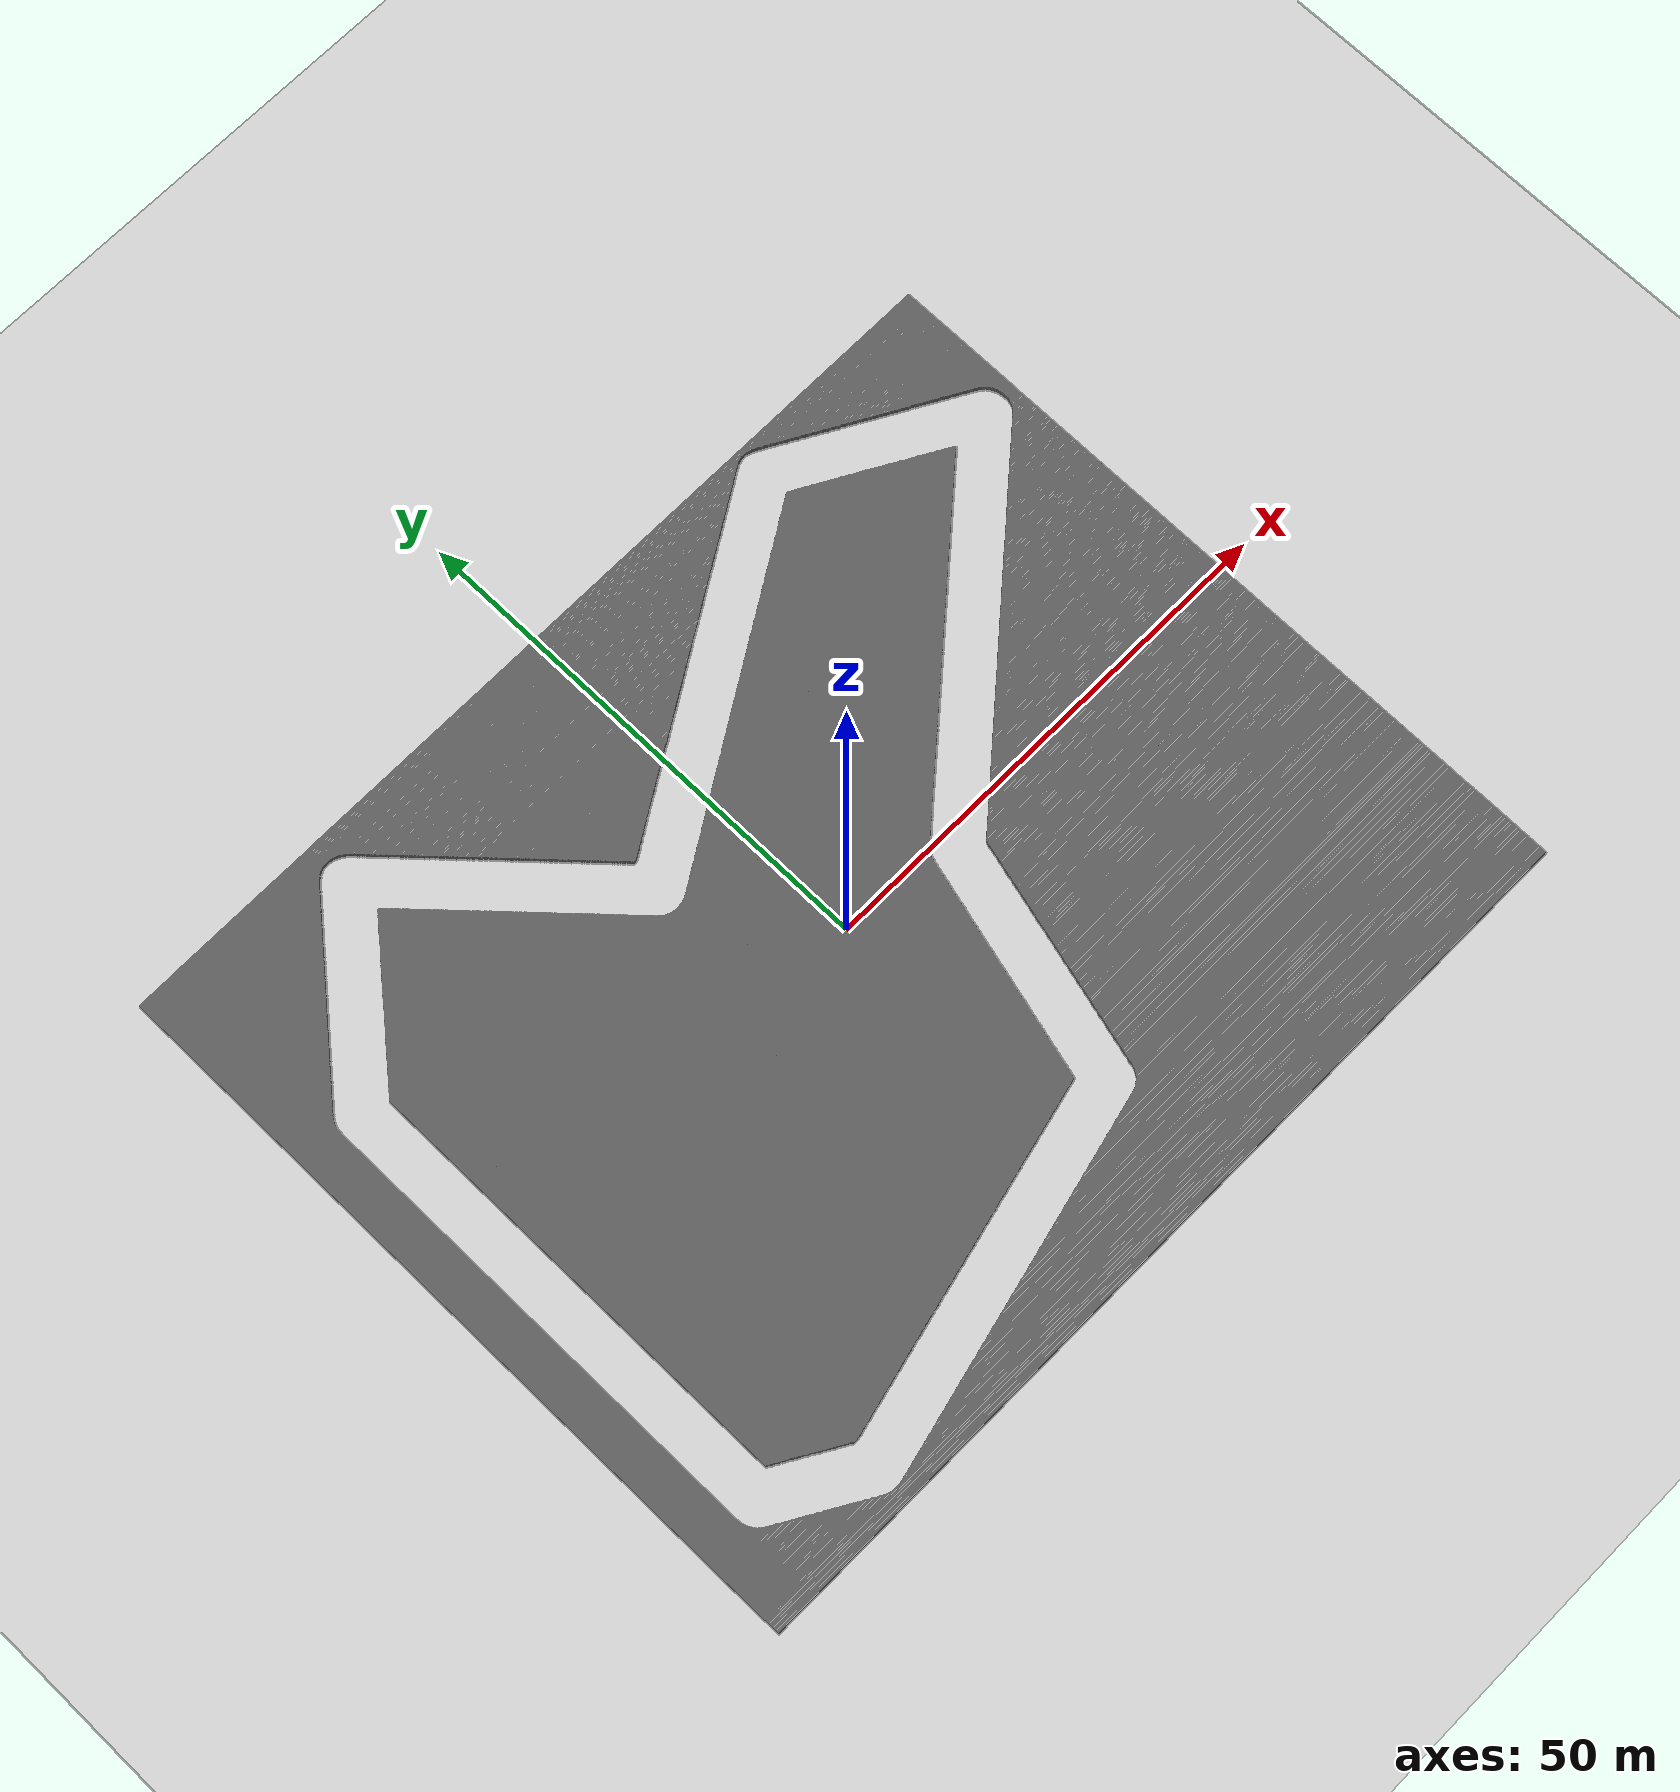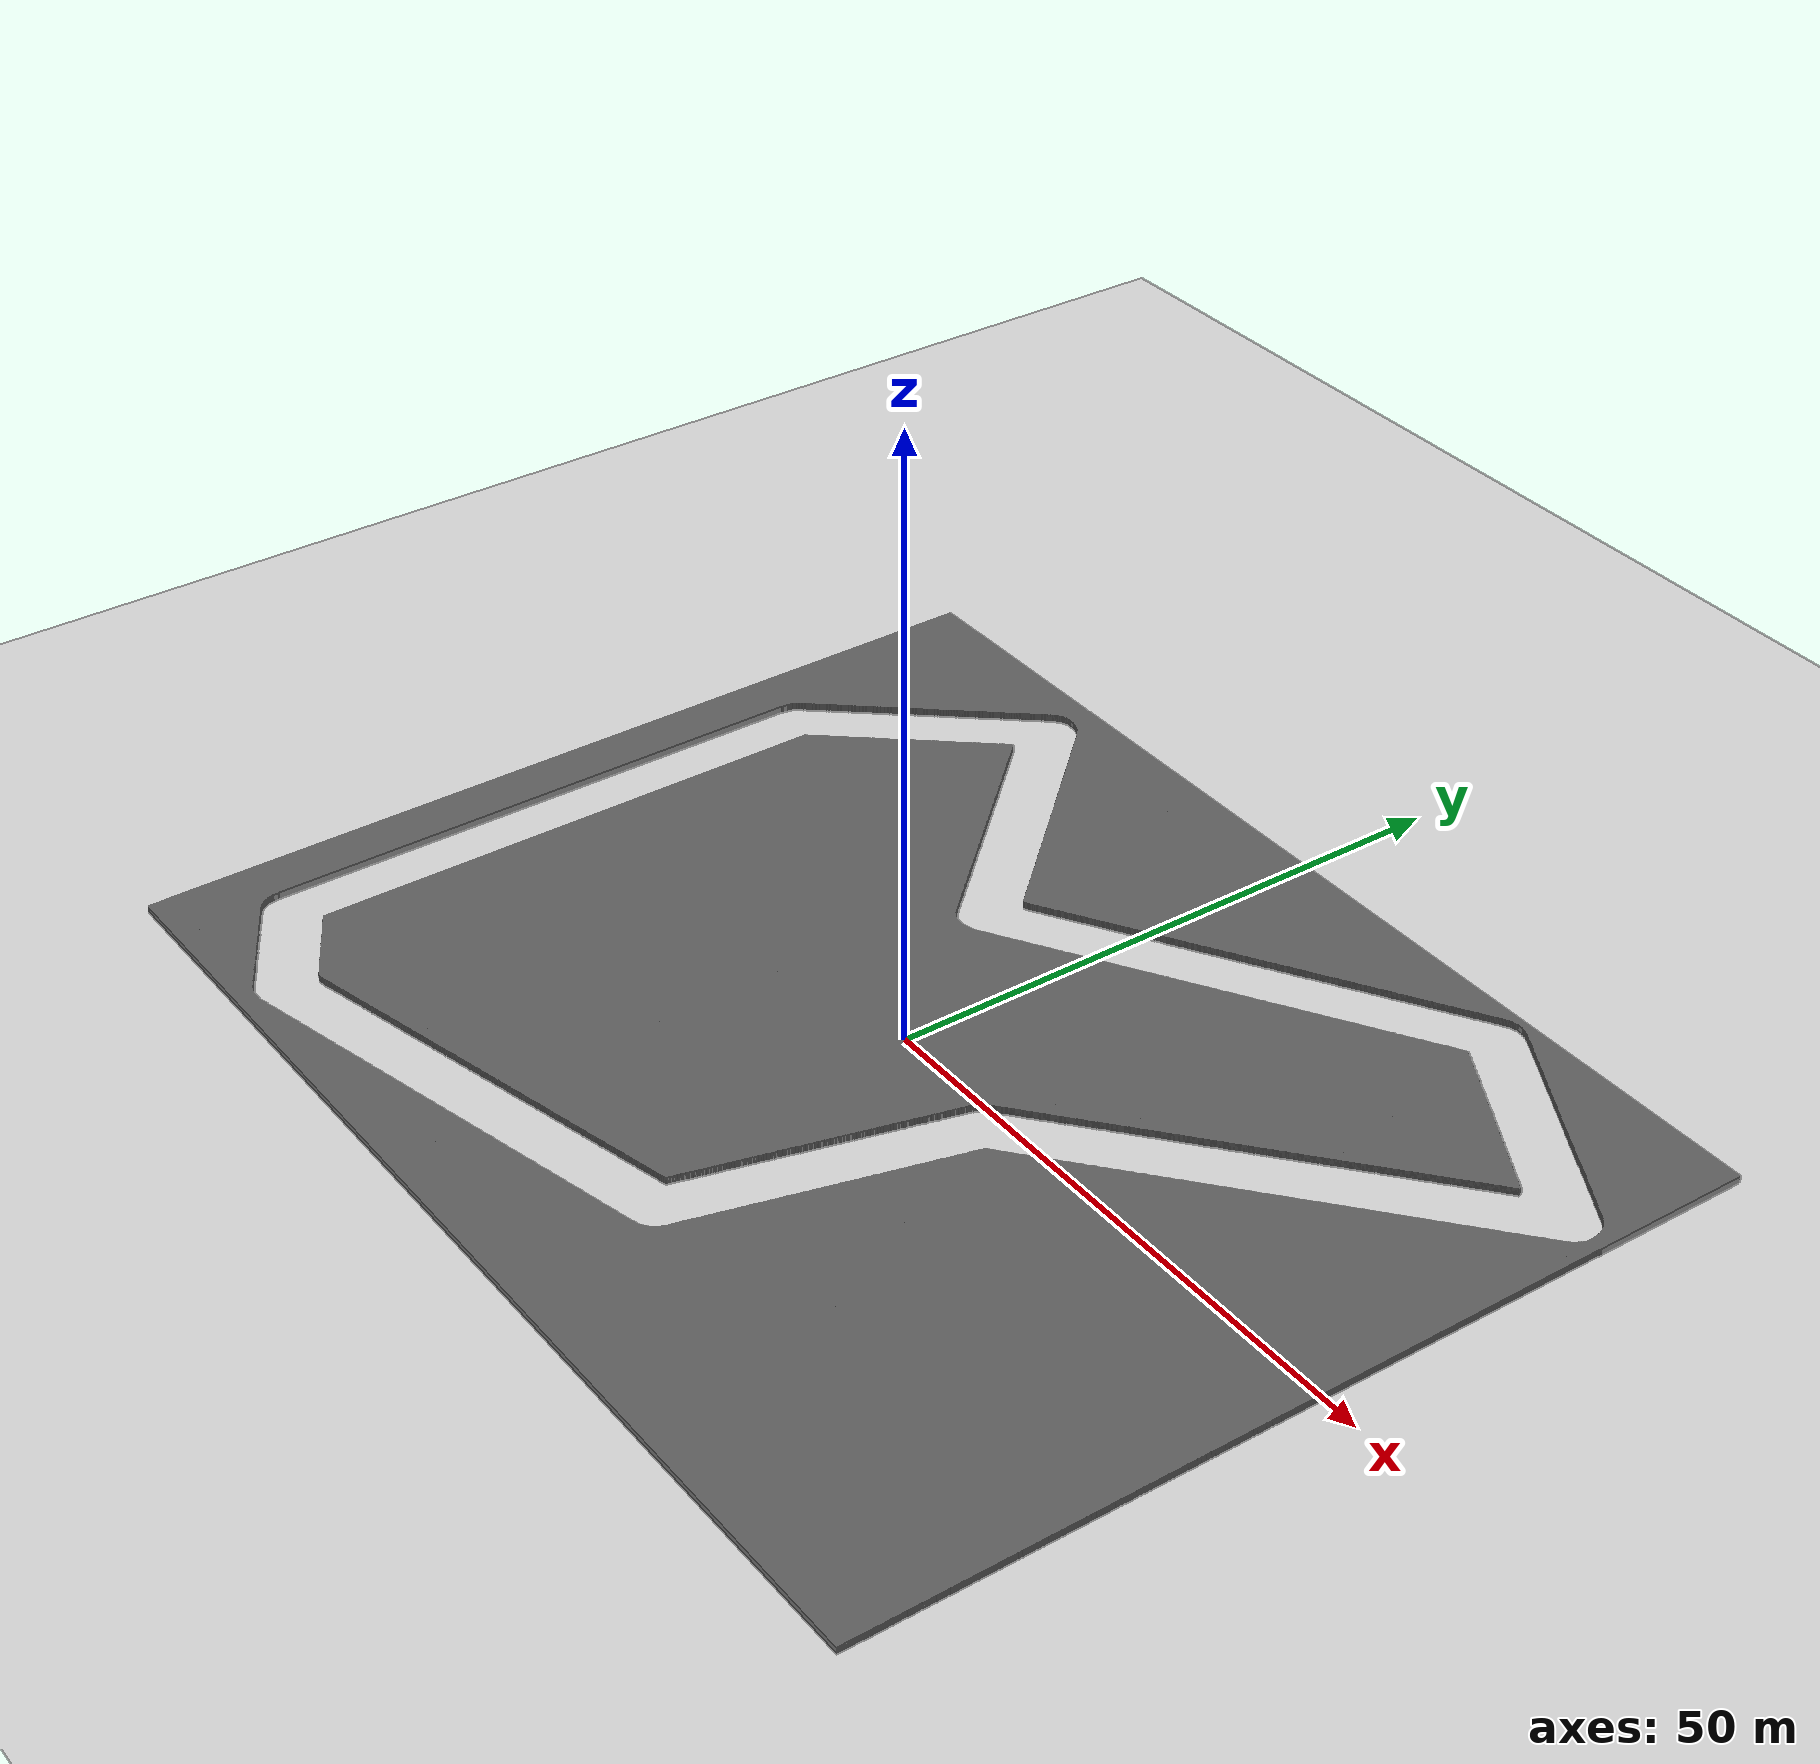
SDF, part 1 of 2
<sdf version="1.6">
 <world name="default">
  <include><uri>model://sun</uri></include>
  <include><uri>model://ground_plane</uri></include>
  <physics type="ode">
   <real_time_update_rate>1000.0</real_time_update_rate>
   <max_step_size>0.001</max_step_size>
   <real_time_factor>1</real_time_factor>
   <ode>
    <solver>
     <type>quick</type>
     <iters>150</iters>
     <precon_iters>0</precon_iters>
     <sor>1.400000</sor>
     <use_dynamic_moi_rescaling>1</use_dynamic_moi_rescaling>
    </solver>
    <constraints>
     <cfm>0.00001</cfm>
     <erp>0.2</erp>
     <contact_max_correcting_vel>2000.000000</contact_max_correcting_vel>
     <contact_surface_layer>0.01000</contact_surface_layer>
    </constraints>
   </ode>
  </physics>
  <scene><ambient>0.4 0.4 0.4 1</ambient><background>0.7 0.7 0.7 1</background><shadows>true</shadows></scene>
  <model name="obstacle">
   <static>1</static>
   <link name="obstacle">
    <collision name="obstacle_1">
     <pose>-0.025000000000005684 -38.0 0 0 0 0</pose>
     <geometry><box><size>93.55000000000001 0.15 1.0</size></box></geometry>
    </collision>
    <visual name="obstacle_1">
     <pose>-0.025000000000005684 -38.0 0 0 0 0</pose>
     <geometry><box><size>93.55000000000001 0.15 1.0</size></box></geometry>
     <material>
      <script><uri>file://media/materials/scripts/gazebo.material</uri><name>Gazebo/Grey</name></script>
      <ambient>1 1 1 1</ambient>
     </material>
    </visual>
    <collision name="obstacle_2">
     <pose>-0.025000000000005684 -37.95 0 0 0 0</pose>
     <geometry><box><size>93.55000000000001 0.15 1.0</size></box></geometry>
    </collision>
    <visual name="obstacle_2">
     <pose>-0.025000000000005684 -37.95 0 0 0 0</pose>
     <geometry><box><size>93.55000000000001 0.15 1.0</size></box></geometry>
     <material>
      <script><uri>file://media/materials/scripts/gazebo.material</uri><name>Gazebo/Grey</name></script>
      <ambient>1 1 1 1</ambient>
     </material>
    </visual>
    <collision name="obstacle_3">
     <pose>-0.025000000000005684 -37.9 0 0 0 0</pose>
     <geometry><box><size>93.55000000000001 0.15 1.0</size></box></geometry>
    </collision>
    <visual name="obstacle_3">
     <pose>-0.025000000000005684 -37.9 0 0 0 0</pose>
     <geometry><box><size>93.55000000000001 0.15 1.0</size></box></geometry>
     <material>
      <script><uri>file://media/materials/scripts/gazebo.material</uri><name>Gazebo/Grey</name></script>
      <ambient>1 1 1 1</ambient>
     </material>
    </visual>
    <collision name="obstacle_4">
     <pose>-0.025000000000005684 -37.85 0 0 0 0</pose>
     <geometry><box><size>93.55000000000001 0.15 1.0</size></box></geometry>
    </collision>
    <visual name="obstacle_4">
     <pose>-0.025000000000005684 -37.85 0 0 0 0</pose>
     <geometry><box><size>93.55000000000001 0.15 1.0</size></box></geometry>
     <material>
      <script><uri>file://media/materials/scripts/gazebo.material</uri><name>Gazebo/Grey</name></script>
      <ambient>1 1 1 1</ambient>
     </material>
    </visual>
    <collision name="obstacle_5">
     <pose>-0.025000000000005684 -37.8 0 0 0 0</pose>
     <geometry><box><size>93.55000000000001 0.15 1.0</size></box></geometry>
    </collision>
    <visual name="obstacle_5">
     <pose>-0.025000000000005684 -37.8 0 0 0 0</pose>
     <geometry><box><size>93.55000000000001 0.15 1.0</size></box></geometry>
     <material>
      <script><uri>file://media/materials/scripts/gazebo.material</uri><name>Gazebo/Grey</name></script>
      <ambient>1 1 1 1</ambient>
     </material>
    </visual>
    <collision name="obstacle_6">
     <pose>-0.025000000000005684 -37.75 0 0 0 0</pose>
     <geometry><box><size>93.55000000000001 0.15 1.0</size></box></geometry>
    </collision>
    <visual name="obstacle_6">
     <pose>-0.025000000000005684 -37.75 0 0 0 0</pose>
     <geometry><box><size>93.55000000000001 0.15 1.0</size></box></geometry>
     <material>
      <script><uri>file://media/materials/scripts/gazebo.material</uri><name>Gazebo/Grey</name></script>
      <ambient>1 1 1 1</ambient>
     </material>
    </visual>
    <collision name="obstacle_7">
     <pose>-0.025000000000005684 -37.7 0 0 0 0</pose>
     <geometry><box><size>93.55000000000001 0.15 1.0</size></box></geometry>
    </collision>
    <visual name="obstacle_7">
     <pose>-0.025000000000005684 -37.7 0 0 0 0</pose>
     <geometry><box><size>93.55000000000001 0.15 1.0</size></box></geometry>
     <material>
      <script><uri>file://media/materials/scripts/gazebo.material</uri><name>Gazebo/Grey</name></script>
      <ambient>1 1 1 1</ambient>
     </material>
    </visual>
    <collision name="obstacle_8">
     <pose>-0.025000000000005684 -37.65 0 0 0 0</pose>
     <geometry><box><size>93.55000000000001 0.15 1.0</size></box></geometry>
    </collision>
    <visual name="obstacle_8">
     <pose>-0.025000000000005684 -37.65 0 0 0 0</pose>
     <geometry><box><size>93.55000000000001 0.15 1.0</size></box></geometry>
     <material>
      <script><uri>file://media/materials/scripts/gazebo.material</uri><name>Gazebo/Grey</name></script>
      <ambient>1 1 1 1</ambient>
     </material>
    </visual>
    <collision name="obstacle_9">
     <pose>-0.025000000000005684 -37.6 0 0 0 0</pose>
     <geometry><box><size>93.55000000000001 0.15 1.0</size></box></geometry>
    </collision>
    <visual name="obstacle_9">
     <pose>-0.025000000000005684 -37.6 0 0 0 0</pose>
     <geometry><box><size>93.55000000000001 0.15 1.0</size></box></geometry>
     <material>
      <script><uri>file://media/materials/scripts/gazebo.material</uri><name>Gazebo/Grey</name></script>
      <ambient>1 1 1 1</ambient>
     </material>
    </visual>
    <collision name="obstacle_10">
     <pose>-0.025000000000005684 -37.55 0 0 0 0</pose>
     <geometry><box><size>93.55000000000001 0.15 1.0</size></box></geometry>
    </collision>
    <visual name="obstacle_10">
     <pose>-0.025000000000005684 -37.55 0 0 0 0</pose>
     <geometry><box><size>93.55000000000001 0.15 1.0</size></box></geometry>
     <material>
      <script><uri>file://media/materials/scripts/gazebo.material</uri><name>Gazebo/Grey</name></script>
      <ambient>1 1 1 1</ambient>
     </material>
    </visual>
    <collision name="obstacle_11">
     <pose>-0.025000000000005684 -37.5 0 0 0 0</pose>
     <geometry><box><size>93.55000000000001 0.15 1.0</size></box></geometry>
    </collision>
    <visual name="obstacle_11">
     <pose>-0.025000000000005684 -37.5 0 0 0 0</pose>
     <geometry><box><size>93.55000000000001 0.15 1.0</size></box></geometry>
     <material>
      <script><uri>file://media/materials/scripts/gazebo.material</uri><name>Gazebo/Grey</name></script>
      <ambient>1 1 1 1</ambient>
     </material>
    </visual>
    <collision name="obstacle_12">
     <pose>-0.025000000000005684 -37.45 0 0 0 0</pose>
     <geometry><box><size>93.55000000000001 0.15 1.0</size></box></geometry>
    </collision>
    <visual name="obstacle_12">
     <pose>-0.025000000000005684 -37.45 0 0 0 0</pose>
     <geometry><box><size>93.55000000000001 0.15 1.0</size></box></geometry>
     <material>
      <script><uri>file://media/materials/scripts/gazebo.material</uri><name>Gazebo/Grey</name></script>
      <ambient>1 1 1 1</ambient>
     </material>
    </visual>
    <collision name="obstacle_13">
     <pose>-0.025000000000005684 -37.4 0 0 0 0</pose>
     <geometry><box><size>93.55000000000001 0.15 1.0</size></box></geometry>
    </collision>
    <visual name="obstacle_13">
     <pose>-0.025000000000005684 -37.4 0 0 0 0</pose>
     <geometry><box><size>93.55000000000001 0.15 1.0</size></box></geometry>
     <material>
      <script><uri>file://media/materials/scripts/gazebo.material</uri><name>Gazebo/Grey</name></script>
      <ambient>1 1 1 1</ambient>
     </material>
    </visual>
    <collision name="obstacle_14">
     <pose>-0.025000000000005684 -37.35 0 0 0 0</pose>
     <geometry><box><size>93.55000000000001 0.15 1.0</size></box></geometry>
    </collision>
    <visual name="obstacle_14">
     <pose>-0.025000000000005684 -37.35 0 0 0 0</pose>
     <geometry><box><size>93.55000000000001 0.15 1.0</size></box></geometry>
     <material>
      <script><uri>file://media/materials/scripts/gazebo.material</uri><name>Gazebo/Grey</name></script>
      <ambient>1 1 1 1</ambient>
     </material>
    </visual>
    <collision name="obstacle_15">
     <pose>-0.025000000000005684 -37.3 0 0 0 0</pose>
     <geometry><box><size>93.55000000000001 0.15 1.0</size></box></geometry>
    </collision>
    <visual name="obstacle_15">
     <pose>-0.025000000000005684 -37.3 0 0 0 0</pose>
     <geometry><box><size>93.55000000000001 0.15 1.0</size></box></geometry>
     <material>
      <script><uri>file://media/materials/scripts/gazebo.material</uri><name>Gazebo/Grey</name></script>
      <ambient>1 1 1 1</ambient>
     </material>
    </visual>
    <collision name="obstacle_16">
     <pose>-0.025000000000005684 -37.25 0 0 0 0</pose>
     <geometry><box><size>93.55000000000001 0.15 1.0</size></box></geometry>
    </collision>
    <visual name="obstacle_16">
     <pose>-0.025000000000005684 -37.25 0 0 0 0</pose>
     <geometry><box><size>93.55000000000001 0.15 1.0</size></box></geometry>
     <material>
      <script><uri>file://media/materials/scripts/gazebo.material</uri><name>Gazebo/Grey</name></script>
      <ambient>1 1 1 1</ambient>
     </material>
    </visual>
    <collision name="obstacle_17">
     <pose>-0.025000000000005684 -37.2 0 0 0 0</pose>
     <geometry><box><size>93.55000000000001 0.15 1.0</size></box></geometry>
    </collision>
    <visual name="obstacle_17">
     <pose>-0.025000000000005684 -37.2 0 0 0 0</pose>
     <geometry><box><size>93.55000000000001 0.15 1.0</size></box></geometry>
     <material>
      <script><uri>file://media/materials/scripts/gazebo.material</uri><name>Gazebo/Grey</name></script>
      <ambient>1 1 1 1</ambient>
     </material>
    </visual>
    <collision name="obstacle_18">
     <pose>-0.025000000000005684 -37.15 0 0 0 0</pose>
     <geometry><box><size>93.55000000000001 0.15 1.0</size></box></geometry>
    </collision>
    <visual name="obstacle_18">
     <pose>-0.025000000000005684 -37.15 0 0 0 0</pose>
     <geometry><box><size>93.55000000000001 0.15 1.0</size></box></geometry>
     <material>
      <script><uri>file://media/materials/scripts/gazebo.material</uri><name>Gazebo/Grey</name></script>
      <ambient>1 1 1 1</ambient>
     </material>
    </visual>
    <collision name="obstacle_19">
     <pose>-0.025000000000005684 -37.1 0 0 0 0</pose>
     <geometry><box><size>93.55000000000001 0.15 1.0</size></box></geometry>
    </collision>
    <visual name="obstacle_19">
     <pose>-0.025000000000005684 -37.1 0 0 0 0</pose>
     <geometry><box><size>93.55000000000001 0.15 1.0</size></box></geometry>
     <material>
      <script><uri>file://media/materials/scripts/gazebo.material</uri><name>Gazebo/Grey</name></script>
      <ambient>1 1 1 1</ambient>
     </material>
    </visual>
    <collision name="obstacle_20">
     <pose>-0.025000000000005684 -37.05 0 0 0 0</pose>
     <geometry><box><size>93.55000000000001 0.15 1.0</size></box></geometry>
    </collision>
    <visual name="obstacle_20">
     <pose>-0.025000000000005684 -37.05 0 0 0 0</pose>
     <geometry><box><size>93.55000000000001 0.15 1.0</size></box></geometry>
     <material>
      <script><uri>file://media/materials/scripts/gazebo.material</uri><name>Gazebo/Grey</name></script>
      <ambient>1 1 1 1</ambient>
     </material>
    </visual>
    <collision name="obstacle_21">
     <pose>-0.025000000000005684 -37.0 0 0 0 0</pose>
     <geometry><box><size>93.55000000000001 0.15 1.0</size></box></geometry>
    </collision>
    <visual name="obstacle_21">
     <pose>-0.025000000000005684 -37.0 0 0 0 0</pose>
     <geometry><box><size>93.55000000000001 0.15 1.0</size></box></geometry>
     <material>
      <script><uri>file://media/materials/scripts/gazebo.material</uri><name>Gazebo/Grey</name></script>
      <ambient>1 1 1 1</ambient>
     </material>
    </visual>
    <collision name="obstacle_22">
     <pose>-0.025000000000005684 -36.95 0 0 0 0</pose>
     <geometry><box><size>93.55000000000001 0.15 1.0</size></box></geometry>
    </collision>
    <visual name="obstacle_22">
     <pose>-0.025000000000005684 -36.95 0 0 0 0</pose>
     <geometry><box><size>93.55000000000001 0.15 1.0</size></box></geometry>
     <material>
      <script><uri>file://media/materials/scripts/gazebo.material</uri><name>Gazebo/Grey</name></script>
      <ambient>1 1 1 1</ambient>
     </material>
    </visual>
    <collision name="obstacle_23">
     <pose>-0.025000000000005684 -36.9 0 0 0 0</pose>
     <geometry><box><size>93.55000000000001 0.15 1.0</size></box></geometry>
    </collision>
    <visual name="obstacle_23">
     <pose>-0.025000000000005684 -36.9 0 0 0 0</pose>
     <geometry><box><size>93.55000000000001 0.15 1.0</size></box></geometry>
     <material>
      <script><uri>file://media/materials/scripts/gazebo.material</uri><name>Gazebo/Grey</name></script>
      <ambient>1 1 1 1</ambient>
     </material>
    </visual>
    <collision name="obstacle_24">
     <pose>-0.025000000000005684 -36.85 0 0 0 0</pose>
     <geometry><box><size>93.55000000000001 0.15 1.0</size></box></geometry>
    </collision>
    <visual name="obstacle_24">
     <pose>-0.025000000000005684 -36.85 0 0 0 0</pose>
     <geometry><box><size>93.55000000000001 0.15 1.0</size></box></geometry>
     <material>
      <script><uri>file://media/materials/scripts/gazebo.material</uri><name>Gazebo/Grey</name></script>
      <ambient>1 1 1 1</ambient>
     </material>
    </visual>
    <collision name="obstacle_25">
     <pose>-0.025000000000005684 -36.8 0 0 0 0</pose>
     <geometry><box><size>93.55000000000001 0.15 1.0</size></box></geometry>
    </collision>
    <visual name="obstacle_25">
     <pose>-0.025000000000005684 -36.8 0 0 0 0</pose>
     <geometry><box><size>93.55000000000001 0.15 1.0</size></box></geometry>
     <material>
      <script><uri>file://media/materials/scripts/gazebo.material</uri><name>Gazebo/Grey</name></script>
      <ambient>1 1 1 1</ambient>
     </material>
    </visual>
    <collision name="obstacle_26">
     <pose>-0.025000000000005684 -36.75 0 0 0 0</pose>
     <geometry><box><size>93.55000000000001 0.15 1.0</size></box></geometry>
    </collision>
    <visual name="obstacle_26">
     <pose>-0.025000000000005684 -36.75 0 0 0 0</pose>
     <geometry><box><size>93.55000000000001 0.15 1.0</size></box></geometry>
     <material>
      <script><uri>file://media/materials/scripts/gazebo.material</uri><name>Gazebo/Grey</name></script>
      <ambient>1 1 1 1</ambient>
     </material>
    </visual>
    <collision name="obstacle_27">
     <pose>-0.025000000000005684 -36.7 0 0 0 0</pose>
     <geometry><box><size>93.55000000000001 0.15 1.0</size></box></geometry>
    </collision>
    <visual name="obstacle_27">
     <pose>-0.025000000000005684 -36.7 0 0 0 0</pose>
     <geometry><box><size>93.55000000000001 0.15 1.0</size></box></geometry>
     <material>
      <script><uri>file://media/materials/scripts/gazebo.material</uri><name>Gazebo/Grey</name></script>
      <ambient>1 1 1 1</ambient>
     </material>
    </visual>
    <collision name="obstacle_28">
     <pose>-0.025000000000005684 -36.65 0 0 0 0</pose>
     <geometry><box><size>93.55000000000001 0.15 1.0</size></box></geometry>
    </collision>
    <visual name="obstacle_28">
     <pose>-0.025000000000005684 -36.65 0 0 0 0</pose>
     <geometry><box><size>93.55000000000001 0.15 1.0</size></box></geometry>
     <material>
      <script><uri>file://media/materials/scripts/gazebo.material</uri><name>Gazebo/Grey</name></script>
      <ambient>1 1 1 1</ambient>
     </material>
    </visual>
    <collision name="obstacle_29">
     <pose>-0.025000000000005684 -36.6 0 0 0 0</pose>
     <geometry><box><size>93.55000000000001 0.15 1.0</size></box></geometry>
    </collision>
    <visual name="obstacle_29">
     <pose>-0.025000000000005684 -36.6 0 0 0 0</pose>
     <geometry><box><size>93.55000000000001 0.15 1.0</size></box></geometry>
     <material>
      <script><uri>file://media/materials/scripts/gazebo.material</uri><name>Gazebo/Grey</name></script>
      <ambient>1 1 1 1</ambient>
     </material>
    </visual>
    <collision name="obstacle_30">
     <pose>-46.775000000000006 0.7000000000000028 0 0 0 1.5708</pose>
     <geometry><box><size>74.55 0.15 1.0</size></box></geometry>
    </collision>
    <visual name="obstacle_30">
     <pose>-46.775000000000006 0.7000000000000028 0 0 0 1.5708</pose>
     <geometry><box><size>74.55 0.15 1.0</size></box></geometry>
     <material>
      <script><uri>file://media/materials/scripts/gazebo.material</uri><name>Gazebo/Grey</name></script>
      <ambient>1 1 1 1</ambient>
     </material>
    </visual>
    <collision name="obstacle_31">
     <pose>-46.72500000000001 0.7000000000000028 0 0 0 1.5708</pose>
     <geometry><box><size>74.55 0.15 1.0</size></box></geometry>
    </collision>
    <visual name="obstacle_31">
     <pose>-46.72500000000001 0.7000000000000028 0 0 0 1.5708</pose>
     <geometry><box><size>74.55 0.15 1.0</size></box></geometry>
     <material>
      <script><uri>file://media/materials/scripts/gazebo.material</uri><name>Gazebo/Grey</name></script>
      <ambient>1 1 1 1</ambient>
     </material>
    </visual>
    <collision name="obstacle_32">
     <pose>-46.675000000000004 0.7000000000000028 0 0 0 1.5708</pose>
     <geometry><box><size>74.55 0.15 1.0</size></box></geometry>
    </collision>
    <visual name="obstacle_32">
     <pose>-46.675000000000004 0.7000000000000028 0 0 0 1.5708</pose>
     <geometry><box><size>74.55 0.15 1.0</size></box></geometry>
     <material>
      <script><uri>file://media/materials/scripts/gazebo.material</uri><name>Gazebo/Grey</name></script>
      <ambient>1 1 1 1</ambient>
     </material>
    </visual>
    <collision name="obstacle_33">
     <pose>-46.62500000000001 0.7000000000000028 0 0 0 1.5708</pose>
     <geometry><box><size>74.55 0.15 1.0</size></box></geometry>
    </collision>
    <visual name="obstacle_33">
     <pose>-46.62500000000001 0.7000000000000028 0 0 0 1.5708</pose>
     <geometry><box><size>74.55 0.15 1.0</size></box></geometry>
     <material>
      <script><uri>file://media/materials/scripts/gazebo.material</uri><name>Gazebo/Grey</name></script>
      <ambient>1 1 1 1</ambient>
     </material>
    </visual>
    <collision name="obstacle_34">
     <pose>-46.575 0.7000000000000028 0 0 0 1.5708</pose>
     <geometry><box><size>74.55 0.15 1.0</size></box></geometry>
    </collision>
    <visual name="obstacle_34">
     <pose>-46.575 0.7000000000000028 0 0 0 1.5708</pose>
     <geometry><box><size>74.55 0.15 1.0</size></box></geometry>
     <material>
      <script><uri>file://media/materials/scripts/gazebo.material</uri><name>Gazebo/Grey</name></script>
      <ambient>1 1 1 1</ambient>
     </material>
    </visual>
    <collision name="obstacle_35">
     <pose>-46.525000000000006 0.7000000000000028 0 0 0 1.5708</pose>
     <geometry><box><size>74.55 0.15 1.0</size></box></geometry>
    </collision>
    <visual name="obstacle_35">
     <pose>-46.525000000000006 0.7000000000000028 0 0 0 1.5708</pose>
     <geometry><box><size>74.55 0.15 1.0</size></box></geometry>
     <material>
      <script><uri>file://media/materials/scripts/gazebo.material</uri><name>Gazebo/Grey</name></script>
      <ambient>1 1 1 1</ambient>
     </material>
    </visual>
    <collision name="obstacle_36">
     <pose>-46.47500000000001 0.7000000000000028 0 0 0 1.5708</pose>
     <geometry><box><size>74.55 0.15 1.0</size></box></geometry>
    </collision>
    <visual name="obstacle_36">
     <pose>-46.47500000000001 0.7000000000000028 0 0 0 1.5708</pose>
     <geometry><box><size>74.55 0.15 1.0</size></box></geometry>
     <material>
      <script><uri>file://media/materials/scripts/gazebo.material</uri><name>Gazebo/Grey</name></script>
      <ambient>1 1 1 1</ambient>
     </material>
    </visual>
    <collision name="obstacle_37">
     <pose>-46.425000000000004 0.7000000000000028 0 0 0 1.5708</pose>
     <geometry><box><size>74.55 0.15 1.0</size></box></geometry>
    </collision>
    <visual name="obstacle_37">
     <pose>-46.425000000000004 0.7000000000000028 0 0 0 1.5708</pose>
     <geometry><box><size>74.55 0.15 1.0</size></box></geometry>
     <material>
      <script><uri>file://media/materials/scripts/gazebo.material</uri><name>Gazebo/Grey</name></script>
      <ambient>1 1 1 1</ambient>
     </material>
    </visual>
    <collision name="obstacle_38">
     <pose>-46.37500000000001 0.7000000000000028 0 0 0 1.5708</pose>
     <geometry><box><size>74.55 0.15 1.0</size></box></geometry>
    </collision>
    <visual name="obstacle_38">
     <pose>-46.37500000000001 0.7000000000000028 0 0 0 1.5708</pose>
     <geometry><box><size>74.55 0.15 1.0</size></box></geometry>
     <material>
      <script><uri>file://media/materials/scripts/gazebo.material</uri><name>Gazebo/Grey</name></script>
      <ambient>1 1 1 1</ambient>
     </material>
    </visual>
    <collision name="obstacle_39">
     <pose>-46.325 0.7000000000000028 0 0 0 1.5708</pose>
     <geometry><box><size>74.55 0.15 1.0</size></box></geometry>
    </collision>
    <visual name="obstacle_39">
     <pose>-46.325 0.7000000000000028 0 0 0 1.5708</pose>
     <geometry><box><size>74.55 0.15 1.0</size></box></geometry>
     <material>
      <script><uri>file://media/materials/scripts/gazebo.material</uri><name>Gazebo/Grey</name></script>
      <ambient>1 1 1 1</ambient>
     </material>
    </visual>
    <collision name="obstacle_40">
     <pose>-46.275000000000006 0.7000000000000028 0 0 0 1.5708</pose>
     <geometry><box><size>74.55 0.15 1.0</size></box></geometry>
    </collision>
    <visual name="obstacle_40">
     <pose>-46.275000000000006 0.7000000000000028 0 0 0 1.5708</pose>
     <geometry><box><size>74.55 0.15 1.0</size></box></geometry>
     <material>
      <script><uri>file://media/materials/scripts/gazebo.material</uri><name>Gazebo/Grey</name></script>
      <ambient>1 1 1 1</ambient>
     </material>
    </visual>
    <collision name="obstacle_41">
     <pose>-46.22500000000001 0.7000000000000028 0 0 0 1.5708</pose>
     <geometry><box><size>74.55 0.15 1.0</size></box></geometry>
    </collision>
    <visual name="obstacle_41">
     <pose>-46.22500000000001 0.7000000000000028 0 0 0 1.5708</pose>
     <geometry><box><size>74.55 0.15 1.0</size></box></geometry>
     <material>
      <script><uri>file://media/materials/scripts/gazebo.material</uri><name>Gazebo/Grey</name></script>
      <ambient>1 1 1 1</ambient>
     </material>
    </visual>
    <collision name="obstacle_42">
     <pose>-46.175000000000004 0.7000000000000028 0 0 0 1.5708</pose>
     <geometry><box><size>74.55 0.15 1.0</size></box></geometry>
    </collision>
    <visual name="obstacle_42">
     <pose>-46.175000000000004 0.7000000000000028 0 0 0 1.5708</pose>
     <geometry><box><size>74.55 0.15 1.0</size></box></geometry>
     <material>
      <script><uri>file://media/materials/scripts/gazebo.material</uri><name>Gazebo/Grey</name></script>
      <ambient>1 1 1 1</ambient>
     </material>
    </visual>
    <collision name="obstacle_43">
     <pose>-46.12500000000001 0.7000000000000028 0 0 0 1.5708</pose>
     <geometry><box><size>74.55 0.15 1.0</size></box></geometry>
    </collision>
    <visual name="obstacle_43">
     <pose>-46.12500000000001 0.7000000000000028 0 0 0 1.5708</pose>
     <geometry><box><size>74.55 0.15 1.0</size></box></geometry>
     <material>
      <script><uri>file://media/materials/scripts/gazebo.material</uri><name>Gazebo/Grey</name></script>
      <ambient>1 1 1 1</ambient>
     </material>
    </visual>
    <collision name="obstacle_44">
     <pose>-46.075 0.7000000000000028 0 0 0 1.5708</pose>
     <geometry><box><size>74.55 0.15 1.0</size></box></geometry>
    </collision>
    <visual name="obstacle_44">
     <pose>-46.075 0.7000000000000028 0 0 0 1.5708</pose>
     <geometry><box><size>74.55 0.15 1.0</size></box></geometry>
     <material>
      <script><uri>file://media/materials/scripts/gazebo.material</uri><name>Gazebo/Grey</name></script>
      <ambient>1 1 1 1</ambient>
     </material>
    </visual>
    <collision name="obstacle_45">
     <pose>-46.025000000000006 0.7000000000000028 0 0 0 1.5708</pose>
     <geometry><box><size>74.55 0.15 1.0</size></box></geometry>
    </collision>
    <visual name="obstacle_45">
     <pose>-46.025000000000006 0.7000000000000028 0 0 0 1.5708</pose>
     <geometry><box><size>74.55 0.15 1.0</size></box></geometry>
     <material>
      <script><uri>file://media/materials/scripts/gazebo.material</uri><name>Gazebo/Grey</name></script>
      <ambient>1 1 1 1</ambient>
     </material>
    </visual>
    <collision name="obstacle_46">
     <pose>-45.97500000000001 0.7000000000000028 0 0 0 1.5708</pose>
     <geometry><box><size>74.55 0.15 1.0</size></box></geometry>
    </collision>
    <visual name="obstacle_46">
     <pose>-45.97500000000001 0.7000000000000028 0 0 0 1.5708</pose>
     <geometry><box><size>74.55 0.15 1.0</size></box></geometry>
     <material>
      <script><uri>file://media/materials/scripts/gazebo.material</uri><name>Gazebo/Grey</name></script>
      <ambient>1 1 1 1</ambient>
     </material>
    </visual>
    <collision name="obstacle_47">
     <pose>-45.925000000000004 0.7000000000000028 0 0 0 1.5708</pose>
     <geometry><box><size>74.55 0.15 1.0</size></box></geometry>
    </collision>
    <visual name="obstacle_47">
     <pose>-45.925000000000004 0.7000000000000028 0 0 0 1.5708</pose>
     <geometry><box><size>74.55 0.15 1.0</size></box></geometry>
     <material>
      <script><uri>file://media/materials/scripts/gazebo.material</uri><name>Gazebo/Grey</name></script>
      <ambient>1 1 1 1</ambient>
     </material>
    </visual>
    <collision name="obstacle_48">
     <pose>-45.87500000000001 0.7000000000000028 0 0 0 1.5708</pose>
     <geometry><box><size>74.55 0.15 1.0</size></box></geometry>
    </collision>
    <visual name="obstacle_48">
     <pose>-45.87500000000001 0.7000000000000028 0 0 0 1.5708</pose>
     <geometry><box><size>74.55 0.15 1.0</size></box></geometry>
     <material>
      <script><uri>file://media/materials/scripts/gazebo.material</uri><name>Gazebo/Grey</name></script>
      <ambient>1 1 1 1</ambient>
     </material>
    </visual>
    <collision name="obstacle_49">
     <pose>-45.825 0.7000000000000028 0 0 0 1.5708</pose>
     <geometry><box><size>74.55 0.15 1.0</size></box></geometry>
    </collision>
    <visual name="obstacle_49">
     <pose>-45.825 0.7000000000000028 0 0 0 1.5708</pose>
     <geometry><box><size>74.55 0.15 1.0</size></box></geometry>
     <material>
      <script><uri>file://media/materials/scripts/gazebo.material</uri><name>Gazebo/Grey</name></script>
      <ambient>1 1 1 1</ambient>
     </material>
    </visual>
    <collision name="obstacle_50">
     <pose>-45.775000000000006 0.7000000000000028 0 0 0 1.5708</pose>
     <geometry><box><size>74.55 0.15 1.0</size></box></geometry>
    </collision>
    <visual name="obstacle_50">
     <pose>-45.775000000000006 0.7000000000000028 0 0 0 1.5708</pose>
     <geometry><box><size>74.55 0.15 1.0</size></box></geometry>
     <material>
      <script><uri>file://media/materials/scripts/gazebo.material</uri><name>Gazebo/Grey</name></script>
      <ambient>1 1 1 1</ambient>
     </material>
    </visual>
    <collision name="obstacle_51">
     <pose>-45.72500000000001 0.7000000000000028 0 0 0 1.5708</pose>
     <geometry><box><size>74.55 0.15 1.0</size></box></geometry>
    </collision>
    <visual name="obstacle_51">
     <pose>-45.72500000000001 0.7000000000000028 0 0 0 1.5708</pose>
     <geometry><box><size>74.55 0.15 1.0</size></box></geometry>
     <material>
      <script><uri>file://media/materials/scripts/gazebo.material</uri><name>Gazebo/Grey</name></script>
      <ambient>1 1 1 1</ambient>
     </material>
    </visual>
    <collision name="obstacle_52">
     <pose>-45.675000000000004 0.7000000000000028 0 0 0 1.5708</pose>
     <geometry><box><size>74.55 0.15 1.0</size></box></geometry>
    </collision>
    <visual name="obstacle_52">
     <pose>-45.675000000000004 0.7000000000000028 0 0 0 1.5708</pose>
     <geometry><box><size>74.55 0.15 1.0</size></box></geometry>
     <material>
      <script><uri>file://media/materials/scripts/gazebo.material</uri><name>Gazebo/Grey</name></script>
      <ambient>1 1 1 1</ambient>
     </material>
    </visual>
    <collision name="obstacle_53">
     <pose>-45.62500000000001 0.7000000000000028 0 0 0 1.5708</pose>
     <geometry><box><size>74.55 0.15 1.0</size></box></geometry>
    </collision>
    <visual name="obstacle_53">
     <pose>-45.62500000000001 0.7000000000000028 0 0 0 1.5708</pose>
     <geometry><box><size>74.55 0.15 1.0</size></box></geometry>
     <material>
      <script><uri>file://media/materials/scripts/gazebo.material</uri><name>Gazebo/Grey</name></script>
      <ambient>1 1 1 1</ambient>
     </material>
    </visual>
    <collision name="obstacle_54">
     <pose>-45.575 0.7000000000000028 0 0 0 1.5708</pose>
     <geometry><box><size>74.55 0.15 1.0</size></box></geometry>
    </collision>
    <visual name="obstacle_54">
     <pose>-45.575 0.7000000000000028 0 0 0 1.5708</pose>
     <geometry><box><size>74.55 0.15 1.0</size></box></geometry>
     <material>
      <script><uri>file://media/materials/scripts/gazebo.material</uri><name>Gazebo/Grey</name></script>
      <ambient>1 1 1 1</ambient>
     </material>
    </visual>
    <collision name="obstacle_55">
     <pose>-45.525000000000006 0.7000000000000028 0 0 0 1.5708</pose>
     <geometry><box><size>74.55 0.15 1.0</size></box></geometry>
    </collision>
    <visual name="obstacle_55">
     <pose>-45.525000000000006 0.7000000000000028 0 0 0 1.5708</pose>
     <geometry><box><size>74.55 0.15 1.0</size></box></geometry>
     <material>
      <script><uri>file://media/materials/scripts/gazebo.material</uri><name>Gazebo/Grey</name></script>
      <ambient>1 1 1 1</ambient>
     </material>
    </visual>
    <collision name="obstacle_56">
     <pose>-45.47500000000001 0.7000000000000028 0 0 0 1.5708</pose>
     <geometry><box><size>74.55 0.15 1.0</size></box></geometry>
    </collision>
    <visual name="obstacle_56">
     <pose>-45.47500000000001 0.7000000000000028 0 0 0 1.5708</pose>
     <geometry><box><size>74.55 0.15 1.0</size></box></geometry>
     <material>
      <script><uri>file://media/materials/scripts/gazebo.material</uri><name>Gazebo/Grey</name></script>
      <ambient>1 1 1 1</ambient>
     </material>
    </visual>
    <collision name="obstacle_57">
     <pose>-45.425000000000004 0.7000000000000028 0 0 0 1.5708</pose>
     <geometry><box><size>74.55 0.15 1.0</size></box></geometry>
    </collision>
    <visual name="obstacle_57">
     <pose>-45.425000000000004 0.7000000000000028 0 0 0 1.5708</pose>
     <geometry><box><size>74.55 0.15 1.0</size></box></geometry>
     <material>
      <script><uri>file://media/materials/scripts/gazebo.material</uri><name>Gazebo/Grey</name></script>
      <ambient>1 1 1 1</ambient>
     </material>
    </visual>
    <collision name="obstacle_58">
     <pose>-45.37500000000001 0.7000000000000028 0 0 0 1.5708</pose>
     <geometry><box><size>74.55 0.15 1.0</size></box></geometry>
    </collision>
    <visual name="obstacle_58">
     <pose>-45.37500000000001 0.7000000000000028 0 0 0 1.5708</pose>
     <geometry><box><size>74.55 0.15 1.0</size></box></geometry>
     <material>
      <script><uri>file://media/materials/scripts/gazebo.material</uri><name>Gazebo/Grey</name></script>
      <ambient>1 1 1 1</ambient>
     </material>
    </visual>
    <collision name="obstacle_59">
     <pose>-45.325 0.7000000000000028 0 0 0 1.5708</pose>
     <geometry><box><size>74.55 0.15 1.0</size></box></geometry>
    </collision>
    <visual name="obstacle_59">
     <pose>-45.325 0.7000000000000028 0 0 0 1.5708</pose>
     <geometry><box><size>74.55 0.15 1.0</size></box></geometry>
     <material>
      <script><uri>file://media/materials/scripts/gazebo.material</uri><name>Gazebo/Grey</name></script>
      <ambient>1 1 1 1</ambient>
     </material>
    </visual>
    <collision name="obstacle_60">
     <pose>-45.275000000000006 0.7000000000000028 0 0 0 1.5708</pose>
     <geometry><box><size>74.55 0.15 1.0</size></box></geometry>
    </collision>
    <visual name="obstacle_60">
     <pose>-45.275000000000006 0.7000000000000028 0 0 0 1.5708</pose>
     <geometry><box><size>74.55 0.15 1.0</size></box></geometry>
     <material>
      <script><uri>file://media/materials/scripts/gazebo.material</uri><name>Gazebo/Grey</name></script>
      <ambient>1 1 1 1</ambient>
     </material>
    </visual>
    <collision name="obstacle_61">
     <pose>-45.22500000000001 0.7000000000000028 0 0 0 1.5708</pose>
     <geometry><box><size>74.55 0.15 1.0</size></box></geometry>
    </collision>
    <visual name="obstacle_61">
     <pose>-45.22500000000001 0.7000000000000028 0 0 0 1.5708</pose>
     <geometry><box><size>74.55 0.15 1.0</size></box></geometry>
     <material>
      <script><uri>file://media/materials/scripts/gazebo.material</uri><name>Gazebo/Grey</name></script>
      <ambient>1 1 1 1</ambient>
     </material>
    </visual>
    <collision name="obstacle_62">
     <pose>-45.175000000000004 0.7000000000000028 0 0 0 1.5708</pose>
     <geometry><box><size>74.55 0.15 1.0</size></box></geometry>
    </collision>
    <visual name="obstacle_62">
     <pose>-45.175000000000004 0.7000000000000028 0 0 0 1.5708</pose>
     <geometry><box><size>74.55 0.15 1.0</size></box></geometry>
     <material>
      <script><uri>file://media/materials/scripts/gazebo.material</uri><name>Gazebo/Grey</name></script>
      <ambient>1 1 1 1</ambient>
     </material>
    </visual>
    <collision name="obstacle_63">
     <pose>-45.12500000000001 0.7000000000000028 0 0 0 1.5708</pose>
     <geometry><box><size>74.55 0.15 1.0</size></box></geometry>
    </collision>
    <visual name="obstacle_63">
     <pose>-45.12500000000001 0.7000000000000028 0 0 0 1.5708</pose>
     <geometry><box><size>74.55 0.15 1.0</size></box></geometry>
     <material>
      <script><uri>file://media/materials/scripts/gazebo.material</uri><name>Gazebo/Grey</name></script>
      <ambient>1 1 1 1</ambient>
     </material>
    </visual>
    <collision name="obstacle_64">
     <pose>-45.075 0.7000000000000028 0 0 0 1.5708</pose>
     <geometry><box><size>74.55 0.15 1.0</size></box></geometry>
    </collision>
    <visual name="obstacle_64">
     <pose>-45.075 0.7000000000000028 0 0 0 1.5708</pose>
     <geometry><box><size>74.55 0.15 1.0</size></box></geometry>
     <material>
      <script><uri>file://media/materials/scripts/gazebo.material</uri><name>Gazebo/Grey</name></script>
      <ambient>1 1 1 1</ambient>
     </material>
    </visual>
    <collision name="obstacle_65">
     <pose>-45.025000000000006 0.7000000000000028 0 0 0 1.5708</pose>
     <geometry><box><size>74.55 0.15 1.0</size></box></geometry>
    </collision>
    <visual name="obstacle_65">
     <pose>-45.025000000000006 0.7000000000000028 0 0 0 1.5708</pose>
     <geometry><box><size>74.55 0.15 1.0</size></box></geometry>
     <material>
      <script><uri>file://media/materials/scripts/gazebo.material</uri><name>Gazebo/Grey</name></script>
      <ambient>1 1 1 1</ambient>
     </material>
    </visual>
    <collision name="obstacle_66">
     <pose>-44.97500000000001 0.7000000000000028 0 0 0 1.5708</pose>
     <geometry><box><size>74.55 0.15 1.0</size></box></geometry>
    </collision>
    <visual name="obstacle_66">
     <pose>-44.97500000000001 0.7000000000000028 0 0 0 1.5708</pose>
     <geometry><box><size>74.55 0.15 1.0</size></box></geometry>
     <material>
      <script><uri>file://media/materials/scripts/gazebo.material</uri><name>Gazebo/Grey</name></script>
      <ambient>1 1 1 1</ambient>
     </material>
    </visual>
    <collision name="obstacle_67">
     <pose>-44.925000000000004 0.7000000000000028 0 0 0 1.5708</pose>
     <geometry><box><size>74.55 0.15 1.0</size></box></geometry>
    </collision>
    <visual name="obstacle_67">
     <pose>-44.925000000000004 0.7000000000000028 0 0 0 1.5708</pose>
     <geometry><box><size>74.55 0.15 1.0</size></box></geometry>
     <material>
      <script><uri>file://media/materials/scripts/gazebo.material</uri><name>Gazebo/Grey</name></script>
      <ambient>1 1 1 1</ambient>
     </material>
    </visual>
    <collision name="obstacle_68">
     <pose>-44.87500000000001 0.7000000000000028 0 0 0 1.5708</pose>
     <geometry><box><size>74.55 0.15 1.0</size></box></geometry>
    </collision>
    <visual name="obstacle_68">
     <pose>-44.87500000000001 0.7000000000000028 0 0 0 1.5708</pose>
     <geometry><box><size>74.55 0.15 1.0</size></box></geometry>
     <material>
      <script><uri>file://media/materials/scripts/gazebo.material</uri><name>Gazebo/Grey</name></script>
      <ambient>1 1 1 1</ambient>
     </material>
    </visual>
    <collision name="obstacle_69">
     <pose>-44.825 0.7000000000000028 0 0 0 1.5708</pose>
     <geometry><box><size>74.55 0.15 1.0</size></box></geometry>
    </collision>
    <visual name="obstacle_69">
     <pose>-44.825 0.7000000000000028 0 0 0 1.5708</pose>
     <geometry><box><size>74.55 0.15 1.0</size></box></geometry>
     <material>
      <script><uri>file://media/materials/scripts/gazebo.material</uri><name>Gazebo/Grey</name></script>
      <ambient>1 1 1 1</ambient>
     </material>
    </visual>
    <collision name="obstacle_70">
     <pose>-44.775000000000006 0.7000000000000028 0 0 0 1.5708</pose>
     <geometry><box><size>74.55 0.15 1.0</size></box></geometry>
    </collision>
    <visual name="obstacle_70">
     <pose>-44.775000000000006 0.7000000000000028 0 0 0 1.5708</pose>
     <geometry><box><size>74.55 0.15 1.0</size></box></geometry>
     <material>
      <script><uri>file://media/materials/scripts/gazebo.material</uri><name>Gazebo/Grey</name></script>
      <ambient>1 1 1 1</ambient>
     </material>
    </visual>
    <collision name="obstacle_71">
     <pose>-44.72500000000001 0.7000000000000028 0 0 0 1.5708</pose>
     <geometry><box><size>74.55 0.15 1.0</size></box></geometry>
    </collision>
    <visual name="obstacle_71">
     <pose>-44.72500000000001 0.7000000000000028 0 0 0 1.5708</pose>
     <geometry><box><size>74.55 0.15 1.0</size></box></geometry>
     <material>
      <script><uri>file://media/materials/scripts/gazebo.material</uri><name>Gazebo/Grey</name></script>
      <ambient>1 1 1 1</ambient>
     </material>
    </visual>
    <collision name="obstacle_72">
     <pose>-44.675000000000004 0.7000000000000028 0 0 0 1.5708</pose>
     <geometry><box><size>74.55 0.15 1.0</size></box></geometry>
    </collision>
    <visual name="obstacle_72">
     <pose>-44.675000000000004 0.7000000000000028 0 0 0 1.5708</pose>
     <geometry><box><size>74.55 0.15 1.0</size></box></geometry>
     <material>
      <script><uri>file://media/materials/scripts/gazebo.material</uri><name>Gazebo/Grey</name></script>
      <ambient>1 1 1 1</ambient>
     </material>
    </visual>
    <collision name="obstacle_73">
     <pose>-44.62500000000001 0.7000000000000028 0 0 0 1.5708</pose>
     <geometry><box><size>74.55 0.15 1.0</size></box></geometry>
    </collision>
    <visual name="obstacle_73">
     <pose>-44.62500000000001 0.7000000000000028 0 0 0 1.5708</pose>
     <geometry><box><size>74.55 0.15 1.0</size></box></geometry>
     <material>
      <script><uri>file://media/materials/scripts/gazebo.material</uri><name>Gazebo/Grey</name></script>
      <ambient>1 1 1 1</ambient>
     </material>
    </visual>
    <collision name="obstacle_74">
     <pose>-44.575 0.7000000000000028 0 0 0 1.5708</pose>
     <geometry><box><size>74.55 0.15 1.0</size></box></geometry>
    </collision>
    <visual name="obstacle_74">
     <pose>-44.575 0.7000000000000028 0 0 0 1.5708</pose>
     <geometry><box><size>74.55 0.15 1.0</size></box></geometry>
     <material>
      <script><uri>file://media/materials/scripts/gazebo.material</uri><name>Gazebo/Grey</name></script>
      <ambient>1 1 1 1</ambient>
     </material>
    </visual>
    <collision name="obstacle_75">
     <pose>-44.525000000000006 0.7000000000000028 0 0 0 1.5708</pose>
     <geometry><box><size>74.55 0.15 1.0</size></box></geometry>
    </collision>
    <visual name="obstacle_75">
     <pose>-44.525000000000006 0.7000000000000028 0 0 0 1.5708</pose>
     <geometry><box><size>74.55 0.15 1.0</size></box></geometry>
     <material>
      <script><uri>file://media/materials/scripts/gazebo.material</uri><name>Gazebo/Grey</name></script>
      <ambient>1 1 1 1</ambient>
     </material>
    </visual>
    <collision name="obstacle_76">
     <pose>-44.47500000000001 0.7000000000000028 0 0 0 1.5708</pose>
     <geometry><box><size>74.55 0.15 1.0</size></box></geometry>
    </collision>
    <visual name="obstacle_76">
     <pose>-44.47500000000001 0.7000000000000028 0 0 0 1.5708</pose>
     <geometry><box><size>74.55 0.15 1.0</size></box></geometry>
     <material>
      <script><uri>file://media/materials/scripts/gazebo.material</uri><name>Gazebo/Grey</name></script>
      <ambient>1 1 1 1</ambient>
     </material>
    </visual>
    <collision name="obstacle_77">
     <pose>-44.425000000000004 0.7000000000000028 0 0 0 1.5708</pose>
     <geometry><box><size>74.55 0.15 1.0</size></box></geometry>
    </collision>
    <visual name="obstacle_77">
     <pose>-44.425000000000004 0.7000000000000028 0 0 0 1.5708</pose>
     <geometry><box><size>74.55 0.15 1.0</size></box></geometry>
     <material>
      <script><uri>file://media/materials/scripts/gazebo.material</uri><name>Gazebo/Grey</name></script>
      <ambient>1 1 1 1</ambient>
     </material>
    </visual>
    <collision name="obstacle_78">
     <pose>-44.37500000000001 0.7000000000000028 0 0 0 1.5708</pose>
     <geometry><box><size>74.55 0.15 1.0</size></box></geometry>
    </collision>
    <visual name="obstacle_78">
     <pose>-44.37500000000001 0.7000000000000028 0 0 0 1.5708</pose>
     <geometry><box><size>74.55 0.15 1.0</size></box></geometry>
     <material>
      <script><uri>file://media/materials/scripts/gazebo.material</uri><name>Gazebo/Grey</name></script>
      <ambient>1 1 1 1</ambient>
     </material>
    </visual>
    <collision name="obstacle_79">
     <pose>-44.325 0.7000000000000028 0 0 0 1.5708</pose>
     <geometry><box><size>74.55 0.15 1.0</size></box></geometry>
    </collision>
    <visual name="obstacle_79">
     <pose>-44.325 0.7000000000000028 0 0 0 1.5708</pose>
     <geometry><box><size>74.55 0.15 1.0</size></box></geometry>
     <material>
      <script><uri>file://media/materials/scripts/gazebo.material</uri><name>Gazebo/Grey</name></script>
      <ambient>1 1 1 1</ambient>
     </material>
    </visual>
    <collision name="obstacle_80">
     <pose>-44.275000000000006 0.7000000000000028 0 0 0 1.5708</pose>
     <geometry><box><size>74.55 0.15 1.0</size></box></geometry>
    </collision>
    <visual name="obstacle_80">
     <pose>-44.275000000000006 0.7000000000000028 0 0 0 1.5708</pose>
     <geometry><box><size>74.55 0.15 1.0</size></box></geometry>
     <material>
      <script><uri>file://media/materials/scripts/gazebo.material</uri><name>Gazebo/Grey</name></script>
      <ambient>1 1 1 1</ambient>
     </material>
    </visual>
    <collision name="obstacle_81">
     <pose>-44.22500000000001 0.7000000000000028 0 0 0 1.5708</pose>
     <geometry><box><size>74.55 0.15 1.0</size></box></geometry>
    </collision>
    <visual name="obstacle_81">
     <pose>-44.22500000000001 0.7000000000000028 0 0 0 1.5708</pose>
     <geometry><box><size>74.55 0.15 1.0</size></box></geometry>
     <material>
      <script><uri>file://media/materials/scripts/gazebo.material</uri><name>Gazebo/Grey</name></script>
      <ambient>1 1 1 1</ambient>
     </material>
    </visual>
    <collision name="obstacle_82">
     <pose>-44.175000000000004 0.7000000000000028 0 0 0 1.5708</pose>
     <geometry><box><size>74.55 0.15 1.0</size></box></geometry>
    </collision>
    <visual name="obstacle_82">
     <pose>-44.175000000000004 0.7000000000000028 0 0 0 1.5708</pose>
     <geometry><box><size>74.55 0.15 1.0</size></box></geometry>
     <material>
      <script><uri>file://media/materials/scripts/gazebo.material</uri><name>Gazebo/Grey</name></script>
      <ambient>1 1 1 1</ambient>
     </material>
    </visual>
    <collision name="obstacle_83">
     <pose>-44.12500000000001 0.7000000000000028 0 0 0 1.5708</pose>
     <geometry><box><size>74.55 0.15 1.0</size></box></geometry>
    </collision>
    <visual name="obstacle_83">
     <pose>-44.12500000000001 0.7000000000000028 0 0 0 1.5708</pose>
     <geometry><box><size>74.55 0.15 1.0</size></box></geometry>
     <material>
      <script><uri>file://media/materials/scripts/gazebo.material</uri><name>Gazebo/Grey</name></script>
      <ambient>1 1 1 1</ambient>
     </material>
    </visual>
    <collision name="obstacle_84">
     <pose>-44.075 0.7000000000000028 0 0 0 1.5708</pose>
     <geometry><box><size>74.55 0.15 1.0</size></box></geometry>
    </collision>
    <visual name="obstacle_84">
     <pose>-44.075 0.7000000000000028 0 0 0 1.5708</pose>
     <geometry><box><size>74.55 0.15 1.0</size></box></geometry>
     <material>
      <script><uri>file://media/materials/scripts/gazebo.material</uri><name>Gazebo/Grey</name></script>
      <ambient>1 1 1 1</ambient>
     </material>
    </visual>
    <collision name="obstacle_85">
     <pose>-44.025000000000006 0.7000000000000028 0 0 0 1.5708</pose>
     <geometry><box><size>74.55 0.15 1.0</size></box></geometry>
    </collision>
    <visual name="obstacle_85">
     <pose>-44.025000000000006 0.7000000000000028 0 0 0 1.5708</pose>
     <geometry><box><size>74.55 0.15 1.0</size></box></geometry>
     <material>
      <script><uri>file://media/materials/scripts/gazebo.material</uri><name>Gazebo/Grey</name></script>
      <ambient>1 1 1 1</ambient>
     </material>
    </visual>
    <collision name="obstacle_86">
     <pose>-43.97500000000001 0.7000000000000028 0 0 0 1.5708</pose>
     <geometry><box><size>74.55 0.15 1.0</size></box></geometry>
    </collision>
    <visual name="obstacle_86">
     <pose>-43.97500000000001 0.7000000000000028 0 0 0 1.5708</pose>
     <geometry><box><size>74.55 0.15 1.0</size></box></geometry>
     <material>
      <script><uri>file://media/materials/scripts/gazebo.material</uri><name>Gazebo/Grey</name></script>
      <ambient>1 1 1 1</ambient>
     </material>
    </visual>
    <collision name="obstacle_87">
     <pose>-43.925000000000004 0.7000000000000028 0 0 0 1.5708</pose>
     <geometry><box><size>74.55 0.15 1.0</size></box></geometry>
    </collision>
    <visual name="obstacle_87">
     <pose>-43.925000000000004 0.7000000000000028 0 0 0 1.5708</pose>
     <geometry><box><size>74.55 0.15 1.0</size></box></geometry>
     <material>
      <script><uri>file://media/materials/scripts/gazebo.material</uri><name>Gazebo/Grey</name></script>
      <ambient>1 1 1 1</ambient>
     </material>
    </visual>
    <collision name="obstacle_88">
     <pose>-43.87500000000001 0.7000000000000028 0 0 0 1.5708</pose>
     <geometry><box><size>74.55 0.15 1.0</size></box></geometry>
    </collision>
    <visual name="obstacle_88">
     <pose>-43.87500000000001 0.7000000000000028 0 0 0 1.5708</pose>
     <geometry><box><size>74.55 0.15 1.0</size></box></geometry>
     <material>
      <script><uri>file://media/materials/scripts/gazebo.material</uri><name>Gazebo/Grey</name></script>
      <ambient>1 1 1 1</ambient>
     </material>
    </visual>
    <collision name="obstacle_89">
     <pose>-43.825 0.7000000000000028 0 0 0 1.5708</pose>
     <geometry><box><size>74.55 0.15 1.0</size></box></geometry>
    </collision>
    <visual name="obstacle_89">
     <pose>-43.825 0.7000000000000028 0 0 0 1.5708</pose>
     <geometry><box><size>74.55 0.15 1.0</size></box></geometry>
     <material>
      <script><uri>file://media/materials/scripts/gazebo.material</uri><name>Gazebo/Grey</name></script>
      <ambient>1 1 1 1</ambient>
     </material>
    </visual>
    <collision name="obstacle_90">
     <pose>-43.775000000000006 0.7000000000000028 0 0 0 1.5708</pose>
     <geometry><box><size>74.55 0.15 1.0</size></box></geometry>
    </collision>
    <visual name="obstacle_90">
     <pose>-43.775000000000006 0.7000000000000028 0 0 0 1.5708</pose>
     <geometry><box><size>74.55 0.15 1.0</size></box></geometry>
     <material>
      <script><uri>file://media/materials/scripts/gazebo.material</uri><name>Gazebo/Grey</name></script>
      <ambient>1 1 1 1</ambient>
     </material>
    </visual>
    <collision name="obstacle_91">
     <pose>-43.72500000000001 0.7000000000000028 0 0 0 1.5708</pose>
     <geometry><box><size>74.55 0.15 1.0</size></box></geometry>
    </collision>
    <visual name="obstacle_91">
     <pose>-43.72500000000001 0.7000000000000028 0 0 0 1.5708</pose>
     <geometry><box><size>74.55 0.15 1.0</size></box></geometry>
     <material>
      <script><uri>file://media/materials/scripts/gazebo.material</uri><name>Gazebo/Grey</name></script>
      <ambient>1 1 1 1</ambient>
     </material>
    </visual>
    <collision name="obstacle_92">
     <pose>-43.675000000000004 0.7000000000000028 0 0 0 1.5708</pose>
     <geometry><box><size>74.55 0.15 1.0</size></box></geometry>
    </collision>
    <visual name="obstacle_92">
     <pose>-43.675000000000004 0.7000000000000028 0 0 0 1.5708</pose>
     <geometry><box><size>74.55 0.15 1.0</size></box></geometry>
     <material>
      <script><uri>file://media/materials/scripts/gazebo.material</uri><name>Gazebo/Grey</name></script>
      <ambient>1 1 1 1</ambient>
     </material>
    </visual>
    <collision name="obstacle_93">
     <pose>-43.62500000000001 0.7000000000000028 0 0 0 1.5708</pose>
     <geometry><box><size>74.55 0.15 1.0</size></box></geometry>
    </collision>
    <visual name="obstacle_93">
     <pose>-43.62500000000001 0.7000000000000028 0 0 0 1.5708</pose>
     <geometry><box><size>74.55 0.15 1.0</size></box></geometry>
     <material>
      <script><uri>file://media/materials/scripts/gazebo.material</uri><name>Gazebo/Grey</name></script>
      <ambient>1 1 1 1</ambient>
     </material>
    </visual>
    <collision name="obstacle_94">
     <pose>-43.575 0.7000000000000028 0 0 0 1.5708</pose>
     <geometry><box><size>74.55 0.15 1.0</size></box></geometry>
    </collision>
    <visual name="obstacle_94">
     <pose>-43.575 0.7000000000000028 0 0 0 1.5708</pose>
     <geometry><box><size>74.55 0.15 1.0</size></box></geometry>
     <material>
      <script><uri>file://media/materials/scripts/gazebo.material</uri><name>Gazebo/Grey</name></script>
      <ambient>1 1 1 1</ambient>
     </material>
    </visual>
    <collision name="obstacle_95">
     <pose>-43.525000000000006 0.7000000000000028 0 0 0 1.5708</pose>
     <geometry><box><size>74.55 0.15 1.0</size></box></geometry>
    </collision>
    <visual name="obstacle_95">
     <pose>-43.525000000000006 0.7000000000000028 0 0 0 1.5708</pose>
     <geometry><box><size>74.55 0.15 1.0</size></box></geometry>
     <material>
      <script><uri>file://media/materials/scripts/gazebo.material</uri><name>Gazebo/Grey</name></script>
      <ambient>1 1 1 1</ambient>
     </material>
    </visual>
    <collision name="obstacle_96">
     <pose>-43.47500000000001 0.7000000000000028 0 0 0 1.5708</pose>
     <geometry><box><size>74.55 0.15 1.0</size></box></geometry>
    </collision>
    <visual name="obstacle_96">
     <pose>-43.47500000000001 0.7000000000000028 0 0 0 1.5708</pose>
     <geometry><box><size>74.55 0.15 1.0</size></box></geometry>
     <material>
      <script><uri>file://media/materials/scripts/gazebo.material</uri><name>Gazebo/Grey</name></script>
      <ambient>1 1 1 1</ambient>
     </material>
    </visual>
    <collision name="obstacle_97">
     <pose>-43.425000000000004 0.7000000000000028 0 0 0 1.5708</pose>
     <geometry><box><size>74.55 0.15 1.0</size></box></geometry>
    </collision>
    <visual name="obstacle_97">
     <pose>-43.425000000000004 0.7000000000000028 0 0 0 1.5708</pose>
     <geometry><box><size>74.55 0.15 1.0</size></box></geometry>
     <material>
      <script><uri>file://media/materials/scripts/gazebo.material</uri><name>Gazebo/Grey</name></script>
      <ambient>1 1 1 1</ambient>
     </material>
    </visual>
    <collision name="obstacle_98">
     <pose>-43.37500000000001 0.7000000000000028 0 0 0 1.5708</pose>
     <geometry><box><size>74.55 0.15 1.0</size></box></geometry>
    </collision>
    <visual name="obstacle_98">
     <pose>-43.37500000000001 0.7000000000000028 0 0 0 1.5708</pose>
     <geometry><box><size>74.55 0.15 1.0</size></box></geometry>
     <material>
      <script><uri>file://media/materials/scripts/gazebo.material</uri><name>Gazebo/Grey</name></script>
      <ambient>1 1 1 1</ambient>
     </material>
    </visual>
    <collision name="obstacle_99">
     <pose>-43.325 0.7000000000000028 0 0 0 1.5708</pose>
     <geometry><box><size>74.55 0.15 1.0</size></box></geometry>
    </collision>
    <visual name="obstacle_99">
     <pose>-43.325 0.7000000000000028 0 0 0 1.5708</pose>
     <geometry><box><size>74.55 0.15 1.0</size></box></geometry>
     <material>
      <script><uri>file://media/materials/scripts/gazebo.material</uri><name>Gazebo/Grey</name></script>
      <ambient>1 1 1 1</ambient>
     </material>
    </visual>
    <collision name="obstacle_100">
     <pose>-43.275000000000006 0.7000000000000028 0 0 0 1.5708</pose>
     <geometry><box><size>74.55 0.15 1.0</size></box></geometry>
    </collision>
    <visual name="obstacle_100">
     <pose>-43.275000000000006 0.7000000000000028 0 0 0 1.5708</pose>
     <geometry><box><size>74.55 0.15 1.0</size></box></geometry>
     <material>
      <script><uri>file://media/materials/scripts/gazebo.material</uri><name>Gazebo/Grey</name></script>
      <ambient>1 1 1 1</ambient>
     </material>
    </visual>
    <collision name="obstacle_101">
     <pose>-43.22500000000001 0.7000000000000028 0 0 0 1.5708</pose>
     <geometry><box><size>74.55 0.15 1.0</size></box></geometry>
    </collision>
    <visual name="obstacle_101">
     <pose>-43.22500000000001 0.7000000000000028 0 0 0 1.5708</pose>
     <geometry><box><size>74.55 0.15 1.0</size></box></geometry>
     <material>
      <script><uri>file://media/materials/scripts/gazebo.material</uri><name>Gazebo/Grey</name></script>
      <ambient>1 1 1 1</ambient>
     </material>
    </visual>
    <collision name="obstacle_102">
     <pose>-43.175000000000004 0.7000000000000028 0 0 0 1.5708</pose>
     <geometry><box><size>74.55 0.15 1.0</size></box></geometry>
    </collision>
    <visual name="obstacle_102">
     <pose>-43.175000000000004 0.7000000000000028 0 0 0 1.5708</pose>
     <geometry><box><size>74.55 0.15 1.0</size></box></geometry>
     <material>
      <script><uri>file://media/materials/scripts/gazebo.material</uri><name>Gazebo/Grey</name></script>
      <ambient>1 1 1 1</ambient>
     </material>
    </visual>
    <collision name="obstacle_103">
     <pose>-43.12500000000001 0.7000000000000028 0 0 0 1.5708</pose>
     <geometry><box><size>74.55 0.15 1.0</size></box></geometry>
    </collision>
    <visual name="obstacle_103">
     <pose>-43.12500000000001 0.7000000000000028 0 0 0 1.5708</pose>
     <geometry><box><size>74.55 0.15 1.0</size></box></geometry>
     <material>
      <script><uri>file://media/materials/scripts/gazebo.material</uri><name>Gazebo/Grey</name></script>
      <ambient>1 1 1 1</ambient>
     </material>
    </visual>
    <collision name="obstacle_104">
     <pose>-43.075 0.7000000000000028 0 0 0 1.5708</pose>
     <geometry><box><size>74.55 0.15 1.0</size></box></geometry>
    </collision>
    <visual name="obstacle_104">
     <pose>-43.075 0.7000000000000028 0 0 0 1.5708</pose>
     <geometry><box><size>74.55 0.15 1.0</size></box></geometry>
     <material>
      <script><uri>file://media/materials/scripts/gazebo.material</uri><name>Gazebo/Grey</name></script>
      <ambient>1 1 1 1</ambient>
     </material>
    </visual>
    <collision name="obstacle_105">
     <pose>-43.025000000000006 0.7000000000000028 0 0 0 1.5708</pose>
     <geometry><box><size>74.55 0.15 1.0</size></box></geometry>
    </collision>
    <visual name="obstacle_105">
     <pose>-43.025000000000006 0.7000000000000028 0 0 0 1.5708</pose>
     <geometry><box><size>74.55 0.15 1.0</size></box></geometry>
     <material>
      <script><uri>file://media/materials/scripts/gazebo.material</uri><name>Gazebo/Grey</name></script>
      <ambient>1 1 1 1</ambient>
     </material>
    </visual>
    <collision name="obstacle_106">
     <pose>-42.97500000000001 0.7000000000000028 0 0 0 1.5708</pose>
     <geometry><box><size>74.55 0.15 1.0</size></box></geometry>
    </collision>
    <visual name="obstacle_106">
     <pose>-42.97500000000001 0.7000000000000028 0 0 0 1.5708</pose>
     <geometry><box><size>74.55 0.15 1.0</size></box></geometry>
     <material>
      <script><uri>file://media/materials/scripts/gazebo.material</uri><name>Gazebo/Grey</name></script>
      <ambient>1 1 1 1</ambient>
     </material>
    </visual>
    <collision name="obstacle_107">
     <pose>-42.925000000000004 0.7000000000000028 0 0 0 1.5708</pose>
     <geometry><box><size>74.55 0.15 1.0</size></box></geometry>
    </collision>
    <visual name="obstacle_107">
     <pose>-42.925000000000004 0.7000000000000028 0 0 0 1.5708</pose>
     <geometry><box><size>74.55 0.15 1.0</size></box></geometry>
     <material>
      <script><uri>file://media/materials/scripts/gazebo.material</uri><name>Gazebo/Grey</name></script>
      <ambient>1 1 1 1</ambient>
     </material>
    </visual>
    <collision name="obstacle_108">
     <pose>-42.87500000000001 0.7000000000000028 0 0 0 1.5708</pose>
     <geometry><box><size>74.55 0.15 1.0</size></box></geometry>
    </collision>
    <visual name="obstacle_108">
     <pose>-42.87500000000001 0.7000000000000028 0 0 0 1.5708</pose>
     <geometry><box><size>74.55 0.15 1.0</size></box></geometry>
     <material>
      <script><uri>file://media/materials/scripts/gazebo.material</uri><name>Gazebo/Grey</name></script>
      <ambient>1 1 1 1</ambient>
     </material>
    </visual>
    <collision name="obstacle_109">
     <pose>-42.825 0.7000000000000028 0 0 0 1.5708</pose>
     <geometry><box><size>74.55 0.15 1.0</size></box></geometry>
    </collision>
    <visual name="obstacle_109">
     <pose>-42.825 0.7000000000000028 0 0 0 1.5708</pose>
     <geometry><box><size>74.55 0.15 1.0</size></box></geometry>
     <material>
      <script><uri>file://media/materials/scripts/gazebo.material</uri><name>Gazebo/Grey</name></script>
      <ambient>1 1 1 1</ambient>
     </material>
    </visual>
    <collision name="obstacle_110">
     <pose>-42.775000000000006 0.7000000000000028 0 0 0 1.5708</pose>
     <geometry><box><size>74.55 0.15 1.0</size></box></geometry>
    </collision>
    <visual name="obstacle_110">
     <pose>-42.775000000000006 0.7000000000000028 0 0 0 1.5708</pose>
     <geometry><box><size>74.55 0.15 1.0</size></box></geometry>
     <material>
      <script><uri>file://media/materials/scripts/gazebo.material</uri><name>Gazebo/Grey</name></script>
      <ambient>1 1 1 1</ambient>
     </material>
    </visual>
    <collision name="obstacle_111">
     <pose>-42.72500000000001 0.7000000000000028 0 0 0 1.5708</pose>
     <geometry><box><size>74.55 0.15 1.0</size></box></geometry>
    </collision>
    <visual name="obstacle_111">
     <pose>-42.72500000000001 0.7000000000000028 0 0 0 1.5708</pose>
     <geometry><box><size>74.55 0.15 1.0</size></box></geometry>
     <material>
      <script><uri>file://media/materials/scripts/gazebo.material</uri><name>Gazebo/Grey</name></script>
      <ambient>1 1 1 1</ambient>
     </material>
    </visual>
    <collision name="obstacle_112">
     <pose>-37.425000000000004 -36.55 0 0 0 0</pose>
     <geometry><box><size>10.55 0.15 1.0</size></box></geometry>
    </collision>
    <visual name="obstacle_112">
     <pose>-37.425000000000004 -36.55 0 0 0 0</pose>
     <geometry><box><size>10.55 0.15 1.0</size></box></geometry>
     <material>
      <script><uri>file://media/materials/scripts/gazebo.material</uri><name>Gazebo/Grey</name></script>
      <ambient>1 1 1 1</ambient>
     </material>
    </visual>
    <collision name="obstacle_113">
     <pose>7.824999999999996 -36.55 0 0 0 0</pose>
     <geometry><box><size>77.85000000000001 0.15 1.0</size></box></geometry>
    </collision>
    <visual name="obstacle_113">
     <pose>7.824999999999996 -36.55 0 0 0 0</pose>
     <geometry><box><size>77.85000000000001 0.15 1.0</size></box></geometry>
     <material>
      <script><uri>file://media/materials/scripts/gazebo.material</uri><name>Gazebo/Grey</name></script>
      <ambient>1 1 1 1</ambient>
     </material>
    </visual>
    <collision name="obstacle_114">
     <pose>-37.525000000000006 -36.5 0 0 0 0</pose>
     <geometry><box><size>10.350000000000001 0.15 1.0</size></box></geometry>
    </collision>
    <visual name="obstacle_114">
     <pose>-37.525000000000006 -36.5 0 0 0 0</pose>
     <geometry><box><size>10.350000000000001 0.15 1.0</size></box></geometry>
     <material>
      <script><uri>file://media/materials/scripts/gazebo.material</uri><name>Gazebo/Grey</name></script>
      <ambient>1 1 1 1</ambient>
     </material>
    </visual>
    <collision name="obstacle_115">
     <pose>7.974999999999994 -36.5 0 0 0 0</pose>
     <geometry><box><size>77.55000000000001 0.15 1.0</size></box></geometry>
    </collision>
    <visual name="obstacle_115">
     <pose>7.974999999999994 -36.5 0 0 0 0</pose>
     <geometry><box><size>77.55000000000001 0.15 1.0</size></box></geometry>
     <material>
      <script><uri>file://media/materials/scripts/gazebo.material</uri><name>Gazebo/Grey</name></script>
      <ambient>1 1 1 1</ambient>
     </material>
    </visual>
    <collision name="obstacle_116">
     <pose>-37.575 -36.45 0 0 0 0</pose>
     <geometry><box><size>10.200000000000001 0.15 1.0</size></box></geometry>
    </collision>
    <visual name="obstacle_116">
     <pose>-37.575 -36.45 0 0 0 0</pose>
     <geometry><box><size>10.200000000000001 0.15 1.0</size></box></geometry>
     <material>
      <script><uri>file://media/materials/scripts/gazebo.material</uri><name>Gazebo/Grey</name></script>
      <ambient>1 1 1 1</ambient>
     </material>
    </visual>
    <collision name="obstacle_117">
     <pose>8.074999999999996 -36.45 0 0 0 0</pose>
     <geometry><box><size>77.35000000000001 0.15 1.0</size></box></geometry>
    </collision>
    <visual name="obstacle_117">
     <pose>8.074999999999996 -36.45 0 0 0 0</pose>
     <geometry><box><size>77.35000000000001 0.15 1.0</size></box></geometry>
     <material>
      <script><uri>file://media/materials/scripts/gazebo.material</uri><name>Gazebo/Grey</name></script>
      <ambient>1 1 1 1</ambient>
     </material>
    </visual>
    <collision name="obstacle_118">
     <pose>-37.62500000000001 -36.4 0 0 0 0</pose>
     <geometry><box><size>10.100000000000001 0.15 1.0</size></box></geometry>
    </collision>
    <visual name="obstacle_118">
     <pose>-37.62500000000001 -36.4 0 0 0 0</pose>
     <geometry><box><size>10.100000000000001 0.15 1.0</size></box></geometry>
     <material>
      <script><uri>file://media/materials/scripts/gazebo.material</uri><name>Gazebo/Grey</name></script>
      <ambient>1 1 1 1</ambient>
     </material>
    </visual>
    <collision name="obstacle_119">
     <pose>8.174999999999997 -36.4 0 0 0 0</pose>
     <geometry><box><size>77.15 0.15 1.0</size></box></geometry>
    </collision>
    <visual name="obstacle_119">
     <pose>8.174999999999997 -36.4 0 0 0 0</pose>
     <geometry><box><size>77.15 0.15 1.0</size></box></geometry>
     <material>
      <script><uri>file://media/materials/scripts/gazebo.material</uri><name>Gazebo/Grey</name></script>
      <ambient>1 1 1 1</ambient>
     </material>
    </visual>
    <collision name="obstacle_120">
     <pose>-37.675000000000004 -36.35 0 0 0 0</pose>
     <geometry><box><size>10.0 0.15 1.0</size></box></geometry>
    </collision>
    <visual name="obstacle_120">
     <pose>-37.675000000000004 -36.35 0 0 0 0</pose>
     <geometry><box><size>10.0 0.15 1.0</size></box></geometry>
     <material>
      <script><uri>file://media/materials/scripts/gazebo.material</uri><name>Gazebo/Grey</name></script>
      <ambient>1 1 1 1</ambient>
     </material>
    </visual>
    <collision name="obstacle_121">
     <pose>8.274999999999999 -36.35 0 0 0 0</pose>
     <geometry><box><size>76.95 0.15 1.0</size></box></geometry>
    </collision>
    <visual name="obstacle_121">
     <pose>8.274999999999999 -36.35 0 0 0 0</pose>
     <geometry><box><size>76.95 0.15 1.0</size></box></geometry>
     <material>
      <script><uri>file://media/materials/scripts/gazebo.material</uri><name>Gazebo/Grey</name></script>
      <ambient>1 1 1 1</ambient>
     </material>
    </visual>
    <collision name="obstacle_122">
     <pose>-37.72500000000001 -36.3 0 0 0 0</pose>
     <geometry><box><size>9.9 0.15 1.0</size></box></geometry>
    </collision>
    <visual name="obstacle_122">
     <pose>-37.72500000000001 -36.3 0 0 0 0</pose>
     <geometry><box><size>9.9 0.15 1.0</size></box></geometry>
     <material>
      <script><uri>file://media/materials/scripts/gazebo.material</uri><name>Gazebo/Grey</name></script>
      <ambient>1 1 1 1</ambient>
     </material>
    </visual>
    <collision name="obstacle_123">
     <pose>8.375 -36.3 0 0 0 0</pose>
     <geometry><box><size>76.75 0.15 1.0</size></box></geometry>
    </collision>
    <visual name="obstacle_123">
     <pose>8.375 -36.3 0 0 0 0</pose>
     <geometry><box><size>76.75 0.15 1.0</size></box></geometry>
     <material>
      <script><uri>file://media/materials/scripts/gazebo.material</uri><name>Gazebo/Grey</name></script>
      <ambient>1 1 1 1</ambient>
     </material>
    </visual>
    <collision name="obstacle_124">
     <pose>-37.825 -36.25 0 0 0 0</pose>
     <geometry><box><size>9.75 0.15 1.0</size></box></geometry>
    </collision>
    <visual name="obstacle_124">
     <pose>-37.825 -36.25 0 0 0 0</pose>
     <geometry><box><size>9.75 0.15 1.0</size></box></geometry>
     <material>
      <script><uri>file://media/materials/scripts/gazebo.material</uri><name>Gazebo/Grey</name></script>
      <ambient>1 1 1 1</ambient>
     </material>
    </visual>
    <collision name="obstacle_125">
     <pose>8.474999999999994 -36.25 0 0 0 0</pose>
     <geometry><box><size>76.55 0.15 1.0</size></box></geometry>
    </collision>
    <visual name="obstacle_125">
     <pose>8.474999999999994 -36.25 0 0 0 0</pose>
     <geometry><box><size>76.55 0.15 1.0</size></box></geometry>
     <material>
      <script><uri>file://media/materials/scripts/gazebo.material</uri><name>Gazebo/Grey</name></script>
      <ambient>1 1 1 1</ambient>
     </material>
    </visual>
    <collision name="obstacle_126">
     <pose>-37.825 -36.2 0 0 0 0</pose>
     <geometry><box><size>9.75 0.15 1.0</size></box></geometry>
    </collision>
    <visual name="obstacle_126">
     <pose>-37.825 -36.2 0 0 0 0</pose>
     <geometry><box><size>9.75 0.15 1.0</size></box></geometry>
     <material>
      <script><uri>file://media/materials/scripts/gazebo.material</uri><name>Gazebo/Grey</name></script>
      <ambient>1 1 1 1</ambient>
     </material>
    </visual>
    <collision name="obstacle_127">
     <pose>8.574999999999996 -36.2 0 0 0 0</pose>
     <geometry><box><size>76.35000000000001 0.15 1.0</size></box></geometry>
    </collision>
    <visual name="obstacle_127">
     <pose>8.574999999999996 -36.2 0 0 0 0</pose>
     <geometry><box><size>76.35000000000001 0.15 1.0</size></box></geometry>
     <material>
      <script><uri>file://media/materials/scripts/gazebo.material</uri><name>Gazebo/Grey</name></script>
      <ambient>1 1 1 1</ambient>
     </material>
    </visual>
    <collision name="obstacle_128">
     <pose>-37.87500000000001 -36.15 0 0 0 0</pose>
     <geometry><box><size>9.65 0.15 1.0</size></box></geometry>
    </collision>
    <visual name="obstacle_128">
     <pose>-37.87500000000001 -36.15 0 0 0 0</pose>
     <geometry><box><size>9.65 0.15 1.0</size></box></geometry>
     <material>
      <script><uri>file://media/materials/scripts/gazebo.material</uri><name>Gazebo/Grey</name></script>
      <ambient>1 1 1 1</ambient>
     </material>
    </visual>
    <collision name="obstacle_129">
     <pose>8.674999999999997 -36.15 0 0 0 0</pose>
     <geometry><box><size>76.15 0.15 1.0</size></box></geometry>
    </collision>
    <visual name="obstacle_129">
     <pose>8.674999999999997 -36.15 0 0 0 0</pose>
     <geometry><box><size>76.15 0.15 1.0</size></box></geometry>
     <material>
      <script><uri>file://media/materials/scripts/gazebo.material</uri><name>Gazebo/Grey</name></script>
      <ambient>1 1 1 1</ambient>
     </material>
    </visual>
    <collision name="obstacle_130">
     <pose>-37.925000000000004 -36.1 0 0 0 0</pose>
     <geometry><box><size>9.5 0.15 1.0</size></box></geometry>
    </collision>
    <visual name="obstacle_130">
     <pose>-37.925000000000004 -36.1 0 0 0 0</pose>
     <geometry><box><size>9.5 0.15 1.0</size></box></geometry>
     <material>
      <script><uri>file://media/materials/scripts/gazebo.material</uri><name>Gazebo/Grey</name></script>
      <ambient>1 1 1 1</ambient>
     </material>
    </visual>
    <collision name="obstacle_131">
     <pose>8.774999999999999 -36.1 0 0 0 0</pose>
     <geometry><box><size>75.95 0.15 1.0</size></box></geometry>
    </collision>
    <visual name="obstacle_131">
     <pose>8.774999999999999 -36.1 0 0 0 0</pose>
     <geometry><box><size>75.95 0.15 1.0</size></box></geometry>
     <material>
      <script><uri>file://media/materials/scripts/gazebo.material</uri><name>Gazebo/Grey</name></script>
      <ambient>1 1 1 1</ambient>
     </material>
    </visual>
    <collision name="obstacle_132">
     <pose>-37.97500000000001 -36.05 0 0 0 0</pose>
     <geometry><box><size>9.450000000000001 0.15 1.0</size></box></geometry>
    </collision>
    <visual name="obstacle_132">
     <pose>-37.97500000000001 -36.05 0 0 0 0</pose>
     <geometry><box><size>9.450000000000001 0.15 1.0</size></box></geometry>
     <material>
      <script><uri>file://media/materials/scripts/gazebo.material</uri><name>Gazebo/Grey</name></script>
      <ambient>1 1 1 1</ambient>
     </material>
    </visual>
    <collision name="obstacle_133">
     <pose>8.875 -36.05 0 0 0 0</pose>
     <geometry><box><size>75.75 0.15 1.0</size></box></geometry>
    </collision>
    <visual name="obstacle_133">
     <pose>8.875 -36.05 0 0 0 0</pose>
     <geometry><box><size>75.75 0.15 1.0</size></box></geometry>
     <material>
      <script><uri>file://media/materials/scripts/gazebo.material</uri><name>Gazebo/Grey</name></script>
      <ambient>1 1 1 1</ambient>
     </material>
    </visual>
    <collision name="obstacle_134">
     <pose>-38.025000000000006 -36.0 0 0 0 0</pose>
     <geometry><box><size>9.35 0.15 1.0</size></box></geometry>
    </collision>
    <visual name="obstacle_134">
     <pose>-38.025000000000006 -36.0 0 0 0 0</pose>
     <geometry><box><size>9.35 0.15 1.0</size></box></geometry>
     <material>
      <script><uri>file://media/materials/scripts/gazebo.material</uri><name>Gazebo/Grey</name></script>
      <ambient>1 1 1 1</ambient>
     </material>
    </visual>
    <collision name="obstacle_135">
     <pose>9.024999999999999 -36.0 0 0 0 0</pose>
     <geometry><box><size>75.5 0.15 1.0</size></box></geometry>
    </collision>
    <visual name="obstacle_135">
     <pose>9.024999999999999 -36.0 0 0 0 0</pose>
     <geometry><box><size>75.5 0.15 1.0</size></box></geometry>
     <material>
      <script><uri>file://media/materials/scripts/gazebo.material</uri><name>Gazebo/Grey</name></script>
      <ambient>1 1 1 1</ambient>
     </material>
    </visual>
    <collision name="obstacle_136">
     <pose>-38.075 -35.95 0 0 0 0</pose>
     <geometry><box><size>9.25 0.15 1.0</size></box></geometry>
    </collision>
    <visual name="obstacle_136">
     <pose>-38.075 -35.95 0 0 0 0</pose>
     <geometry><box><size>9.25 0.15 1.0</size></box></geometry>
     <material>
      <script><uri>file://media/materials/scripts/gazebo.material</uri><name>Gazebo/Grey</name></script>
      <ambient>1 1 1 1</ambient>
     </material>
    </visual>
    <collision name="obstacle_137">
     <pose>9.125 -35.95 0 0 0 0</pose>
     <geometry><box><size>75.3 0.15 1.0</size></box></geometry>
    </collision>
    <visual name="obstacle_137">
     <pose>9.125 -35.95 0 0 0 0</pose>
     <geometry><box><size>75.3 0.15 1.0</size></box></geometry>
     <material>
      <script><uri>file://media/materials/scripts/gazebo.material</uri><name>Gazebo/Grey</name></script>
      <ambient>1 1 1 1</ambient>
     </material>
    </visual>
    <collision name="obstacle_138">
     <pose>-38.075 -35.9 0 0 0 0</pose>
     <geometry><box><size>9.200000000000001 0.15 1.0</size></box></geometry>
    </collision>
    <visual name="obstacle_138">
     <pose>-38.075 -35.9 0 0 0 0</pose>
     <geometry><box><size>9.200000000000001 0.15 1.0</size></box></geometry>
     <material>
      <script><uri>file://media/materials/scripts/gazebo.material</uri><name>Gazebo/Grey</name></script>
      <ambient>1 1 1 1</ambient>
     </material>
    </visual>
    <collision name="obstacle_139">
     <pose>9.224999999999994 -35.9 0 0 0 0</pose>
     <geometry><box><size>75.10000000000001 0.15 1.0</size></box></geometry>
    </collision>
    <visual name="obstacle_139">
     <pose>9.224999999999994 -35.9 0 0 0 0</pose>
     <geometry><box><size>75.10000000000001 0.15 1.0</size></box></geometry>
     <material>
      <script><uri>file://media/materials/scripts/gazebo.material</uri><name>Gazebo/Grey</name></script>
      <ambient>1 1 1 1</ambient>
     </material>
    </visual>
    <collision name="obstacle_140">
     <pose>-38.12500000000001 -35.85 0 0 0 0</pose>
     <geometry><box><size>9.1 0.15 1.0</size></box></geometry>
    </collision>
    <visual name="obstacle_140">
     <pose>-38.12500000000001 -35.85 0 0 0 0</pose>
     <geometry><box><size>9.1 0.15 1.0</size></box></geometry>
     <material>
      <script><uri>file://media/materials/scripts/gazebo.material</uri><name>Gazebo/Grey</name></script>
      <ambient>1 1 1 1</ambient>
     </material>
    </visual>
    <collision name="obstacle_141">
     <pose>9.324999999999996 -35.85 0 0 0 0</pose>
     <geometry><box><size>74.9 0.15 1.0</size></box></geometry>
    </collision>
    <visual name="obstacle_141">
     <pose>9.324999999999996 -35.85 0 0 0 0</pose>
     <geometry><box><size>74.9 0.15 1.0</size></box></geometry>
     <material>
      <script><uri>file://media/materials/scripts/gazebo.material</uri><name>Gazebo/Grey</name></script>
      <ambient>1 1 1 1</ambient>
     </material>
    </visual>
    <collision name="obstacle_142">
     <pose>-38.175000000000004 -35.8 0 0 0 0</pose>
     <geometry><box><size>9.05 0.15 1.0</size></box></geometry>
    </collision>
    <visual name="obstacle_142">
     <pose>-38.175000000000004 -35.8 0 0 0 0</pose>
     <geometry><box><size>9.05 0.15 1.0</size></box></geometry>
     <material>
      <script><uri>file://media/materials/scripts/gazebo.material</uri><name>Gazebo/Grey</name></script>
      <ambient>1 1 1 1</ambient>
     </material>
    </visual>
    <collision name="obstacle_143">
     <pose>9.424999999999997 -35.8 0 0 0 0</pose>
     <geometry><box><size>74.7 0.15 1.0</size></box></geometry>
    </collision>
    <visual name="obstacle_143">
     <pose>9.424999999999997 -35.8 0 0 0 0</pose>
     <geometry><box><size>74.7 0.15 1.0</size></box></geometry>
     <material>
      <script><uri>file://media/materials/scripts/gazebo.material</uri><name>Gazebo/Grey</name></script>
      <ambient>1 1 1 1</ambient>
     </material>
    </visual>
    <collision name="obstacle_144">
     <pose>-38.22500000000001 -35.75 0 0 0 0</pose>
     <geometry><box><size>8.950000000000001 0.15 1.0</size></box></geometry>
    </collision>
    <visual name="obstacle_144">
     <pose>-38.22500000000001 -35.75 0 0 0 0</pose>
     <geometry><box><size>8.950000000000001 0.15 1.0</size></box></geometry>
     <material>
      <script><uri>file://media/materials/scripts/gazebo.material</uri><name>Gazebo/Grey</name></script>
      <ambient>1 1 1 1</ambient>
     </material>
    </visual>
    <collision name="obstacle_145">
     <pose>9.524999999999999 -35.75 0 0 0 0</pose>
     <geometry><box><size>74.5 0.15 1.0</size></box></geometry>
    </collision>
    <visual name="obstacle_145">
     <pose>9.524999999999999 -35.75 0 0 0 0</pose>
     <geometry><box><size>74.5 0.15 1.0</size></box></geometry>
     <material>
      <script><uri>file://media/materials/scripts/gazebo.material</uri><name>Gazebo/Grey</name></script>
      <ambient>1 1 1 1</ambient>
     </material>
    </visual>
    <collision name="obstacle_146">
     <pose>-38.275000000000006 -35.7 0 0 0 0</pose>
     <geometry><box><size>8.85 0.15 1.0</size></box></geometry>
    </collision>
    <visual name="obstacle_146">
     <pose>-38.275000000000006 -35.7 0 0 0 0</pose>
     <geometry><box><size>8.85 0.15 1.0</size></box></geometry>
     <material>
      <script><uri>file://media/materials/scripts/gazebo.material</uri><name>Gazebo/Grey</name></script>
      <ambient>1 1 1 1</ambient>
     </material>
    </visual>
    <collision name="obstacle_147">
     <pose>9.625 -35.7 0 0 0 0</pose>
     <geometry><box><size>74.3 0.15 1.0</size></box></geometry>
    </collision>
    <visual name="obstacle_147">
     <pose>9.625 -35.7 0 0 0 0</pose>
     <geometry><box><size>74.3 0.15 1.0</size></box></geometry>
     <material>
      <script><uri>file://media/materials/scripts/gazebo.material</uri><name>Gazebo/Grey</name></script>
      <ambient>1 1 1 1</ambient>
     </material>
    </visual>
    <collision name="obstacle_148">
     <pose>-38.325 -35.65 0 0 0 0</pose>
     <geometry><box><size>8.75 0.15 1.0</size></box></geometry>
    </collision>
    <visual name="obstacle_148">
     <pose>-38.325 -35.65 0 0 0 0</pose>
     <geometry><box><size>8.75 0.15 1.0</size></box></geometry>
     <material>
      <script><uri>file://media/materials/scripts/gazebo.material</uri><name>Gazebo/Grey</name></script>
      <ambient>1 1 1 1</ambient>
     </material>
    </visual>
    <collision name="obstacle_149">
     <pose>9.724999999999994 -35.65 0 0 0 0</pose>
     <geometry><box><size>74.10000000000001 0.15 1.0</size></box></geometry>
    </collision>
    <visual name="obstacle_149">
     <pose>9.724999999999994 -35.65 0 0 0 0</pose>
     <geometry><box><size>74.10000000000001 0.15 1.0</size></box></geometry>
     <material>
      <script><uri>file://media/materials/scripts/gazebo.material</uri><name>Gazebo/Grey</name></script>
      <ambient>1 1 1 1</ambient>
     </material>
    </visual>
    <collision name="obstacle_150">
     <pose>-38.37500000000001 -35.6 0 0 0 0</pose>
     <geometry><box><size>8.65 0.15 1.0</size></box></geometry>
    </collision>
    <visual name="obstacle_150">
     <pose>-38.37500000000001 -35.6 0 0 0 0</pose>
     <geometry><box><size>8.65 0.15 1.0</size></box></geometry>
     <material>
      <script><uri>file://media/materials/scripts/gazebo.material</uri><name>Gazebo/Grey</name></script>
      <ambient>1 1 1 1</ambient>
     </material>
    </visual>
    <collision name="obstacle_151">
     <pose>9.824999999999996 -35.6 0 0 0 0</pose>
     <geometry><box><size>73.9 0.15 1.0</size></box></geometry>
    </collision>
    <visual name="obstacle_151">
     <pose>9.824999999999996 -35.6 0 0 0 0</pose>
     <geometry><box><size>73.9 0.15 1.0</size></box></geometry>
     <material>
      <script><uri>file://media/materials/scripts/gazebo.material</uri><name>Gazebo/Grey</name></script>
      <ambient>1 1 1 1</ambient>
     </material>
    </visual>
    <collision name="obstacle_152">
     <pose>-38.37500000000001 -35.55 0 0 0 0</pose>
     <geometry><box><size>8.65 0.15 1.0</size></box></geometry>
    </collision>
    <visual name="obstacle_152">
     <pose>-38.37500000000001 -35.55 0 0 0 0</pose>
     <geometry><box><size>8.65 0.15 1.0</size></box></geometry>
     <material>
      <script><uri>file://media/materials/scripts/gazebo.material</uri><name>Gazebo/Grey</name></script>
      <ambient>1 1 1 1</ambient>
     </material>
    </visual>
    <collision name="obstacle_153">
     <pose>9.924999999999997 -35.55 0 0 0 0</pose>
     <geometry><box><size>73.7 0.15 1.0</size></box></geometry>
    </collision>
    <visual name="obstacle_153">
     <pose>9.924999999999997 -35.55 0 0 0 0</pose>
     <geometry><box><size>73.7 0.15 1.0</size></box></geometry>
     <material>
      <script><uri>file://media/materials/scripts/gazebo.material</uri><name>Gazebo/Grey</name></script>
      <ambient>1 1 1 1</ambient>
     </material>
    </visual>
    <collision name="obstacle_154">
     <pose>-38.425000000000004 -35.5 0 0 0 0</pose>
     <geometry><box><size>8.55 0.15 1.0</size></box></geometry>
    </collision>
    <visual name="obstacle_154">
     <pose>-38.425000000000004 -35.5 0 0 0 0</pose>
     <geometry><box><size>8.55 0.15 1.0</size></box></geometry>
     <material>
      <script><uri>file://media/materials/scripts/gazebo.material</uri><name>Gazebo/Grey</name></script>
      <ambient>1 1 1 1</ambient>
     </material>
    </visual>
    <collision name="obstacle_155">
     <pose>10.024999999999999 -35.5 0 0 0 0</pose>
     <geometry><box><size>73.5 0.15 1.0</size></box></geometry>
    </collision>
    <visual name="obstacle_155">
     <pose>10.024999999999999 -35.5 0 0 0 0</pose>
     <geometry><box><size>73.5 0.15 1.0</size></box></geometry>
     <material>
      <script><uri>file://media/materials/scripts/gazebo.material</uri><name>Gazebo/Grey</name></script>
      <ambient>1 1 1 1</ambient>
     </material>
    </visual>
    <collision name="obstacle_156">
     <pose>-38.47500000000001 -35.45 0 0 0 0</pose>
     <geometry><box><size>8.4 0.15 1.0</size></box></geometry>
    </collision>
    <visual name="obstacle_156">
     <pose>-38.47500000000001 -35.45 0 0 0 0</pose>
     <geometry><box><size>8.4 0.15 1.0</size></box></geometry>
     <material>
      <script><uri>file://media/materials/scripts/gazebo.material</uri><name>Gazebo/Grey</name></script>
      <ambient>1 1 1 1</ambient>
     </material>
    </visual>
    <collision name="obstacle_157">
     <pose>10.125 -35.45 0 0 0 0</pose>
     <geometry><box><size>73.3 0.15 1.0</size></box></geometry>
    </collision>
    <visual name="obstacle_157">
     <pose>10.125 -35.45 0 0 0 0</pose>
     <geometry><box><size>73.3 0.15 1.0</size></box></geometry>
     <material>
      <script><uri>file://media/materials/scripts/gazebo.material</uri><name>Gazebo/Grey</name></script>
      <ambient>1 1 1 1</ambient>
     </material>
    </visual>
    <collision name="obstacle_158">
     <pose>-38.525000000000006 -35.4 0 0 0 0</pose>
     <geometry><box><size>8.35 0.15 1.0</size></box></geometry>
    </collision>
    <visual name="obstacle_158">
     <pose>-38.525000000000006 -35.4 0 0 0 0</pose>
     <geometry><box><size>8.35 0.15 1.0</size></box></geometry>
     <material>
      <script><uri>file://media/materials/scripts/gazebo.material</uri><name>Gazebo/Grey</name></script>
      <ambient>1 1 1 1</ambient>
     </material>
    </visual>
    <collision name="obstacle_159">
     <pose>10.224999999999994 -35.4 0 0 0 0</pose>
     <geometry><box><size>73.05 0.15 1.0</size></box></geometry>
    </collision>
    <visual name="obstacle_159">
     <pose>10.224999999999994 -35.4 0 0 0 0</pose>
     <geometry><box><size>73.05 0.15 1.0</size></box></geometry>
     <material>
      <script><uri>file://media/materials/scripts/gazebo.material</uri><name>Gazebo/Grey</name></script>
      <ambient>1 1 1 1</ambient>
     </material>
    </visual>
    <collision name="obstacle_160">
     <pose>-38.575 -35.35 0 0 0 0</pose>
     <geometry><box><size>8.25 0.15 1.0</size></box></geometry>
    </collision>
    <visual name="obstacle_160">
     <pose>-38.575 -35.35 0 0 0 0</pose>
     <geometry><box><size>8.25 0.15 1.0</size></box></geometry>
     <material>
      <script><uri>file://media/materials/scripts/gazebo.material</uri><name>Gazebo/Grey</name></script>
      <ambient>1 1 1 1</ambient>
     </material>
    </visual>
    <collision name="obstacle_161">
     <pose>10.324999999999996 -35.35 0 0 0 0</pose>
     <geometry><box><size>72.85000000000001 0.15 1.0</size></box></geometry>
    </collision>
    <visual name="obstacle_161">
     <pose>10.324999999999996 -35.35 0 0 0 0</pose>
     <geometry><box><size>72.85000000000001 0.15 1.0</size></box></geometry>
     <material>
      <script><uri>file://media/materials/scripts/gazebo.material</uri><name>Gazebo/Grey</name></script>
      <ambient>1 1 1 1</ambient>
     </material>
    </visual>
    <collision name="obstacle_162">
     <pose>-38.62500000000001 -35.3 0 0 0 0</pose>
     <geometry><box><size>8.15 0.15 1.0</size></box></geometry>
    </collision>
    <visual name="obstacle_162">
     <pose>-38.62500000000001 -35.3 0 0 0 0</pose>
     <geometry><box><size>8.15 0.15 1.0</size></box></geometry>
     <material>
      <script><uri>file://media/materials/scripts/gazebo.material</uri><name>Gazebo/Grey</name></script>
      <ambient>1 1 1 1</ambient>
     </material>
    </visual>
    <collision name="obstacle_163">
     <pose>10.424999999999997 -35.3 0 0 0 0</pose>
     <geometry><box><size>72.65 0.15 1.0</size></box></geometry>
    </collision>
    <visual name="obstacle_163">
     <pose>10.424999999999997 -35.3 0 0 0 0</pose>
     <geometry><box><size>72.65 0.15 1.0</size></box></geometry>
     <material>
      <script><uri>file://media/materials/scripts/gazebo.material</uri><name>Gazebo/Grey</name></script>
      <ambient>1 1 1 1</ambient>
     </material>
    </visual>
    <collision name="obstacle_164">
     <pose>-38.675000000000004 -35.25 0 0 0 0</pose>
     <geometry><box><size>8.05 0.15 1.0</size></box></geometry>
    </collision>
    <visual name="obstacle_164">
     <pose>-38.675000000000004 -35.25 0 0 0 0</pose>
     <geometry><box><size>8.05 0.15 1.0</size></box></geometry>
     <material>
      <script><uri>file://media/materials/scripts/gazebo.material</uri><name>Gazebo/Grey</name></script>
      <ambient>1 1 1 1</ambient>
     </material>
    </visual>
    <collision name="obstacle_165">
     <pose>10.524999999999999 -35.25 0 0 0 0</pose>
     <geometry><box><size>72.45 0.15 1.0</size></box></geometry>
    </collision>
    <visual name="obstacle_165">
     <pose>10.524999999999999 -35.25 0 0 0 0</pose>
     <geometry><box><size>72.45 0.15 1.0</size></box></geometry>
     <material>
      <script><uri>file://media/materials/scripts/gazebo.material</uri><name>Gazebo/Grey</name></script>
      <ambient>1 1 1 1</ambient>
     </material>
    </visual>
    <collision name="obstacle_166">
     <pose>-38.675000000000004 -35.2 0 0 0 0</pose>
     <geometry><box><size>8.0 0.15 1.0</size></box></geometry>
    </collision>
    <visual name="obstacle_166">
     <pose>-38.675000000000004 -35.2 0 0 0 0</pose>
     <geometry><box><size>8.0 0.15 1.0</size></box></geometry>
     <material>
      <script><uri>file://media/materials/scripts/gazebo.material</uri><name>Gazebo/Grey</name></script>
      <ambient>1 1 1 1</ambient>
     </material>
    </visual>
    <collision name="obstacle_167">
     <pose>10.625 -35.2 0 0 0 0</pose>
     <geometry><box><size>72.25 0.15 1.0</size></box></geometry>
    </collision>
    <visual name="obstacle_167">
     <pose>10.625 -35.2 0 0 0 0</pose>
     <geometry><box><size>72.25 0.15 1.0</size></box></geometry>
     <material>
      <script><uri>file://media/materials/scripts/gazebo.material</uri><name>Gazebo/Grey</name></script>
      <ambient>1 1 1 1</ambient>
     </material>
    </visual>
    <collision name="obstacle_168">
     <pose>-38.72500000000001 -35.15 0 0 0 0</pose>
     <geometry><box><size>7.9 0.15 1.0</size></box></geometry>
    </collision>
    <visual name="obstacle_168">
     <pose>-38.72500000000001 -35.15 0 0 0 0</pose>
     <geometry><box><size>7.9 0.15 1.0</size></box></geometry>
     <material>
      <script><uri>file://media/materials/scripts/gazebo.material</uri><name>Gazebo/Grey</name></script>
      <ambient>1 1 1 1</ambient>
     </material>
    </visual>
    <collision name="obstacle_169">
     <pose>10.724999999999994 -35.15 0 0 0 0</pose>
     <geometry><box><size>72.05 0.15 1.0</size></box></geometry>
    </collision>
    <visual name="obstacle_169">
     <pose>10.724999999999994 -35.15 0 0 0 0</pose>
     <geometry><box><size>72.05 0.15 1.0</size></box></geometry>
     <material>
      <script><uri>file://media/materials/scripts/gazebo.material</uri><name>Gazebo/Grey</name></script>
      <ambient>1 1 1 1</ambient>
     </material>
    </visual>
    <collision name="obstacle_170">
     <pose>-38.775000000000006 -35.1 0 0 0 0</pose>
     <geometry><box><size>7.800000000000001 0.15 1.0</size></box></geometry>
    </collision>
    <visual name="obstacle_170">
     <pose>-38.775000000000006 -35.1 0 0 0 0</pose>
     <geometry><box><size>7.800000000000001 0.15 1.0</size></box></geometry>
     <material>
      <script><uri>file://media/materials/scripts/gazebo.material</uri><name>Gazebo/Grey</name></script>
      <ambient>1 1 1 1</ambient>
     </material>
    </visual>
    <collision name="obstacle_171">
     <pose>10.824999999999996 -35.1 0 0 0 0</pose>
     <geometry><box><size>71.85000000000001 0.15 1.0</size></box></geometry>
    </collision>
    <visual name="obstacle_171">
     <pose>10.824999999999996 -35.1 0 0 0 0</pose>
     <geometry><box><size>71.85000000000001 0.15 1.0</size></box></geometry>
     <material>
      <script><uri>file://media/materials/scripts/gazebo.material</uri><name>Gazebo/Grey</name></script>
      <ambient>1 1 1 1</ambient>
     </material>
    </visual>
    <collision name="obstacle_172">
     <pose>-38.825 -35.05 0 0 0 0</pose>
     <geometry><box><size>7.75 0.15 1.0</size></box></geometry>
    </collision>
    <visual name="obstacle_172">
     <pose>-38.825 -35.05 0 0 0 0</pose>
     <geometry><box><size>7.75 0.15 1.0</size></box></geometry>
     <material>
      <script><uri>file://media/materials/scripts/gazebo.material</uri><name>Gazebo/Grey</name></script>
      <ambient>1 1 1 1</ambient>
     </material>
    </visual>
    <collision name="obstacle_173">
     <pose>10.924999999999997 -35.05 0 0 0 0</pose>
     <geometry><box><size>71.65 0.15 1.0</size></box></geometry>
    </collision>
    <visual name="obstacle_173">
     <pose>10.924999999999997 -35.05 0 0 0 0</pose>
     <geometry><box><size>71.65 0.15 1.0</size></box></geometry>
     <material>
      <script><uri>file://media/materials/scripts/gazebo.material</uri><name>Gazebo/Grey</name></script>
      <ambient>1 1 1 1</ambient>
     </material>
    </visual>
    <collision name="obstacle_174">
     <pose>-38.825 -35.0 0 0 0 0</pose>
     <geometry><box><size>7.7 0.15 1.0</size></box></geometry>
    </collision>
    <visual name="obstacle_174">
     <pose>-38.825 -35.0 0 0 0 0</pose>
     <geometry><box><size>7.7 0.15 1.0</size></box></geometry>
     <material>
      <script><uri>file://media/materials/scripts/gazebo.material</uri><name>Gazebo/Grey</name></script>
      <ambient>1 1 1 1</ambient>
     </material>
    </visual>
    <collision name="obstacle_175">
     <pose>11.024999999999999 -35.0 0 0 0 0</pose>
     <geometry><box><size>71.45 0.15 1.0</size></box></geometry>
    </collision>
    <visual name="obstacle_175">
     <pose>11.024999999999999 -35.0 0 0 0 0</pose>
     <geometry><box><size>71.45 0.15 1.0</size></box></geometry>
     <material>
      <script><uri>file://media/materials/scripts/gazebo.material</uri><name>Gazebo/Grey</name></script>
      <ambient>1 1 1 1</ambient>
     </material>
    </visual>
    <collision name="obstacle_176">
     <pose>-38.87500000000001 -34.95 0 0 0 0</pose>
     <geometry><box><size>7.6000000000000005 0.15 1.0</size></box></geometry>
    </collision>
    <visual name="obstacle_176">
     <pose>-38.87500000000001 -34.95 0 0 0 0</pose>
     <geometry><box><size>7.6000000000000005 0.15 1.0</size></box></geometry>
     <material>
      <script><uri>file://media/materials/scripts/gazebo.material</uri><name>Gazebo/Grey</name></script>
      <ambient>1 1 1 1</ambient>
     </material>
    </visual>
    <collision name="obstacle_177">
     <pose>11.125 -34.95 0 0 0 0</pose>
     <geometry><box><size>71.25 0.15 1.0</size></box></geometry>
    </collision>
    <visual name="obstacle_177">
     <pose>11.125 -34.95 0 0 0 0</pose>
     <geometry><box><size>71.25 0.15 1.0</size></box></geometry>
     <material>
      <script><uri>file://media/materials/scripts/gazebo.material</uri><name>Gazebo/Grey</name></script>
      <ambient>1 1 1 1</ambient>
     </material>
    </visual>
    <collision name="obstacle_178">
     <pose>-38.97500000000001 -34.9 0 0 0 0</pose>
     <geometry><box><size>7.45 0.15 1.0</size></box></geometry>
    </collision>
    <visual name="obstacle_178">
     <pose>-38.97500000000001 -34.9 0 0 0 0</pose>
     <geometry><box><size>7.45 0.15 1.0</size></box></geometry>
     <material>
      <script><uri>file://media/materials/scripts/gazebo.material</uri><name>Gazebo/Grey</name></script>
      <ambient>1 1 1 1</ambient>
     </material>
    </visual>
    <collision name="obstacle_179">
     <pose>11.274999999999999 -34.9 0 0 0 0</pose>
     <geometry><box><size>71.0 0.15 1.0</size></box></geometry>
    </collision>
    <visual name="obstacle_179">
     <pose>11.274999999999999 -34.9 0 0 0 0</pose>
     <geometry><box><size>71.0 0.15 1.0</size></box></geometry>
     <material>
      <script><uri>file://media/materials/scripts/gazebo.material</uri><name>Gazebo/Grey</name></script>
      <ambient>1 1 1 1</ambient>
     </material>
    </visual>
    <collision name="obstacle_180">
     <pose>-38.97500000000001 -34.85 0 0 0 0</pose>
     <geometry><box><size>7.4 0.15 1.0</size></box></geometry>
    </collision>
    <visual name="obstacle_180">
     <pose>-38.97500000000001 -34.85 0 0 0 0</pose>
     <geometry><box><size>7.4 0.15 1.0</size></box></geometry>
     <material>
      <script><uri>file://media/materials/scripts/gazebo.material</uri><name>Gazebo/Grey</name></script>
      <ambient>1 1 1 1</ambient>
     </material>
    </visual>
    <collision name="obstacle_181">
     <pose>11.375 -34.85 0 0 0 0</pose>
     <geometry><box><size>70.8 0.15 1.0</size></box></geometry>
    </collision>
    <visual name="obstacle_181">
     <pose>11.375 -34.85 0 0 0 0</pose>
     <geometry><box><size>70.8 0.15 1.0</size></box></geometry>
     <material>
      <script><uri>file://media/materials/scripts/gazebo.material</uri><name>Gazebo/Grey</name></script>
      <ambient>1 1 1 1</ambient>
     </material>
    </visual>
    <collision name="obstacle_182">
     <pose>-39.025000000000006 -34.8 0 0 0 0</pose>
     <geometry><box><size>7.300000000000001 0.15 1.0</size></box></geometry>
    </collision>
    <visual name="obstacle_182">
     <pose>-39.025000000000006 -34.8 0 0 0 0</pose>
     <geometry><box><size>7.300000000000001 0.15 1.0</size></box></geometry>
     <material>
      <script><uri>file://media/materials/scripts/gazebo.material</uri><name>Gazebo/Grey</name></script>
      <ambient>1 1 1 1</ambient>
     </material>
    </visual>
    <collision name="obstacle_183">
     <pose>11.474999999999994 -34.8 0 0 0 0</pose>
     <geometry><box><size>70.60000000000001 0.15 1.0</size></box></geometry>
    </collision>
    <visual name="obstacle_183">
     <pose>11.474999999999994 -34.8 0 0 0 0</pose>
     <geometry><box><size>70.60000000000001 0.15 1.0</size></box></geometry>
     <material>
      <script><uri>file://media/materials/scripts/gazebo.material</uri><name>Gazebo/Grey</name></script>
      <ambient>1 1 1 1</ambient>
     </material>
    </visual>
    <collision name="obstacle_184">
     <pose>-39.075 -34.75 0 0 0 0</pose>
     <geometry><box><size>7.2 0.15 1.0</size></box></geometry>
    </collision>
    <visual name="obstacle_184">
     <pose>-39.075 -34.75 0 0 0 0</pose>
     <geometry><box><size>7.2 0.15 1.0</size></box></geometry>
     <material>
      <script><uri>file://media/materials/scripts/gazebo.material</uri><name>Gazebo/Grey</name></script>
      <ambient>1 1 1 1</ambient>
     </material>
    </visual>
    <collision name="obstacle_185">
     <pose>11.574999999999996 -34.75 0 0 0 0</pose>
     <geometry><box><size>70.4 0.15 1.0</size></box></geometry>
    </collision>
    <visual name="obstacle_185">
     <pose>11.574999999999996 -34.75 0 0 0 0</pose>
     <geometry><box><size>70.4 0.15 1.0</size></box></geometry>
     <material>
      <script><uri>file://media/materials/scripts/gazebo.material</uri><name>Gazebo/Grey</name></script>
      <ambient>1 1 1 1</ambient>
     </material>
    </visual>
    <collision name="obstacle_186">
     <pose>-39.075 -34.7 0 0 0 0</pose>
     <geometry><box><size>7.2 0.15 1.0</size></box></geometry>
    </collision>
    <visual name="obstacle_186">
     <pose>-39.075 -34.7 0 0 0 0</pose>
     <geometry><box><size>7.2 0.15 1.0</size></box></geometry>
     <material>
      <script><uri>file://media/materials/scripts/gazebo.material</uri><name>Gazebo/Grey</name></script>
      <ambient>1 1 1 1</ambient>
     </material>
    </visual>
    <collision name="obstacle_187">
     <pose>11.674999999999997 -34.7 0 0 0 0</pose>
     <geometry><box><size>70.2 0.15 1.0</size></box></geometry>
    </collision>
    <visual name="obstacle_187">
     <pose>11.674999999999997 -34.7 0 0 0 0</pose>
     <geometry><box><size>70.2 0.15 1.0</size></box></geometry>
     <material>
      <script><uri>file://media/materials/scripts/gazebo.material</uri><name>Gazebo/Grey</name></script>
      <ambient>1 1 1 1</ambient>
     </material>
    </visual>
    <collision name="obstacle_188">
     <pose>-39.12500000000001 -34.65 0 0 0 0</pose>
     <geometry><box><size>7.1000000000000005 0.15 1.0</size></box></geometry>
    </collision>
    <visual name="obstacle_188">
     <pose>-39.12500000000001 -34.65 0 0 0 0</pose>
     <geometry><box><size>7.1000000000000005 0.15 1.0</size></box></geometry>
     <material>
      <script><uri>file://media/materials/scripts/gazebo.material</uri><name>Gazebo/Grey</name></script>
      <ambient>1 1 1 1</ambient>
     </material>
    </visual>
    <collision name="obstacle_189">
     <pose>11.774999999999999 -34.65 0 0 0 0</pose>
     <geometry><box><size>70.0 0.15 1.0</size></box></geometry>
    </collision>
    <visual name="obstacle_189">
     <pose>11.774999999999999 -34.65 0 0 0 0</pose>
     <geometry><box><size>70.0 0.15 1.0</size></box></geometry>
     <material>
      <script><uri>file://media/materials/scripts/gazebo.material</uri><name>Gazebo/Grey</name></script>
      <ambient>1 1 1 1</ambient>
     </material>
    </visual>
    <collision name="obstacle_190">
     <pose>-39.175000000000004 -34.6 0 0 0 0</pose>
     <geometry><box><size>7.0 0.15 1.0</size></box></geometry>
    </collision>
    <visual name="obstacle_190">
     <pose>-39.175000000000004 -34.6 0 0 0 0</pose>
     <geometry><box><size>7.0 0.15 1.0</size></box></geometry>
     <material>
      <script><uri>file://media/materials/scripts/gazebo.material</uri><name>Gazebo/Grey</name></script>
      <ambient>1 1 1 1</ambient>
     </material>
    </visual>
    <collision name="obstacle_191">
     <pose>11.875 -34.6 0 0 0 0</pose>
     <geometry><box><size>69.8 0.15 1.0</size></box></geometry>
    </collision>
    <visual name="obstacle_191">
     <pose>11.875 -34.6 0 0 0 0</pose>
     <geometry><box><size>69.8 0.15 1.0</size></box></geometry>
     <material>
      <script><uri>file://media/materials/scripts/gazebo.material</uri><name>Gazebo/Grey</name></script>
      <ambient>1 1 1 1</ambient>
     </material>
    </visual>
    <collision name="obstacle_192">
     <pose>-39.22500000000001 -34.55 0 0 0 0</pose>
     <geometry><box><size>6.9 0.15 1.0</size></box></geometry>
    </collision>
    <visual name="obstacle_192">
     <pose>-39.22500000000001 -34.55 0 0 0 0</pose>
     <geometry><box><size>6.9 0.15 1.0</size></box></geometry>
     <material>
      <script><uri>file://media/materials/scripts/gazebo.material</uri><name>Gazebo/Grey</name></script>
      <ambient>1 1 1 1</ambient>
     </material>
    </visual>
    <collision name="obstacle_193">
     <pose>11.974999999999994 -34.55 0 0 0 0</pose>
     <geometry><box><size>69.60000000000001 0.15 1.0</size></box></geometry>
    </collision>
    <visual name="obstacle_193">
     <pose>11.974999999999994 -34.55 0 0 0 0</pose>
     <geometry><box><size>69.60000000000001 0.15 1.0</size></box></geometry>
     <material>
      <script><uri>file://media/materials/scripts/gazebo.material</uri><name>Gazebo/Grey</name></script>
      <ambient>1 1 1 1</ambient>
     </material>
    </visual>
    <collision name="obstacle_194">
     <pose>-39.275000000000006 -34.5 0 0 0 0</pose>
     <geometry><box><size>6.800000000000001 0.15 1.0</size></box></geometry>
    </collision>
    <visual name="obstacle_194">
     <pose>-39.275000000000006 -34.5 0 0 0 0</pose>
     <geometry><box><size>6.800000000000001 0.15 1.0</size></box></geometry>
     <material>
      <script><uri>file://media/materials/scripts/gazebo.material</uri><name>Gazebo/Grey</name></script>
      <ambient>1 1 1 1</ambient>
     </material>
    </visual>
    <collision name="obstacle_195">
     <pose>12.074999999999996 -34.5 0 0 0 0</pose>
     <geometry><box><size>69.4 0.15 1.0</size></box></geometry>
    </collision>
    <visual name="obstacle_195">
     <pose>12.074999999999996 -34.5 0 0 0 0</pose>
     <geometry><box><size>69.4 0.15 1.0</size></box></geometry>
     <material>
      <script><uri>file://media/materials/scripts/gazebo.material</uri><name>Gazebo/Grey</name></script>
      <ambient>1 1 1 1</ambient>
     </material>
    </visual>
    <collision name="obstacle_196">
     <pose>-39.325 -34.45 0 0 0 0</pose>
     <geometry><box><size>6.7 0.15 1.0</size></box></geometry>
    </collision>
    <visual name="obstacle_196">
     <pose>-39.325 -34.45 0 0 0 0</pose>
     <geometry><box><size>6.7 0.15 1.0</size></box></geometry>
     <material>
      <script><uri>file://media/materials/scripts/gazebo.material</uri><name>Gazebo/Grey</name></script>
      <ambient>1 1 1 1</ambient>
     </material>
    </visual>
    <collision name="obstacle_197">
     <pose>12.174999999999997 -34.45 0 0 0 0</pose>
     <geometry><box><size>69.2 0.15 1.0</size></box></geometry>
    </collision>
    <visual name="obstacle_197">
     <pose>12.174999999999997 -34.45 0 0 0 0</pose>
     <geometry><box><size>69.2 0.15 1.0</size></box></geometry>
     <material>
      <script><uri>file://media/materials/scripts/gazebo.material</uri><name>Gazebo/Grey</name></script>
      <ambient>1 1 1 1</ambient>
     </material>
    </visual>
    <collision name="obstacle_198">
     <pose>-39.37500000000001 -34.4 0 0 0 0</pose>
     <geometry><box><size>6.6000000000000005 0.15 1.0</size></box></geometry>
    </collision>
    <visual name="obstacle_198">
     <pose>-39.37500000000001 -34.4 0 0 0 0</pose>
     <geometry><box><size>6.6000000000000005 0.15 1.0</size></box></geometry>
     <material>
      <script><uri>file://media/materials/scripts/gazebo.material</uri><name>Gazebo/Grey</name></script>
      <ambient>1 1 1 1</ambient>
     </material>
    </visual>
    <collision name="obstacle_199">
     <pose>12.274999999999999 -34.4 0 0 0 0</pose>
     <geometry><box><size>69.0 0.15 1.0</size></box></geometry>
    </collision>
    <visual name="obstacle_199">
     <pose>12.274999999999999 -34.4 0 0 0 0</pose>
     <geometry><box><size>69.0 0.15 1.0</size></box></geometry>
     <material>
      <script><uri>file://media/materials/scripts/gazebo.material</uri><name>Gazebo/Grey</name></script>
      <ambient>1 1 1 1</ambient>
     </material>
    </visual>
    <collision name="obstacle_200">
     <pose>-39.425000000000004 -34.35 0 0 0 0</pose>
     <geometry><box><size>6.550000000000001 0.15 1.0</size></box></geometry>
    </collision>
    <visual name="obstacle_200">
     <pose>-39.425000000000004 -34.35 0 0 0 0</pose>
     <geometry><box><size>6.550000000000001 0.15 1.0</size></box></geometry>
     <material>
      <script><uri>file://media/materials/scripts/gazebo.material</uri><name>Gazebo/Grey</name></script>
      <ambient>1 1 1 1</ambient>
     </material>
    </visual>
    <collision name="obstacle_201">
     <pose>12.375 -34.35 0 0 0 0</pose>
     <geometry><box><size>68.8 0.15 1.0</size></box></geometry>
    </collision>
    <visual name="obstacle_201">
     <pose>12.375 -34.35 0 0 0 0</pose>
     <geometry><box><size>68.8 0.15 1.0</size></box></geometry>
     <material>
      <script><uri>file://media/materials/scripts/gazebo.material</uri><name>Gazebo/Grey</name></script>
      <ambient>1 1 1 1</ambient>
     </material>
    </visual>
    <collision name="obstacle_202">
     <pose>-39.47500000000001 -34.3 0 0 0 0</pose>
     <geometry><box><size>6.45 0.15 1.0</size></box></geometry>
    </collision>
    <visual name="obstacle_202">
     <pose>-39.47500000000001 -34.3 0 0 0 0</pose>
     <geometry><box><size>6.45 0.15 1.0</size></box></geometry>
     <material>
      <script><uri>file://media/materials/scripts/gazebo.material</uri><name>Gazebo/Grey</name></script>
      <ambient>1 1 1 1</ambient>
     </material>
    </visual>
    <collision name="obstacle_203">
     <pose>12.474999999999994 -34.3 0 0 0 0</pose>
     <geometry><box><size>68.55 0.15 1.0</size></box></geometry>
    </collision>
    <visual name="obstacle_203">
     <pose>12.474999999999994 -34.3 0 0 0 0</pose>
     <geometry><box><size>68.55 0.15 1.0</size></box></geometry>
     <material>
      <script><uri>file://media/materials/scripts/gazebo.material</uri><name>Gazebo/Grey</name></script>
      <ambient>1 1 1 1</ambient>
     </material>
    </visual>
    <collision name="obstacle_204">
     <pose>-39.525000000000006 -34.25 0 0 0 0</pose>
     <geometry><box><size>6.3500000000000005 0.15 1.0</size></box></geometry>
    </collision>
    <visual name="obstacle_204">
     <pose>-39.525000000000006 -34.25 0 0 0 0</pose>
     <geometry><box><size>6.3500000000000005 0.15 1.0</size></box></geometry>
     <material>
      <script><uri>file://media/materials/scripts/gazebo.material</uri><name>Gazebo/Grey</name></script>
      <ambient>1 1 1 1</ambient>
     </material>
    </visual>
    <collision name="obstacle_205">
     <pose>12.574999999999996 -34.25 0 0 0 0</pose>
     <geometry><box><size>68.35000000000001 0.15 1.0</size></box></geometry>
    </collision>
    <visual name="obstacle_205">
     <pose>12.574999999999996 -34.25 0 0 0 0</pose>
     <geometry><box><size>68.35000000000001 0.15 1.0</size></box></geometry>
     <material>
      <script><uri>file://media/materials/scripts/gazebo.material</uri><name>Gazebo/Grey</name></script>
      <ambient>1 1 1 1</ambient>
     </material>
    </visual>
    <collision name="obstacle_206">
     <pose>-39.525000000000006 -34.2 0 0 0 0</pose>
     <geometry><box><size>6.3500000000000005 0.15 1.0</size></box></geometry>
    </collision>
    <visual name="obstacle_206">
     <pose>-39.525000000000006 -34.2 0 0 0 0</pose>
     <geometry><box><size>6.3500000000000005 0.15 1.0</size></box></geometry>
     <material>
      <script><uri>file://media/materials/scripts/gazebo.material</uri><name>Gazebo/Grey</name></script>
      <ambient>1 1 1 1</ambient>
     </material>
    </visual>
    <collision name="obstacle_207">
     <pose>12.674999999999997 -34.2 0 0 0 0</pose>
     <geometry><box><size>68.15 0.15 1.0</size></box></geometry>
    </collision>
    <visual name="obstacle_207">
     <pose>12.674999999999997 -34.2 0 0 0 0</pose>
     <geometry><box><size>68.15 0.15 1.0</size></box></geometry>
     <material>
      <script><uri>file://media/materials/scripts/gazebo.material</uri><name>Gazebo/Grey</name></script>
      <ambient>1 1 1 1</ambient>
     </material>
    </visual>
    <collision name="obstacle_208">
     <pose>-39.575 -34.15 0 0 0 0</pose>
     <geometry><box><size>6.25 0.15 1.0</size></box></geometry>
    </collision>
    <visual name="obstacle_208">
     <pose>-39.575 -34.15 0 0 0 0</pose>
     <geometry><box><size>6.25 0.15 1.0</size></box></geometry>
     <material>
      <script><uri>file://media/materials/scripts/gazebo.material</uri><name>Gazebo/Grey</name></script>
      <ambient>1 1 1 1</ambient>
     </material>
    </visual>
    <collision name="obstacle_209">
     <pose>12.774999999999999 -34.15 0 0 0 0</pose>
     <geometry><box><size>67.95 0.15 1.0</size></box></geometry>
    </collision>
    <visual name="obstacle_209">
     <pose>12.774999999999999 -34.15 0 0 0 0</pose>
     <geometry><box><size>67.95 0.15 1.0</size></box></geometry>
     <material>
      <script><uri>file://media/materials/scripts/gazebo.material</uri><name>Gazebo/Grey</name></script>
      <ambient>1 1 1 1</ambient>
     </material>
    </visual>
    <collision name="obstacle_210">
     <pose>-39.62500000000001 -34.1 0 0 0 0</pose>
     <geometry><box><size>6.1000000000000005 0.15 1.0</size></box></geometry>
    </collision>
    <visual name="obstacle_210">
     <pose>-39.62500000000001 -34.1 0 0 0 0</pose>
     <geometry><box><size>6.1000000000000005 0.15 1.0</size></box></geometry>
     <material>
      <script><uri>file://media/materials/scripts/gazebo.material</uri><name>Gazebo/Grey</name></script>
      <ambient>1 1 1 1</ambient>
     </material>
    </visual>
    <collision name="obstacle_211">
     <pose>12.875 -34.1 0 0 0 0</pose>
     <geometry><box><size>67.75 0.15 1.0</size></box></geometry>
    </collision>
    <visual name="obstacle_211">
     <pose>12.875 -34.1 0 0 0 0</pose>
     <geometry><box><size>67.75 0.15 1.0</size></box></geometry>
     <material>
      <script><uri>file://media/materials/scripts/gazebo.material</uri><name>Gazebo/Grey</name></script>
      <ambient>1 1 1 1</ambient>
     </material>
    </visual>
    <collision name="obstacle_212">
     <pose>-39.675000000000004 -34.05 0 0 0 0</pose>
     <geometry><box><size>6.0 0.15 1.0</size></box></geometry>
    </collision>
    <visual name="obstacle_212">
     <pose>-39.675000000000004 -34.05 0 0 0 0</pose>
     <geometry><box><size>6.0 0.15 1.0</size></box></geometry>
     <material>
      <script><uri>file://media/materials/scripts/gazebo.material</uri><name>Gazebo/Grey</name></script>
      <ambient>1 1 1 1</ambient>
     </material>
    </visual>
    <collision name="obstacle_213">
     <pose>12.974999999999994 -34.05 0 0 0 0</pose>
     <geometry><box><size>67.55 0.15 1.0</size></box></geometry>
    </collision>
    <visual name="obstacle_213">
     <pose>12.974999999999994 -34.05 0 0 0 0</pose>
     <geometry><box><size>67.55 0.15 1.0</size></box></geometry>
     <material>
      <script><uri>file://media/materials/scripts/gazebo.material</uri><name>Gazebo/Grey</name></script>
      <ambient>1 1 1 1</ambient>
     </material>
    </visual>
    <collision name="obstacle_214">
     <pose>-39.72500000000001 -34.0 0 0 0 0</pose>
     <geometry><box><size>5.95 0.15 1.0</size></box></geometry>
    </collision>
    <visual name="obstacle_214">
     <pose>-39.72500000000001 -34.0 0 0 0 0</pose>
     <geometry><box><size>5.95 0.15 1.0</size></box></geometry>
     <material>
      <script><uri>file://media/materials/scripts/gazebo.material</uri><name>Gazebo/Grey</name></script>
      <ambient>1 1 1 1</ambient>
     </material>
    </visual>
    <collision name="obstacle_215">
     <pose>13.074999999999996 -34.0 0 0 0 0</pose>
     <geometry><box><size>67.35000000000001 0.15 1.0</size></box></geometry>
    </collision>
    <visual name="obstacle_215">
     <pose>13.074999999999996 -34.0 0 0 0 0</pose>
     <geometry><box><size>67.35000000000001 0.15 1.0</size></box></geometry>
     <material>
      <script><uri>file://media/materials/scripts/gazebo.material</uri><name>Gazebo/Grey</name></script>
      <ambient>1 1 1 1</ambient>
     </material>
    </visual>
    <collision name="obstacle_216">
     <pose>-39.775000000000006 -33.95 0 0 0 0</pose>
     <geometry><box><size>5.8500000000000005 0.15 1.0</size></box></geometry>
    </collision>
    <visual name="obstacle_216">
     <pose>-39.775000000000006 -33.95 0 0 0 0</pose>
     <geometry><box><size>5.8500000000000005 0.15 1.0</size></box></geometry>
     <material>
      <script><uri>file://media/materials/scripts/gazebo.material</uri><name>Gazebo/Grey</name></script>
      <ambient>1 1 1 1</ambient>
     </material>
    </visual>
    <collision name="obstacle_217">
     <pose>13.174999999999997 -33.95 0 0 0 0</pose>
     <geometry><box><size>67.15 0.15 1.0</size></box></geometry>
    </collision>
    <visual name="obstacle_217">
     <pose>13.174999999999997 -33.95 0 0 0 0</pose>
     <geometry><box><size>67.15 0.15 1.0</size></box></geometry>
     <material>
      <script><uri>file://media/materials/scripts/gazebo.material</uri><name>Gazebo/Grey</name></script>
      <ambient>1 1 1 1</ambient>
     </material>
    </visual>
    <collision name="obstacle_218">
     <pose>-39.775000000000006 -33.9 0 0 0 0</pose>
     <geometry><box><size>5.800000000000001 0.15 1.0</size></box></geometry>
    </collision>
    <visual name="obstacle_218">
     <pose>-39.775000000000006 -33.9 0 0 0 0</pose>
     <geometry><box><size>5.800000000000001 0.15 1.0</size></box></geometry>
     <material>
      <script><uri>file://media/materials/scripts/gazebo.material</uri><name>Gazebo/Grey</name></script>
      <ambient>1 1 1 1</ambient>
     </material>
    </visual>
    <collision name="obstacle_219">
     <pose>13.274999999999999 -33.9 0 0 0 0</pose>
     <geometry><box><size>66.95 0.15 1.0</size></box></geometry>
    </collision>
    <visual name="obstacle_219">
     <pose>13.274999999999999 -33.9 0 0 0 0</pose>
     <geometry><box><size>66.95 0.15 1.0</size></box></geometry>
     <material>
      <script><uri>file://media/materials/scripts/gazebo.material</uri><name>Gazebo/Grey</name></script>
      <ambient>1 1 1 1</ambient>
     </material>
    </visual>
    <collision name="obstacle_220">
     <pose>-39.825 -33.85 0 0 0 0</pose>
     <geometry><box><size>5.7 0.15 1.0</size></box></geometry>
    </collision>
    <visual name="obstacle_220">
     <pose>-39.825 -33.85 0 0 0 0</pose>
     <geometry><box><size>5.7 0.15 1.0</size></box></geometry>
     <material>
      <script><uri>file://media/materials/scripts/gazebo.material</uri><name>Gazebo/Grey</name></script>
      <ambient>1 1 1 1</ambient>
     </material>
    </visual>
    <collision name="obstacle_221">
     <pose>13.424999999999997 -33.85 0 0 0 0</pose>
     <geometry><box><size>66.7 0.15 1.0</size></box></geometry>
    </collision>
    <visual name="obstacle_221">
     <pose>13.424999999999997 -33.85 0 0 0 0</pose>
     <geometry><box><size>66.7 0.15 1.0</size></box></geometry>
     <material>
      <script><uri>file://media/materials/scripts/gazebo.material</uri><name>Gazebo/Grey</name></script>
      <ambient>1 1 1 1</ambient>
     </material>
    </visual>
    <collision name="obstacle_222">
     <pose>-39.87500000000001 -33.8 0 0 0 0</pose>
     <geometry><box><size>5.65 0.15 1.0</size></box></geometry>
    </collision>
    <visual name="obstacle_222">
     <pose>-39.87500000000001 -33.8 0 0 0 0</pose>
     <geometry><box><size>5.65 0.15 1.0</size></box></geometry>
     <material>
      <script><uri>file://media/materials/scripts/gazebo.material</uri><name>Gazebo/Grey</name></script>
      <ambient>1 1 1 1</ambient>
     </material>
    </visual>
    <collision name="obstacle_223">
     <pose>13.524999999999999 -33.8 0 0 0 0</pose>
     <geometry><box><size>66.5 0.15 1.0</size></box></geometry>
    </collision>
    <visual name="obstacle_223">
     <pose>13.524999999999999 -33.8 0 0 0 0</pose>
     <geometry><box><size>66.5 0.15 1.0</size></box></geometry>
     <material>
      <script><uri>file://media/materials/scripts/gazebo.material</uri><name>Gazebo/Grey</name></script>
      <ambient>1 1 1 1</ambient>
     </material>
    </visual>
    <collision name="obstacle_224">
     <pose>-39.925000000000004 -33.75 0 0 0 0</pose>
     <geometry><box><size>5.550000000000001 0.15 1.0</size></box></geometry>
    </collision>
    <visual name="obstacle_224">
     <pose>-39.925000000000004 -33.75 0 0 0 0</pose>
     <geometry><box><size>5.550000000000001 0.15 1.0</size></box></geometry>
     <material>
      <script><uri>file://media/materials/scripts/gazebo.material</uri><name>Gazebo/Grey</name></script>
      <ambient>1 1 1 1</ambient>
     </material>
    </visual>
    <collision name="obstacle_225">
     <pose>13.574999999999996 -33.75 0 0 0 0</pose>
     <geometry><box><size>66.35000000000001 0.15 1.0</size></box></geometry>
    </collision>
    <visual name="obstacle_225">
     <pose>13.574999999999996 -33.75 0 0 0 0</pose>
     <geometry><box><size>66.35000000000001 0.15 1.0</size></box></geometry>
     <material>
      <script><uri>file://media/materials/scripts/gazebo.material</uri><name>Gazebo/Grey</name></script>
      <ambient>1 1 1 1</ambient>
     </material>
    </visual>
    <collision name="obstacle_226">
     <pose>-39.97500000000001 -33.7 0 0 0 0</pose>
     <geometry><box><size>5.4 0.15 1.0</size></box></geometry>
    </collision>
    <visual name="obstacle_226">
     <pose>-39.97500000000001 -33.7 0 0 0 0</pose>
     <geometry><box><size>5.4 0.15 1.0</size></box></geometry>
     <material>
      <script><uri>file://media/materials/scripts/gazebo.material</uri><name>Gazebo/Grey</name></script>
      <ambient>1 1 1 1</ambient>
     </material>
    </visual>
    <collision name="obstacle_227">
     <pose>13.724999999999994 -33.7 0 0 0 0</pose>
     <geometry><box><size>66.10000000000001 0.15 1.0</size></box></geometry>
    </collision>
    <visual name="obstacle_227">
     <pose>13.724999999999994 -33.7 0 0 0 0</pose>
     <geometry><box><size>66.10000000000001 0.15 1.0</size></box></geometry>
     <material>
      <script><uri>file://media/materials/scripts/gazebo.material</uri><name>Gazebo/Grey</name></script>
      <ambient>1 1 1 1</ambient>
     </material>
    </visual>
    <collision name="obstacle_228">
     <pose>-40.025000000000006 -33.65 0 0 0 0</pose>
     <geometry><box><size>5.3500000000000005 0.15 1.0</size></box></geometry>
    </collision>
    <visual name="obstacle_228">
     <pose>-40.025000000000006 -33.65 0 0 0 0</pose>
     <geometry><box><size>5.3500000000000005 0.15 1.0</size></box></geometry>
     <material>
      <script><uri>file://media/materials/scripts/gazebo.material</uri><name>Gazebo/Grey</name></script>
      <ambient>1 1 1 1</ambient>
     </material>
    </visual>
    <collision name="obstacle_229">
     <pose>13.824999999999996 -33.65 0 0 0 0</pose>
     <geometry><box><size>65.9 0.15 1.0</size></box></geometry>
    </collision>
    <visual name="obstacle_229">
     <pose>13.824999999999996 -33.65 0 0 0 0</pose>
     <geometry><box><size>65.9 0.15 1.0</size></box></geometry>
     <material>
      <script><uri>file://media/materials/scripts/gazebo.material</uri><name>Gazebo/Grey</name></script>
      <ambient>1 1 1 1</ambient>
     </material>
    </visual>
    <collision name="obstacle_230">
     <pose>-40.075 -33.6 0 0 0 0</pose>
     <geometry><box><size>5.25 0.15 1.0</size></box></geometry>
    </collision>
    <visual name="obstacle_230">
     <pose>-40.075 -33.6 0 0 0 0</pose>
     <geometry><box><size>5.25 0.15 1.0</size></box></geometry>
     <material>
      <script><uri>file://media/materials/scripts/gazebo.material</uri><name>Gazebo/Grey</name></script>
      <ambient>1 1 1 1</ambient>
     </material>
    </visual>
    <collision name="obstacle_231">
     <pose>13.924999999999997 -33.6 0 0 0 0</pose>
     <geometry><box><size>65.7 0.15 1.0</size></box></geometry>
    </collision>
    <visual name="obstacle_231">
     <pose>13.924999999999997 -33.6 0 0 0 0</pose>
     <geometry><box><size>65.7 0.15 1.0</size></box></geometry>
     <material>
      <script><uri>file://media/materials/scripts/gazebo.material</uri><name>Gazebo/Grey</name></script>
      <ambient>1 1 1 1</ambient>
     </material>
    </visual>
    <collision name="obstacle_232">
     <pose>-40.12500000000001 -33.55 0 0 0 0</pose>
     <geometry><box><size>5.15 0.15 1.0</size></box></geometry>
    </collision>
    <visual name="obstacle_232">
     <pose>-40.12500000000001 -33.55 0 0 0 0</pose>
     <geometry><box><size>5.15 0.15 1.0</size></box></geometry>
     <material>
      <script><uri>file://media/materials/scripts/gazebo.material</uri><name>Gazebo/Grey</name></script>
      <ambient>1 1 1 1</ambient>
     </material>
    </visual>
    <collision name="obstacle_233">
     <pose>14.024999999999999 -33.55 0 0 0 0</pose>
     <geometry><box><size>65.5 0.15 1.0</size></box></geometry>
    </collision>
    <visual name="obstacle_233">
     <pose>14.024999999999999 -33.55 0 0 0 0</pose>
     <geometry><box><size>65.5 0.15 1.0</size></box></geometry>
     <material>
      <script><uri>file://media/materials/scripts/gazebo.material</uri><name>Gazebo/Grey</name></script>
      <ambient>1 1 1 1</ambient>
     </material>
    </visual>
    <collision name="obstacle_234">
     <pose>-40.12500000000001 -33.5 0 0 0 0</pose>
     <geometry><box><size>5.1000000000000005 0.15 1.0</size></box></geometry>
    </collision>
    <visual name="obstacle_234">
     <pose>-40.12500000000001 -33.5 0 0 0 0</pose>
     <geometry><box><size>5.1000000000000005 0.15 1.0</size></box></geometry>
     <material>
      <script><uri>file://media/materials/scripts/gazebo.material</uri><name>Gazebo/Grey</name></script>
      <ambient>1 1 1 1</ambient>
     </material>
    </visual>
    <collision name="obstacle_235">
     <pose>14.125 -33.5 0 0 0 0</pose>
     <geometry><box><size>65.3 0.15 1.0</size></box></geometry>
    </collision>
    <visual name="obstacle_235">
     <pose>14.125 -33.5 0 0 0 0</pose>
     <geometry><box><size>65.3 0.15 1.0</size></box></geometry>
     <material>
      <script><uri>file://media/materials/scripts/gazebo.material</uri><name>Gazebo/Grey</name></script>
      <ambient>1 1 1 1</ambient>
     </material>
    </visual>
    <collision name="obstacle_236">
     <pose>-40.175000000000004 -33.45 0 0 0 0</pose>
     <geometry><box><size>5.0 0.15 1.0</size></box></geometry>
    </collision>
    <visual name="obstacle_236">
     <pose>-40.175000000000004 -33.45 0 0 0 0</pose>
     <geometry><box><size>5.0 0.15 1.0</size></box></geometry>
     <material>
      <script><uri>file://media/materials/scripts/gazebo.material</uri><name>Gazebo/Grey</name></script>
      <ambient>1 1 1 1</ambient>
     </material>
    </visual>
    <collision name="obstacle_237">
     <pose>14.224999999999994 -33.45 0 0 0 0</pose>
     <geometry><box><size>65.10000000000001 0.15 1.0</size></box></geometry>
    </collision>
    <visual name="obstacle_237">
     <pose>14.224999999999994 -33.45 0 0 0 0</pose>
     <geometry><box><size>65.10000000000001 0.15 1.0</size></box></geometry>
     <material>
      <script><uri>file://media/materials/scripts/gazebo.material</uri><name>Gazebo/Grey</name></script>
      <ambient>1 1 1 1</ambient>
     </material>
    </visual>
    <collision name="obstacle_238">
     <pose>-40.22500000000001 -33.4 0 0 0 0</pose>
     <geometry><box><size>4.95 0.15 1.0</size></box></geometry>
    </collision>
    <visual name="obstacle_238">
     <pose>-40.22500000000001 -33.4 0 0 0 0</pose>
     <geometry><box><size>4.95 0.15 1.0</size></box></geometry>
     <material>
      <script><uri>file://media/materials/scripts/gazebo.material</uri><name>Gazebo/Grey</name></script>
      <ambient>1 1 1 1</ambient>
     </material>
    </visual>
    <collision name="obstacle_239">
     <pose>14.324999999999996 -33.4 0 0 0 0</pose>
     <geometry><box><size>64.9 0.15 1.0</size></box></geometry>
    </collision>
    <visual name="obstacle_239">
     <pose>14.324999999999996 -33.4 0 0 0 0</pose>
     <geometry><box><size>64.9 0.15 1.0</size></box></geometry>
     <material>
      <script><uri>file://media/materials/scripts/gazebo.material</uri><name>Gazebo/Grey</name></script>
      <ambient>1 1 1 1</ambient>
     </material>
    </visual>
    <collision name="obstacle_240">
     <pose>-40.275000000000006 -33.35 0 0 0 0</pose>
     <geometry><box><size>4.8500000000000005 0.15 1.0</size></box></geometry>
    </collision>
    <visual name="obstacle_240">
     <pose>-40.275000000000006 -33.35 0 0 0 0</pose>
     <geometry><box><size>4.8500000000000005 0.15 1.0</size></box></geometry>
     <material>
      <script><uri>file://media/materials/scripts/gazebo.material</uri><name>Gazebo/Grey</name></script>
      <ambient>1 1 1 1</ambient>
     </material>
    </visual>
    <collision name="obstacle_241">
     <pose>14.424999999999997 -33.35 0 0 0 0</pose>
     <geometry><box><size>64.7 0.15 1.0</size></box></geometry>
    </collision>
    <visual name="obstacle_241">
     <pose>14.424999999999997 -33.35 0 0 0 0</pose>
     <geometry><box><size>64.7 0.15 1.0</size></box></geometry>
     <material>
      <script><uri>file://media/materials/scripts/gazebo.material</uri><name>Gazebo/Grey</name></script>
      <ambient>1 1 1 1</ambient>
     </material>
    </visual>
    <collision name="obstacle_242">
     <pose>-40.325 -33.3 0 0 0 0</pose>
     <geometry><box><size>4.75 0.15 1.0</size></box></geometry>
    </collision>
    <visual name="obstacle_242">
     <pose>-40.325 -33.3 0 0 0 0</pose>
     <geometry><box><size>4.75 0.15 1.0</size></box></geometry>
     <material>
      <script><uri>file://media/materials/scripts/gazebo.material</uri><name>Gazebo/Grey</name></script>
      <ambient>1 1 1 1</ambient>
     </material>
    </visual>
    <collision name="obstacle_243">
     <pose>14.524999999999999 -33.3 0 0 0 0</pose>
     <geometry><box><size>64.45 0.15 1.0</size></box></geometry>
    </collision>
    <visual name="obstacle_243">
     <pose>14.524999999999999 -33.3 0 0 0 0</pose>
     <geometry><box><size>64.45 0.15 1.0</size></box></geometry>
     <material>
      <script><uri>file://media/materials/scripts/gazebo.material</uri><name>Gazebo/Grey</name></script>
      <ambient>1 1 1 1</ambient>
     </material>
    </visual>
    <collision name="obstacle_244">
     <pose>-40.37500000000001 -33.25 0 0 0 0</pose>
     <geometry><box><size>4.65 0.15 1.0</size></box></geometry>
    </collision>
    <visual name="obstacle_244">
     <pose>-40.37500000000001 -33.25 0 0 0 0</pose>
     <geometry><box><size>4.65 0.15 1.0</size></box></geometry>
     <material>
      <script><uri>file://media/materials/scripts/gazebo.material</uri><name>Gazebo/Grey</name></script>
      <ambient>1 1 1 1</ambient>
     </material>
    </visual>
    <collision name="obstacle_245">
     <pose>14.625 -33.25 0 0 0 0</pose>
     <geometry><box><size>64.25 0.15 1.0</size></box></geometry>
    </collision>
    <visual name="obstacle_245">
     <pose>14.625 -33.25 0 0 0 0</pose>
     <geometry><box><size>64.25 0.15 1.0</size></box></geometry>
     <material>
      <script><uri>file://media/materials/scripts/gazebo.material</uri><name>Gazebo/Grey</name></script>
      <ambient>1 1 1 1</ambient>
     </material>
    </visual>
    <collision name="obstacle_246">
     <pose>-40.425000000000004 -33.2 0 0 0 0</pose>
     <geometry><box><size>4.55 0.15 1.0</size></box></geometry>
    </collision>
    <visual name="obstacle_246">
     <pose>-40.425000000000004 -33.2 0 0 0 0</pose>
     <geometry><box><size>4.55 0.15 1.0</size></box></geometry>
     <material>
      <script><uri>file://media/materials/scripts/gazebo.material</uri><name>Gazebo/Grey</name></script>
      <ambient>1 1 1 1</ambient>
     </material>
    </visual>
    <collision name="obstacle_247">
     <pose>14.724999999999994 -33.2 0 0 0 0</pose>
     <geometry><box><size>64.05 0.15 1.0</size></box></geometry>
    </collision>
    <visual name="obstacle_247">
     <pose>14.724999999999994 -33.2 0 0 0 0</pose>
     <geometry><box><size>64.05 0.15 1.0</size></box></geometry>
     <material>
      <script><uri>file://media/materials/scripts/gazebo.material</uri><name>Gazebo/Grey</name></script>
      <ambient>1 1 1 1</ambient>
     </material>
    </visual>
    <collision name="obstacle_248">
     <pose>-40.425000000000004 -33.15 0 0 0 0</pose>
     <geometry><box><size>4.5 0.15 1.0</size></box></geometry>
    </collision>
    <visual name="obstacle_248">
     <pose>-40.425000000000004 -33.15 0 0 0 0</pose>
     <geometry><box><size>4.5 0.15 1.0</size></box></geometry>
     <material>
      <script><uri>file://media/materials/scripts/gazebo.material</uri><name>Gazebo/Grey</name></script>
      <ambient>1 1 1 1</ambient>
     </material>
    </visual>
    <collision name="obstacle_249">
     <pose>14.824999999999996 -33.15 0 0 0 0</pose>
     <geometry><box><size>63.85 0.15 1.0</size></box></geometry>
    </collision>
    <visual name="obstacle_249">
     <pose>14.824999999999996 -33.15 0 0 0 0</pose>
     <geometry><box><size>63.85 0.15 1.0</size></box></geometry>
     <material>
      <script><uri>file://media/materials/scripts/gazebo.material</uri><name>Gazebo/Grey</name></script>
      <ambient>1 1 1 1</ambient>
     </material>
    </visual>
    <collision name="obstacle_250">
     <pose>-40.47500000000001 -33.1 0 0 0 0</pose>
     <geometry><box><size>4.4 0.15 1.0</size></box></geometry>
    </collision>
    <visual name="obstacle_250">
     <pose>-40.47500000000001 -33.1 0 0 0 0</pose>
     <geometry><box><size>4.4 0.15 1.0</size></box></geometry>
     <material>
      <script><uri>file://media/materials/scripts/gazebo.material</uri><name>Gazebo/Grey</name></script>
      <ambient>1 1 1 1</ambient>
     </material>
    </visual>
    <collision name="obstacle_251">
     <pose>14.924999999999997 -33.1 0 0 0 0</pose>
     <geometry><box><size>63.650000000000006 0.15 1.0</size></box></geometry>
    </collision>
    <visual name="obstacle_251">
     <pose>14.924999999999997 -33.1 0 0 0 0</pose>
     <geometry><box><size>63.650000000000006 0.15 1.0</size></box></geometry>
     <material>
      <script><uri>file://media/materials/scripts/gazebo.material</uri><name>Gazebo/Grey</name></script>
      <ambient>1 1 1 1</ambient>
     </material>
    </visual>
    <collision name="obstacle_252">
     <pose>-40.525000000000006 -33.05 0 0 0 0</pose>
     <geometry><box><size>4.3 0.15 1.0</size></box></geometry>
    </collision>
    <visual name="obstacle_252">
     <pose>-40.525000000000006 -33.05 0 0 0 0</pose>
     <geometry><box><size>4.3 0.15 1.0</size></box></geometry>
     <material>
      <script><uri>file://media/materials/scripts/gazebo.material</uri><name>Gazebo/Grey</name></script>
      <ambient>1 1 1 1</ambient>
     </material>
    </visual>
    <collision name="obstacle_253">
     <pose>15.024999999999999 -33.05 0 0 0 0</pose>
     <geometry><box><size>63.45 0.15 1.0</size></box></geometry>
    </collision>
    <visual name="obstacle_253">
     <pose>15.024999999999999 -33.05 0 0 0 0</pose>
     <geometry><box><size>63.45 0.15 1.0</size></box></geometry>
     <material>
      <script><uri>file://media/materials/scripts/gazebo.material</uri><name>Gazebo/Grey</name></script>
      <ambient>1 1 1 1</ambient>
     </material>
    </visual>
    <collision name="obstacle_254">
     <pose>-40.525000000000006 -33.0 0 0 0 0</pose>
     <geometry><box><size>4.3 0.15 1.0</size></box></geometry>
    </collision>
    <visual name="obstacle_254">
     <pose>-40.525000000000006 -33.0 0 0 0 0</pose>
     <geometry><box><size>4.3 0.15 1.0</size></box></geometry>
     <material>
      <script><uri>file://media/materials/scripts/gazebo.material</uri><name>Gazebo/Grey</name></script>
      <ambient>1 1 1 1</ambient>
     </material>
    </visual>
    <collision name="obstacle_255">
     <pose>15.125 -33.0 0 0 0 0</pose>
     <geometry><box><size>63.25 0.15 1.0</size></box></geometry>
    </collision>
    <visual name="obstacle_255">
     <pose>15.125 -33.0 0 0 0 0</pose>
     <geometry><box><size>63.25 0.15 1.0</size></box></geometry>
     <material>
      <script><uri>file://media/materials/scripts/gazebo.material</uri><name>Gazebo/Grey</name></script>
      <ambient>1 1 1 1</ambient>
     </material>
    </visual>
    <collision name="obstacle_256">
     <pose>-40.575 -32.95 0 0 0 0</pose>
     <geometry><box><size>4.2 0.15 1.0</size></box></geometry>
    </collision>
    <visual name="obstacle_256">
     <pose>-40.575 -32.95 0 0 0 0</pose>
     <geometry><box><size>4.2 0.15 1.0</size></box></geometry>
     <material>
      <script><uri>file://media/materials/scripts/gazebo.material</uri><name>Gazebo/Grey</name></script>
      <ambient>1 1 1 1</ambient>
     </material>
    </visual>
    <collision name="obstacle_257">
     <pose>15.224999999999994 -32.95 0 0 0 0</pose>
     <geometry><box><size>63.050000000000004 0.15 1.0</size></box></geometry>
    </collision>
    <visual name="obstacle_257">
     <pose>15.224999999999994 -32.95 0 0 0 0</pose>
     <geometry><box><size>63.050000000000004 0.15 1.0</size></box></geometry>
     <material>
      <script><uri>file://media/materials/scripts/gazebo.material</uri><name>Gazebo/Grey</name></script>
      <ambient>1 1 1 1</ambient>
     </material>
    </visual>
    <collision name="obstacle_258">
     <pose>-40.62500000000001 -32.9 0 0 0 0</pose>
     <geometry><box><size>4.1000000000000005 0.15 1.0</size></box></geometry>
    </collision>
    <visual name="obstacle_258">
     <pose>-40.62500000000001 -32.9 0 0 0 0</pose>
     <geometry><box><size>4.1000000000000005 0.15 1.0</size></box></geometry>
     <material>
      <script><uri>file://media/materials/scripts/gazebo.material</uri><name>Gazebo/Grey</name></script>
      <ambient>1 1 1 1</ambient>
     </material>
    </visual>
    <collision name="obstacle_259">
     <pose>15.324999999999996 -32.9 0 0 0 0</pose>
     <geometry><box><size>62.85 0.15 1.0</size></box></geometry>
    </collision>
    <visual name="obstacle_259">
     <pose>15.324999999999996 -32.9 0 0 0 0</pose>
     <geometry><box><size>62.85 0.15 1.0</size></box></geometry>
     <material>
      <script><uri>file://media/materials/scripts/gazebo.material</uri><name>Gazebo/Grey</name></script>
      <ambient>1 1 1 1</ambient>
     </material>
    </visual>
    <collision name="obstacle_260">
     <pose>-40.675000000000004 -32.85 0 0 0 0</pose>
     <geometry><box><size>4.0 0.15 1.0</size></box></geometry>
    </collision>
    <visual name="obstacle_260">
     <pose>-40.675000000000004 -32.85 0 0 0 0</pose>
     <geometry><box><size>4.0 0.15 1.0</size></box></geometry>
     <material>
      <script><uri>file://media/materials/scripts/gazebo.material</uri><name>Gazebo/Grey</name></script>
      <ambient>1 1 1 1</ambient>
     </material>
    </visual>
    <collision name="obstacle_261">
     <pose>15.424999999999997 -32.85 0 0 0 0</pose>
     <geometry><box><size>62.650000000000006 0.15 1.0</size></box></geometry>
    </collision>
    <visual name="obstacle_261">
     <pose>15.424999999999997 -32.85 0 0 0 0</pose>
     <geometry><box><size>62.650000000000006 0.15 1.0</size></box></geometry>
     <material>
      <script><uri>file://media/materials/scripts/gazebo.material</uri><name>Gazebo/Grey</name></script>
      <ambient>1 1 1 1</ambient>
     </material>
    </visual>
    <collision name="obstacle_262">
     <pose>-40.72500000000001 -32.8 0 0 0 0</pose>
     <geometry><box><size>3.9000000000000004 0.15 1.0</size></box></geometry>
    </collision>
    <visual name="obstacle_262">
     <pose>-40.72500000000001 -32.8 0 0 0 0</pose>
     <geometry><box><size>3.9000000000000004 0.15 1.0</size></box></geometry>
     <material>
      <script><uri>file://media/materials/scripts/gazebo.material</uri><name>Gazebo/Grey</name></script>
      <ambient>1 1 1 1</ambient>
     </material>
    </visual>
    <collision name="obstacle_263">
     <pose>15.574999999999996 -32.8 0 0 0 0</pose>
     <geometry><box><size>62.400000000000006 0.15 1.0</size></box></geometry>
    </collision>
    <visual name="obstacle_263">
     <pose>15.574999999999996 -32.8 0 0 0 0</pose>
     <geometry><box><size>62.400000000000006 0.15 1.0</size></box></geometry>
     <material>
      <script><uri>file://media/materials/scripts/gazebo.material</uri><name>Gazebo/Grey</name></script>
      <ambient>1 1 1 1</ambient>
     </material>
    </visual>
    <collision name="obstacle_264">
     <pose>-40.775000000000006 -32.75 0 0 0 0</pose>
     <geometry><box><size>3.8000000000000003 0.15 1.0</size></box></geometry>
    </collision>
    <visual name="obstacle_264">
     <pose>-40.775000000000006 -32.75 0 0 0 0</pose>
     <geometry><box><size>3.8000000000000003 0.15 1.0</size></box></geometry>
     <material>
      <script><uri>file://media/materials/scripts/gazebo.material</uri><name>Gazebo/Grey</name></script>
      <ambient>1 1 1 1</ambient>
     </material>
    </visual>
    <collision name="obstacle_265">
     <pose>15.674999999999997 -32.75 0 0 0 0</pose>
     <geometry><box><size>62.2 0.15 1.0</size></box></geometry>
    </collision>
    <visual name="obstacle_265">
     <pose>15.674999999999997 -32.75 0 0 0 0</pose>
     <geometry><box><size>62.2 0.15 1.0</size></box></geometry>
     <material>
      <script><uri>file://media/materials/scripts/gazebo.material</uri><name>Gazebo/Grey</name></script>
      <ambient>1 1 1 1</ambient>
     </material>
    </visual>
    <collision name="obstacle_266">
     <pose>-40.825 -32.7 0 0 0 0</pose>
     <geometry><box><size>3.7 0.15 1.0</size></box></geometry>
    </collision>
    <visual name="obstacle_266">
     <pose>-40.825 -32.7 0 0 0 0</pose>
     <geometry><box><size>3.7 0.15 1.0</size></box></geometry>
     <material>
      <script><uri>file://media/materials/scripts/gazebo.material</uri><name>Gazebo/Grey</name></script>
      <ambient>1 1 1 1</ambient>
     </material>
    </visual>
    <collision name="obstacle_267">
     <pose>15.774999999999999 -32.7 0 0 0 0</pose>
     <geometry><box><size>62.0 0.15 1.0</size></box></geometry>
    </collision>
    <visual name="obstacle_267">
     <pose>15.774999999999999 -32.7 0 0 0 0</pose>
     <geometry><box><size>62.0 0.15 1.0</size></box></geometry>
     <material>
      <script><uri>file://media/materials/scripts/gazebo.material</uri><name>Gazebo/Grey</name></script>
      <ambient>1 1 1 1</ambient>
     </material>
    </visual>
    <collision name="obstacle_268">
     <pose>-40.87500000000001 -32.65 0 0 0 0</pose>
     <geometry><box><size>3.6500000000000004 0.15 1.0</size></box></geometry>
    </collision>
    <visual name="obstacle_268">
     <pose>-40.87500000000001 -32.65 0 0 0 0</pose>
     <geometry><box><size>3.6500000000000004 0.15 1.0</size></box></geometry>
     <material>
      <script><uri>file://media/materials/scripts/gazebo.material</uri><name>Gazebo/Grey</name></script>
      <ambient>1 1 1 1</ambient>
     </material>
    </visual>
    <collision name="obstacle_269">
     <pose>15.875 -32.65 0 0 0 0</pose>
     <geometry><box><size>61.800000000000004 0.15 1.0</size></box></geometry>
    </collision>
    <visual name="obstacle_269">
     <pose>15.875 -32.65 0 0 0 0</pose>
     <geometry><box><size>61.800000000000004 0.15 1.0</size></box></geometry>
     <material>
      <script><uri>file://media/materials/scripts/gazebo.material</uri><name>Gazebo/Grey</name></script>
      <ambient>1 1 1 1</ambient>
     </material>
    </visual>
    <collision name="obstacle_270">
     <pose>-40.87500000000001 -32.6 0 0 0 0</pose>
     <geometry><box><size>3.6 0.15 1.0</size></box></geometry>
    </collision>
    <visual name="obstacle_270">
     <pose>-40.87500000000001 -32.6 0 0 0 0</pose>
     <geometry><box><size>3.6 0.15 1.0</size></box></geometry>
     <material>
      <script><uri>file://media/materials/scripts/gazebo.material</uri><name>Gazebo/Grey</name></script>
      <ambient>1 1 1 1</ambient>
     </material>
    </visual>
    <collision name="obstacle_271">
     <pose>15.974999999999994 -32.6 0 0 0 0</pose>
     <geometry><box><size>61.6 0.15 1.0</size></box></geometry>
    </collision>
    <visual name="obstacle_271">
     <pose>15.974999999999994 -32.6 0 0 0 0</pose>
     <geometry><box><size>61.6 0.15 1.0</size></box></geometry>
     <material>
      <script><uri>file://media/materials/scripts/gazebo.material</uri><name>Gazebo/Grey</name></script>
      <ambient>1 1 1 1</ambient>
     </material>
    </visual>
    <collision name="obstacle_272">
     <pose>-40.925000000000004 -32.55 0 0 0 0</pose>
     <geometry><box><size>3.5 0.15 1.0</size></box></geometry>
    </collision>
    <visual name="obstacle_272">
     <pose>-40.925000000000004 -32.55 0 0 0 0</pose>
     <geometry><box><size>3.5 0.15 1.0</size></box></geometry>
     <material>
      <script><uri>file://media/materials/scripts/gazebo.material</uri><name>Gazebo/Grey</name></script>
      <ambient>1 1 1 1</ambient>
     </material>
    </visual>
    <collision name="obstacle_273">
     <pose>16.074999999999996 -32.55 0 0 0 0</pose>
     <geometry><box><size>61.400000000000006 0.15 1.0</size></box></geometry>
    </collision>
    <visual name="obstacle_273">
     <pose>16.074999999999996 -32.55 0 0 0 0</pose>
     <geometry><box><size>61.400000000000006 0.15 1.0</size></box></geometry>
     <material>
      <script><uri>file://media/materials/scripts/gazebo.material</uri><name>Gazebo/Grey</name></script>
      <ambient>1 1 1 1</ambient>
     </material>
    </visual>
    <collision name="obstacle_274">
     <pose>-42.675000000000004 -30.8 0 0 0 1.5708</pose>
     <geometry><box><size>3.4000000000000004 0.15 1.0</size></box></geometry>
    </collision>
    <visual name="obstacle_274">
     <pose>-42.675000000000004 -30.8 0 0 0 1.5708</pose>
     <geometry><box><size>3.4000000000000004 0.15 1.0</size></box></geometry>
     <material>
      <script><uri>file://media/materials/scripts/gazebo.material</uri><name>Gazebo/Grey</name></script>
      <ambient>1 1 1 1</ambient>
     </material>
    </visual>
    <collision name="obstacle_275">
     <pose>-40.97500000000001 -32.5 0 0 0 0</pose>
     <geometry><box><size>3.3000000000000003 0.15 1.0</size></box></geometry>
    </collision>
    <visual name="obstacle_275">
     <pose>-40.97500000000001 -32.5 0 0 0 0</pose>
     <geometry><box><size>3.3000000000000003 0.15 1.0</size></box></geometry>
     <material>
      <script><uri>file://media/materials/scripts/gazebo.material</uri><name>Gazebo/Grey</name></script>
      <ambient>1 1 1 1</ambient>
     </material>
    </visual>
    <collision name="obstacle_276">
     <pose>16.174999999999997 -32.5 0 0 0 0</pose>
     <geometry><box><size>61.2 0.15 1.0</size></box></geometry>
    </collision>
    <visual name="obstacle_276">
     <pose>16.174999999999997 -32.5 0 0 0 0</pose>
     <geometry><box><size>61.2 0.15 1.0</size></box></geometry>
     <material>
      <script><uri>file://media/materials/scripts/gazebo.material</uri><name>Gazebo/Grey</name></script>
      <ambient>1 1 1 1</ambient>
     </material>
    </visual>
    <collision name="obstacle_277">
     <pose>-41.025000000000006 -32.45 0 0 0 0</pose>
     <geometry><box><size>3.25 0.15 1.0</size></box></geometry>
    </collision>
    <visual name="obstacle_277">
     <pose>-41.025000000000006 -32.45 0 0 0 0</pose>
     <geometry><box><size>3.25 0.15 1.0</size></box></geometry>
     <material>
      <script><uri>file://media/materials/scripts/gazebo.material</uri><name>Gazebo/Grey</name></script>
      <ambient>1 1 1 1</ambient>
     </material>
    </visual>
    <collision name="obstacle_278">
     <pose>16.275 -32.45 0 0 0 0</pose>
     <geometry><box><size>61.0 0.15 1.0</size></box></geometry>
    </collision>
    <visual name="obstacle_278">
     <pose>16.275 -32.45 0 0 0 0</pose>
     <geometry><box><size>61.0 0.15 1.0</size></box></geometry>
     <material>
      <script><uri>file://media/materials/scripts/gazebo.material</uri><name>Gazebo/Grey</name></script>
      <ambient>1 1 1 1</ambient>
     </material>
    </visual>
    <collision name="obstacle_279">
     <pose>-41.075 -32.4 0 0 0 0</pose>
     <geometry><box><size>3.1500000000000004 0.15 1.0</size></box></geometry>
    </collision>
    <visual name="obstacle_279">
     <pose>-41.075 -32.4 0 0 0 0</pose>
     <geometry><box><size>3.1500000000000004 0.15 1.0</size></box></geometry>
     <material>
      <script><uri>file://media/materials/scripts/gazebo.material</uri><name>Gazebo/Grey</name></script>
      <ambient>1 1 1 1</ambient>
     </material>
    </visual>
    <collision name="obstacle_280">
     <pose>16.375 -32.4 0 0 0 0</pose>
     <geometry><box><size>60.800000000000004 0.15 1.0</size></box></geometry>
    </collision>
    <visual name="obstacle_280">
     <pose>16.375 -32.4 0 0 0 0</pose>
     <geometry><box><size>60.800000000000004 0.15 1.0</size></box></geometry>
     <material>
      <script><uri>file://media/materials/scripts/gazebo.material</uri><name>Gazebo/Grey</name></script>
      <ambient>1 1 1 1</ambient>
     </material>
    </visual>
    <collision name="obstacle_281">
     <pose>-41.12500000000001 -32.35 0 0 0 0</pose>
     <geometry><box><size>3.0500000000000003 0.15 1.0</size></box></geometry>
    </collision>
    <visual name="obstacle_281">
     <pose>-41.12500000000001 -32.35 0 0 0 0</pose>
     <geometry><box><size>3.0500000000000003 0.15 1.0</size></box></geometry>
     <material>
      <script><uri>file://media/materials/scripts/gazebo.material</uri><name>Gazebo/Grey</name></script>
      <ambient>1 1 1 1</ambient>
     </material>
    </visual>
    <collision name="obstacle_282">
     <pose>16.474999999999994 -32.35 0 0 0 0</pose>
     <geometry><box><size>60.6 0.15 1.0</size></box></geometry>
    </collision>
    <visual name="obstacle_282">
     <pose>16.474999999999994 -32.35 0 0 0 0</pose>
     <geometry><box><size>60.6 0.15 1.0</size></box></geometry>
     <material>
      <script><uri>file://media/materials/scripts/gazebo.material</uri><name>Gazebo/Grey</name></script>
      <ambient>1 1 1 1</ambient>
     </material>
    </visual>
    <collision name="obstacle_283">
     <pose>-41.12500000000001 -32.3 0 0 0 0</pose>
     <geometry><box><size>3.0 0.15 1.0</size></box></geometry>
    </collision>
    <visual name="obstacle_283">
     <pose>-41.12500000000001 -32.3 0 0 0 0</pose>
     <geometry><box><size>3.0 0.15 1.0</size></box></geometry>
     <material>
      <script><uri>file://media/materials/scripts/gazebo.material</uri><name>Gazebo/Grey</name></script>
      <ambient>1 1 1 1</ambient>
     </material>
    </visual>
    <collision name="obstacle_284">
     <pose>16.574999999999996 -32.3 0 0 0 0</pose>
     <geometry><box><size>60.400000000000006 0.15 1.0</size></box></geometry>
    </collision>
    <visual name="obstacle_284">
     <pose>16.574999999999996 -32.3 0 0 0 0</pose>
     <geometry><box><size>60.400000000000006 0.15 1.0</size></box></geometry>
     <material>
      <script><uri>file://media/materials/scripts/gazebo.material</uri><name>Gazebo/Grey</name></script>
      <ambient>1 1 1 1</ambient>
     </material>
    </visual>
    <collision name="obstacle_285">
     <pose>-41.175000000000004 -32.25 0 0 0 0</pose>
     <geometry><box><size>2.9000000000000004 0.15 1.0</size></box></geometry>
    </collision>
    <visual name="obstacle_285">
     <pose>-41.175000000000004 -32.25 0 0 0 0</pose>
     <geometry><box><size>2.9000000000000004 0.15 1.0</size></box></geometry>
     <material>
      <script><uri>file://media/materials/scripts/gazebo.material</uri><name>Gazebo/Grey</name></script>
      <ambient>1 1 1 1</ambient>
     </material>
    </visual>
    <collision name="obstacle_286">
     <pose>16.674999999999997 -32.25 0 0 0 0</pose>
     <geometry><box><size>60.2 0.15 1.0</size></box></geometry>
    </collision>
    <visual name="obstacle_286">
     <pose>16.674999999999997 -32.25 0 0 0 0</pose>
     <geometry><box><size>60.2 0.15 1.0</size></box></geometry>
     <material>
      <script><uri>file://media/materials/scripts/gazebo.material</uri><name>Gazebo/Grey</name></script>
      <ambient>1 1 1 1</ambient>
     </material>
    </visual>
    <collision name="obstacle_287">
     <pose>-41.22500000000001 -32.2 0 0 0 0</pose>
     <geometry><box><size>2.85 0.15 1.0</size></box></geometry>
    </collision>
    <visual name="obstacle_287">
     <pose>-41.22500000000001 -32.2 0 0 0 0</pose>
     <geometry><box><size>2.85 0.15 1.0</size></box></geometry>
     <material>
      <script><uri>file://media/materials/scripts/gazebo.material</uri><name>Gazebo/Grey</name></script>
      <ambient>1 1 1 1</ambient>
     </material>
    </visual>
    <collision name="obstacle_288">
     <pose>16.775 -32.2 0 0 0 0</pose>
     <geometry><box><size>59.95 0.15 1.0</size></box></geometry>
    </collision>
    <visual name="obstacle_288">
     <pose>16.775 -32.2 0 0 0 0</pose>
     <geometry><box><size>59.95 0.15 1.0</size></box></geometry>
     <material>
      <script><uri>file://media/materials/scripts/gazebo.material</uri><name>Gazebo/Grey</name></script>
      <ambient>1 1 1 1</ambient>
     </material>
    </visual>
    <collision name="obstacle_289">
     <pose>-41.275000000000006 -32.15 0 0 0 0</pose>
     <geometry><box><size>2.75 0.15 1.0</size></box></geometry>
    </collision>
    <visual name="obstacle_289">
     <pose>-41.275000000000006 -32.15 0 0 0 0</pose>
     <geometry><box><size>2.75 0.15 1.0</size></box></geometry>
     <material>
      <script><uri>file://media/materials/scripts/gazebo.material</uri><name>Gazebo/Grey</name></script>
      <ambient>1 1 1 1</ambient>
     </material>
    </visual>
    <collision name="obstacle_290">
     <pose>16.875 -32.15 0 0 0 0</pose>
     <geometry><box><size>59.800000000000004 0.15 1.0</size></box></geometry>
    </collision>
    <visual name="obstacle_290">
     <pose>16.875 -32.15 0 0 0 0</pose>
     <geometry><box><size>59.800000000000004 0.15 1.0</size></box></geometry>
     <material>
      <script><uri>file://media/materials/scripts/gazebo.material</uri><name>Gazebo/Grey</name></script>
      <ambient>1 1 1 1</ambient>
     </material>
    </visual>
    <collision name="obstacle_291">
     <pose>-41.325 -32.1 0 0 0 0</pose>
     <geometry><box><size>2.6500000000000004 0.15 1.0</size></box></geometry>
    </collision>
    <visual name="obstacle_291">
     <pose>-41.325 -32.1 0 0 0 0</pose>
     <geometry><box><size>2.6500000000000004 0.15 1.0</size></box></geometry>
     <material>
      <script><uri>file://media/materials/scripts/gazebo.material</uri><name>Gazebo/Grey</name></script>
      <ambient>1 1 1 1</ambient>
     </material>
    </visual>
    <collision name="obstacle_292">
     <pose>16.974999999999994 -32.1 0 0 0 0</pose>
     <geometry><box><size>59.550000000000004 0.15 1.0</size></box></geometry>
    </collision>
    <visual name="obstacle_292">
     <pose>16.974999999999994 -32.1 0 0 0 0</pose>
     <geometry><box><size>59.550000000000004 0.15 1.0</size></box></geometry>
     <material>
      <script><uri>file://media/materials/scripts/gazebo.material</uri><name>Gazebo/Grey</name></script>
      <ambient>1 1 1 1</ambient>
     </material>
    </visual>
    <collision name="obstacle_293">
     <pose>-41.37500000000001 -32.05 0 0 0 0</pose>
     <geometry><box><size>2.5500000000000003 0.15 1.0</size></box></geometry>
    </collision>
    <visual name="obstacle_293">
     <pose>-41.37500000000001 -32.05 0 0 0 0</pose>
     <geometry><box><size>2.5500000000000003 0.15 1.0</size></box></geometry>
     <material>
      <script><uri>file://media/materials/scripts/gazebo.material</uri><name>Gazebo/Grey</name></script>
      <ambient>1 1 1 1</ambient>
     </material>
    </visual>
    <collision name="obstacle_294">
     <pose>17.074999999999996 -32.05 0 0 0 0</pose>
     <geometry><box><size>59.35 0.15 1.0</size></box></geometry>
    </collision>
    <visual name="obstacle_294">
     <pose>17.074999999999996 -32.05 0 0 0 0</pose>
     <geometry><box><size>59.35 0.15 1.0</size></box></geometry>
     <material>
      <script><uri>file://media/materials/scripts/gazebo.material</uri><name>Gazebo/Grey</name></script>
      <ambient>1 1 1 1</ambient>
     </material>
    </visual>
    <collision name="obstacle_295">
     <pose>-41.425000000000004 -32.0 0 0 0 0</pose>
     <geometry><box><size>2.45 0.15 1.0</size></box></geometry>
    </collision>
    <visual name="obstacle_295">
     <pose>-41.425000000000004 -32.0 0 0 0 0</pose>
     <geometry><box><size>2.45 0.15 1.0</size></box></geometry>
     <material>
      <script><uri>file://media/materials/scripts/gazebo.material</uri><name>Gazebo/Grey</name></script>
      <ambient>1 1 1 1</ambient>
     </material>
    </visual>
    <collision name="obstacle_296">
     <pose>17.174999999999997 -32.0 0 0 0 0</pose>
     <geometry><box><size>59.150000000000006 0.15 1.0</size></box></geometry>
    </collision>
    <visual name="obstacle_296">
     <pose>17.174999999999997 -32.0 0 0 0 0</pose>
     <geometry><box><size>59.150000000000006 0.15 1.0</size></box></geometry>
     <material>
      <script><uri>file://media/materials/scripts/gazebo.material</uri><name>Gazebo/Grey</name></script>
      <ambient>1 1 1 1</ambient>
     </material>
    </visual>
    <collision name="obstacle_297">
     <pose>-41.425000000000004 -31.95 0 0 0 0</pose>
     <geometry><box><size>2.4000000000000004 0.15 1.0</size></box></geometry>
    </collision>
    <visual name="obstacle_297">
     <pose>-41.425000000000004 -31.95 0 0 0 0</pose>
     <geometry><box><size>2.4000000000000004 0.15 1.0</size></box></geometry>
     <material>
      <script><uri>file://media/materials/scripts/gazebo.material</uri><name>Gazebo/Grey</name></script>
      <ambient>1 1 1 1</ambient>
     </material>
    </visual>
    <collision name="obstacle_298">
     <pose>17.27499999999999 -31.95 0 0 0 0</pose>
     <geometry><box><size>58.95 0.15 1.0</size></box></geometry>
    </collision>
    <visual name="obstacle_298">
     <pose>17.27499999999999 -31.95 0 0 0 0</pose>
     <geometry><box><size>58.95 0.15 1.0</size></box></geometry>
     <material>
      <script><uri>file://media/materials/scripts/gazebo.material</uri><name>Gazebo/Grey</name></script>
      <ambient>1 1 1 1</ambient>
     </material>
    </visual>
    <collision name="obstacle_299">
     <pose>-41.47500000000001 -31.9 0 0 0 0</pose>
     <geometry><box><size>2.3000000000000003 0.15 1.0</size></box></geometry>
    </collision>
    <visual name="obstacle_299">
     <pose>-41.47500000000001 -31.9 0 0 0 0</pose>
     <geometry><box><size>2.3000000000000003 0.15 1.0</size></box></geometry>
     <material>
      <script><uri>file://media/materials/scripts/gazebo.material</uri><name>Gazebo/Grey</name></script>
      <ambient>1 1 1 1</ambient>
     </material>
    </visual>
    <collision name="obstacle_300">
     <pose>17.375 -31.9 0 0 0 0</pose>
     <geometry><box><size>58.75 0.15 1.0</size></box></geometry>
    </collision>
    <visual name="obstacle_300">
     <pose>17.375 -31.9 0 0 0 0</pose>
     <geometry><box><size>58.75 0.15 1.0</size></box></geometry>
     <material>
      <script><uri>file://media/materials/scripts/gazebo.material</uri><name>Gazebo/Grey</name></script>
      <ambient>1 1 1 1</ambient>
     </material>
    </visual>
    <collision name="obstacle_301">
     <pose>-42.62500000000001 -30.75 0 0 0 1.5708</pose>
     <geometry><box><size>2.25 0.15 1.0</size></box></geometry>
    </collision>
    <visual name="obstacle_301">
     <pose>-42.62500000000001 -30.75 0 0 0 1.5708</pose>
     <geometry><box><size>2.25 0.15 1.0</size></box></geometry>
     <material>
      <script><uri>file://media/materials/scripts/gazebo.material</uri><name>Gazebo/Grey</name></script>
      <ambient>1 1 1 1</ambient>
     </material>
    </visual>
    <collision name="obstacle_302">
     <pose>-41.525000000000006 -31.85 0 0 0 0</pose>
     <geometry><box><size>2.15 0.15 1.0</size></box></geometry>
    </collision>
    <visual name="obstacle_302">
     <pose>-41.525000000000006 -31.85 0 0 0 0</pose>
     <geometry><box><size>2.15 0.15 1.0</size></box></geometry>
     <material>
      <script><uri>file://media/materials/scripts/gazebo.material</uri><name>Gazebo/Grey</name></script>
      <ambient>1 1 1 1</ambient>
     </material>
    </visual>
    <collision name="obstacle_303">
     <pose>17.474999999999994 -31.85 0 0 0 0</pose>
     <geometry><box><size>58.550000000000004 0.15 1.0</size></box></geometry>
    </collision>
    <visual name="obstacle_303">
     <pose>17.474999999999994 -31.85 0 0 0 0</pose>
     <geometry><box><size>58.550000000000004 0.15 1.0</size></box></geometry>
     <material>
      <script><uri>file://media/materials/scripts/gazebo.material</uri><name>Gazebo/Grey</name></script>
      <ambient>1 1 1 1</ambient>
     </material>
    </visual>
    <collision name="obstacle_304">
     <pose>-41.525000000000006 -31.8 0 0 0 0</pose>
     <geometry><box><size>2.15 0.15 1.0</size></box></geometry>
    </collision>
    <visual name="obstacle_304">
     <pose>-41.525000000000006 -31.8 0 0 0 0</pose>
     <geometry><box><size>2.15 0.15 1.0</size></box></geometry>
     <material>
      <script><uri>file://media/materials/scripts/gazebo.material</uri><name>Gazebo/Grey</name></script>
      <ambient>1 1 1 1</ambient>
     </material>
    </visual>
    <collision name="obstacle_305">
     <pose>17.575000000000003 -31.8 0 0 0 0</pose>
     <geometry><box><size>58.35 0.15 1.0</size></box></geometry>
    </collision>
    <visual name="obstacle_305">
     <pose>17.575000000000003 -31.8 0 0 0 0</pose>
     <geometry><box><size>58.35 0.15 1.0</size></box></geometry>
     <material>
      <script><uri>file://media/materials/scripts/gazebo.material</uri><name>Gazebo/Grey</name></script>
      <ambient>1 1 1 1</ambient>
     </material>
    </visual>
    <collision name="obstacle_306">
     <pose>-41.575 -31.75 0 0 0 0</pose>
     <geometry><box><size>2.0500000000000003 0.15 1.0</size></box></geometry>
    </collision>
    <visual name="obstacle_306">
     <pose>-41.575 -31.75 0 0 0 0</pose>
     <geometry><box><size>2.0500000000000003 0.15 1.0</size></box></geometry>
     <material>
      <script><uri>file://media/materials/scripts/gazebo.material</uri><name>Gazebo/Grey</name></script>
      <ambient>1 1 1 1</ambient>
     </material>
    </visual>
    <collision name="obstacle_307">
     <pose>17.674999999999997 -31.75 0 0 0 0</pose>
     <geometry><box><size>58.150000000000006 0.15 1.0</size></box></geometry>
    </collision>
    <visual name="obstacle_307">
     <pose>17.674999999999997 -31.75 0 0 0 0</pose>
     <geometry><box><size>58.150000000000006 0.15 1.0</size></box></geometry>
     <material>
      <script><uri>file://media/materials/scripts/gazebo.material</uri><name>Gazebo/Grey</name></script>
      <ambient>1 1 1 1</ambient>
     </material>
    </visual>
    <collision name="obstacle_308">
     <pose>-41.62500000000001 -31.7 0 0 0 0</pose>
     <geometry><box><size>1.9500000000000002 0.15 1.0</size></box></geometry>
    </collision>
    <visual name="obstacle_308">
     <pose>-41.62500000000001 -31.7 0 0 0 0</pose>
     <geometry><box><size>1.9500000000000002 0.15 1.0</size></box></geometry>
     <material>
      <script><uri>file://media/materials/scripts/gazebo.material</uri><name>Gazebo/Grey</name></script>
      <ambient>1 1 1 1</ambient>
     </material>
    </visual>
    <collision name="obstacle_309">
     <pose>17.825000000000003 -31.7 0 0 0 0</pose>
     <geometry><box><size>57.900000000000006 0.15 1.0</size></box></geometry>
    </collision>
    <visual name="obstacle_309">
     <pose>17.825000000000003 -31.7 0 0 0 0</pose>
     <geometry><box><size>57.900000000000006 0.15 1.0</size></box></geometry>
     <material>
      <script><uri>file://media/materials/scripts/gazebo.material</uri><name>Gazebo/Grey</name></script>
      <ambient>1 1 1 1</ambient>
     </material>
    </visual>
    <collision name="obstacle_310">
     <pose>-41.675000000000004 -31.65 0 0 0 0</pose>
     <geometry><box><size>1.85 0.15 1.0</size></box></geometry>
    </collision>
    <visual name="obstacle_310">
     <pose>-41.675000000000004 -31.65 0 0 0 0</pose>
     <geometry><box><size>1.85 0.15 1.0</size></box></geometry>
     <material>
      <script><uri>file://media/materials/scripts/gazebo.material</uri><name>Gazebo/Grey</name></script>
      <ambient>1 1 1 1</ambient>
     </material>
    </visual>
    <collision name="obstacle_311">
     <pose>17.924999999999997 -31.65 0 0 0 0</pose>
     <geometry><box><size>57.7 0.15 1.0</size></box></geometry>
    </collision>
    <visual name="obstacle_311">
     <pose>17.924999999999997 -31.65 0 0 0 0</pose>
     <geometry><box><size>57.7 0.15 1.0</size></box></geometry>
     <material>
      <script><uri>file://media/materials/scripts/gazebo.material</uri><name>Gazebo/Grey</name></script>
      <ambient>1 1 1 1</ambient>
     </material>
    </visual>
    <collision name="obstacle_312">
     <pose>-42.575 -30.7 0 0 0 1.5708</pose>
     <geometry><box><size>1.8 0.15 1.0</size></box></geometry>
    </collision>
    <visual name="obstacle_312">
     <pose>-42.575 -30.7 0 0 0 1.5708</pose>
     <geometry><box><size>1.8 0.15 1.0</size></box></geometry>
     <material>
      <script><uri>file://media/materials/scripts/gazebo.material</uri><name>Gazebo/Grey</name></script>
      <ambient>1 1 1 1</ambient>
     </material>
    </visual>
    <collision name="obstacle_313">
     <pose>-41.675000000000004 -31.6 0 0 0 0</pose>
     <geometry><box><size>1.7000000000000002 0.15 1.0</size></box></geometry>
    </collision>
    <visual name="obstacle_313">
     <pose>-41.675000000000004 -31.6 0 0 0 0</pose>
     <geometry><box><size>1.7000000000000002 0.15 1.0</size></box></geometry>
     <material>
      <script><uri>file://media/materials/scripts/gazebo.material</uri><name>Gazebo/Grey</name></script>
      <ambient>1 1 1 1</ambient>
     </material>
    </visual>
    <collision name="obstacle_314">
     <pose>18.02499999999999 -31.6 0 0 0 0</pose>
     <geometry><box><size>57.5 0.15 1.0</size></box></geometry>
    </collision>
    <visual name="obstacle_314">
     <pose>18.02499999999999 -31.6 0 0 0 0</pose>
     <geometry><box><size>57.5 0.15 1.0</size></box></geometry>
     <material>
      <script><uri>file://media/materials/scripts/gazebo.material</uri><name>Gazebo/Grey</name></script>
      <ambient>1 1 1 1</ambient>
     </material>
    </visual>
    <collision name="obstacle_315">
     <pose>-41.72500000000001 -31.55 0 0 0 0</pose>
     <geometry><box><size>1.6 0.15 1.0</size></box></geometry>
    </collision>
    <visual name="obstacle_315">
     <pose>-41.72500000000001 -31.55 0 0 0 0</pose>
     <geometry><box><size>1.6 0.15 1.0</size></box></geometry>
     <material>
      <script><uri>file://media/materials/scripts/gazebo.material</uri><name>Gazebo/Grey</name></script>
      <ambient>1 1 1 1</ambient>
     </material>
    </visual>
    <collision name="obstacle_316">
     <pose>18.125 -31.55 0 0 0 0</pose>
     <geometry><box><size>57.300000000000004 0.15 1.0</size></box></geometry>
    </collision>
    <visual name="obstacle_316">
     <pose>18.125 -31.55 0 0 0 0</pose>
     <geometry><box><size>57.300000000000004 0.15 1.0</size></box></geometry>
     <material>
      <script><uri>file://media/materials/scripts/gazebo.material</uri><name>Gazebo/Grey</name></script>
      <ambient>1 1 1 1</ambient>
     </material>
    </visual>
    <collision name="obstacle_317">
     <pose>-42.525000000000006 -30.75 0 0 0 1.5708</pose>
     <geometry><box><size>1.55 0.15 1.0</size></box></geometry>
    </collision>
    <visual name="obstacle_317">
     <pose>-42.525000000000006 -30.75 0 0 0 1.5708</pose>
     <geometry><box><size>1.55 0.15 1.0</size></box></geometry>
     <material>
      <script><uri>file://media/materials/scripts/gazebo.material</uri><name>Gazebo/Grey</name></script>
      <ambient>1 1 1 1</ambient>
     </material>
    </visual>
    <collision name="obstacle_318">
     <pose>-41.775000000000006 -31.5 0 0 0 0</pose>
     <geometry><box><size>1.4500000000000002 0.15 1.0</size></box></geometry>
    </collision>
    <visual name="obstacle_318">
     <pose>-41.775000000000006 -31.5 0 0 0 0</pose>
     <geometry><box><size>1.4500000000000002 0.15 1.0</size></box></geometry>
     <material>
      <script><uri>file://media/materials/scripts/gazebo.material</uri><name>Gazebo/Grey</name></script>
      <ambient>1 1 1 1</ambient>
     </material>
    </visual>
    <collision name="obstacle_319">
     <pose>-31.275000000000006 -3.549999999999997 0 0 0 1.5708</pose>
     <geometry><box><size>55.95 0.15 1.0</size></box></geometry>
    </collision>
    <visual name="obstacle_319">
     <pose>-31.275000000000006 -3.549999999999997 0 0 0 1.5708</pose>
     <geometry><box><size>55.95 0.15 1.0</size></box></geometry>
     <material>
      <script><uri>file://media/materials/scripts/gazebo.material</uri><name>Gazebo/Grey</name></script>
      <ambient>1 1 1 1</ambient>
     </material>
    </visual>
    <collision name="obstacle_320">
     <pose>-31.225000000000005 -3.5 0 0 0 1.5708</pose>
     <geometry><box><size>56.0 0.15 1.0</size></box></geometry>
    </collision>
    <visual name="obstacle_320">
     <pose>-31.225000000000005 -3.5 0 0 0 1.5708</pose>
     <geometry><box><size>56.0 0.15 1.0</size></box></geometry>
     <material>
      <script><uri>file://media/materials/scripts/gazebo.material</uri><name>Gazebo/Grey</name></script>
      <ambient>1 1 1 1</ambient>
     </material>
    </visual>
    <collision name="obstacle_321">
     <pose>-31.175000000000004 -3.5 0 0 0 1.5708</pose>
     <geometry><box><size>56.050000000000004 0.15 1.0</size></box></geometry>
    </collision>
    <visual name="obstacle_321">
     <pose>-31.175000000000004 -3.5 0 0 0 1.5708</pose>
     <geometry><box><size>56.050000000000004 0.15 1.0</size></box></geometry>
     <material>
      <script><uri>file://media/materials/scripts/gazebo.material</uri><name>Gazebo/Grey</name></script>
      <ambient>1 1 1 1</ambient>
     </material>
    </visual>
    <collision name="obstacle_322">
     <pose>-31.125000000000007 -3.4499999999999957 0 0 0 1.5708</pose>
     <geometry><box><size>56.150000000000006 0.15 1.0</size></box></geometry>
    </collision>
    <visual name="obstacle_322">
     <pose>-31.125000000000007 -3.4499999999999957 0 0 0 1.5708</pose>
     <geometry><box><size>56.150000000000006 0.15 1.0</size></box></geometry>
     <material>
      <script><uri>file://media/materials/scripts/gazebo.material</uri><name>Gazebo/Grey</name></script>
      <ambient>1 1 1 1</ambient>
     </material>
    </visual>
    <collision name="obstacle_323">
     <pose>-31.075000000000003 -3.3999999999999986 0 0 0 1.5708</pose>
     <geometry><box><size>56.2 0.15 1.0</size></box></geometry>
    </collision>
    <visual name="obstacle_323">
     <pose>-31.075000000000003 -3.3999999999999986 0 0 0 1.5708</pose>
     <geometry><box><size>56.2 0.15 1.0</size></box></geometry>
     <material>
      <script><uri>file://media/materials/scripts/gazebo.material</uri><name>Gazebo/Grey</name></script>
      <ambient>1 1 1 1</ambient>
     </material>
    </visual>
    <collision name="obstacle_324">
     <pose>-31.025000000000006 -3.3999999999999986 0 0 0 1.5708</pose>
     <geometry><box><size>56.2 0.15 1.0</size></box></geometry>
    </collision>
    <visual name="obstacle_324">
     <pose>-31.025000000000006 -3.3999999999999986 0 0 0 1.5708</pose>
     <geometry><box><size>56.2 0.15 1.0</size></box></geometry>
     <material>
      <script><uri>file://media/materials/scripts/gazebo.material</uri><name>Gazebo/Grey</name></script>
      <ambient>1 1 1 1</ambient>
     </material>
    </visual>
    <collision name="obstacle_325">
     <pose>-30.975000000000005 -3.3500000000000014 0 0 0 1.5708</pose>
     <geometry><box><size>56.300000000000004 0.15 1.0</size></box></geometry>
    </collision>
    <visual name="obstacle_325">
     <pose>-30.975000000000005 -3.3500000000000014 0 0 0 1.5708</pose>
     <geometry><box><size>56.300000000000004 0.15 1.0</size></box></geometry>
     <material>
      <script><uri>file://media/materials/scripts/gazebo.material</uri><name>Gazebo/Grey</name></script>
      <ambient>1 1 1 1</ambient>
     </material>
    </visual>
    <collision name="obstacle_326">
     <pose>18.224999999999994 -31.5 0 0 0 0</pose>
     <geometry><box><size>57.1 0.15 1.0</size></box></geometry>
    </collision>
    <visual name="obstacle_326">
     <pose>18.224999999999994 -31.5 0 0 0 0</pose>
     <geometry><box><size>57.1 0.15 1.0</size></box></geometry>
     <material>
      <script><uri>file://media/materials/scripts/gazebo.material</uri><name>Gazebo/Grey</name></script>
      <ambient>1 1 1 1</ambient>
     </material>
    </visual>
    <collision name="obstacle_327">
     <pose>-41.775000000000006 -31.45 0 0 0 0</pose>
     <geometry><box><size>1.4000000000000001 0.15 1.0</size></box></geometry>
    </collision>
    <visual name="obstacle_327">
     <pose>-41.775000000000006 -31.45 0 0 0 0</pose>
     <geometry><box><size>1.4000000000000001 0.15 1.0</size></box></geometry>
     <material>
      <script><uri>file://media/materials/scripts/gazebo.material</uri><name>Gazebo/Grey</name></script>
      <ambient>1 1 1 1</ambient>
     </material>
    </visual>
    <collision name="obstacle_328">
     <pose>-31.375000000000007 -3.6000000000000014 0 0 0 1.5708</pose>
     <geometry><box><size>55.75 0.15 1.0</size></box></geometry>
    </collision>
    <visual name="obstacle_328">
     <pose>-31.375000000000007 -3.6000000000000014 0 0 0 1.5708</pose>
     <geometry><box><size>55.75 0.15 1.0</size></box></geometry>
     <material>
      <script><uri>file://media/materials/scripts/gazebo.material</uri><name>Gazebo/Grey</name></script>
      <ambient>1 1 1 1</ambient>
     </material>
    </visual>
    <collision name="obstacle_329">
     <pose>-31.325000000000003 -3.549999999999997 0 0 0 1.5708</pose>
     <geometry><box><size>55.800000000000004 0.15 1.0</size></box></geometry>
    </collision>
    <visual name="obstacle_329">
     <pose>-31.325000000000003 -3.549999999999997 0 0 0 1.5708</pose>
     <geometry><box><size>55.800000000000004 0.15 1.0</size></box></geometry>
     <material>
      <script><uri>file://media/materials/scripts/gazebo.material</uri><name>Gazebo/Grey</name></script>
      <ambient>1 1 1 1</ambient>
     </material>
    </visual>
    <collision name="obstacle_330">
     <pose>-30.925000000000004 -3.299999999999997 0 0 0 1.5708</pose>
     <geometry><box><size>56.300000000000004 0.15 1.0</size></box></geometry>
    </collision>
    <visual name="obstacle_330">
     <pose>-30.925000000000004 -3.299999999999997 0 0 0 1.5708</pose>
     <geometry><box><size>56.300000000000004 0.15 1.0</size></box></geometry>
     <material>
      <script><uri>file://media/materials/scripts/gazebo.material</uri><name>Gazebo/Grey</name></script>
      <ambient>1 1 1 1</ambient>
     </material>
    </visual>
    <collision name="obstacle_331">
     <pose>-30.875000000000007 -3.25 0 0 0 1.5708</pose>
     <geometry><box><size>56.400000000000006 0.15 1.0</size></box></geometry>
    </collision>
    <visual name="obstacle_331">
     <pose>-30.875000000000007 -3.25 0 0 0 1.5708</pose>
     <geometry><box><size>56.400000000000006 0.15 1.0</size></box></geometry>
     <material>
      <script><uri>file://media/materials/scripts/gazebo.material</uri><name>Gazebo/Grey</name></script>
      <ambient>1 1 1 1</ambient>
     </material>
    </visual>
    <collision name="obstacle_332">
     <pose>-30.825000000000003 -3.25 0 0 0 1.5708</pose>
     <geometry><box><size>56.45 0.15 1.0</size></box></geometry>
    </collision>
    <visual name="obstacle_332">
     <pose>-30.825000000000003 -3.25 0 0 0 1.5708</pose>
     <geometry><box><size>56.45 0.15 1.0</size></box></geometry>
     <material>
      <script><uri>file://media/materials/scripts/gazebo.material</uri><name>Gazebo/Grey</name></script>
      <ambient>1 1 1 1</ambient>
     </material>
    </visual>
    <collision name="obstacle_333">
     <pose>-30.775000000000006 -3.1999999999999957 0 0 0 1.5708</pose>
     <geometry><box><size>56.5 0.15 1.0</size></box></geometry>
    </collision>
    <visual name="obstacle_333">
     <pose>-30.775000000000006 -3.1999999999999957 0 0 0 1.5708</pose>
     <geometry><box><size>56.5 0.15 1.0</size></box></geometry>
     <material>
      <script><uri>file://media/materials/scripts/gazebo.material</uri><name>Gazebo/Grey</name></script>
      <ambient>1 1 1 1</ambient>
     </material>
    </visual>
    <collision name="obstacle_334">
     <pose>18.325000000000003 -31.45 0 0 0 0</pose>
     <geometry><box><size>56.900000000000006 0.15 1.0</size></box></geometry>
    </collision>
    <visual name="obstacle_334">
     <pose>18.325000000000003 -31.45 0 0 0 0</pose>
     <geometry><box><size>56.900000000000006 0.15 1.0</size></box></geometry>
     <material>
      <script><uri>file://media/materials/scripts/gazebo.material</uri><name>Gazebo/Grey</name></script>
      <ambient>1 1 1 1</ambient>
     </material>
    </visual>
    <collision name="obstacle_335">
     <pose>-42.47500000000001 -30.75 0 0 0 1.5708</pose>
     <geometry><box><size>1.35 0.15 1.0</size></box></geometry>
    </collision>
    <visual name="obstacle_335">
     <pose>-42.47500000000001 -30.75 0 0 0 1.5708</pose>
     <geometry><box><size>1.35 0.15 1.0</size></box></geometry>
     <material>
      <script><uri>file://media/materials/scripts/gazebo.material</uri><name>Gazebo/Grey</name></script>
      <ambient>1 1 1 1</ambient>
     </material>
    </visual>
    <collision name="obstacle_336">
     <pose>-41.825 -31.4 0 0 0 0</pose>
     <geometry><box><size>1.25 0.15 1.0</size></box></geometry>
    </collision>
    <visual name="obstacle_336">
     <pose>-41.825 -31.4 0 0 0 0</pose>
     <geometry><box><size>1.25 0.15 1.0</size></box></geometry>
     <material>
      <script><uri>file://media/materials/scripts/gazebo.material</uri><name>Gazebo/Grey</name></script>
      <ambient>1 1 1 1</ambient>
     </material>
    </visual>
    <collision name="obstacle_337">
     <pose>-31.475000000000005 -3.6000000000000014 0 0 0 1.5708</pose>
     <geometry><box><size>55.6 0.15 1.0</size></box></geometry>
    </collision>
    <visual name="obstacle_337">
     <pose>-31.475000000000005 -3.6000000000000014 0 0 0 1.5708</pose>
     <geometry><box><size>55.6 0.15 1.0</size></box></geometry>
     <material>
      <script><uri>file://media/materials/scripts/gazebo.material</uri><name>Gazebo/Grey</name></script>
      <ambient>1 1 1 1</ambient>
     </material>
    </visual>
    <collision name="obstacle_338">
     <pose>-31.425000000000004 -3.6000000000000014 0 0 0 1.5708</pose>
     <geometry><box><size>55.650000000000006 0.15 1.0</size></box></geometry>
    </collision>
    <visual name="obstacle_338">
     <pose>-31.425000000000004 -3.6000000000000014 0 0 0 1.5708</pose>
     <geometry><box><size>55.650000000000006 0.15 1.0</size></box></geometry>
     <material>
      <script><uri>file://media/materials/scripts/gazebo.material</uri><name>Gazebo/Grey</name></script>
      <ambient>1 1 1 1</ambient>
     </material>
    </visual>
    <collision name="obstacle_339">
     <pose>-30.725000000000005 -3.1499999999999986 0 0 0 1.5708</pose>
     <geometry><box><size>56.5 0.15 1.0</size></box></geometry>
    </collision>
    <visual name="obstacle_339">
     <pose>-30.725000000000005 -3.1499999999999986 0 0 0 1.5708</pose>
     <geometry><box><size>56.5 0.15 1.0</size></box></geometry>
     <material>
      <script><uri>file://media/materials/scripts/gazebo.material</uri><name>Gazebo/Grey</name></script>
      <ambient>1 1 1 1</ambient>
     </material>
    </visual>
    <collision name="obstacle_340">
     <pose>-30.675000000000004 -3.1499999999999986 0 0 0 1.5708</pose>
     <geometry><box><size>56.550000000000004 0.15 1.0</size></box></geometry>
    </collision>
    <visual name="obstacle_340">
     <pose>-30.675000000000004 -3.1499999999999986 0 0 0 1.5708</pose>
     <geometry><box><size>56.550000000000004 0.15 1.0</size></box></geometry>
     <material>
      <script><uri>file://media/materials/scripts/gazebo.material</uri><name>Gazebo/Grey</name></script>
      <ambient>1 1 1 1</ambient>
     </material>
    </visual>
    <collision name="obstacle_341">
     <pose>-30.625000000000004 -3.1000000000000014 0 0 0 1.5708</pose>
     <geometry><box><size>56.6 0.15 1.0</size></box></geometry>
    </collision>
    <visual name="obstacle_341">
     <pose>-30.625000000000004 -3.1000000000000014 0 0 0 1.5708</pose>
     <geometry><box><size>56.6 0.15 1.0</size></box></geometry>
     <material>
      <script><uri>file://media/materials/scripts/gazebo.material</uri><name>Gazebo/Grey</name></script>
      <ambient>1 1 1 1</ambient>
     </material>
    </visual>
    <collision name="obstacle_342">
     <pose>-30.575000000000006 -3.1000000000000014 0 0 0 1.5708</pose>
     <geometry><box><size>56.650000000000006 0.15 1.0</size></box></geometry>
    </collision>
    <visual name="obstacle_342">
     <pose>-30.575000000000006 -3.1000000000000014 0 0 0 1.5708</pose>
     <geometry><box><size>56.650000000000006 0.15 1.0</size></box></geometry>
     <material>
      <script><uri>file://media/materials/scripts/gazebo.material</uri><name>Gazebo/Grey</name></script>
      <ambient>1 1 1 1</ambient>
     </material>
    </visual>
    <collision name="obstacle_343">
     <pose>18.424999999999997 -31.4 0 0 0 0</pose>
     <geometry><box><size>56.7 0.15 1.0</size></box></geometry>
    </collision>
    <visual name="obstacle_343">
     <pose>18.424999999999997 -31.4 0 0 0 0</pose>
     <geometry><box><size>56.7 0.15 1.0</size></box></geometry>
     <material>
      <script><uri>file://media/materials/scripts/gazebo.material</uri><name>Gazebo/Grey</name></script>
      <ambient>1 1 1 1</ambient>
     </material>
    </visual>
    <collision name="obstacle_344">
     <pose>-42.425000000000004 -30.75 0 0 0 1.5708</pose>
     <geometry><box><size>1.2000000000000002 0.15 1.0</size></box></geometry>
    </collision>
    <visual name="obstacle_344">
     <pose>-42.425000000000004 -30.75 0 0 0 1.5708</pose>
     <geometry><box><size>1.2000000000000002 0.15 1.0</size></box></geometry>
     <material>
      <script><uri>file://media/materials/scripts/gazebo.material</uri><name>Gazebo/Grey</name></script>
      <ambient>1 1 1 1</ambient>
     </material>
    </visual>
    <collision name="obstacle_345">
     <pose>-41.825 -31.35 0 0 0 0</pose>
     <geometry><box><size>1.1 0.15 1.0</size></box></geometry>
    </collision>
    <visual name="obstacle_345">
     <pose>-41.825 -31.35 0 0 0 0</pose>
     <geometry><box><size>1.1 0.15 1.0</size></box></geometry>
     <material>
      <script><uri>file://media/materials/scripts/gazebo.material</uri><name>Gazebo/Grey</name></script>
      <ambient>1 1 1 1</ambient>
     </material>
    </visual>
    <collision name="obstacle_346">
     <pose>-31.525000000000006 -3.6000000000000014 0 0 0 1.5708</pose>
     <geometry><box><size>55.5 0.15 1.0</size></box></geometry>
    </collision>
    <visual name="obstacle_346">
     <pose>-31.525000000000006 -3.6000000000000014 0 0 0 1.5708</pose>
     <geometry><box><size>55.5 0.15 1.0</size></box></geometry>
     <material>
      <script><uri>file://media/materials/scripts/gazebo.material</uri><name>Gazebo/Grey</name></script>
      <ambient>1 1 1 1</ambient>
     </material>
    </visual>
    <collision name="obstacle_347">
     <pose>-30.525000000000006 -3.0 0 0 0 1.5708</pose>
     <geometry><box><size>56.7 0.15 1.0</size></box></geometry>
    </collision>
    <visual name="obstacle_347">
     <pose>-30.525000000000006 -3.0 0 0 0 1.5708</pose>
     <geometry><box><size>56.7 0.15 1.0</size></box></geometry>
     <material>
      <script><uri>file://media/materials/scripts/gazebo.material</uri><name>Gazebo/Grey</name></script>
      <ambient>1 1 1 1</ambient>
     </material>
    </visual>
    <collision name="obstacle_348">
     <pose>-30.475000000000005 -3.0 0 0 0 1.5708</pose>
     <geometry><box><size>56.75 0.15 1.0</size></box></geometry>
    </collision>
    <visual name="obstacle_348">
     <pose>-30.475000000000005 -3.0 0 0 0 1.5708</pose>
     <geometry><box><size>56.75 0.15 1.0</size></box></geometry>
     <material>
      <script><uri>file://media/materials/scripts/gazebo.material</uri><name>Gazebo/Grey</name></script>
      <ambient>1 1 1 1</ambient>
     </material>
    </visual>
    <collision name="obstacle_349">
     <pose>-30.425000000000004 -2.9499999999999957 0 0 0 1.5708</pose>
     <geometry><box><size>56.800000000000004 0.15 1.0</size></box></geometry>
    </collision>
    <visual name="obstacle_349">
     <pose>-30.425000000000004 -2.9499999999999957 0 0 0 1.5708</pose>
     <geometry><box><size>56.800000000000004 0.15 1.0</size></box></geometry>
     <material>
      <script><uri>file://media/materials/scripts/gazebo.material</uri><name>Gazebo/Grey</name></script>
      <ambient>1 1 1 1</ambient>
     </material>
    </visual>
    <collision name="obstacle_350">
     <pose>-30.375000000000004 -2.9499999999999957 0 0 0 1.5708</pose>
     <geometry><box><size>56.85 0.15 1.0</size></box></geometry>
    </collision>
    <visual name="obstacle_350">
     <pose>-30.375000000000004 -2.9499999999999957 0 0 0 1.5708</pose>
     <geometry><box><size>56.85 0.15 1.0</size></box></geometry>
     <material>
      <script><uri>file://media/materials/scripts/gazebo.material</uri><name>Gazebo/Grey</name></script>
      <ambient>1 1 1 1</ambient>
     </material>
    </visual>
    <collision name="obstacle_351">
     <pose>18.52499999999999 -31.35 0 0 0 0</pose>
     <geometry><box><size>56.5 0.15 1.0</size></box></geometry>
    </collision>
    <visual name="obstacle_351">
     <pose>18.52499999999999 -31.35 0 0 0 0</pose>
     <geometry><box><size>56.5 0.15 1.0</size></box></geometry>
     <material>
      <script><uri>file://media/materials/scripts/gazebo.material</uri><name>Gazebo/Grey</name></script>
      <ambient>1 1 1 1</ambient>
     </material>
    </visual>
    <collision name="obstacle_352">
     <pose>-41.87500000000001 -31.3 0 0 0 0</pose>
     <geometry><box><size>1.05 0.15 1.0</size></box></geometry>
    </collision>
    <visual name="obstacle_352">
     <pose>-41.87500000000001 -31.3 0 0 0 0</pose>
     <geometry><box><size>1.05 0.15 1.0</size></box></geometry>
     <material>
      <script><uri>file://media/materials/scripts/gazebo.material</uri><name>Gazebo/Grey</name></script>
      <ambient>1 1 1 1</ambient>
     </material>
    </visual>
    <collision name="obstacle_353">
     <pose>-31.625000000000007 -3.6499999999999986 0 0 0 1.5708</pose>
     <geometry><box><size>55.300000000000004 0.15 1.0</size></box></geometry>
    </collision>
    <visual name="obstacle_353">
     <pose>-31.625000000000007 -3.6499999999999986 0 0 0 1.5708</pose>
     <geometry><box><size>55.300000000000004 0.15 1.0</size></box></geometry>
     <material>
      <script><uri>file://media/materials/scripts/gazebo.material</uri><name>Gazebo/Grey</name></script>
      <ambient>1 1 1 1</ambient>
     </material>
    </visual>
    <collision name="obstacle_354">
     <pose>-31.575000000000003 -3.6499999999999986 0 0 0 1.5708</pose>
     <geometry><box><size>55.35 0.15 1.0</size></box></geometry>
    </collision>
    <visual name="obstacle_354">
     <pose>-31.575000000000003 -3.6499999999999986 0 0 0 1.5708</pose>
     <geometry><box><size>55.35 0.15 1.0</size></box></geometry>
     <material>
      <script><uri>file://media/materials/scripts/gazebo.material</uri><name>Gazebo/Grey</name></script>
      <ambient>1 1 1 1</ambient>
     </material>
    </visual>
    <collision name="obstacle_355">
     <pose>-30.325000000000006 -2.8999999999999986 0 0 0 1.5708</pose>
     <geometry><box><size>56.85 0.15 1.0</size></box></geometry>
    </collision>
    <visual name="obstacle_355">
     <pose>-30.325000000000006 -2.8999999999999986 0 0 0 1.5708</pose>
     <geometry><box><size>56.85 0.15 1.0</size></box></geometry>
     <material>
      <script><uri>file://media/materials/scripts/gazebo.material</uri><name>Gazebo/Grey</name></script>
      <ambient>1 1 1 1</ambient>
     </material>
    </visual>
    <collision name="obstacle_356">
     <pose>-30.275000000000006 -2.8500000000000014 0 0 0 1.5708</pose>
     <geometry><box><size>56.900000000000006 0.15 1.0</size></box></geometry>
    </collision>
    <visual name="obstacle_356">
     <pose>-30.275000000000006 -2.8500000000000014 0 0 0 1.5708</pose>
     <geometry><box><size>56.900000000000006 0.15 1.0</size></box></geometry>
     <material>
      <script><uri>file://media/materials/scripts/gazebo.material</uri><name>Gazebo/Grey</name></script>
      <ambient>1 1 1 1</ambient>
     </material>
    </visual>
    <collision name="obstacle_357">
     <pose>-30.225000000000005 -2.8500000000000014 0 0 0 1.5708</pose>
     <geometry><box><size>56.95 0.15 1.0</size></box></geometry>
    </collision>
    <visual name="obstacle_357">
     <pose>-30.225000000000005 -2.8500000000000014 0 0 0 1.5708</pose>
     <geometry><box><size>56.95 0.15 1.0</size></box></geometry>
     <material>
      <script><uri>file://media/materials/scripts/gazebo.material</uri><name>Gazebo/Grey</name></script>
      <ambient>1 1 1 1</ambient>
     </material>
    </visual>
    <collision name="obstacle_358">
     <pose>-30.175000000000004 -2.799999999999997 0 0 0 1.5708</pose>
     <geometry><box><size>57.050000000000004 0.15 1.0</size></box></geometry>
    </collision>
    <visual name="obstacle_358">
     <pose>-30.175000000000004 -2.799999999999997 0 0 0 1.5708</pose>
     <geometry><box><size>57.050000000000004 0.15 1.0</size></box></geometry>
     <material>
      <script><uri>file://media/materials/scripts/gazebo.material</uri><name>Gazebo/Grey</name></script>
      <ambient>1 1 1 1</ambient>
     </material>
    </visual>
    <collision name="obstacle_359">
     <pose>18.625 -31.3 0 0 0 0</pose>
     <geometry><box><size>56.300000000000004 0.15 1.0</size></box></geometry>
    </collision>
    <visual name="obstacle_359">
     <pose>18.625 -31.3 0 0 0 0</pose>
     <geometry><box><size>56.300000000000004 0.15 1.0</size></box></geometry>
     <material>
      <script><uri>file://media/materials/scripts/gazebo.material</uri><name>Gazebo/Grey</name></script>
      <ambient>1 1 1 1</ambient>
     </material>
    </visual>
    <collision name="obstacle_360">
     <pose>-42.37500000000001 -30.75 0 0 0 1.5708</pose>
     <geometry><box><size>1.0 0.15 1.0</size></box></geometry>
    </collision>
    <visual name="obstacle_360">
     <pose>-42.37500000000001 -30.75 0 0 0 1.5708</pose>
     <geometry><box><size>1.0 0.15 1.0</size></box></geometry>
     <material>
      <script><uri>file://media/materials/scripts/gazebo.material</uri><name>Gazebo/Grey</name></script>
      <ambient>1 1 1 1</ambient>
     </material>
    </visual>
    <collision name="obstacle_361">
     <pose>-41.87500000000001 -31.25 0 0 0 0</pose>
     <geometry><box><size>0.9 0.15 1.0</size></box></geometry>
    </collision>
    <visual name="obstacle_361">
     <pose>-41.87500000000001 -31.25 0 0 0 0</pose>
     <geometry><box><size>0.9 0.15 1.0</size></box></geometry>
     <material>
      <script><uri>file://media/materials/scripts/gazebo.material</uri><name>Gazebo/Grey</name></script>
      <ambient>1 1 1 1</ambient>
     </material>
    </visual>
    <collision name="obstacle_362">
     <pose>-31.725000000000005 -3.6499999999999986 0 0 0 1.5708</pose>
     <geometry><box><size>55.2 0.15 1.0</size></box></geometry>
    </collision>
    <visual name="obstacle_362">
     <pose>-31.725000000000005 -3.6499999999999986 0 0 0 1.5708</pose>
     <geometry><box><size>55.2 0.15 1.0</size></box></geometry>
     <material>
      <script><uri>file://media/materials/scripts/gazebo.material</uri><name>Gazebo/Grey</name></script>
      <ambient>1 1 1 1</ambient>
     </material>
    </visual>
    <collision name="obstacle_363">
     <pose>-31.675000000000004 -3.6499999999999986 0 0 0 1.5708</pose>
     <geometry><box><size>55.25 0.15 1.0</size></box></geometry>
    </collision>
    <visual name="obstacle_363">
     <pose>-31.675000000000004 -3.6499999999999986 0 0 0 1.5708</pose>
     <geometry><box><size>55.25 0.15 1.0</size></box></geometry>
     <material>
      <script><uri>file://media/materials/scripts/gazebo.material</uri><name>Gazebo/Grey</name></script>
      <ambient>1 1 1 1</ambient>
     </material>
    </visual>
    <collision name="obstacle_364">
     <pose>-30.125000000000004 -2.75 0 0 0 1.5708</pose>
     <geometry><box><size>57.050000000000004 0.15 1.0</size></box></geometry>
    </collision>
    <visual name="obstacle_364">
     <pose>-30.125000000000004 -2.75 0 0 0 1.5708</pose>
     <geometry><box><size>57.050000000000004 0.15 1.0</size></box></geometry>
     <material>
      <script><uri>file://media/materials/scripts/gazebo.material</uri><name>Gazebo/Grey</name></script>
      <ambient>1 1 1 1</ambient>
     </material>
    </visual>
    <collision name="obstacle_365">
     <pose>-30.075000000000006 -2.6999999999999957 0 0 0 1.5708</pose>
     <geometry><box><size>57.1 0.15 1.0</size></box></geometry>
    </collision>
    <visual name="obstacle_365">
     <pose>-30.075000000000006 -2.6999999999999957 0 0 0 1.5708</pose>
     <geometry><box><size>57.1 0.15 1.0</size></box></geometry>
     <material>
      <script><uri>file://media/materials/scripts/gazebo.material</uri><name>Gazebo/Grey</name></script>
      <ambient>1 1 1 1</ambient>
     </material>
    </visual>
    <collision name="obstacle_366">
     <pose>-30.025000000000006 -2.6499999999999986 0 0 0 1.5708</pose>
     <geometry><box><size>57.2 0.15 1.0</size></box></geometry>
    </collision>
    <visual name="obstacle_366">
     <pose>-30.025000000000006 -2.6499999999999986 0 0 0 1.5708</pose>
     <geometry><box><size>57.2 0.15 1.0</size></box></geometry>
     <material>
      <script><uri>file://media/materials/scripts/gazebo.material</uri><name>Gazebo/Grey</name></script>
      <ambient>1 1 1 1</ambient>
     </material>
    </visual>
    <collision name="obstacle_367">
     <pose>-29.975000000000005 -2.6499999999999986 0 0 0 1.5708</pose>
     <geometry><box><size>57.25 0.15 1.0</size></box></geometry>
    </collision>
    <visual name="obstacle_367">
     <pose>-29.975000000000005 -2.6499999999999986 0 0 0 1.5708</pose>
     <geometry><box><size>57.25 0.15 1.0</size></box></geometry>
     <material>
      <script><uri>file://media/materials/scripts/gazebo.material</uri><name>Gazebo/Grey</name></script>
      <ambient>1 1 1 1</ambient>
     </material>
    </visual>
    <collision name="obstacle_368">
     <pose>18.724999999999994 -31.25 0 0 0 0</pose>
     <geometry><box><size>56.1 0.15 1.0</size></box></geometry>
    </collision>
    <visual name="obstacle_368">
     <pose>18.724999999999994 -31.25 0 0 0 0</pose>
     <geometry><box><size>56.1 0.15 1.0</size></box></geometry>
     <material>
      <script><uri>file://media/materials/scripts/gazebo.material</uri><name>Gazebo/Grey</name></script>
      <ambient>1 1 1 1</ambient>
     </material>
    </visual>
    <collision name="obstacle_369">
     <pose>-41.925000000000004 -31.2 0 0 0 0</pose>
     <geometry><box><size>0.8500000000000001 0.15 1.0</size></box></geometry>
    </collision>
    <visual name="obstacle_369">
     <pose>-41.925000000000004 -31.2 0 0 0 0</pose>
     <geometry><box><size>0.8500000000000001 0.15 1.0</size></box></geometry>
     <material>
      <script><uri>file://media/materials/scripts/gazebo.material</uri><name>Gazebo/Grey</name></script>
      <ambient>1 1 1 1</ambient>
     </material>
    </visual>
    <collision name="obstacle_370">
     <pose>-31.825000000000003 -3.6999999999999957 0 0 0 1.5708</pose>
     <geometry><box><size>55.0 0.15 1.0</size></box></geometry>
    </collision>
    <visual name="obstacle_370">
     <pose>-31.825000000000003 -3.6999999999999957 0 0 0 1.5708</pose>
     <geometry><box><size>55.0 0.15 1.0</size></box></geometry>
     <material>
      <script><uri>file://media/materials/scripts/gazebo.material</uri><name>Gazebo/Grey</name></script>
      <ambient>1 1 1 1</ambient>
     </material>
    </visual>
    <collision name="obstacle_371">
     <pose>-31.775000000000006 -3.6999999999999957 0 0 0 1.5708</pose>
     <geometry><box><size>55.050000000000004 0.15 1.0</size></box></geometry>
    </collision>
    <visual name="obstacle_371">
     <pose>-31.775000000000006 -3.6999999999999957 0 0 0 1.5708</pose>
     <geometry><box><size>55.050000000000004 0.15 1.0</size></box></geometry>
     <material>
      <script><uri>file://media/materials/scripts/gazebo.material</uri><name>Gazebo/Grey</name></script>
      <ambient>1 1 1 1</ambient>
     </material>
    </visual>
    <collision name="obstacle_372">
     <pose>-29.925000000000004 -2.6000000000000014 0 0 0 1.5708</pose>
     <geometry><box><size>57.2 0.15 1.0</size></box></geometry>
    </collision>
    <visual name="obstacle_372">
     <pose>-29.925000000000004 -2.6000000000000014 0 0 0 1.5708</pose>
     <geometry><box><size>57.2 0.15 1.0</size></box></geometry>
     <material>
      <script><uri>file://media/materials/scripts/gazebo.material</uri><name>Gazebo/Grey</name></script>
      <ambient>1 1 1 1</ambient>
     </material>
    </visual>
    <collision name="obstacle_373">
     <pose>-29.875000000000004 -2.549999999999997 0 0 0 1.5708</pose>
     <geometry><box><size>57.300000000000004 0.15 1.0</size></box></geometry>
    </collision>
    <visual name="obstacle_373">
     <pose>-29.875000000000004 -2.549999999999997 0 0 0 1.5708</pose>
     <geometry><box><size>57.300000000000004 0.15 1.0</size></box></geometry>
     <material>
      <script><uri>file://media/materials/scripts/gazebo.material</uri><name>Gazebo/Grey</name></script>
      <ambient>1 1 1 1</ambient>
     </material>
    </visual>
    <collision name="obstacle_374">
     <pose>-29.825000000000006 -2.549999999999997 0 0 0 1.5708</pose>
     <geometry><box><size>57.35 0.15 1.0</size></box></geometry>
    </collision>
    <visual name="obstacle_374">
     <pose>-29.825000000000006 -2.549999999999997 0 0 0 1.5708</pose>
     <geometry><box><size>57.35 0.15 1.0</size></box></geometry>
     <material>
      <script><uri>file://media/materials/scripts/gazebo.material</uri><name>Gazebo/Grey</name></script>
      <ambient>1 1 1 1</ambient>
     </material>
    </visual>
    <collision name="obstacle_375">
     <pose>-29.775000000000006 -2.5 0 0 0 1.5708</pose>
     <geometry><box><size>57.45 0.15 1.0</size></box></geometry>
    </collision>
    <visual name="obstacle_375">
     <pose>-29.775000000000006 -2.5 0 0 0 1.5708</pose>
     <geometry><box><size>57.45 0.15 1.0</size></box></geometry>
     <material>
      <script><uri>file://media/materials/scripts/gazebo.material</uri><name>Gazebo/Grey</name></script>
      <ambient>1 1 1 1</ambient>
     </material>
    </visual>
    <collision name="obstacle_376">
     <pose>18.825000000000003 -31.2 0 0 0 0</pose>
     <geometry><box><size>55.85 0.15 1.0</size></box></geometry>
    </collision>
    <visual name="obstacle_376">
     <pose>18.825000000000003 -31.2 0 0 0 0</pose>
     <geometry><box><size>55.85 0.15 1.0</size></box></geometry>
     <material>
      <script><uri>file://media/materials/scripts/gazebo.material</uri><name>Gazebo/Grey</name></script>
      <ambient>1 1 1 1</ambient>
     </material>
    </visual>
    <collision name="obstacle_377">
     <pose>-42.325 -30.75 0 0 0 1.5708</pose>
     <geometry><box><size>0.8 0.15 1.0</size></box></geometry>
    </collision>
    <visual name="obstacle_377">
     <pose>-42.325 -30.75 0 0 0 1.5708</pose>
     <geometry><box><size>0.8 0.15 1.0</size></box></geometry>
     <material>
      <script><uri>file://media/materials/scripts/gazebo.material</uri><name>Gazebo/Grey</name></script>
      <ambient>1 1 1 1</ambient>
     </material>
    </visual>
    <collision name="obstacle_378">
     <pose>-41.925000000000004 -31.15 0 0 0 0</pose>
     <geometry><box><size>0.7000000000000001 0.15 1.0</size></box></geometry>
    </collision>
    <visual name="obstacle_378">
     <pose>-41.925000000000004 -31.15 0 0 0 0</pose>
     <geometry><box><size>0.7000000000000001 0.15 1.0</size></box></geometry>
     <material>
      <script><uri>file://media/materials/scripts/gazebo.material</uri><name>Gazebo/Grey</name></script>
      <ambient>1 1 1 1</ambient>
     </material>
    </visual>
    <collision name="obstacle_379">
     <pose>-31.875000000000007 -3.75 0 0 0 1.5708</pose>
     <geometry><box><size>54.85 0.15 1.0</size></box></geometry>
    </collision>
    <visual name="obstacle_379">
     <pose>-31.875000000000007 -3.75 0 0 0 1.5708</pose>
     <geometry><box><size>54.85 0.15 1.0</size></box></geometry>
     <material>
      <script><uri>file://media/materials/scripts/gazebo.material</uri><name>Gazebo/Grey</name></script>
      <ambient>1 1 1 1</ambient>
     </material>
    </visual>
    <collision name="obstacle_380">
     <pose>-29.725000000000005 -2.4499999999999957 0 0 0 1.5708</pose>
     <geometry><box><size>57.45 0.15 1.0</size></box></geometry>
    </collision>
    <visual name="obstacle_380">
     <pose>-29.725000000000005 -2.4499999999999957 0 0 0 1.5708</pose>
     <geometry><box><size>57.45 0.15 1.0</size></box></geometry>
     <material>
      <script><uri>file://media/materials/scripts/gazebo.material</uri><name>Gazebo/Grey</name></script>
      <ambient>1 1 1 1</ambient>
     </material>
    </visual>
    <collision name="obstacle_381">
     <pose>-29.675000000000004 -2.3999999999999986 0 0 0 1.5708</pose>
     <geometry><box><size>57.5 0.15 1.0</size></box></geometry>
    </collision>
    <visual name="obstacle_381">
     <pose>-29.675000000000004 -2.3999999999999986 0 0 0 1.5708</pose>
     <geometry><box><size>57.5 0.15 1.0</size></box></geometry>
     <material>
      <script><uri>file://media/materials/scripts/gazebo.material</uri><name>Gazebo/Grey</name></script>
      <ambient>1 1 1 1</ambient>
     </material>
    </visual>
    <collision name="obstacle_382">
     <pose>-29.625000000000004 -2.3999999999999986 0 0 0 1.5708</pose>
     <geometry><box><size>57.550000000000004 0.15 1.0</size></box></geometry>
    </collision>
    <visual name="obstacle_382">
     <pose>-29.625000000000004 -2.3999999999999986 0 0 0 1.5708</pose>
     <geometry><box><size>57.550000000000004 0.15 1.0</size></box></geometry>
     <material>
      <script><uri>file://media/materials/scripts/gazebo.material</uri><name>Gazebo/Grey</name></script>
      <ambient>1 1 1 1</ambient>
     </material>
    </visual>
    <collision name="obstacle_383">
     <pose>-29.575000000000006 -2.3500000000000014 0 0 0 1.5708</pose>
     <geometry><box><size>57.6 0.15 1.0</size></box></geometry>
    </collision>
    <visual name="obstacle_383">
     <pose>-29.575000000000006 -2.3500000000000014 0 0 0 1.5708</pose>
     <geometry><box><size>57.6 0.15 1.0</size></box></geometry>
     <material>
      <script><uri>file://media/materials/scripts/gazebo.material</uri><name>Gazebo/Grey</name></script>
      <ambient>1 1 1 1</ambient>
     </material>
    </visual>
    <collision name="obstacle_384">
     <pose>18.924999999999997 -31.15 0 0 0 0</pose>
     <geometry><box><size>55.650000000000006 0.15 1.0</size></box></geometry>
    </collision>
    <visual name="obstacle_384">
     <pose>18.924999999999997 -31.15 0 0 0 0</pose>
     <geometry><box><size>55.650000000000006 0.15 1.0</size></box></geometry>
     <material>
      <script><uri>file://media/materials/scripts/gazebo.material</uri><name>Gazebo/Grey</name></script>
      <ambient>1 1 1 1</ambient>
     </material>
    </visual>
    <collision name="obstacle_385">
     <pose>-41.97500000000001 -31.1 0 0 0 0</pose>
     <geometry><box><size>0.65 0.15 1.0</size></box></geometry>
    </collision>
    <visual name="obstacle_385">
     <pose>-41.97500000000001 -31.1 0 0 0 0</pose>
     <geometry><box><size>0.65 0.15 1.0</size></box></geometry>
     <material>
      <script><uri>file://media/materials/scripts/gazebo.material</uri><name>Gazebo/Grey</name></script>
      <ambient>1 1 1 1</ambient>
     </material>
    </visual>
    <collision name="obstacle_386">
     <pose>-31.975000000000005 -3.75 0 0 0 1.5708</pose>
     <geometry><box><size>54.7 0.15 1.0</size></box></geometry>
    </collision>
    <visual name="obstacle_386">
     <pose>-31.975000000000005 -3.75 0 0 0 1.5708</pose>
     <geometry><box><size>54.7 0.15 1.0</size></box></geometry>
     <material>
      <script><uri>file://media/materials/scripts/gazebo.material</uri><name>Gazebo/Grey</name></script>
      <ambient>1 1 1 1</ambient>
     </material>
    </visual>
    <collision name="obstacle_387">
     <pose>-31.925000000000004 -3.75 0 0 0 1.5708</pose>
     <geometry><box><size>54.75 0.15 1.0</size></box></geometry>
    </collision>
    <visual name="obstacle_387">
     <pose>-31.925000000000004 -3.75 0 0 0 1.5708</pose>
     <geometry><box><size>54.75 0.15 1.0</size></box></geometry>
     <material>
      <script><uri>file://media/materials/scripts/gazebo.material</uri><name>Gazebo/Grey</name></script>
      <ambient>1 1 1 1</ambient>
     </material>
    </visual>
    <collision name="obstacle_388">
     <pose>-29.525000000000006 -2.299999999999997 0 0 0 1.5708</pose>
     <geometry><box><size>57.650000000000006 0.15 1.0</size></box></geometry>
    </collision>
    <visual name="obstacle_388">
     <pose>-29.525000000000006 -2.299999999999997 0 0 0 1.5708</pose>
     <geometry><box><size>57.650000000000006 0.15 1.0</size></box></geometry>
     <material>
      <script><uri>file://media/materials/scripts/gazebo.material</uri><name>Gazebo/Grey</name></script>
      <ambient>1 1 1 1</ambient>
     </material>
    </visual>
    <collision name="obstacle_389">
     <pose>-29.475000000000005 -2.25 0 0 0 1.5708</pose>
     <geometry><box><size>57.7 0.15 1.0</size></box></geometry>
    </collision>
    <visual name="obstacle_389">
     <pose>-29.475000000000005 -2.25 0 0 0 1.5708</pose>
     <geometry><box><size>57.7 0.15 1.0</size></box></geometry>
     <material>
      <script><uri>file://media/materials/scripts/gazebo.material</uri><name>Gazebo/Grey</name></script>
      <ambient>1 1 1 1</ambient>
     </material>
    </visual>
    <collision name="obstacle_390">
     <pose>-29.425000000000004 -2.25 0 0 0 1.5708</pose>
     <geometry><box><size>57.75 0.15 1.0</size></box></geometry>
    </collision>
    <visual name="obstacle_390">
     <pose>-29.425000000000004 -2.25 0 0 0 1.5708</pose>
     <geometry><box><size>57.75 0.15 1.0</size></box></geometry>
     <material>
      <script><uri>file://media/materials/scripts/gazebo.material</uri><name>Gazebo/Grey</name></script>
      <ambient>1 1 1 1</ambient>
     </material>
    </visual>
    <collision name="obstacle_391">
     <pose>-29.375000000000004 -2.1999999999999957 0 0 0 1.5708</pose>
     <geometry><box><size>57.800000000000004 0.15 1.0</size></box></geometry>
    </collision>
    <visual name="obstacle_391">
     <pose>-29.375000000000004 -2.1999999999999957 0 0 0 1.5708</pose>
     <geometry><box><size>57.800000000000004 0.15 1.0</size></box></geometry>
     <material>
      <script><uri>file://media/materials/scripts/gazebo.material</uri><name>Gazebo/Grey</name></script>
      <ambient>1 1 1 1</ambient>
     </material>
    </visual>
    <collision name="obstacle_392">
     <pose>-29.325000000000006 -2.1999999999999957 0 0 0 1.5708</pose>
     <geometry><box><size>57.85 0.15 1.0</size></box></geometry>
    </collision>
    <visual name="obstacle_392">
     <pose>-29.325000000000006 -2.1999999999999957 0 0 0 1.5708</pose>
     <geometry><box><size>57.85 0.15 1.0</size></box></geometry>
     <material>
      <script><uri>file://media/materials/scripts/gazebo.material</uri><name>Gazebo/Grey</name></script>
      <ambient>1 1 1 1</ambient>
     </material>
    </visual>
    <collision name="obstacle_393">
     <pose>19.02499999999999 -31.1 0 0 0 0</pose>
     <geometry><box><size>55.45 0.15 1.0</size></box></geometry>
    </collision>
    <visual name="obstacle_393">
     <pose>19.02499999999999 -31.1 0 0 0 0</pose>
     <geometry><box><size>55.45 0.15 1.0</size></box></geometry>
     <material>
      <script><uri>file://media/materials/scripts/gazebo.material</uri><name>Gazebo/Grey</name></script>
      <ambient>1 1 1 1</ambient>
     </material>
    </visual>
    <collision name="obstacle_394">
     <pose>-42.275000000000006 -30.75 0 0 0 1.5708</pose>
     <geometry><box><size>0.6000000000000001 0.15 1.0</size></box></geometry>
    </collision>
    <visual name="obstacle_394">
     <pose>-42.275000000000006 -30.75 0 0 0 1.5708</pose>
     <geometry><box><size>0.6000000000000001 0.15 1.0</size></box></geometry>
     <material>
      <script><uri>file://media/materials/scripts/gazebo.material</uri><name>Gazebo/Grey</name></script>
      <ambient>1 1 1 1</ambient>
     </material>
    </visual>
    <collision name="obstacle_395">
     <pose>-42.22500000000001 -30.8 0 0 0 1.5708</pose>
     <geometry><box><size>0.55 0.15 1.0</size></box></geometry>
    </collision>
    <visual name="obstacle_395">
     <pose>-42.22500000000001 -30.8 0 0 0 1.5708</pose>
     <geometry><box><size>0.55 0.15 1.0</size></box></geometry>
     <material>
      <script><uri>file://media/materials/scripts/gazebo.material</uri><name>Gazebo/Grey</name></script>
      <ambient>1 1 1 1</ambient>
     </material>
    </visual>
    <collision name="obstacle_396">
     <pose>-41.97500000000001 -31.05 0 0 0 0</pose>
     <geometry><box><size>0.45 0.15 1.0</size></box></geometry>
    </collision>
    <visual name="obstacle_396">
     <pose>-41.97500000000001 -31.05 0 0 0 0</pose>
     <geometry><box><size>0.45 0.15 1.0</size></box></geometry>
     <material>
      <script><uri>file://media/materials/scripts/gazebo.material</uri><name>Gazebo/Grey</name></script>
      <ambient>1 1 1 1</ambient>
     </material>
    </visual>
    <collision name="obstacle_397">
     <pose>-32.075 -3.799999999999997 0 0 0 1.5708</pose>
     <geometry><box><size>54.550000000000004 0.15 1.0</size></box></geometry>
    </collision>
    <visual name="obstacle_397">
     <pose>-32.075 -3.799999999999997 0 0 0 1.5708</pose>
     <geometry><box><size>54.550000000000004 0.15 1.0</size></box></geometry>
     <material>
      <script><uri>file://media/materials/scripts/gazebo.material</uri><name>Gazebo/Grey</name></script>
      <ambient>1 1 1 1</ambient>
     </material>
    </visual>
    <collision name="obstacle_398">
     <pose>-32.025000000000006 -3.75 0 0 0 1.5708</pose>
     <geometry><box><size>54.6 0.15 1.0</size></box></geometry>
    </collision>
    <visual name="obstacle_398">
     <pose>-32.025000000000006 -3.75 0 0 0 1.5708</pose>
     <geometry><box><size>54.6 0.15 1.0</size></box></geometry>
     <material>
      <script><uri>file://media/materials/scripts/gazebo.material</uri><name>Gazebo/Grey</name></script>
      <ambient>1 1 1 1</ambient>
     </material>
    </visual>
    <collision name="obstacle_399">
     <pose>-29.275000000000006 -2.1499999999999986 0 0 0 1.5708</pose>
     <geometry><box><size>57.85 0.15 1.0</size></box></geometry>
    </collision>
    <visual name="obstacle_399">
     <pose>-29.275000000000006 -2.1499999999999986 0 0 0 1.5708</pose>
     <geometry><box><size>57.85 0.15 1.0</size></box></geometry>
     <material>
      <script><uri>file://media/materials/scripts/gazebo.material</uri><name>Gazebo/Grey</name></script>
      <ambient>1 1 1 1</ambient>
     </material>
    </visual>
    <collision name="obstacle_400">
     <pose>-29.225000000000005 -2.1000000000000014 0 0 0 1.5708</pose>
     <geometry><box><size>57.900000000000006 0.15 1.0</size></box></geometry>
    </collision>
    <visual name="obstacle_400">
     <pose>-29.225000000000005 -2.1000000000000014 0 0 0 1.5708</pose>
     <geometry><box><size>57.900000000000006 0.15 1.0</size></box></geometry>
     <material>
      <script><uri>file://media/materials/scripts/gazebo.material</uri><name>Gazebo/Grey</name></script>
      <ambient>1 1 1 1</ambient>
     </material>
    </visual>
    <collision name="obstacle_401">
     <pose>-29.175000000000004 -2.1000000000000014 0 0 0 1.5708</pose>
     <geometry><box><size>57.95 0.15 1.0</size></box></geometry>
    </collision>
    <visual name="obstacle_401">
     <pose>-29.175000000000004 -2.1000000000000014 0 0 0 1.5708</pose>
     <geometry><box><size>57.95 0.15 1.0</size></box></geometry>
     <material>
      <script><uri>file://media/materials/scripts/gazebo.material</uri><name>Gazebo/Grey</name></script>
      <ambient>1 1 1 1</ambient>
     </material>
    </visual>
    <collision name="obstacle_402">
     <pose>-29.125000000000004 -2.049999999999997 0 0 0 1.5708</pose>
     <geometry><box><size>58.0 0.15 1.0</size></box></geometry>
    </collision>
    <visual name="obstacle_402">
     <pose>-29.125000000000004 -2.049999999999997 0 0 0 1.5708</pose>
     <geometry><box><size>58.0 0.15 1.0</size></box></geometry>
     <material>
      <script><uri>file://media/materials/scripts/gazebo.material</uri><name>Gazebo/Grey</name></script>
      <ambient>1 1 1 1</ambient>
     </material>
    </visual>
    <collision name="obstacle_403">
     <pose>19.125 -31.05 0 0 0 0</pose>
     <geometry><box><size>55.25 0.15 1.0</size></box></geometry>
    </collision>
    <visual name="obstacle_403">
     <pose>19.125 -31.05 0 0 0 0</pose>
     <geometry><box><size>55.25 0.15 1.0</size></box></geometry>
     <material>
      <script><uri>file://media/materials/scripts/gazebo.material</uri><name>Gazebo/Grey</name></script>
      <ambient>1 1 1 1</ambient>
     </material>
    </visual>
    <collision name="obstacle_404">
     <pose>-41.97500000000001 -31.0 0 0 0 0</pose>
     <geometry><box><size>0.4 0.15 1.0</size></box></geometry>
    </collision>
    <visual name="obstacle_404">
     <pose>-41.97500000000001 -31.0 0 0 0 0</pose>
     <geometry><box><size>0.4 0.15 1.0</size></box></geometry>
     <material>
      <script><uri>file://media/materials/scripts/gazebo.material</uri><name>Gazebo/Grey</name></script>
      <ambient>1 1 1 1</ambient>
     </material>
    </visual>
    <collision name="obstacle_405">
     <pose>-32.12500000000001 -3.799999999999997 0 0 0 1.5708</pose>
     <geometry><box><size>54.45 0.15 1.0</size></box></geometry>
    </collision>
    <visual name="obstacle_405">
     <pose>-32.12500000000001 -3.799999999999997 0 0 0 1.5708</pose>
     <geometry><box><size>54.45 0.15 1.0</size></box></geometry>
     <material>
      <script><uri>file://media/materials/scripts/gazebo.material</uri><name>Gazebo/Grey</name></script>
      <ambient>1 1 1 1</ambient>
     </material>
    </visual>
    <collision name="obstacle_406">
     <pose>-29.075000000000006 -2.0 0 0 0 1.5708</pose>
     <geometry><box><size>58.050000000000004 0.15 1.0</size></box></geometry>
    </collision>
    <visual name="obstacle_406">
     <pose>-29.075000000000006 -2.0 0 0 0 1.5708</pose>
     <geometry><box><size>58.050000000000004 0.15 1.0</size></box></geometry>
     <material>
      <script><uri>file://media/materials/scripts/gazebo.material</uri><name>Gazebo/Grey</name></script>
      <ambient>1 1 1 1</ambient>
     </material>
    </visual>
    <collision name="obstacle_407">
     <pose>-29.025000000000006 -1.9499999999999957 0 0 0 1.5708</pose>
     <geometry><box><size>58.1 0.15 1.0</size></box></geometry>
    </collision>
    <visual name="obstacle_407">
     <pose>-29.025000000000006 -1.9499999999999957 0 0 0 1.5708</pose>
     <geometry><box><size>58.1 0.15 1.0</size></box></geometry>
     <material>
      <script><uri>file://media/materials/scripts/gazebo.material</uri><name>Gazebo/Grey</name></script>
      <ambient>1 1 1 1</ambient>
     </material>
    </visual>
    <collision name="obstacle_408">
     <pose>-28.975000000000005 -1.9499999999999957 0 0 0 1.5708</pose>
     <geometry><box><size>58.150000000000006 0.15 1.0</size></box></geometry>
    </collision>
    <visual name="obstacle_408">
     <pose>-28.975000000000005 -1.9499999999999957 0 0 0 1.5708</pose>
     <geometry><box><size>58.150000000000006 0.15 1.0</size></box></geometry>
     <material>
      <script><uri>file://media/materials/scripts/gazebo.material</uri><name>Gazebo/Grey</name></script>
      <ambient>1 1 1 1</ambient>
     </material>
    </visual>
    <collision name="obstacle_409">
     <pose>-28.925000000000004 -1.8999999999999986 0 0 0 1.5708</pose>
     <geometry><box><size>58.2 0.15 1.0</size></box></geometry>
    </collision>
    <visual name="obstacle_409">
     <pose>-28.925000000000004 -1.8999999999999986 0 0 0 1.5708</pose>
     <geometry><box><size>58.2 0.15 1.0</size></box></geometry>
     <material>
      <script><uri>file://media/materials/scripts/gazebo.material</uri><name>Gazebo/Grey</name></script>
      <ambient>1 1 1 1</ambient>
     </material>
    </visual>
    <collision name="obstacle_410">
     <pose>19.224999999999994 -31.0 0 0 0 0</pose>
     <geometry><box><size>55.050000000000004 0.15 1.0</size></box></geometry>
    </collision>
    <visual name="obstacle_410">
     <pose>19.224999999999994 -31.0 0 0 0 0</pose>
     <geometry><box><size>55.050000000000004 0.15 1.0</size></box></geometry>
     <material>
      <script><uri>file://media/materials/scripts/gazebo.material</uri><name>Gazebo/Grey</name></script>
      <ambient>1 1 1 1</ambient>
     </material>
    </visual>
    <collision name="obstacle_411">
     <pose>-42.025000000000006 -30.95 0 0 0 0</pose>
     <geometry><box><size>0.35000000000000003 0.15 1.0</size></box></geometry>
    </collision>
    <visual name="obstacle_411">
     <pose>-42.025000000000006 -30.95 0 0 0 0</pose>
     <geometry><box><size>0.35000000000000003 0.15 1.0</size></box></geometry>
     <material>
      <script><uri>file://media/materials/scripts/gazebo.material</uri><name>Gazebo/Grey</name></script>
      <ambient>1 1 1 1</ambient>
     </material>
    </visual>
    <collision name="obstacle_412">
     <pose>-32.22500000000001 -3.799999999999997 0 0 0 1.5708</pose>
     <geometry><box><size>54.300000000000004 0.15 1.0</size></box></geometry>
    </collision>
    <visual name="obstacle_412">
     <pose>-32.22500000000001 -3.799999999999997 0 0 0 1.5708</pose>
     <geometry><box><size>54.300000000000004 0.15 1.0</size></box></geometry>
     <material>
      <script><uri>file://media/materials/scripts/gazebo.material</uri><name>Gazebo/Grey</name></script>
      <ambient>1 1 1 1</ambient>
     </material>
    </visual>
    <collision name="obstacle_413">
     <pose>-32.175000000000004 -3.799999999999997 0 0 0 1.5708</pose>
     <geometry><box><size>54.35 0.15 1.0</size></box></geometry>
    </collision>
    <visual name="obstacle_413">
     <pose>-32.175000000000004 -3.799999999999997 0 0 0 1.5708</pose>
     <geometry><box><size>54.35 0.15 1.0</size></box></geometry>
     <material>
      <script><uri>file://media/materials/scripts/gazebo.material</uri><name>Gazebo/Grey</name></script>
      <ambient>1 1 1 1</ambient>
     </material>
    </visual>
    <collision name="obstacle_414">
     <pose>-28.875000000000004 -1.8500000000000014 0 0 0 1.5708</pose>
     <geometry><box><size>58.2 0.15 1.0</size></box></geometry>
    </collision>
    <visual name="obstacle_414">
     <pose>-28.875000000000004 -1.8500000000000014 0 0 0 1.5708</pose>
     <geometry><box><size>58.2 0.15 1.0</size></box></geometry>
     <material>
      <script><uri>file://media/materials/scripts/gazebo.material</uri><name>Gazebo/Grey</name></script>
      <ambient>1 1 1 1</ambient>
     </material>
    </visual>
    <collision name="obstacle_415">
     <pose>-28.825000000000006 -1.8500000000000014 0 0 0 1.5708</pose>
     <geometry><box><size>58.25 0.15 1.0</size></box></geometry>
    </collision>
    <visual name="obstacle_415">
     <pose>-28.825000000000006 -1.8500000000000014 0 0 0 1.5708</pose>
     <geometry><box><size>58.25 0.15 1.0</size></box></geometry>
     <material>
      <script><uri>file://media/materials/scripts/gazebo.material</uri><name>Gazebo/Grey</name></script>
      <ambient>1 1 1 1</ambient>
     </material>
    </visual>
    <collision name="obstacle_416">
     <pose>-28.775000000000006 -1.7999999999999972 0 0 0 1.5708</pose>
     <geometry><box><size>58.35 0.15 1.0</size></box></geometry>
    </collision>
    <visual name="obstacle_416">
     <pose>-28.775000000000006 -1.7999999999999972 0 0 0 1.5708</pose>
     <geometry><box><size>58.35 0.15 1.0</size></box></geometry>
     <material>
      <script><uri>file://media/materials/scripts/gazebo.material</uri><name>Gazebo/Grey</name></script>
      <ambient>1 1 1 1</ambient>
     </material>
    </visual>
    <collision name="obstacle_417">
     <pose>-28.725000000000005 -1.75 0 0 0 1.5708</pose>
     <geometry><box><size>58.400000000000006 0.15 1.0</size></box></geometry>
    </collision>
    <visual name="obstacle_417">
     <pose>-28.725000000000005 -1.75 0 0 0 1.5708</pose>
     <geometry><box><size>58.400000000000006 0.15 1.0</size></box></geometry>
     <material>
      <script><uri>file://media/materials/scripts/gazebo.material</uri><name>Gazebo/Grey</name></script>
      <ambient>1 1 1 1</ambient>
     </material>
    </visual>
    <collision name="obstacle_418">
     <pose>19.325000000000003 -30.95 0 0 0 0</pose>
     <geometry><box><size>54.85 0.15 1.0</size></box></geometry>
    </collision>
    <visual name="obstacle_418">
     <pose>19.325000000000003 -30.95 0 0 0 0</pose>
     <geometry><box><size>54.85 0.15 1.0</size></box></geometry>
     <material>
      <script><uri>file://media/materials/scripts/gazebo.material</uri><name>Gazebo/Grey</name></script>
      <ambient>1 1 1 1</ambient>
     </material>
    </visual>
    <collision name="obstacle_419">
     <pose>-42.025000000000006 -30.9 0 0 0 0</pose>
     <geometry><box><size>0.30000000000000004 0.15 1.0</size></box></geometry>
    </collision>
    <visual name="obstacle_419">
     <pose>-42.025000000000006 -30.9 0 0 0 0</pose>
     <geometry><box><size>0.30000000000000004 0.15 1.0</size></box></geometry>
     <material>
      <script><uri>file://media/materials/scripts/gazebo.material</uri><name>Gazebo/Grey</name></script>
      <ambient>1 1 1 1</ambient>
     </material>
    </visual>
    <collision name="obstacle_420">
     <pose>-32.325 -3.8500000000000014 0 0 0 1.5708</pose>
     <geometry><box><size>54.1 0.15 1.0</size></box></geometry>
    </collision>
    <visual name="obstacle_420">
     <pose>-32.325 -3.8500000000000014 0 0 0 1.5708</pose>
     <geometry><box><size>54.1 0.15 1.0</size></box></geometry>
     <material>
      <script><uri>file://media/materials/scripts/gazebo.material</uri><name>Gazebo/Grey</name></script>
      <ambient>1 1 1 1</ambient>
     </material>
    </visual>
    <collision name="obstacle_421">
     <pose>-32.275000000000006 -3.8500000000000014 0 0 0 1.5708</pose>
     <geometry><box><size>54.150000000000006 0.15 1.0</size></box></geometry>
    </collision>
    <visual name="obstacle_421">
     <pose>-32.275000000000006 -3.8500000000000014 0 0 0 1.5708</pose>
     <geometry><box><size>54.150000000000006 0.15 1.0</size></box></geometry>
     <material>
      <script><uri>file://media/materials/scripts/gazebo.material</uri><name>Gazebo/Grey</name></script>
      <ambient>1 1 1 1</ambient>
     </material>
    </visual>
    <collision name="obstacle_422">
     <pose>-28.675000000000004 -1.6999999999999957 0 0 0 1.5708</pose>
     <geometry><box><size>58.400000000000006 0.15 1.0</size></box></geometry>
    </collision>
    <visual name="obstacle_422">
     <pose>-28.675000000000004 -1.6999999999999957 0 0 0 1.5708</pose>
     <geometry><box><size>58.400000000000006 0.15 1.0</size></box></geometry>
     <material>
      <script><uri>file://media/materials/scripts/gazebo.material</uri><name>Gazebo/Grey</name></script>
      <ambient>1 1 1 1</ambient>
     </material>
    </visual>
    <collision name="obstacle_423">
     <pose>-28.625000000000004 -1.6999999999999957 0 0 0 1.5708</pose>
     <geometry><box><size>58.45 0.15 1.0</size></box></geometry>
    </collision>
    <visual name="obstacle_423">
     <pose>-28.625000000000004 -1.6999999999999957 0 0 0 1.5708</pose>
     <geometry><box><size>58.45 0.15 1.0</size></box></geometry>
     <material>
      <script><uri>file://media/materials/scripts/gazebo.material</uri><name>Gazebo/Grey</name></script>
      <ambient>1 1 1 1</ambient>
     </material>
    </visual>
    <collision name="obstacle_424">
     <pose>-28.575000000000006 -1.6499999999999986 0 0 0 1.5708</pose>
     <geometry><box><size>58.5 0.15 1.0</size></box></geometry>
    </collision>
    <visual name="obstacle_424">
     <pose>-28.575000000000006 -1.6499999999999986 0 0 0 1.5708</pose>
     <geometry><box><size>58.5 0.15 1.0</size></box></geometry>
     <material>
      <script><uri>file://media/materials/scripts/gazebo.material</uri><name>Gazebo/Grey</name></script>
      <ambient>1 1 1 1</ambient>
     </material>
    </visual>
    <collision name="obstacle_425">
     <pose>-28.525000000000006 -1.6000000000000014 0 0 0 1.5708</pose>
     <geometry><box><size>58.6 0.15 1.0</size></box></geometry>
    </collision>
    <visual name="obstacle_425">
     <pose>-28.525000000000006 -1.6000000000000014 0 0 0 1.5708</pose>
     <geometry><box><size>58.6 0.15 1.0</size></box></geometry>
     <material>
      <script><uri>file://media/materials/scripts/gazebo.material</uri><name>Gazebo/Grey</name></script>
      <ambient>1 1 1 1</ambient>
     </material>
    </visual>
    <collision name="obstacle_426">
     <pose>19.424999999999997 -30.9 0 0 0 0</pose>
     <geometry><box><size>54.650000000000006 0.15 1.0</size></box></geometry>
    </collision>
    <visual name="obstacle_426">
     <pose>19.424999999999997 -30.9 0 0 0 0</pose>
     <geometry><box><size>54.650000000000006 0.15 1.0</size></box></geometry>
     <material>
      <script><uri>file://media/materials/scripts/gazebo.material</uri><name>Gazebo/Grey</name></script>
      <ambient>1 1 1 1</ambient>
     </material>
    </visual>
    <collision name="obstacle_427">
     <pose>-42.075 -30.85 0 0 0 0</pose>
     <geometry><box><size>0.25 0.15 1.0</size></box></geometry>
    </collision>
    <visual name="obstacle_427">
     <pose>-42.075 -30.85 0 0 0 0</pose>
     <geometry><box><size>0.25 0.15 1.0</size></box></geometry>
     <material>
      <script><uri>file://media/materials/scripts/gazebo.material</uri><name>Gazebo/Grey</name></script>
      <ambient>1 1 1 1</ambient>
     </material>
    </visual>
    <collision name="obstacle_428">
     <pose>-32.425000000000004 -3.8999999999999986 0 0 0 1.5708</pose>
     <geometry><box><size>53.95 0.15 1.0</size></box></geometry>
    </collision>
    <visual name="obstacle_428">
     <pose>-32.425000000000004 -3.8999999999999986 0 0 0 1.5708</pose>
     <geometry><box><size>53.95 0.15 1.0</size></box></geometry>
     <material>
      <script><uri>file://media/materials/scripts/gazebo.material</uri><name>Gazebo/Grey</name></script>
      <ambient>1 1 1 1</ambient>
     </material>
    </visual>
    <collision name="obstacle_429">
     <pose>-32.37500000000001 -3.8500000000000014 0 0 0 1.5708</pose>
     <geometry><box><size>54.0 0.15 1.0</size></box></geometry>
    </collision>
    <visual name="obstacle_429">
     <pose>-32.37500000000001 -3.8500000000000014 0 0 0 1.5708</pose>
     <geometry><box><size>54.0 0.15 1.0</size></box></geometry>
     <material>
      <script><uri>file://media/materials/scripts/gazebo.material</uri><name>Gazebo/Grey</name></script>
      <ambient>1 1 1 1</ambient>
     </material>
    </visual>
    <collision name="obstacle_430">
     <pose>-28.475000000000005 -1.5499999999999972 0 0 0 1.5708</pose>
     <geometry><box><size>58.6 0.15 1.0</size></box></geometry>
    </collision>
    <visual name="obstacle_430">
     <pose>-28.475000000000005 -1.5499999999999972 0 0 0 1.5708</pose>
     <geometry><box><size>58.6 0.15 1.0</size></box></geometry>
     <material>
      <script><uri>file://media/materials/scripts/gazebo.material</uri><name>Gazebo/Grey</name></script>
      <ambient>1 1 1 1</ambient>
     </material>
    </visual>
    <collision name="obstacle_431">
     <pose>-28.425000000000004 -1.5 0 0 0 1.5708</pose>
     <geometry><box><size>58.7 0.15 1.0</size></box></geometry>
    </collision>
    <visual name="obstacle_431">
     <pose>-28.425000000000004 -1.5 0 0 0 1.5708</pose>
     <geometry><box><size>58.7 0.15 1.0</size></box></geometry>
     <material>
      <script><uri>file://media/materials/scripts/gazebo.material</uri><name>Gazebo/Grey</name></script>
      <ambient>1 1 1 1</ambient>
     </material>
    </visual>
    <collision name="obstacle_432">
     <pose>-28.375000000000004 -1.5 0 0 0 1.5708</pose>
     <geometry><box><size>58.75 0.15 1.0</size></box></geometry>
    </collision>
    <visual name="obstacle_432">
     <pose>-28.375000000000004 -1.5 0 0 0 1.5708</pose>
     <geometry><box><size>58.75 0.15 1.0</size></box></geometry>
     <material>
      <script><uri>file://media/materials/scripts/gazebo.material</uri><name>Gazebo/Grey</name></script>
      <ambient>1 1 1 1</ambient>
     </material>
    </visual>
    <collision name="obstacle_433">
     <pose>-28.325000000000006 -1.5 0 0 0 1.5708</pose>
     <geometry><box><size>58.75 0.15 1.0</size></box></geometry>
    </collision>
    <visual name="obstacle_433">
     <pose>-28.325000000000006 -1.5 0 0 0 1.5708</pose>
     <geometry><box><size>58.75 0.15 1.0</size></box></geometry>
     <material>
      <script><uri>file://media/materials/scripts/gazebo.material</uri><name>Gazebo/Grey</name></script>
      <ambient>1 1 1 1</ambient>
     </material>
    </visual>
    <collision name="obstacle_434">
     <pose>19.52499999999999 -30.85 0 0 0 0</pose>
     <geometry><box><size>54.45 0.15 1.0</size></box></geometry>
    </collision>
    <visual name="obstacle_434">
     <pose>19.52499999999999 -30.85 0 0 0 0</pose>
     <geometry><box><size>54.45 0.15 1.0</size></box></geometry>
     <material>
      <script><uri>file://media/materials/scripts/gazebo.material</uri><name>Gazebo/Grey</name></script>
      <ambient>1 1 1 1</ambient>
     </material>
    </visual>
    <collision name="obstacle_435">
     <pose>-42.075 -30.8 0 0 0 0</pose>
     <geometry><box><size>0.2 0.15 1.0</size></box></geometry>
    </collision>
    <visual name="obstacle_435">
     <pose>-42.075 -30.8 0 0 0 0</pose>
     <geometry><box><size>0.2 0.15 1.0</size></box></geometry>
     <material>
      <script><uri>file://media/materials/scripts/gazebo.material</uri><name>Gazebo/Grey</name></script>
      <ambient>1 1 1 1</ambient>
     </material>
    </visual>
    <collision name="obstacle_436">
     <pose>-32.47500000000001 -3.8999999999999986 0 0 0 1.5708</pose>
     <geometry><box><size>53.85 0.15 1.0</size></box></geometry>
    </collision>
    <visual name="obstacle_436">
     <pose>-32.47500000000001 -3.8999999999999986 0 0 0 1.5708</pose>
     <geometry><box><size>53.85 0.15 1.0</size></box></geometry>
     <material>
      <script><uri>file://media/materials/scripts/gazebo.material</uri><name>Gazebo/Grey</name></script>
      <ambient>1 1 1 1</ambient>
     </material>
    </visual>
    <collision name="obstacle_437">
     <pose>-28.275000000000006 -1.4499999999999957 0 0 0 1.5708</pose>
     <geometry><box><size>58.75 0.15 1.0</size></box></geometry>
    </collision>
    <visual name="obstacle_437">
     <pose>-28.275000000000006 -1.4499999999999957 0 0 0 1.5708</pose>
     <geometry><box><size>58.75 0.15 1.0</size></box></geometry>
     <material>
      <script><uri>file://media/materials/scripts/gazebo.material</uri><name>Gazebo/Grey</name></script>
      <ambient>1 1 1 1</ambient>
     </material>
    </visual>
    <collision name="obstacle_438">
     <pose>-28.225000000000005 -1.3999999999999986 0 0 0 1.5708</pose>
     <geometry><box><size>58.85 0.15 1.0</size></box></geometry>
    </collision>
    <visual name="obstacle_438">
     <pose>-28.225000000000005 -1.3999999999999986 0 0 0 1.5708</pose>
     <geometry><box><size>58.85 0.15 1.0</size></box></geometry>
     <material>
      <script><uri>file://media/materials/scripts/gazebo.material</uri><name>Gazebo/Grey</name></script>
      <ambient>1 1 1 1</ambient>
     </material>
    </visual>
    <collision name="obstacle_439">
     <pose>-28.175000000000004 -1.3500000000000014 0 0 0 1.5708</pose>
     <geometry><box><size>58.900000000000006 0.15 1.0</size></box></geometry>
    </collision>
    <visual name="obstacle_439">
     <pose>-28.175000000000004 -1.3500000000000014 0 0 0 1.5708</pose>
     <geometry><box><size>58.900000000000006 0.15 1.0</size></box></geometry>
     <material>
      <script><uri>file://media/materials/scripts/gazebo.material</uri><name>Gazebo/Grey</name></script>
      <ambient>1 1 1 1</ambient>
     </material>
    </visual>
    <collision name="obstacle_440">
     <pose>-28.125000000000004 -1.3500000000000014 0 0 0 1.5708</pose>
     <geometry><box><size>58.95 0.15 1.0</size></box></geometry>
    </collision>
    <visual name="obstacle_440">
     <pose>-28.125000000000004 -1.3500000000000014 0 0 0 1.5708</pose>
     <geometry><box><size>58.95 0.15 1.0</size></box></geometry>
     <material>
      <script><uri>file://media/materials/scripts/gazebo.material</uri><name>Gazebo/Grey</name></script>
      <ambient>1 1 1 1</ambient>
     </material>
    </visual>
    <collision name="obstacle_441">
     <pose>19.625 -30.8 0 0 0 0</pose>
     <geometry><box><size>54.25 0.15 1.0</size></box></geometry>
    </collision>
    <visual name="obstacle_441">
     <pose>19.625 -30.8 0 0 0 0</pose>
     <geometry><box><size>54.25 0.15 1.0</size></box></geometry>
     <material>
      <script><uri>file://media/materials/scripts/gazebo.material</uri><name>Gazebo/Grey</name></script>
      <ambient>1 1 1 1</ambient>
     </material>
    </visual>
    <collision name="obstacle_442">
     <pose>-42.12500000000001 -30.75 0 0 0 0</pose>
     <geometry><box><size>0.15000000000000002 0.15 1.0</size></box></geometry>
    </collision>
    <visual name="obstacle_442">
     <pose>-42.12500000000001 -30.75 0 0 0 0</pose>
     <geometry><box><size>0.15000000000000002 0.15 1.0</size></box></geometry>
     <material>
      <script><uri>file://media/materials/scripts/gazebo.material</uri><name>Gazebo/Grey</name></script>
      <ambient>1 1 1 1</ambient>
     </material>
    </visual>
    <collision name="obstacle_443">
     <pose>-32.575 -3.9499999999999957 0 0 0 1.5708</pose>
     <geometry><box><size>53.650000000000006 0.15 1.0</size></box></geometry>
    </collision>
    <visual name="obstacle_443">
     <pose>-32.575 -3.9499999999999957 0 0 0 1.5708</pose>
     <geometry><box><size>53.650000000000006 0.15 1.0</size></box></geometry>
     <material>
      <script><uri>file://media/materials/scripts/gazebo.material</uri><name>Gazebo/Grey</name></script>
      <ambient>1 1 1 1</ambient>
     </material>
    </visual>
    <collision name="obstacle_444">
     <pose>-32.525000000000006 -3.8999999999999986 0 0 0 1.5708</pose>
     <geometry><box><size>53.7 0.15 1.0</size></box></geometry>
    </collision>
    <visual name="obstacle_444">
     <pose>-32.525000000000006 -3.8999999999999986 0 0 0 1.5708</pose>
     <geometry><box><size>53.7 0.15 1.0</size></box></geometry>
     <material>
      <script><uri>file://media/materials/scripts/gazebo.material</uri><name>Gazebo/Grey</name></script>
      <ambient>1 1 1 1</ambient>
     </material>
    </visual>
    <collision name="obstacle_445">
     <pose>-28.075000000000006 -1.25 0 0 0 1.5708</pose>
     <geometry><box><size>59.0 0.15 1.0</size></box></geometry>
    </collision>
    <visual name="obstacle_445">
     <pose>-28.075000000000006 -1.25 0 0 0 1.5708</pose>
     <geometry><box><size>59.0 0.15 1.0</size></box></geometry>
     <material>
      <script><uri>file://media/materials/scripts/gazebo.material</uri><name>Gazebo/Grey</name></script>
      <ambient>1 1 1 1</ambient>
     </material>
    </visual>
    <collision name="obstacle_446">
     <pose>-28.025000000000006 -1.25 0 0 0 1.5708</pose>
     <geometry><box><size>59.050000000000004 0.15 1.0</size></box></geometry>
    </collision>
    <visual name="obstacle_446">
     <pose>-28.025000000000006 -1.25 0 0 0 1.5708</pose>
     <geometry><box><size>59.050000000000004 0.15 1.0</size></box></geometry>
     <material>
      <script><uri>file://media/materials/scripts/gazebo.material</uri><name>Gazebo/Grey</name></script>
      <ambient>1 1 1 1</ambient>
     </material>
    </visual>
    <collision name="obstacle_447">
     <pose>-27.975000000000005 -1.1999999999999957 0 0 0 1.5708</pose>
     <geometry><box><size>59.1 0.15 1.0</size></box></geometry>
    </collision>
    <visual name="obstacle_447">
     <pose>-27.975000000000005 -1.1999999999999957 0 0 0 1.5708</pose>
     <geometry><box><size>59.1 0.15 1.0</size></box></geometry>
     <material>
      <script><uri>file://media/materials/scripts/gazebo.material</uri><name>Gazebo/Grey</name></script>
      <ambient>1 1 1 1</ambient>
     </material>
    </visual>
    <collision name="obstacle_448">
     <pose>-27.925000000000004 -1.1999999999999957 0 0 0 1.5708</pose>
     <geometry><box><size>59.150000000000006 0.15 1.0</size></box></geometry>
    </collision>
    <visual name="obstacle_448">
     <pose>-27.925000000000004 -1.1999999999999957 0 0 0 1.5708</pose>
     <geometry><box><size>59.150000000000006 0.15 1.0</size></box></geometry>
     <material>
      <script><uri>file://media/materials/scripts/gazebo.material</uri><name>Gazebo/Grey</name></script>
      <ambient>1 1 1 1</ambient>
     </material>
    </visual>
    <collision name="obstacle_449">
     <pose>19.724999999999994 -30.75 0 0 0 0</pose>
     <geometry><box><size>54.050000000000004 0.15 1.0</size></box></geometry>
    </collision>
    <visual name="obstacle_449">
     <pose>19.724999999999994 -30.75 0 0 0 0</pose>
     <geometry><box><size>54.050000000000004 0.15 1.0</size></box></geometry>
     <material>
      <script><uri>file://media/materials/scripts/gazebo.material</uri><name>Gazebo/Grey</name></script>
      <ambient>1 1 1 1</ambient>
     </material>
    </visual>
    <collision name="obstacle_450">
     <pose>-42.12500000000001 -30.7 0 0 0 0</pose>
     <geometry><box><size>0.1 0.15 1.0</size></box></geometry>
    </collision>
    <visual name="obstacle_450">
     <pose>-42.12500000000001 -30.7 0 0 0 0</pose>
     <geometry><box><size>0.1 0.15 1.0</size></box></geometry>
     <material>
      <script><uri>file://media/materials/scripts/gazebo.material</uri><name>Gazebo/Grey</name></script>
      <ambient>1 1 1 1</ambient>
     </material>
    </visual>
    <collision name="obstacle_451">
     <pose>-32.675000000000004 -4.0 0 0 0 1.5708</pose>
     <geometry><box><size>53.45 0.15 1.0</size></box></geometry>
    </collision>
    <visual name="obstacle_451">
     <pose>-32.675000000000004 -4.0 0 0 0 1.5708</pose>
     <geometry><box><size>53.45 0.15 1.0</size></box></geometry>
     <material>
      <script><uri>file://media/materials/scripts/gazebo.material</uri><name>Gazebo/Grey</name></script>
      <ambient>1 1 1 1</ambient>
     </material>
    </visual>
    <collision name="obstacle_452">
     <pose>-32.62500000000001 -3.9499999999999957 0 0 0 1.5708</pose>
     <geometry><box><size>53.550000000000004 0.15 1.0</size></box></geometry>
    </collision>
    <visual name="obstacle_452">
     <pose>-32.62500000000001 -3.9499999999999957 0 0 0 1.5708</pose>
     <geometry><box><size>53.550000000000004 0.15 1.0</size></box></geometry>
     <material>
      <script><uri>file://media/materials/scripts/gazebo.material</uri><name>Gazebo/Grey</name></script>
      <ambient>1 1 1 1</ambient>
     </material>
    </visual>
    <collision name="obstacle_453">
     <pose>-27.875000000000004 -1.1499999999999986 0 0 0 1.5708</pose>
     <geometry><box><size>59.150000000000006 0.15 1.0</size></box></geometry>
    </collision>
    <visual name="obstacle_453">
     <pose>-27.875000000000004 -1.1499999999999986 0 0 0 1.5708</pose>
     <geometry><box><size>59.150000000000006 0.15 1.0</size></box></geometry>
     <material>
      <script><uri>file://media/materials/scripts/gazebo.material</uri><name>Gazebo/Grey</name></script>
      <ambient>1 1 1 1</ambient>
     </material>
    </visual>
    <collision name="obstacle_454">
     <pose>-27.825000000000006 -1.1000000000000014 0 0 0 1.5708</pose>
     <geometry><box><size>59.25 0.15 1.0</size></box></geometry>
    </collision>
    <visual name="obstacle_454">
     <pose>-27.825000000000006 -1.1000000000000014 0 0 0 1.5708</pose>
     <geometry><box><size>59.25 0.15 1.0</size></box></geometry>
     <material>
      <script><uri>file://media/materials/scripts/gazebo.material</uri><name>Gazebo/Grey</name></script>
      <ambient>1 1 1 1</ambient>
     </material>
    </visual>
    <collision name="obstacle_455">
     <pose>-27.775000000000006 -1.0499999999999972 0 0 0 1.5708</pose>
     <geometry><box><size>59.300000000000004 0.15 1.0</size></box></geometry>
    </collision>
    <visual name="obstacle_455">
     <pose>-27.775000000000006 -1.0499999999999972 0 0 0 1.5708</pose>
     <geometry><box><size>59.300000000000004 0.15 1.0</size></box></geometry>
     <material>
      <script><uri>file://media/materials/scripts/gazebo.material</uri><name>Gazebo/Grey</name></script>
      <ambient>1 1 1 1</ambient>
     </material>
    </visual>
    <collision name="obstacle_456">
     <pose>-27.725000000000005 -1.0499999999999972 0 0 0 1.5708</pose>
     <geometry><box><size>59.35 0.15 1.0</size></box></geometry>
    </collision>
    <visual name="obstacle_456">
     <pose>-27.725000000000005 -1.0499999999999972 0 0 0 1.5708</pose>
     <geometry><box><size>59.35 0.15 1.0</size></box></geometry>
     <material>
      <script><uri>file://media/materials/scripts/gazebo.material</uri><name>Gazebo/Grey</name></script>
      <ambient>1 1 1 1</ambient>
     </material>
    </visual>
    <collision name="obstacle_457">
     <pose>-27.675000000000004 -1.0 0 0 0 1.5708</pose>
     <geometry><box><size>59.400000000000006 0.15 1.0</size></box></geometry>
    </collision>
    <visual name="obstacle_457">
     <pose>-27.675000000000004 -1.0 0 0 0 1.5708</pose>
     <geometry><box><size>59.400000000000006 0.15 1.0</size></box></geometry>
     <material>
      <script><uri>file://media/materials/scripts/gazebo.material</uri><name>Gazebo/Grey</name></script>
      <ambient>1 1 1 1</ambient>
     </material>
    </visual>
    <collision name="obstacle_458">
     <pose>19.825000000000003 -30.7 0 0 0 0</pose>
     <geometry><box><size>53.85 0.15 1.0</size></box></geometry>
    </collision>
    <visual name="obstacle_458">
     <pose>19.825000000000003 -30.7 0 0 0 0</pose>
     <geometry><box><size>53.85 0.15 1.0</size></box></geometry>
     <material>
      <script><uri>file://media/materials/scripts/gazebo.material</uri><name>Gazebo/Grey</name></script>
      <ambient>1 1 1 1</ambient>
     </material>
    </visual>
    <collision name="obstacle_460">
     <pose>-32.775000000000006 -4.0 0 0 0 1.5708</pose>
     <geometry><box><size>53.35 0.15 1.0</size></box></geometry>
    </collision>
    <visual name="obstacle_460">
     <pose>-32.775000000000006 -4.0 0 0 0 1.5708</pose>
     <geometry><box><size>53.35 0.15 1.0</size></box></geometry>
     <material>
      <script><uri>file://media/materials/scripts/gazebo.material</uri><name>Gazebo/Grey</name></script>
      <ambient>1 1 1 1</ambient>
     </material>
    </visual>
    <collision name="obstacle_461">
     <pose>-32.72500000000001 -4.0 0 0 0 1.5708</pose>
     <geometry><box><size>53.35 0.15 1.0</size></box></geometry>
    </collision>
    <visual name="obstacle_461">
     <pose>-32.72500000000001 -4.0 0 0 0 1.5708</pose>
     <geometry><box><size>53.35 0.15 1.0</size></box></geometry>
     <material>
      <script><uri>file://media/materials/scripts/gazebo.material</uri><name>Gazebo/Grey</name></script>
      <ambient>1 1 1 1</ambient>
     </material>
    </visual>
    <collision name="obstacle_462">
     <pose>-27.625000000000004 -0.9499999999999957 0 0 0 1.5708</pose>
     <geometry><box><size>59.400000000000006 0.15 1.0</size></box></geometry>
    </collision>
    <visual name="obstacle_462">
     <pose>-27.625000000000004 -0.9499999999999957 0 0 0 1.5708</pose>
     <geometry><box><size>59.400000000000006 0.15 1.0</size></box></geometry>
     <material>
      <script><uri>file://media/materials/scripts/gazebo.material</uri><name>Gazebo/Grey</name></script>
      <ambient>1 1 1 1</ambient>
     </material>
    </visual>
    <collision name="obstacle_463">
     <pose>-27.575000000000003 -0.9499999999999957 0 0 0 1.5708</pose>
     <geometry><box><size>59.45 0.15 1.0</size></box></geometry>
    </collision>
    <visual name="obstacle_463">
     <pose>-27.575000000000003 -0.9499999999999957 0 0 0 1.5708</pose>
     <geometry><box><size>59.45 0.15 1.0</size></box></geometry>
     <material>
      <script><uri>file://media/materials/scripts/gazebo.material</uri><name>Gazebo/Grey</name></script>
      <ambient>1 1 1 1</ambient>
     </material>
    </visual>
    <collision name="obstacle_464">
     <pose>-27.525000000000006 -0.8999999999999986 0 0 0 1.5708</pose>
     <geometry><box><size>59.5 0.15 1.0</size></box></geometry>
    </collision>
    <visual name="obstacle_464">
     <pose>-27.525000000000006 -0.8999999999999986 0 0 0 1.5708</pose>
     <geometry><box><size>59.5 0.15 1.0</size></box></geometry>
     <material>
      <script><uri>file://media/materials/scripts/gazebo.material</uri><name>Gazebo/Grey</name></script>
      <ambient>1 1 1 1</ambient>
     </material>
    </visual>
    <collision name="obstacle_465">
     <pose>19.974999999999994 -30.65 0 0 0 0</pose>
     <geometry><box><size>53.6 0.15 1.0</size></box></geometry>
    </collision>
    <visual name="obstacle_465">
     <pose>19.974999999999994 -30.65 0 0 0 0</pose>
     <geometry><box><size>53.6 0.15 1.0</size></box></geometry>
     <material>
      <script><uri>file://media/materials/scripts/gazebo.material</uri><name>Gazebo/Grey</name></script>
      <ambient>1 1 1 1</ambient>
     </material>
    </visual>
    <collision name="obstacle_466">
     <pose>-32.825 -4.0 0 0 0 1.5708</pose>
     <geometry><box><size>53.25 0.15 1.0</size></box></geometry>
    </collision>
    <visual name="obstacle_466">
     <pose>-32.825 -4.0 0 0 0 1.5708</pose>
     <geometry><box><size>53.25 0.15 1.0</size></box></geometry>
     <material>
      <script><uri>file://media/materials/scripts/gazebo.material</uri><name>Gazebo/Grey</name></script>
      <ambient>1 1 1 1</ambient>
     </material>
    </visual>
    <collision name="obstacle_467">
     <pose>-27.475000000000005 -0.8500000000000014 0 0 0 1.5708</pose>
     <geometry><box><size>59.5 0.15 1.0</size></box></geometry>
    </collision>
    <visual name="obstacle_467">
     <pose>-27.475000000000005 -0.8500000000000014 0 0 0 1.5708</pose>
     <geometry><box><size>59.5 0.15 1.0</size></box></geometry>
     <material>
      <script><uri>file://media/materials/scripts/gazebo.material</uri><name>Gazebo/Grey</name></script>
      <ambient>1 1 1 1</ambient>
     </material>
    </visual>
    <collision name="obstacle_468">
     <pose>-27.425000000000004 -0.7999999999999972 0 0 0 1.5708</pose>
     <geometry><box><size>59.6 0.15 1.0</size></box></geometry>
    </collision>
    <visual name="obstacle_468">
     <pose>-27.425000000000004 -0.7999999999999972 0 0 0 1.5708</pose>
     <geometry><box><size>59.6 0.15 1.0</size></box></geometry>
     <material>
      <script><uri>file://media/materials/scripts/gazebo.material</uri><name>Gazebo/Grey</name></script>
      <ambient>1 1 1 1</ambient>
     </material>
    </visual>
    <collision name="obstacle_469">
     <pose>-27.375000000000004 -0.7999999999999972 0 0 0 1.5708</pose>
     <geometry><box><size>59.650000000000006 0.15 1.0</size></box></geometry>
    </collision>
    <visual name="obstacle_469">
     <pose>-27.375000000000004 -0.7999999999999972 0 0 0 1.5708</pose>
     <geometry><box><size>59.650000000000006 0.15 1.0</size></box></geometry>
     <material>
      <script><uri>file://media/materials/scripts/gazebo.material</uri><name>Gazebo/Grey</name></script>
      <ambient>1 1 1 1</ambient>
     </material>
    </visual>
    <collision name="obstacle_470">
     <pose>-27.325000000000003 -0.75 0 0 0 1.5708</pose>
     <geometry><box><size>59.75 0.15 1.0</size></box></geometry>
    </collision>
    <visual name="obstacle_470">
     <pose>-27.325000000000003 -0.75 0 0 0 1.5708</pose>
     <geometry><box><size>59.75 0.15 1.0</size></box></geometry>
     <material>
      <script><uri>file://media/materials/scripts/gazebo.material</uri><name>Gazebo/Grey</name></script>
      <ambient>1 1 1 1</ambient>
     </material>
    </visual>
    <collision name="obstacle_471">
     <pose>-27.275000000000006 -0.6999999999999957 0 0 0 1.5708</pose>
     <geometry><box><size>59.800000000000004 0.15 1.0</size></box></geometry>
    </collision>
    <visual name="obstacle_471">
     <pose>-27.275000000000006 -0.6999999999999957 0 0 0 1.5708</pose>
     <geometry><box><size>59.800000000000004 0.15 1.0</size></box></geometry>
     <material>
      <script><uri>file://media/materials/scripts/gazebo.material</uri><name>Gazebo/Grey</name></script>
      <ambient>1 1 1 1</ambient>
     </material>
    </visual>
    <collision name="obstacle_472">
     <pose>20.075000000000003 -30.6 0 0 0 0</pose>
     <geometry><box><size>53.400000000000006 0.15 1.0</size></box></geometry>
    </collision>
    <visual name="obstacle_472">
     <pose>20.075000000000003 -30.6 0 0 0 0</pose>
     <geometry><box><size>53.400000000000006 0.15 1.0</size></box></geometry>
     <material>
      <script><uri>file://media/materials/scripts/gazebo.material</uri><name>Gazebo/Grey</name></script>
      <ambient>1 1 1 1</ambient>
     </material>
    </visual>
    <collision name="obstacle_473">
     <pose>-32.925000000000004 -4.049999999999997 0 0 0 1.5708</pose>
     <geometry><box><size>53.050000000000004 0.15 1.0</size></box></geometry>
    </collision>
    <visual name="obstacle_473">
     <pose>-32.925000000000004 -4.049999999999997 0 0 0 1.5708</pose>
     <geometry><box><size>53.050000000000004 0.15 1.0</size></box></geometry>
     <material>
      <script><uri>file://media/materials/scripts/gazebo.material</uri><name>Gazebo/Grey</name></script>
      <ambient>1 1 1 1</ambient>
     </material>
    </visual>
    <collision name="obstacle_474">
     <pose>-32.87500000000001 -4.0 0 0 0 1.5708</pose>
     <geometry><box><size>53.1 0.15 1.0</size></box></geometry>
    </collision>
    <visual name="obstacle_474">
     <pose>-32.87500000000001 -4.0 0 0 0 1.5708</pose>
     <geometry><box><size>53.1 0.15 1.0</size></box></geometry>
     <material>
      <script><uri>file://media/materials/scripts/gazebo.material</uri><name>Gazebo/Grey</name></script>
      <ambient>1 1 1 1</ambient>
     </material>
    </visual>
    <collision name="obstacle_475">
     <pose>-27.225000000000005 -0.6999999999999957 0 0 0 1.5708</pose>
     <geometry><box><size>59.75 0.15 1.0</size></box></geometry>
    </collision>
    <visual name="obstacle_475">
     <pose>-27.225000000000005 -0.6999999999999957 0 0 0 1.5708</pose>
     <geometry><box><size>59.75 0.15 1.0</size></box></geometry>
     <material>
      <script><uri>file://media/materials/scripts/gazebo.material</uri><name>Gazebo/Grey</name></script>
      <ambient>1 1 1 1</ambient>
     </material>
    </visual>
    <collision name="obstacle_476">
     <pose>-27.175000000000004 -0.6499999999999986 0 0 0 1.5708</pose>
     <geometry><box><size>59.800000000000004 0.15 1.0</size></box></geometry>
    </collision>
    <visual name="obstacle_476">
     <pose>-27.175000000000004 -0.6499999999999986 0 0 0 1.5708</pose>
     <geometry><box><size>59.800000000000004 0.15 1.0</size></box></geometry>
     <material>
      <script><uri>file://media/materials/scripts/gazebo.material</uri><name>Gazebo/Grey</name></script>
      <ambient>1 1 1 1</ambient>
     </material>
    </visual>
    <collision name="obstacle_477">
     <pose>-27.125000000000004 -0.6000000000000014 0 0 0 1.5708</pose>
     <geometry><box><size>59.900000000000006 0.15 1.0</size></box></geometry>
    </collision>
    <visual name="obstacle_477">
     <pose>-27.125000000000004 -0.6000000000000014 0 0 0 1.5708</pose>
     <geometry><box><size>59.900000000000006 0.15 1.0</size></box></geometry>
     <material>
      <script><uri>file://media/materials/scripts/gazebo.material</uri><name>Gazebo/Grey</name></script>
      <ambient>1 1 1 1</ambient>
     </material>
    </visual>
    <collision name="obstacle_478">
     <pose>-27.075000000000003 -0.6000000000000014 0 0 0 1.5708</pose>
     <geometry><box><size>59.95 0.15 1.0</size></box></geometry>
    </collision>
    <visual name="obstacle_478">
     <pose>-27.075000000000003 -0.6000000000000014 0 0 0 1.5708</pose>
     <geometry><box><size>59.95 0.15 1.0</size></box></geometry>
     <material>
      <script><uri>file://media/materials/scripts/gazebo.material</uri><name>Gazebo/Grey</name></script>
      <ambient>1 1 1 1</ambient>
     </material>
    </visual>
    <collision name="obstacle_479">
     <pose>20.125 -30.55 0 0 0 0</pose>
     <geometry><box><size>53.25 0.15 1.0</size></box></geometry>
    </collision>
    <visual name="obstacle_479">
     <pose>20.125 -30.55 0 0 0 0</pose>
     <geometry><box><size>53.25 0.15 1.0</size></box></geometry>
     <material>
      <script><uri>file://media/materials/scripts/gazebo.material</uri><name>Gazebo/Grey</name></script>
      <ambient>1 1 1 1</ambient>
     </material>
    </visual>
    <collision name="obstacle_480">
     <pose>-32.97500000000001 -4.049999999999997 0 0 0 1.5708</pose>
     <geometry><box><size>52.900000000000006 0.15 1.0</size></box></geometry>
    </collision>
    <visual name="obstacle_480">
     <pose>-32.97500000000001 -4.049999999999997 0 0 0 1.5708</pose>
     <geometry><box><size>52.900000000000006 0.15 1.0</size></box></geometry>
     <material>
      <script><uri>file://media/materials/scripts/gazebo.material</uri><name>Gazebo/Grey</name></script>
      <ambient>1 1 1 1</ambient>
     </material>
    </visual>
    <collision name="obstacle_481">
     <pose>-27.025000000000006 -0.5499999999999972 0 0 0 1.5708</pose>
     <geometry><box><size>59.95 0.15 1.0</size></box></geometry>
    </collision>
    <visual name="obstacle_481">
     <pose>-27.025000000000006 -0.5499999999999972 0 0 0 1.5708</pose>
     <geometry><box><size>59.95 0.15 1.0</size></box></geometry>
     <material>
      <script><uri>file://media/materials/scripts/gazebo.material</uri><name>Gazebo/Grey</name></script>
      <ambient>1 1 1 1</ambient>
     </material>
    </visual>
    <collision name="obstacle_482">
     <pose>-26.975000000000005 -0.5 0 0 0 1.5708</pose>
     <geometry><box><size>60.0 0.15 1.0</size></box></geometry>
    </collision>
    <visual name="obstacle_482">
     <pose>-26.975000000000005 -0.5 0 0 0 1.5708</pose>
     <geometry><box><size>60.0 0.15 1.0</size></box></geometry>
     <material>
      <script><uri>file://media/materials/scripts/gazebo.material</uri><name>Gazebo/Grey</name></script>
      <ambient>1 1 1 1</ambient>
     </material>
    </visual>
    <collision name="obstacle_483">
     <pose>-26.925000000000004 -0.5 0 0 0 1.5708</pose>
     <geometry><box><size>60.050000000000004 0.15 1.0</size></box></geometry>
    </collision>
    <visual name="obstacle_483">
     <pose>-26.925000000000004 -0.5 0 0 0 1.5708</pose>
     <geometry><box><size>60.050000000000004 0.15 1.0</size></box></geometry>
     <material>
      <script><uri>file://media/materials/scripts/gazebo.material</uri><name>Gazebo/Grey</name></script>
      <ambient>1 1 1 1</ambient>
     </material>
    </visual>
    <collision name="obstacle_484">
     <pose>-26.875000000000004 -0.44999999999999574 0 0 0 1.5708</pose>
     <geometry><box><size>60.150000000000006 0.15 1.0</size></box></geometry>
    </collision>
    <visual name="obstacle_484">
     <pose>-26.875000000000004 -0.44999999999999574 0 0 0 1.5708</pose>
     <geometry><box><size>60.150000000000006 0.15 1.0</size></box></geometry>
     <material>
      <script><uri>file://media/materials/scripts/gazebo.material</uri><name>Gazebo/Grey</name></script>
      <ambient>1 1 1 1</ambient>
     </material>
    </visual>
    <collision name="obstacle_485">
     <pose>20.27499999999999 -30.5 0 0 0 0</pose>
     <geometry><box><size>53.0 0.15 1.0</size></box></geometry>
    </collision>
    <visual name="obstacle_485">
     <pose>20.27499999999999 -30.5 0 0 0 0</pose>
     <geometry><box><size>53.0 0.15 1.0</size></box></geometry>
     <material>
      <script><uri>file://media/materials/scripts/gazebo.material</uri><name>Gazebo/Grey</name></script>
      <ambient>1 1 1 1</ambient>
     </material>
    </visual>
    <collision name="obstacle_486">
     <pose>-33.075 -4.100000000000001 0 0 0 1.5708</pose>
     <geometry><box><size>52.75 0.15 1.0</size></box></geometry>
    </collision>
    <visual name="obstacle_486">
     <pose>-33.075 -4.100000000000001 0 0 0 1.5708</pose>
     <geometry><box><size>52.75 0.15 1.0</size></box></geometry>
     <material>
      <script><uri>file://media/materials/scripts/gazebo.material</uri><name>Gazebo/Grey</name></script>
      <ambient>1 1 1 1</ambient>
     </material>
    </visual>
    <collision name="obstacle_487">
     <pose>-33.025000000000006 -4.049999999999997 0 0 0 1.5708</pose>
     <geometry><box><size>52.800000000000004 0.15 1.0</size></box></geometry>
    </collision>
    <visual name="obstacle_487">
     <pose>-33.025000000000006 -4.049999999999997 0 0 0 1.5708</pose>
     <geometry><box><size>52.800000000000004 0.15 1.0</size></box></geometry>
     <material>
      <script><uri>file://media/materials/scripts/gazebo.material</uri><name>Gazebo/Grey</name></script>
      <ambient>1 1 1 1</ambient>
     </material>
    </visual>
    <collision name="obstacle_488">
     <pose>-26.825000000000003 -0.3999999999999986 0 0 0 1.5708</pose>
     <geometry><box><size>60.150000000000006 0.15 1.0</size></box></geometry>
    </collision>
    <visual name="obstacle_488">
     <pose>-26.825000000000003 -0.3999999999999986 0 0 0 1.5708</pose>
     <geometry><box><size>60.150000000000006 0.15 1.0</size></box></geometry>
     <material>
      <script><uri>file://media/materials/scripts/gazebo.material</uri><name>Gazebo/Grey</name></script>
      <ambient>1 1 1 1</ambient>
     </material>
    </visual>
    <collision name="obstacle_489">
     <pose>-26.775000000000006 -0.3500000000000014 0 0 0 1.5708</pose>
     <geometry><box><size>60.2 0.15 1.0</size></box></geometry>
    </collision>
    <visual name="obstacle_489">
     <pose>-26.775000000000006 -0.3500000000000014 0 0 0 1.5708</pose>
     <geometry><box><size>60.2 0.15 1.0</size></box></geometry>
     <material>
      <script><uri>file://media/materials/scripts/gazebo.material</uri><name>Gazebo/Grey</name></script>
      <ambient>1 1 1 1</ambient>
     </material>
    </visual>
    <collision name="obstacle_490">
     <pose>-26.725000000000005 -0.3500000000000014 0 0 0 1.5708</pose>
     <geometry><box><size>60.25 0.15 1.0</size></box></geometry>
    </collision>
    <visual name="obstacle_490">
     <pose>-26.725000000000005 -0.3500000000000014 0 0 0 1.5708</pose>
     <geometry><box><size>60.25 0.15 1.0</size></box></geometry>
     <material>
      <script><uri>file://media/materials/scripts/gazebo.material</uri><name>Gazebo/Grey</name></script>
      <ambient>1 1 1 1</ambient>
     </material>
    </visual>
    <collision name="obstacle_491">
     <pose>-26.675000000000004 -0.3500000000000014 0 0 0 1.5708</pose>
     <geometry><box><size>60.2 0.15 1.0</size></box></geometry>
    </collision>
    <visual name="obstacle_491">
     <pose>-26.675000000000004 -0.3500000000000014 0 0 0 1.5708</pose>
     <geometry><box><size>60.2 0.15 1.0</size></box></geometry>
     <material>
      <script><uri>file://media/materials/scripts/gazebo.material</uri><name>Gazebo/Grey</name></script>
      <ambient>1 1 1 1</ambient>
     </material>
    </visual>
    <collision name="obstacle_492">
     <pose>20.375 -30.45 0 0 0 0</pose>
     <geometry><box><size>52.800000000000004 0.15 1.0</size></box></geometry>
    </collision>
    <visual name="obstacle_492">
     <pose>20.375 -30.45 0 0 0 0</pose>
     <geometry><box><size>52.800000000000004 0.15 1.0</size></box></geometry>
     <material>
      <script><uri>file://media/materials/scripts/gazebo.material</uri><name>Gazebo/Grey</name></script>
      <ambient>1 1 1 1</ambient>
     </material>
    </visual>
    <collision name="obstacle_493">
     <pose>-33.175000000000004 -4.100000000000001 0 0 0 1.5708</pose>
     <geometry><box><size>52.6 0.15 1.0</size></box></geometry>
    </collision>
    <visual name="obstacle_493">
     <pose>-33.175000000000004 -4.100000000000001 0 0 0 1.5708</pose>
     <geometry><box><size>52.6 0.15 1.0</size></box></geometry>
     <material>
      <script><uri>file://media/materials/scripts/gazebo.material</uri><name>Gazebo/Grey</name></script>
      <ambient>1 1 1 1</ambient>
     </material>
    </visual>
    <collision name="obstacle_494">
     <pose>-33.12500000000001 -4.100000000000001 0 0 0 1.5708</pose>
     <geometry><box><size>52.650000000000006 0.15 1.0</size></box></geometry>
    </collision>
    <visual name="obstacle_494">
     <pose>-33.12500000000001 -4.100000000000001 0 0 0 1.5708</pose>
     <geometry><box><size>52.650000000000006 0.15 1.0</size></box></geometry>
     <material>
      <script><uri>file://media/materials/scripts/gazebo.material</uri><name>Gazebo/Grey</name></script>
      <ambient>1 1 1 1</ambient>
     </material>
    </visual>
    <collision name="obstacle_495">
     <pose>-26.625000000000004 -0.3500000000000014 0 0 0 1.5708</pose>
     <geometry><box><size>60.1 0.15 1.0</size></box></geometry>
    </collision>
    <visual name="obstacle_495">
     <pose>-26.625000000000004 -0.3500000000000014 0 0 0 1.5708</pose>
     <geometry><box><size>60.1 0.15 1.0</size></box></geometry>
     <material>
      <script><uri>file://media/materials/scripts/gazebo.material</uri><name>Gazebo/Grey</name></script>
      <ambient>1 1 1 1</ambient>
     </material>
    </visual>
    <collision name="obstacle_496">
     <pose>-26.575000000000003 -0.3999999999999986 0 0 0 1.5708</pose>
     <geometry><box><size>60.050000000000004 0.15 1.0</size></box></geometry>
    </collision>
    <visual name="obstacle_496">
     <pose>-26.575000000000003 -0.3999999999999986 0 0 0 1.5708</pose>
     <geometry><box><size>60.050000000000004 0.15 1.0</size></box></geometry>
     <material>
      <script><uri>file://media/materials/scripts/gazebo.material</uri><name>Gazebo/Grey</name></script>
      <ambient>1 1 1 1</ambient>
     </material>
    </visual>
    <collision name="obstacle_497">
     <pose>-26.525000000000006 -0.3999999999999986 0 0 0 1.5708</pose>
     <geometry><box><size>60.0 0.15 1.0</size></box></geometry>
    </collision>
    <visual name="obstacle_497">
     <pose>-26.525000000000006 -0.3999999999999986 0 0 0 1.5708</pose>
     <geometry><box><size>60.0 0.15 1.0</size></box></geometry>
     <material>
      <script><uri>file://media/materials/scripts/gazebo.material</uri><name>Gazebo/Grey</name></script>
      <ambient>1 1 1 1</ambient>
     </material>
    </visual>
    <collision name="obstacle_498">
     <pose>-26.475000000000005 -0.44999999999999574 0 0 0 1.5708</pose>
     <geometry><box><size>59.95 0.15 1.0</size></box></geometry>
    </collision>
    <visual name="obstacle_498">
     <pose>-26.475000000000005 -0.44999999999999574 0 0 0 1.5708</pose>
     <geometry><box><size>59.95 0.15 1.0</size></box></geometry>
     <material>
      <script><uri>file://media/materials/scripts/gazebo.material</uri><name>Gazebo/Grey</name></script>
      <ambient>1 1 1 1</ambient>
     </material>
    </visual>
    <collision name="obstacle_499">
     <pose>20.474999999999994 -30.4 0 0 0 0</pose>
     <geometry><box><size>52.6 0.15 1.0</size></box></geometry>
    </collision>
    <visual name="obstacle_499">
     <pose>20.474999999999994 -30.4 0 0 0 0</pose>
     <geometry><box><size>52.6 0.15 1.0</size></box></geometry>
     <material>
      <script><uri>file://media/materials/scripts/gazebo.material</uri><name>Gazebo/Grey</name></script>
      <ambient>1 1 1 1</ambient>
     </material>
    </visual>
    <collision name="obstacle_500">
     <pose>-33.275000000000006 -4.149999999999999 0 0 0 1.5708</pose>
     <geometry><box><size>52.400000000000006 0.15 1.0</size></box></geometry>
    </collision>
    <visual name="obstacle_500">
     <pose>-33.275000000000006 -4.149999999999999 0 0 0 1.5708</pose>
     <geometry><box><size>52.400000000000006 0.15 1.0</size></box></geometry>
     <material>
      <script><uri>file://media/materials/scripts/gazebo.material</uri><name>Gazebo/Grey</name></script>
      <ambient>1 1 1 1</ambient>
     </material>
    </visual>
    <collision name="obstacle_501">
     <pose>-33.22500000000001 -4.149999999999999 0 0 0 1.5708</pose>
     <geometry><box><size>52.45 0.15 1.0</size></box></geometry>
    </collision>
    <visual name="obstacle_501">
     <pose>-33.22500000000001 -4.149999999999999 0 0 0 1.5708</pose>
     <geometry><box><size>52.45 0.15 1.0</size></box></geometry>
     <material>
      <script><uri>file://media/materials/scripts/gazebo.material</uri><name>Gazebo/Grey</name></script>
      <ambient>1 1 1 1</ambient>
     </material>
    </visual>
    <collision name="obstacle_502">
     <pose>-26.425000000000004 -0.44999999999999574 0 0 0 1.5708</pose>
     <geometry><box><size>59.85 0.15 1.0</size></box></geometry>
    </collision>
    <visual name="obstacle_502">
     <pose>-26.425000000000004 -0.44999999999999574 0 0 0 1.5708</pose>
     <geometry><box><size>59.85 0.15 1.0</size></box></geometry>
     <material>
      <script><uri>file://media/materials/scripts/gazebo.material</uri><name>Gazebo/Grey</name></script>
      <ambient>1 1 1 1</ambient>
     </material>
    </visual>
    <collision name="obstacle_503">
     <pose>-26.375000000000004 -0.44999999999999574 0 0 0 1.5708</pose>
     <geometry><box><size>59.800000000000004 0.15 1.0</size></box></geometry>
    </collision>
    <visual name="obstacle_503">
     <pose>-26.375000000000004 -0.44999999999999574 0 0 0 1.5708</pose>
     <geometry><box><size>59.800000000000004 0.15 1.0</size></box></geometry>
     <material>
      <script><uri>file://media/materials/scripts/gazebo.material</uri><name>Gazebo/Grey</name></script>
      <ambient>1 1 1 1</ambient>
     </material>
    </visual>
    <collision name="obstacle_504">
     <pose>-26.325000000000003 -0.5 0 0 0 1.5708</pose>
     <geometry><box><size>59.75 0.15 1.0</size></box></geometry>
    </collision>
    <visual name="obstacle_504">
     <pose>-26.325000000000003 -0.5 0 0 0 1.5708</pose>
     <geometry><box><size>59.75 0.15 1.0</size></box></geometry>
     <material>
      <script><uri>file://media/materials/scripts/gazebo.material</uri><name>Gazebo/Grey</name></script>
      <ambient>1 1 1 1</ambient>
     </material>
    </visual>
    <collision name="obstacle_505">
     <pose>-26.275000000000006 -0.5 0 0 0 1.5708</pose>
     <geometry><box><size>59.7 0.15 1.0</size></box></geometry>
    </collision>
    <visual name="obstacle_505">
     <pose>-26.275000000000006 -0.5 0 0 0 1.5708</pose>
     <geometry><box><size>59.7 0.15 1.0</size></box></geometry>
     <material>
      <script><uri>file://media/materials/scripts/gazebo.material</uri><name>Gazebo/Grey</name></script>
      <ambient>1 1 1 1</ambient>
     </material>
    </visual>
    <collision name="obstacle_506">
     <pose>20.575000000000003 -30.35 0 0 0 0</pose>
     <geometry><box><size>52.400000000000006 0.15 1.0</size></box></geometry>
    </collision>
    <visual name="obstacle_506">
     <pose>20.575000000000003 -30.35 0 0 0 0</pose>
     <geometry><box><size>52.400000000000006 0.15 1.0</size></box></geometry>
     <material>
      <script><uri>file://media/materials/scripts/gazebo.material</uri><name>Gazebo/Grey</name></script>
      <ambient>1 1 1 1</ambient>
     </material>
    </visual>
    <collision name="obstacle_507">
     <pose>-33.325 -4.149999999999999 0 0 0 1.5708</pose>
     <geometry><box><size>52.300000000000004 0.15 1.0</size></box></geometry>
    </collision>
    <visual name="obstacle_507">
     <pose>-33.325 -4.149999999999999 0 0 0 1.5708</pose>
     <geometry><box><size>52.300000000000004 0.15 1.0</size></box></geometry>
     <material>
      <script><uri>file://media/materials/scripts/gazebo.material</uri><name>Gazebo/Grey</name></script>
      <ambient>1 1 1 1</ambient>
     </material>
    </visual>
    <collision name="obstacle_508">
     <pose>-26.225000000000005 -0.5 0 0 0 1.5708</pose>
     <geometry><box><size>59.6 0.15 1.0</size></box></geometry>
    </collision>
    <visual name="obstacle_508">
     <pose>-26.225000000000005 -0.5 0 0 0 1.5708</pose>
     <geometry><box><size>59.6 0.15 1.0</size></box></geometry>
     <material>
      <script><uri>file://media/materials/scripts/gazebo.material</uri><name>Gazebo/Grey</name></script>
      <ambient>1 1 1 1</ambient>
     </material>
    </visual>
    <collision name="obstacle_509">
     <pose>-26.175000000000004 -0.5499999999999972 0 0 0 1.5708</pose>
     <geometry><box><size>59.5 0.15 1.0</size></box></geometry>
    </collision>
    <visual name="obstacle_509">
     <pose>-26.175000000000004 -0.5499999999999972 0 0 0 1.5708</pose>
     <geometry><box><size>59.5 0.15 1.0</size></box></geometry>
     <material>
      <script><uri>file://media/materials/scripts/gazebo.material</uri><name>Gazebo/Grey</name></script>
      <ambient>1 1 1 1</ambient>
     </material>
    </visual>
    <collision name="obstacle_510">
     <pose>-26.125000000000004 -0.6000000000000014 0 0 0 1.5708</pose>
     <geometry><box><size>59.45 0.15 1.0</size></box></geometry>
    </collision>
    <visual name="obstacle_510">
     <pose>-26.125000000000004 -0.6000000000000014 0 0 0 1.5708</pose>
     <geometry><box><size>59.45 0.15 1.0</size></box></geometry>
     <material>
      <script><uri>file://media/materials/scripts/gazebo.material</uri><name>Gazebo/Grey</name></script>
      <ambient>1 1 1 1</ambient>
     </material>
    </visual>
    <collision name="obstacle_511">
     <pose>-26.075000000000003 -0.6000000000000014 0 0 0 1.5708</pose>
     <geometry><box><size>59.400000000000006 0.15 1.0</size></box></geometry>
    </collision>
    <visual name="obstacle_511">
     <pose>-26.075000000000003 -0.6000000000000014 0 0 0 1.5708</pose>
     <geometry><box><size>59.400000000000006 0.15 1.0</size></box></geometry>
     <material>
      <script><uri>file://media/materials/scripts/gazebo.material</uri><name>Gazebo/Grey</name></script>
      <ambient>1 1 1 1</ambient>
     </material>
    </visual>
    <collision name="obstacle_512">
     <pose>20.674999999999997 -30.3 0 0 0 0</pose>
     <geometry><box><size>52.2 0.15 1.0</size></box></geometry>
    </collision>
    <visual name="obstacle_512">
     <pose>20.674999999999997 -30.3 0 0 0 0</pose>
     <geometry><box><size>52.2 0.15 1.0</size></box></geometry>
     <material>
      <script><uri>file://media/materials/scripts/gazebo.material</uri><name>Gazebo/Grey</name></script>
      <ambient>1 1 1 1</ambient>
     </material>
    </visual>
    <collision name="obstacle_513">
     <pose>-33.425000000000004 -4.199999999999996 0 0 0 1.5708</pose>
     <geometry><box><size>52.150000000000006 0.15 1.0</size></box></geometry>
    </collision>
    <visual name="obstacle_513">
     <pose>-33.425000000000004 -4.199999999999996 0 0 0 1.5708</pose>
     <geometry><box><size>52.150000000000006 0.15 1.0</size></box></geometry>
     <material>
      <script><uri>file://media/materials/scripts/gazebo.material</uri><name>Gazebo/Grey</name></script>
      <ambient>1 1 1 1</ambient>
     </material>
    </visual>
    <collision name="obstacle_514">
     <pose>-33.37500000000001 -4.149999999999999 0 0 0 1.5708</pose>
     <geometry><box><size>52.2 0.15 1.0</size></box></geometry>
    </collision>
    <visual name="obstacle_514">
     <pose>-33.37500000000001 -4.149999999999999 0 0 0 1.5708</pose>
     <geometry><box><size>52.2 0.15 1.0</size></box></geometry>
     <material>
      <script><uri>file://media/materials/scripts/gazebo.material</uri><name>Gazebo/Grey</name></script>
      <ambient>1 1 1 1</ambient>
     </material>
    </visual>
    <collision name="obstacle_515">
     <pose>-26.025000000000006 -0.6000000000000014 0 0 0 1.5708</pose>
     <geometry><box><size>59.300000000000004 0.15 1.0</size></box></geometry>
    </collision>
    <visual name="obstacle_515">
     <pose>-26.025000000000006 -0.6000000000000014 0 0 0 1.5708</pose>
     <geometry><box><size>59.300000000000004 0.15 1.0</size></box></geometry>
     <material>
      <script><uri>file://media/materials/scripts/gazebo.material</uri><name>Gazebo/Grey</name></script>
      <ambient>1 1 1 1</ambient>
     </material>
    </visual>
    <collision name="obstacle_516">
     <pose>-25.975000000000005 -0.6000000000000014 0 0 0 1.5708</pose>
     <geometry><box><size>59.300000000000004 0.15 1.0</size></box></geometry>
    </collision>
    <visual name="obstacle_516">
     <pose>-25.975000000000005 -0.6000000000000014 0 0 0 1.5708</pose>
     <geometry><box><size>59.300000000000004 0.15 1.0</size></box></geometry>
     <material>
      <script><uri>file://media/materials/scripts/gazebo.material</uri><name>Gazebo/Grey</name></script>
      <ambient>1 1 1 1</ambient>
     </material>
    </visual>
    <collision name="obstacle_517">
     <pose>-25.925000000000004 -0.6499999999999986 0 0 0 1.5708</pose>
     <geometry><box><size>59.2 0.15 1.0</size></box></geometry>
    </collision>
    <visual name="obstacle_517">
     <pose>-25.925000000000004 -0.6499999999999986 0 0 0 1.5708</pose>
     <geometry><box><size>59.2 0.15 1.0</size></box></geometry>
     <material>
      <script><uri>file://media/materials/scripts/gazebo.material</uri><name>Gazebo/Grey</name></script>
      <ambient>1 1 1 1</ambient>
     </material>
    </visual>
    <collision name="obstacle_518">
     <pose>-25.875000000000004 -0.6999999999999957 0 0 0 1.5708</pose>
     <geometry><box><size>59.150000000000006 0.15 1.0</size></box></geometry>
    </collision>
    <visual name="obstacle_518">
     <pose>-25.875000000000004 -0.6999999999999957 0 0 0 1.5708</pose>
     <geometry><box><size>59.150000000000006 0.15 1.0</size></box></geometry>
     <material>
      <script><uri>file://media/materials/scripts/gazebo.material</uri><name>Gazebo/Grey</name></script>
      <ambient>1 1 1 1</ambient>
     </material>
    </visual>
    <collision name="obstacle_519">
     <pose>20.77499999999999 -30.25 0 0 0 0</pose>
     <geometry><box><size>52.0 0.15 1.0</size></box></geometry>
    </collision>
    <visual name="obstacle_519">
     <pose>20.77499999999999 -30.25 0 0 0 0</pose>
     <geometry><box><size>52.0 0.15 1.0</size></box></geometry>
     <material>
      <script><uri>file://media/materials/scripts/gazebo.material</uri><name>Gazebo/Grey</name></script>
      <ambient>1 1 1 1</ambient>
     </material>
    </visual>
    <collision name="obstacle_520">
     <pose>-33.525000000000006 -4.25 0 0 0 1.5708</pose>
     <geometry><box><size>51.95 0.15 1.0</size></box></geometry>
    </collision>
    <visual name="obstacle_520">
     <pose>-33.525000000000006 -4.25 0 0 0 1.5708</pose>
     <geometry><box><size>51.95 0.15 1.0</size></box></geometry>
     <material>
      <script><uri>file://media/materials/scripts/gazebo.material</uri><name>Gazebo/Grey</name></script>
      <ambient>1 1 1 1</ambient>
     </material>
    </visual>
    <collision name="obstacle_521">
     <pose>-33.47500000000001 -4.199999999999996 0 0 0 1.5708</pose>
     <geometry><box><size>52.050000000000004 0.15 1.0</size></box></geometry>
    </collision>
    <visual name="obstacle_521">
     <pose>-33.47500000000001 -4.199999999999996 0 0 0 1.5708</pose>
     <geometry><box><size>52.050000000000004 0.15 1.0</size></box></geometry>
     <material>
      <script><uri>file://media/materials/scripts/gazebo.material</uri><name>Gazebo/Grey</name></script>
      <ambient>1 1 1 1</ambient>
     </material>
    </visual>
    <collision name="obstacle_522">
     <pose>-25.825000000000003 -0.6999999999999957 0 0 0 1.5708</pose>
     <geometry><box><size>59.050000000000004 0.15 1.0</size></box></geometry>
    </collision>
    <visual name="obstacle_522">
     <pose>-25.825000000000003 -0.6999999999999957 0 0 0 1.5708</pose>
     <geometry><box><size>59.050000000000004 0.15 1.0</size></box></geometry>
     <material>
      <script><uri>file://media/materials/scripts/gazebo.material</uri><name>Gazebo/Grey</name></script>
      <ambient>1 1 1 1</ambient>
     </material>
    </visual>
    <collision name="obstacle_523">
     <pose>-25.775000000000006 -0.6999999999999957 0 0 0 1.5708</pose>
     <geometry><box><size>59.0 0.15 1.0</size></box></geometry>
    </collision>
    <visual name="obstacle_523">
     <pose>-25.775000000000006 -0.6999999999999957 0 0 0 1.5708</pose>
     <geometry><box><size>59.0 0.15 1.0</size></box></geometry>
     <material>
      <script><uri>file://media/materials/scripts/gazebo.material</uri><name>Gazebo/Grey</name></script>
      <ambient>1 1 1 1</ambient>
     </material>
    </visual>
    <collision name="obstacle_524">
     <pose>-25.725000000000005 -0.75 0 0 0 1.5708</pose>
     <geometry><box><size>58.95 0.15 1.0</size></box></geometry>
    </collision>
    <visual name="obstacle_524">
     <pose>-25.725000000000005 -0.75 0 0 0 1.5708</pose>
     <geometry><box><size>58.95 0.15 1.0</size></box></geometry>
     <material>
      <script><uri>file://media/materials/scripts/gazebo.material</uri><name>Gazebo/Grey</name></script>
      <ambient>1 1 1 1</ambient>
     </material>
    </visual>
    <collision name="obstacle_525">
     <pose>-25.675000000000004 -0.75 0 0 0 1.5708</pose>
     <geometry><box><size>58.900000000000006 0.15 1.0</size></box></geometry>
    </collision>
    <visual name="obstacle_525">
     <pose>-25.675000000000004 -0.75 0 0 0 1.5708</pose>
     <geometry><box><size>58.900000000000006 0.15 1.0</size></box></geometry>
     <material>
      <script><uri>file://media/materials/scripts/gazebo.material</uri><name>Gazebo/Grey</name></script>
      <ambient>1 1 1 1</ambient>
     </material>
    </visual>
    <collision name="obstacle_526">
     <pose>-25.625000000000004 -0.7999999999999972 0 0 0 1.5708</pose>
     <geometry><box><size>58.85 0.15 1.0</size></box></geometry>
    </collision>
    <visual name="obstacle_526">
     <pose>-25.625000000000004 -0.7999999999999972 0 0 0 1.5708</pose>
     <geometry><box><size>58.85 0.15 1.0</size></box></geometry>
     <material>
      <script><uri>file://media/materials/scripts/gazebo.material</uri><name>Gazebo/Grey</name></script>
      <ambient>1 1 1 1</ambient>
     </material>
    </visual>
    <collision name="obstacle_527">
     <pose>20.875 -30.2 0 0 0 0</pose>
     <geometry><box><size>51.800000000000004 0.15 1.0</size></box></geometry>
    </collision>
    <visual name="obstacle_527">
     <pose>20.875 -30.2 0 0 0 0</pose>
     <geometry><box><size>51.800000000000004 0.15 1.0</size></box></geometry>
     <material>
      <script><uri>file://media/materials/scripts/gazebo.material</uri><name>Gazebo/Grey</name></script>
      <ambient>1 1 1 1</ambient>
     </material>
    </visual>
    <collision name="obstacle_528">
     <pose>-33.62500000000001 -4.25 0 0 0 1.5708</pose>
     <geometry><box><size>51.800000000000004 0.15 1.0</size></box></geometry>
    </collision>
    <visual name="obstacle_528">
     <pose>-33.62500000000001 -4.25 0 0 0 1.5708</pose>
     <geometry><box><size>51.800000000000004 0.15 1.0</size></box></geometry>
     <material>
      <script><uri>file://media/materials/scripts/gazebo.material</uri><name>Gazebo/Grey</name></script>
      <ambient>1 1 1 1</ambient>
     </material>
    </visual>
    <collision name="obstacle_529">
     <pose>-33.575 -4.25 0 0 0 1.5708</pose>
     <geometry><box><size>51.85 0.15 1.0</size></box></geometry>
    </collision>
    <visual name="obstacle_529">
     <pose>-33.575 -4.25 0 0 0 1.5708</pose>
     <geometry><box><size>51.85 0.15 1.0</size></box></geometry>
     <material>
      <script><uri>file://media/materials/scripts/gazebo.material</uri><name>Gazebo/Grey</name></script>
      <ambient>1 1 1 1</ambient>
     </material>
    </visual>
    <collision name="obstacle_530">
     <pose>-25.575000000000003 -0.7999999999999972 0 0 0 1.5708</pose>
     <geometry><box><size>58.7 0.15 1.0</size></box></geometry>
    </collision>
    <visual name="obstacle_530">
     <pose>-25.575000000000003 -0.7999999999999972 0 0 0 1.5708</pose>
     <geometry><box><size>58.7 0.15 1.0</size></box></geometry>
     <material>
      <script><uri>file://media/materials/scripts/gazebo.material</uri><name>Gazebo/Grey</name></script>
      <ambient>1 1 1 1</ambient>
     </material>
    </visual>
    <collision name="obstacle_531">
     <pose>-25.525000000000006 -0.8500000000000014 0 0 0 1.5708</pose>
     <geometry><box><size>58.650000000000006 0.15 1.0</size></box></geometry>
    </collision>
    <visual name="obstacle_531">
     <pose>-25.525000000000006 -0.8500000000000014 0 0 0 1.5708</pose>
     <geometry><box><size>58.650000000000006 0.15 1.0</size></box></geometry>
     <material>
      <script><uri>file://media/materials/scripts/gazebo.material</uri><name>Gazebo/Grey</name></script>
      <ambient>1 1 1 1</ambient>
     </material>
    </visual>
    <collision name="obstacle_532">
     <pose>-25.475000000000005 -0.8500000000000014 0 0 0 1.5708</pose>
     <geometry><box><size>58.6 0.15 1.0</size></box></geometry>
    </collision>
    <visual name="obstacle_532">
     <pose>-25.475000000000005 -0.8500000000000014 0 0 0 1.5708</pose>
     <geometry><box><size>58.6 0.15 1.0</size></box></geometry>
     <material>
      <script><uri>file://media/materials/scripts/gazebo.material</uri><name>Gazebo/Grey</name></script>
      <ambient>1 1 1 1</ambient>
     </material>
    </visual>
    <collision name="obstacle_533">
     <pose>20.974999999999994 -30.15 0 0 0 0</pose>
     <geometry><box><size>51.6 0.15 1.0</size></box></geometry>
    </collision>
    <visual name="obstacle_533">
     <pose>20.974999999999994 -30.15 0 0 0 0</pose>
     <geometry><box><size>51.6 0.15 1.0</size></box></geometry>
     <material>
      <script><uri>file://media/materials/scripts/gazebo.material</uri><name>Gazebo/Grey</name></script>
      <ambient>1 1 1 1</ambient>
     </material>
    </visual>
    <collision name="obstacle_534">
     <pose>-33.675000000000004 -4.25 0 0 0 1.5708</pose>
     <geometry><box><size>51.7 0.15 1.0</size></box></geometry>
    </collision>
    <visual name="obstacle_534">
     <pose>-33.675000000000004 -4.25 0 0 0 1.5708</pose>
     <geometry><box><size>51.7 0.15 1.0</size></box></geometry>
     <material>
      <script><uri>file://media/materials/scripts/gazebo.material</uri><name>Gazebo/Grey</name></script>
      <ambient>1 1 1 1</ambient>
     </material>
    </visual>
    <collision name="obstacle_535">
     <pose>-25.425000000000004 -0.8500000000000014 0 0 0 1.5708</pose>
     <geometry><box><size>58.5 0.15 1.0</size></box></geometry>
    </collision>
    <visual name="obstacle_535">
     <pose>-25.425000000000004 -0.8500000000000014 0 0 0 1.5708</pose>
     <geometry><box><size>58.5 0.15 1.0</size></box></geometry>
     <material>
      <script><uri>file://media/materials/scripts/gazebo.material</uri><name>Gazebo/Grey</name></script>
      <ambient>1 1 1 1</ambient>
     </material>
    </visual>
    <collision name="obstacle_536">
     <pose>-25.375000000000004 -0.8999999999999986 0 0 0 1.5708</pose>
     <geometry><box><size>58.45 0.15 1.0</size></box></geometry>
    </collision>
    <visual name="obstacle_536">
     <pose>-25.375000000000004 -0.8999999999999986 0 0 0 1.5708</pose>
     <geometry><box><size>58.45 0.15 1.0</size></box></geometry>
     <material>
      <script><uri>file://media/materials/scripts/gazebo.material</uri><name>Gazebo/Grey</name></script>
      <ambient>1 1 1 1</ambient>
     </material>
    </visual>
    <collision name="obstacle_537">
     <pose>-25.325000000000003 -0.8999999999999986 0 0 0 1.5708</pose>
     <geometry><box><size>58.45 0.15 1.0</size></box></geometry>
    </collision>
    <visual name="obstacle_537">
     <pose>-25.325000000000003 -0.8999999999999986 0 0 0 1.5708</pose>
     <geometry><box><size>58.45 0.15 1.0</size></box></geometry>
     <material>
      <script><uri>file://media/materials/scripts/gazebo.material</uri><name>Gazebo/Grey</name></script>
      <ambient>1 1 1 1</ambient>
     </material>
    </visual>
    <collision name="obstacle_538">
     <pose>-25.275000000000006 -0.9499999999999957 0 0 0 1.5708</pose>
     <geometry><box><size>58.35 0.15 1.0</size></box></geometry>
    </collision>
    <visual name="obstacle_538">
     <pose>-25.275000000000006 -0.9499999999999957 0 0 0 1.5708</pose>
     <geometry><box><size>58.35 0.15 1.0</size></box></geometry>
     <material>
      <script><uri>file://media/materials/scripts/gazebo.material</uri><name>Gazebo/Grey</name></script>
      <ambient>1 1 1 1</ambient>
     </material>
    </visual>
    <collision name="obstacle_539">
     <pose>21.075000000000003 -30.1 0 0 0 0</pose>
     <geometry><box><size>51.35 0.15 1.0</size></box></geometry>
    </collision>
    <visual name="obstacle_539">
     <pose>21.075000000000003 -30.1 0 0 0 0</pose>
     <geometry><box><size>51.35 0.15 1.0</size></box></geometry>
     <material>
      <script><uri>file://media/materials/scripts/gazebo.material</uri><name>Gazebo/Grey</name></script>
      <ambient>1 1 1 1</ambient>
     </material>
    </visual>
    <collision name="obstacle_540">
     <pose>-33.775000000000006 -4.299999999999997 0 0 0 1.5708</pose>
     <geometry><box><size>51.550000000000004 0.15 1.0</size></box></geometry>
    </collision>
    <visual name="obstacle_540">
     <pose>-33.775000000000006 -4.299999999999997 0 0 0 1.5708</pose>
     <geometry><box><size>51.550000000000004 0.15 1.0</size></box></geometry>
     <material>
      <script><uri>file://media/materials/scripts/gazebo.material</uri><name>Gazebo/Grey</name></script>
      <ambient>1 1 1 1</ambient>
     </material>
    </visual>
    <collision name="obstacle_541">
     <pose>-33.72500000000001 -4.25 0 0 0 1.5708</pose>
     <geometry><box><size>51.6 0.15 1.0</size></box></geometry>
    </collision>
    <visual name="obstacle_541">
     <pose>-33.72500000000001 -4.25 0 0 0 1.5708</pose>
     <geometry><box><size>51.6 0.15 1.0</size></box></geometry>
     <material>
      <script><uri>file://media/materials/scripts/gazebo.material</uri><name>Gazebo/Grey</name></script>
      <ambient>1 1 1 1</ambient>
     </material>
    </visual>
    <collision name="obstacle_542">
     <pose>-25.225000000000005 -0.9499999999999957 0 0 0 1.5708</pose>
     <geometry><box><size>58.25 0.15 1.0</size></box></geometry>
    </collision>
    <visual name="obstacle_542">
     <pose>-25.225000000000005 -0.9499999999999957 0 0 0 1.5708</pose>
     <geometry><box><size>58.25 0.15 1.0</size></box></geometry>
     <material>
      <script><uri>file://media/materials/scripts/gazebo.material</uri><name>Gazebo/Grey</name></script>
      <ambient>1 1 1 1</ambient>
     </material>
    </visual>
    <collision name="obstacle_543">
     <pose>-25.175000000000004 -0.9499999999999957 0 0 0 1.5708</pose>
     <geometry><box><size>58.2 0.15 1.0</size></box></geometry>
    </collision>
    <visual name="obstacle_543">
     <pose>-25.175000000000004 -0.9499999999999957 0 0 0 1.5708</pose>
     <geometry><box><size>58.2 0.15 1.0</size></box></geometry>
     <material>
      <script><uri>file://media/materials/scripts/gazebo.material</uri><name>Gazebo/Grey</name></script>
      <ambient>1 1 1 1</ambient>
     </material>
    </visual>
    <collision name="obstacle_544">
     <pose>-25.125000000000004 -1.0 0 0 0 1.5708</pose>
     <geometry><box><size>58.150000000000006 0.15 1.0</size></box></geometry>
    </collision>
    <visual name="obstacle_544">
     <pose>-25.125000000000004 -1.0 0 0 0 1.5708</pose>
     <geometry><box><size>58.150000000000006 0.15 1.0</size></box></geometry>
     <material>
      <script><uri>file://media/materials/scripts/gazebo.material</uri><name>Gazebo/Grey</name></script>
      <ambient>1 1 1 1</ambient>
     </material>
    </visual>
    <collision name="obstacle_545">
     <pose>-25.075000000000003 -1.0 0 0 0 1.5708</pose>
     <geometry><box><size>58.1 0.15 1.0</size></box></geometry>
    </collision>
    <visual name="obstacle_545">
     <pose>-25.075000000000003 -1.0 0 0 0 1.5708</pose>
     <geometry><box><size>58.1 0.15 1.0</size></box></geometry>
     <material>
      <script><uri>file://media/materials/scripts/gazebo.material</uri><name>Gazebo/Grey</name></script>
      <ambient>1 1 1 1</ambient>
     </material>
    </visual>
    <collision name="obstacle_546">
     <pose>-25.025000000000006 -1.0499999999999972 0 0 0 1.5708</pose>
     <geometry><box><size>58.050000000000004 0.15 1.0</size></box></geometry>
    </collision>
    <visual name="obstacle_546">
     <pose>-25.025000000000006 -1.0499999999999972 0 0 0 1.5708</pose>
     <geometry><box><size>58.050000000000004 0.15 1.0</size></box></geometry>
     <material>
      <script><uri>file://media/materials/scripts/gazebo.material</uri><name>Gazebo/Grey</name></script>
      <ambient>1 1 1 1</ambient>
     </material>
    </visual>
    <collision name="obstacle_547">
     <pose>21.174999999999997 -30.05 0 0 0 0</pose>
     <geometry><box><size>51.150000000000006 0.15 1.0</size></box></geometry>
    </collision>
    <visual name="obstacle_547">
     <pose>21.174999999999997 -30.05 0 0 0 0</pose>
     <geometry><box><size>51.150000000000006 0.15 1.0</size></box></geometry>
     <material>
      <script><uri>file://media/materials/scripts/gazebo.material</uri><name>Gazebo/Grey</name></script>
      <ambient>1 1 1 1</ambient>
     </material>
    </visual>
    <collision name="obstacle_548">
     <pose>-33.87500000000001 -4.299999999999997 0 0 0 1.5708</pose>
     <geometry><box><size>51.400000000000006 0.15 1.0</size></box></geometry>
    </collision>
    <visual name="obstacle_548">
     <pose>-33.87500000000001 -4.299999999999997 0 0 0 1.5708</pose>
     <geometry><box><size>51.400000000000006 0.15 1.0</size></box></geometry>
     <material>
      <script><uri>file://media/materials/scripts/gazebo.material</uri><name>Gazebo/Grey</name></script>
      <ambient>1 1 1 1</ambient>
     </material>
    </visual>
    <collision name="obstacle_549">
     <pose>-33.825 -4.299999999999997 0 0 0 1.5708</pose>
     <geometry><box><size>51.45 0.15 1.0</size></box></geometry>
    </collision>
    <visual name="obstacle_549">
     <pose>-33.825 -4.299999999999997 0 0 0 1.5708</pose>
     <geometry><box><size>51.45 0.15 1.0</size></box></geometry>
     <material>
      <script><uri>file://media/materials/scripts/gazebo.material</uri><name>Gazebo/Grey</name></script>
      <ambient>1 1 1 1</ambient>
     </material>
    </visual>
    <collision name="obstacle_550">
     <pose>-24.975000000000005 -1.0499999999999972 0 0 0 1.5708</pose>
     <geometry><box><size>57.900000000000006 0.15 1.0</size></box></geometry>
    </collision>
    <visual name="obstacle_550">
     <pose>-24.975000000000005 -1.0499999999999972 0 0 0 1.5708</pose>
     <geometry><box><size>57.900000000000006 0.15 1.0</size></box></geometry>
     <material>
      <script><uri>file://media/materials/scripts/gazebo.material</uri><name>Gazebo/Grey</name></script>
      <ambient>1 1 1 1</ambient>
     </material>
    </visual>
    <collision name="obstacle_551">
     <pose>-24.925000000000004 -1.1000000000000014 0 0 0 1.5708</pose>
     <geometry><box><size>57.85 0.15 1.0</size></box></geometry>
    </collision>
    <visual name="obstacle_551">
     <pose>-24.925000000000004 -1.1000000000000014 0 0 0 1.5708</pose>
     <geometry><box><size>57.85 0.15 1.0</size></box></geometry>
     <material>
      <script><uri>file://media/materials/scripts/gazebo.material</uri><name>Gazebo/Grey</name></script>
      <ambient>1 1 1 1</ambient>
     </material>
    </visual>
    <collision name="obstacle_552">
     <pose>-24.875000000000004 -1.1000000000000014 0 0 0 1.5708</pose>
     <geometry><box><size>57.85 0.15 1.0</size></box></geometry>
    </collision>
    <visual name="obstacle_552">
     <pose>-24.875000000000004 -1.1000000000000014 0 0 0 1.5708</pose>
     <geometry><box><size>57.85 0.15 1.0</size></box></geometry>
     <material>
      <script><uri>file://media/materials/scripts/gazebo.material</uri><name>Gazebo/Grey</name></script>
      <ambient>1 1 1 1</ambient>
     </material>
    </visual>
    <collision name="obstacle_553">
     <pose>-24.825000000000003 -1.1499999999999986 0 0 0 1.5708</pose>
     <geometry><box><size>57.75 0.15 1.0</size></box></geometry>
    </collision>
    <visual name="obstacle_553">
     <pose>-24.825000000000003 -1.1499999999999986 0 0 0 1.5708</pose>
     <geometry><box><size>57.75 0.15 1.0</size></box></geometry>
     <material>
      <script><uri>file://media/materials/scripts/gazebo.material</uri><name>Gazebo/Grey</name></script>
      <ambient>1 1 1 1</ambient>
     </material>
    </visual>
    <collision name="obstacle_554">
     <pose>21.27499999999999 -30.0 0 0 0 0</pose>
     <geometry><box><size>51.0 0.15 1.0</size></box></geometry>
    </collision>
    <visual name="obstacle_554">
     <pose>21.27499999999999 -30.0 0 0 0 0</pose>
     <geometry><box><size>51.0 0.15 1.0</size></box></geometry>
     <material>
      <script><uri>file://media/materials/scripts/gazebo.material</uri><name>Gazebo/Grey</name></script>
      <ambient>1 1 1 1</ambient>
     </material>
    </visual>
    <collision name="obstacle_555">
     <pose>-33.97500000000001 -4.350000000000001 0 0 0 1.5708</pose>
     <geometry><box><size>51.2 0.15 1.0</size></box></geometry>
    </collision>
    <visual name="obstacle_555">
     <pose>-33.97500000000001 -4.350000000000001 0 0 0 1.5708</pose>
     <geometry><box><size>51.2 0.15 1.0</size></box></geometry>
     <material>
      <script><uri>file://media/materials/scripts/gazebo.material</uri><name>Gazebo/Grey</name></script>
      <ambient>1 1 1 1</ambient>
     </material>
    </visual>
    <collision name="obstacle_556">
     <pose>-33.925000000000004 -4.299999999999997 0 0 0 1.5708</pose>
     <geometry><box><size>51.300000000000004 0.15 1.0</size></box></geometry>
    </collision>
    <visual name="obstacle_556">
     <pose>-33.925000000000004 -4.299999999999997 0 0 0 1.5708</pose>
     <geometry><box><size>51.300000000000004 0.15 1.0</size></box></geometry>
     <material>
      <script><uri>file://media/materials/scripts/gazebo.material</uri><name>Gazebo/Grey</name></script>
      <ambient>1 1 1 1</ambient>
     </material>
    </visual>
    <collision name="obstacle_557">
     <pose>-24.775000000000006 -1.1499999999999986 0 0 0 1.5708</pose>
     <geometry><box><size>57.650000000000006 0.15 1.0</size></box></geometry>
    </collision>
    <visual name="obstacle_557">
     <pose>-24.775000000000006 -1.1499999999999986 0 0 0 1.5708</pose>
     <geometry><box><size>57.650000000000006 0.15 1.0</size></box></geometry>
     <material>
      <script><uri>file://media/materials/scripts/gazebo.material</uri><name>Gazebo/Grey</name></script>
      <ambient>1 1 1 1</ambient>
     </material>
    </visual>
    <collision name="obstacle_558">
     <pose>-24.725000000000005 -1.1499999999999986 0 0 0 1.5708</pose>
     <geometry><box><size>57.6 0.15 1.0</size></box></geometry>
    </collision>
    <visual name="obstacle_558">
     <pose>-24.725000000000005 -1.1499999999999986 0 0 0 1.5708</pose>
     <geometry><box><size>57.6 0.15 1.0</size></box></geometry>
     <material>
      <script><uri>file://media/materials/scripts/gazebo.material</uri><name>Gazebo/Grey</name></script>
      <ambient>1 1 1 1</ambient>
     </material>
    </visual>
    <collision name="obstacle_559">
     <pose>-24.675000000000004 -1.1999999999999957 0 0 0 1.5708</pose>
     <geometry><box><size>57.550000000000004 0.15 1.0</size></box></geometry>
    </collision>
    <visual name="obstacle_559">
     <pose>-24.675000000000004 -1.1999999999999957 0 0 0 1.5708</pose>
     <geometry><box><size>57.550000000000004 0.15 1.0</size></box></geometry>
     <material>
      <script><uri>file://media/materials/scripts/gazebo.material</uri><name>Gazebo/Grey</name></script>
      <ambient>1 1 1 1</ambient>
     </material>
    </visual>
    <collision name="obstacle_560">
     <pose>-24.625000000000004 -1.1999999999999957 0 0 0 1.5708</pose>
     <geometry><box><size>57.5 0.15 1.0</size></box></geometry>
    </collision>
    <visual name="obstacle_560">
     <pose>-24.625000000000004 -1.1999999999999957 0 0 0 1.5708</pose>
     <geometry><box><size>57.5 0.15 1.0</size></box></geometry>
     <material>
      <script><uri>file://media/materials/scripts/gazebo.material</uri><name>Gazebo/Grey</name></script>
      <ambient>1 1 1 1</ambient>
     </material>
    </visual>
    <collision name="obstacle_561">
     <pose>21.375 -29.95 0 0 0 0</pose>
     <geometry><box><size>50.75 0.15 1.0</size></box></geometry>
    </collision>
    <visual name="obstacle_561">
     <pose>21.375 -29.95 0 0 0 0</pose>
     <geometry><box><size>50.75 0.15 1.0</size></box></geometry>
     <material>
      <script><uri>file://media/materials/scripts/gazebo.material</uri><name>Gazebo/Grey</name></script>
      <ambient>1 1 1 1</ambient>
     </material>
    </visual>
    <collision name="obstacle_562">
     <pose>-34.025000000000006 -4.350000000000001 0 0 0 1.5708</pose>
     <geometry><box><size>51.1 0.15 1.0</size></box></geometry>
    </collision>
    <visual name="obstacle_562">
     <pose>-34.025000000000006 -4.350000000000001 0 0 0 1.5708</pose>
     <geometry><box><size>51.1 0.15 1.0</size></box></geometry>
     <material>
      <script><uri>file://media/materials/scripts/gazebo.material</uri><name>Gazebo/Grey</name></script>
      <ambient>1 1 1 1</ambient>
     </material>
    </visual>
    <collision name="obstacle_563">
     <pose>-24.575000000000003 -1.1999999999999957 0 0 0 1.5708</pose>
     <geometry><box><size>57.400000000000006 0.15 1.0</size></box></geometry>
    </collision>
    <visual name="obstacle_563">
     <pose>-24.575000000000003 -1.1999999999999957 0 0 0 1.5708</pose>
     <geometry><box><size>57.400000000000006 0.15 1.0</size></box></geometry>
     <material>
      <script><uri>file://media/materials/scripts/gazebo.material</uri><name>Gazebo/Grey</name></script>
      <ambient>1 1 1 1</ambient>
     </material>
    </visual>
    <collision name="obstacle_564">
     <pose>-24.525000000000006 -1.25 0 0 0 1.5708</pose>
     <geometry><box><size>57.35 0.15 1.0</size></box></geometry>
    </collision>
    <visual name="obstacle_564">
     <pose>-24.525000000000006 -1.25 0 0 0 1.5708</pose>
     <geometry><box><size>57.35 0.15 1.0</size></box></geometry>
     <material>
      <script><uri>file://media/materials/scripts/gazebo.material</uri><name>Gazebo/Grey</name></script>
      <ambient>1 1 1 1</ambient>
     </material>
    </visual>
    <collision name="obstacle_565">
     <pose>-24.475000000000005 -1.25 0 0 0 1.5708</pose>
     <geometry><box><size>57.300000000000004 0.15 1.0</size></box></geometry>
    </collision>
    <visual name="obstacle_565">
     <pose>-24.475000000000005 -1.25 0 0 0 1.5708</pose>
     <geometry><box><size>57.300000000000004 0.15 1.0</size></box></geometry>
     <material>
      <script><uri>file://media/materials/scripts/gazebo.material</uri><name>Gazebo/Grey</name></script>
      <ambient>1 1 1 1</ambient>
     </material>
    </visual>
    <collision name="obstacle_566">
     <pose>-24.425000000000004 -1.2999999999999972 0 0 0 1.5708</pose>
     <geometry><box><size>57.25 0.15 1.0</size></box></geometry>
    </collision>
    <visual name="obstacle_566">
     <pose>-24.425000000000004 -1.2999999999999972 0 0 0 1.5708</pose>
     <geometry><box><size>57.25 0.15 1.0</size></box></geometry>
     <material>
      <script><uri>file://media/materials/scripts/gazebo.material</uri><name>Gazebo/Grey</name></script>
      <ambient>1 1 1 1</ambient>
     </material>
    </visual>
    <collision name="obstacle_567">
     <pose>21.474999999999994 -29.9 0 0 0 0</pose>
     <geometry><box><size>50.550000000000004 0.15 1.0</size></box></geometry>
    </collision>
    <visual name="obstacle_567">
     <pose>21.474999999999994 -29.9 0 0 0 0</pose>
     <geometry><box><size>50.550000000000004 0.15 1.0</size></box></geometry>
     <material>
      <script><uri>file://media/materials/scripts/gazebo.material</uri><name>Gazebo/Grey</name></script>
      <ambient>1 1 1 1</ambient>
     </material>
    </visual>
    <collision name="obstacle_568">
     <pose>-34.12500000000001 -4.399999999999999 0 0 0 1.5708</pose>
     <geometry><box><size>50.95 0.15 1.0</size></box></geometry>
    </collision>
    <visual name="obstacle_568">
     <pose>-34.12500000000001 -4.399999999999999 0 0 0 1.5708</pose>
     <geometry><box><size>50.95 0.15 1.0</size></box></geometry>
     <material>
      <script><uri>file://media/materials/scripts/gazebo.material</uri><name>Gazebo/Grey</name></script>
      <ambient>1 1 1 1</ambient>
     </material>
    </visual>
    <collision name="obstacle_569">
     <pose>-34.075 -4.350000000000001 0 0 0 1.5708</pose>
     <geometry><box><size>51.0 0.15 1.0</size></box></geometry>
    </collision>
    <visual name="obstacle_569">
     <pose>-34.075 -4.350000000000001 0 0 0 1.5708</pose>
     <geometry><box><size>51.0 0.15 1.0</size></box></geometry>
     <material>
      <script><uri>file://media/materials/scripts/gazebo.material</uri><name>Gazebo/Grey</name></script>
      <ambient>1 1 1 1</ambient>
     </material>
    </visual>
    <collision name="obstacle_570">
     <pose>-24.375000000000004 -1.2999999999999972 0 0 0 1.5708</pose>
     <geometry><box><size>57.1 0.15 1.0</size></box></geometry>
    </collision>
    <visual name="obstacle_570">
     <pose>-24.375000000000004 -1.2999999999999972 0 0 0 1.5708</pose>
     <geometry><box><size>57.1 0.15 1.0</size></box></geometry>
     <material>
      <script><uri>file://media/materials/scripts/gazebo.material</uri><name>Gazebo/Grey</name></script>
      <ambient>1 1 1 1</ambient>
     </material>
    </visual>
    <collision name="obstacle_571">
     <pose>-24.325000000000003 -1.3500000000000014 0 0 0 1.5708</pose>
     <geometry><box><size>57.050000000000004 0.15 1.0</size></box></geometry>
    </collision>
    <visual name="obstacle_571">
     <pose>-24.325000000000003 -1.3500000000000014 0 0 0 1.5708</pose>
     <geometry><box><size>57.050000000000004 0.15 1.0</size></box></geometry>
     <material>
      <script><uri>file://media/materials/scripts/gazebo.material</uri><name>Gazebo/Grey</name></script>
      <ambient>1 1 1 1</ambient>
     </material>
    </visual>
    <collision name="obstacle_572">
     <pose>-24.275000000000006 -1.3500000000000014 0 0 0 1.5708</pose>
     <geometry><box><size>57.0 0.15 1.0</size></box></geometry>
    </collision>
    <visual name="obstacle_572">
     <pose>-24.275000000000006 -1.3500000000000014 0 0 0 1.5708</pose>
     <geometry><box><size>57.0 0.15 1.0</size></box></geometry>
     <material>
      <script><uri>file://media/materials/scripts/gazebo.material</uri><name>Gazebo/Grey</name></script>
      <ambient>1 1 1 1</ambient>
     </material>
    </visual>
    <collision name="obstacle_573">
     <pose>-24.225000000000005 -1.3999999999999986 0 0 0 1.5708</pose>
     <geometry><box><size>56.95 0.15 1.0</size></box></geometry>
    </collision>
    <visual name="obstacle_573">
     <pose>-24.225000000000005 -1.3999999999999986 0 0 0 1.5708</pose>
     <geometry><box><size>56.95 0.15 1.0</size></box></geometry>
     <material>
      <script><uri>file://media/materials/scripts/gazebo.material</uri><name>Gazebo/Grey</name></script>
      <ambient>1 1 1 1</ambient>
     </material>
    </visual>
    <collision name="obstacle_574">
     <pose>21.575000000000003 -29.85 0 0 0 0</pose>
     <geometry><box><size>50.35 0.15 1.0</size></box></geometry>
    </collision>
    <visual name="obstacle_574">
     <pose>21.575000000000003 -29.85 0 0 0 0</pose>
     <geometry><box><size>50.35 0.15 1.0</size></box></geometry>
     <material>
      <script><uri>file://media/materials/scripts/gazebo.material</uri><name>Gazebo/Grey</name></script>
      <ambient>1 1 1 1</ambient>
     </material>
    </visual>
    <collision name="obstacle_575">
     <pose>-34.175000000000004 -4.399999999999999 0 0 0 1.5708</pose>
     <geometry><box><size>50.85 0.15 1.0</size></box></geometry>
    </collision>
    <visual name="obstacle_575">
     <pose>-34.175000000000004 -4.399999999999999 0 0 0 1.5708</pose>
     <geometry><box><size>50.85 0.15 1.0</size></box></geometry>
     <material>
      <script><uri>file://media/materials/scripts/gazebo.material</uri><name>Gazebo/Grey</name></script>
      <ambient>1 1 1 1</ambient>
     </material>
    </visual>
    <collision name="obstacle_576">
     <pose>-24.175000000000004 -1.3500000000000014 0 0 0 1.5708</pose>
     <geometry><box><size>56.900000000000006 0.15 1.0</size></box></geometry>
    </collision>
    <visual name="obstacle_576">
     <pose>-24.175000000000004 -1.3500000000000014 0 0 0 1.5708</pose>
     <geometry><box><size>56.900000000000006 0.15 1.0</size></box></geometry>
     <material>
      <script><uri>file://media/materials/scripts/gazebo.material</uri><name>Gazebo/Grey</name></script>
      <ambient>1 1 1 1</ambient>
     </material>
    </visual>
    <collision name="obstacle_577">
     <pose>-24.125000000000004 -1.3999999999999986 0 0 0 1.5708</pose>
     <geometry><box><size>56.85 0.15 1.0</size></box></geometry>
    </collision>
    <visual name="obstacle_577">
     <pose>-24.125000000000004 -1.3999999999999986 0 0 0 1.5708</pose>
     <geometry><box><size>56.85 0.15 1.0</size></box></geometry>
     <material>
      <script><uri>file://media/materials/scripts/gazebo.material</uri><name>Gazebo/Grey</name></script>
      <ambient>1 1 1 1</ambient>
     </material>
    </visual>
    <collision name="obstacle_578">
     <pose>-24.075000000000003 -1.4499999999999957 0 0 0 1.5708</pose>
     <geometry><box><size>56.75 0.15 1.0</size></box></geometry>
    </collision>
    <visual name="obstacle_578">
     <pose>-24.075000000000003 -1.4499999999999957 0 0 0 1.5708</pose>
     <geometry><box><size>56.75 0.15 1.0</size></box></geometry>
     <material>
      <script><uri>file://media/materials/scripts/gazebo.material</uri><name>Gazebo/Grey</name></script>
      <ambient>1 1 1 1</ambient>
     </material>
    </visual>
    <collision name="obstacle_579">
     <pose>-24.025000000000006 -1.4499999999999957 0 0 0 1.5708</pose>
     <geometry><box><size>56.7 0.15 1.0</size></box></geometry>
    </collision>
    <visual name="obstacle_579">
     <pose>-24.025000000000006 -1.4499999999999957 0 0 0 1.5708</pose>
     <geometry><box><size>56.7 0.15 1.0</size></box></geometry>
     <material>
      <script><uri>file://media/materials/scripts/gazebo.material</uri><name>Gazebo/Grey</name></script>
      <ambient>1 1 1 1</ambient>
     </material>
    </visual>
    <collision name="obstacle_580">
     <pose>21.674999999999997 -29.799999999999997 0 0 0 0</pose>
     <geometry><box><size>50.150000000000006 0.15 1.0</size></box></geometry>
    </collision>
    <visual name="obstacle_580">
     <pose>21.674999999999997 -29.799999999999997 0 0 0 0</pose>
     <geometry><box><size>50.150000000000006 0.15 1.0</size></box></geometry>
     <material>
      <script><uri>file://media/materials/scripts/gazebo.material</uri><name>Gazebo/Grey</name></script>
      <ambient>1 1 1 1</ambient>
     </material>
    </visual>
    <collision name="obstacle_581">
     <pose>-34.275000000000006 -4.449999999999996 0 0 0 1.5708</pose>
     <geometry><box><size>50.650000000000006 0.15 1.0</size></box></geometry>
    </collision>
    <visual name="obstacle_581">
     <pose>-34.275000000000006 -4.449999999999996 0 0 0 1.5708</pose>
     <geometry><box><size>50.650000000000006 0.15 1.0</size></box></geometry>
     <material>
      <script><uri>file://media/materials/scripts/gazebo.material</uri><name>Gazebo/Grey</name></script>
      <ambient>1 1 1 1</ambient>
     </material>
    </visual>
    <collision name="obstacle_582">
     <pose>-34.22500000000001 -4.399999999999999 0 0 0 1.5708</pose>
     <geometry><box><size>50.7 0.15 1.0</size></box></geometry>
    </collision>
    <visual name="obstacle_582">
     <pose>-34.22500000000001 -4.399999999999999 0 0 0 1.5708</pose>
     <geometry><box><size>50.7 0.15 1.0</size></box></geometry>
     <material>
      <script><uri>file://media/materials/scripts/gazebo.material</uri><name>Gazebo/Grey</name></script>
      <ambient>1 1 1 1</ambient>
     </material>
    </visual>
    <collision name="obstacle_583">
     <pose>-23.975000000000005 -1.4499999999999957 0 0 0 1.5708</pose>
     <geometry><box><size>56.6 0.15 1.0</size></box></geometry>
    </collision>
    <visual name="obstacle_583">
     <pose>-23.975000000000005 -1.4499999999999957 0 0 0 1.5708</pose>
     <geometry><box><size>56.6 0.15 1.0</size></box></geometry>
     <material>
      <script><uri>file://media/materials/scripts/gazebo.material</uri><name>Gazebo/Grey</name></script>
      <ambient>1 1 1 1</ambient>
     </material>
    </visual>
    <collision name="obstacle_584">
     <pose>-23.925000000000004 -1.5 0 0 0 1.5708</pose>
     <geometry><box><size>56.550000000000004 0.15 1.0</size></box></geometry>
    </collision>
    <visual name="obstacle_584">
     <pose>-23.925000000000004 -1.5 0 0 0 1.5708</pose>
     <geometry><box><size>56.550000000000004 0.15 1.0</size></box></geometry>
     <material>
      <script><uri>file://media/materials/scripts/gazebo.material</uri><name>Gazebo/Grey</name></script>
      <ambient>1 1 1 1</ambient>
     </material>
    </visual>
    <collision name="obstacle_585">
     <pose>-23.875000000000004 -1.5 0 0 0 1.5708</pose>
     <geometry><box><size>56.5 0.15 1.0</size></box></geometry>
    </collision>
    <visual name="obstacle_585">
     <pose>-23.875000000000004 -1.5 0 0 0 1.5708</pose>
     <geometry><box><size>56.5 0.15 1.0</size></box></geometry>
     <material>
      <script><uri>file://media/materials/scripts/gazebo.material</uri><name>Gazebo/Grey</name></script>
      <ambient>1 1 1 1</ambient>
     </material>
    </visual>
    <collision name="obstacle_586">
     <pose>-23.825000000000003 -1.5499999999999972 0 0 0 1.5708</pose>
     <geometry><box><size>56.45 0.15 1.0</size></box></geometry>
    </collision>
    <visual name="obstacle_586">
     <pose>-23.825000000000003 -1.5499999999999972 0 0 0 1.5708</pose>
     <geometry><box><size>56.45 0.15 1.0</size></box></geometry>
     <material>
      <script><uri>file://media/materials/scripts/gazebo.material</uri><name>Gazebo/Grey</name></script>
      <ambient>1 1 1 1</ambient>
     </material>
    </visual>
    <collision name="obstacle_587">
     <pose>21.77499999999999 -29.75 0 0 0 0</pose>
     <geometry><box><size>49.95 0.15 1.0</size></box></geometry>
    </collision>
    <visual name="obstacle_587">
     <pose>21.77499999999999 -29.75 0 0 0 0</pose>
     <geometry><box><size>49.95 0.15 1.0</size></box></geometry>
     <material>
      <script><uri>file://media/materials/scripts/gazebo.material</uri><name>Gazebo/Grey</name></script>
      <ambient>1 1 1 1</ambient>
     </material>
    </visual>
    <collision name="obstacle_588">
     <pose>-34.37500000000001 -4.449999999999996 0 0 0 1.5708</pose>
     <geometry><box><size>50.5 0.15 1.0</size></box></geometry>
    </collision>
    <visual name="obstacle_588">
     <pose>-34.37500000000001 -4.449999999999996 0 0 0 1.5708</pose>
     <geometry><box><size>50.5 0.15 1.0</size></box></geometry>
     <material>
      <script><uri>file://media/materials/scripts/gazebo.material</uri><name>Gazebo/Grey</name></script>
      <ambient>1 1 1 1</ambient>
     </material>
    </visual>
    <collision name="obstacle_589">
     <pose>-34.325 -4.449999999999996 0 0 0 1.5708</pose>
     <geometry><box><size>50.5 0.15 1.0</size></box></geometry>
    </collision>
    <visual name="obstacle_589">
     <pose>-34.325 -4.449999999999996 0 0 0 1.5708</pose>
     <geometry><box><size>50.5 0.15 1.0</size></box></geometry>
     <material>
      <script><uri>file://media/materials/scripts/gazebo.material</uri><name>Gazebo/Grey</name></script>
      <ambient>1 1 1 1</ambient>
     </material>
    </visual>
    <collision name="obstacle_590">
     <pose>-23.775000000000006 -1.5499999999999972 0 0 0 1.5708</pose>
     <geometry><box><size>56.35 0.15 1.0</size></box></geometry>
    </collision>
    <visual name="obstacle_590">
     <pose>-23.775000000000006 -1.5499999999999972 0 0 0 1.5708</pose>
     <geometry><box><size>56.35 0.15 1.0</size></box></geometry>
     <material>
      <script><uri>file://media/materials/scripts/gazebo.material</uri><name>Gazebo/Grey</name></script>
      <ambient>1 1 1 1</ambient>
     </material>
    </visual>
    <collision name="obstacle_591">
     <pose>-23.725000000000005 -1.6000000000000014 0 0 0 1.5708</pose>
     <geometry><box><size>56.25 0.15 1.0</size></box></geometry>
    </collision>
    <visual name="obstacle_591">
     <pose>-23.725000000000005 -1.6000000000000014 0 0 0 1.5708</pose>
     <geometry><box><size>56.25 0.15 1.0</size></box></geometry>
     <material>
      <script><uri>file://media/materials/scripts/gazebo.material</uri><name>Gazebo/Grey</name></script>
      <ambient>1 1 1 1</ambient>
     </material>
    </visual>
    <collision name="obstacle_592">
     <pose>-23.675000000000004 -1.6000000000000014 0 0 0 1.5708</pose>
     <geometry><box><size>56.2 0.15 1.0</size></box></geometry>
    </collision>
    <visual name="obstacle_592">
     <pose>-23.675000000000004 -1.6000000000000014 0 0 0 1.5708</pose>
     <geometry><box><size>56.2 0.15 1.0</size></box></geometry>
     <material>
      <script><uri>file://media/materials/scripts/gazebo.material</uri><name>Gazebo/Grey</name></script>
      <ambient>1 1 1 1</ambient>
     </material>
    </visual>
    <collision name="obstacle_593">
     <pose>-23.625000000000004 -1.6499999999999986 0 0 0 1.5708</pose>
     <geometry><box><size>56.150000000000006 0.15 1.0</size></box></geometry>
    </collision>
    <visual name="obstacle_593">
     <pose>-23.625000000000004 -1.6499999999999986 0 0 0 1.5708</pose>
     <geometry><box><size>56.150000000000006 0.15 1.0</size></box></geometry>
     <material>
      <script><uri>file://media/materials/scripts/gazebo.material</uri><name>Gazebo/Grey</name></script>
      <ambient>1 1 1 1</ambient>
     </material>
    </visual>
    <collision name="obstacle_594">
     <pose>21.875 -29.7 0 0 0 0</pose>
     <geometry><box><size>49.75 0.15 1.0</size></box></geometry>
    </collision>
    <visual name="obstacle_594">
     <pose>21.875 -29.7 0 0 0 0</pose>
     <geometry><box><size>49.75 0.15 1.0</size></box></geometry>
     <material>
      <script><uri>file://media/materials/scripts/gazebo.material</uri><name>Gazebo/Grey</name></script>
      <ambient>1 1 1 1</ambient>
     </material>
    </visual>
    <collision name="obstacle_595">
     <pose>-34.47500000000001 -4.5 0 0 0 1.5708</pose>
     <geometry><box><size>50.300000000000004 0.15 1.0</size></box></geometry>
    </collision>
    <visual name="obstacle_595">
     <pose>-34.47500000000001 -4.5 0 0 0 1.5708</pose>
     <geometry><box><size>50.300000000000004 0.15 1.0</size></box></geometry>
     <material>
      <script><uri>file://media/materials/scripts/gazebo.material</uri><name>Gazebo/Grey</name></script>
      <ambient>1 1 1 1</ambient>
     </material>
    </visual>
    <collision name="obstacle_596">
     <pose>-34.425000000000004 -4.449999999999996 0 0 0 1.5708</pose>
     <geometry><box><size>50.400000000000006 0.15 1.0</size></box></geometry>
    </collision>
    <visual name="obstacle_596">
     <pose>-34.425000000000004 -4.449999999999996 0 0 0 1.5708</pose>
     <geometry><box><size>50.400000000000006 0.15 1.0</size></box></geometry>
     <material>
      <script><uri>file://media/materials/scripts/gazebo.material</uri><name>Gazebo/Grey</name></script>
      <ambient>1 1 1 1</ambient>
     </material>
    </visual>
    <collision name="obstacle_597">
     <pose>-23.575000000000003 -1.6499999999999986 0 0 0 1.5708</pose>
     <geometry><box><size>56.050000000000004 0.15 1.0</size></box></geometry>
    </collision>
    <visual name="obstacle_597">
     <pose>-23.575000000000003 -1.6499999999999986 0 0 0 1.5708</pose>
     <geometry><box><size>56.050000000000004 0.15 1.0</size></box></geometry>
     <material>
      <script><uri>file://media/materials/scripts/gazebo.material</uri><name>Gazebo/Grey</name></script>
      <ambient>1 1 1 1</ambient>
     </material>
    </visual>
    <collision name="obstacle_598">
     <pose>-23.525000000000006 -1.6499999999999986 0 0 0 1.5708</pose>
     <geometry><box><size>56.0 0.15 1.0</size></box></geometry>
    </collision>
    <visual name="obstacle_598">
     <pose>-23.525000000000006 -1.6499999999999986 0 0 0 1.5708</pose>
     <geometry><box><size>56.0 0.15 1.0</size></box></geometry>
     <material>
      <script><uri>file://media/materials/scripts/gazebo.material</uri><name>Gazebo/Grey</name></script>
      <ambient>1 1 1 1</ambient>
     </material>
    </visual>
    <collision name="obstacle_599">
     <pose>-23.475000000000005 -1.6999999999999957 0 0 0 1.5708</pose>
     <geometry><box><size>55.95 0.15 1.0</size></box></geometry>
    </collision>
    <visual name="obstacle_599">
     <pose>-23.475000000000005 -1.6999999999999957 0 0 0 1.5708</pose>
     <geometry><box><size>55.95 0.15 1.0</size></box></geometry>
     <material>
      <script><uri>file://media/materials/scripts/gazebo.material</uri><name>Gazebo/Grey</name></script>
      <ambient>1 1 1 1</ambient>
     </material>
    </visual>
    <collision name="obstacle_600">
     <pose>-23.425000000000004 -1.6999999999999957 0 0 0 1.5708</pose>
     <geometry><box><size>55.900000000000006 0.15 1.0</size></box></geometry>
    </collision>
    <visual name="obstacle_600">
     <pose>-23.425000000000004 -1.6999999999999957 0 0 0 1.5708</pose>
     <geometry><box><size>55.900000000000006 0.15 1.0</size></box></geometry>
     <material>
      <script><uri>file://media/materials/scripts/gazebo.material</uri><name>Gazebo/Grey</name></script>
      <ambient>1 1 1 1</ambient>
     </material>
    </visual>
    <collision name="obstacle_601">
     <pose>21.974999999999994 -29.65 0 0 0 0</pose>
     <geometry><box><size>49.550000000000004 0.15 1.0</size></box></geometry>
    </collision>
    <visual name="obstacle_601">
     <pose>21.974999999999994 -29.65 0 0 0 0</pose>
     <geometry><box><size>49.550000000000004 0.15 1.0</size></box></geometry>
     <material>
      <script><uri>file://media/materials/scripts/gazebo.material</uri><name>Gazebo/Grey</name></script>
      <ambient>1 1 1 1</ambient>
     </material>
    </visual>
    <collision name="obstacle_602">
     <pose>-34.525000000000006 -4.5 0 0 0 1.5708</pose>
     <geometry><box><size>50.2 0.15 1.0</size></box></geometry>
    </collision>
    <visual name="obstacle_602">
     <pose>-34.525000000000006 -4.5 0 0 0 1.5708</pose>
     <geometry><box><size>50.2 0.15 1.0</size></box></geometry>
     <material>
      <script><uri>file://media/materials/scripts/gazebo.material</uri><name>Gazebo/Grey</name></script>
      <ambient>1 1 1 1</ambient>
     </material>
    </visual>
    <collision name="obstacle_603">
     <pose>-23.375000000000004 -1.6999999999999957 0 0 0 1.5708</pose>
     <geometry><box><size>55.800000000000004 0.15 1.0</size></box></geometry>
    </collision>
    <visual name="obstacle_603">
     <pose>-23.375000000000004 -1.6999999999999957 0 0 0 1.5708</pose>
     <geometry><box><size>55.800000000000004 0.15 1.0</size></box></geometry>
     <material>
      <script><uri>file://media/materials/scripts/gazebo.material</uri><name>Gazebo/Grey</name></script>
      <ambient>1 1 1 1</ambient>
     </material>
    </visual>
    <collision name="obstacle_604">
     <pose>-23.325000000000003 -1.75 0 0 0 1.5708</pose>
     <geometry><box><size>55.75 0.15 1.0</size></box></geometry>
    </collision>
    <visual name="obstacle_604">
     <pose>-23.325000000000003 -1.75 0 0 0 1.5708</pose>
     <geometry><box><size>55.75 0.15 1.0</size></box></geometry>
     <material>
      <script><uri>file://media/materials/scripts/gazebo.material</uri><name>Gazebo/Grey</name></script>
      <ambient>1 1 1 1</ambient>
     </material>
    </visual>
    <collision name="obstacle_605">
     <pose>-23.275000000000006 -1.75 0 0 0 1.5708</pose>
     <geometry><box><size>55.7 0.15 1.0</size></box></geometry>
    </collision>
    <visual name="obstacle_605">
     <pose>-23.275000000000006 -1.75 0 0 0 1.5708</pose>
     <geometry><box><size>55.7 0.15 1.0</size></box></geometry>
     <material>
      <script><uri>file://media/materials/scripts/gazebo.material</uri><name>Gazebo/Grey</name></script>
      <ambient>1 1 1 1</ambient>
     </material>
    </visual>
    <collision name="obstacle_606">
     <pose>-23.225000000000005 -1.7999999999999972 0 0 0 1.5708</pose>
     <geometry><box><size>55.650000000000006 0.15 1.0</size></box></geometry>
    </collision>
    <visual name="obstacle_606">
     <pose>-23.225000000000005 -1.7999999999999972 0 0 0 1.5708</pose>
     <geometry><box><size>55.650000000000006 0.15 1.0</size></box></geometry>
     <material>
      <script><uri>file://media/materials/scripts/gazebo.material</uri><name>Gazebo/Grey</name></script>
      <ambient>1 1 1 1</ambient>
     </material>
    </visual>
    <collision name="obstacle_607">
     <pose>22.125 -29.6 0 0 0 0</pose>
     <geometry><box><size>49.300000000000004 0.15 1.0</size></box></geometry>
    </collision>
    <visual name="obstacle_607">
     <pose>22.125 -29.6 0 0 0 0</pose>
     <geometry><box><size>49.300000000000004 0.15 1.0</size></box></geometry>
     <material>
      <script><uri>file://media/materials/scripts/gazebo.material</uri><name>Gazebo/Grey</name></script>
      <ambient>1 1 1 1</ambient>
     </material>
    </visual>
    <collision name="obstacle_608">
     <pose>-34.62500000000001 -4.549999999999997 0 0 0 1.5708</pose>
     <geometry><box><size>50.0 0.15 1.0</size></box></geometry>
    </collision>
    <visual name="obstacle_608">
     <pose>-34.62500000000001 -4.549999999999997 0 0 0 1.5708</pose>
     <geometry><box><size>50.0 0.15 1.0</size></box></geometry>
     <material>
      <script><uri>file://media/materials/scripts/gazebo.material</uri><name>Gazebo/Grey</name></script>
      <ambient>1 1 1 1</ambient>
     </material>
    </visual>
    <collision name="obstacle_609">
     <pose>-34.575 -4.5 0 0 0 1.5708</pose>
     <geometry><box><size>50.1 0.15 1.0</size></box></geometry>
    </collision>
    <visual name="obstacle_609">
     <pose>-34.575 -4.5 0 0 0 1.5708</pose>
     <geometry><box><size>50.1 0.15 1.0</size></box></geometry>
     <material>
      <script><uri>file://media/materials/scripts/gazebo.material</uri><name>Gazebo/Grey</name></script>
      <ambient>1 1 1 1</ambient>
     </material>
    </visual>
    <collision name="obstacle_610">
     <pose>-23.175000000000004 -1.7999999999999972 0 0 0 1.5708</pose>
     <geometry><box><size>55.5 0.15 1.0</size></box></geometry>
    </collision>
    <visual name="obstacle_610">
     <pose>-23.175000000000004 -1.7999999999999972 0 0 0 1.5708</pose>
     <geometry><box><size>55.5 0.15 1.0</size></box></geometry>
     <material>
      <script><uri>file://media/materials/scripts/gazebo.material</uri><name>Gazebo/Grey</name></script>
      <ambient>1 1 1 1</ambient>
     </material>
    </visual>
    <collision name="obstacle_611">
     <pose>-23.125000000000004 -1.8500000000000014 0 0 0 1.5708</pose>
     <geometry><box><size>55.45 0.15 1.0</size></box></geometry>
    </collision>
    <visual name="obstacle_611">
     <pose>-23.125000000000004 -1.8500000000000014 0 0 0 1.5708</pose>
     <geometry><box><size>55.45 0.15 1.0</size></box></geometry>
     <material>
      <script><uri>file://media/materials/scripts/gazebo.material</uri><name>Gazebo/Grey</name></script>
      <ambient>1 1 1 1</ambient>
     </material>
    </visual>
    <collision name="obstacle_612">
     <pose>-23.075000000000003 -1.8500000000000014 0 0 0 1.5708</pose>
     <geometry><box><size>55.400000000000006 0.15 1.0</size></box></geometry>
    </collision>
    <visual name="obstacle_612">
     <pose>-23.075000000000003 -1.8500000000000014 0 0 0 1.5708</pose>
     <geometry><box><size>55.400000000000006 0.15 1.0</size></box></geometry>
     <material>
      <script><uri>file://media/materials/scripts/gazebo.material</uri><name>Gazebo/Grey</name></script>
      <ambient>1 1 1 1</ambient>
     </material>
    </visual>
    <collision name="obstacle_613">
     <pose>-23.025000000000006 -1.8500000000000014 0 0 0 1.5708</pose>
     <geometry><box><size>55.400000000000006 0.15 1.0</size></box></geometry>
    </collision>
    <visual name="obstacle_613">
     <pose>-23.025000000000006 -1.8500000000000014 0 0 0 1.5708</pose>
     <geometry><box><size>55.400000000000006 0.15 1.0</size></box></geometry>
     <material>
      <script><uri>file://media/materials/scripts/gazebo.material</uri><name>Gazebo/Grey</name></script>
      <ambient>1 1 1 1</ambient>
     </material>
    </visual>
    <collision name="obstacle_614">
     <pose>22.224999999999994 -29.549999999999997 0 0 0 0</pose>
     <geometry><box><size>49.1 0.15 1.0</size></box></geometry>
    </collision>
    <visual name="obstacle_614">
     <pose>22.224999999999994 -29.549999999999997 0 0 0 0</pose>
     <geometry><box><size>49.1 0.15 1.0</size></box></geometry>
     <material>
      <script><uri>file://media/materials/scripts/gazebo.material</uri><name>Gazebo/Grey</name></script>
      <ambient>1 1 1 1</ambient>
     </material>
    </visual>
    <collision name="obstacle_615">
     <pose>-34.72500000000001 -4.600000000000001 0 0 0 1.5708</pose>
     <geometry><box><size>49.85 0.15 1.0</size></box></geometry>
    </collision>
    <visual name="obstacle_615">
     <pose>-34.72500000000001 -4.600000000000001 0 0 0 1.5708</pose>
     <geometry><box><size>49.85 0.15 1.0</size></box></geometry>
     <material>
      <script><uri>file://media/materials/scripts/gazebo.material</uri><name>Gazebo/Grey</name></script>
      <ambient>1 1 1 1</ambient>
     </material>
    </visual>
    <collision name="obstacle_616">
     <pose>-34.675000000000004 -4.549999999999997 0 0 0 1.5708</pose>
     <geometry><box><size>49.900000000000006 0.15 1.0</size></box></geometry>
    </collision>
    <visual name="obstacle_616">
     <pose>-34.675000000000004 -4.549999999999997 0 0 0 1.5708</pose>
     <geometry><box><size>49.900000000000006 0.15 1.0</size></box></geometry>
     <material>
      <script><uri>file://media/materials/scripts/gazebo.material</uri><name>Gazebo/Grey</name></script>
      <ambient>1 1 1 1</ambient>
     </material>
    </visual>
    <collision name="obstacle_617">
     <pose>-22.975000000000005 -1.8999999999999986 0 0 0 1.5708</pose>
     <geometry><box><size>55.25 0.15 1.0</size></box></geometry>
    </collision>
    <visual name="obstacle_617">
     <pose>-22.975000000000005 -1.8999999999999986 0 0 0 1.5708</pose>
     <geometry><box><size>55.25 0.15 1.0</size></box></geometry>
     <material>
      <script><uri>file://media/materials/scripts/gazebo.material</uri><name>Gazebo/Grey</name></script>
      <ambient>1 1 1 1</ambient>
     </material>
    </visual>
    <collision name="obstacle_618">
     <pose>-22.925000000000004 -1.8999999999999986 0 0 0 1.5708</pose>
     <geometry><box><size>55.2 0.15 1.0</size></box></geometry>
    </collision>
    <visual name="obstacle_618">
     <pose>-22.925000000000004 -1.8999999999999986 0 0 0 1.5708</pose>
     <geometry><box><size>55.2 0.15 1.0</size></box></geometry>
     <material>
      <script><uri>file://media/materials/scripts/gazebo.material</uri><name>Gazebo/Grey</name></script>
      <ambient>1 1 1 1</ambient>
     </material>
    </visual>
    <collision name="obstacle_619">
     <pose>-22.875000000000004 -1.9499999999999957 0 0 0 1.5708</pose>
     <geometry><box><size>55.150000000000006 0.15 1.0</size></box></geometry>
    </collision>
    <visual name="obstacle_619">
     <pose>-22.875000000000004 -1.9499999999999957 0 0 0 1.5708</pose>
     <geometry><box><size>55.150000000000006 0.15 1.0</size></box></geometry>
     <material>
      <script><uri>file://media/materials/scripts/gazebo.material</uri><name>Gazebo/Grey</name></script>
      <ambient>1 1 1 1</ambient>
     </material>
    </visual>
    <collision name="obstacle_620">
     <pose>-22.825000000000003 -1.9499999999999957 0 0 0 1.5708</pose>
     <geometry><box><size>55.1 0.15 1.0</size></box></geometry>
    </collision>
    <visual name="obstacle_620">
     <pose>-22.825000000000003 -1.9499999999999957 0 0 0 1.5708</pose>
     <geometry><box><size>55.1 0.15 1.0</size></box></geometry>
     <material>
      <script><uri>file://media/materials/scripts/gazebo.material</uri><name>Gazebo/Grey</name></script>
      <ambient>1 1 1 1</ambient>
     </material>
    </visual>
    <collision name="obstacle_621">
     <pose>-22.775000000000006 -2.0 0 0 0 1.5708</pose>
     <geometry><box><size>55.050000000000004 0.15 1.0</size></box></geometry>
    </collision>
    <visual name="obstacle_621">
     <pose>-22.775000000000006 -2.0 0 0 0 1.5708</pose>
     <geometry><box><size>55.050000000000004 0.15 1.0</size></box></geometry>
     <material>
      <script><uri>file://media/materials/scripts/gazebo.material</uri><name>Gazebo/Grey</name></script>
      <ambient>1 1 1 1</ambient>
     </material>
    </visual>
    <collision name="obstacle_622">
     <pose>22.325000000000003 -29.5 0 0 0 0</pose>
     <geometry><box><size>48.900000000000006 0.15 1.0</size></box></geometry>
    </collision>
    <visual name="obstacle_622">
     <pose>22.325000000000003 -29.5 0 0 0 0</pose>
     <geometry><box><size>48.900000000000006 0.15 1.0</size></box></geometry>
     <material>
      <script><uri>file://media/materials/scripts/gazebo.material</uri><name>Gazebo/Grey</name></script>
      <ambient>1 1 1 1</ambient>
     </material>
    </visual>
    <collision name="obstacle_623">
     <pose>-34.825 -4.600000000000001 0 0 0 1.5708</pose>
     <geometry><box><size>49.7 0.15 1.0</size></box></geometry>
    </collision>
    <visual name="obstacle_623">
     <pose>-34.825 -4.600000000000001 0 0 0 1.5708</pose>
     <geometry><box><size>49.7 0.15 1.0</size></box></geometry>
     <material>
      <script><uri>file://media/materials/scripts/gazebo.material</uri><name>Gazebo/Grey</name></script>
      <ambient>1 1 1 1</ambient>
     </material>
    </visual>
    <collision name="obstacle_624">
     <pose>-34.775000000000006 -4.600000000000001 0 0 0 1.5708</pose>
     <geometry><box><size>49.75 0.15 1.0</size></box></geometry>
    </collision>
    <visual name="obstacle_624">
     <pose>-34.775000000000006 -4.600000000000001 0 0 0 1.5708</pose>
     <geometry><box><size>49.75 0.15 1.0</size></box></geometry>
     <material>
      <script><uri>file://media/materials/scripts/gazebo.material</uri><name>Gazebo/Grey</name></script>
      <ambient>1 1 1 1</ambient>
     </material>
    </visual>
    <collision name="obstacle_625">
     <pose>-22.725000000000005 -2.0 0 0 0 1.5708</pose>
     <geometry><box><size>54.95 0.15 1.0</size></box></geometry>
    </collision>
    <visual name="obstacle_625">
     <pose>-22.725000000000005 -2.0 0 0 0 1.5708</pose>
     <geometry><box><size>54.95 0.15 1.0</size></box></geometry>
     <material>
      <script><uri>file://media/materials/scripts/gazebo.material</uri><name>Gazebo/Grey</name></script>
      <ambient>1 1 1 1</ambient>
     </material>
    </visual>
    <collision name="obstacle_626">
     <pose>-22.675000000000004 -2.0 0 0 0 1.5708</pose>
     <geometry><box><size>54.900000000000006 0.15 1.0</size></box></geometry>
    </collision>
    <visual name="obstacle_626">
     <pose>-22.675000000000004 -2.0 0 0 0 1.5708</pose>
     <geometry><box><size>54.900000000000006 0.15 1.0</size></box></geometry>
     <material>
      <script><uri>file://media/materials/scripts/gazebo.material</uri><name>Gazebo/Grey</name></script>
      <ambient>1 1 1 1</ambient>
     </material>
    </visual>
    <collision name="obstacle_627">
     <pose>-22.625000000000004 -2.049999999999997 0 0 0 1.5708</pose>
     <geometry><box><size>54.85 0.15 1.0</size></box></geometry>
    </collision>
    <visual name="obstacle_627">
     <pose>-22.625000000000004 -2.049999999999997 0 0 0 1.5708</pose>
     <geometry><box><size>54.85 0.15 1.0</size></box></geometry>
     <material>
      <script><uri>file://media/materials/scripts/gazebo.material</uri><name>Gazebo/Grey</name></script>
      <ambient>1 1 1 1</ambient>
     </material>
    </visual>
    <collision name="obstacle_628">
     <pose>-22.575000000000003 -2.1000000000000014 0 0 0 1.5708</pose>
     <geometry><box><size>54.75 0.15 1.0</size></box></geometry>
    </collision>
    <visual name="obstacle_628">
     <pose>-22.575000000000003 -2.1000000000000014 0 0 0 1.5708</pose>
     <geometry><box><size>54.75 0.15 1.0</size></box></geometry>
     <material>
      <script><uri>file://media/materials/scripts/gazebo.material</uri><name>Gazebo/Grey</name></script>
      <ambient>1 1 1 1</ambient>
     </material>
    </visual>
    <collision name="obstacle_629">
     <pose>22.424999999999997 -29.45 0 0 0 0</pose>
     <geometry><box><size>48.7 0.15 1.0</size></box></geometry>
    </collision>
    <visual name="obstacle_629">
     <pose>22.424999999999997 -29.45 0 0 0 0</pose>
     <geometry><box><size>48.7 0.15 1.0</size></box></geometry>
     <material>
      <script><uri>file://media/materials/scripts/gazebo.material</uri><name>Gazebo/Grey</name></script>
      <ambient>1 1 1 1</ambient>
     </material>
    </visual>
    <collision name="obstacle_630">
     <pose>-34.87500000000001 -4.600000000000001 0 0 0 1.5708</pose>
     <geometry><box><size>49.6 0.15 1.0</size></box></geometry>
    </collision>
    <visual name="obstacle_630">
     <pose>-34.87500000000001 -4.600000000000001 0 0 0 1.5708</pose>
     <geometry><box><size>49.6 0.15 1.0</size></box></geometry>
     <material>
      <script><uri>file://media/materials/scripts/gazebo.material</uri><name>Gazebo/Grey</name></script>
      <ambient>1 1 1 1</ambient>
     </material>
    </visual>
    <collision name="obstacle_631">
     <pose>-22.525000000000006 -2.1000000000000014 0 0 0 1.5708</pose>
     <geometry><box><size>54.650000000000006 0.15 1.0</size></box></geometry>
    </collision>
    <visual name="obstacle_631">
     <pose>-22.525000000000006 -2.1000000000000014 0 0 0 1.5708</pose>
     <geometry><box><size>54.650000000000006 0.15 1.0</size></box></geometry>
     <material>
      <script><uri>file://media/materials/scripts/gazebo.material</uri><name>Gazebo/Grey</name></script>
      <ambient>1 1 1 1</ambient>
     </material>
    </visual>
    <collision name="obstacle_632">
     <pose>-22.475000000000005 -2.1000000000000014 0 0 0 1.5708</pose>
     <geometry><box><size>54.6 0.15 1.0</size></box></geometry>
    </collision>
    <visual name="obstacle_632">
     <pose>-22.475000000000005 -2.1000000000000014 0 0 0 1.5708</pose>
     <geometry><box><size>54.6 0.15 1.0</size></box></geometry>
     <material>
      <script><uri>file://media/materials/scripts/gazebo.material</uri><name>Gazebo/Grey</name></script>
      <ambient>1 1 1 1</ambient>
     </material>
    </visual>
    <collision name="obstacle_633">
     <pose>-22.425000000000004 -2.1499999999999986 0 0 0 1.5708</pose>
     <geometry><box><size>54.550000000000004 0.15 1.0</size></box></geometry>
    </collision>
    <visual name="obstacle_633">
     <pose>-22.425000000000004 -2.1499999999999986 0 0 0 1.5708</pose>
     <geometry><box><size>54.550000000000004 0.15 1.0</size></box></geometry>
     <material>
      <script><uri>file://media/materials/scripts/gazebo.material</uri><name>Gazebo/Grey</name></script>
      <ambient>1 1 1 1</ambient>
     </material>
    </visual>
    <collision name="obstacle_634">
     <pose>-22.375000000000004 -2.1499999999999986 0 0 0 1.5708</pose>
     <geometry><box><size>54.5 0.15 1.0</size></box></geometry>
    </collision>
    <visual name="obstacle_634">
     <pose>-22.375000000000004 -2.1499999999999986 0 0 0 1.5708</pose>
     <geometry><box><size>54.5 0.15 1.0</size></box></geometry>
     <material>
      <script><uri>file://media/materials/scripts/gazebo.material</uri><name>Gazebo/Grey</name></script>
      <ambient>1 1 1 1</ambient>
     </material>
    </visual>
    <collision name="obstacle_635">
     <pose>22.52499999999999 -29.4 0 0 0 0</pose>
     <geometry><box><size>48.5 0.15 1.0</size></box></geometry>
    </collision>
    <visual name="obstacle_635">
     <pose>22.52499999999999 -29.4 0 0 0 0</pose>
     <geometry><box><size>48.5 0.15 1.0</size></box></geometry>
     <material>
      <script><uri>file://media/materials/scripts/gazebo.material</uri><name>Gazebo/Grey</name></script>
      <ambient>1 1 1 1</ambient>
     </material>
    </visual>
    <collision name="obstacle_636">
     <pose>-34.97500000000001 -4.649999999999999 0 0 0 1.5708</pose>
     <geometry><box><size>49.400000000000006 0.15 1.0</size></box></geometry>
    </collision>
    <visual name="obstacle_636">
     <pose>-34.97500000000001 -4.649999999999999 0 0 0 1.5708</pose>
     <geometry><box><size>49.400000000000006 0.15 1.0</size></box></geometry>
     <material>
      <script><uri>file://media/materials/scripts/gazebo.material</uri><name>Gazebo/Grey</name></script>
      <ambient>1 1 1 1</ambient>
     </material>
    </visual>
    <collision name="obstacle_637">
     <pose>-34.925000000000004 -4.600000000000001 0 0 0 1.5708</pose>
     <geometry><box><size>49.5 0.15 1.0</size></box></geometry>
    </collision>
    <visual name="obstacle_637">
     <pose>-34.925000000000004 -4.600000000000001 0 0 0 1.5708</pose>
     <geometry><box><size>49.5 0.15 1.0</size></box></geometry>
     <material>
      <script><uri>file://media/materials/scripts/gazebo.material</uri><name>Gazebo/Grey</name></script>
      <ambient>1 1 1 1</ambient>
     </material>
    </visual>
    <collision name="obstacle_638">
     <pose>-22.325000000000003 -2.1499999999999986 0 0 0 1.5708</pose>
     <geometry><box><size>54.400000000000006 0.15 1.0</size></box></geometry>
    </collision>
    <visual name="obstacle_638">
     <pose>-22.325000000000003 -2.1499999999999986 0 0 0 1.5708</pose>
     <geometry><box><size>54.400000000000006 0.15 1.0</size></box></geometry>
     <material>
      <script><uri>file://media/materials/scripts/gazebo.material</uri><name>Gazebo/Grey</name></script>
      <ambient>1 1 1 1</ambient>
     </material>
    </visual>
    <collision name="obstacle_639">
     <pose>-22.275000000000006 -2.1999999999999957 0 0 0 1.5708</pose>
     <geometry><box><size>54.35 0.15 1.0</size></box></geometry>
    </collision>
    <visual name="obstacle_639">
     <pose>-22.275000000000006 -2.1999999999999957 0 0 0 1.5708</pose>
     <geometry><box><size>54.35 0.15 1.0</size></box></geometry>
     <material>
      <script><uri>file://media/materials/scripts/gazebo.material</uri><name>Gazebo/Grey</name></script>
      <ambient>1 1 1 1</ambient>
     </material>
    </visual>
    <collision name="obstacle_640">
     <pose>-22.225000000000005 -2.1999999999999957 0 0 0 1.5708</pose>
     <geometry><box><size>54.300000000000004 0.15 1.0</size></box></geometry>
    </collision>
    <visual name="obstacle_640">
     <pose>-22.225000000000005 -2.1999999999999957 0 0 0 1.5708</pose>
     <geometry><box><size>54.300000000000004 0.15 1.0</size></box></geometry>
     <material>
      <script><uri>file://media/materials/scripts/gazebo.material</uri><name>Gazebo/Grey</name></script>
      <ambient>1 1 1 1</ambient>
     </material>
    </visual>
    <collision name="obstacle_641">
     <pose>-22.175000000000004 -2.25 0 0 0 1.5708</pose>
     <geometry><box><size>54.25 0.15 1.0</size></box></geometry>
    </collision>
    <visual name="obstacle_641">
     <pose>-22.175000000000004 -2.25 0 0 0 1.5708</pose>
     <geometry><box><size>54.25 0.15 1.0</size></box></geometry>
     <material>
      <script><uri>file://media/materials/scripts/gazebo.material</uri><name>Gazebo/Grey</name></script>
      <ambient>1 1 1 1</ambient>
     </material>
    </visual>
    <collision name="obstacle_642">
     <pose>22.625 -29.35 0 0 0 0</pose>
     <geometry><box><size>48.300000000000004 0.15 1.0</size></box></geometry>
    </collision>
    <visual name="obstacle_642">
     <pose>22.625 -29.35 0 0 0 0</pose>
     <geometry><box><size>48.300000000000004 0.15 1.0</size></box></geometry>
     <material>
      <script><uri>file://media/materials/scripts/gazebo.material</uri><name>Gazebo/Grey</name></script>
      <ambient>1 1 1 1</ambient>
     </material>
    </visual>
    <collision name="obstacle_643">
     <pose>-35.025000000000006 -4.649999999999999 0 0 0 1.5708</pose>
     <geometry><box><size>49.300000000000004 0.15 1.0</size></box></geometry>
    </collision>
    <visual name="obstacle_643">
     <pose>-35.025000000000006 -4.649999999999999 0 0 0 1.5708</pose>
     <geometry><box><size>49.300000000000004 0.15 1.0</size></box></geometry>
     <material>
      <script><uri>file://media/materials/scripts/gazebo.material</uri><name>Gazebo/Grey</name></script>
      <ambient>1 1 1 1</ambient>
     </material>
    </visual>
    <collision name="obstacle_644">
     <pose>-22.125000000000004 -2.25 0 0 0 1.5708</pose>
     <geometry><box><size>54.150000000000006 0.15 1.0</size></box></geometry>
    </collision>
    <visual name="obstacle_644">
     <pose>-22.125000000000004 -2.25 0 0 0 1.5708</pose>
     <geometry><box><size>54.150000000000006 0.15 1.0</size></box></geometry>
     <material>
      <script><uri>file://media/materials/scripts/gazebo.material</uri><name>Gazebo/Grey</name></script>
      <ambient>1 1 1 1</ambient>
     </material>
    </visual>
    <collision name="obstacle_645">
     <pose>-22.075000000000003 -2.25 0 0 0 1.5708</pose>
     <geometry><box><size>54.1 0.15 1.0</size></box></geometry>
    </collision>
    <visual name="obstacle_645">
     <pose>-22.075000000000003 -2.25 0 0 0 1.5708</pose>
     <geometry><box><size>54.1 0.15 1.0</size></box></geometry>
     <material>
      <script><uri>file://media/materials/scripts/gazebo.material</uri><name>Gazebo/Grey</name></script>
      <ambient>1 1 1 1</ambient>
     </material>
    </visual>
    <collision name="obstacle_646">
     <pose>-22.025000000000006 -2.299999999999997 0 0 0 1.5708</pose>
     <geometry><box><size>54.050000000000004 0.15 1.0</size></box></geometry>
    </collision>
    <visual name="obstacle_646">
     <pose>-22.025000000000006 -2.299999999999997 0 0 0 1.5708</pose>
     <geometry><box><size>54.050000000000004 0.15 1.0</size></box></geometry>
     <material>
      <script><uri>file://media/materials/scripts/gazebo.material</uri><name>Gazebo/Grey</name></script>
      <ambient>1 1 1 1</ambient>
     </material>
    </visual>
    <collision name="obstacle_647">
     <pose>-21.975000000000005 -2.3500000000000014 0 0 0 1.5708</pose>
     <geometry><box><size>53.95 0.15 1.0</size></box></geometry>
    </collision>
    <visual name="obstacle_647">
     <pose>-21.975000000000005 -2.3500000000000014 0 0 0 1.5708</pose>
     <geometry><box><size>53.95 0.15 1.0</size></box></geometry>
     <material>
      <script><uri>file://media/materials/scripts/gazebo.material</uri><name>Gazebo/Grey</name></script>
      <ambient>1 1 1 1</ambient>
     </material>
    </visual>
    <collision name="obstacle_648">
     <pose>22.724999999999994 -29.299999999999997 0 0 0 0</pose>
     <geometry><box><size>48.1 0.15 1.0</size></box></geometry>
    </collision>
    <visual name="obstacle_648">
     <pose>22.724999999999994 -29.299999999999997 0 0 0 0</pose>
     <geometry><box><size>48.1 0.15 1.0</size></box></geometry>
     <material>
      <script><uri>file://media/materials/scripts/gazebo.material</uri><name>Gazebo/Grey</name></script>
      <ambient>1 1 1 1</ambient>
     </material>
    </visual>
    <collision name="obstacle_649">
     <pose>-35.12500000000001 -4.699999999999996 0 0 0 1.5708</pose>
     <geometry><box><size>49.150000000000006 0.15 1.0</size></box></geometry>
    </collision>
    <visual name="obstacle_649">
     <pose>-35.12500000000001 -4.699999999999996 0 0 0 1.5708</pose>
     <geometry><box><size>49.150000000000006 0.15 1.0</size></box></geometry>
     <material>
      <script><uri>file://media/materials/scripts/gazebo.material</uri><name>Gazebo/Grey</name></script>
      <ambient>1 1 1 1</ambient>
     </material>
    </visual>
    <collision name="obstacle_650">
     <pose>-35.075 -4.649999999999999 0 0 0 1.5708</pose>
     <geometry><box><size>49.2 0.15 1.0</size></box></geometry>
    </collision>
    <visual name="obstacle_650">
     <pose>-35.075 -4.649999999999999 0 0 0 1.5708</pose>
     <geometry><box><size>49.2 0.15 1.0</size></box></geometry>
     <material>
      <script><uri>file://media/materials/scripts/gazebo.material</uri><name>Gazebo/Grey</name></script>
      <ambient>1 1 1 1</ambient>
     </material>
    </visual>
    <collision name="obstacle_651">
     <pose>-21.925000000000004 -2.299999999999997 0 0 0 1.5708</pose>
     <geometry><box><size>53.900000000000006 0.15 1.0</size></box></geometry>
    </collision>
    <visual name="obstacle_651">
     <pose>-21.925000000000004 -2.299999999999997 0 0 0 1.5708</pose>
     <geometry><box><size>53.900000000000006 0.15 1.0</size></box></geometry>
     <material>
      <script><uri>file://media/materials/scripts/gazebo.material</uri><name>Gazebo/Grey</name></script>
      <ambient>1 1 1 1</ambient>
     </material>
    </visual>
    <collision name="obstacle_652">
     <pose>-21.875000000000004 -2.3500000000000014 0 0 0 1.5708</pose>
     <geometry><box><size>53.800000000000004 0.15 1.0</size></box></geometry>
    </collision>
    <visual name="obstacle_652">
     <pose>-21.875000000000004 -2.3500000000000014 0 0 0 1.5708</pose>
     <geometry><box><size>53.800000000000004 0.15 1.0</size></box></geometry>
     <material>
      <script><uri>file://media/materials/scripts/gazebo.material</uri><name>Gazebo/Grey</name></script>
      <ambient>1 1 1 1</ambient>
     </material>
    </visual>
    <collision name="obstacle_653">
     <pose>-21.825000000000003 -2.3500000000000014 0 0 0 1.5708</pose>
     <geometry><box><size>53.800000000000004 0.15 1.0</size></box></geometry>
    </collision>
    <visual name="obstacle_653">
     <pose>-21.825000000000003 -2.3500000000000014 0 0 0 1.5708</pose>
     <geometry><box><size>53.800000000000004 0.15 1.0</size></box></geometry>
     <material>
      <script><uri>file://media/materials/scripts/gazebo.material</uri><name>Gazebo/Grey</name></script>
      <ambient>1 1 1 1</ambient>
     </material>
    </visual>
    <collision name="obstacle_654">
     <pose>-21.775000000000006 -2.3999999999999986 0 0 0 1.5708</pose>
     <geometry><box><size>53.7 0.15 1.0</size></box></geometry>
    </collision>
    <visual name="obstacle_654">
     <pose>-21.775000000000006 -2.3999999999999986 0 0 0 1.5708</pose>
     <geometry><box><size>53.7 0.15 1.0</size></box></geometry>
     <material>
      <script><uri>file://media/materials/scripts/gazebo.material</uri><name>Gazebo/Grey</name></script>
      <ambient>1 1 1 1</ambient>
     </material>
    </visual>
    <collision name="obstacle_655">
     <pose>22.825000000000003 -29.25 0 0 0 0</pose>
     <geometry><box><size>47.900000000000006 0.15 1.0</size></box></geometry>
    </collision>
    <visual name="obstacle_655">
     <pose>22.825000000000003 -29.25 0 0 0 0</pose>
     <geometry><box><size>47.900000000000006 0.15 1.0</size></box></geometry>
     <material>
      <script><uri>file://media/materials/scripts/gazebo.material</uri><name>Gazebo/Grey</name></script>
      <ambient>1 1 1 1</ambient>
     </material>
    </visual>
    <collision name="obstacle_656">
     <pose>-35.22500000000001 -4.699999999999996 0 0 0 1.5708</pose>
     <geometry><box><size>49.0 0.15 1.0</size></box></geometry>
    </collision>
    <visual name="obstacle_656">
     <pose>-35.22500000000001 -4.699999999999996 0 0 0 1.5708</pose>
     <geometry><box><size>49.0 0.15 1.0</size></box></geometry>
     <material>
      <script><uri>file://media/materials/scripts/gazebo.material</uri><name>Gazebo/Grey</name></script>
      <ambient>1 1 1 1</ambient>
     </material>
    </visual>
    <collision name="obstacle_657">
     <pose>-35.175000000000004 -4.699999999999996 0 0 0 1.5708</pose>
     <geometry><box><size>49.050000000000004 0.15 1.0</size></box></geometry>
    </collision>
    <visual name="obstacle_657">
     <pose>-35.175000000000004 -4.699999999999996 0 0 0 1.5708</pose>
     <geometry><box><size>49.050000000000004 0.15 1.0</size></box></geometry>
     <material>
      <script><uri>file://media/materials/scripts/gazebo.material</uri><name>Gazebo/Grey</name></script>
      <ambient>1 1 1 1</ambient>
     </material>
    </visual>
    <collision name="obstacle_658">
     <pose>-21.725000000000005 -2.3999999999999986 0 0 0 1.5708</pose>
     <geometry><box><size>53.6 0.15 1.0</size></box></geometry>
    </collision>
    <visual name="obstacle_658">
     <pose>-21.725000000000005 -2.3999999999999986 0 0 0 1.5708</pose>
     <geometry><box><size>53.6 0.15 1.0</size></box></geometry>
     <material>
      <script><uri>file://media/materials/scripts/gazebo.material</uri><name>Gazebo/Grey</name></script>
      <ambient>1 1 1 1</ambient>
     </material>
    </visual>
    <collision name="obstacle_659">
     <pose>-21.675000000000004 -2.4499999999999957 0 0 0 1.5708</pose>
     <geometry><box><size>53.550000000000004 0.15 1.0</size></box></geometry>
    </collision>
    <visual name="obstacle_659">
     <pose>-21.675000000000004 -2.4499999999999957 0 0 0 1.5708</pose>
     <geometry><box><size>53.550000000000004 0.15 1.0</size></box></geometry>
     <material>
      <script><uri>file://media/materials/scripts/gazebo.material</uri><name>Gazebo/Grey</name></script>
      <ambient>1 1 1 1</ambient>
     </material>
    </visual>
    <collision name="obstacle_660">
     <pose>-21.625000000000004 -2.4499999999999957 0 0 0 1.5708</pose>
     <geometry><box><size>53.5 0.15 1.0</size></box></geometry>
    </collision>
    <visual name="obstacle_660">
     <pose>-21.625000000000004 -2.4499999999999957 0 0 0 1.5708</pose>
     <geometry><box><size>53.5 0.15 1.0</size></box></geometry>
     <material>
      <script><uri>file://media/materials/scripts/gazebo.material</uri><name>Gazebo/Grey</name></script>
      <ambient>1 1 1 1</ambient>
     </material>
    </visual>
    <collision name="obstacle_661">
     <pose>-21.575000000000003 -2.5 0 0 0 1.5708</pose>
     <geometry><box><size>53.45 0.15 1.0</size></box></geometry>
    </collision>
    <visual name="obstacle_661">
     <pose>-21.575000000000003 -2.5 0 0 0 1.5708</pose>
     <geometry><box><size>53.45 0.15 1.0</size></box></geometry>
     <material>
      <script><uri>file://media/materials/scripts/gazebo.material</uri><name>Gazebo/Grey</name></script>
      <ambient>1 1 1 1</ambient>
     </material>
    </visual>
    <collision name="obstacle_662">
     <pose>22.924999999999997 -29.2 0 0 0 0</pose>
     <geometry><box><size>47.7 0.15 1.0</size></box></geometry>
    </collision>
    <visual name="obstacle_662">
     <pose>22.924999999999997 -29.2 0 0 0 0</pose>
     <geometry><box><size>47.7 0.15 1.0</size></box></geometry>
     <material>
      <script><uri>file://media/materials/scripts/gazebo.material</uri><name>Gazebo/Grey</name></script>
      <ambient>1 1 1 1</ambient>
     </material>
    </visual>
    <collision name="obstacle_663">
     <pose>-35.325 -4.75 0 0 0 1.5708</pose>
     <geometry><box><size>48.800000000000004 0.15 1.0</size></box></geometry>
    </collision>
    <visual name="obstacle_663">
     <pose>-35.325 -4.75 0 0 0 1.5708</pose>
     <geometry><box><size>48.800000000000004 0.15 1.0</size></box></geometry>
     <material>
      <script><uri>file://media/materials/scripts/gazebo.material</uri><name>Gazebo/Grey</name></script>
      <ambient>1 1 1 1</ambient>
     </material>
    </visual>
    <collision name="obstacle_664">
     <pose>-35.275000000000006 -4.699999999999996 0 0 0 1.5708</pose>
     <geometry><box><size>48.900000000000006 0.15 1.0</size></box></geometry>
    </collision>
    <visual name="obstacle_664">
     <pose>-35.275000000000006 -4.699999999999996 0 0 0 1.5708</pose>
     <geometry><box><size>48.900000000000006 0.15 1.0</size></box></geometry>
     <material>
      <script><uri>file://media/materials/scripts/gazebo.material</uri><name>Gazebo/Grey</name></script>
      <ambient>1 1 1 1</ambient>
     </material>
    </visual>
    <collision name="obstacle_665">
     <pose>-21.525000000000006 -2.5 0 0 0 1.5708</pose>
     <geometry><box><size>53.35 0.15 1.0</size></box></geometry>
    </collision>
    <visual name="obstacle_665">
     <pose>-21.525000000000006 -2.5 0 0 0 1.5708</pose>
     <geometry><box><size>53.35 0.15 1.0</size></box></geometry>
     <material>
      <script><uri>file://media/materials/scripts/gazebo.material</uri><name>Gazebo/Grey</name></script>
      <ambient>1 1 1 1</ambient>
     </material>
    </visual>
    <collision name="obstacle_666">
     <pose>-21.475000000000005 -2.5 0 0 0 1.5708</pose>
     <geometry><box><size>53.300000000000004 0.15 1.0</size></box></geometry>
    </collision>
    <visual name="obstacle_666">
     <pose>-21.475000000000005 -2.5 0 0 0 1.5708</pose>
     <geometry><box><size>53.300000000000004 0.15 1.0</size></box></geometry>
     <material>
      <script><uri>file://media/materials/scripts/gazebo.material</uri><name>Gazebo/Grey</name></script>
      <ambient>1 1 1 1</ambient>
     </material>
    </visual>
    <collision name="obstacle_667">
     <pose>-21.425000000000004 -2.549999999999997 0 0 0 1.5708</pose>
     <geometry><box><size>53.2 0.15 1.0</size></box></geometry>
    </collision>
    <visual name="obstacle_667">
     <pose>-21.425000000000004 -2.549999999999997 0 0 0 1.5708</pose>
     <geometry><box><size>53.2 0.15 1.0</size></box></geometry>
     <material>
      <script><uri>file://media/materials/scripts/gazebo.material</uri><name>Gazebo/Grey</name></script>
      <ambient>1 1 1 1</ambient>
     </material>
    </visual>
    <collision name="obstacle_668">
     <pose>-21.375000000000004 -2.6000000000000014 0 0 0 1.5708</pose>
     <geometry><box><size>53.150000000000006 0.15 1.0</size></box></geometry>
    </collision>
    <visual name="obstacle_668">
     <pose>-21.375000000000004 -2.6000000000000014 0 0 0 1.5708</pose>
     <geometry><box><size>53.150000000000006 0.15 1.0</size></box></geometry>
     <material>
      <script><uri>file://media/materials/scripts/gazebo.material</uri><name>Gazebo/Grey</name></script>
      <ambient>1 1 1 1</ambient>
     </material>
    </visual>
    <collision name="obstacle_669">
     <pose>23.02499999999999 -29.15 0 0 0 0</pose>
     <geometry><box><size>47.5 0.15 1.0</size></box></geometry>
    </collision>
    <visual name="obstacle_669">
     <pose>23.02499999999999 -29.15 0 0 0 0</pose>
     <geometry><box><size>47.5 0.15 1.0</size></box></geometry>
     <material>
      <script><uri>file://media/materials/scripts/gazebo.material</uri><name>Gazebo/Grey</name></script>
      <ambient>1 1 1 1</ambient>
     </material>
    </visual>
    <collision name="obstacle_670">
     <pose>-35.37500000000001 -4.75 0 0 0 1.5708</pose>
     <geometry><box><size>48.7 0.15 1.0</size></box></geometry>
    </collision>
    <visual name="obstacle_670">
     <pose>-35.37500000000001 -4.75 0 0 0 1.5708</pose>
     <geometry><box><size>48.7 0.15 1.0</size></box></geometry>
     <material>
      <script><uri>file://media/materials/scripts/gazebo.material</uri><name>Gazebo/Grey</name></script>
      <ambient>1 1 1 1</ambient>
     </material>
    </visual>
    <collision name="obstacle_671">
     <pose>-21.325000000000003 -2.6000000000000014 0 0 0 1.5708</pose>
     <geometry><box><size>53.050000000000004 0.15 1.0</size></box></geometry>
    </collision>
    <visual name="obstacle_671">
     <pose>-21.325000000000003 -2.6000000000000014 0 0 0 1.5708</pose>
     <geometry><box><size>53.050000000000004 0.15 1.0</size></box></geometry>
     <material>
      <script><uri>file://media/materials/scripts/gazebo.material</uri><name>Gazebo/Grey</name></script>
      <ambient>1 1 1 1</ambient>
     </material>
    </visual>
    <collision name="obstacle_672">
     <pose>-21.275000000000006 -2.6000000000000014 0 0 0 1.5708</pose>
     <geometry><box><size>53.0 0.15 1.0</size></box></geometry>
    </collision>
    <visual name="obstacle_672">
     <pose>-21.275000000000006 -2.6000000000000014 0 0 0 1.5708</pose>
     <geometry><box><size>53.0 0.15 1.0</size></box></geometry>
     <material>
      <script><uri>file://media/materials/scripts/gazebo.material</uri><name>Gazebo/Grey</name></script>
      <ambient>1 1 1 1</ambient>
     </material>
    </visual>
    <collision name="obstacle_673">
     <pose>-21.225000000000005 -2.6499999999999986 0 0 0 1.5708</pose>
     <geometry><box><size>52.95 0.15 1.0</size></box></geometry>
    </collision>
    <visual name="obstacle_673">
     <pose>-21.225000000000005 -2.6499999999999986 0 0 0 1.5708</pose>
     <geometry><box><size>52.95 0.15 1.0</size></box></geometry>
     <material>
      <script><uri>file://media/materials/scripts/gazebo.material</uri><name>Gazebo/Grey</name></script>
      <ambient>1 1 1 1</ambient>
     </material>
    </visual>
    <collision name="obstacle_674">
     <pose>-21.175000000000004 -2.6499999999999986 0 0 0 1.5708</pose>
     <geometry><box><size>52.95 0.15 1.0</size></box></geometry>
    </collision>
    <visual name="obstacle_674">
     <pose>-21.175000000000004 -2.6499999999999986 0 0 0 1.5708</pose>
     <geometry><box><size>52.95 0.15 1.0</size></box></geometry>
     <material>
      <script><uri>file://media/materials/scripts/gazebo.material</uri><name>Gazebo/Grey</name></script>
      <ambient>1 1 1 1</ambient>
     </material>
    </visual>
    <collision name="obstacle_675">
     <pose>-21.125000000000004 -2.6999999999999957 0 0 0 1.5708</pose>
     <geometry><box><size>52.85 0.15 1.0</size></box></geometry>
    </collision>
    <visual name="obstacle_675">
     <pose>-21.125000000000004 -2.6999999999999957 0 0 0 1.5708</pose>
     <geometry><box><size>52.85 0.15 1.0</size></box></geometry>
     <material>
      <script><uri>file://media/materials/scripts/gazebo.material</uri><name>Gazebo/Grey</name></script>
      <ambient>1 1 1 1</ambient>
     </material>
    </visual>
    <collision name="obstacle_676">
     <pose>23.125 -29.1 0 0 0 0</pose>
     <geometry><box><size>47.300000000000004 0.15 1.0</size></box></geometry>
    </collision>
    <visual name="obstacle_676">
     <pose>23.125 -29.1 0 0 0 0</pose>
     <geometry><box><size>47.300000000000004 0.15 1.0</size></box></geometry>
     <material>
      <script><uri>file://media/materials/scripts/gazebo.material</uri><name>Gazebo/Grey</name></script>
      <ambient>1 1 1 1</ambient>
     </material>
    </visual>
    <collision name="obstacle_677">
     <pose>-35.47500000000001 -4.799999999999997 0 0 0 1.5708</pose>
     <geometry><box><size>48.550000000000004 0.15 1.0</size></box></geometry>
    </collision>
    <visual name="obstacle_677">
     <pose>-35.47500000000001 -4.799999999999997 0 0 0 1.5708</pose>
     <geometry><box><size>48.550000000000004 0.15 1.0</size></box></geometry>
     <material>
      <script><uri>file://media/materials/scripts/gazebo.material</uri><name>Gazebo/Grey</name></script>
      <ambient>1 1 1 1</ambient>
     </material>
    </visual>
    <collision name="obstacle_678">
     <pose>-35.425000000000004 -4.799999999999997 0 0 0 1.5708</pose>
     <geometry><box><size>48.550000000000004 0.15 1.0</size></box></geometry>
    </collision>
    <visual name="obstacle_678">
     <pose>-35.425000000000004 -4.799999999999997 0 0 0 1.5708</pose>
     <geometry><box><size>48.550000000000004 0.15 1.0</size></box></geometry>
     <material>
      <script><uri>file://media/materials/scripts/gazebo.material</uri><name>Gazebo/Grey</name></script>
      <ambient>1 1 1 1</ambient>
     </material>
    </visual>
    <collision name="obstacle_679">
     <pose>-21.075000000000003 -2.6999999999999957 0 0 0 1.5708</pose>
     <geometry><box><size>52.75 0.15 1.0</size></box></geometry>
    </collision>
    <visual name="obstacle_679">
     <pose>-21.075000000000003 -2.6999999999999957 0 0 0 1.5708</pose>
     <geometry><box><size>52.75 0.15 1.0</size></box></geometry>
     <material>
      <script><uri>file://media/materials/scripts/gazebo.material</uri><name>Gazebo/Grey</name></script>
      <ambient>1 1 1 1</ambient>
     </material>
    </visual>
    <collision name="obstacle_680">
     <pose>-21.025000000000006 -2.6999999999999957 0 0 0 1.5708</pose>
     <geometry><box><size>52.7 0.15 1.0</size></box></geometry>
    </collision>
    <visual name="obstacle_680">
     <pose>-21.025000000000006 -2.6999999999999957 0 0 0 1.5708</pose>
     <geometry><box><size>52.7 0.15 1.0</size></box></geometry>
     <material>
      <script><uri>file://media/materials/scripts/gazebo.material</uri><name>Gazebo/Grey</name></script>
      <ambient>1 1 1 1</ambient>
     </material>
    </visual>
    <collision name="obstacle_681">
     <pose>-20.975000000000005 -2.75 0 0 0 1.5708</pose>
     <geometry><box><size>52.650000000000006 0.15 1.0</size></box></geometry>
    </collision>
    <visual name="obstacle_681">
     <pose>-20.975000000000005 -2.75 0 0 0 1.5708</pose>
     <geometry><box><size>52.650000000000006 0.15 1.0</size></box></geometry>
     <material>
      <script><uri>file://media/materials/scripts/gazebo.material</uri><name>Gazebo/Grey</name></script>
      <ambient>1 1 1 1</ambient>
     </material>
    </visual>
    <collision name="obstacle_682">
     <pose>23.224999999999994 -29.049999999999997 0 0 0 0</pose>
     <geometry><box><size>47.050000000000004 0.15 1.0</size></box></geometry>
    </collision>
    <visual name="obstacle_682">
     <pose>23.224999999999994 -29.049999999999997 0 0 0 0</pose>
     <geometry><box><size>47.050000000000004 0.15 1.0</size></box></geometry>
     <material>
      <script><uri>file://media/materials/scripts/gazebo.material</uri><name>Gazebo/Grey</name></script>
      <ambient>1 1 1 1</ambient>
     </material>
    </visual>
    <collision name="obstacle_683">
     <pose>-35.575 -4.850000000000001 0 0 0 1.5708</pose>
     <geometry><box><size>48.35 0.15 1.0</size></box></geometry>
    </collision>
    <visual name="obstacle_683">
     <pose>-35.575 -4.850000000000001 0 0 0 1.5708</pose>
     <geometry><box><size>48.35 0.15 1.0</size></box></geometry>
     <material>
      <script><uri>file://media/materials/scripts/gazebo.material</uri><name>Gazebo/Grey</name></script>
      <ambient>1 1 1 1</ambient>
     </material>
    </visual>
    <collision name="obstacle_684">
     <pose>-35.525000000000006 -4.799999999999997 0 0 0 1.5708</pose>
     <geometry><box><size>48.45 0.15 1.0</size></box></geometry>
    </collision>
    <visual name="obstacle_684">
     <pose>-35.525000000000006 -4.799999999999997 0 0 0 1.5708</pose>
     <geometry><box><size>48.45 0.15 1.0</size></box></geometry>
     <material>
      <script><uri>file://media/materials/scripts/gazebo.material</uri><name>Gazebo/Grey</name></script>
      <ambient>1 1 1 1</ambient>
     </material>
    </visual>
    <collision name="obstacle_685">
     <pose>-20.925000000000004 -2.75 0 0 0 1.5708</pose>
     <geometry><box><size>52.550000000000004 0.15 1.0</size></box></geometry>
    </collision>
    <visual name="obstacle_685">
     <pose>-20.925000000000004 -2.75 0 0 0 1.5708</pose>
     <geometry><box><size>52.550000000000004 0.15 1.0</size></box></geometry>
     <material>
      <script><uri>file://media/materials/scripts/gazebo.material</uri><name>Gazebo/Grey</name></script>
      <ambient>1 1 1 1</ambient>
     </material>
    </visual>
    <collision name="obstacle_686">
     <pose>-20.875000000000004 -2.75 0 0 0 1.5708</pose>
     <geometry><box><size>52.5 0.15 1.0</size></box></geometry>
    </collision>
    <visual name="obstacle_686">
     <pose>-20.875000000000004 -2.75 0 0 0 1.5708</pose>
     <geometry><box><size>52.5 0.15 1.0</size></box></geometry>
     <material>
      <script><uri>file://media/materials/scripts/gazebo.material</uri><name>Gazebo/Grey</name></script>
      <ambient>1 1 1 1</ambient>
     </material>
    </visual>
    <collision name="obstacle_687">
     <pose>-20.825000000000003 -2.799999999999997 0 0 0 1.5708</pose>
     <geometry><box><size>52.45 0.15 1.0</size></box></geometry>
    </collision>
    <visual name="obstacle_687">
     <pose>-20.825000000000003 -2.799999999999997 0 0 0 1.5708</pose>
     <geometry><box><size>52.45 0.15 1.0</size></box></geometry>
     <material>
      <script><uri>file://media/materials/scripts/gazebo.material</uri><name>Gazebo/Grey</name></script>
      <ambient>1 1 1 1</ambient>
     </material>
    </visual>
    <collision name="obstacle_688">
     <pose>-20.775000000000006 -2.8500000000000014 0 0 0 1.5708</pose>
     <geometry><box><size>52.35 0.15 1.0</size></box></geometry>
    </collision>
    <visual name="obstacle_688">
     <pose>-20.775000000000006 -2.8500000000000014 0 0 0 1.5708</pose>
     <geometry><box><size>52.35 0.15 1.0</size></box></geometry>
     <material>
      <script><uri>file://media/materials/scripts/gazebo.material</uri><name>Gazebo/Grey</name></script>
      <ambient>1 1 1 1</ambient>
     </material>
    </visual>
    <collision name="obstacle_689">
     <pose>-20.725000000000005 -2.8500000000000014 0 0 0 1.5708</pose>
     <geometry><box><size>52.300000000000004 0.15 1.0</size></box></geometry>
    </collision>
    <visual name="obstacle_689">
     <pose>-20.725000000000005 -2.8500000000000014 0 0 0 1.5708</pose>
     <geometry><box><size>52.300000000000004 0.15 1.0</size></box></geometry>
     <material>
      <script><uri>file://media/materials/scripts/gazebo.material</uri><name>Gazebo/Grey</name></script>
      <ambient>1 1 1 1</ambient>
     </material>
    </visual>
    <collision name="obstacle_690">
     <pose>23.325000000000003 -29.0 0 0 0 0</pose>
     <geometry><box><size>46.85 0.15 1.0</size></box></geometry>
    </collision>
    <visual name="obstacle_690">
     <pose>23.325000000000003 -29.0 0 0 0 0</pose>
     <geometry><box><size>46.85 0.15 1.0</size></box></geometry>
     <material>
      <script><uri>file://media/materials/scripts/gazebo.material</uri><name>Gazebo/Grey</name></script>
      <ambient>1 1 1 1</ambient>
     </material>
    </visual>
    <collision name="obstacle_691">
     <pose>-35.62500000000001 -4.850000000000001 0 0 0 1.5708</pose>
     <geometry><box><size>48.25 0.15 1.0</size></box></geometry>
    </collision>
    <visual name="obstacle_691">
     <pose>-35.62500000000001 -4.850000000000001 0 0 0 1.5708</pose>
     <geometry><box><size>48.25 0.15 1.0</size></box></geometry>
     <material>
      <script><uri>file://media/materials/scripts/gazebo.material</uri><name>Gazebo/Grey</name></script>
      <ambient>1 1 1 1</ambient>
     </material>
    </visual>
    <collision name="obstacle_692">
     <pose>-20.675000000000004 -2.8500000000000014 0 0 0 1.5708</pose>
     <geometry><box><size>52.2 0.15 1.0</size></box></geometry>
    </collision>
    <visual name="obstacle_692">
     <pose>-20.675000000000004 -2.8500000000000014 0 0 0 1.5708</pose>
     <geometry><box><size>52.2 0.15 1.0</size></box></geometry>
     <material>
      <script><uri>file://media/materials/scripts/gazebo.material</uri><name>Gazebo/Grey</name></script>
      <ambient>1 1 1 1</ambient>
     </material>
    </visual>
    <collision name="obstacle_693">
     <pose>-20.625000000000004 -2.8999999999999986 0 0 0 1.5708</pose>
     <geometry><box><size>52.150000000000006 0.15 1.0</size></box></geometry>
    </collision>
    <visual name="obstacle_693">
     <pose>-20.625000000000004 -2.8999999999999986 0 0 0 1.5708</pose>
     <geometry><box><size>52.150000000000006 0.15 1.0</size></box></geometry>
     <material>
      <script><uri>file://media/materials/scripts/gazebo.material</uri><name>Gazebo/Grey</name></script>
      <ambient>1 1 1 1</ambient>
     </material>
    </visual>
    <collision name="obstacle_694">
     <pose>-20.575000000000003 -2.8999999999999986 0 0 0 1.5708</pose>
     <geometry><box><size>52.1 0.15 1.0</size></box></geometry>
    </collision>
    <visual name="obstacle_694">
     <pose>-20.575000000000003 -2.8999999999999986 0 0 0 1.5708</pose>
     <geometry><box><size>52.1 0.15 1.0</size></box></geometry>
     <material>
      <script><uri>file://media/materials/scripts/gazebo.material</uri><name>Gazebo/Grey</name></script>
      <ambient>1 1 1 1</ambient>
     </material>
    </visual>
    <collision name="obstacle_695">
     <pose>-20.525000000000006 -2.9499999999999957 0 0 0 1.5708</pose>
     <geometry><box><size>52.050000000000004 0.15 1.0</size></box></geometry>
    </collision>
    <visual name="obstacle_695">
     <pose>-20.525000000000006 -2.9499999999999957 0 0 0 1.5708</pose>
     <geometry><box><size>52.050000000000004 0.15 1.0</size></box></geometry>
     <material>
      <script><uri>file://media/materials/scripts/gazebo.material</uri><name>Gazebo/Grey</name></script>
      <ambient>1 1 1 1</ambient>
     </material>
    </visual>
    <collision name="obstacle_696">
     <pose>23.424999999999997 -28.95 0 0 0 0</pose>
     <geometry><box><size>46.7 0.15 1.0</size></box></geometry>
    </collision>
    <visual name="obstacle_696">
     <pose>23.424999999999997 -28.95 0 0 0 0</pose>
     <geometry><box><size>46.7 0.15 1.0</size></box></geometry>
     <material>
      <script><uri>file://media/materials/scripts/gazebo.material</uri><name>Gazebo/Grey</name></script>
      <ambient>1 1 1 1</ambient>
     </material>
    </visual>
    <collision name="obstacle_697">
     <pose>-35.72500000000001 -4.899999999999999 0 0 0 1.5708</pose>
     <geometry><box><size>48.050000000000004 0.15 1.0</size></box></geometry>
    </collision>
    <visual name="obstacle_697">
     <pose>-35.72500000000001 -4.899999999999999 0 0 0 1.5708</pose>
     <geometry><box><size>48.050000000000004 0.15 1.0</size></box></geometry>
     <material>
      <script><uri>file://media/materials/scripts/gazebo.material</uri><name>Gazebo/Grey</name></script>
      <ambient>1 1 1 1</ambient>
     </material>
    </visual>
    <collision name="obstacle_698">
     <pose>-35.675000000000004 -4.850000000000001 0 0 0 1.5708</pose>
     <geometry><box><size>48.150000000000006 0.15 1.0</size></box></geometry>
    </collision>
    <visual name="obstacle_698">
     <pose>-35.675000000000004 -4.850000000000001 0 0 0 1.5708</pose>
     <geometry><box><size>48.150000000000006 0.15 1.0</size></box></geometry>
     <material>
      <script><uri>file://media/materials/scripts/gazebo.material</uri><name>Gazebo/Grey</name></script>
      <ambient>1 1 1 1</ambient>
     </material>
    </visual>
    <collision name="obstacle_699">
     <pose>-20.475000000000005 -2.9499999999999957 0 0 0 1.5708</pose>
     <geometry><box><size>51.95 0.15 1.0</size></box></geometry>
    </collision>
    <visual name="obstacle_699">
     <pose>-20.475000000000005 -2.9499999999999957 0 0 0 1.5708</pose>
     <geometry><box><size>51.95 0.15 1.0</size></box></geometry>
     <material>
      <script><uri>file://media/materials/scripts/gazebo.material</uri><name>Gazebo/Grey</name></script>
      <ambient>1 1 1 1</ambient>
     </material>
    </visual>
    <collision name="obstacle_700">
     <pose>-20.425000000000004 -2.9499999999999957 0 0 0 1.5708</pose>
     <geometry><box><size>51.900000000000006 0.15 1.0</size></box></geometry>
    </collision>
    <visual name="obstacle_700">
     <pose>-20.425000000000004 -2.9499999999999957 0 0 0 1.5708</pose>
     <geometry><box><size>51.900000000000006 0.15 1.0</size></box></geometry>
     <material>
      <script><uri>file://media/materials/scripts/gazebo.material</uri><name>Gazebo/Grey</name></script>
      <ambient>1 1 1 1</ambient>
     </material>
    </visual>
    <collision name="obstacle_701">
     <pose>-20.375000000000004 -3.0 0 0 0 1.5708</pose>
     <geometry><box><size>51.85 0.15 1.0</size></box></geometry>
    </collision>
    <visual name="obstacle_701">
     <pose>-20.375000000000004 -3.0 0 0 0 1.5708</pose>
     <geometry><box><size>51.85 0.15 1.0</size></box></geometry>
     <material>
      <script><uri>file://media/materials/scripts/gazebo.material</uri><name>Gazebo/Grey</name></script>
      <ambient>1 1 1 1</ambient>
     </material>
    </visual>
    <collision name="obstacle_702">
     <pose>-20.325000000000003 -3.0 0 0 0 1.5708</pose>
     <geometry><box><size>51.800000000000004 0.15 1.0</size></box></geometry>
    </collision>
    <visual name="obstacle_702">
     <pose>-20.325000000000003 -3.0 0 0 0 1.5708</pose>
     <geometry><box><size>51.800000000000004 0.15 1.0</size></box></geometry>
     <material>
      <script><uri>file://media/materials/scripts/gazebo.material</uri><name>Gazebo/Grey</name></script>
      <ambient>1 1 1 1</ambient>
     </material>
    </visual>
    <collision name="obstacle_703">
     <pose>23.52499999999999 -28.9 0 0 0 0</pose>
     <geometry><box><size>46.45 0.15 1.0</size></box></geometry>
    </collision>
    <visual name="obstacle_703">
     <pose>23.52499999999999 -28.9 0 0 0 0</pose>
     <geometry><box><size>46.45 0.15 1.0</size></box></geometry>
     <material>
      <script><uri>file://media/materials/scripts/gazebo.material</uri><name>Gazebo/Grey</name></script>
      <ambient>1 1 1 1</ambient>
     </material>
    </visual>
    <collision name="obstacle_704">
     <pose>-35.825 -4.899999999999999 0 0 0 1.5708</pose>
     <geometry><box><size>47.900000000000006 0.15 1.0</size></box></geometry>
    </collision>
    <visual name="obstacle_704">
     <pose>-35.825 -4.899999999999999 0 0 0 1.5708</pose>
     <geometry><box><size>47.900000000000006 0.15 1.0</size></box></geometry>
     <material>
      <script><uri>file://media/materials/scripts/gazebo.material</uri><name>Gazebo/Grey</name></script>
      <ambient>1 1 1 1</ambient>
     </material>
    </visual>
    <collision name="obstacle_705">
     <pose>-35.775000000000006 -4.899999999999999 0 0 0 1.5708</pose>
     <geometry><box><size>47.95 0.15 1.0</size></box></geometry>
    </collision>
    <visual name="obstacle_705">
     <pose>-35.775000000000006 -4.899999999999999 0 0 0 1.5708</pose>
     <geometry><box><size>47.95 0.15 1.0</size></box></geometry>
     <material>
      <script><uri>file://media/materials/scripts/gazebo.material</uri><name>Gazebo/Grey</name></script>
      <ambient>1 1 1 1</ambient>
     </material>
    </visual>
    <collision name="obstacle_706">
     <pose>-20.275000000000006 -3.0 0 0 0 1.5708</pose>
     <geometry><box><size>51.7 0.15 1.0</size></box></geometry>
    </collision>
    <visual name="obstacle_706">
     <pose>-20.275000000000006 -3.0 0 0 0 1.5708</pose>
     <geometry><box><size>51.7 0.15 1.0</size></box></geometry>
     <material>
      <script><uri>file://media/materials/scripts/gazebo.material</uri><name>Gazebo/Grey</name></script>
      <ambient>1 1 1 1</ambient>
     </material>
    </visual>
    <collision name="obstacle_707">
     <pose>-20.225000000000005 -3.049999999999997 0 0 0 1.5708</pose>
     <geometry><box><size>51.6 0.15 1.0</size></box></geometry>
    </collision>
    <visual name="obstacle_707">
     <pose>-20.225000000000005 -3.049999999999997 0 0 0 1.5708</pose>
     <geometry><box><size>51.6 0.15 1.0</size></box></geometry>
     <material>
      <script><uri>file://media/materials/scripts/gazebo.material</uri><name>Gazebo/Grey</name></script>
      <ambient>1 1 1 1</ambient>
     </material>
    </visual>
    <collision name="obstacle_708">
     <pose>-20.175000000000004 -3.049999999999997 0 0 0 1.5708</pose>
     <geometry><box><size>51.6 0.15 1.0</size></box></geometry>
    </collision>
    <visual name="obstacle_708">
     <pose>-20.175000000000004 -3.049999999999997 0 0 0 1.5708</pose>
     <geometry><box><size>51.6 0.15 1.0</size></box></geometry>
     <material>
      <script><uri>file://media/materials/scripts/gazebo.material</uri><name>Gazebo/Grey</name></script>
      <ambient>1 1 1 1</ambient>
     </material>
    </visual>
    <collision name="obstacle_709">
     <pose>-20.125000000000004 -3.1000000000000014 0 0 0 1.5708</pose>
     <geometry><box><size>51.5 0.15 1.0</size></box></geometry>
    </collision>
    <visual name="obstacle_709">
     <pose>-20.125000000000004 -3.1000000000000014 0 0 0 1.5708</pose>
     <geometry><box><size>51.5 0.15 1.0</size></box></geometry>
     <material>
      <script><uri>file://media/materials/scripts/gazebo.material</uri><name>Gazebo/Grey</name></script>
      <ambient>1 1 1 1</ambient>
     </material>
    </visual>
    <collision name="obstacle_710">
     <pose>23.625 -28.85 0 0 0 0</pose>
     <geometry><box><size>46.25 0.15 1.0</size></box></geometry>
    </collision>
    <visual name="obstacle_710">
     <pose>23.625 -28.85 0 0 0 0</pose>
     <geometry><box><size>46.25 0.15 1.0</size></box></geometry>
     <material>
      <script><uri>file://media/materials/scripts/gazebo.material</uri><name>Gazebo/Grey</name></script>
      <ambient>1 1 1 1</ambient>
     </material>
    </visual>
    <collision name="obstacle_711">
     <pose>-35.87500000000001 -4.899999999999999 0 0 0 1.5708</pose>
     <geometry><box><size>47.800000000000004 0.15 1.0</size></box></geometry>
    </collision>
    <visual name="obstacle_711">
     <pose>-35.87500000000001 -4.899999999999999 0 0 0 1.5708</pose>
     <geometry><box><size>47.800000000000004 0.15 1.0</size></box></geometry>
     <material>
      <script><uri>file://media/materials/scripts/gazebo.material</uri><name>Gazebo/Grey</name></script>
      <ambient>1 1 1 1</ambient>
     </material>
    </visual>
    <collision name="obstacle_712">
     <pose>-20.075000000000003 -3.1000000000000014 0 0 0 1.5708</pose>
     <geometry><box><size>51.45 0.15 1.0</size></box></geometry>
    </collision>
    <visual name="obstacle_712">
     <pose>-20.075000000000003 -3.1000000000000014 0 0 0 1.5708</pose>
     <geometry><box><size>51.45 0.15 1.0</size></box></geometry>
     <material>
      <script><uri>file://media/materials/scripts/gazebo.material</uri><name>Gazebo/Grey</name></script>
      <ambient>1 1 1 1</ambient>
     </material>
    </visual>
    <collision name="obstacle_713">
     <pose>-20.025000000000006 -3.1499999999999986 0 0 0 1.5708</pose>
     <geometry><box><size>51.35 0.15 1.0</size></box></geometry>
    </collision>
    <visual name="obstacle_713">
     <pose>-20.025000000000006 -3.1499999999999986 0 0 0 1.5708</pose>
     <geometry><box><size>51.35 0.15 1.0</size></box></geometry>
     <material>
      <script><uri>file://media/materials/scripts/gazebo.material</uri><name>Gazebo/Grey</name></script>
      <ambient>1 1 1 1</ambient>
     </material>
    </visual>
    <collision name="obstacle_714">
     <pose>-19.975000000000005 -3.1499999999999986 0 0 0 1.5708</pose>
     <geometry><box><size>51.300000000000004 0.15 1.0</size></box></geometry>
    </collision>
    <visual name="obstacle_714">
     <pose>-19.975000000000005 -3.1499999999999986 0 0 0 1.5708</pose>
     <geometry><box><size>51.300000000000004 0.15 1.0</size></box></geometry>
     <material>
      <script><uri>file://media/materials/scripts/gazebo.material</uri><name>Gazebo/Grey</name></script>
      <ambient>1 1 1 1</ambient>
     </material>
    </visual>
    <collision name="obstacle_715">
     <pose>-19.925000000000004 -3.1999999999999957 0 0 0 1.5708</pose>
     <geometry><box><size>51.25 0.15 1.0</size></box></geometry>
    </collision>
    <visual name="obstacle_715">
     <pose>-19.925000000000004 -3.1999999999999957 0 0 0 1.5708</pose>
     <geometry><box><size>51.25 0.15 1.0</size></box></geometry>
     <material>
      <script><uri>file://media/materials/scripts/gazebo.material</uri><name>Gazebo/Grey</name></script>
      <ambient>1 1 1 1</ambient>
     </material>
    </visual>
    <collision name="obstacle_716">
     <pose>23.724999999999994 -28.799999999999997 0 0 0 0</pose>
     <geometry><box><size>46.050000000000004 0.15 1.0</size></box></geometry>
    </collision>
    <visual name="obstacle_716">
     <pose>23.724999999999994 -28.799999999999997 0 0 0 0</pose>
     <geometry><box><size>46.050000000000004 0.15 1.0</size></box></geometry>
     <material>
      <script><uri>file://media/materials/scripts/gazebo.material</uri><name>Gazebo/Grey</name></script>
      <ambient>1 1 1 1</ambient>
     </material>
    </visual>
    <collision name="obstacle_717">
     <pose>-35.97500000000001 -4.949999999999996 0 0 0 1.5708</pose>
     <geometry><box><size>47.6 0.15 1.0</size></box></geometry>
    </collision>
    <visual name="obstacle_717">
     <pose>-35.97500000000001 -4.949999999999996 0 0 0 1.5708</pose>
     <geometry><box><size>47.6 0.15 1.0</size></box></geometry>
     <material>
      <script><uri>file://media/materials/scripts/gazebo.material</uri><name>Gazebo/Grey</name></script>
      <ambient>1 1 1 1</ambient>
     </material>
    </visual>
    <collision name="obstacle_718">
     <pose>-35.925000000000004 -4.899999999999999 0 0 0 1.5708</pose>
     <geometry><box><size>47.7 0.15 1.0</size></box></geometry>
    </collision>
    <visual name="obstacle_718">
     <pose>-35.925000000000004 -4.899999999999999 0 0 0 1.5708</pose>
     <geometry><box><size>47.7 0.15 1.0</size></box></geometry>
     <material>
      <script><uri>file://media/materials/scripts/gazebo.material</uri><name>Gazebo/Grey</name></script>
      <ambient>1 1 1 1</ambient>
     </material>
    </visual>
    <collision name="obstacle_719">
     <pose>-19.875000000000004 -3.1999999999999957 0 0 0 1.5708</pose>
     <geometry><box><size>51.150000000000006 0.15 1.0</size></box></geometry>
    </collision>
    <visual name="obstacle_719">
     <pose>-19.875000000000004 -3.1999999999999957 0 0 0 1.5708</pose>
     <geometry><box><size>51.150000000000006 0.15 1.0</size></box></geometry>
     <material>
      <script><uri>file://media/materials/scripts/gazebo.material</uri><name>Gazebo/Grey</name></script>
      <ambient>1 1 1 1</ambient>
     </material>
    </visual>
    <collision name="obstacle_720">
     <pose>-19.825000000000003 -3.1999999999999957 0 0 0 1.5708</pose>
     <geometry><box><size>51.1 0.15 1.0</size></box></geometry>
    </collision>
    <visual name="obstacle_720">
     <pose>-19.825000000000003 -3.1999999999999957 0 0 0 1.5708</pose>
     <geometry><box><size>51.1 0.15 1.0</size></box></geometry>
     <material>
      <script><uri>file://media/materials/scripts/gazebo.material</uri><name>Gazebo/Grey</name></script>
      <ambient>1 1 1 1</ambient>
     </material>
    </visual>
    <collision name="obstacle_721">
     <pose>-19.775000000000006 -3.25 0 0 0 1.5708</pose>
     <geometry><box><size>51.050000000000004 0.15 1.0</size></box></geometry>
    </collision>
    <visual name="obstacle_721">
     <pose>-19.775000000000006 -3.25 0 0 0 1.5708</pose>
     <geometry><box><size>51.050000000000004 0.15 1.0</size></box></geometry>
     <material>
      <script><uri>file://media/materials/scripts/gazebo.material</uri><name>Gazebo/Grey</name></script>
      <ambient>1 1 1 1</ambient>
     </material>
    </visual>
    <collision name="obstacle_722">
     <pose>-19.725000000000005 -3.25 0 0 0 1.5708</pose>
     <geometry><box><size>51.0 0.15 1.0</size></box></geometry>
    </collision>
    <visual name="obstacle_722">
     <pose>-19.725000000000005 -3.25 0 0 0 1.5708</pose>
     <geometry><box><size>51.0 0.15 1.0</size></box></geometry>
     <material>
      <script><uri>file://media/materials/scripts/gazebo.material</uri><name>Gazebo/Grey</name></script>
      <ambient>1 1 1 1</ambient>
     </material>
    </visual>
    <collision name="obstacle_723">
     <pose>23.825000000000003 -28.75 0 0 0 0</pose>
     <geometry><box><size>45.85 0.15 1.0</size></box></geometry>
    </collision>
    <visual name="obstacle_723">
     <pose>23.825000000000003 -28.75 0 0 0 0</pose>
     <geometry><box><size>45.85 0.15 1.0</size></box></geometry>
     <material>
      <script><uri>file://media/materials/scripts/gazebo.material</uri><name>Gazebo/Grey</name></script>
      <ambient>1 1 1 1</ambient>
     </material>
    </visual>
    <collision name="obstacle_724">
     <pose>-36.075 -4.949999999999996 0 0 0 1.5708</pose>
     <geometry><box><size>47.5 0.15 1.0</size></box></geometry>
    </collision>
    <visual name="obstacle_724">
     <pose>-36.075 -4.949999999999996 0 0 0 1.5708</pose>
     <geometry><box><size>47.5 0.15 1.0</size></box></geometry>
     <material>
      <script><uri>file://media/materials/scripts/gazebo.material</uri><name>Gazebo/Grey</name></script>
      <ambient>1 1 1 1</ambient>
     </material>
    </visual>
    <collision name="obstacle_725">
     <pose>-36.025000000000006 -4.949999999999996 0 0 0 1.5708</pose>
     <geometry><box><size>47.5 0.15 1.0</size></box></geometry>
    </collision>
    <visual name="obstacle_725">
     <pose>-36.025000000000006 -4.949999999999996 0 0 0 1.5708</pose>
     <geometry><box><size>47.5 0.15 1.0</size></box></geometry>
     <material>
      <script><uri>file://media/materials/scripts/gazebo.material</uri><name>Gazebo/Grey</name></script>
      <ambient>1 1 1 1</ambient>
     </material>
    </visual>
    <collision name="obstacle_726">
     <pose>-19.675000000000004 -3.25 0 0 0 1.5708</pose>
     <geometry><box><size>50.900000000000006 0.15 1.0</size></box></geometry>
    </collision>
    <visual name="obstacle_726">
     <pose>-19.675000000000004 -3.25 0 0 0 1.5708</pose>
     <geometry><box><size>50.900000000000006 0.15 1.0</size></box></geometry>
     <material>
      <script><uri>file://media/materials/scripts/gazebo.material</uri><name>Gazebo/Grey</name></script>
      <ambient>1 1 1 1</ambient>
     </material>
    </visual>
    <collision name="obstacle_727">
     <pose>-19.625000000000004 -3.299999999999997 0 0 0 1.5708</pose>
     <geometry><box><size>50.800000000000004 0.15 1.0</size></box></geometry>
    </collision>
    <visual name="obstacle_727">
     <pose>-19.625000000000004 -3.299999999999997 0 0 0 1.5708</pose>
     <geometry><box><size>50.800000000000004 0.15 1.0</size></box></geometry>
     <material>
      <script><uri>file://media/materials/scripts/gazebo.material</uri><name>Gazebo/Grey</name></script>
      <ambient>1 1 1 1</ambient>
     </material>
    </visual>
    <collision name="obstacle_728">
     <pose>-19.575000000000003 -3.3500000000000014 0 0 0 1.5708</pose>
     <geometry><box><size>50.75 0.15 1.0</size></box></geometry>
    </collision>
    <visual name="obstacle_728">
     <pose>-19.575000000000003 -3.3500000000000014 0 0 0 1.5708</pose>
     <geometry><box><size>50.75 0.15 1.0</size></box></geometry>
     <material>
      <script><uri>file://media/materials/scripts/gazebo.material</uri><name>Gazebo/Grey</name></script>
      <ambient>1 1 1 1</ambient>
     </material>
    </visual>
    <collision name="obstacle_729">
     <pose>-19.525000000000006 -3.3500000000000014 0 0 0 1.5708</pose>
     <geometry><box><size>50.7 0.15 1.0</size></box></geometry>
    </collision>
    <visual name="obstacle_729">
     <pose>-19.525000000000006 -3.3500000000000014 0 0 0 1.5708</pose>
     <geometry><box><size>50.7 0.15 1.0</size></box></geometry>
     <material>
      <script><uri>file://media/materials/scripts/gazebo.material</uri><name>Gazebo/Grey</name></script>
      <ambient>1 1 1 1</ambient>
     </material>
    </visual>
    <collision name="obstacle_730">
     <pose>23.924999999999997 -28.7 0 0 0 0</pose>
     <geometry><box><size>45.650000000000006 0.15 1.0</size></box></geometry>
    </collision>
    <visual name="obstacle_730">
     <pose>23.924999999999997 -28.7 0 0 0 0</pose>
     <geometry><box><size>45.650000000000006 0.15 1.0</size></box></geometry>
     <material>
      <script><uri>file://media/materials/scripts/gazebo.material</uri><name>Gazebo/Grey</name></script>
      <ambient>1 1 1 1</ambient>
     </material>
    </visual>
    <collision name="obstacle_731">
     <pose>-36.175000000000004 -5.0 0 0 0 1.5708</pose>
     <geometry><box><size>47.300000000000004 0.15 1.0</size></box></geometry>
    </collision>
    <visual name="obstacle_731">
     <pose>-36.175000000000004 -5.0 0 0 0 1.5708</pose>
     <geometry><box><size>47.300000000000004 0.15 1.0</size></box></geometry>
     <material>
      <script><uri>file://media/materials/scripts/gazebo.material</uri><name>Gazebo/Grey</name></script>
      <ambient>1 1 1 1</ambient>
     </material>
    </visual>
    <collision name="obstacle_732">
     <pose>-36.12500000000001 -4.949999999999996 0 0 0 1.5708</pose>
     <geometry><box><size>47.400000000000006 0.15 1.0</size></box></geometry>
    </collision>
    <visual name="obstacle_732">
     <pose>-36.12500000000001 -4.949999999999996 0 0 0 1.5708</pose>
     <geometry><box><size>47.400000000000006 0.15 1.0</size></box></geometry>
     <material>
      <script><uri>file://media/materials/scripts/gazebo.material</uri><name>Gazebo/Grey</name></script>
      <ambient>1 1 1 1</ambient>
     </material>
    </visual>
    <collision name="obstacle_733">
     <pose>-19.475000000000005 -3.3500000000000014 0 0 0 1.5708</pose>
     <geometry><box><size>50.6 0.15 1.0</size></box></geometry>
    </collision>
    <visual name="obstacle_733">
     <pose>-19.475000000000005 -3.3500000000000014 0 0 0 1.5708</pose>
     <geometry><box><size>50.6 0.15 1.0</size></box></geometry>
     <material>
      <script><uri>file://media/materials/scripts/gazebo.material</uri><name>Gazebo/Grey</name></script>
      <ambient>1 1 1 1</ambient>
     </material>
    </visual>
    <collision name="obstacle_734">
     <pose>-19.425000000000004 -3.3999999999999986 0 0 0 1.5708</pose>
     <geometry><box><size>50.550000000000004 0.15 1.0</size></box></geometry>
    </collision>
    <visual name="obstacle_734">
     <pose>-19.425000000000004 -3.3999999999999986 0 0 0 1.5708</pose>
     <geometry><box><size>50.550000000000004 0.15 1.0</size></box></geometry>
     <material>
      <script><uri>file://media/materials/scripts/gazebo.material</uri><name>Gazebo/Grey</name></script>
      <ambient>1 1 1 1</ambient>
     </material>
    </visual>
    <collision name="obstacle_735">
     <pose>-19.375000000000004 -3.3999999999999986 0 0 0 1.5708</pose>
     <geometry><box><size>50.5 0.15 1.0</size></box></geometry>
    </collision>
    <visual name="obstacle_735">
     <pose>-19.375000000000004 -3.3999999999999986 0 0 0 1.5708</pose>
     <geometry><box><size>50.5 0.15 1.0</size></box></geometry>
     <material>
      <script><uri>file://media/materials/scripts/gazebo.material</uri><name>Gazebo/Grey</name></script>
      <ambient>1 1 1 1</ambient>
     </material>
    </visual>
    <collision name="obstacle_736">
     <pose>-19.325000000000003 -3.4499999999999957 0 0 0 1.5708</pose>
     <geometry><box><size>50.45 0.15 1.0</size></box></geometry>
    </collision>
    <visual name="obstacle_736">
     <pose>-19.325000000000003 -3.4499999999999957 0 0 0 1.5708</pose>
     <geometry><box><size>50.45 0.15 1.0</size></box></geometry>
     <material>
      <script><uri>file://media/materials/scripts/gazebo.material</uri><name>Gazebo/Grey</name></script>
      <ambient>1 1 1 1</ambient>
     </material>
    </visual>
    <collision name="obstacle_737">
     <pose>24.02499999999999 -28.65 0 0 0 0</pose>
     <geometry><box><size>45.45 0.15 1.0</size></box></geometry>
    </collision>
    <visual name="obstacle_737">
     <pose>24.02499999999999 -28.65 0 0 0 0</pose>
     <geometry><box><size>45.45 0.15 1.0</size></box></geometry>
     <material>
      <script><uri>file://media/materials/scripts/gazebo.material</uri><name>Gazebo/Grey</name></script>
      <ambient>1 1 1 1</ambient>
     </material>
    </visual>
    <collision name="obstacle_738">
     <pose>-36.22500000000001 -5.0 0 0 0 1.5708</pose>
     <geometry><box><size>47.2 0.15 1.0</size></box></geometry>
    </collision>
    <visual name="obstacle_738">
     <pose>-36.22500000000001 -5.0 0 0 0 1.5708</pose>
     <geometry><box><size>47.2 0.15 1.0</size></box></geometry>
     <material>
      <script><uri>file://media/materials/scripts/gazebo.material</uri><name>Gazebo/Grey</name></script>
      <ambient>1 1 1 1</ambient>
     </material>
    </visual>
    <collision name="obstacle_739">
     <pose>-19.275000000000006 -3.4499999999999957 0 0 0 1.5708</pose>
     <geometry><box><size>50.35 0.15 1.0</size></box></geometry>
    </collision>
    <visual name="obstacle_739">
     <pose>-19.275000000000006 -3.4499999999999957 0 0 0 1.5708</pose>
     <geometry><box><size>50.35 0.15 1.0</size></box></geometry>
     <material>
      <script><uri>file://media/materials/scripts/gazebo.material</uri><name>Gazebo/Grey</name></script>
      <ambient>1 1 1 1</ambient>
     </material>
    </visual>
    <collision name="obstacle_740">
     <pose>-19.225000000000005 -3.4499999999999957 0 0 0 1.5708</pose>
     <geometry><box><size>50.300000000000004 0.15 1.0</size></box></geometry>
    </collision>
    <visual name="obstacle_740">
     <pose>-19.225000000000005 -3.4499999999999957 0 0 0 1.5708</pose>
     <geometry><box><size>50.300000000000004 0.15 1.0</size></box></geometry>
     <material>
      <script><uri>file://media/materials/scripts/gazebo.material</uri><name>Gazebo/Grey</name></script>
      <ambient>1 1 1 1</ambient>
     </material>
    </visual>
    <collision name="obstacle_741">
     <pose>-19.175000000000004 -3.5 0 0 0 1.5708</pose>
     <geometry><box><size>50.25 0.15 1.0</size></box></geometry>
    </collision>
    <visual name="obstacle_741">
     <pose>-19.175000000000004 -3.5 0 0 0 1.5708</pose>
     <geometry><box><size>50.25 0.15 1.0</size></box></geometry>
     <material>
      <script><uri>file://media/materials/scripts/gazebo.material</uri><name>Gazebo/Grey</name></script>
      <ambient>1 1 1 1</ambient>
     </material>
    </visual>
    <collision name="obstacle_742">
     <pose>-19.125000000000004 -3.5 0 0 0 1.5708</pose>
     <geometry><box><size>50.2 0.15 1.0</size></box></geometry>
    </collision>
    <visual name="obstacle_742">
     <pose>-19.125000000000004 -3.5 0 0 0 1.5708</pose>
     <geometry><box><size>50.2 0.15 1.0</size></box></geometry>
     <material>
      <script><uri>file://media/materials/scripts/gazebo.material</uri><name>Gazebo/Grey</name></script>
      <ambient>1 1 1 1</ambient>
     </material>
    </visual>
    <collision name="obstacle_743">
     <pose>-19.075000000000003 -3.549999999999997 0 0 0 1.5708</pose>
     <geometry><box><size>50.150000000000006 0.15 1.0</size></box></geometry>
    </collision>
    <visual name="obstacle_743">
     <pose>-19.075000000000003 -3.549999999999997 0 0 0 1.5708</pose>
     <geometry><box><size>50.150000000000006 0.15 1.0</size></box></geometry>
     <material>
      <script><uri>file://media/materials/scripts/gazebo.material</uri><name>Gazebo/Grey</name></script>
      <ambient>1 1 1 1</ambient>
     </material>
    </visual>
    <collision name="obstacle_744">
     <pose>24.125 -28.6 0 0 0 0</pose>
     <geometry><box><size>45.25 0.15 1.0</size></box></geometry>
    </collision>
    <visual name="obstacle_744">
     <pose>24.125 -28.6 0 0 0 0</pose>
     <geometry><box><size>45.25 0.15 1.0</size></box></geometry>
     <material>
      <script><uri>file://media/materials/scripts/gazebo.material</uri><name>Gazebo/Grey</name></script>
      <ambient>1 1 1 1</ambient>
     </material>
    </visual>
    <collision name="obstacle_745">
     <pose>-36.325 -5.049999999999997 0 0 0 1.5708</pose>
     <geometry><box><size>47.0 0.15 1.0</size></box></geometry>
    </collision>
    <visual name="obstacle_745">
     <pose>-36.325 -5.049999999999997 0 0 0 1.5708</pose>
     <geometry><box><size>47.0 0.15 1.0</size></box></geometry>
     <material>
      <script><uri>file://media/materials/scripts/gazebo.material</uri><name>Gazebo/Grey</name></script>
      <ambient>1 1 1 1</ambient>
     </material>
    </visual>
    <collision name="obstacle_746">
     <pose>-36.275000000000006 -5.049999999999997 0 0 0 1.5708</pose>
     <geometry><box><size>47.050000000000004 0.15 1.0</size></box></geometry>
    </collision>
    <visual name="obstacle_746">
     <pose>-36.275000000000006 -5.049999999999997 0 0 0 1.5708</pose>
     <geometry><box><size>47.050000000000004 0.15 1.0</size></box></geometry>
     <material>
      <script><uri>file://media/materials/scripts/gazebo.material</uri><name>Gazebo/Grey</name></script>
      <ambient>1 1 1 1</ambient>
     </material>
    </visual>
    <collision name="obstacle_747">
     <pose>-19.025000000000006 -3.549999999999997 0 0 0 1.5708</pose>
     <geometry><box><size>50.0 0.15 1.0</size></box></geometry>
    </collision>
    <visual name="obstacle_747">
     <pose>-19.025000000000006 -3.549999999999997 0 0 0 1.5708</pose>
     <geometry><box><size>50.0 0.15 1.0</size></box></geometry>
     <material>
      <script><uri>file://media/materials/scripts/gazebo.material</uri><name>Gazebo/Grey</name></script>
      <ambient>1 1 1 1</ambient>
     </material>
    </visual>
    <collision name="obstacle_748">
     <pose>-18.975000000000005 -3.6000000000000014 0 0 0 1.5708</pose>
     <geometry><box><size>49.95 0.15 1.0</size></box></geometry>
    </collision>
    <visual name="obstacle_748">
     <pose>-18.975000000000005 -3.6000000000000014 0 0 0 1.5708</pose>
     <geometry><box><size>49.95 0.15 1.0</size></box></geometry>
     <material>
      <script><uri>file://media/materials/scripts/gazebo.material</uri><name>Gazebo/Grey</name></script>
      <ambient>1 1 1 1</ambient>
     </material>
    </visual>
    <collision name="obstacle_749">
     <pose>-18.925000000000004 -3.6000000000000014 0 0 0 1.5708</pose>
     <geometry><box><size>49.900000000000006 0.15 1.0</size></box></geometry>
    </collision>
    <visual name="obstacle_749">
     <pose>-18.925000000000004 -3.6000000000000014 0 0 0 1.5708</pose>
     <geometry><box><size>49.900000000000006 0.15 1.0</size></box></geometry>
     <material>
      <script><uri>file://media/materials/scripts/gazebo.material</uri><name>Gazebo/Grey</name></script>
      <ambient>1 1 1 1</ambient>
     </material>
    </visual>
    <collision name="obstacle_750">
     <pose>24.224999999999994 -28.549999999999997 0 0 0 0</pose>
     <geometry><box><size>45.050000000000004 0.15 1.0</size></box></geometry>
    </collision>
    <visual name="obstacle_750">
     <pose>24.224999999999994 -28.549999999999997 0 0 0 0</pose>
     <geometry><box><size>45.050000000000004 0.15 1.0</size></box></geometry>
     <material>
      <script><uri>file://media/materials/scripts/gazebo.material</uri><name>Gazebo/Grey</name></script>
      <ambient>1 1 1 1</ambient>
     </material>
    </visual>
    <collision name="obstacle_751">
     <pose>-36.425000000000004 -5.100000000000001 0 0 0 1.5708</pose>
     <geometry><box><size>46.85 0.15 1.0</size></box></geometry>
    </collision>
    <visual name="obstacle_751">
     <pose>-36.425000000000004 -5.100000000000001 0 0 0 1.5708</pose>
     <geometry><box><size>46.85 0.15 1.0</size></box></geometry>
     <material>
      <script><uri>file://media/materials/scripts/gazebo.material</uri><name>Gazebo/Grey</name></script>
      <ambient>1 1 1 1</ambient>
     </material>
    </visual>
    <collision name="obstacle_752">
     <pose>-36.37500000000001 -5.049999999999997 0 0 0 1.5708</pose>
     <geometry><box><size>46.900000000000006 0.15 1.0</size></box></geometry>
    </collision>
    <visual name="obstacle_752">
     <pose>-36.37500000000001 -5.049999999999997 0 0 0 1.5708</pose>
     <geometry><box><size>46.900000000000006 0.15 1.0</size></box></geometry>
     <material>
      <script><uri>file://media/materials/scripts/gazebo.material</uri><name>Gazebo/Grey</name></script>
      <ambient>1 1 1 1</ambient>
     </material>
    </visual>
    <collision name="obstacle_753">
     <pose>-18.875000000000004 -3.6000000000000014 0 0 0 1.5708</pose>
     <geometry><box><size>49.800000000000004 0.15 1.0</size></box></geometry>
    </collision>
    <visual name="obstacle_753">
     <pose>-18.875000000000004 -3.6000000000000014 0 0 0 1.5708</pose>
     <geometry><box><size>49.800000000000004 0.15 1.0</size></box></geometry>
     <material>
      <script><uri>file://media/materials/scripts/gazebo.material</uri><name>Gazebo/Grey</name></script>
      <ambient>1 1 1 1</ambient>
     </material>
    </visual>
    <collision name="obstacle_754">
     <pose>-18.825000000000003 -3.6499999999999986 0 0 0 1.5708</pose>
     <geometry><box><size>49.75 0.15 1.0</size></box></geometry>
    </collision>
    <visual name="obstacle_754">
     <pose>-18.825000000000003 -3.6499999999999986 0 0 0 1.5708</pose>
     <geometry><box><size>49.75 0.15 1.0</size></box></geometry>
     <material>
      <script><uri>file://media/materials/scripts/gazebo.material</uri><name>Gazebo/Grey</name></script>
      <ambient>1 1 1 1</ambient>
     </material>
    </visual>
    <collision name="obstacle_755">
     <pose>-18.775000000000006 -3.6499999999999986 0 0 0 1.5708</pose>
     <geometry><box><size>49.7 0.15 1.0</size></box></geometry>
    </collision>
    <visual name="obstacle_755">
     <pose>-18.775000000000006 -3.6499999999999986 0 0 0 1.5708</pose>
     <geometry><box><size>49.7 0.15 1.0</size></box></geometry>
     <material>
      <script><uri>file://media/materials/scripts/gazebo.material</uri><name>Gazebo/Grey</name></script>
      <ambient>1 1 1 1</ambient>
     </material>
    </visual>
    <collision name="obstacle_756">
     <pose>-18.725000000000005 -3.6999999999999957 0 0 0 1.5708</pose>
     <geometry><box><size>49.650000000000006 0.15 1.0</size></box></geometry>
    </collision>
    <visual name="obstacle_756">
     <pose>-18.725000000000005 -3.6999999999999957 0 0 0 1.5708</pose>
     <geometry><box><size>49.650000000000006 0.15 1.0</size></box></geometry>
     <material>
      <script><uri>file://media/materials/scripts/gazebo.material</uri><name>Gazebo/Grey</name></script>
      <ambient>1 1 1 1</ambient>
     </material>
    </visual>
    <collision name="obstacle_757">
     <pose>24.375 -28.5 0 0 0 0</pose>
     <geometry><box><size>44.800000000000004 0.15 1.0</size></box></geometry>
    </collision>
    <visual name="obstacle_757">
     <pose>24.375 -28.5 0 0 0 0</pose>
     <geometry><box><size>44.800000000000004 0.15 1.0</size></box></geometry>
     <material>
      <script><uri>file://media/materials/scripts/gazebo.material</uri><name>Gazebo/Grey</name></script>
      <ambient>1 1 1 1</ambient>
     </material>
    </visual>
    <collision name="obstacle_758">
     <pose>-36.47500000000001 -5.100000000000001 0 0 0 1.5708</pose>
     <geometry><box><size>46.75 0.15 1.0</size></box></geometry>
    </collision>
    <visual name="obstacle_758">
     <pose>-36.47500000000001 -5.100000000000001 0 0 0 1.5708</pose>
     <geometry><box><size>46.75 0.15 1.0</size></box></geometry>
     <material>
      <script><uri>file://media/materials/scripts/gazebo.material</uri><name>Gazebo/Grey</name></script>
      <ambient>1 1 1 1</ambient>
     </material>
    </visual>
    <collision name="obstacle_759">
     <pose>-18.675000000000004 -3.6999999999999957 0 0 0 1.5708</pose>
     <geometry><box><size>49.550000000000004 0.15 1.0</size></box></geometry>
    </collision>
    <visual name="obstacle_759">
     <pose>-18.675000000000004 -3.6999999999999957 0 0 0 1.5708</pose>
     <geometry><box><size>49.550000000000004 0.15 1.0</size></box></geometry>
     <material>
      <script><uri>file://media/materials/scripts/gazebo.material</uri><name>Gazebo/Grey</name></script>
      <ambient>1 1 1 1</ambient>
     </material>
    </visual>
    <collision name="obstacle_760">
     <pose>-18.625000000000004 -3.6999999999999957 0 0 0 1.5708</pose>
     <geometry><box><size>49.5 0.15 1.0</size></box></geometry>
    </collision>
    <visual name="obstacle_760">
     <pose>-18.625000000000004 -3.6999999999999957 0 0 0 1.5708</pose>
     <geometry><box><size>49.5 0.15 1.0</size></box></geometry>
     <material>
      <script><uri>file://media/materials/scripts/gazebo.material</uri><name>Gazebo/Grey</name></script>
      <ambient>1 1 1 1</ambient>
     </material>
    </visual>
    <collision name="obstacle_761">
     <pose>-18.575000000000003 -3.75 0 0 0 1.5708</pose>
     <geometry><box><size>49.45 0.15 1.0</size></box></geometry>
    </collision>
    <visual name="obstacle_761">
     <pose>-18.575000000000003 -3.75 0 0 0 1.5708</pose>
     <geometry><box><size>49.45 0.15 1.0</size></box></geometry>
     <material>
      <script><uri>file://media/materials/scripts/gazebo.material</uri><name>Gazebo/Grey</name></script>
      <ambient>1 1 1 1</ambient>
     </material>
    </visual>
    <collision name="obstacle_762">
     <pose>-18.525000000000006 -3.75 0 0 0 1.5708</pose>
     <geometry><box><size>49.400000000000006 0.15 1.0</size></box></geometry>
    </collision>
    <visual name="obstacle_762">
     <pose>-18.525000000000006 -3.75 0 0 0 1.5708</pose>
     <geometry><box><size>49.400000000000006 0.15 1.0</size></box></geometry>
     <material>
      <script><uri>file://media/materials/scripts/gazebo.material</uri><name>Gazebo/Grey</name></script>
      <ambient>1 1 1 1</ambient>
     </material>
    </visual>
    <collision name="obstacle_763">
     <pose>-18.475000000000005 -3.799999999999997 0 0 0 1.5708</pose>
     <geometry><box><size>49.35 0.15 1.0</size></box></geometry>
    </collision>
    <visual name="obstacle_763">
     <pose>-18.475000000000005 -3.799999999999997 0 0 0 1.5708</pose>
     <geometry><box><size>49.35 0.15 1.0</size></box></geometry>
     <material>
      <script><uri>file://media/materials/scripts/gazebo.material</uri><name>Gazebo/Grey</name></script>
      <ambient>1 1 1 1</ambient>
     </material>
    </visual>
    <collision name="obstacle_764">
     <pose>24.424999999999997 -28.45 0 0 0 0</pose>
     <geometry><box><size>44.650000000000006 0.15 1.0</size></box></geometry>
    </collision>
    <visual name="obstacle_764">
     <pose>24.424999999999997 -28.45 0 0 0 0</pose>
     <geometry><box><size>44.650000000000006 0.15 1.0</size></box></geometry>
     <material>
      <script><uri>file://media/materials/scripts/gazebo.material</uri><name>Gazebo/Grey</name></script>
      <ambient>1 1 1 1</ambient>
     </material>
    </visual>
    <collision name="obstacle_765">
     <pose>-36.575 -5.100000000000001 0 0 0 1.5708</pose>
     <geometry><box><size>46.6 0.15 1.0</size></box></geometry>
    </collision>
    <visual name="obstacle_765">
     <pose>-36.575 -5.100000000000001 0 0 0 1.5708</pose>
     <geometry><box><size>46.6 0.15 1.0</size></box></geometry>
     <material>
      <script><uri>file://media/materials/scripts/gazebo.material</uri><name>Gazebo/Grey</name></script>
      <ambient>1 1 1 1</ambient>
     </material>
    </visual>
    <collision name="obstacle_766">
     <pose>-36.525000000000006 -5.100000000000001 0 0 0 1.5708</pose>
     <geometry><box><size>46.650000000000006 0.15 1.0</size></box></geometry>
    </collision>
    <visual name="obstacle_766">
     <pose>-36.525000000000006 -5.100000000000001 0 0 0 1.5708</pose>
     <geometry><box><size>46.650000000000006 0.15 1.0</size></box></geometry>
     <material>
      <script><uri>file://media/materials/scripts/gazebo.material</uri><name>Gazebo/Grey</name></script>
      <ambient>1 1 1 1</ambient>
     </material>
    </visual>
    <collision name="obstacle_767">
     <pose>-18.425000000000004 -3.799999999999997 0 0 0 1.5708</pose>
     <geometry><box><size>49.2 0.15 1.0</size></box></geometry>
    </collision>
    <visual name="obstacle_767">
     <pose>-18.425000000000004 -3.799999999999997 0 0 0 1.5708</pose>
     <geometry><box><size>49.2 0.15 1.0</size></box></geometry>
     <material>
      <script><uri>file://media/materials/scripts/gazebo.material</uri><name>Gazebo/Grey</name></script>
      <ambient>1 1 1 1</ambient>
     </material>
    </visual>
    <collision name="obstacle_768">
     <pose>-18.375000000000004 -3.8500000000000014 0 0 0 1.5708</pose>
     <geometry><box><size>49.150000000000006 0.15 1.0</size></box></geometry>
    </collision>
    <visual name="obstacle_768">
     <pose>-18.375000000000004 -3.8500000000000014 0 0 0 1.5708</pose>
     <geometry><box><size>49.150000000000006 0.15 1.0</size></box></geometry>
     <material>
      <script><uri>file://media/materials/scripts/gazebo.material</uri><name>Gazebo/Grey</name></script>
      <ambient>1 1 1 1</ambient>
     </material>
    </visual>
    <collision name="obstacle_769">
     <pose>-18.325000000000003 -3.8500000000000014 0 0 0 1.5708</pose>
     <geometry><box><size>49.1 0.15 1.0</size></box></geometry>
    </collision>
    <visual name="obstacle_769">
     <pose>-18.325000000000003 -3.8500000000000014 0 0 0 1.5708</pose>
     <geometry><box><size>49.1 0.15 1.0</size></box></geometry>
     <material>
      <script><uri>file://media/materials/scripts/gazebo.material</uri><name>Gazebo/Grey</name></script>
      <ambient>1 1 1 1</ambient>
     </material>
    </visual>
    <collision name="obstacle_770">
     <pose>-18.275000000000006 -3.8999999999999986 0 0 0 1.5708</pose>
     <geometry><box><size>49.050000000000004 0.15 1.0</size></box></geometry>
    </collision>
    <visual name="obstacle_770">
     <pose>-18.275000000000006 -3.8999999999999986 0 0 0 1.5708</pose>
     <geometry><box><size>49.050000000000004 0.15 1.0</size></box></geometry>
     <material>
      <script><uri>file://media/materials/scripts/gazebo.material</uri><name>Gazebo/Grey</name></script>
      <ambient>1 1 1 1</ambient>
     </material>
    </visual>
    <collision name="obstacle_771">
     <pose>24.575000000000003 -28.4 0 0 0 0</pose>
     <geometry><box><size>44.400000000000006 0.15 1.0</size></box></geometry>
    </collision>
    <visual name="obstacle_771">
     <pose>24.575000000000003 -28.4 0 0 0 0</pose>
     <geometry><box><size>44.400000000000006 0.15 1.0</size></box></geometry>
     <material>
      <script><uri>file://media/materials/scripts/gazebo.material</uri><name>Gazebo/Grey</name></script>
      <ambient>1 1 1 1</ambient>
     </material>
    </visual>
    <collision name="obstacle_772">
     <pose>-36.675000000000004 -5.149999999999999 0 0 0 1.5708</pose>
     <geometry><box><size>46.400000000000006 0.15 1.0</size></box></geometry>
    </collision>
    <visual name="obstacle_772">
     <pose>-36.675000000000004 -5.149999999999999 0 0 0 1.5708</pose>
     <geometry><box><size>46.400000000000006 0.15 1.0</size></box></geometry>
     <material>
      <script><uri>file://media/materials/scripts/gazebo.material</uri><name>Gazebo/Grey</name></script>
      <ambient>1 1 1 1</ambient>
     </material>
    </visual>
    <collision name="obstacle_773">
     <pose>-36.62500000000001 -5.100000000000001 0 0 0 1.5708</pose>
     <geometry><box><size>46.5 0.15 1.0</size></box></geometry>
    </collision>
    <visual name="obstacle_773">
     <pose>-36.62500000000001 -5.100000000000001 0 0 0 1.5708</pose>
     <geometry><box><size>46.5 0.15 1.0</size></box></geometry>
     <material>
      <script><uri>file://media/materials/scripts/gazebo.material</uri><name>Gazebo/Grey</name></script>
      <ambient>1 1 1 1</ambient>
     </material>
    </visual>
    <collision name="obstacle_774">
     <pose>-18.225000000000005 -3.8500000000000014 0 0 0 1.5708</pose>
     <geometry><box><size>49.0 0.15 1.0</size></box></geometry>
    </collision>
    <visual name="obstacle_774">
     <pose>-18.225000000000005 -3.8500000000000014 0 0 0 1.5708</pose>
     <geometry><box><size>49.0 0.15 1.0</size></box></geometry>
     <material>
      <script><uri>file://media/materials/scripts/gazebo.material</uri><name>Gazebo/Grey</name></script>
      <ambient>1 1 1 1</ambient>
     </material>
    </visual>
    <collision name="obstacle_775">
     <pose>-18.175000000000004 -3.8999999999999986 0 0 0 1.5708</pose>
     <geometry><box><size>48.900000000000006 0.15 1.0</size></box></geometry>
    </collision>
    <visual name="obstacle_775">
     <pose>-18.175000000000004 -3.8999999999999986 0 0 0 1.5708</pose>
     <geometry><box><size>48.900000000000006 0.15 1.0</size></box></geometry>
     <material>
      <script><uri>file://media/materials/scripts/gazebo.material</uri><name>Gazebo/Grey</name></script>
      <ambient>1 1 1 1</ambient>
     </material>
    </visual>
    <collision name="obstacle_776">
     <pose>-18.125000000000004 -3.9499999999999957 0 0 0 1.5708</pose>
     <geometry><box><size>48.85 0.15 1.0</size></box></geometry>
    </collision>
    <visual name="obstacle_776">
     <pose>-18.125000000000004 -3.9499999999999957 0 0 0 1.5708</pose>
     <geometry><box><size>48.85 0.15 1.0</size></box></geometry>
     <material>
      <script><uri>file://media/materials/scripts/gazebo.material</uri><name>Gazebo/Grey</name></script>
      <ambient>1 1 1 1</ambient>
     </material>
    </visual>
    <collision name="obstacle_777">
     <pose>-18.075000000000003 -3.9499999999999957 0 0 0 1.5708</pose>
     <geometry><box><size>48.800000000000004 0.15 1.0</size></box></geometry>
    </collision>
    <visual name="obstacle_777">
     <pose>-18.075000000000003 -3.9499999999999957 0 0 0 1.5708</pose>
     <geometry><box><size>48.800000000000004 0.15 1.0</size></box></geometry>
     <material>
      <script><uri>file://media/materials/scripts/gazebo.material</uri><name>Gazebo/Grey</name></script>
      <ambient>1 1 1 1</ambient>
     </material>
    </visual>
    <collision name="obstacle_778">
     <pose>24.674999999999997 -28.35 0 0 0 0</pose>
     <geometry><box><size>44.2 0.15 1.0</size></box></geometry>
    </collision>
    <visual name="obstacle_778">
     <pose>24.674999999999997 -28.35 0 0 0 0</pose>
     <geometry><box><size>44.2 0.15 1.0</size></box></geometry>
     <material>
      <script><uri>file://media/materials/scripts/gazebo.material</uri><name>Gazebo/Grey</name></script>
      <ambient>1 1 1 1</ambient>
     </material>
    </visual>
    <collision name="obstacle_779">
     <pose>-36.775000000000006 -5.199999999999996 0 0 0 1.5708</pose>
     <geometry><box><size>46.25 0.15 1.0</size></box></geometry>
    </collision>
    <visual name="obstacle_779">
     <pose>-36.775000000000006 -5.199999999999996 0 0 0 1.5708</pose>
     <geometry><box><size>46.25 0.15 1.0</size></box></geometry>
     <material>
      <script><uri>file://media/materials/scripts/gazebo.material</uri><name>Gazebo/Grey</name></script>
      <ambient>1 1 1 1</ambient>
     </material>
    </visual>
    <collision name="obstacle_780">
     <pose>-36.72500000000001 -5.149999999999999 0 0 0 1.5708</pose>
     <geometry><box><size>46.300000000000004 0.15 1.0</size></box></geometry>
    </collision>
    <visual name="obstacle_780">
     <pose>-36.72500000000001 -5.149999999999999 0 0 0 1.5708</pose>
     <geometry><box><size>46.300000000000004 0.15 1.0</size></box></geometry>
     <material>
      <script><uri>file://media/materials/scripts/gazebo.material</uri><name>Gazebo/Grey</name></script>
      <ambient>1 1 1 1</ambient>
     </material>
    </visual>
    <collision name="obstacle_781">
     <pose>-18.025000000000006 -3.9499999999999957 0 0 0 1.5708</pose>
     <geometry><box><size>48.7 0.15 1.0</size></box></geometry>
    </collision>
    <visual name="obstacle_781">
     <pose>-18.025000000000006 -3.9499999999999957 0 0 0 1.5708</pose>
     <geometry><box><size>48.7 0.15 1.0</size></box></geometry>
     <material>
      <script><uri>file://media/materials/scripts/gazebo.material</uri><name>Gazebo/Grey</name></script>
      <ambient>1 1 1 1</ambient>
     </material>
    </visual>
    <collision name="obstacle_782">
     <pose>-17.975000000000005 -4.0 0 0 0 1.5708</pose>
     <geometry><box><size>48.650000000000006 0.15 1.0</size></box></geometry>
    </collision>
    <visual name="obstacle_782">
     <pose>-17.975000000000005 -4.0 0 0 0 1.5708</pose>
     <geometry><box><size>48.650000000000006 0.15 1.0</size></box></geometry>
     <material>
      <script><uri>file://media/materials/scripts/gazebo.material</uri><name>Gazebo/Grey</name></script>
      <ambient>1 1 1 1</ambient>
     </material>
    </visual>
    <collision name="obstacle_783">
     <pose>-17.925000000000004 -4.0 0 0 0 1.5708</pose>
     <geometry><box><size>48.6 0.15 1.0</size></box></geometry>
    </collision>
    <visual name="obstacle_783">
     <pose>-17.925000000000004 -4.0 0 0 0 1.5708</pose>
     <geometry><box><size>48.6 0.15 1.0</size></box></geometry>
     <material>
      <script><uri>file://media/materials/scripts/gazebo.material</uri><name>Gazebo/Grey</name></script>
      <ambient>1 1 1 1</ambient>
     </material>
    </visual>
    <collision name="obstacle_784">
     <pose>-17.875000000000004 -4.049999999999997 0 0 0 1.5708</pose>
     <geometry><box><size>48.550000000000004 0.15 1.0</size></box></geometry>
    </collision>
    <visual name="obstacle_784">
     <pose>-17.875000000000004 -4.049999999999997 0 0 0 1.5708</pose>
     <geometry><box><size>48.550000000000004 0.15 1.0</size></box></geometry>
     <material>
      <script><uri>file://media/materials/scripts/gazebo.material</uri><name>Gazebo/Grey</name></script>
      <ambient>1 1 1 1</ambient>
     </material>
    </visual>
    <collision name="obstacle_785">
     <pose>24.77499999999999 -28.299999999999997 0 0 0 0</pose>
     <geometry><box><size>44.0 0.15 1.0</size></box></geometry>
    </collision>
    <visual name="obstacle_785">
     <pose>24.77499999999999 -28.299999999999997 0 0 0 0</pose>
     <geometry><box><size>44.0 0.15 1.0</size></box></geometry>
     <material>
      <script><uri>file://media/materials/scripts/gazebo.material</uri><name>Gazebo/Grey</name></script>
      <ambient>1 1 1 1</ambient>
     </material>
    </visual>
    <collision name="obstacle_786">
     <pose>-36.87500000000001 -5.199999999999996 0 0 0 1.5708</pose>
     <geometry><box><size>46.1 0.15 1.0</size></box></geometry>
    </collision>
    <visual name="obstacle_786">
     <pose>-36.87500000000001 -5.199999999999996 0 0 0 1.5708</pose>
     <geometry><box><size>46.1 0.15 1.0</size></box></geometry>
     <material>
      <script><uri>file://media/materials/scripts/gazebo.material</uri><name>Gazebo/Grey</name></script>
      <ambient>1 1 1 1</ambient>
     </material>
    </visual>
    <collision name="obstacle_787">
     <pose>-36.825 -5.199999999999996 0 0 0 1.5708</pose>
     <geometry><box><size>46.150000000000006 0.15 1.0</size></box></geometry>
    </collision>
    <visual name="obstacle_787">
     <pose>-36.825 -5.199999999999996 0 0 0 1.5708</pose>
     <geometry><box><size>46.150000000000006 0.15 1.0</size></box></geometry>
     <material>
      <script><uri>file://media/materials/scripts/gazebo.material</uri><name>Gazebo/Grey</name></script>
      <ambient>1 1 1 1</ambient>
     </material>
    </visual>
    <collision name="obstacle_788">
     <pose>-17.825000000000003 -4.049999999999997 0 0 0 1.5708</pose>
     <geometry><box><size>48.400000000000006 0.15 1.0</size></box></geometry>
    </collision>
    <visual name="obstacle_788">
     <pose>-17.825000000000003 -4.049999999999997 0 0 0 1.5708</pose>
     <geometry><box><size>48.400000000000006 0.15 1.0</size></box></geometry>
     <material>
      <script><uri>file://media/materials/scripts/gazebo.material</uri><name>Gazebo/Grey</name></script>
      <ambient>1 1 1 1</ambient>
     </material>
    </visual>
    <collision name="obstacle_789">
     <pose>-17.775000000000006 -4.049999999999997 0 0 0 1.5708</pose>
     <geometry><box><size>48.400000000000006 0.15 1.0</size></box></geometry>
    </collision>
    <visual name="obstacle_789">
     <pose>-17.775000000000006 -4.049999999999997 0 0 0 1.5708</pose>
     <geometry><box><size>48.400000000000006 0.15 1.0</size></box></geometry>
     <material>
      <script><uri>file://media/materials/scripts/gazebo.material</uri><name>Gazebo/Grey</name></script>
      <ambient>1 1 1 1</ambient>
     </material>
    </visual>
    <collision name="obstacle_790">
     <pose>-17.725000000000005 -4.100000000000001 0 0 0 1.5708</pose>
     <geometry><box><size>48.300000000000004 0.15 1.0</size></box></geometry>
    </collision>
    <visual name="obstacle_790">
     <pose>-17.725000000000005 -4.100000000000001 0 0 0 1.5708</pose>
     <geometry><box><size>48.300000000000004 0.15 1.0</size></box></geometry>
     <material>
      <script><uri>file://media/materials/scripts/gazebo.material</uri><name>Gazebo/Grey</name></script>
      <ambient>1 1 1 1</ambient>
     </material>
    </visual>
    <collision name="obstacle_791">
     <pose>-17.675000000000004 -4.149999999999999 0 0 0 1.5708</pose>
     <geometry><box><size>48.25 0.15 1.0</size></box></geometry>
    </collision>
    <visual name="obstacle_791">
     <pose>-17.675000000000004 -4.149999999999999 0 0 0 1.5708</pose>
     <geometry><box><size>48.25 0.15 1.0</size></box></geometry>
     <material>
      <script><uri>file://media/materials/scripts/gazebo.material</uri><name>Gazebo/Grey</name></script>
      <ambient>1 1 1 1</ambient>
     </material>
    </visual>
    <collision name="obstacle_792">
     <pose>24.875 -28.25 0 0 0 0</pose>
     <geometry><box><size>43.800000000000004 0.15 1.0</size></box></geometry>
    </collision>
    <visual name="obstacle_792">
     <pose>24.875 -28.25 0 0 0 0</pose>
     <geometry><box><size>43.800000000000004 0.15 1.0</size></box></geometry>
     <material>
      <script><uri>file://media/materials/scripts/gazebo.material</uri><name>Gazebo/Grey</name></script>
      <ambient>1 1 1 1</ambient>
     </material>
    </visual>
    <collision name="obstacle_793">
     <pose>-36.925000000000004 -5.25 0 0 0 1.5708</pose>
     <geometry><box><size>45.95 0.15 1.0</size></box></geometry>
    </collision>
    <visual name="obstacle_793">
     <pose>-36.925000000000004 -5.25 0 0 0 1.5708</pose>
     <geometry><box><size>45.95 0.15 1.0</size></box></geometry>
     <material>
      <script><uri>file://media/materials/scripts/gazebo.material</uri><name>Gazebo/Grey</name></script>
      <ambient>1 1 1 1</ambient>
     </material>
    </visual>
    <collision name="obstacle_794">
     <pose>-17.625000000000004 -4.149999999999999 0 0 0 1.5708</pose>
     <geometry><box><size>48.150000000000006 0.15 1.0</size></box></geometry>
    </collision>
    <visual name="obstacle_794">
     <pose>-17.625000000000004 -4.149999999999999 0 0 0 1.5708</pose>
     <geometry><box><size>48.150000000000006 0.15 1.0</size></box></geometry>
     <material>
      <script><uri>file://media/materials/scripts/gazebo.material</uri><name>Gazebo/Grey</name></script>
      <ambient>1 1 1 1</ambient>
     </material>
    </visual>
    <collision name="obstacle_795">
     <pose>-17.575000000000003 -4.149999999999999 0 0 0 1.5708</pose>
     <geometry><box><size>48.1 0.15 1.0</size></box></geometry>
    </collision>
    <visual name="obstacle_795">
     <pose>-17.575000000000003 -4.149999999999999 0 0 0 1.5708</pose>
     <geometry><box><size>48.1 0.15 1.0</size></box></geometry>
     <material>
      <script><uri>file://media/materials/scripts/gazebo.material</uri><name>Gazebo/Grey</name></script>
      <ambient>1 1 1 1</ambient>
     </material>
    </visual>
    <collision name="obstacle_796">
     <pose>-17.525000000000006 -4.199999999999996 0 0 0 1.5708</pose>
     <geometry><box><size>48.050000000000004 0.15 1.0</size></box></geometry>
    </collision>
    <visual name="obstacle_796">
     <pose>-17.525000000000006 -4.199999999999996 0 0 0 1.5708</pose>
     <geometry><box><size>48.050000000000004 0.15 1.0</size></box></geometry>
     <material>
      <script><uri>file://media/materials/scripts/gazebo.material</uri><name>Gazebo/Grey</name></script>
      <ambient>1 1 1 1</ambient>
     </material>
    </visual>
    <collision name="obstacle_797">
     <pose>-17.475000000000005 -4.199999999999996 0 0 0 1.5708</pose>
     <geometry><box><size>48.0 0.15 1.0</size></box></geometry>
    </collision>
    <visual name="obstacle_797">
     <pose>-17.475000000000005 -4.199999999999996 0 0 0 1.5708</pose>
     <geometry><box><size>48.0 0.15 1.0</size></box></geometry>
     <material>
      <script><uri>file://media/materials/scripts/gazebo.material</uri><name>Gazebo/Grey</name></script>
      <ambient>1 1 1 1</ambient>
     </material>
    </visual>
    <collision name="obstacle_798">
     <pose>24.974999999999994 -28.2 0 0 0 0</pose>
     <geometry><box><size>43.6 0.15 1.0</size></box></geometry>
    </collision>
    <visual name="obstacle_798">
     <pose>24.974999999999994 -28.2 0 0 0 0</pose>
     <geometry><box><size>43.6 0.15 1.0</size></box></geometry>
     <material>
      <script><uri>file://media/materials/scripts/gazebo.material</uri><name>Gazebo/Grey</name></script>
      <ambient>1 1 1 1</ambient>
     </material>
    </visual>
    <collision name="obstacle_799">
     <pose>-37.025000000000006 -5.25 0 0 0 1.5708</pose>
     <geometry><box><size>45.800000000000004 0.15 1.0</size></box></geometry>
    </collision>
    <visual name="obstacle_799">
     <pose>-37.025000000000006 -5.25 0 0 0 1.5708</pose>
     <geometry><box><size>45.800000000000004 0.15 1.0</size></box></geometry>
     <material>
      <script><uri>file://media/materials/scripts/gazebo.material</uri><name>Gazebo/Grey</name></script>
      <ambient>1 1 1 1</ambient>
     </material>
    </visual>
    <collision name="obstacle_800">
     <pose>-36.97500000000001 -5.25 0 0 0 1.5708</pose>
     <geometry><box><size>45.85 0.15 1.0</size></box></geometry>
    </collision>
    <visual name="obstacle_800">
     <pose>-36.97500000000001 -5.25 0 0 0 1.5708</pose>
     <geometry><box><size>45.85 0.15 1.0</size></box></geometry>
     <material>
      <script><uri>file://media/materials/scripts/gazebo.material</uri><name>Gazebo/Grey</name></script>
      <ambient>1 1 1 1</ambient>
     </material>
    </visual>
    <collision name="obstacle_801">
     <pose>-17.425000000000004 -4.199999999999996 0 0 0 1.5708</pose>
     <geometry><box><size>47.900000000000006 0.15 1.0</size></box></geometry>
    </collision>
    <visual name="obstacle_801">
     <pose>-17.425000000000004 -4.199999999999996 0 0 0 1.5708</pose>
     <geometry><box><size>47.900000000000006 0.15 1.0</size></box></geometry>
     <material>
      <script><uri>file://media/materials/scripts/gazebo.material</uri><name>Gazebo/Grey</name></script>
      <ambient>1 1 1 1</ambient>
     </material>
    </visual>
    <collision name="obstacle_802">
     <pose>-17.375000000000004 -4.25 0 0 0 1.5708</pose>
     <geometry><box><size>47.85 0.15 1.0</size></box></geometry>
    </collision>
    <visual name="obstacle_802">
     <pose>-17.375000000000004 -4.25 0 0 0 1.5708</pose>
     <geometry><box><size>47.85 0.15 1.0</size></box></geometry>
     <material>
      <script><uri>file://media/materials/scripts/gazebo.material</uri><name>Gazebo/Grey</name></script>
      <ambient>1 1 1 1</ambient>
     </material>
    </visual>
    <collision name="obstacle_803">
     <pose>-17.325000000000003 -4.25 0 0 0 1.5708</pose>
     <geometry><box><size>47.800000000000004 0.15 1.0</size></box></geometry>
    </collision>
    <visual name="obstacle_803">
     <pose>-17.325000000000003 -4.25 0 0 0 1.5708</pose>
     <geometry><box><size>47.800000000000004 0.15 1.0</size></box></geometry>
     <material>
      <script><uri>file://media/materials/scripts/gazebo.material</uri><name>Gazebo/Grey</name></script>
      <ambient>1 1 1 1</ambient>
     </material>
    </visual>
    <collision name="obstacle_804">
     <pose>-17.275000000000006 -4.299999999999997 0 0 0 1.5708</pose>
     <geometry><box><size>47.75 0.15 1.0</size></box></geometry>
    </collision>
    <visual name="obstacle_804">
     <pose>-17.275000000000006 -4.299999999999997 0 0 0 1.5708</pose>
     <geometry><box><size>47.75 0.15 1.0</size></box></geometry>
     <material>
      <script><uri>file://media/materials/scripts/gazebo.material</uri><name>Gazebo/Grey</name></script>
      <ambient>1 1 1 1</ambient>
     </material>
    </visual>
    <collision name="obstacle_805">
     <pose>25.075000000000003 -28.15 0 0 0 0</pose>
     <geometry><box><size>43.400000000000006 0.15 1.0</size></box></geometry>
    </collision>
    <visual name="obstacle_805">
     <pose>25.075000000000003 -28.15 0 0 0 0</pose>
     <geometry><box><size>43.400000000000006 0.15 1.0</size></box></geometry>
     <material>
      <script><uri>file://media/materials/scripts/gazebo.material</uri><name>Gazebo/Grey</name></script>
      <ambient>1 1 1 1</ambient>
     </material>
    </visual>
    <collision name="obstacle_806">
     <pose>-37.075 -5.299999999999997 0 0 0 1.5708</pose>
     <geometry><box><size>45.650000000000006 0.15 1.0</size></box></geometry>
    </collision>
    <visual name="obstacle_806">
     <pose>-37.075 -5.299999999999997 0 0 0 1.5708</pose>
     <geometry><box><size>45.650000000000006 0.15 1.0</size></box></geometry>
     <material>
      <script><uri>file://media/materials/scripts/gazebo.material</uri><name>Gazebo/Grey</name></script>
      <ambient>1 1 1 1</ambient>
     </material>
    </visual>
    <collision name="obstacle_807">
     <pose>-17.225000000000005 -4.299999999999997 0 0 0 1.5708</pose>
     <geometry><box><size>47.6 0.15 1.0</size></box></geometry>
    </collision>
    <visual name="obstacle_807">
     <pose>-17.225000000000005 -4.299999999999997 0 0 0 1.5708</pose>
     <geometry><box><size>47.6 0.15 1.0</size></box></geometry>
     <material>
      <script><uri>file://media/materials/scripts/gazebo.material</uri><name>Gazebo/Grey</name></script>
      <ambient>1 1 1 1</ambient>
     </material>
    </visual>
    <collision name="obstacle_808">
     <pose>-17.175000000000004 -4.350000000000001 0 0 0 1.5708</pose>
     <geometry><box><size>47.550000000000004 0.15 1.0</size></box></geometry>
    </collision>
    <visual name="obstacle_808">
     <pose>-17.175000000000004 -4.350000000000001 0 0 0 1.5708</pose>
     <geometry><box><size>47.550000000000004 0.15 1.0</size></box></geometry>
     <material>
      <script><uri>file://media/materials/scripts/gazebo.material</uri><name>Gazebo/Grey</name></script>
      <ambient>1 1 1 1</ambient>
     </material>
    </visual>
    <collision name="obstacle_809">
     <pose>-17.125000000000004 -4.350000000000001 0 0 0 1.5708</pose>
     <geometry><box><size>47.550000000000004 0.15 1.0</size></box></geometry>
    </collision>
    <visual name="obstacle_809">
     <pose>-17.125000000000004 -4.350000000000001 0 0 0 1.5708</pose>
     <geometry><box><size>47.550000000000004 0.15 1.0</size></box></geometry>
     <material>
      <script><uri>file://media/materials/scripts/gazebo.material</uri><name>Gazebo/Grey</name></script>
      <ambient>1 1 1 1</ambient>
     </material>
    </visual>
    <collision name="obstacle_810">
     <pose>-17.075000000000003 -4.399999999999999 0 0 0 1.5708</pose>
     <geometry><box><size>47.45 0.15 1.0</size></box></geometry>
    </collision>
    <visual name="obstacle_810">
     <pose>-17.075000000000003 -4.399999999999999 0 0 0 1.5708</pose>
     <geometry><box><size>47.45 0.15 1.0</size></box></geometry>
     <material>
      <script><uri>file://media/materials/scripts/gazebo.material</uri><name>Gazebo/Grey</name></script>
      <ambient>1 1 1 1</ambient>
     </material>
    </visual>
    <collision name="obstacle_811">
     <pose>25.174999999999997 -28.1 0 0 0 0</pose>
     <geometry><box><size>43.2 0.15 1.0</size></box></geometry>
    </collision>
    <visual name="obstacle_811">
     <pose>25.174999999999997 -28.1 0 0 0 0</pose>
     <geometry><box><size>43.2 0.15 1.0</size></box></geometry>
     <material>
      <script><uri>file://media/materials/scripts/gazebo.material</uri><name>Gazebo/Grey</name></script>
      <ambient>1 1 1 1</ambient>
     </material>
    </visual>
    <collision name="obstacle_812">
     <pose>-37.175000000000004 -5.299999999999997 0 0 0 1.5708</pose>
     <geometry><box><size>45.550000000000004 0.15 1.0</size></box></geometry>
    </collision>
    <visual name="obstacle_812">
     <pose>-37.175000000000004 -5.299999999999997 0 0 0 1.5708</pose>
     <geometry><box><size>45.550000000000004 0.15 1.0</size></box></geometry>
     <material>
      <script><uri>file://media/materials/scripts/gazebo.material</uri><name>Gazebo/Grey</name></script>
      <ambient>1 1 1 1</ambient>
     </material>
    </visual>
    <collision name="obstacle_813">
     <pose>-37.12500000000001 -5.299999999999997 0 0 0 1.5708</pose>
     <geometry><box><size>45.550000000000004 0.15 1.0</size></box></geometry>
    </collision>
    <visual name="obstacle_813">
     <pose>-37.12500000000001 -5.299999999999997 0 0 0 1.5708</pose>
     <geometry><box><size>45.550000000000004 0.15 1.0</size></box></geometry>
     <material>
      <script><uri>file://media/materials/scripts/gazebo.material</uri><name>Gazebo/Grey</name></script>
      <ambient>1 1 1 1</ambient>
     </material>
    </visual>
    <collision name="obstacle_814">
     <pose>-17.025000000000006 -4.350000000000001 0 0 0 1.5708</pose>
     <geometry><box><size>47.400000000000006 0.15 1.0</size></box></geometry>
    </collision>
    <visual name="obstacle_814">
     <pose>-17.025000000000006 -4.350000000000001 0 0 0 1.5708</pose>
     <geometry><box><size>47.400000000000006 0.15 1.0</size></box></geometry>
     <material>
      <script><uri>file://media/materials/scripts/gazebo.material</uri><name>Gazebo/Grey</name></script>
      <ambient>1 1 1 1</ambient>
     </material>
    </visual>
    <collision name="obstacle_815">
     <pose>-16.975000000000005 -4.399999999999999 0 0 0 1.5708</pose>
     <geometry><box><size>47.300000000000004 0.15 1.0</size></box></geometry>
    </collision>
    <visual name="obstacle_815">
     <pose>-16.975000000000005 -4.399999999999999 0 0 0 1.5708</pose>
     <geometry><box><size>47.300000000000004 0.15 1.0</size></box></geometry>
     <material>
      <script><uri>file://media/materials/scripts/gazebo.material</uri><name>Gazebo/Grey</name></script>
      <ambient>1 1 1 1</ambient>
     </material>
    </visual>
    <collision name="obstacle_816">
     <pose>-16.925000000000004 -4.449999999999996 0 0 0 1.5708</pose>
     <geometry><box><size>47.25 0.15 1.0</size></box></geometry>
    </collision>
    <visual name="obstacle_816">
     <pose>-16.925000000000004 -4.449999999999996 0 0 0 1.5708</pose>
     <geometry><box><size>47.25 0.15 1.0</size></box></geometry>
     <material>
      <script><uri>file://media/materials/scripts/gazebo.material</uri><name>Gazebo/Grey</name></script>
      <ambient>1 1 1 1</ambient>
     </material>
    </visual>
    <collision name="obstacle_817">
     <pose>-16.875000000000004 -4.449999999999996 0 0 0 1.5708</pose>
     <geometry><box><size>47.2 0.15 1.0</size></box></geometry>
    </collision>
    <visual name="obstacle_817">
     <pose>-16.875000000000004 -4.449999999999996 0 0 0 1.5708</pose>
     <geometry><box><size>47.2 0.15 1.0</size></box></geometry>
     <material>
      <script><uri>file://media/materials/scripts/gazebo.material</uri><name>Gazebo/Grey</name></script>
      <ambient>1 1 1 1</ambient>
     </material>
    </visual>
    <collision name="obstacle_818">
     <pose>25.27499999999999 -28.049999999999997 0 0 0 0</pose>
     <geometry><box><size>43.0 0.15 1.0</size></box></geometry>
    </collision>
    <visual name="obstacle_818">
     <pose>25.27499999999999 -28.049999999999997 0 0 0 0</pose>
     <geometry><box><size>43.0 0.15 1.0</size></box></geometry>
     <material>
      <script><uri>file://media/materials/scripts/gazebo.material</uri><name>Gazebo/Grey</name></script>
      <ambient>1 1 1 1</ambient>
     </material>
    </visual>
    <collision name="obstacle_819">
     <pose>-37.275000000000006 -5.350000000000001 0 0 0 1.5708</pose>
     <geometry><box><size>45.35 0.15 1.0</size></box></geometry>
    </collision>
    <visual name="obstacle_819">
     <pose>-37.275000000000006 -5.350000000000001 0 0 0 1.5708</pose>
     <geometry><box><size>45.35 0.15 1.0</size></box></geometry>
     <material>
      <script><uri>file://media/materials/scripts/gazebo.material</uri><name>Gazebo/Grey</name></script>
      <ambient>1 1 1 1</ambient>
     </material>
    </visual>
    <collision name="obstacle_820">
     <pose>-37.22500000000001 -5.299999999999997 0 0 0 1.5708</pose>
     <geometry><box><size>45.45 0.15 1.0</size></box></geometry>
    </collision>
    <visual name="obstacle_820">
     <pose>-37.22500000000001 -5.299999999999997 0 0 0 1.5708</pose>
     <geometry><box><size>45.45 0.15 1.0</size></box></geometry>
     <material>
      <script><uri>file://media/materials/scripts/gazebo.material</uri><name>Gazebo/Grey</name></script>
      <ambient>1 1 1 1</ambient>
     </material>
    </visual>
    <collision name="obstacle_821">
     <pose>-16.825000000000003 -4.449999999999996 0 0 0 1.5708</pose>
     <geometry><box><size>47.1 0.15 1.0</size></box></geometry>
    </collision>
    <visual name="obstacle_821">
     <pose>-16.825000000000003 -4.449999999999996 0 0 0 1.5708</pose>
     <geometry><box><size>47.1 0.15 1.0</size></box></geometry>
     <material>
      <script><uri>file://media/materials/scripts/gazebo.material</uri><name>Gazebo/Grey</name></script>
      <ambient>1 1 1 1</ambient>
     </material>
    </visual>
    <collision name="obstacle_822">
     <pose>-16.775000000000006 -4.5 0 0 0 1.5708</pose>
     <geometry><box><size>47.050000000000004 0.15 1.0</size></box></geometry>
    </collision>
    <visual name="obstacle_822">
     <pose>-16.775000000000006 -4.5 0 0 0 1.5708</pose>
     <geometry><box><size>47.050000000000004 0.15 1.0</size></box></geometry>
     <material>
      <script><uri>file://media/materials/scripts/gazebo.material</uri><name>Gazebo/Grey</name></script>
      <ambient>1 1 1 1</ambient>
     </material>
    </visual>
    <collision name="obstacle_823">
     <pose>-16.725000000000005 -4.5 0 0 0 1.5708</pose>
     <geometry><box><size>47.0 0.15 1.0</size></box></geometry>
    </collision>
    <visual name="obstacle_823">
     <pose>-16.725000000000005 -4.5 0 0 0 1.5708</pose>
     <geometry><box><size>47.0 0.15 1.0</size></box></geometry>
     <material>
      <script><uri>file://media/materials/scripts/gazebo.material</uri><name>Gazebo/Grey</name></script>
      <ambient>1 1 1 1</ambient>
     </material>
    </visual>
    <collision name="obstacle_824">
     <pose>-16.675000000000004 -4.549999999999997 0 0 0 1.5708</pose>
     <geometry><box><size>46.900000000000006 0.15 1.0</size></box></geometry>
    </collision>
    <visual name="obstacle_824">
     <pose>-16.675000000000004 -4.549999999999997 0 0 0 1.5708</pose>
     <geometry><box><size>46.900000000000006 0.15 1.0</size></box></geometry>
     <material>
      <script><uri>file://media/materials/scripts/gazebo.material</uri><name>Gazebo/Grey</name></script>
      <ambient>1 1 1 1</ambient>
     </material>
    </visual>
    <collision name="obstacle_825">
     <pose>25.375 -28.0 0 0 0 0</pose>
     <geometry><box><size>42.75 0.15 1.0</size></box></geometry>
    </collision>
    <visual name="obstacle_825">
     <pose>25.375 -28.0 0 0 0 0</pose>
     <geometry><box><size>42.75 0.15 1.0</size></box></geometry>
     <material>
      <script><uri>file://media/materials/scripts/gazebo.material</uri><name>Gazebo/Grey</name></script>
      <ambient>1 1 1 1</ambient>
     </material>
    </visual>
    <collision name="obstacle_826">
     <pose>-37.37500000000001 -5.399999999999999 0 0 0 1.5708</pose>
     <geometry><box><size>45.150000000000006 0.15 1.0</size></box></geometry>
    </collision>
    <visual name="obstacle_826">
     <pose>-37.37500000000001 -5.399999999999999 0 0 0 1.5708</pose>
     <geometry><box><size>45.150000000000006 0.15 1.0</size></box></geometry>
     <material>
      <script><uri>file://media/materials/scripts/gazebo.material</uri><name>Gazebo/Grey</name></script>
      <ambient>1 1 1 1</ambient>
     </material>
    </visual>
    <collision name="obstacle_827">
     <pose>-37.325 -5.350000000000001 0 0 0 1.5708</pose>
     <geometry><box><size>45.25 0.15 1.0</size></box></geometry>
    </collision>
    <visual name="obstacle_827">
     <pose>-37.325 -5.350000000000001 0 0 0 1.5708</pose>
     <geometry><box><size>45.25 0.15 1.0</size></box></geometry>
     <material>
      <script><uri>file://media/materials/scripts/gazebo.material</uri><name>Gazebo/Grey</name></script>
      <ambient>1 1 1 1</ambient>
     </material>
    </visual>
    <collision name="obstacle_828">
     <pose>-16.625000000000004 -4.549999999999997 0 0 0 1.5708</pose>
     <geometry><box><size>46.800000000000004 0.15 1.0</size></box></geometry>
    </collision>
    <visual name="obstacle_828">
     <pose>-16.625000000000004 -4.549999999999997 0 0 0 1.5708</pose>
     <geometry><box><size>46.800000000000004 0.15 1.0</size></box></geometry>
     <material>
      <script><uri>file://media/materials/scripts/gazebo.material</uri><name>Gazebo/Grey</name></script>
      <ambient>1 1 1 1</ambient>
     </material>
    </visual>
    <collision name="obstacle_829">
     <pose>-16.575000000000003 -4.600000000000001 0 0 0 1.5708</pose>
     <geometry><box><size>46.75 0.15 1.0</size></box></geometry>
    </collision>
    <visual name="obstacle_829">
     <pose>-16.575000000000003 -4.600000000000001 0 0 0 1.5708</pose>
     <geometry><box><size>46.75 0.15 1.0</size></box></geometry>
     <material>
      <script><uri>file://media/materials/scripts/gazebo.material</uri><name>Gazebo/Grey</name></script>
      <ambient>1 1 1 1</ambient>
     </material>
    </visual>
    <collision name="obstacle_830">
     <pose>-16.525000000000006 -4.600000000000001 0 0 0 1.5708</pose>
     <geometry><box><size>46.7 0.15 1.0</size></box></geometry>
    </collision>
    <visual name="obstacle_830">
     <pose>-16.525000000000006 -4.600000000000001 0 0 0 1.5708</pose>
     <geometry><box><size>46.7 0.15 1.0</size></box></geometry>
     <material>
      <script><uri>file://media/materials/scripts/gazebo.material</uri><name>Gazebo/Grey</name></script>
      <ambient>1 1 1 1</ambient>
     </material>
    </visual>
    <collision name="obstacle_831">
     <pose>-16.475000000000005 -4.649999999999999 0 0 0 1.5708</pose>
     <geometry><box><size>46.650000000000006 0.15 1.0</size></box></geometry>
    </collision>
    <visual name="obstacle_831">
     <pose>-16.475000000000005 -4.649999999999999 0 0 0 1.5708</pose>
     <geometry><box><size>46.650000000000006 0.15 1.0</size></box></geometry>
     <material>
      <script><uri>file://media/materials/scripts/gazebo.material</uri><name>Gazebo/Grey</name></script>
      <ambient>1 1 1 1</ambient>
     </material>
    </visual>
    <collision name="obstacle_832">
     <pose>25.474999999999994 -27.95 0 0 0 0</pose>
     <geometry><box><size>42.550000000000004 0.15 1.0</size></box></geometry>
    </collision>
    <visual name="obstacle_832">
     <pose>25.474999999999994 -27.95 0 0 0 0</pose>
     <geometry><box><size>42.550000000000004 0.15 1.0</size></box></geometry>
     <material>
      <script><uri>file://media/materials/scripts/gazebo.material</uri><name>Gazebo/Grey</name></script>
      <ambient>1 1 1 1</ambient>
     </material>
    </visual>
    <collision name="obstacle_833">
     <pose>-37.425000000000004 -5.399999999999999 0 0 0 1.5708</pose>
     <geometry><box><size>45.050000000000004 0.15 1.0</size></box></geometry>
    </collision>
    <visual name="obstacle_833">
     <pose>-37.425000000000004 -5.399999999999999 0 0 0 1.5708</pose>
     <geometry><box><size>45.050000000000004 0.15 1.0</size></box></geometry>
     <material>
      <script><uri>file://media/materials/scripts/gazebo.material</uri><name>Gazebo/Grey</name></script>
      <ambient>1 1 1 1</ambient>
     </material>
    </visual>
    <collision name="obstacle_834">
     <pose>-16.425000000000004 -4.649999999999999 0 0 0 1.5708</pose>
     <geometry><box><size>46.550000000000004 0.15 1.0</size></box></geometry>
    </collision>
    <visual name="obstacle_834">
     <pose>-16.425000000000004 -4.649999999999999 0 0 0 1.5708</pose>
     <geometry><box><size>46.550000000000004 0.15 1.0</size></box></geometry>
     <material>
      <script><uri>file://media/materials/scripts/gazebo.material</uri><name>Gazebo/Grey</name></script>
      <ambient>1 1 1 1</ambient>
     </material>
    </visual>
    <collision name="obstacle_835">
     <pose>-16.375000000000004 -4.649999999999999 0 0 0 1.5708</pose>
     <geometry><box><size>46.5 0.15 1.0</size></box></geometry>
    </collision>
    <visual name="obstacle_835">
     <pose>-16.375000000000004 -4.649999999999999 0 0 0 1.5708</pose>
     <geometry><box><size>46.5 0.15 1.0</size></box></geometry>
     <material>
      <script><uri>file://media/materials/scripts/gazebo.material</uri><name>Gazebo/Grey</name></script>
      <ambient>1 1 1 1</ambient>
     </material>
    </visual>
    <collision name="obstacle_836">
     <pose>-16.325000000000003 -4.699999999999996 0 0 0 1.5708</pose>
     <geometry><box><size>46.45 0.15 1.0</size></box></geometry>
    </collision>
    <visual name="obstacle_836">
     <pose>-16.325000000000003 -4.699999999999996 0 0 0 1.5708</pose>
     <geometry><box><size>46.45 0.15 1.0</size></box></geometry>
     <material>
      <script><uri>file://media/materials/scripts/gazebo.material</uri><name>Gazebo/Grey</name></script>
      <ambient>1 1 1 1</ambient>
     </material>
    </visual>
    <collision name="obstacle_837">
     <pose>-16.275000000000006 -4.699999999999996 0 0 0 1.5708</pose>
     <geometry><box><size>46.400000000000006 0.15 1.0</size></box></geometry>
    </collision>
    <visual name="obstacle_837">
     <pose>-16.275000000000006 -4.699999999999996 0 0 0 1.5708</pose>
     <geometry><box><size>46.400000000000006 0.15 1.0</size></box></geometry>
     <material>
      <script><uri>file://media/materials/scripts/gazebo.material</uri><name>Gazebo/Grey</name></script>
      <ambient>1 1 1 1</ambient>
     </material>
    </visual>
    <collision name="obstacle_838">
     <pose>-16.225000000000005 -4.75 0 0 0 1.5708</pose>
     <geometry><box><size>46.35 0.15 1.0</size></box></geometry>
    </collision>
    <visual name="obstacle_838">
     <pose>-16.225000000000005 -4.75 0 0 0 1.5708</pose>
     <geometry><box><size>46.35 0.15 1.0</size></box></geometry>
     <material>
      <script><uri>file://media/materials/scripts/gazebo.material</uri><name>Gazebo/Grey</name></script>
      <ambient>1 1 1 1</ambient>
     </material>
    </visual>
    <collision name="obstacle_839">
     <pose>25.575000000000003 -27.9 0 0 0 0</pose>
     <geometry><box><size>42.35 0.15 1.0</size></box></geometry>
    </collision>
    <visual name="obstacle_839">
     <pose>25.575000000000003 -27.9 0 0 0 0</pose>
     <geometry><box><size>42.35 0.15 1.0</size></box></geometry>
     <material>
      <script><uri>file://media/materials/scripts/gazebo.material</uri><name>Gazebo/Grey</name></script>
      <ambient>1 1 1 1</ambient>
     </material>
    </visual>
    <collision name="obstacle_840">
     <pose>-37.525000000000006 -5.399999999999999 0 0 0 1.5708</pose>
     <geometry><box><size>44.900000000000006 0.15 1.0</size></box></geometry>
    </collision>
    <visual name="obstacle_840">
     <pose>-37.525000000000006 -5.399999999999999 0 0 0 1.5708</pose>
     <geometry><box><size>44.900000000000006 0.15 1.0</size></box></geometry>
     <material>
      <script><uri>file://media/materials/scripts/gazebo.material</uri><name>Gazebo/Grey</name></script>
      <ambient>1 1 1 1</ambient>
     </material>
    </visual>
    <collision name="obstacle_841">
     <pose>-37.47500000000001 -5.399999999999999 0 0 0 1.5708</pose>
     <geometry><box><size>44.95 0.15 1.0</size></box></geometry>
    </collision>
    <visual name="obstacle_841">
     <pose>-37.47500000000001 -5.399999999999999 0 0 0 1.5708</pose>
     <geometry><box><size>44.95 0.15 1.0</size></box></geometry>
     <material>
      <script><uri>file://media/materials/scripts/gazebo.material</uri><name>Gazebo/Grey</name></script>
      <ambient>1 1 1 1</ambient>
     </material>
    </visual>
    <collision name="obstacle_842">
     <pose>-16.175000000000004 -4.75 0 0 0 1.5708</pose>
     <geometry><box><size>46.25 0.15 1.0</size></box></geometry>
    </collision>
    <visual name="obstacle_842">
     <pose>-16.175000000000004 -4.75 0 0 0 1.5708</pose>
     <geometry><box><size>46.25 0.15 1.0</size></box></geometry>
     <material>
      <script><uri>file://media/materials/scripts/gazebo.material</uri><name>Gazebo/Grey</name></script>
      <ambient>1 1 1 1</ambient>
     </material>
    </visual>
    <collision name="obstacle_843">
     <pose>-16.125000000000004 -4.75 0 0 0 1.5708</pose>
     <geometry><box><size>46.2 0.15 1.0</size></box></geometry>
    </collision>
    <visual name="obstacle_843">
     <pose>-16.125000000000004 -4.75 0 0 0 1.5708</pose>
     <geometry><box><size>46.2 0.15 1.0</size></box></geometry>
     <material>
      <script><uri>file://media/materials/scripts/gazebo.material</uri><name>Gazebo/Grey</name></script>
      <ambient>1 1 1 1</ambient>
     </material>
    </visual>
    <collision name="obstacle_844">
     <pose>-16.075000000000003 -4.799999999999997 0 0 0 1.5708</pose>
     <geometry><box><size>46.1 0.15 1.0</size></box></geometry>
    </collision>
    <visual name="obstacle_844">
     <pose>-16.075000000000003 -4.799999999999997 0 0 0 1.5708</pose>
     <geometry><box><size>46.1 0.15 1.0</size></box></geometry>
     <material>
      <script><uri>file://media/materials/scripts/gazebo.material</uri><name>Gazebo/Grey</name></script>
      <ambient>1 1 1 1</ambient>
     </material>
    </visual>
    <collision name="obstacle_845">
     <pose>-16.025000000000006 -4.850000000000001 0 0 0 1.5708</pose>
     <geometry><box><size>46.050000000000004 0.15 1.0</size></box></geometry>
    </collision>
    <visual name="obstacle_845">
     <pose>-16.025000000000006 -4.850000000000001 0 0 0 1.5708</pose>
     <geometry><box><size>46.050000000000004 0.15 1.0</size></box></geometry>
     <material>
      <script><uri>file://media/materials/scripts/gazebo.material</uri><name>Gazebo/Grey</name></script>
      <ambient>1 1 1 1</ambient>
     </material>
    </visual>
    <collision name="obstacle_846">
     <pose>25.674999999999997 -27.85 0 0 0 0</pose>
     <geometry><box><size>42.150000000000006 0.15 1.0</size></box></geometry>
    </collision>
    <visual name="obstacle_846">
     <pose>25.674999999999997 -27.85 0 0 0 0</pose>
     <geometry><box><size>42.150000000000006 0.15 1.0</size></box></geometry>
     <material>
      <script><uri>file://media/materials/scripts/gazebo.material</uri><name>Gazebo/Grey</name></script>
      <ambient>1 1 1 1</ambient>
     </material>
    </visual>
    <collision name="obstacle_847">
     <pose>-37.62500000000001 -5.449999999999996 0 0 0 1.5708</pose>
     <geometry><box><size>44.7 0.15 1.0</size></box></geometry>
    </collision>
    <visual name="obstacle_847">
     <pose>-37.62500000000001 -5.449999999999996 0 0 0 1.5708</pose>
     <geometry><box><size>44.7 0.15 1.0</size></box></geometry>
     <material>
      <script><uri>file://media/materials/scripts/gazebo.material</uri><name>Gazebo/Grey</name></script>
      <ambient>1 1 1 1</ambient>
     </material>
    </visual>
    <collision name="obstacle_848">
     <pose>-37.575 -5.399999999999999 0 0 0 1.5708</pose>
     <geometry><box><size>44.800000000000004 0.15 1.0</size></box></geometry>
    </collision>
    <visual name="obstacle_848">
     <pose>-37.575 -5.399999999999999 0 0 0 1.5708</pose>
     <geometry><box><size>44.800000000000004 0.15 1.0</size></box></geometry>
     <material>
      <script><uri>file://media/materials/scripts/gazebo.material</uri><name>Gazebo/Grey</name></script>
      <ambient>1 1 1 1</ambient>
     </material>
    </visual>
    <collision name="obstacle_849">
     <pose>-15.975000000000005 -4.850000000000001 0 0 0 1.5708</pose>
     <geometry><box><size>45.95 0.15 1.0</size></box></geometry>
    </collision>
    <visual name="obstacle_849">
     <pose>-15.975000000000005 -4.850000000000001 0 0 0 1.5708</pose>
     <geometry><box><size>45.95 0.15 1.0</size></box></geometry>
     <material>
      <script><uri>file://media/materials/scripts/gazebo.material</uri><name>Gazebo/Grey</name></script>
      <ambient>1 1 1 1</ambient>
     </material>
    </visual>
    <collision name="obstacle_850">
     <pose>-15.925000000000004 -4.850000000000001 0 0 0 1.5708</pose>
     <geometry><box><size>45.900000000000006 0.15 1.0</size></box></geometry>
    </collision>
    <visual name="obstacle_850">
     <pose>-15.925000000000004 -4.850000000000001 0 0 0 1.5708</pose>
     <geometry><box><size>45.900000000000006 0.15 1.0</size></box></geometry>
     <material>
      <script><uri>file://media/materials/scripts/gazebo.material</uri><name>Gazebo/Grey</name></script>
      <ambient>1 1 1 1</ambient>
     </material>
    </visual>
    <collision name="obstacle_851">
     <pose>-15.875000000000004 -4.899999999999999 0 0 0 1.5708</pose>
     <geometry><box><size>45.85 0.15 1.0</size></box></geometry>
    </collision>
    <visual name="obstacle_851">
     <pose>-15.875000000000004 -4.899999999999999 0 0 0 1.5708</pose>
     <geometry><box><size>45.85 0.15 1.0</size></box></geometry>
     <material>
      <script><uri>file://media/materials/scripts/gazebo.material</uri><name>Gazebo/Grey</name></script>
      <ambient>1 1 1 1</ambient>
     </material>
    </visual>
    <collision name="obstacle_852">
     <pose>-15.825000000000003 -4.899999999999999 0 0 0 1.5708</pose>
     <geometry><box><size>45.800000000000004 0.15 1.0</size></box></geometry>
    </collision>
    <visual name="obstacle_852">
     <pose>-15.825000000000003 -4.899999999999999 0 0 0 1.5708</pose>
     <geometry><box><size>45.800000000000004 0.15 1.0</size></box></geometry>
     <material>
      <script><uri>file://media/materials/scripts/gazebo.material</uri><name>Gazebo/Grey</name></script>
      <ambient>1 1 1 1</ambient>
     </material>
    </visual>
    <collision name="obstacle_853">
     <pose>25.77499999999999 -27.799999999999997 0 0 0 0</pose>
     <geometry><box><size>41.95 0.15 1.0</size></box></geometry>
    </collision>
    <visual name="obstacle_853">
     <pose>25.77499999999999 -27.799999999999997 0 0 0 0</pose>
     <geometry><box><size>41.95 0.15 1.0</size></box></geometry>
     <material>
      <script><uri>file://media/materials/scripts/gazebo.material</uri><name>Gazebo/Grey</name></script>
      <ambient>1 1 1 1</ambient>
     </material>
    </visual>
    <collision name="obstacle_854">
     <pose>-37.675000000000004 -5.449999999999996 0 0 0 1.5708</pose>
     <geometry><box><size>44.6 0.15 1.0</size></box></geometry>
    </collision>
    <visual name="obstacle_854">
     <pose>-37.675000000000004 -5.449999999999996 0 0 0 1.5708</pose>
     <geometry><box><size>44.6 0.15 1.0</size></box></geometry>
     <material>
      <script><uri>file://media/materials/scripts/gazebo.material</uri><name>Gazebo/Grey</name></script>
      <ambient>1 1 1 1</ambient>
     </material>
    </visual>
    <collision name="obstacle_855">
     <pose>-15.775000000000006 -4.899999999999999 0 0 0 1.5708</pose>
     <geometry><box><size>45.7 0.15 1.0</size></box></geometry>
    </collision>
    <visual name="obstacle_855">
     <pose>-15.775000000000006 -4.899999999999999 0 0 0 1.5708</pose>
     <geometry><box><size>45.7 0.15 1.0</size></box></geometry>
     <material>
      <script><uri>file://media/materials/scripts/gazebo.material</uri><name>Gazebo/Grey</name></script>
      <ambient>1 1 1 1</ambient>
     </material>
    </visual>
    <collision name="obstacle_856">
     <pose>-15.725000000000005 -4.949999999999996 0 0 0 1.5708</pose>
     <geometry><box><size>45.650000000000006 0.15 1.0</size></box></geometry>
    </collision>
    <visual name="obstacle_856">
     <pose>-15.725000000000005 -4.949999999999996 0 0 0 1.5708</pose>
     <geometry><box><size>45.650000000000006 0.15 1.0</size></box></geometry>
     <material>
      <script><uri>file://media/materials/scripts/gazebo.material</uri><name>Gazebo/Grey</name></script>
      <ambient>1 1 1 1</ambient>
     </material>
    </visual>
    <collision name="obstacle_857">
     <pose>-15.675000000000004 -4.949999999999996 0 0 0 1.5708</pose>
     <geometry><box><size>45.6 0.15 1.0</size></box></geometry>
    </collision>
    <visual name="obstacle_857">
     <pose>-15.675000000000004 -4.949999999999996 0 0 0 1.5708</pose>
     <geometry><box><size>45.6 0.15 1.0</size></box></geometry>
     <material>
      <script><uri>file://media/materials/scripts/gazebo.material</uri><name>Gazebo/Grey</name></script>
      <ambient>1 1 1 1</ambient>
     </material>
    </visual>
    <collision name="obstacle_858">
     <pose>-15.625000000000004 -5.0 0 0 0 1.5708</pose>
     <geometry><box><size>45.550000000000004 0.15 1.0</size></box></geometry>
    </collision>
    <visual name="obstacle_858">
     <pose>-15.625000000000004 -5.0 0 0 0 1.5708</pose>
     <geometry><box><size>45.550000000000004 0.15 1.0</size></box></geometry>
     <material>
      <script><uri>file://media/materials/scripts/gazebo.material</uri><name>Gazebo/Grey</name></script>
      <ambient>1 1 1 1</ambient>
     </material>
    </visual>
    <collision name="obstacle_859">
     <pose>25.875 -27.75 0 0 0 0</pose>
     <geometry><box><size>41.75 0.15 1.0</size></box></geometry>
    </collision>
    <visual name="obstacle_859">
     <pose>25.875 -27.75 0 0 0 0</pose>
     <geometry><box><size>41.75 0.15 1.0</size></box></geometry>
     <material>
      <script><uri>file://media/materials/scripts/gazebo.material</uri><name>Gazebo/Grey</name></script>
      <ambient>1 1 1 1</ambient>
     </material>
    </visual>
    <collision name="obstacle_860">
     <pose>-37.775000000000006 -5.449999999999996 0 0 0 1.5708</pose>
     <geometry><box><size>44.5 0.15 1.0</size></box></geometry>
    </collision>
    <visual name="obstacle_860">
     <pose>-37.775000000000006 -5.449999999999996 0 0 0 1.5708</pose>
     <geometry><box><size>44.5 0.15 1.0</size></box></geometry>
     <material>
      <script><uri>file://media/materials/scripts/gazebo.material</uri><name>Gazebo/Grey</name></script>
      <ambient>1 1 1 1</ambient>
     </material>
    </visual>
    <collision name="obstacle_861">
     <pose>-37.72500000000001 -5.449999999999996 0 0 0 1.5708</pose>
     <geometry><box><size>44.550000000000004 0.15 1.0</size></box></geometry>
    </collision>
    <visual name="obstacle_861">
     <pose>-37.72500000000001 -5.449999999999996 0 0 0 1.5708</pose>
     <geometry><box><size>44.550000000000004 0.15 1.0</size></box></geometry>
     <material>
      <script><uri>file://media/materials/scripts/gazebo.material</uri><name>Gazebo/Grey</name></script>
      <ambient>1 1 1 1</ambient>
     </material>
    </visual>
    <collision name="obstacle_862">
     <pose>-15.575000000000003 -5.0 0 0 0 1.5708</pose>
     <geometry><box><size>45.45 0.15 1.0</size></box></geometry>
    </collision>
    <visual name="obstacle_862">
     <pose>-15.575000000000003 -5.0 0 0 0 1.5708</pose>
     <geometry><box><size>45.45 0.15 1.0</size></box></geometry>
     <material>
      <script><uri>file://media/materials/scripts/gazebo.material</uri><name>Gazebo/Grey</name></script>
      <ambient>1 1 1 1</ambient>
     </material>
    </visual>
    <collision name="obstacle_863">
     <pose>-15.525000000000006 -5.0 0 0 0 1.5708</pose>
     <geometry><box><size>45.400000000000006 0.15 1.0</size></box></geometry>
    </collision>
    <visual name="obstacle_863">
     <pose>-15.525000000000006 -5.0 0 0 0 1.5708</pose>
     <geometry><box><size>45.400000000000006 0.15 1.0</size></box></geometry>
     <material>
      <script><uri>file://media/materials/scripts/gazebo.material</uri><name>Gazebo/Grey</name></script>
      <ambient>1 1 1 1</ambient>
     </material>
    </visual>
    <collision name="obstacle_864">
     <pose>-15.475000000000005 -5.049999999999997 0 0 0 1.5708</pose>
     <geometry><box><size>45.300000000000004 0.15 1.0</size></box></geometry>
    </collision>
    <visual name="obstacle_864">
     <pose>-15.475000000000005 -5.049999999999997 0 0 0 1.5708</pose>
     <geometry><box><size>45.300000000000004 0.15 1.0</size></box></geometry>
     <material>
      <script><uri>file://media/materials/scripts/gazebo.material</uri><name>Gazebo/Grey</name></script>
      <ambient>1 1 1 1</ambient>
     </material>
    </visual>
    <collision name="obstacle_865">
     <pose>-15.425000000000004 -5.100000000000001 0 0 0 1.5708</pose>
     <geometry><box><size>45.25 0.15 1.0</size></box></geometry>
    </collision>
    <visual name="obstacle_865">
     <pose>-15.425000000000004 -5.100000000000001 0 0 0 1.5708</pose>
     <geometry><box><size>45.25 0.15 1.0</size></box></geometry>
     <material>
      <script><uri>file://media/materials/scripts/gazebo.material</uri><name>Gazebo/Grey</name></script>
      <ambient>1 1 1 1</ambient>
     </material>
    </visual>
    <collision name="obstacle_866">
     <pose>25.974999999999994 -27.7 0 0 0 0</pose>
     <geometry><box><size>41.550000000000004 0.15 1.0</size></box></geometry>
    </collision>
    <visual name="obstacle_866">
     <pose>25.974999999999994 -27.7 0 0 0 0</pose>
     <geometry><box><size>41.550000000000004 0.15 1.0</size></box></geometry>
     <material>
      <script><uri>file://media/materials/scripts/gazebo.material</uri><name>Gazebo/Grey</name></script>
      <ambient>1 1 1 1</ambient>
     </material>
    </visual>
    <collision name="obstacle_867">
     <pose>-15.375000000000004 -5.100000000000001 0 0 0 1.5708</pose>
     <geometry><box><size>45.150000000000006 0.15 1.0</size></box></geometry>
    </collision>
    <visual name="obstacle_867">
     <pose>-15.375000000000004 -5.100000000000001 0 0 0 1.5708</pose>
     <geometry><box><size>45.150000000000006 0.15 1.0</size></box></geometry>
     <material>
      <script><uri>file://media/materials/scripts/gazebo.material</uri><name>Gazebo/Grey</name></script>
      <ambient>1 1 1 1</ambient>
     </material>
    </visual>
    <collision name="obstacle_868">
     <pose>-15.325000000000003 -5.100000000000001 0 0 0 1.5708</pose>
     <geometry><box><size>45.1 0.15 1.0</size></box></geometry>
    </collision>
    <visual name="obstacle_868">
     <pose>-15.325000000000003 -5.100000000000001 0 0 0 1.5708</pose>
     <geometry><box><size>45.1 0.15 1.0</size></box></geometry>
     <material>
      <script><uri>file://media/materials/scripts/gazebo.material</uri><name>Gazebo/Grey</name></script>
      <ambient>1 1 1 1</ambient>
     </material>
    </visual>
    <collision name="obstacle_869">
     <pose>-15.275000000000006 -5.100000000000001 0 0 0 1.5708</pose>
     <geometry><box><size>45.1 0.15 1.0</size></box></geometry>
    </collision>
    <visual name="obstacle_869">
     <pose>-15.275000000000006 -5.100000000000001 0 0 0 1.5708</pose>
     <geometry><box><size>45.1 0.15 1.0</size></box></geometry>
     <material>
      <script><uri>file://media/materials/scripts/gazebo.material</uri><name>Gazebo/Grey</name></script>
      <ambient>1 1 1 1</ambient>
     </material>
    </visual>
    <collision name="obstacle_870">
     <pose>-15.225000000000005 -5.149999999999999 0 0 0 1.5708</pose>
     <geometry><box><size>45.0 0.15 1.0</size></box></geometry>
    </collision>
    <visual name="obstacle_870">
     <pose>-15.225000000000005 -5.149999999999999 0 0 0 1.5708</pose>
     <geometry><box><size>45.0 0.15 1.0</size></box></geometry>
     <material>
      <script><uri>file://media/materials/scripts/gazebo.material</uri><name>Gazebo/Grey</name></script>
      <ambient>1 1 1 1</ambient>
     </material>
    </visual>
    <collision name="obstacle_871">
     <pose>26.075000000000003 -27.65 0 0 0 0</pose>
     <geometry><box><size>41.35 0.15 1.0</size></box></geometry>
    </collision>
    <visual name="obstacle_871">
     <pose>26.075000000000003 -27.65 0 0 0 0</pose>
     <geometry><box><size>41.35 0.15 1.0</size></box></geometry>
     <material>
      <script><uri>file://media/materials/scripts/gazebo.material</uri><name>Gazebo/Grey</name></script>
      <ambient>1 1 1 1</ambient>
     </material>
    </visual>
    <collision name="obstacle_872">
     <pose>-15.175000000000004 -5.149999999999999 0 0 0 1.5708</pose>
     <geometry><box><size>44.900000000000006 0.15 1.0</size></box></geometry>
    </collision>
    <visual name="obstacle_872">
     <pose>-15.175000000000004 -5.149999999999999 0 0 0 1.5708</pose>
     <geometry><box><size>44.900000000000006 0.15 1.0</size></box></geometry>
     <material>
      <script><uri>file://media/materials/scripts/gazebo.material</uri><name>Gazebo/Grey</name></script>
      <ambient>1 1 1 1</ambient>
     </material>
    </visual>
    <collision name="obstacle_873">
     <pose>-15.125000000000004 -5.199999999999996 0 0 0 1.5708</pose>
     <geometry><box><size>44.85 0.15 1.0</size></box></geometry>
    </collision>
    <visual name="obstacle_873">
     <pose>-15.125000000000004 -5.199999999999996 0 0 0 1.5708</pose>
     <geometry><box><size>44.85 0.15 1.0</size></box></geometry>
     <material>
      <script><uri>file://media/materials/scripts/gazebo.material</uri><name>Gazebo/Grey</name></script>
      <ambient>1 1 1 1</ambient>
     </material>
    </visual>
    <collision name="obstacle_874">
     <pose>-15.075000000000003 -5.199999999999996 0 0 0 1.5708</pose>
     <geometry><box><size>44.800000000000004 0.15 1.0</size></box></geometry>
    </collision>
    <visual name="obstacle_874">
     <pose>-15.075000000000003 -5.199999999999996 0 0 0 1.5708</pose>
     <geometry><box><size>44.800000000000004 0.15 1.0</size></box></geometry>
     <material>
      <script><uri>file://media/materials/scripts/gazebo.material</uri><name>Gazebo/Grey</name></script>
      <ambient>1 1 1 1</ambient>
     </material>
    </visual>
    <collision name="obstacle_875">
     <pose>-15.025000000000006 -5.25 0 0 0 1.5708</pose>
     <geometry><box><size>44.75 0.15 1.0</size></box></geometry>
    </collision>
    <visual name="obstacle_875">
     <pose>-15.025000000000006 -5.25 0 0 0 1.5708</pose>
     <geometry><box><size>44.75 0.15 1.0</size></box></geometry>
     <material>
      <script><uri>file://media/materials/scripts/gazebo.material</uri><name>Gazebo/Grey</name></script>
      <ambient>1 1 1 1</ambient>
     </material>
    </visual>
    <collision name="obstacle_876">
     <pose>26.174999999999997 -27.6 0 0 0 0</pose>
     <geometry><box><size>41.150000000000006 0.15 1.0</size></box></geometry>
    </collision>
    <visual name="obstacle_876">
     <pose>26.174999999999997 -27.6 0 0 0 0</pose>
     <geometry><box><size>41.150000000000006 0.15 1.0</size></box></geometry>
     <material>
      <script><uri>file://media/materials/scripts/gazebo.material</uri><name>Gazebo/Grey</name></script>
      <ambient>1 1 1 1</ambient>
     </material>
    </visual>
    <collision name="obstacle_877">
     <pose>-14.975000000000005 -5.25 0 0 0 1.5708</pose>
     <geometry><box><size>44.650000000000006 0.15 1.0</size></box></geometry>
    </collision>
    <visual name="obstacle_877">
     <pose>-14.975000000000005 -5.25 0 0 0 1.5708</pose>
     <geometry><box><size>44.650000000000006 0.15 1.0</size></box></geometry>
     <material>
      <script><uri>file://media/materials/scripts/gazebo.material</uri><name>Gazebo/Grey</name></script>
      <ambient>1 1 1 1</ambient>
     </material>
    </visual>
    <collision name="obstacle_878">
     <pose>-14.925000000000004 -5.25 0 0 0 1.5708</pose>
     <geometry><box><size>44.6 0.15 1.0</size></box></geometry>
    </collision>
    <visual name="obstacle_878">
     <pose>-14.925000000000004 -5.25 0 0 0 1.5708</pose>
     <geometry><box><size>44.6 0.15 1.0</size></box></geometry>
     <material>
      <script><uri>file://media/materials/scripts/gazebo.material</uri><name>Gazebo/Grey</name></script>
      <ambient>1 1 1 1</ambient>
     </material>
    </visual>
    <collision name="obstacle_879">
     <pose>-14.875000000000004 -5.299999999999997 0 0 0 1.5708</pose>
     <geometry><box><size>44.5 0.15 1.0</size></box></geometry>
    </collision>
    <visual name="obstacle_879">
     <pose>-14.875000000000004 -5.299999999999997 0 0 0 1.5708</pose>
     <geometry><box><size>44.5 0.15 1.0</size></box></geometry>
     <material>
      <script><uri>file://media/materials/scripts/gazebo.material</uri><name>Gazebo/Grey</name></script>
      <ambient>1 1 1 1</ambient>
     </material>
    </visual>
    <collision name="obstacle_880">
     <pose>-14.825000000000003 -5.350000000000001 0 0 0 1.5708</pose>
     <geometry><box><size>44.45 0.15 1.0</size></box></geometry>
    </collision>
    <visual name="obstacle_880">
     <pose>-14.825000000000003 -5.350000000000001 0 0 0 1.5708</pose>
     <geometry><box><size>44.45 0.15 1.0</size></box></geometry>
     <material>
      <script><uri>file://media/materials/scripts/gazebo.material</uri><name>Gazebo/Grey</name></script>
      <ambient>1 1 1 1</ambient>
     </material>
    </visual>
    <collision name="obstacle_881">
     <pose>-14.775000000000006 -5.350000000000001 0 0 0 1.5708</pose>
     <geometry><box><size>44.400000000000006 0.15 1.0</size></box></geometry>
    </collision>
    <visual name="obstacle_881">
     <pose>-14.775000000000006 -5.350000000000001 0 0 0 1.5708</pose>
     <geometry><box><size>44.400000000000006 0.15 1.0</size></box></geometry>
     <material>
      <script><uri>file://media/materials/scripts/gazebo.material</uri><name>Gazebo/Grey</name></script>
      <ambient>1 1 1 1</ambient>
     </material>
    </visual>
    <collision name="obstacle_882">
     <pose>26.27499999999999 -27.549999999999997 0 0 0 0</pose>
     <geometry><box><size>40.95 0.15 1.0</size></box></geometry>
    </collision>
    <visual name="obstacle_882">
     <pose>26.27499999999999 -27.549999999999997 0 0 0 0</pose>
     <geometry><box><size>40.95 0.15 1.0</size></box></geometry>
     <material>
      <script><uri>file://media/materials/scripts/gazebo.material</uri><name>Gazebo/Grey</name></script>
      <ambient>1 1 1 1</ambient>
     </material>
    </visual>
    <collision name="obstacle_883">
     <pose>-14.725000000000001 -5.350000000000001 0 0 0 1.5708</pose>
     <geometry><box><size>44.300000000000004 0.15 1.0</size></box></geometry>
    </collision>
    <visual name="obstacle_883">
     <pose>-14.725000000000001 -5.350000000000001 0 0 0 1.5708</pose>
     <geometry><box><size>44.300000000000004 0.15 1.0</size></box></geometry>
     <material>
      <script><uri>file://media/materials/scripts/gazebo.material</uri><name>Gazebo/Grey</name></script>
      <ambient>1 1 1 1</ambient>
     </material>
    </visual>
    <collision name="obstacle_884">
     <pose>-14.675000000000004 -5.399999999999999 0 0 0 1.5708</pose>
     <geometry><box><size>44.25 0.15 1.0</size></box></geometry>
    </collision>
    <visual name="obstacle_884">
     <pose>-14.675000000000004 -5.399999999999999 0 0 0 1.5708</pose>
     <geometry><box><size>44.25 0.15 1.0</size></box></geometry>
     <material>
      <script><uri>file://media/materials/scripts/gazebo.material</uri><name>Gazebo/Grey</name></script>
      <ambient>1 1 1 1</ambient>
     </material>
    </visual>
    <collision name="obstacle_885">
     <pose>-14.625000000000007 -5.399999999999999 0 0 0 1.5708</pose>
     <geometry><box><size>44.2 0.15 1.0</size></box></geometry>
    </collision>
    <visual name="obstacle_885">
     <pose>-14.625000000000007 -5.399999999999999 0 0 0 1.5708</pose>
     <geometry><box><size>44.2 0.15 1.0</size></box></geometry>
     <material>
      <script><uri>file://media/materials/scripts/gazebo.material</uri><name>Gazebo/Grey</name></script>
      <ambient>1 1 1 1</ambient>
     </material>
    </visual>
    <collision name="obstacle_886">
     <pose>26.375 -27.5 0 0 0 0</pose>
     <geometry><box><size>40.75 0.15 1.0</size></box></geometry>
    </collision>
    <visual name="obstacle_886">
     <pose>26.375 -27.5 0 0 0 0</pose>
     <geometry><box><size>40.75 0.15 1.0</size></box></geometry>
     <material>
      <script><uri>file://media/materials/scripts/gazebo.material</uri><name>Gazebo/Grey</name></script>
      <ambient>1 1 1 1</ambient>
     </material>
    </visual>
    <collision name="obstacle_887">
     <pose>-14.575000000000003 -5.399999999999999 0 0 0 1.5708</pose>
     <geometry><box><size>44.1 0.15 1.0</size></box></geometry>
    </collision>
    <visual name="obstacle_887">
     <pose>-14.575000000000003 -5.399999999999999 0 0 0 1.5708</pose>
     <geometry><box><size>44.1 0.15 1.0</size></box></geometry>
     <material>
      <script><uri>file://media/materials/scripts/gazebo.material</uri><name>Gazebo/Grey</name></script>
      <ambient>1 1 1 1</ambient>
     </material>
    </visual>
    <collision name="obstacle_888">
     <pose>-14.525000000000006 -5.449999999999996 0 0 0 1.5708</pose>
     <geometry><box><size>44.050000000000004 0.15 1.0</size></box></geometry>
    </collision>
    <visual name="obstacle_888">
     <pose>-14.525000000000006 -5.449999999999996 0 0 0 1.5708</pose>
     <geometry><box><size>44.050000000000004 0.15 1.0</size></box></geometry>
     <material>
      <script><uri>file://media/materials/scripts/gazebo.material</uri><name>Gazebo/Grey</name></script>
      <ambient>1 1 1 1</ambient>
     </material>
    </visual>
    <collision name="obstacle_889">
     <pose>-14.475000000000001 -5.449999999999996 0 0 0 1.5708</pose>
     <geometry><box><size>44.0 0.15 1.0</size></box></geometry>
    </collision>
    <visual name="obstacle_889">
     <pose>-14.475000000000001 -5.449999999999996 0 0 0 1.5708</pose>
     <geometry><box><size>44.0 0.15 1.0</size></box></geometry>
     <material>
      <script><uri>file://media/materials/scripts/gazebo.material</uri><name>Gazebo/Grey</name></script>
      <ambient>1 1 1 1</ambient>
     </material>
    </visual>
    <collision name="obstacle_890">
     <pose>-14.425000000000004 -5.5 0 0 0 1.5708</pose>
     <geometry><box><size>43.95 0.15 1.0</size></box></geometry>
    </collision>
    <visual name="obstacle_890">
     <pose>-14.425000000000004 -5.5 0 0 0 1.5708</pose>
     <geometry><box><size>43.95 0.15 1.0</size></box></geometry>
     <material>
      <script><uri>file://media/materials/scripts/gazebo.material</uri><name>Gazebo/Grey</name></script>
      <ambient>1 1 1 1</ambient>
     </material>
    </visual>
    <collision name="obstacle_891">
     <pose>26.52499999999999 -27.45 0 0 0 0</pose>
     <geometry><box><size>40.5 0.15 1.0</size></box></geometry>
    </collision>
    <visual name="obstacle_891">
     <pose>26.52499999999999 -27.45 0 0 0 0</pose>
     <geometry><box><size>40.5 0.15 1.0</size></box></geometry>
     <material>
      <script><uri>file://media/materials/scripts/gazebo.material</uri><name>Gazebo/Grey</name></script>
      <ambient>1 1 1 1</ambient>
     </material>
    </visual>
    <collision name="obstacle_892">
     <pose>-14.375000000000007 -5.5 0 0 0 1.5708</pose>
     <geometry><box><size>43.85 0.15 1.0</size></box></geometry>
    </collision>
    <visual name="obstacle_892">
     <pose>-14.375000000000007 -5.5 0 0 0 1.5708</pose>
     <geometry><box><size>43.85 0.15 1.0</size></box></geometry>
     <material>
      <script><uri>file://media/materials/scripts/gazebo.material</uri><name>Gazebo/Grey</name></script>
      <ambient>1 1 1 1</ambient>
     </material>
    </visual>
    <collision name="obstacle_893">
     <pose>-14.325000000000003 -5.5 0 0 0 1.5708</pose>
     <geometry><box><size>43.800000000000004 0.15 1.0</size></box></geometry>
    </collision>
    <visual name="obstacle_893">
     <pose>-14.325000000000003 -5.5 0 0 0 1.5708</pose>
     <geometry><box><size>43.800000000000004 0.15 1.0</size></box></geometry>
     <material>
      <script><uri>file://media/materials/scripts/gazebo.material</uri><name>Gazebo/Grey</name></script>
      <ambient>1 1 1 1</ambient>
     </material>
    </visual>
    <collision name="obstacle_894">
     <pose>-14.275000000000006 -5.549999999999997 0 0 0 1.5708</pose>
     <geometry><box><size>43.75 0.15 1.0</size></box></geometry>
    </collision>
    <visual name="obstacle_894">
     <pose>-14.275000000000006 -5.549999999999997 0 0 0 1.5708</pose>
     <geometry><box><size>43.75 0.15 1.0</size></box></geometry>
     <material>
      <script><uri>file://media/materials/scripts/gazebo.material</uri><name>Gazebo/Grey</name></script>
      <ambient>1 1 1 1</ambient>
     </material>
    </visual>
    <collision name="obstacle_895">
     <pose>-14.225000000000001 -5.600000000000001 0 0 0 1.5708</pose>
     <geometry><box><size>43.650000000000006 0.15 1.0</size></box></geometry>
    </collision>
    <visual name="obstacle_895">
     <pose>-14.225000000000001 -5.600000000000001 0 0 0 1.5708</pose>
     <geometry><box><size>43.650000000000006 0.15 1.0</size></box></geometry>
     <material>
      <script><uri>file://media/materials/scripts/gazebo.material</uri><name>Gazebo/Grey</name></script>
      <ambient>1 1 1 1</ambient>
     </material>
    </visual>
    <collision name="obstacle_896">
     <pose>-14.175000000000004 -5.600000000000001 0 0 0 1.5708</pose>
     <geometry><box><size>43.650000000000006 0.15 1.0</size></box></geometry>
    </collision>
    <visual name="obstacle_896">
     <pose>-14.175000000000004 -5.600000000000001 0 0 0 1.5708</pose>
     <geometry><box><size>43.650000000000006 0.15 1.0</size></box></geometry>
     <material>
      <script><uri>file://media/materials/scripts/gazebo.material</uri><name>Gazebo/Grey</name></script>
      <ambient>1 1 1 1</ambient>
     </material>
    </visual>
    <collision name="obstacle_897">
     <pose>26.575000000000003 -27.4 0 0 0 0</pose>
     <geometry><box><size>40.35 0.15 1.0</size></box></geometry>
    </collision>
    <visual name="obstacle_897">
     <pose>26.575000000000003 -27.4 0 0 0 0</pose>
     <geometry><box><size>40.35 0.15 1.0</size></box></geometry>
     <material>
      <script><uri>file://media/materials/scripts/gazebo.material</uri><name>Gazebo/Grey</name></script>
      <ambient>1 1 1 1</ambient>
     </material>
    </visual>
    <collision name="obstacle_898">
     <pose>-14.125000000000007 -5.600000000000001 0 0 0 1.5708</pose>
     <geometry><box><size>43.5 0.15 1.0</size></box></geometry>
    </collision>
    <visual name="obstacle_898">
     <pose>-14.125000000000007 -5.600000000000001 0 0 0 1.5708</pose>
     <geometry><box><size>43.5 0.15 1.0</size></box></geometry>
     <material>
      <script><uri>file://media/materials/scripts/gazebo.material</uri><name>Gazebo/Grey</name></script>
      <ambient>1 1 1 1</ambient>
     </material>
    </visual>
    <collision name="obstacle_899">
     <pose>-14.075000000000003 -5.649999999999999 0 0 0 1.5708</pose>
     <geometry><box><size>43.45 0.15 1.0</size></box></geometry>
    </collision>
    <visual name="obstacle_899">
     <pose>-14.075000000000003 -5.649999999999999 0 0 0 1.5708</pose>
     <geometry><box><size>43.45 0.15 1.0</size></box></geometry>
     <material>
      <script><uri>file://media/materials/scripts/gazebo.material</uri><name>Gazebo/Grey</name></script>
      <ambient>1 1 1 1</ambient>
     </material>
    </visual>
    <collision name="obstacle_900">
     <pose>-14.025000000000006 -5.649999999999999 0 0 0 1.5708</pose>
     <geometry><box><size>43.45 0.15 1.0</size></box></geometry>
    </collision>
    <visual name="obstacle_900">
     <pose>-14.025000000000006 -5.649999999999999 0 0 0 1.5708</pose>
     <geometry><box><size>43.45 0.15 1.0</size></box></geometry>
     <material>
      <script><uri>file://media/materials/scripts/gazebo.material</uri><name>Gazebo/Grey</name></script>
      <ambient>1 1 1 1</ambient>
     </material>
    </visual>
    <collision name="obstacle_901">
     <pose>-13.975000000000001 -5.699999999999996 0 0 0 1.5708</pose>
     <geometry><box><size>43.35 0.15 1.0</size></box></geometry>
    </collision>
    <visual name="obstacle_901">
     <pose>-13.975000000000001 -5.699999999999996 0 0 0 1.5708</pose>
     <geometry><box><size>43.35 0.15 1.0</size></box></geometry>
     <material>
      <script><uri>file://media/materials/scripts/gazebo.material</uri><name>Gazebo/Grey</name></script>
      <ambient>1 1 1 1</ambient>
     </material>
    </visual>
    <collision name="obstacle_902">
     <pose>26.674999999999997 -27.35 0 0 0 0</pose>
     <geometry><box><size>40.2 0.15 1.0</size></box></geometry>
    </collision>
    <visual name="obstacle_902">
     <pose>26.674999999999997 -27.35 0 0 0 0</pose>
     <geometry><box><size>40.2 0.15 1.0</size></box></geometry>
     <material>
      <script><uri>file://media/materials/scripts/gazebo.material</uri><name>Gazebo/Grey</name></script>
      <ambient>1 1 1 1</ambient>
     </material>
    </visual>
    <collision name="obstacle_903">
     <pose>-13.925000000000004 -5.699999999999996 0 0 0 1.5708</pose>
     <geometry><box><size>43.25 0.15 1.0</size></box></geometry>
    </collision>
    <visual name="obstacle_903">
     <pose>-13.925000000000004 -5.699999999999996 0 0 0 1.5708</pose>
     <geometry><box><size>43.25 0.15 1.0</size></box></geometry>
     <material>
      <script><uri>file://media/materials/scripts/gazebo.material</uri><name>Gazebo/Grey</name></script>
      <ambient>1 1 1 1</ambient>
     </material>
    </visual>
    <collision name="obstacle_904">
     <pose>-13.875000000000007 -5.699999999999996 0 0 0 1.5708</pose>
     <geometry><box><size>43.2 0.15 1.0</size></box></geometry>
    </collision>
    <visual name="obstacle_904">
     <pose>-13.875000000000007 -5.699999999999996 0 0 0 1.5708</pose>
     <geometry><box><size>43.2 0.15 1.0</size></box></geometry>
     <material>
      <script><uri>file://media/materials/scripts/gazebo.material</uri><name>Gazebo/Grey</name></script>
      <ambient>1 1 1 1</ambient>
     </material>
    </visual>
    <collision name="obstacle_905">
     <pose>-13.825000000000003 -5.75 0 0 0 1.5708</pose>
     <geometry><box><size>43.150000000000006 0.15 1.0</size></box></geometry>
    </collision>
    <visual name="obstacle_905">
     <pose>-13.825000000000003 -5.75 0 0 0 1.5708</pose>
     <geometry><box><size>43.150000000000006 0.15 1.0</size></box></geometry>
     <material>
      <script><uri>file://media/materials/scripts/gazebo.material</uri><name>Gazebo/Grey</name></script>
      <ambient>1 1 1 1</ambient>
     </material>
    </visual>
    <collision name="obstacle_906">
     <pose>-13.775000000000006 -5.75 0 0 0 1.5708</pose>
     <geometry><box><size>43.1 0.15 1.0</size></box></geometry>
    </collision>
    <visual name="obstacle_906">
     <pose>-13.775000000000006 -5.75 0 0 0 1.5708</pose>
     <geometry><box><size>43.1 0.15 1.0</size></box></geometry>
     <material>
      <script><uri>file://media/materials/scripts/gazebo.material</uri><name>Gazebo/Grey</name></script>
      <ambient>1 1 1 1</ambient>
     </material>
    </visual>
    <collision name="obstacle_907">
     <pose>26.77499999999999 -27.299999999999997 0 0 0 0</pose>
     <geometry><box><size>40.0 0.15 1.0</size></box></geometry>
    </collision>
    <visual name="obstacle_907">
     <pose>26.77499999999999 -27.299999999999997 0 0 0 0</pose>
     <geometry><box><size>40.0 0.15 1.0</size></box></geometry>
     <material>
      <script><uri>file://media/materials/scripts/gazebo.material</uri><name>Gazebo/Grey</name></script>
      <ambient>1 1 1 1</ambient>
     </material>
    </visual>
    <collision name="obstacle_908">
     <pose>-13.725000000000001 -5.75 0 0 0 1.5708</pose>
     <geometry><box><size>43.0 0.15 1.0</size></box></geometry>
    </collision>
    <visual name="obstacle_908">
     <pose>-13.725000000000001 -5.75 0 0 0 1.5708</pose>
     <geometry><box><size>43.0 0.15 1.0</size></box></geometry>
     <material>
      <script><uri>file://media/materials/scripts/gazebo.material</uri><name>Gazebo/Grey</name></script>
      <ambient>1 1 1 1</ambient>
     </material>
    </visual>
    <collision name="obstacle_909">
     <pose>-13.675000000000004 -5.799999999999997 0 0 0 1.5708</pose>
     <geometry><box><size>42.900000000000006 0.15 1.0</size></box></geometry>
    </collision>
    <visual name="obstacle_909">
     <pose>-13.675000000000004 -5.799999999999997 0 0 0 1.5708</pose>
     <geometry><box><size>42.900000000000006 0.15 1.0</size></box></geometry>
     <material>
      <script><uri>file://media/materials/scripts/gazebo.material</uri><name>Gazebo/Grey</name></script>
      <ambient>1 1 1 1</ambient>
     </material>
    </visual>
    <collision name="obstacle_910">
     <pose>-13.625000000000007 -5.850000000000001 0 0 0 1.5708</pose>
     <geometry><box><size>42.85 0.15 1.0</size></box></geometry>
    </collision>
    <visual name="obstacle_910">
     <pose>-13.625000000000007 -5.850000000000001 0 0 0 1.5708</pose>
     <geometry><box><size>42.85 0.15 1.0</size></box></geometry>
     <material>
      <script><uri>file://media/materials/scripts/gazebo.material</uri><name>Gazebo/Grey</name></script>
      <ambient>1 1 1 1</ambient>
     </material>
    </visual>
    <collision name="obstacle_911">
     <pose>-13.575000000000003 -5.850000000000001 0 0 0 1.5708</pose>
     <geometry><box><size>42.800000000000004 0.15 1.0</size></box></geometry>
    </collision>
    <visual name="obstacle_911">
     <pose>-13.575000000000003 -5.850000000000001 0 0 0 1.5708</pose>
     <geometry><box><size>42.800000000000004 0.15 1.0</size></box></geometry>
     <material>
      <script><uri>file://media/materials/scripts/gazebo.material</uri><name>Gazebo/Grey</name></script>
      <ambient>1 1 1 1</ambient>
     </material>
    </visual>
    <collision name="obstacle_912">
     <pose>26.825000000000003 -27.25 0 0 0 0</pose>
     <geometry><box><size>39.900000000000006 0.15 1.0</size></box></geometry>
    </collision>
    <visual name="obstacle_912">
     <pose>26.825000000000003 -27.25 0 0 0 0</pose>
     <geometry><box><size>39.900000000000006 0.15 1.0</size></box></geometry>
     <material>
      <script><uri>file://media/materials/scripts/gazebo.material</uri><name>Gazebo/Grey</name></script>
      <ambient>1 1 1 1</ambient>
     </material>
    </visual>
    <collision name="obstacle_913">
     <pose>-13.525000000000006 -5.850000000000001 0 0 0 1.5708</pose>
     <geometry><box><size>42.7 0.15 1.0</size></box></geometry>
    </collision>
    <visual name="obstacle_913">
     <pose>-13.525000000000006 -5.850000000000001 0 0 0 1.5708</pose>
     <geometry><box><size>42.7 0.15 1.0</size></box></geometry>
     <material>
      <script><uri>file://media/materials/scripts/gazebo.material</uri><name>Gazebo/Grey</name></script>
      <ambient>1 1 1 1</ambient>
     </material>
    </visual>
    <collision name="obstacle_914">
     <pose>-13.475000000000001 -5.899999999999999 0 0 0 1.5708</pose>
     <geometry><box><size>42.650000000000006 0.15 1.0</size></box></geometry>
    </collision>
    <visual name="obstacle_914">
     <pose>-13.475000000000001 -5.899999999999999 0 0 0 1.5708</pose>
     <geometry><box><size>42.650000000000006 0.15 1.0</size></box></geometry>
     <material>
      <script><uri>file://media/materials/scripts/gazebo.material</uri><name>Gazebo/Grey</name></script>
      <ambient>1 1 1 1</ambient>
     </material>
    </visual>
    <collision name="obstacle_915">
     <pose>-13.425000000000004 -5.899999999999999 0 0 0 1.5708</pose>
     <geometry><box><size>42.6 0.15 1.0</size></box></geometry>
    </collision>
    <visual name="obstacle_915">
     <pose>-13.425000000000004 -5.899999999999999 0 0 0 1.5708</pose>
     <geometry><box><size>42.6 0.15 1.0</size></box></geometry>
     <material>
      <script><uri>file://media/materials/scripts/gazebo.material</uri><name>Gazebo/Grey</name></script>
      <ambient>1 1 1 1</ambient>
     </material>
    </visual>
    <collision name="obstacle_916">
     <pose>-13.375000000000007 -5.949999999999996 0 0 0 1.5708</pose>
     <geometry><box><size>42.550000000000004 0.15 1.0</size></box></geometry>
    </collision>
    <visual name="obstacle_916">
     <pose>-13.375000000000007 -5.949999999999996 0 0 0 1.5708</pose>
     <geometry><box><size>42.550000000000004 0.15 1.0</size></box></geometry>
     <material>
      <script><uri>file://media/materials/scripts/gazebo.material</uri><name>Gazebo/Grey</name></script>
      <ambient>1 1 1 1</ambient>
     </material>
    </visual>
    <collision name="obstacle_917">
     <pose>26.875 -27.2 0 0 0 0</pose>
     <geometry><box><size>39.800000000000004 0.15 1.0</size></box></geometry>
    </collision>
    <visual name="obstacle_917">
     <pose>26.875 -27.2 0 0 0 0</pose>
     <geometry><box><size>39.800000000000004 0.15 1.0</size></box></geometry>
     <material>
      <script><uri>file://media/materials/scripts/gazebo.material</uri><name>Gazebo/Grey</name></script>
      <ambient>1 1 1 1</ambient>
     </material>
    </visual>
    <collision name="obstacle_918">
     <pose>-13.325000000000003 -5.949999999999996 0 0 0 1.5708</pose>
     <geometry><box><size>42.45 0.15 1.0</size></box></geometry>
    </collision>
    <visual name="obstacle_918">
     <pose>-13.325000000000003 -5.949999999999996 0 0 0 1.5708</pose>
     <geometry><box><size>42.45 0.15 1.0</size></box></geometry>
     <material>
      <script><uri>file://media/materials/scripts/gazebo.material</uri><name>Gazebo/Grey</name></script>
      <ambient>1 1 1 1</ambient>
     </material>
    </visual>
    <collision name="obstacle_919">
     <pose>-13.275000000000006 -5.949999999999996 0 0 0 1.5708</pose>
     <geometry><box><size>42.400000000000006 0.15 1.0</size></box></geometry>
    </collision>
    <visual name="obstacle_919">
     <pose>-13.275000000000006 -5.949999999999996 0 0 0 1.5708</pose>
     <geometry><box><size>42.400000000000006 0.15 1.0</size></box></geometry>
     <material>
      <script><uri>file://media/materials/scripts/gazebo.material</uri><name>Gazebo/Grey</name></script>
      <ambient>1 1 1 1</ambient>
     </material>
    </visual>
    <collision name="obstacle_920">
     <pose>-13.225000000000001 -6.0 0 0 0 1.5708</pose>
     <geometry><box><size>42.35 0.15 1.0</size></box></geometry>
    </collision>
    <visual name="obstacle_920">
     <pose>-13.225000000000001 -6.0 0 0 0 1.5708</pose>
     <geometry><box><size>42.35 0.15 1.0</size></box></geometry>
     <material>
      <script><uri>file://media/materials/scripts/gazebo.material</uri><name>Gazebo/Grey</name></script>
      <ambient>1 1 1 1</ambient>
     </material>
    </visual>
    <collision name="obstacle_921">
     <pose>-13.175000000000004 -6.0 0 0 0 1.5708</pose>
     <geometry><box><size>42.300000000000004 0.15 1.0</size></box></geometry>
    </collision>
    <visual name="obstacle_921">
     <pose>-13.175000000000004 -6.0 0 0 0 1.5708</pose>
     <geometry><box><size>42.300000000000004 0.15 1.0</size></box></geometry>
     <material>
      <script><uri>file://media/materials/scripts/gazebo.material</uri><name>Gazebo/Grey</name></script>
      <ambient>1 1 1 1</ambient>
     </material>
    </visual>
    <collision name="obstacle_922">
     <pose>26.924999999999997 -27.15 0 0 0 0</pose>
     <geometry><box><size>39.7 0.15 1.0</size></box></geometry>
    </collision>
    <visual name="obstacle_922">
     <pose>26.924999999999997 -27.15 0 0 0 0</pose>
     <geometry><box><size>39.7 0.15 1.0</size></box></geometry>
     <material>
      <script><uri>file://media/materials/scripts/gazebo.material</uri><name>Gazebo/Grey</name></script>
      <ambient>1 1 1 1</ambient>
     </material>
    </visual>
    <collision name="obstacle_923">
     <pose>-13.125000000000007 -6.0 0 0 0 1.5708</pose>
     <geometry><box><size>42.2 0.15 1.0</size></box></geometry>
    </collision>
    <visual name="obstacle_923">
     <pose>-13.125000000000007 -6.0 0 0 0 1.5708</pose>
     <geometry><box><size>42.2 0.15 1.0</size></box></geometry>
     <material>
      <script><uri>file://media/materials/scripts/gazebo.material</uri><name>Gazebo/Grey</name></script>
      <ambient>1 1 1 1</ambient>
     </material>
    </visual>
    <collision name="obstacle_924">
     <pose>-13.075000000000003 -6.049999999999997 0 0 0 1.5708</pose>
     <geometry><box><size>42.150000000000006 0.15 1.0</size></box></geometry>
    </collision>
    <visual name="obstacle_924">
     <pose>-13.075000000000003 -6.049999999999997 0 0 0 1.5708</pose>
     <geometry><box><size>42.150000000000006 0.15 1.0</size></box></geometry>
     <material>
      <script><uri>file://media/materials/scripts/gazebo.material</uri><name>Gazebo/Grey</name></script>
      <ambient>1 1 1 1</ambient>
     </material>
    </visual>
    <collision name="obstacle_925">
     <pose>-13.025000000000006 -6.099999999999998 0 0 0 1.5708</pose>
     <geometry><box><size>42.050000000000004 0.15 1.0</size></box></geometry>
    </collision>
    <visual name="obstacle_925">
     <pose>-13.025000000000006 -6.099999999999998 0 0 0 1.5708</pose>
     <geometry><box><size>42.050000000000004 0.15 1.0</size></box></geometry>
     <material>
      <script><uri>file://media/materials/scripts/gazebo.material</uri><name>Gazebo/Grey</name></script>
      <ambient>1 1 1 1</ambient>
     </material>
    </visual>
    <collision name="obstacle_926">
     <pose>-12.975000000000001 -6.099999999999998 0 0 0 1.5708</pose>
     <geometry><box><size>42.0 0.15 1.0</size></box></geometry>
    </collision>
    <visual name="obstacle_926">
     <pose>-12.975000000000001 -6.099999999999998 0 0 0 1.5708</pose>
     <geometry><box><size>42.0 0.15 1.0</size></box></geometry>
     <material>
      <script><uri>file://media/materials/scripts/gazebo.material</uri><name>Gazebo/Grey</name></script>
      <ambient>1 1 1 1</ambient>
     </material>
    </visual>
    <collision name="obstacle_927">
     <pose>26.924999999999997 -27.1 0 0 0 0</pose>
     <geometry><box><size>39.650000000000006 0.15 1.0</size></box></geometry>
    </collision>
    <visual name="obstacle_927">
     <pose>26.924999999999997 -27.1 0 0 0 0</pose>
     <geometry><box><size>39.650000000000006 0.15 1.0</size></box></geometry>
     <material>
      <script><uri>file://media/materials/scripts/gazebo.material</uri><name>Gazebo/Grey</name></script>
      <ambient>1 1 1 1</ambient>
     </material>
    </visual>
    <collision name="obstacle_928">
     <pose>-12.925000000000004 -6.099999999999998 0 0 0 1.5708</pose>
     <geometry><box><size>41.900000000000006 0.15 1.0</size></box></geometry>
    </collision>
    <visual name="obstacle_928">
     <pose>-12.925000000000004 -6.099999999999998 0 0 0 1.5708</pose>
     <geometry><box><size>41.900000000000006 0.15 1.0</size></box></geometry>
     <material>
      <script><uri>file://media/materials/scripts/gazebo.material</uri><name>Gazebo/Grey</name></script>
      <ambient>1 1 1 1</ambient>
     </material>
    </visual>
    <collision name="obstacle_929">
     <pose>-12.875000000000007 -6.149999999999999 0 0 0 1.5708</pose>
     <geometry><box><size>41.85 0.15 1.0</size></box></geometry>
    </collision>
    <visual name="obstacle_929">
     <pose>-12.875000000000007 -6.149999999999999 0 0 0 1.5708</pose>
     <geometry><box><size>41.85 0.15 1.0</size></box></geometry>
     <material>
      <script><uri>file://media/materials/scripts/gazebo.material</uri><name>Gazebo/Grey</name></script>
      <ambient>1 1 1 1</ambient>
     </material>
    </visual>
    <collision name="obstacle_930">
     <pose>-12.825000000000003 -6.149999999999999 0 0 0 1.5708</pose>
     <geometry><box><size>41.800000000000004 0.15 1.0</size></box></geometry>
    </collision>
    <visual name="obstacle_930">
     <pose>-12.825000000000003 -6.149999999999999 0 0 0 1.5708</pose>
     <geometry><box><size>41.800000000000004 0.15 1.0</size></box></geometry>
     <material>
      <script><uri>file://media/materials/scripts/gazebo.material</uri><name>Gazebo/Grey</name></script>
      <ambient>1 1 1 1</ambient>
     </material>
    </visual>
    <collision name="obstacle_931">
     <pose>-12.775000000000006 -6.199999999999999 0 0 0 1.5708</pose>
     <geometry><box><size>41.75 0.15 1.0</size></box></geometry>
    </collision>
    <visual name="obstacle_931">
     <pose>-12.775000000000006 -6.199999999999999 0 0 0 1.5708</pose>
     <geometry><box><size>41.75 0.15 1.0</size></box></geometry>
     <material>
      <script><uri>file://media/materials/scripts/gazebo.material</uri><name>Gazebo/Grey</name></script>
      <ambient>1 1 1 1</ambient>
     </material>
    </visual>
    <collision name="obstacle_932">
     <pose>26.974999999999994 -27.049999999999997 0 0 0 0</pose>
     <geometry><box><size>39.550000000000004 0.15 1.0</size></box></geometry>
    </collision>
    <visual name="obstacle_932">
     <pose>26.974999999999994 -27.049999999999997 0 0 0 0</pose>
     <geometry><box><size>39.550000000000004 0.15 1.0</size></box></geometry>
     <material>
      <script><uri>file://media/materials/scripts/gazebo.material</uri><name>Gazebo/Grey</name></script>
      <ambient>1 1 1 1</ambient>
     </material>
    </visual>
    <collision name="obstacle_933">
     <pose>-12.725000000000001 -6.199999999999999 0 0 0 1.5708</pose>
     <geometry><box><size>41.650000000000006 0.15 1.0</size></box></geometry>
    </collision>
    <visual name="obstacle_933">
     <pose>-12.725000000000001 -6.199999999999999 0 0 0 1.5708</pose>
     <geometry><box><size>41.650000000000006 0.15 1.0</size></box></geometry>
     <material>
      <script><uri>file://media/materials/scripts/gazebo.material</uri><name>Gazebo/Grey</name></script>
      <ambient>1 1 1 1</ambient>
     </material>
    </visual>
    <collision name="obstacle_934">
     <pose>-12.675000000000004 -6.199999999999999 0 0 0 1.5708</pose>
     <geometry><box><size>41.6 0.15 1.0</size></box></geometry>
    </collision>
    <visual name="obstacle_934">
     <pose>-12.675000000000004 -6.199999999999999 0 0 0 1.5708</pose>
     <geometry><box><size>41.6 0.15 1.0</size></box></geometry>
     <material>
      <script><uri>file://media/materials/scripts/gazebo.material</uri><name>Gazebo/Grey</name></script>
      <ambient>1 1 1 1</ambient>
     </material>
    </visual>
    <collision name="obstacle_935">
     <pose>-12.625000000000007 -6.25 0 0 0 1.5708</pose>
     <geometry><box><size>41.550000000000004 0.15 1.0</size></box></geometry>
    </collision>
    <visual name="obstacle_935">
     <pose>-12.625000000000007 -6.25 0 0 0 1.5708</pose>
     <geometry><box><size>41.550000000000004 0.15 1.0</size></box></geometry>
     <material>
      <script><uri>file://media/materials/scripts/gazebo.material</uri><name>Gazebo/Grey</name></script>
      <ambient>1 1 1 1</ambient>
     </material>
    </visual>
    <collision name="obstacle_936">
     <pose>-12.575000000000003 -6.25 0 0 0 1.5708</pose>
     <geometry><box><size>41.5 0.15 1.0</size></box></geometry>
    </collision>
    <visual name="obstacle_936">
     <pose>-12.575000000000003 -6.25 0 0 0 1.5708</pose>
     <geometry><box><size>41.5 0.15 1.0</size></box></geometry>
     <material>
      <script><uri>file://media/materials/scripts/gazebo.material</uri><name>Gazebo/Grey</name></script>
      <ambient>1 1 1 1</ambient>
     </material>
    </visual>
    <collision name="obstacle_937">
     <pose>-12.525000000000006 -6.299999999999997 0 0 0 1.5708</pose>
     <geometry><box><size>41.45 0.15 1.0</size></box></geometry>
    </collision>
    <visual name="obstacle_937">
     <pose>-12.525000000000006 -6.299999999999997 0 0 0 1.5708</pose>
     <geometry><box><size>41.45 0.15 1.0</size></box></geometry>
     <material>
      <script><uri>file://media/materials/scripts/gazebo.material</uri><name>Gazebo/Grey</name></script>
      <ambient>1 1 1 1</ambient>
     </material>
    </visual>
    <collision name="obstacle_938">
     <pose>27.02499999999999 -27.0 0 0 0 0</pose>
     <geometry><box><size>39.5 0.15 1.0</size></box></geometry>
    </collision>
    <visual name="obstacle_938">
     <pose>27.02499999999999 -27.0 0 0 0 0</pose>
     <geometry><box><size>39.5 0.15 1.0</size></box></geometry>
     <material>
      <script><uri>file://media/materials/scripts/gazebo.material</uri><name>Gazebo/Grey</name></script>
      <ambient>1 1 1 1</ambient>
     </material>
    </visual>
    <collision name="obstacle_939">
     <pose>-12.475000000000001 -6.299999999999997 0 0 0 1.5708</pose>
     <geometry><box><size>41.300000000000004 0.15 1.0</size></box></geometry>
    </collision>
    <visual name="obstacle_939">
     <pose>-12.475000000000001 -6.299999999999997 0 0 0 1.5708</pose>
     <geometry><box><size>41.300000000000004 0.15 1.0</size></box></geometry>
     <material>
      <script><uri>file://media/materials/scripts/gazebo.material</uri><name>Gazebo/Grey</name></script>
      <ambient>1 1 1 1</ambient>
     </material>
    </visual>
    <collision name="obstacle_940">
     <pose>-12.425000000000004 -6.299999999999997 0 0 0 1.5708</pose>
     <geometry><box><size>41.300000000000004 0.15 1.0</size></box></geometry>
    </collision>
    <visual name="obstacle_940">
     <pose>-12.425000000000004 -6.299999999999997 0 0 0 1.5708</pose>
     <geometry><box><size>41.300000000000004 0.15 1.0</size></box></geometry>
     <material>
      <script><uri>file://media/materials/scripts/gazebo.material</uri><name>Gazebo/Grey</name></script>
      <ambient>1 1 1 1</ambient>
     </material>
    </visual>
    <collision name="obstacle_941">
     <pose>-12.375000000000007 -6.349999999999998 0 0 0 1.5708</pose>
     <geometry><box><size>41.2 0.15 1.0</size></box></geometry>
    </collision>
    <visual name="obstacle_941">
     <pose>-12.375000000000007 -6.349999999999998 0 0 0 1.5708</pose>
     <geometry><box><size>41.2 0.15 1.0</size></box></geometry>
     <material>
      <script><uri>file://media/materials/scripts/gazebo.material</uri><name>Gazebo/Grey</name></script>
      <ambient>1 1 1 1</ambient>
     </material>
    </visual>
    <collision name="obstacle_942">
     <pose>27.02499999999999 -26.95 0 0 0 0</pose>
     <geometry><box><size>39.45 0.15 1.0</size></box></geometry>
    </collision>
    <visual name="obstacle_942">
     <pose>27.02499999999999 -26.95 0 0 0 0</pose>
     <geometry><box><size>39.45 0.15 1.0</size></box></geometry>
     <material>
      <script><uri>file://media/materials/scripts/gazebo.material</uri><name>Gazebo/Grey</name></script>
      <ambient>1 1 1 1</ambient>
     </material>
    </visual>
    <collision name="obstacle_943">
     <pose>-12.325000000000003 -6.349999999999998 0 0 0 1.5708</pose>
     <geometry><box><size>41.150000000000006 0.15 1.0</size></box></geometry>
    </collision>
    <visual name="obstacle_943">
     <pose>-12.325000000000003 -6.349999999999998 0 0 0 1.5708</pose>
     <geometry><box><size>41.150000000000006 0.15 1.0</size></box></geometry>
     <material>
      <script><uri>file://media/materials/scripts/gazebo.material</uri><name>Gazebo/Grey</name></script>
      <ambient>1 1 1 1</ambient>
     </material>
    </visual>
    <collision name="obstacle_944">
     <pose>-12.275000000000006 -6.399999999999999 0 0 0 1.5708</pose>
     <geometry><box><size>41.050000000000004 0.15 1.0</size></box></geometry>
    </collision>
    <visual name="obstacle_944">
     <pose>-12.275000000000006 -6.399999999999999 0 0 0 1.5708</pose>
     <geometry><box><size>41.050000000000004 0.15 1.0</size></box></geometry>
     <material>
      <script><uri>file://media/materials/scripts/gazebo.material</uri><name>Gazebo/Grey</name></script>
      <ambient>1 1 1 1</ambient>
     </material>
    </visual>
    <collision name="obstacle_945">
     <pose>-12.225000000000001 -6.399999999999999 0 0 0 1.5708</pose>
     <geometry><box><size>41.0 0.15 1.0</size></box></geometry>
    </collision>
    <visual name="obstacle_945">
     <pose>-12.225000000000001 -6.399999999999999 0 0 0 1.5708</pose>
     <geometry><box><size>41.0 0.15 1.0</size></box></geometry>
     <material>
      <script><uri>file://media/materials/scripts/gazebo.material</uri><name>Gazebo/Grey</name></script>
      <ambient>1 1 1 1</ambient>
     </material>
    </visual>
    <collision name="obstacle_946">
     <pose>-12.175000000000004 -6.449999999999999 0 0 0 1.5708</pose>
     <geometry><box><size>40.95 0.15 1.0</size></box></geometry>
    </collision>
    <visual name="obstacle_946">
     <pose>-12.175000000000004 -6.449999999999999 0 0 0 1.5708</pose>
     <geometry><box><size>40.95 0.15 1.0</size></box></geometry>
     <material>
      <script><uri>file://media/materials/scripts/gazebo.material</uri><name>Gazebo/Grey</name></script>
      <ambient>1 1 1 1</ambient>
     </material>
    </visual>
    <collision name="obstacle_947">
     <pose>27.075000000000003 -26.9 0 0 0 0</pose>
     <geometry><box><size>39.35 0.15 1.0</size></box></geometry>
    </collision>
    <visual name="obstacle_947">
     <pose>27.075000000000003 -26.9 0 0 0 0</pose>
     <geometry><box><size>39.35 0.15 1.0</size></box></geometry>
     <material>
      <script><uri>file://media/materials/scripts/gazebo.material</uri><name>Gazebo/Grey</name></script>
      <ambient>1 1 1 1</ambient>
     </material>
    </visual>
    <collision name="obstacle_948">
     <pose>-12.125000000000007 -6.449999999999999 0 0 0 1.5708</pose>
     <geometry><box><size>40.85 0.15 1.0</size></box></geometry>
    </collision>
    <visual name="obstacle_948">
     <pose>-12.125000000000007 -6.449999999999999 0 0 0 1.5708</pose>
     <geometry><box><size>40.85 0.15 1.0</size></box></geometry>
     <material>
      <script><uri>file://media/materials/scripts/gazebo.material</uri><name>Gazebo/Grey</name></script>
      <ambient>1 1 1 1</ambient>
     </material>
    </visual>
    <collision name="obstacle_949">
     <pose>-12.075000000000003 -6.449999999999999 0 0 0 1.5708</pose>
     <geometry><box><size>40.800000000000004 0.15 1.0</size></box></geometry>
    </collision>
    <visual name="obstacle_949">
     <pose>-12.075000000000003 -6.449999999999999 0 0 0 1.5708</pose>
     <geometry><box><size>40.800000000000004 0.15 1.0</size></box></geometry>
     <material>
      <script><uri>file://media/materials/scripts/gazebo.material</uri><name>Gazebo/Grey</name></script>
      <ambient>1 1 1 1</ambient>
     </material>
    </visual>
    <collision name="obstacle_950">
     <pose>-12.025000000000006 -6.5 0 0 0 1.5708</pose>
     <geometry><box><size>40.75 0.15 1.0</size></box></geometry>
    </collision>
    <visual name="obstacle_950">
     <pose>-12.025000000000006 -6.5 0 0 0 1.5708</pose>
     <geometry><box><size>40.75 0.15 1.0</size></box></geometry>
     <material>
      <script><uri>file://media/materials/scripts/gazebo.material</uri><name>Gazebo/Grey</name></script>
      <ambient>1 1 1 1</ambient>
     </material>
    </visual>
    <collision name="obstacle_951">
     <pose>-11.975000000000001 -6.5 0 0 0 1.5708</pose>
     <geometry><box><size>40.7 0.15 1.0</size></box></geometry>
    </collision>
    <visual name="obstacle_951">
     <pose>-11.975000000000001 -6.5 0 0 0 1.5708</pose>
     <geometry><box><size>40.7 0.15 1.0</size></box></geometry>
     <material>
      <script><uri>file://media/materials/scripts/gazebo.material</uri><name>Gazebo/Grey</name></script>
      <ambient>1 1 1 1</ambient>
     </material>
    </visual>
    <collision name="obstacle_952">
     <pose>-11.925000000000004 -6.549999999999997 0 0 0 1.5708</pose>
     <geometry><box><size>40.6 0.15 1.0</size></box></geometry>
    </collision>
    <visual name="obstacle_952">
     <pose>-11.925000000000004 -6.549999999999997 0 0 0 1.5708</pose>
     <geometry><box><size>40.6 0.15 1.0</size></box></geometry>
     <material>
      <script><uri>file://media/materials/scripts/gazebo.material</uri><name>Gazebo/Grey</name></script>
      <ambient>1 1 1 1</ambient>
     </material>
    </visual>
    <collision name="obstacle_953">
     <pose>27.125 -26.85 0 0 0 0</pose>
     <geometry><box><size>39.300000000000004 0.15 1.0</size></box></geometry>
    </collision>
    <visual name="obstacle_953">
     <pose>27.125 -26.85 0 0 0 0</pose>
     <geometry><box><size>39.300000000000004 0.15 1.0</size></box></geometry>
     <material>
      <script><uri>file://media/materials/scripts/gazebo.material</uri><name>Gazebo/Grey</name></script>
      <ambient>1 1 1 1</ambient>
     </material>
    </visual>
    <collision name="obstacle_954">
     <pose>-11.875000000000007 -6.549999999999997 0 0 0 1.5708</pose>
     <geometry><box><size>40.5 0.15 1.0</size></box></geometry>
    </collision>
    <visual name="obstacle_954">
     <pose>-11.875000000000007 -6.549999999999997 0 0 0 1.5708</pose>
     <geometry><box><size>40.5 0.15 1.0</size></box></geometry>
     <material>
      <script><uri>file://media/materials/scripts/gazebo.material</uri><name>Gazebo/Grey</name></script>
      <ambient>1 1 1 1</ambient>
     </material>
    </visual>
    <collision name="obstacle_955">
     <pose>-11.825000000000003 -6.599999999999998 0 0 0 1.5708</pose>
     <geometry><box><size>40.45 0.15 1.0</size></box></geometry>
    </collision>
    <visual name="obstacle_955">
     <pose>-11.825000000000003 -6.599999999999998 0 0 0 1.5708</pose>
     <geometry><box><size>40.45 0.15 1.0</size></box></geometry>
     <material>
      <script><uri>file://media/materials/scripts/gazebo.material</uri><name>Gazebo/Grey</name></script>
      <ambient>1 1 1 1</ambient>
     </material>
    </visual>
    <collision name="obstacle_956">
     <pose>-11.775000000000006 -6.599999999999998 0 0 0 1.5708</pose>
     <geometry><box><size>40.400000000000006 0.15 1.0</size></box></geometry>
    </collision>
    <visual name="obstacle_956">
     <pose>-11.775000000000006 -6.599999999999998 0 0 0 1.5708</pose>
     <geometry><box><size>40.400000000000006 0.15 1.0</size></box></geometry>
     <material>
      <script><uri>file://media/materials/scripts/gazebo.material</uri><name>Gazebo/Grey</name></script>
      <ambient>1 1 1 1</ambient>
     </material>
    </visual>
    <collision name="obstacle_957">
     <pose>-11.725000000000001 -6.649999999999999 0 0 0 1.5708</pose>
     <geometry><box><size>40.35 0.15 1.0</size></box></geometry>
    </collision>
    <visual name="obstacle_957">
     <pose>-11.725000000000001 -6.649999999999999 0 0 0 1.5708</pose>
     <geometry><box><size>40.35 0.15 1.0</size></box></geometry>
     <material>
      <script><uri>file://media/materials/scripts/gazebo.material</uri><name>Gazebo/Grey</name></script>
      <ambient>1 1 1 1</ambient>
     </material>
    </visual>
    <collision name="obstacle_958">
     <pose>27.125 -26.799999999999997 0 0 0 0</pose>
     <geometry><box><size>39.25 0.15 1.0</size></box></geometry>
    </collision>
    <visual name="obstacle_958">
     <pose>27.125 -26.799999999999997 0 0 0 0</pose>
     <geometry><box><size>39.25 0.15 1.0</size></box></geometry>
     <material>
      <script><uri>file://media/materials/scripts/gazebo.material</uri><name>Gazebo/Grey</name></script>
      <ambient>1 1 1 1</ambient>
     </material>
    </visual>
    <collision name="obstacle_959">
     <pose>-11.675000000000004 -6.649999999999999 0 0 0 1.5708</pose>
     <geometry><box><size>40.25 0.15 1.0</size></box></geometry>
    </collision>
    <visual name="obstacle_959">
     <pose>-11.675000000000004 -6.649999999999999 0 0 0 1.5708</pose>
     <geometry><box><size>40.25 0.15 1.0</size></box></geometry>
     <material>
      <script><uri>file://media/materials/scripts/gazebo.material</uri><name>Gazebo/Grey</name></script>
      <ambient>1 1 1 1</ambient>
     </material>
    </visual>
    <collision name="obstacle_960">
     <pose>-11.625000000000007 -6.649999999999999 0 0 0 1.5708</pose>
     <geometry><box><size>40.2 0.15 1.0</size></box></geometry>
    </collision>
    <visual name="obstacle_960">
     <pose>-11.625000000000007 -6.649999999999999 0 0 0 1.5708</pose>
     <geometry><box><size>40.2 0.15 1.0</size></box></geometry>
     <material>
      <script><uri>file://media/materials/scripts/gazebo.material</uri><name>Gazebo/Grey</name></script>
      <ambient>1 1 1 1</ambient>
     </material>
    </visual>
    <collision name="obstacle_961">
     <pose>-11.575000000000003 -6.699999999999999 0 0 0 1.5708</pose>
     <geometry><box><size>40.150000000000006 0.15 1.0</size></box></geometry>
    </collision>
    <visual name="obstacle_961">
     <pose>-11.575000000000003 -6.699999999999999 0 0 0 1.5708</pose>
     <geometry><box><size>40.150000000000006 0.15 1.0</size></box></geometry>
     <material>
      <script><uri>file://media/materials/scripts/gazebo.material</uri><name>Gazebo/Grey</name></script>
      <ambient>1 1 1 1</ambient>
     </material>
    </visual>
    <collision name="obstacle_962">
     <pose>-11.525000000000006 -6.699999999999999 0 0 0 1.5708</pose>
     <geometry><box><size>40.1 0.15 1.0</size></box></geometry>
    </collision>
    <visual name="obstacle_962">
     <pose>-11.525000000000006 -6.699999999999999 0 0 0 1.5708</pose>
     <geometry><box><size>40.1 0.15 1.0</size></box></geometry>
     <material>
      <script><uri>file://media/materials/scripts/gazebo.material</uri><name>Gazebo/Grey</name></script>
      <ambient>1 1 1 1</ambient>
     </material>
    </visual>
    <collision name="obstacle_963">
     <pose>27.174999999999997 -26.75 0 0 0 0</pose>
     <geometry><box><size>39.2 0.15 1.0</size></box></geometry>
    </collision>
    <visual name="obstacle_963">
     <pose>27.174999999999997 -26.75 0 0 0 0</pose>
     <geometry><box><size>39.2 0.15 1.0</size></box></geometry>
     <material>
      <script><uri>file://media/materials/scripts/gazebo.material</uri><name>Gazebo/Grey</name></script>
      <ambient>1 1 1 1</ambient>
     </material>
    </visual>
    <collision name="obstacle_964">
     <pose>-11.475000000000001 -6.699999999999999 0 0 0 1.5708</pose>
     <geometry><box><size>40.0 0.15 1.0</size></box></geometry>
    </collision>
    <visual name="obstacle_964">
     <pose>-11.475000000000001 -6.699999999999999 0 0 0 1.5708</pose>
     <geometry><box><size>40.0 0.15 1.0</size></box></geometry>
     <material>
      <script><uri>file://media/materials/scripts/gazebo.material</uri><name>Gazebo/Grey</name></script>
      <ambient>1 1 1 1</ambient>
     </material>
    </visual>
    <collision name="obstacle_965">
     <pose>-11.425000000000004 -6.75 0 0 0 1.5708</pose>
     <geometry><box><size>39.95 0.15 1.0</size></box></geometry>
    </collision>
    <visual name="obstacle_965">
     <pose>-11.425000000000004 -6.75 0 0 0 1.5708</pose>
     <geometry><box><size>39.95 0.15 1.0</size></box></geometry>
     <material>
      <script><uri>file://media/materials/scripts/gazebo.material</uri><name>Gazebo/Grey</name></script>
      <ambient>1 1 1 1</ambient>
     </material>
    </visual>
    <collision name="obstacle_966">
     <pose>-11.375000000000007 -6.75 0 0 0 1.5708</pose>
     <geometry><box><size>39.900000000000006 0.15 1.0</size></box></geometry>
    </collision>
    <visual name="obstacle_966">
     <pose>-11.375000000000007 -6.75 0 0 0 1.5708</pose>
     <geometry><box><size>39.900000000000006 0.15 1.0</size></box></geometry>
     <material>
      <script><uri>file://media/materials/scripts/gazebo.material</uri><name>Gazebo/Grey</name></script>
      <ambient>1 1 1 1</ambient>
     </material>
    </visual>
    <collision name="obstacle_967">
     <pose>-11.325000000000003 -6.799999999999997 0 0 0 1.5708</pose>
     <geometry><box><size>39.800000000000004 0.15 1.0</size></box></geometry>
    </collision>
    <visual name="obstacle_967">
     <pose>-11.325000000000003 -6.799999999999997 0 0 0 1.5708</pose>
     <geometry><box><size>39.800000000000004 0.15 1.0</size></box></geometry>
     <material>
      <script><uri>file://media/materials/scripts/gazebo.material</uri><name>Gazebo/Grey</name></script>
      <ambient>1 1 1 1</ambient>
     </material>
    </visual>
    <collision name="obstacle_968">
     <pose>27.174999999999997 -26.7 0 0 0 0</pose>
     <geometry><box><size>39.150000000000006 0.15 1.0</size></box></geometry>
    </collision>
    <visual name="obstacle_968">
     <pose>27.174999999999997 -26.7 0 0 0 0</pose>
     <geometry><box><size>39.150000000000006 0.15 1.0</size></box></geometry>
     <material>
      <script><uri>file://media/materials/scripts/gazebo.material</uri><name>Gazebo/Grey</name></script>
      <ambient>1 1 1 1</ambient>
     </material>
    </visual>
    <collision name="obstacle_969">
     <pose>-11.275000000000006 -6.799999999999997 0 0 0 1.5708</pose>
     <geometry><box><size>39.7 0.15 1.0</size></box></geometry>
    </collision>
    <visual name="obstacle_969">
     <pose>-11.275000000000006 -6.799999999999997 0 0 0 1.5708</pose>
     <geometry><box><size>39.7 0.15 1.0</size></box></geometry>
     <material>
      <script><uri>file://media/materials/scripts/gazebo.material</uri><name>Gazebo/Grey</name></script>
      <ambient>1 1 1 1</ambient>
     </material>
    </visual>
    <collision name="obstacle_970">
     <pose>-11.225000000000001 -6.799999999999997 0 0 0 1.5708</pose>
     <geometry><box><size>39.7 0.15 1.0</size></box></geometry>
    </collision>
    <visual name="obstacle_970">
     <pose>-11.225000000000001 -6.799999999999997 0 0 0 1.5708</pose>
     <geometry><box><size>39.7 0.15 1.0</size></box></geometry>
     <material>
      <script><uri>file://media/materials/scripts/gazebo.material</uri><name>Gazebo/Grey</name></script>
      <ambient>1 1 1 1</ambient>
     </material>
    </visual>
    <collision name="obstacle_971">
     <pose>-11.175000000000004 -6.849999999999998 0 0 0 1.5708</pose>
     <geometry><box><size>39.6 0.15 1.0</size></box></geometry>
    </collision>
    <visual name="obstacle_971">
     <pose>-11.175000000000004 -6.849999999999998 0 0 0 1.5708</pose>
     <geometry><box><size>39.6 0.15 1.0</size></box></geometry>
     <material>
      <script><uri>file://media/materials/scripts/gazebo.material</uri><name>Gazebo/Grey</name></script>
      <ambient>1 1 1 1</ambient>
     </material>
    </visual>
    <collision name="obstacle_972">
     <pose>-11.125000000000007 -6.899999999999999 0 0 0 1.5708</pose>
     <geometry><box><size>39.550000000000004 0.15 1.0</size></box></geometry>
    </collision>
    <visual name="obstacle_972">
     <pose>-11.125000000000007 -6.899999999999999 0 0 0 1.5708</pose>
     <geometry><box><size>39.550000000000004 0.15 1.0</size></box></geometry>
     <material>
      <script><uri>file://media/materials/scripts/gazebo.material</uri><name>Gazebo/Grey</name></script>
      <ambient>1 1 1 1</ambient>
     </material>
    </visual>
    <collision name="obstacle_973">
     <pose>27.224999999999994 -26.65 0 0 0 0</pose>
     <geometry><box><size>39.1 0.15 1.0</size></box></geometry>
    </collision>
    <visual name="obstacle_973">
     <pose>27.224999999999994 -26.65 0 0 0 0</pose>
     <geometry><box><size>39.1 0.15 1.0</size></box></geometry>
     <material>
      <script><uri>file://media/materials/scripts/gazebo.material</uri><name>Gazebo/Grey</name></script>
      <ambient>1 1 1 1</ambient>
     </material>
    </visual>
    <collision name="obstacle_974">
     <pose>-11.075000000000003 -6.899999999999999 0 0 0 1.5708</pose>
     <geometry><box><size>39.45 0.15 1.0</size></box></geometry>
    </collision>
    <visual name="obstacle_974">
     <pose>-11.075000000000003 -6.899999999999999 0 0 0 1.5708</pose>
     <geometry><box><size>39.45 0.15 1.0</size></box></geometry>
     <material>
      <script><uri>file://media/materials/scripts/gazebo.material</uri><name>Gazebo/Grey</name></script>
      <ambient>1 1 1 1</ambient>
     </material>
    </visual>
    <collision name="obstacle_975">
     <pose>-11.025000000000006 -6.899999999999999 0 0 0 1.5708</pose>
     <geometry><box><size>39.400000000000006 0.15 1.0</size></box></geometry>
    </collision>
    <visual name="obstacle_975">
     <pose>-11.025000000000006 -6.899999999999999 0 0 0 1.5708</pose>
     <geometry><box><size>39.400000000000006 0.15 1.0</size></box></geometry>
     <material>
      <script><uri>file://media/materials/scripts/gazebo.material</uri><name>Gazebo/Grey</name></script>
      <ambient>1 1 1 1</ambient>
     </material>
    </visual>
    <collision name="obstacle_976">
     <pose>-10.975000000000001 -6.949999999999999 0 0 0 1.5708</pose>
     <geometry><box><size>39.35 0.15 1.0</size></box></geometry>
    </collision>
    <visual name="obstacle_976">
     <pose>-10.975000000000001 -6.949999999999999 0 0 0 1.5708</pose>
     <geometry><box><size>39.35 0.15 1.0</size></box></geometry>
     <material>
      <script><uri>file://media/materials/scripts/gazebo.material</uri><name>Gazebo/Grey</name></script>
      <ambient>1 1 1 1</ambient>
     </material>
    </visual>
    <collision name="obstacle_977">
     <pose>-10.925000000000004 -6.949999999999999 0 0 0 1.5708</pose>
     <geometry><box><size>39.300000000000004 0.15 1.0</size></box></geometry>
    </collision>
    <visual name="obstacle_977">
     <pose>-10.925000000000004 -6.949999999999999 0 0 0 1.5708</pose>
     <geometry><box><size>39.300000000000004 0.15 1.0</size></box></geometry>
     <material>
      <script><uri>file://media/materials/scripts/gazebo.material</uri><name>Gazebo/Grey</name></script>
      <ambient>1 1 1 1</ambient>
     </material>
    </visual>
    <collision name="obstacle_978">
     <pose>27.224999999999994 -26.6 0 0 0 0</pose>
     <geometry><box><size>39.1 0.15 1.0</size></box></geometry>
    </collision>
    <visual name="obstacle_978">
     <pose>27.224999999999994 -26.6 0 0 0 0</pose>
     <geometry><box><size>39.1 0.15 1.0</size></box></geometry>
     <material>
      <script><uri>file://media/materials/scripts/gazebo.material</uri><name>Gazebo/Grey</name></script>
      <ambient>1 1 1 1</ambient>
     </material>
    </visual>
    <collision name="obstacle_979">
     <pose>-10.875000000000007 -6.949999999999999 0 0 0 1.5708</pose>
     <geometry><box><size>39.2 0.15 1.0</size></box></geometry>
    </collision>
    <visual name="obstacle_979">
     <pose>-10.875000000000007 -6.949999999999999 0 0 0 1.5708</pose>
     <geometry><box><size>39.2 0.15 1.0</size></box></geometry>
     <material>
      <script><uri>file://media/materials/scripts/gazebo.material</uri><name>Gazebo/Grey</name></script>
      <ambient>1 1 1 1</ambient>
     </material>
    </visual>
    <collision name="obstacle_980">
     <pose>-10.825000000000003 -7.0 0 0 0 1.5708</pose>
     <geometry><box><size>39.150000000000006 0.15 1.0</size></box></geometry>
    </collision>
    <visual name="obstacle_980">
     <pose>-10.825000000000003 -7.0 0 0 0 1.5708</pose>
     <geometry><box><size>39.150000000000006 0.15 1.0</size></box></geometry>
     <material>
      <script><uri>file://media/materials/scripts/gazebo.material</uri><name>Gazebo/Grey</name></script>
      <ambient>1 1 1 1</ambient>
     </material>
    </visual>
    <collision name="obstacle_981">
     <pose>-10.775000000000006 -7.0 0 0 0 1.5708</pose>
     <geometry><box><size>39.1 0.15 1.0</size></box></geometry>
    </collision>
    <visual name="obstacle_981">
     <pose>-10.775000000000006 -7.0 0 0 0 1.5708</pose>
     <geometry><box><size>39.1 0.15 1.0</size></box></geometry>
     <material>
      <script><uri>file://media/materials/scripts/gazebo.material</uri><name>Gazebo/Grey</name></script>
      <ambient>1 1 1 1</ambient>
     </material>
    </visual>
    <collision name="obstacle_982">
     <pose>-10.725000000000001 -7.049999999999997 0 0 0 1.5708</pose>
     <geometry><box><size>39.0 0.15 1.0</size></box></geometry>
    </collision>
    <visual name="obstacle_982">
     <pose>-10.725000000000001 -7.049999999999997 0 0 0 1.5708</pose>
     <geometry><box><size>39.0 0.15 1.0</size></box></geometry>
     <material>
      <script><uri>file://media/materials/scripts/gazebo.material</uri><name>Gazebo/Grey</name></script>
      <ambient>1 1 1 1</ambient>
     </material>
    </visual>
    <collision name="obstacle_983">
     <pose>27.224999999999994 -26.549999999999997 0 0 0 0</pose>
     <geometry><box><size>39.050000000000004 0.15 1.0</size></box></geometry>
    </collision>
    <visual name="obstacle_983">
     <pose>27.224999999999994 -26.549999999999997 0 0 0 0</pose>
     <geometry><box><size>39.050000000000004 0.15 1.0</size></box></geometry>
     <material>
      <script><uri>file://media/materials/scripts/gazebo.material</uri><name>Gazebo/Grey</name></script>
      <ambient>1 1 1 1</ambient>
     </material>
    </visual>
    <collision name="obstacle_984">
     <pose>-10.675000000000004 -7.049999999999997 0 0 0 1.5708</pose>
     <geometry><box><size>38.900000000000006 0.15 1.0</size></box></geometry>
    </collision>
    <visual name="obstacle_984">
     <pose>-10.675000000000004 -7.049999999999997 0 0 0 1.5708</pose>
     <geometry><box><size>38.900000000000006 0.15 1.0</size></box></geometry>
     <material>
      <script><uri>file://media/materials/scripts/gazebo.material</uri><name>Gazebo/Grey</name></script>
      <ambient>1 1 1 1</ambient>
     </material>
    </visual>
    <collision name="obstacle_985">
     <pose>-10.625000000000007 -7.099999999999998 0 0 0 1.5708</pose>
     <geometry><box><size>38.85 0.15 1.0</size></box></geometry>
    </collision>
    <visual name="obstacle_985">
     <pose>-10.625000000000007 -7.099999999999998 0 0 0 1.5708</pose>
     <geometry><box><size>38.85 0.15 1.0</size></box></geometry>
     <material>
      <script><uri>file://media/materials/scripts/gazebo.material</uri><name>Gazebo/Grey</name></script>
      <ambient>1 1 1 1</ambient>
     </material>
    </visual>
    <collision name="obstacle_986">
     <pose>-10.575000000000003 -7.099999999999998 0 0 0 1.5708</pose>
     <geometry><box><size>38.85 0.15 1.0</size></box></geometry>
    </collision>
    <visual name="obstacle_986">
     <pose>-10.575000000000003 -7.099999999999998 0 0 0 1.5708</pose>
     <geometry><box><size>38.85 0.15 1.0</size></box></geometry>
     <material>
      <script><uri>file://media/materials/scripts/gazebo.material</uri><name>Gazebo/Grey</name></script>
      <ambient>1 1 1 1</ambient>
     </material>
    </visual>
    <collision name="obstacle_987">
     <pose>-10.525000000000006 -7.099999999999998 0 0 0 1.5708</pose>
     <geometry><box><size>38.800000000000004 0.15 1.0</size></box></geometry>
    </collision>
    <visual name="obstacle_987">
     <pose>-10.525000000000006 -7.099999999999998 0 0 0 1.5708</pose>
     <geometry><box><size>38.800000000000004 0.15 1.0</size></box></geometry>
     <material>
      <script><uri>file://media/materials/scripts/gazebo.material</uri><name>Gazebo/Grey</name></script>
      <ambient>1 1 1 1</ambient>
     </material>
    </visual>
    <collision name="obstacle_988">
     <pose>27.27499999999999 -26.5 0 0 0 0</pose>
     <geometry><box><size>39.0 0.15 1.0</size></box></geometry>
    </collision>
    <visual name="obstacle_988">
     <pose>27.27499999999999 -26.5 0 0 0 0</pose>
     <geometry><box><size>39.0 0.15 1.0</size></box></geometry>
     <material>
      <script><uri>file://media/materials/scripts/gazebo.material</uri><name>Gazebo/Grey</name></script>
      <ambient>1 1 1 1</ambient>
     </material>
    </visual>
    <collision name="obstacle_989">
     <pose>-10.475000000000001 -7.099999999999998 0 0 0 1.5708</pose>
     <geometry><box><size>38.7 0.15 1.0</size></box></geometry>
    </collision>
    <visual name="obstacle_989">
     <pose>-10.475000000000001 -7.099999999999998 0 0 0 1.5708</pose>
     <geometry><box><size>38.7 0.15 1.0</size></box></geometry>
     <material>
      <script><uri>file://media/materials/scripts/gazebo.material</uri><name>Gazebo/Grey</name></script>
      <ambient>1 1 1 1</ambient>
     </material>
    </visual>
    <collision name="obstacle_990">
     <pose>-10.425000000000004 -7.149999999999999 0 0 0 1.5708</pose>
     <geometry><box><size>38.650000000000006 0.15 1.0</size></box></geometry>
    </collision>
    <visual name="obstacle_990">
     <pose>-10.425000000000004 -7.149999999999999 0 0 0 1.5708</pose>
     <geometry><box><size>38.650000000000006 0.15 1.0</size></box></geometry>
     <material>
      <script><uri>file://media/materials/scripts/gazebo.material</uri><name>Gazebo/Grey</name></script>
      <ambient>1 1 1 1</ambient>
     </material>
    </visual>
    <collision name="obstacle_991">
     <pose>-10.375000000000007 -7.149999999999999 0 0 0 1.5708</pose>
     <geometry><box><size>38.6 0.15 1.0</size></box></geometry>
    </collision>
    <visual name="obstacle_991">
     <pose>-10.375000000000007 -7.149999999999999 0 0 0 1.5708</pose>
     <geometry><box><size>38.6 0.15 1.0</size></box></geometry>
     <material>
      <script><uri>file://media/materials/scripts/gazebo.material</uri><name>Gazebo/Grey</name></script>
      <ambient>1 1 1 1</ambient>
     </material>
    </visual>
    <collision name="obstacle_992">
     <pose>-10.325000000000003 -7.199999999999999 0 0 0 1.5708</pose>
     <geometry><box><size>38.550000000000004 0.15 1.0</size></box></geometry>
    </collision>
    <visual name="obstacle_992">
     <pose>-10.325000000000003 -7.199999999999999 0 0 0 1.5708</pose>
     <geometry><box><size>38.550000000000004 0.15 1.0</size></box></geometry>
     <material>
      <script><uri>file://media/materials/scripts/gazebo.material</uri><name>Gazebo/Grey</name></script>
      <ambient>1 1 1 1</ambient>
     </material>
    </visual>
    <collision name="obstacle_993">
     <pose>27.27499999999999 -26.45 0 0 0 0</pose>
     <geometry><box><size>38.95 0.15 1.0</size></box></geometry>
    </collision>
    <visual name="obstacle_993">
     <pose>27.27499999999999 -26.45 0 0 0 0</pose>
     <geometry><box><size>38.95 0.15 1.0</size></box></geometry>
     <material>
      <script><uri>file://media/materials/scripts/gazebo.material</uri><name>Gazebo/Grey</name></script>
      <ambient>1 1 1 1</ambient>
     </material>
    </visual>
    <collision name="obstacle_994">
     <pose>-10.275000000000006 -7.199999999999999 0 0 0 1.5708</pose>
     <geometry><box><size>38.45 0.15 1.0</size></box></geometry>
    </collision>
    <visual name="obstacle_994">
     <pose>-10.275000000000006 -7.199999999999999 0 0 0 1.5708</pose>
     <geometry><box><size>38.45 0.15 1.0</size></box></geometry>
     <material>
      <script><uri>file://media/materials/scripts/gazebo.material</uri><name>Gazebo/Grey</name></script>
      <ambient>1 1 1 1</ambient>
     </material>
    </visual>
    <collision name="obstacle_995">
     <pose>-10.225000000000001 -7.199999999999999 0 0 0 1.5708</pose>
     <geometry><box><size>38.400000000000006 0.15 1.0</size></box></geometry>
    </collision>
    <visual name="obstacle_995">
     <pose>-10.225000000000001 -7.199999999999999 0 0 0 1.5708</pose>
     <geometry><box><size>38.400000000000006 0.15 1.0</size></box></geometry>
     <material>
      <script><uri>file://media/materials/scripts/gazebo.material</uri><name>Gazebo/Grey</name></script>
      <ambient>1 1 1 1</ambient>
     </material>
    </visual>
    <collision name="obstacle_996">
     <pose>-10.175000000000004 -7.199999999999999 0 0 0 1.5708</pose>
     <geometry><box><size>38.400000000000006 0.15 1.0</size></box></geometry>
    </collision>
    <visual name="obstacle_996">
     <pose>-10.175000000000004 -7.199999999999999 0 0 0 1.5708</pose>
     <geometry><box><size>38.400000000000006 0.15 1.0</size></box></geometry>
     <material>
      <script><uri>file://media/materials/scripts/gazebo.material</uri><name>Gazebo/Grey</name></script>
      <ambient>1 1 1 1</ambient>
     </material>
    </visual>
    <collision name="obstacle_997">
     <pose>-10.125000000000007 -7.25 0 0 0 1.5708</pose>
     <geometry><box><size>38.35 0.15 1.0</size></box></geometry>
    </collision>
    <visual name="obstacle_997">
     <pose>-10.125000000000007 -7.25 0 0 0 1.5708</pose>
     <geometry><box><size>38.35 0.15 1.0</size></box></geometry>
     <material>
      <script><uri>file://media/materials/scripts/gazebo.material</uri><name>Gazebo/Grey</name></script>
      <ambient>1 1 1 1</ambient>
     </material>
    </visual>
    <collision name="obstacle_998">
     <pose>27.27499999999999 -26.4 0 0 0 0</pose>
     <geometry><box><size>38.95 0.15 1.0</size></box></geometry>
    </collision>
    <visual name="obstacle_998">
     <pose>27.27499999999999 -26.4 0 0 0 0</pose>
     <geometry><box><size>38.95 0.15 1.0</size></box></geometry>
     <material>
      <script><uri>file://media/materials/scripts/gazebo.material</uri><name>Gazebo/Grey</name></script>
      <ambient>1 1 1 1</ambient>
     </material>
    </visual>
    <collision name="obstacle_999">
     <pose>-10.075000000000003 -7.25 0 0 0 1.5708</pose>
     <geometry><box><size>38.25 0.15 1.0</size></box></geometry>
    </collision>
    <visual name="obstacle_999">
     <pose>-10.075000000000003 -7.25 0 0 0 1.5708</pose>
     <geometry><box><size>38.25 0.15 1.0</size></box></geometry>
     <material>
      <script><uri>file://media/materials/scripts/gazebo.material</uri><name>Gazebo/Grey</name></script>
      <ambient>1 1 1 1</ambient>
     </material>
    </visual>
    <collision name="obstacle_1000">
     <pose>-10.025000000000006 -7.25 0 0 0 1.5708</pose>
     <geometry><box><size>38.25 0.15 1.0</size></box></geometry>
    </collision>
    <visual name="obstacle_1000">
     <pose>-10.025000000000006 -7.25 0 0 0 1.5708</pose>
     <geometry><box><size>38.25 0.15 1.0</size></box></geometry>
     <material>
      <script><uri>file://media/materials/scripts/gazebo.material</uri><name>Gazebo/Grey</name></script>
      <ambient>1 1 1 1</ambient>
     </material>
    </visual>
    <collision name="obstacle_1001">
     <pose>-9.975000000000001 -7.25 0 0 0 1.5708</pose>
     <geometry><box><size>38.2 0.15 1.0</size></box></geometry>
    </collision>
    <visual name="obstacle_1001">
     <pose>-9.975000000000001 -7.25 0 0 0 1.5708</pose>
     <geometry><box><size>38.2 0.15 1.0</size></box></geometry>
     <material>
      <script><uri>file://media/materials/scripts/gazebo.material</uri><name>Gazebo/Grey</name></script>
      <ambient>1 1 1 1</ambient>
     </material>
    </visual>
    <collision name="obstacle_1002">
     <pose>-9.925000000000004 -7.25 0 0 0 1.5708</pose>
     <geometry><box><size>38.2 0.15 1.0</size></box></geometry>
    </collision>
    <visual name="obstacle_1002">
     <pose>-9.925000000000004 -7.25 0 0 0 1.5708</pose>
     <geometry><box><size>38.2 0.15 1.0</size></box></geometry>
     <material>
      <script><uri>file://media/materials/scripts/gazebo.material</uri><name>Gazebo/Grey</name></script>
      <ambient>1 1 1 1</ambient>
     </material>
    </visual>
    <collision name="obstacle_1003">
     <pose>27.325000000000003 -26.35 0 0 0 0</pose>
     <geometry><box><size>38.900000000000006 0.15 1.0</size></box></geometry>
    </collision>
    <visual name="obstacle_1003">
     <pose>27.325000000000003 -26.35 0 0 0 0</pose>
     <geometry><box><size>38.900000000000006 0.15 1.0</size></box></geometry>
     <material>
      <script><uri>file://media/materials/scripts/gazebo.material</uri><name>Gazebo/Grey</name></script>
      <ambient>1 1 1 1</ambient>
     </material>
    </visual>
    <collision name="obstacle_1004">
     <pose>-9.875000000000007 -7.25 0 0 0 1.5708</pose>
     <geometry><box><size>38.1 0.15 1.0</size></box></geometry>
    </collision>
    <visual name="obstacle_1004">
     <pose>-9.875000000000007 -7.25 0 0 0 1.5708</pose>
     <geometry><box><size>38.1 0.15 1.0</size></box></geometry>
     <material>
      <script><uri>file://media/materials/scripts/gazebo.material</uri><name>Gazebo/Grey</name></script>
      <ambient>1 1 1 1</ambient>
     </material>
    </visual>
    <collision name="obstacle_1005">
     <pose>-9.825000000000003 -7.25 0 0 0 1.5708</pose>
     <geometry><box><size>38.1 0.15 1.0</size></box></geometry>
    </collision>
    <visual name="obstacle_1005">
     <pose>-9.825000000000003 -7.25 0 0 0 1.5708</pose>
     <geometry><box><size>38.1 0.15 1.0</size></box></geometry>
     <material>
      <script><uri>file://media/materials/scripts/gazebo.material</uri><name>Gazebo/Grey</name></script>
      <ambient>1 1 1 1</ambient>
     </material>
    </visual>
    <collision name="obstacle_1006">
     <pose>-9.775000000000006 -7.299999999999997 0 0 0 1.5708</pose>
     <geometry><box><size>38.050000000000004 0.15 1.0</size></box></geometry>
    </collision>
    <visual name="obstacle_1006">
     <pose>-9.775000000000006 -7.299999999999997 0 0 0 1.5708</pose>
     <geometry><box><size>38.050000000000004 0.15 1.0</size></box></geometry>
     <material>
      <script><uri>file://media/materials/scripts/gazebo.material</uri><name>Gazebo/Grey</name></script>
      <ambient>1 1 1 1</ambient>
     </material>
    </visual>
    <collision name="obstacle_1007">
     <pose>-9.725000000000001 -7.299999999999997 0 0 0 1.5708</pose>
     <geometry><box><size>38.050000000000004 0.15 1.0</size></box></geometry>
    </collision>
    <visual name="obstacle_1007">
     <pose>-9.725000000000001 -7.299999999999997 0 0 0 1.5708</pose>
     <geometry><box><size>38.050000000000004 0.15 1.0</size></box></geometry>
     <material>
      <script><uri>file://media/materials/scripts/gazebo.material</uri><name>Gazebo/Grey</name></script>
      <ambient>1 1 1 1</ambient>
     </material>
    </visual>
    <collision name="obstacle_1008">
     <pose>-9.675000000000004 -7.299999999999997 0 0 0 1.5708</pose>
     <geometry><box><size>38.050000000000004 0.15 1.0</size></box></geometry>
    </collision>
    <visual name="obstacle_1008">
     <pose>-9.675000000000004 -7.299999999999997 0 0 0 1.5708</pose>
     <geometry><box><size>38.050000000000004 0.15 1.0</size></box></geometry>
     <material>
      <script><uri>file://media/materials/scripts/gazebo.material</uri><name>Gazebo/Grey</name></script>
      <ambient>1 1 1 1</ambient>
     </material>
    </visual>
    <collision name="obstacle_1009">
     <pose>27.325000000000003 -26.299999999999997 0 0 0 0</pose>
     <geometry><box><size>38.900000000000006 0.15 1.0</size></box></geometry>
    </collision>
    <visual name="obstacle_1009">
     <pose>27.325000000000003 -26.299999999999997 0 0 0 0</pose>
     <geometry><box><size>38.900000000000006 0.15 1.0</size></box></geometry>
     <material>
      <script><uri>file://media/materials/scripts/gazebo.material</uri><name>Gazebo/Grey</name></script>
      <ambient>1 1 1 1</ambient>
     </material>
    </visual>
    <collision name="obstacle_1010">
     <pose>-9.625000000000007 -7.299999999999997 0 0 0 1.5708</pose>
     <geometry><box><size>37.95 0.15 1.0</size></box></geometry>
    </collision>
    <visual name="obstacle_1010">
     <pose>-9.625000000000007 -7.299999999999997 0 0 0 1.5708</pose>
     <geometry><box><size>37.95 0.15 1.0</size></box></geometry>
     <material>
      <script><uri>file://media/materials/scripts/gazebo.material</uri><name>Gazebo/Grey</name></script>
      <ambient>1 1 1 1</ambient>
     </material>
    </visual>
    <collision name="obstacle_1011">
     <pose>-9.575000000000003 -7.299999999999997 0 0 0 1.5708</pose>
     <geometry><box><size>37.95 0.15 1.0</size></box></geometry>
    </collision>
    <visual name="obstacle_1011">
     <pose>-9.575000000000003 -7.299999999999997 0 0 0 1.5708</pose>
     <geometry><box><size>37.95 0.15 1.0</size></box></geometry>
     <material>
      <script><uri>file://media/materials/scripts/gazebo.material</uri><name>Gazebo/Grey</name></script>
      <ambient>1 1 1 1</ambient>
     </material>
    </visual>
    <collision name="obstacle_1012">
     <pose>-9.525000000000006 -7.299999999999997 0 0 0 1.5708</pose>
     <geometry><box><size>37.95 0.15 1.0</size></box></geometry>
    </collision>
    <visual name="obstacle_1012">
     <pose>-9.525000000000006 -7.299999999999997 0 0 0 1.5708</pose>
     <geometry><box><size>37.95 0.15 1.0</size></box></geometry>
     <material>
      <script><uri>file://media/materials/scripts/gazebo.material</uri><name>Gazebo/Grey</name></script>
      <ambient>1 1 1 1</ambient>
     </material>
    </visual>
    <collision name="obstacle_1013">
     <pose>-9.475000000000001 -7.299999999999997 0 0 0 1.5708</pose>
     <geometry><box><size>37.95 0.15 1.0</size></box></geometry>
    </collision>
    <visual name="obstacle_1013">
     <pose>-9.475000000000001 -7.299999999999997 0 0 0 1.5708</pose>
     <geometry><box><size>37.95 0.15 1.0</size></box></geometry>
     <material>
      <script><uri>file://media/materials/scripts/gazebo.material</uri><name>Gazebo/Grey</name></script>
      <ambient>1 1 1 1</ambient>
     </material>
    </visual>
    <collision name="obstacle_1014">
     <pose>27.325000000000003 -26.25 0 0 0 0</pose>
     <geometry><box><size>38.85 0.15 1.0</size></box></geometry>
    </collision>
    <visual name="obstacle_1014">
     <pose>27.325000000000003 -26.25 0 0 0 0</pose>
     <geometry><box><size>38.85 0.15 1.0</size></box></geometry>
     <material>
      <script><uri>file://media/materials/scripts/gazebo.material</uri><name>Gazebo/Grey</name></script>
      <ambient>1 1 1 1</ambient>
     </material>
    </visual>
    <collision name="obstacle_1015">
     <pose>-9.425000000000004 -7.299999999999997 0 0 0 1.5708</pose>
     <geometry><box><size>37.85 0.15 1.0</size></box></geometry>
    </collision>
    <visual name="obstacle_1015">
     <pose>-9.425000000000004 -7.299999999999997 0 0 0 1.5708</pose>
     <geometry><box><size>37.85 0.15 1.0</size></box></geometry>
     <material>
      <script><uri>file://media/materials/scripts/gazebo.material</uri><name>Gazebo/Grey</name></script>
      <ambient>1 1 1 1</ambient>
     </material>
    </visual>
    <collision name="obstacle_1016">
     <pose>-9.375000000000007 -7.299999999999997 0 0 0 1.5708</pose>
     <geometry><box><size>37.85 0.15 1.0</size></box></geometry>
    </collision>
    <visual name="obstacle_1016">
     <pose>-9.375000000000007 -7.299999999999997 0 0 0 1.5708</pose>
     <geometry><box><size>37.85 0.15 1.0</size></box></geometry>
     <material>
      <script><uri>file://media/materials/scripts/gazebo.material</uri><name>Gazebo/Grey</name></script>
      <ambient>1 1 1 1</ambient>
     </material>
    </visual>
    <collision name="obstacle_1017">
     <pose>-9.325000000000003 -7.299999999999997 0 0 0 1.5708</pose>
     <geometry><box><size>37.85 0.15 1.0</size></box></geometry>
    </collision>
    <visual name="obstacle_1017">
     <pose>-9.325000000000003 -7.299999999999997 0 0 0 1.5708</pose>
     <geometry><box><size>37.85 0.15 1.0</size></box></geometry>
     <material>
      <script><uri>file://media/materials/scripts/gazebo.material</uri><name>Gazebo/Grey</name></script>
      <ambient>1 1 1 1</ambient>
     </material>
    </visual>
    <collision name="obstacle_1018">
     <pose>-9.275000000000006 -7.299999999999997 0 0 0 1.5708</pose>
     <geometry><box><size>37.85 0.15 1.0</size></box></geometry>
    </collision>
    <visual name="obstacle_1018">
     <pose>-9.275000000000006 -7.299999999999997 0 0 0 1.5708</pose>
     <geometry><box><size>37.85 0.15 1.0</size></box></geometry>
     <material>
      <script><uri>file://media/materials/scripts/gazebo.material</uri><name>Gazebo/Grey</name></script>
      <ambient>1 1 1 1</ambient>
     </material>
    </visual>
    <collision name="obstacle_1019">
     <pose>27.375 -26.2 0 0 0 0</pose>
     <geometry><box><size>38.800000000000004 0.15 1.0</size></box></geometry>
    </collision>
    <visual name="obstacle_1019">
     <pose>27.375 -26.2 0 0 0 0</pose>
     <geometry><box><size>38.800000000000004 0.15 1.0</size></box></geometry>
     <material>
      <script><uri>file://media/materials/scripts/gazebo.material</uri><name>Gazebo/Grey</name></script>
      <ambient>1 1 1 1</ambient>
     </material>
    </visual>
    <collision name="obstacle_1020">
     <pose>-9.225000000000001 -7.25 0 0 0 1.5708</pose>
     <geometry><box><size>37.800000000000004 0.15 1.0</size></box></geometry>
    </collision>
    <visual name="obstacle_1020">
     <pose>-9.225000000000001 -7.25 0 0 0 1.5708</pose>
     <geometry><box><size>37.800000000000004 0.15 1.0</size></box></geometry>
     <material>
      <script><uri>file://media/materials/scripts/gazebo.material</uri><name>Gazebo/Grey</name></script>
      <ambient>1 1 1 1</ambient>
     </material>
    </visual>
    <collision name="obstacle_1021">
     <pose>-9.175000000000004 -7.299999999999997 0 0 0 1.5708</pose>
     <geometry><box><size>37.75 0.15 1.0</size></box></geometry>
    </collision>
    <visual name="obstacle_1021">
     <pose>-9.175000000000004 -7.299999999999997 0 0 0 1.5708</pose>
     <geometry><box><size>37.75 0.15 1.0</size></box></geometry>
     <material>
      <script><uri>file://media/materials/scripts/gazebo.material</uri><name>Gazebo/Grey</name></script>
      <ambient>1 1 1 1</ambient>
     </material>
    </visual>
    <collision name="obstacle_1022">
     <pose>-9.125000000000007 -7.299999999999997 0 0 0 1.5708</pose>
     <geometry><box><size>37.75 0.15 1.0</size></box></geometry>
    </collision>
    <visual name="obstacle_1022">
     <pose>-9.125000000000007 -7.299999999999997 0 0 0 1.5708</pose>
     <geometry><box><size>37.75 0.15 1.0</size></box></geometry>
     <material>
      <script><uri>file://media/materials/scripts/gazebo.material</uri><name>Gazebo/Grey</name></script>
      <ambient>1 1 1 1</ambient>
     </material>
    </visual>
    <collision name="obstacle_1023">
     <pose>-9.075000000000003 -7.299999999999997 0 0 0 1.5708</pose>
     <geometry><box><size>37.75 0.15 1.0</size></box></geometry>
    </collision>
    <visual name="obstacle_1023">
     <pose>-9.075000000000003 -7.299999999999997 0 0 0 1.5708</pose>
     <geometry><box><size>37.75 0.15 1.0</size></box></geometry>
     <material>
      <script><uri>file://media/materials/scripts/gazebo.material</uri><name>Gazebo/Grey</name></script>
      <ambient>1 1 1 1</ambient>
     </material>
    </visual>
    <collision name="obstacle_1024">
     <pose>27.375 -26.15 0 0 0 0</pose>
     <geometry><box><size>38.800000000000004 0.15 1.0</size></box></geometry>
    </collision>
    <visual name="obstacle_1024">
     <pose>27.375 -26.15 0 0 0 0</pose>
     <geometry><box><size>38.800000000000004 0.15 1.0</size></box></geometry>
     <material>
      <script><uri>file://media/materials/scripts/gazebo.material</uri><name>Gazebo/Grey</name></script>
      <ambient>1 1 1 1</ambient>
     </material>
    </visual>
    <collision name="obstacle_1025">
     <pose>-9.025000000000006 -7.25 0 0 0 1.5708</pose>
     <geometry><box><size>37.7 0.15 1.0</size></box></geometry>
    </collision>
    <visual name="obstacle_1025">
     <pose>-9.025000000000006 -7.25 0 0 0 1.5708</pose>
     <geometry><box><size>37.7 0.15 1.0</size></box></geometry>
     <material>
      <script><uri>file://media/materials/scripts/gazebo.material</uri><name>Gazebo/Grey</name></script>
      <ambient>1 1 1 1</ambient>
     </material>
    </visual>
    <collision name="obstacle_1026">
     <pose>-8.975000000000001 -7.25 0 0 0 1.5708</pose>
     <geometry><box><size>37.7 0.15 1.0</size></box></geometry>
    </collision>
    <visual name="obstacle_1026">
     <pose>-8.975000000000001 -7.25 0 0 0 1.5708</pose>
     <geometry><box><size>37.7 0.15 1.0</size></box></geometry>
     <material>
      <script><uri>file://media/materials/scripts/gazebo.material</uri><name>Gazebo/Grey</name></script>
      <ambient>1 1 1 1</ambient>
     </material>
    </visual>
    <collision name="obstacle_1027">
     <pose>-8.925000000000004 -7.25 0 0 0 1.5708</pose>
     <geometry><box><size>37.7 0.15 1.0</size></box></geometry>
    </collision>
    <visual name="obstacle_1027">
     <pose>-8.925000000000004 -7.25 0 0 0 1.5708</pose>
     <geometry><box><size>37.7 0.15 1.0</size></box></geometry>
     <material>
      <script><uri>file://media/materials/scripts/gazebo.material</uri><name>Gazebo/Grey</name></script>
      <ambient>1 1 1 1</ambient>
     </material>
    </visual>
    <collision name="obstacle_1028">
     <pose>-8.875000000000007 -7.25 0 0 0 1.5708</pose>
     <geometry><box><size>37.7 0.15 1.0</size></box></geometry>
    </collision>
    <visual name="obstacle_1028">
     <pose>-8.875000000000007 -7.25 0 0 0 1.5708</pose>
     <geometry><box><size>37.7 0.15 1.0</size></box></geometry>
     <material>
      <script><uri>file://media/materials/scripts/gazebo.material</uri><name>Gazebo/Grey</name></script>
      <ambient>1 1 1 1</ambient>
     </material>
    </visual>
    <collision name="obstacle_1029">
     <pose>27.375 -26.1 0 0 0 0</pose>
     <geometry><box><size>38.75 0.15 1.0</size></box></geometry>
    </collision>
    <visual name="obstacle_1029">
     <pose>27.375 -26.1 0 0 0 0</pose>
     <geometry><box><size>38.75 0.15 1.0</size></box></geometry>
     <material>
      <script><uri>file://media/materials/scripts/gazebo.material</uri><name>Gazebo/Grey</name></script>
      <ambient>1 1 1 1</ambient>
     </material>
    </visual>
    <collision name="obstacle_1030">
     <pose>-8.825000000000003 -7.25 0 0 0 1.5708</pose>
     <geometry><box><size>37.65 0.15 1.0</size></box></geometry>
    </collision>
    <visual name="obstacle_1030">
     <pose>-8.825000000000003 -7.25 0 0 0 1.5708</pose>
     <geometry><box><size>37.65 0.15 1.0</size></box></geometry>
     <material>
      <script><uri>file://media/materials/scripts/gazebo.material</uri><name>Gazebo/Grey</name></script>
      <ambient>1 1 1 1</ambient>
     </material>
    </visual>
    <collision name="obstacle_1031">
     <pose>-8.775000000000006 -7.25 0 0 0 1.5708</pose>
     <geometry><box><size>37.65 0.15 1.0</size></box></geometry>
    </collision>
    <visual name="obstacle_1031">
     <pose>-8.775000000000006 -7.25 0 0 0 1.5708</pose>
     <geometry><box><size>37.65 0.15 1.0</size></box></geometry>
     <material>
      <script><uri>file://media/materials/scripts/gazebo.material</uri><name>Gazebo/Grey</name></script>
      <ambient>1 1 1 1</ambient>
     </material>
    </visual>
    <collision name="obstacle_1032">
     <pose>-8.725000000000001 -7.25 0 0 0 1.5708</pose>
     <geometry><box><size>37.65 0.15 1.0</size></box></geometry>
    </collision>
    <visual name="obstacle_1032">
     <pose>-8.725000000000001 -7.25 0 0 0 1.5708</pose>
     <geometry><box><size>37.65 0.15 1.0</size></box></geometry>
     <material>
      <script><uri>file://media/materials/scripts/gazebo.material</uri><name>Gazebo/Grey</name></script>
      <ambient>1 1 1 1</ambient>
     </material>
    </visual>
    <collision name="obstacle_1033">
     <pose>-8.675000000000004 -7.25 0 0 0 1.5708</pose>
     <geometry><box><size>37.65 0.15 1.0</size></box></geometry>
    </collision>
    <visual name="obstacle_1033">
     <pose>-8.675000000000004 -7.25 0 0 0 1.5708</pose>
     <geometry><box><size>37.65 0.15 1.0</size></box></geometry>
     <material>
      <script><uri>file://media/materials/scripts/gazebo.material</uri><name>Gazebo/Grey</name></script>
      <ambient>1 1 1 1</ambient>
     </material>
    </visual>
    <collision name="obstacle_1034">
     <pose>27.375 -26.049999999999997 0 0 0 0</pose>
     <geometry><box><size>38.75 0.15 1.0</size></box></geometry>
    </collision>
    <visual name="obstacle_1034">
     <pose>27.375 -26.049999999999997 0 0 0 0</pose>
     <geometry><box><size>38.75 0.15 1.0</size></box></geometry>
     <material>
      <script><uri>file://media/materials/scripts/gazebo.material</uri><name>Gazebo/Grey</name></script>
      <ambient>1 1 1 1</ambient>
     </material>
    </visual>
    <collision name="obstacle_1035">
     <pose>-8.625000000000007 -7.199999999999999 0 0 0 1.5708</pose>
     <geometry><box><size>37.6 0.15 1.0</size></box></geometry>
    </collision>
    <visual name="obstacle_1035">
     <pose>-8.625000000000007 -7.199999999999999 0 0 0 1.5708</pose>
     <geometry><box><size>37.6 0.15 1.0</size></box></geometry>
     <material>
      <script><uri>file://media/materials/scripts/gazebo.material</uri><name>Gazebo/Grey</name></script>
      <ambient>1 1 1 1</ambient>
     </material>
    </visual>
    <collision name="obstacle_1036">
     <pose>-8.575000000000003 -7.199999999999999 0 0 0 1.5708</pose>
     <geometry><box><size>37.6 0.15 1.0</size></box></geometry>
    </collision>
    <visual name="obstacle_1036">
     <pose>-8.575000000000003 -7.199999999999999 0 0 0 1.5708</pose>
     <geometry><box><size>37.6 0.15 1.0</size></box></geometry>
     <material>
      <script><uri>file://media/materials/scripts/gazebo.material</uri><name>Gazebo/Grey</name></script>
      <ambient>1 1 1 1</ambient>
     </material>
    </visual>
    <collision name="obstacle_1037">
     <pose>-8.525000000000006 -7.199999999999999 0 0 0 1.5708</pose>
     <geometry><box><size>37.6 0.15 1.0</size></box></geometry>
    </collision>
    <visual name="obstacle_1037">
     <pose>-8.525000000000006 -7.199999999999999 0 0 0 1.5708</pose>
     <geometry><box><size>37.6 0.15 1.0</size></box></geometry>
     <material>
      <script><uri>file://media/materials/scripts/gazebo.material</uri><name>Gazebo/Grey</name></script>
      <ambient>1 1 1 1</ambient>
     </material>
    </visual>
    <collision name="obstacle_1038">
     <pose>-8.475000000000001 -7.199999999999999 0 0 0 1.5708</pose>
     <geometry><box><size>37.6 0.15 1.0</size></box></geometry>
    </collision>
    <visual name="obstacle_1038">
     <pose>-8.475000000000001 -7.199999999999999 0 0 0 1.5708</pose>
     <geometry><box><size>37.6 0.15 1.0</size></box></geometry>
     <material>
      <script><uri>file://media/materials/scripts/gazebo.material</uri><name>Gazebo/Grey</name></script>
      <ambient>1 1 1 1</ambient>
     </material>
    </visual>
    <collision name="obstacle_1039">
     <pose>27.375 -26.0 0 0 0 0</pose>
     <geometry><box><size>38.75 0.15 1.0</size></box></geometry>
    </collision>
    <visual name="obstacle_1039">
     <pose>27.375 -26.0 0 0 0 0</pose>
     <geometry><box><size>38.75 0.15 1.0</size></box></geometry>
     <material>
      <script><uri>file://media/materials/scripts/gazebo.material</uri><name>Gazebo/Grey</name></script>
      <ambient>1 1 1 1</ambient>
     </material>
    </visual>
    <collision name="obstacle_1040">
     <pose>-8.425000000000004 -7.149999999999999 0 0 0 1.5708</pose>
     <geometry><box><size>37.6 0.15 1.0</size></box></geometry>
    </collision>
    <visual name="obstacle_1040">
     <pose>-8.425000000000004 -7.149999999999999 0 0 0 1.5708</pose>
     <geometry><box><size>37.6 0.15 1.0</size></box></geometry>
     <material>
      <script><uri>file://media/materials/scripts/gazebo.material</uri><name>Gazebo/Grey</name></script>
      <ambient>1 1 1 1</ambient>
     </material>
    </visual>
    <collision name="obstacle_1041">
     <pose>-8.375 -7.149999999999999 0 0 0 1.5708</pose>
     <geometry><box><size>37.6 0.15 1.0</size></box></geometry>
    </collision>
    <visual name="obstacle_1041">
     <pose>-8.375 -7.149999999999999 0 0 0 1.5708</pose>
     <geometry><box><size>37.6 0.15 1.0</size></box></geometry>
     <material>
      <script><uri>file://media/materials/scripts/gazebo.material</uri><name>Gazebo/Grey</name></script>
      <ambient>1 1 1 1</ambient>
     </material>
    </visual>
    <collision name="obstacle_1042">
     <pose>-8.325000000000003 -7.149999999999999 0 0 0 1.5708</pose>
     <geometry><box><size>37.6 0.15 1.0</size></box></geometry>
    </collision>
    <visual name="obstacle_1042">
     <pose>-8.325000000000003 -7.149999999999999 0 0 0 1.5708</pose>
     <geometry><box><size>37.6 0.15 1.0</size></box></geometry>
     <material>
      <script><uri>file://media/materials/scripts/gazebo.material</uri><name>Gazebo/Grey</name></script>
      <ambient>1 1 1 1</ambient>
     </material>
    </visual>
    <collision name="obstacle_1043">
     <pose>-8.275000000000006 -7.149999999999999 0 0 0 1.5708</pose>
     <geometry><box><size>37.6 0.15 1.0</size></box></geometry>
    </collision>
    <visual name="obstacle_1043">
     <pose>-8.275000000000006 -7.149999999999999 0 0 0 1.5708</pose>
     <geometry><box><size>37.6 0.15 1.0</size></box></geometry>
     <material>
      <script><uri>file://media/materials/scripts/gazebo.material</uri><name>Gazebo/Grey</name></script>
      <ambient>1 1 1 1</ambient>
     </material>
    </visual>
    <collision name="obstacle_1044">
     <pose>27.424999999999997 -25.95 0 0 0 0</pose>
     <geometry><box><size>38.7 0.15 1.0</size></box></geometry>
    </collision>
    <visual name="obstacle_1044">
     <pose>27.424999999999997 -25.95 0 0 0 0</pose>
     <geometry><box><size>38.7 0.15 1.0</size></box></geometry>
     <material>
      <script><uri>file://media/materials/scripts/gazebo.material</uri><name>Gazebo/Grey</name></script>
      <ambient>1 1 1 1</ambient>
     </material>
    </visual>
    <collision name="obstacle_1045">
     <pose>-8.225000000000001 -7.149999999999999 0 0 0 1.5708</pose>
     <geometry><box><size>37.550000000000004 0.15 1.0</size></box></geometry>
    </collision>
    <visual name="obstacle_1045">
     <pose>-8.225000000000001 -7.149999999999999 0 0 0 1.5708</pose>
     <geometry><box><size>37.550000000000004 0.15 1.0</size></box></geometry>
     <material>
      <script><uri>file://media/materials/scripts/gazebo.material</uri><name>Gazebo/Grey</name></script>
      <ambient>1 1 1 1</ambient>
     </material>
    </visual>
    <collision name="obstacle_1046">
     <pose>-8.175000000000004 -7.099999999999998 0 0 0 1.5708</pose>
     <geometry><box><size>37.6 0.15 1.0</size></box></geometry>
    </collision>
    <visual name="obstacle_1046">
     <pose>-8.175000000000004 -7.099999999999998 0 0 0 1.5708</pose>
     <geometry><box><size>37.6 0.15 1.0</size></box></geometry>
     <material>
      <script><uri>file://media/materials/scripts/gazebo.material</uri><name>Gazebo/Grey</name></script>
      <ambient>1 1 1 1</ambient>
     </material>
    </visual>
    <collision name="obstacle_1047">
     <pose>-8.125 -7.099999999999998 0 0 0 1.5708</pose>
     <geometry><box><size>37.6 0.15 1.0</size></box></geometry>
    </collision>
    <visual name="obstacle_1047">
     <pose>-8.125 -7.099999999999998 0 0 0 1.5708</pose>
     <geometry><box><size>37.6 0.15 1.0</size></box></geometry>
     <material>
      <script><uri>file://media/materials/scripts/gazebo.material</uri><name>Gazebo/Grey</name></script>
      <ambient>1 1 1 1</ambient>
     </material>
    </visual>
    <collision name="obstacle_1048">
     <pose>-8.075000000000003 -7.099999999999998 0 0 0 1.5708</pose>
     <geometry><box><size>37.6 0.15 1.0</size></box></geometry>
    </collision>
    <visual name="obstacle_1048">
     <pose>-8.075000000000003 -7.099999999999998 0 0 0 1.5708</pose>
     <geometry><box><size>37.6 0.15 1.0</size></box></geometry>
     <material>
      <script><uri>file://media/materials/scripts/gazebo.material</uri><name>Gazebo/Grey</name></script>
      <ambient>1 1 1 1</ambient>
     </material>
    </visual>
    <collision name="obstacle_1049">
     <pose>27.424999999999997 -25.9 0 0 0 0</pose>
     <geometry><box><size>38.7 0.15 1.0</size></box></geometry>
    </collision>
    <visual name="obstacle_1049">
     <pose>27.424999999999997 -25.9 0 0 0 0</pose>
     <geometry><box><size>38.7 0.15 1.0</size></box></geometry>
     <material>
      <script><uri>file://media/materials/scripts/gazebo.material</uri><name>Gazebo/Grey</name></script>
      <ambient>1 1 1 1</ambient>
     </material>
    </visual>
    <collision name="obstacle_1050">
     <pose>-8.025000000000006 -7.099999999999998 0 0 0 1.5708</pose>
     <geometry><box><size>37.550000000000004 0.15 1.0</size></box></geometry>
    </collision>
    <visual name="obstacle_1050">
     <pose>-8.025000000000006 -7.099999999999998 0 0 0 1.5708</pose>
     <geometry><box><size>37.550000000000004 0.15 1.0</size></box></geometry>
     <material>
      <script><uri>file://media/materials/scripts/gazebo.material</uri><name>Gazebo/Grey</name></script>
      <ambient>1 1 1 1</ambient>
     </material>
    </visual>
    <collision name="obstacle_1051">
     <pose>-7.975000000000001 -7.049999999999997 0 0 0 1.5708</pose>
     <geometry><box><size>37.6 0.15 1.0</size></box></geometry>
    </collision>
    <visual name="obstacle_1051">
     <pose>-7.975000000000001 -7.049999999999997 0 0 0 1.5708</pose>
     <geometry><box><size>37.6 0.15 1.0</size></box></geometry>
     <material>
      <script><uri>file://media/materials/scripts/gazebo.material</uri><name>Gazebo/Grey</name></script>
      <ambient>1 1 1 1</ambient>
     </material>
    </visual>
    <collision name="obstacle_1052">
     <pose>-7.925000000000004 -7.049999999999997 0 0 0 1.5708</pose>
     <geometry><box><size>37.6 0.15 1.0</size></box></geometry>
    </collision>
    <visual name="obstacle_1052">
     <pose>-7.925000000000004 -7.049999999999997 0 0 0 1.5708</pose>
     <geometry><box><size>37.6 0.15 1.0</size></box></geometry>
     <material>
      <script><uri>file://media/materials/scripts/gazebo.material</uri><name>Gazebo/Grey</name></script>
      <ambient>1 1 1 1</ambient>
     </material>
    </visual>
    <collision name="obstacle_1053">
     <pose>-7.875 -7.049999999999997 0 0 0 1.5708</pose>
     <geometry><box><size>37.6 0.15 1.0</size></box></geometry>
    </collision>
    <visual name="obstacle_1053">
     <pose>-7.875 -7.049999999999997 0 0 0 1.5708</pose>
     <geometry><box><size>37.6 0.15 1.0</size></box></geometry>
     <material>
      <script><uri>file://media/materials/scripts/gazebo.material</uri><name>Gazebo/Grey</name></script>
      <ambient>1 1 1 1</ambient>
     </material>
    </visual>
    <collision name="obstacle_1054">
     <pose>27.424999999999997 -25.85 0 0 0 0</pose>
     <geometry><box><size>38.7 0.15 1.0</size></box></geometry>
    </collision>
    <visual name="obstacle_1054">
     <pose>27.424999999999997 -25.85 0 0 0 0</pose>
     <geometry><box><size>38.7 0.15 1.0</size></box></geometry>
     <material>
      <script><uri>file://media/materials/scripts/gazebo.material</uri><name>Gazebo/Grey</name></script>
      <ambient>1 1 1 1</ambient>
     </material>
    </visual>
    <collision name="obstacle_1055">
     <pose>-7.825000000000003 -7.0 0 0 0 1.5708</pose>
     <geometry><box><size>37.6 0.15 1.0</size></box></geometry>
    </collision>
    <visual name="obstacle_1055">
     <pose>-7.825000000000003 -7.0 0 0 0 1.5708</pose>
     <geometry><box><size>37.6 0.15 1.0</size></box></geometry>
     <material>
      <script><uri>file://media/materials/scripts/gazebo.material</uri><name>Gazebo/Grey</name></script>
      <ambient>1 1 1 1</ambient>
     </material>
    </visual>
    <collision name="obstacle_1056">
     <pose>-7.775000000000006 -7.0 0 0 0 1.5708</pose>
     <geometry><box><size>37.6 0.15 1.0</size></box></geometry>
    </collision>
    <visual name="obstacle_1056">
     <pose>-7.775000000000006 -7.0 0 0 0 1.5708</pose>
     <geometry><box><size>37.6 0.15 1.0</size></box></geometry>
     <material>
      <script><uri>file://media/materials/scripts/gazebo.material</uri><name>Gazebo/Grey</name></script>
      <ambient>1 1 1 1</ambient>
     </material>
    </visual>
    <collision name="obstacle_1057">
     <pose>-7.725000000000001 -7.0 0 0 0 1.5708</pose>
     <geometry><box><size>37.65 0.15 1.0</size></box></geometry>
    </collision>
    <visual name="obstacle_1057">
     <pose>-7.725000000000001 -7.0 0 0 0 1.5708</pose>
     <geometry><box><size>37.65 0.15 1.0</size></box></geometry>
     <material>
      <script><uri>file://media/materials/scripts/gazebo.material</uri><name>Gazebo/Grey</name></script>
      <ambient>1 1 1 1</ambient>
     </material>
    </visual>
    <collision name="obstacle_1058">
     <pose>-7.675000000000004 -7.0 0 0 0 1.5708</pose>
     <geometry><box><size>37.65 0.15 1.0</size></box></geometry>
    </collision>
    <visual name="obstacle_1058">
     <pose>-7.675000000000004 -7.0 0 0 0 1.5708</pose>
     <geometry><box><size>37.65 0.15 1.0</size></box></geometry>
     <material>
      <script><uri>file://media/materials/scripts/gazebo.material</uri><name>Gazebo/Grey</name></script>
      <ambient>1 1 1 1</ambient>
     </material>
    </visual>
    <collision name="obstacle_1059">
     <pose>-7.625 -6.949999999999999 0 0 0 1.5708</pose>
     <geometry><box><size>37.7 0.15 1.0</size></box></geometry>
    </collision>
    <visual name="obstacle_1059">
     <pose>-7.625 -6.949999999999999 0 0 0 1.5708</pose>
     <geometry><box><size>37.7 0.15 1.0</size></box></geometry>
     <material>
      <script><uri>file://media/materials/scripts/gazebo.material</uri><name>Gazebo/Grey</name></script>
      <ambient>1 1 1 1</ambient>
     </material>
    </visual>
    <collision name="obstacle_1060">
     <pose>27.424999999999997 -25.799999999999997 0 0 0 0</pose>
     <geometry><box><size>38.650000000000006 0.15 1.0</size></box></geometry>
    </collision>
    <visual name="obstacle_1060">
     <pose>27.424999999999997 -25.799999999999997 0 0 0 0</pose>
     <geometry><box><size>38.650000000000006 0.15 1.0</size></box></geometry>
     <material>
      <script><uri>file://media/materials/scripts/gazebo.material</uri><name>Gazebo/Grey</name></script>
      <ambient>1 1 1 1</ambient>
     </material>
    </visual>
    <collision name="obstacle_1061">
     <pose>-7.575000000000003 -6.949999999999999 0 0 0 1.5708</pose>
     <geometry><box><size>37.65 0.15 1.0</size></box></geometry>
    </collision>
    <visual name="obstacle_1061">
     <pose>-7.575000000000003 -6.949999999999999 0 0 0 1.5708</pose>
     <geometry><box><size>37.65 0.15 1.0</size></box></geometry>
     <material>
      <script><uri>file://media/materials/scripts/gazebo.material</uri><name>Gazebo/Grey</name></script>
      <ambient>1 1 1 1</ambient>
     </material>
    </visual>
    <collision name="obstacle_1062">
     <pose>-7.525000000000006 -6.899999999999999 0 0 0 1.5708</pose>
     <geometry><box><size>37.7 0.15 1.0</size></box></geometry>
    </collision>
    <visual name="obstacle_1062">
     <pose>-7.525000000000006 -6.899999999999999 0 0 0 1.5708</pose>
     <geometry><box><size>37.7 0.15 1.0</size></box></geometry>
     <material>
      <script><uri>file://media/materials/scripts/gazebo.material</uri><name>Gazebo/Grey</name></script>
      <ambient>1 1 1 1</ambient>
     </material>
    </visual>
    <collision name="obstacle_1063">
     <pose>-7.475000000000001 -6.899999999999999 0 0 0 1.5708</pose>
     <geometry><box><size>37.7 0.15 1.0</size></box></geometry>
    </collision>
    <visual name="obstacle_1063">
     <pose>-7.475000000000001 -6.899999999999999 0 0 0 1.5708</pose>
     <geometry><box><size>37.7 0.15 1.0</size></box></geometry>
     <material>
      <script><uri>file://media/materials/scripts/gazebo.material</uri><name>Gazebo/Grey</name></script>
      <ambient>1 1 1 1</ambient>
     </material>
    </visual>
    <collision name="obstacle_1064">
     <pose>-7.425000000000004 -6.899999999999999 0 0 0 1.5708</pose>
     <geometry><box><size>37.75 0.15 1.0</size></box></geometry>
    </collision>
    <visual name="obstacle_1064">
     <pose>-7.425000000000004 -6.899999999999999 0 0 0 1.5708</pose>
     <geometry><box><size>37.75 0.15 1.0</size></box></geometry>
     <material>
      <script><uri>file://media/materials/scripts/gazebo.material</uri><name>Gazebo/Grey</name></script>
      <ambient>1 1 1 1</ambient>
     </material>
    </visual>
    <collision name="obstacle_1065">
     <pose>27.424999999999997 -25.75 0 0 0 0</pose>
     <geometry><box><size>38.650000000000006 0.15 1.0</size></box></geometry>
    </collision>
    <visual name="obstacle_1065">
     <pose>27.424999999999997 -25.75 0 0 0 0</pose>
     <geometry><box><size>38.650000000000006 0.15 1.0</size></box></geometry>
     <material>
      <script><uri>file://media/materials/scripts/gazebo.material</uri><name>Gazebo/Grey</name></script>
      <ambient>1 1 1 1</ambient>
     </material>
    </visual>
    <collision name="obstacle_1066">
     <pose>-7.375 -6.849999999999998 0 0 0 1.5708</pose>
     <geometry><box><size>37.7 0.15 1.0</size></box></geometry>
    </collision>
    <visual name="obstacle_1066">
     <pose>-7.375 -6.849999999999998 0 0 0 1.5708</pose>
     <geometry><box><size>37.7 0.15 1.0</size></box></geometry>
     <material>
      <script><uri>file://media/materials/scripts/gazebo.material</uri><name>Gazebo/Grey</name></script>
      <ambient>1 1 1 1</ambient>
     </material>
    </visual>
    <collision name="obstacle_1067">
     <pose>-7.325000000000003 -6.849999999999998 0 0 0 1.5708</pose>
     <geometry><box><size>37.75 0.15 1.0</size></box></geometry>
    </collision>
    <visual name="obstacle_1067">
     <pose>-7.325000000000003 -6.849999999999998 0 0 0 1.5708</pose>
     <geometry><box><size>37.75 0.15 1.0</size></box></geometry>
     <material>
      <script><uri>file://media/materials/scripts/gazebo.material</uri><name>Gazebo/Grey</name></script>
      <ambient>1 1 1 1</ambient>
     </material>
    </visual>
    <collision name="obstacle_1068">
     <pose>-7.275000000000006 -6.799999999999997 0 0 0 1.5708</pose>
     <geometry><box><size>37.800000000000004 0.15 1.0</size></box></geometry>
    </collision>
    <visual name="obstacle_1068">
     <pose>-7.275000000000006 -6.799999999999997 0 0 0 1.5708</pose>
     <geometry><box><size>37.800000000000004 0.15 1.0</size></box></geometry>
     <material>
      <script><uri>file://media/materials/scripts/gazebo.material</uri><name>Gazebo/Grey</name></script>
      <ambient>1 1 1 1</ambient>
     </material>
    </visual>
    <collision name="obstacle_1069">
     <pose>-7.225000000000001 -6.799999999999997 0 0 0 1.5708</pose>
     <geometry><box><size>37.800000000000004 0.15 1.0</size></box></geometry>
    </collision>
    <visual name="obstacle_1069">
     <pose>-7.225000000000001 -6.799999999999997 0 0 0 1.5708</pose>
     <geometry><box><size>37.800000000000004 0.15 1.0</size></box></geometry>
     <material>
      <script><uri>file://media/materials/scripts/gazebo.material</uri><name>Gazebo/Grey</name></script>
      <ambient>1 1 1 1</ambient>
     </material>
    </visual>
    <collision name="obstacle_1070">
     <pose>27.474999999999994 -25.7 0 0 0 0</pose>
     <geometry><box><size>38.6 0.15 1.0</size></box></geometry>
    </collision>
    <visual name="obstacle_1070">
     <pose>27.474999999999994 -25.7 0 0 0 0</pose>
     <geometry><box><size>38.6 0.15 1.0</size></box></geometry>
     <material>
      <script><uri>file://media/materials/scripts/gazebo.material</uri><name>Gazebo/Grey</name></script>
      <ambient>1 1 1 1</ambient>
     </material>
    </visual>
    <collision name="obstacle_1071">
     <pose>-7.175000000000004 -6.75 0 0 0 1.5708</pose>
     <geometry><box><size>37.800000000000004 0.15 1.0</size></box></geometry>
    </collision>
    <visual name="obstacle_1071">
     <pose>-7.175000000000004 -6.75 0 0 0 1.5708</pose>
     <geometry><box><size>37.800000000000004 0.15 1.0</size></box></geometry>
     <material>
      <script><uri>file://media/materials/scripts/gazebo.material</uri><name>Gazebo/Grey</name></script>
      <ambient>1 1 1 1</ambient>
     </material>
    </visual>
    <collision name="obstacle_1072">
     <pose>-7.125 -6.75 0 0 0 1.5708</pose>
     <geometry><box><size>37.85 0.15 1.0</size></box></geometry>
    </collision>
    <visual name="obstacle_1072">
     <pose>-7.125 -6.75 0 0 0 1.5708</pose>
     <geometry><box><size>37.85 0.15 1.0</size></box></geometry>
     <material>
      <script><uri>file://media/materials/scripts/gazebo.material</uri><name>Gazebo/Grey</name></script>
      <ambient>1 1 1 1</ambient>
     </material>
    </visual>
    <collision name="obstacle_1073">
     <pose>-7.075000000000003 -6.75 0 0 0 1.5708</pose>
     <geometry><box><size>37.85 0.15 1.0</size></box></geometry>
    </collision>
    <visual name="obstacle_1073">
     <pose>-7.075000000000003 -6.75 0 0 0 1.5708</pose>
     <geometry><box><size>37.85 0.15 1.0</size></box></geometry>
     <material>
      <script><uri>file://media/materials/scripts/gazebo.material</uri><name>Gazebo/Grey</name></script>
      <ambient>1 1 1 1</ambient>
     </material>
    </visual>
    <collision name="obstacle_1074">
     <pose>-7.025000000000006 -6.699999999999999 0 0 0 1.5708</pose>
     <geometry><box><size>37.9 0.15 1.0</size></box></geometry>
    </collision>
    <visual name="obstacle_1074">
     <pose>-7.025000000000006 -6.699999999999999 0 0 0 1.5708</pose>
     <geometry><box><size>37.9 0.15 1.0</size></box></geometry>
     <material>
      <script><uri>file://media/materials/scripts/gazebo.material</uri><name>Gazebo/Grey</name></script>
      <ambient>1 1 1 1</ambient>
     </material>
    </visual>
    <collision name="obstacle_1075">
     <pose>27.474999999999994 -25.65 0 0 0 0</pose>
     <geometry><box><size>38.6 0.15 1.0</size></box></geometry>
    </collision>
    <visual name="obstacle_1075">
     <pose>27.474999999999994 -25.65 0 0 0 0</pose>
     <geometry><box><size>38.6 0.15 1.0</size></box></geometry>
     <material>
      <script><uri>file://media/materials/scripts/gazebo.material</uri><name>Gazebo/Grey</name></script>
      <ambient>1 1 1 1</ambient>
     </material>
    </visual>
    <collision name="obstacle_1076">
     <pose>-6.975000000000001 -6.649999999999999 0 0 0 1.5708</pose>
     <geometry><box><size>37.9 0.15 1.0</size></box></geometry>
    </collision>
    <visual name="obstacle_1076">
     <pose>-6.975000000000001 -6.649999999999999 0 0 0 1.5708</pose>
     <geometry><box><size>37.9 0.15 1.0</size></box></geometry>
     <material>
      <script><uri>file://media/materials/scripts/gazebo.material</uri><name>Gazebo/Grey</name></script>
      <ambient>1 1 1 1</ambient>
     </material>
    </visual>
    <collision name="obstacle_1077">
     <pose>-6.925000000000004 -6.649999999999999 0 0 0 1.5708</pose>
     <geometry><box><size>37.9 0.15 1.0</size></box></geometry>
    </collision>
    <visual name="obstacle_1077">
     <pose>-6.925000000000004 -6.649999999999999 0 0 0 1.5708</pose>
     <geometry><box><size>37.9 0.15 1.0</size></box></geometry>
     <material>
      <script><uri>file://media/materials/scripts/gazebo.material</uri><name>Gazebo/Grey</name></script>
      <ambient>1 1 1 1</ambient>
     </material>
    </visual>
    <collision name="obstacle_1078">
     <pose>-6.875 -6.649999999999999 0 0 0 1.5708</pose>
     <geometry><box><size>37.95 0.15 1.0</size></box></geometry>
    </collision>
    <visual name="obstacle_1078">
     <pose>-6.875 -6.649999999999999 0 0 0 1.5708</pose>
     <geometry><box><size>37.95 0.15 1.0</size></box></geometry>
     <material>
      <script><uri>file://media/materials/scripts/gazebo.material</uri><name>Gazebo/Grey</name></script>
      <ambient>1 1 1 1</ambient>
     </material>
    </visual>
    <collision name="obstacle_1079">
     <pose>-6.825000000000003 -6.649999999999999 0 0 0 1.5708</pose>
     <geometry><box><size>37.95 0.15 1.0</size></box></geometry>
    </collision>
    <visual name="obstacle_1079">
     <pose>-6.825000000000003 -6.649999999999999 0 0 0 1.5708</pose>
     <geometry><box><size>37.95 0.15 1.0</size></box></geometry>
     <material>
      <script><uri>file://media/materials/scripts/gazebo.material</uri><name>Gazebo/Grey</name></script>
      <ambient>1 1 1 1</ambient>
     </material>
    </visual>
    <collision name="obstacle_1080">
     <pose>27.474999999999994 -25.6 0 0 0 0</pose>
     <geometry><box><size>38.6 0.15 1.0</size></box></geometry>
    </collision>
    <visual name="obstacle_1080">
     <pose>27.474999999999994 -25.6 0 0 0 0</pose>
     <geometry><box><size>38.6 0.15 1.0</size></box></geometry>
     <material>
      <script><uri>file://media/materials/scripts/gazebo.material</uri><name>Gazebo/Grey</name></script>
      <ambient>1 1 1 1</ambient>
     </material>
    </visual>
    <collision name="obstacle_1081">
     <pose>-6.775000000000006 -6.599999999999998 0 0 0 1.5708</pose>
     <geometry><box><size>37.95 0.15 1.0</size></box></geometry>
    </collision>
    <visual name="obstacle_1081">
     <pose>-6.775000000000006 -6.599999999999998 0 0 0 1.5708</pose>
     <geometry><box><size>37.95 0.15 1.0</size></box></geometry>
     <material>
      <script><uri>file://media/materials/scripts/gazebo.material</uri><name>Gazebo/Grey</name></script>
      <ambient>1 1 1 1</ambient>
     </material>
    </visual>
    <collision name="obstacle_1082">
     <pose>-6.725000000000001 -6.599999999999998 0 0 0 1.5708</pose>
     <geometry><box><size>37.95 0.15 1.0</size></box></geometry>
    </collision>
    <visual name="obstacle_1082">
     <pose>-6.725000000000001 -6.599999999999998 0 0 0 1.5708</pose>
     <geometry><box><size>37.95 0.15 1.0</size></box></geometry>
     <material>
      <script><uri>file://media/materials/scripts/gazebo.material</uri><name>Gazebo/Grey</name></script>
      <ambient>1 1 1 1</ambient>
     </material>
    </visual>
    <collision name="obstacle_1083">
     <pose>-6.675000000000004 -6.549999999999997 0 0 0 1.5708</pose>
     <geometry><box><size>38.0 0.15 1.0</size></box></geometry>
    </collision>
    <visual name="obstacle_1083">
     <pose>-6.675000000000004 -6.549999999999997 0 0 0 1.5708</pose>
     <geometry><box><size>38.0 0.15 1.0</size></box></geometry>
     <material>
      <script><uri>file://media/materials/scripts/gazebo.material</uri><name>Gazebo/Grey</name></script>
      <ambient>1 1 1 1</ambient>
     </material>
    </visual>
    <collision name="obstacle_1084">
     <pose>-6.625 -6.549999999999997 0 0 0 1.5708</pose>
     <geometry><box><size>38.050000000000004 0.15 1.0</size></box></geometry>
    </collision>
    <visual name="obstacle_1084">
     <pose>-6.625 -6.549999999999997 0 0 0 1.5708</pose>
     <geometry><box><size>38.050000000000004 0.15 1.0</size></box></geometry>
     <material>
      <script><uri>file://media/materials/scripts/gazebo.material</uri><name>Gazebo/Grey</name></script>
      <ambient>1 1 1 1</ambient>
     </material>
    </visual>
    <collision name="obstacle_1085">
     <pose>27.474999999999994 -25.549999999999997 0 0 0 0</pose>
     <geometry><box><size>38.6 0.15 1.0</size></box></geometry>
    </collision>
    <visual name="obstacle_1085">
     <pose>27.474999999999994 -25.549999999999997 0 0 0 0</pose>
     <geometry><box><size>38.6 0.15 1.0</size></box></geometry>
     <material>
      <script><uri>file://media/materials/scripts/gazebo.material</uri><name>Gazebo/Grey</name></script>
      <ambient>1 1 1 1</ambient>
     </material>
    </visual>
    <collision name="obstacle_1086">
     <pose>-6.575000000000003 -6.5 0 0 0 1.5708</pose>
     <geometry><box><size>38.0 0.15 1.0</size></box></geometry>
    </collision>
    <visual name="obstacle_1086">
     <pose>-6.575000000000003 -6.5 0 0 0 1.5708</pose>
     <geometry><box><size>38.0 0.15 1.0</size></box></geometry>
     <material>
      <script><uri>file://media/materials/scripts/gazebo.material</uri><name>Gazebo/Grey</name></script>
      <ambient>1 1 1 1</ambient>
     </material>
    </visual>
    <collision name="obstacle_1087">
     <pose>-6.525000000000006 -6.5 0 0 0 1.5708</pose>
     <geometry><box><size>38.050000000000004 0.15 1.0</size></box></geometry>
    </collision>
    <visual name="obstacle_1087">
     <pose>-6.525000000000006 -6.5 0 0 0 1.5708</pose>
     <geometry><box><size>38.050000000000004 0.15 1.0</size></box></geometry>
     <material>
      <script><uri>file://media/materials/scripts/gazebo.material</uri><name>Gazebo/Grey</name></script>
      <ambient>1 1 1 1</ambient>
     </material>
    </visual>
    <collision name="obstacle_1088">
     <pose>-6.475000000000001 -6.449999999999999 0 0 0 1.5708</pose>
     <geometry><box><size>38.1 0.15 1.0</size></box></geometry>
    </collision>
    <visual name="obstacle_1088">
     <pose>-6.475000000000001 -6.449999999999999 0 0 0 1.5708</pose>
     <geometry><box><size>38.1 0.15 1.0</size></box></geometry>
     <material>
      <script><uri>file://media/materials/scripts/gazebo.material</uri><name>Gazebo/Grey</name></script>
      <ambient>1 1 1 1</ambient>
     </material>
    </visual>
    <collision name="obstacle_1089">
     <pose>-6.425000000000004 -6.449999999999999 0 0 0 1.5708</pose>
     <geometry><box><size>38.1 0.15 1.0</size></box></geometry>
    </collision>
    <visual name="obstacle_1089">
     <pose>-6.425000000000004 -6.449999999999999 0 0 0 1.5708</pose>
     <geometry><box><size>38.1 0.15 1.0</size></box></geometry>
     <material>
      <script><uri>file://media/materials/scripts/gazebo.material</uri><name>Gazebo/Grey</name></script>
      <ambient>1 1 1 1</ambient>
     </material>
    </visual>
    <collision name="obstacle_1090">
     <pose>27.474999999999994 -25.5 0 0 0 0</pose>
     <geometry><box><size>38.550000000000004 0.15 1.0</size></box></geometry>
    </collision>
    <visual name="obstacle_1090">
     <pose>27.474999999999994 -25.5 0 0 0 0</pose>
     <geometry><box><size>38.550000000000004 0.15 1.0</size></box></geometry>
     <material>
      <script><uri>file://media/materials/scripts/gazebo.material</uri><name>Gazebo/Grey</name></script>
      <ambient>1 1 1 1</ambient>
     </material>
    </visual>
    <collision name="obstacle_1091">
     <pose>-6.375 -6.399999999999999 0 0 0 1.5708</pose>
     <geometry><box><size>38.1 0.15 1.0</size></box></geometry>
    </collision>
    <visual name="obstacle_1091">
     <pose>-6.375 -6.399999999999999 0 0 0 1.5708</pose>
     <geometry><box><size>38.1 0.15 1.0</size></box></geometry>
     <material>
      <script><uri>file://media/materials/scripts/gazebo.material</uri><name>Gazebo/Grey</name></script>
      <ambient>1 1 1 1</ambient>
     </material>
    </visual>
    <collision name="obstacle_1092">
     <pose>-6.325000000000003 -6.399999999999999 0 0 0 1.5708</pose>
     <geometry><box><size>38.1 0.15 1.0</size></box></geometry>
    </collision>
    <visual name="obstacle_1092">
     <pose>-6.325000000000003 -6.399999999999999 0 0 0 1.5708</pose>
     <geometry><box><size>38.1 0.15 1.0</size></box></geometry>
     <material>
      <script><uri>file://media/materials/scripts/gazebo.material</uri><name>Gazebo/Grey</name></script>
      <ambient>1 1 1 1</ambient>
     </material>
    </visual>
    <collision name="obstacle_1093">
     <pose>-6.275000000000006 -6.399999999999999 0 0 0 1.5708</pose>
     <geometry><box><size>38.15 0.15 1.0</size></box></geometry>
    </collision>
    <visual name="obstacle_1093">
     <pose>-6.275000000000006 -6.399999999999999 0 0 0 1.5708</pose>
     <geometry><box><size>38.15 0.15 1.0</size></box></geometry>
     <material>
      <script><uri>file://media/materials/scripts/gazebo.material</uri><name>Gazebo/Grey</name></script>
      <ambient>1 1 1 1</ambient>
     </material>
    </visual>
    <collision name="obstacle_1094">
     <pose>-6.225000000000001 -6.349999999999998 0 0 0 1.5708</pose>
     <geometry><box><size>38.2 0.15 1.0</size></box></geometry>
    </collision>
    <visual name="obstacle_1094">
     <pose>-6.225000000000001 -6.349999999999998 0 0 0 1.5708</pose>
     <geometry><box><size>38.2 0.15 1.0</size></box></geometry>
     <material>
      <script><uri>file://media/materials/scripts/gazebo.material</uri><name>Gazebo/Grey</name></script>
      <ambient>1 1 1 1</ambient>
     </material>
    </visual>
    <collision name="obstacle_1095">
     <pose>27.474999999999994 -25.45 0 0 0 0</pose>
     <geometry><box><size>38.550000000000004 0.15 1.0</size></box></geometry>
    </collision>
    <visual name="obstacle_1095">
     <pose>27.474999999999994 -25.45 0 0 0 0</pose>
     <geometry><box><size>38.550000000000004 0.15 1.0</size></box></geometry>
     <material>
      <script><uri>file://media/materials/scripts/gazebo.material</uri><name>Gazebo/Grey</name></script>
      <ambient>1 1 1 1</ambient>
     </material>
    </visual>
    <collision name="obstacle_1096">
     <pose>-6.175000000000004 -6.349999999999998 0 0 0 1.5708</pose>
     <geometry><box><size>38.15 0.15 1.0</size></box></geometry>
    </collision>
    <visual name="obstacle_1096">
     <pose>-6.175000000000004 -6.349999999999998 0 0 0 1.5708</pose>
     <geometry><box><size>38.15 0.15 1.0</size></box></geometry>
     <material>
      <script><uri>file://media/materials/scripts/gazebo.material</uri><name>Gazebo/Grey</name></script>
      <ambient>1 1 1 1</ambient>
     </material>
    </visual>
    <collision name="obstacle_1097">
     <pose>-6.125 -6.299999999999997 0 0 0 1.5708</pose>
     <geometry><box><size>38.2 0.15 1.0</size></box></geometry>
    </collision>
    <visual name="obstacle_1097">
     <pose>-6.125 -6.299999999999997 0 0 0 1.5708</pose>
     <geometry><box><size>38.2 0.15 1.0</size></box></geometry>
     <material>
      <script><uri>file://media/materials/scripts/gazebo.material</uri><name>Gazebo/Grey</name></script>
      <ambient>1 1 1 1</ambient>
     </material>
    </visual>
    <collision name="obstacle_1098">
     <pose>-6.075000000000003 -6.299999999999997 0 0 0 1.5708</pose>
     <geometry><box><size>38.2 0.15 1.0</size></box></geometry>
    </collision>
    <visual name="obstacle_1098">
     <pose>-6.075000000000003 -6.299999999999997 0 0 0 1.5708</pose>
     <geometry><box><size>38.2 0.15 1.0</size></box></geometry>
     <material>
      <script><uri>file://media/materials/scripts/gazebo.material</uri><name>Gazebo/Grey</name></script>
      <ambient>1 1 1 1</ambient>
     </material>
    </visual>
    <collision name="obstacle_1099">
     <pose>-6.025000000000006 -6.299999999999997 0 0 0 1.5708</pose>
     <geometry><box><size>38.25 0.15 1.0</size></box></geometry>
    </collision>
    <visual name="obstacle_1099">
     <pose>-6.025000000000006 -6.299999999999997 0 0 0 1.5708</pose>
     <geometry><box><size>38.25 0.15 1.0</size></box></geometry>
     <material>
      <script><uri>file://media/materials/scripts/gazebo.material</uri><name>Gazebo/Grey</name></script>
      <ambient>1 1 1 1</ambient>
     </material>
    </visual>
    <collision name="obstacle_1100">
     <pose>-5.975000000000001 -6.25 0 0 0 1.5708</pose>
     <geometry><box><size>38.300000000000004 0.15 1.0</size></box></geometry>
    </collision>
    <visual name="obstacle_1100">
     <pose>-5.975000000000001 -6.25 0 0 0 1.5708</pose>
     <geometry><box><size>38.300000000000004 0.15 1.0</size></box></geometry>
     <material>
      <script><uri>file://media/materials/scripts/gazebo.material</uri><name>Gazebo/Grey</name></script>
      <ambient>1 1 1 1</ambient>
     </material>
    </visual>
    <collision name="obstacle_1101">
     <pose>27.474999999999994 -25.4 0 0 0 0</pose>
     <geometry><box><size>38.550000000000004 0.15 1.0</size></box></geometry>
    </collision>
    <visual name="obstacle_1101">
     <pose>27.474999999999994 -25.4 0 0 0 0</pose>
     <geometry><box><size>38.550000000000004 0.15 1.0</size></box></geometry>
     <material>
      <script><uri>file://media/materials/scripts/gazebo.material</uri><name>Gazebo/Grey</name></script>
      <ambient>1 1 1 1</ambient>
     </material>
    </visual>
    <collision name="obstacle_1102">
     <pose>-5.925000000000004 -6.25 0 0 0 1.5708</pose>
     <geometry><box><size>38.25 0.15 1.0</size></box></geometry>
    </collision>
    <visual name="obstacle_1102">
     <pose>-5.925000000000004 -6.25 0 0 0 1.5708</pose>
     <geometry><box><size>38.25 0.15 1.0</size></box></geometry>
     <material>
      <script><uri>file://media/materials/scripts/gazebo.material</uri><name>Gazebo/Grey</name></script>
      <ambient>1 1 1 1</ambient>
     </material>
    </visual>
    <collision name="obstacle_1103">
     <pose>-5.875 -6.199999999999999 0 0 0 1.5708</pose>
     <geometry><box><size>38.300000000000004 0.15 1.0</size></box></geometry>
    </collision>
    <visual name="obstacle_1103">
     <pose>-5.875 -6.199999999999999 0 0 0 1.5708</pose>
     <geometry><box><size>38.300000000000004 0.15 1.0</size></box></geometry>
     <material>
      <script><uri>file://media/materials/scripts/gazebo.material</uri><name>Gazebo/Grey</name></script>
      <ambient>1 1 1 1</ambient>
     </material>
    </visual>
    <collision name="obstacle_1104">
     <pose>-5.825000000000003 -6.199999999999999 0 0 0 1.5708</pose>
     <geometry><box><size>38.35 0.15 1.0</size></box></geometry>
    </collision>
    <visual name="obstacle_1104">
     <pose>-5.825000000000003 -6.199999999999999 0 0 0 1.5708</pose>
     <geometry><box><size>38.35 0.15 1.0</size></box></geometry>
     <material>
      <script><uri>file://media/materials/scripts/gazebo.material</uri><name>Gazebo/Grey</name></script>
      <ambient>1 1 1 1</ambient>
     </material>
    </visual>
    <collision name="obstacle_1105">
     <pose>27.474999999999994 -25.35 0 0 0 0</pose>
     <geometry><box><size>38.550000000000004 0.15 1.0</size></box></geometry>
    </collision>
    <visual name="obstacle_1105">
     <pose>27.474999999999994 -25.35 0 0 0 0</pose>
     <geometry><box><size>38.550000000000004 0.15 1.0</size></box></geometry>
     <material>
      <script><uri>file://media/materials/scripts/gazebo.material</uri><name>Gazebo/Grey</name></script>
      <ambient>1 1 1 1</ambient>
     </material>
    </visual>
    <collision name="obstacle_1106">
     <pose>-5.775000000000006 -6.149999999999999 0 0 0 1.5708</pose>
     <geometry><box><size>38.300000000000004 0.15 1.0</size></box></geometry>
    </collision>
    <visual name="obstacle_1106">
     <pose>-5.775000000000006 -6.149999999999999 0 0 0 1.5708</pose>
     <geometry><box><size>38.300000000000004 0.15 1.0</size></box></geometry>
     <material>
      <script><uri>file://media/materials/scripts/gazebo.material</uri><name>Gazebo/Grey</name></script>
      <ambient>1 1 1 1</ambient>
     </material>
    </visual>
    <collision name="obstacle_1107">
     <pose>-5.725000000000001 -6.149999999999999 0 0 0 1.5708</pose>
     <geometry><box><size>38.35 0.15 1.0</size></box></geometry>
    </collision>
    <visual name="obstacle_1107">
     <pose>-5.725000000000001 -6.149999999999999 0 0 0 1.5708</pose>
     <geometry><box><size>38.35 0.15 1.0</size></box></geometry>
     <material>
      <script><uri>file://media/materials/scripts/gazebo.material</uri><name>Gazebo/Grey</name></script>
      <ambient>1 1 1 1</ambient>
     </material>
    </visual>
    <collision name="obstacle_1108">
     <pose>-5.675000000000004 -6.099999999999998 0 0 0 1.5708</pose>
     <geometry><box><size>38.400000000000006 0.15 1.0</size></box></geometry>
    </collision>
    <visual name="obstacle_1108">
     <pose>-5.675000000000004 -6.099999999999998 0 0 0 1.5708</pose>
     <geometry><box><size>38.400000000000006 0.15 1.0</size></box></geometry>
     <material>
      <script><uri>file://media/materials/scripts/gazebo.material</uri><name>Gazebo/Grey</name></script>
      <ambient>1 1 1 1</ambient>
     </material>
    </visual>
    <collision name="obstacle_1109">
     <pose>-5.625 -6.099999999999998 0 0 0 1.5708</pose>
     <geometry><box><size>38.400000000000006 0.15 1.0</size></box></geometry>
    </collision>
    <visual name="obstacle_1109">
     <pose>-5.625 -6.099999999999998 0 0 0 1.5708</pose>
     <geometry><box><size>38.400000000000006 0.15 1.0</size></box></geometry>
     <material>
      <script><uri>file://media/materials/scripts/gazebo.material</uri><name>Gazebo/Grey</name></script>
      <ambient>1 1 1 1</ambient>
     </material>
    </visual>
    <collision name="obstacle_1110">
     <pose>-5.575000000000003 -6.099999999999998 0 0 0 1.5708</pose>
     <geometry><box><size>38.45 0.15 1.0</size></box></geometry>
    </collision>
    <visual name="obstacle_1110">
     <pose>-5.575000000000003 -6.099999999999998 0 0 0 1.5708</pose>
     <geometry><box><size>38.45 0.15 1.0</size></box></geometry>
     <material>
      <script><uri>file://media/materials/scripts/gazebo.material</uri><name>Gazebo/Grey</name></script>
      <ambient>1 1 1 1</ambient>
     </material>
    </visual>
    <collision name="obstacle_1111">
     <pose>27.474999999999994 -25.299999999999997 0 0 0 0</pose>
     <geometry><box><size>38.550000000000004 0.15 1.0</size></box></geometry>
    </collision>
    <visual name="obstacle_1111">
     <pose>27.474999999999994 -25.299999999999997 0 0 0 0</pose>
     <geometry><box><size>38.550000000000004 0.15 1.0</size></box></geometry>
     <material>
      <script><uri>file://media/materials/scripts/gazebo.material</uri><name>Gazebo/Grey</name></script>
      <ambient>1 1 1 1</ambient>
     </material>
    </visual>
    <collision name="obstacle_1112">
     <pose>-5.525000000000006 -6.049999999999997 0 0 0 1.5708</pose>
     <geometry><box><size>38.400000000000006 0.15 1.0</size></box></geometry>
    </collision>
    <visual name="obstacle_1112">
     <pose>-5.525000000000006 -6.049999999999997 0 0 0 1.5708</pose>
     <geometry><box><size>38.400000000000006 0.15 1.0</size></box></geometry>
     <material>
      <script><uri>file://media/materials/scripts/gazebo.material</uri><name>Gazebo/Grey</name></script>
      <ambient>1 1 1 1</ambient>
     </material>
    </visual>
    <collision name="obstacle_1113">
     <pose>-5.475000000000001 -6.049999999999997 0 0 0 1.5708</pose>
     <geometry><box><size>38.45 0.15 1.0</size></box></geometry>
    </collision>
    <visual name="obstacle_1113">
     <pose>-5.475000000000001 -6.049999999999997 0 0 0 1.5708</pose>
     <geometry><box><size>38.45 0.15 1.0</size></box></geometry>
     <material>
      <script><uri>file://media/materials/scripts/gazebo.material</uri><name>Gazebo/Grey</name></script>
      <ambient>1 1 1 1</ambient>
     </material>
    </visual>
    <collision name="obstacle_1114">
     <pose>-5.425000000000004 -6.049999999999997 0 0 0 1.5708</pose>
     <geometry><box><size>38.45 0.15 1.0</size></box></geometry>
    </collision>
    <visual name="obstacle_1114">
     <pose>-5.425000000000004 -6.049999999999997 0 0 0 1.5708</pose>
     <geometry><box><size>38.45 0.15 1.0</size></box></geometry>
     <material>
      <script><uri>file://media/materials/scripts/gazebo.material</uri><name>Gazebo/Grey</name></script>
      <ambient>1 1 1 1</ambient>
     </material>
    </visual>
    <collision name="obstacle_1115">
     <pose>-5.375 -6.0 0 0 0 1.5708</pose>
     <geometry><box><size>38.5 0.15 1.0</size></box></geometry>
    </collision>
    <visual name="obstacle_1115">
     <pose>-5.375 -6.0 0 0 0 1.5708</pose>
     <geometry><box><size>38.5 0.15 1.0</size></box></geometry>
     <material>
      <script><uri>file://media/materials/scripts/gazebo.material</uri><name>Gazebo/Grey</name></script>
      <ambient>1 1 1 1</ambient>
     </material>
    </visual>
    <collision name="obstacle_1116">
     <pose>27.52499999999999 -25.25 0 0 0 0</pose>
     <geometry><box><size>38.5 0.15 1.0</size></box></geometry>
    </collision>
    <visual name="obstacle_1116">
     <pose>27.52499999999999 -25.25 0 0 0 0</pose>
     <geometry><box><size>38.5 0.15 1.0</size></box></geometry>
     <material>
      <script><uri>file://media/materials/scripts/gazebo.material</uri><name>Gazebo/Grey</name></script>
      <ambient>1 1 1 1</ambient>
     </material>
    </visual>
    <collision name="obstacle_1117">
     <pose>-5.325000000000003 -5.949999999999996 0 0 0 1.5708</pose>
     <geometry><box><size>38.5 0.15 1.0</size></box></geometry>
    </collision>
    <visual name="obstacle_1117">
     <pose>-5.325000000000003 -5.949999999999996 0 0 0 1.5708</pose>
     <geometry><box><size>38.5 0.15 1.0</size></box></geometry>
     <material>
      <script><uri>file://media/materials/scripts/gazebo.material</uri><name>Gazebo/Grey</name></script>
      <ambient>1 1 1 1</ambient>
     </material>
    </visual>
    <collision name="obstacle_1118">
     <pose>-5.275000000000006 -5.949999999999996 0 0 0 1.5708</pose>
     <geometry><box><size>38.5 0.15 1.0</size></box></geometry>
    </collision>
    <visual name="obstacle_1118">
     <pose>-5.275000000000006 -5.949999999999996 0 0 0 1.5708</pose>
     <geometry><box><size>38.5 0.15 1.0</size></box></geometry>
     <material>
      <script><uri>file://media/materials/scripts/gazebo.material</uri><name>Gazebo/Grey</name></script>
      <ambient>1 1 1 1</ambient>
     </material>
    </visual>
    <collision name="obstacle_1119">
     <pose>-5.225000000000001 -5.949999999999996 0 0 0 1.5708</pose>
     <geometry><box><size>38.550000000000004 0.15 1.0</size></box></geometry>
    </collision>
    <visual name="obstacle_1119">
     <pose>-5.225000000000001 -5.949999999999996 0 0 0 1.5708</pose>
     <geometry><box><size>38.550000000000004 0.15 1.0</size></box></geometry>
     <material>
      <script><uri>file://media/materials/scripts/gazebo.material</uri><name>Gazebo/Grey</name></script>
      <ambient>1 1 1 1</ambient>
     </material>
    </visual>
    <collision name="obstacle_1120">
     <pose>-5.175000000000004 -5.899999999999999 0 0 0 1.5708</pose>
     <geometry><box><size>38.6 0.15 1.0</size></box></geometry>
    </collision>
    <visual name="obstacle_1120">
     <pose>-5.175000000000004 -5.899999999999999 0 0 0 1.5708</pose>
     <geometry><box><size>38.6 0.15 1.0</size></box></geometry>
     <material>
      <script><uri>file://media/materials/scripts/gazebo.material</uri><name>Gazebo/Grey</name></script>
      <ambient>1 1 1 1</ambient>
     </material>
    </visual>
    <collision name="obstacle_1121">
     <pose>27.52499999999999 -25.2 0 0 0 0</pose>
     <geometry><box><size>38.5 0.15 1.0</size></box></geometry>
    </collision>
    <visual name="obstacle_1121">
     <pose>27.52499999999999 -25.2 0 0 0 0</pose>
     <geometry><box><size>38.5 0.15 1.0</size></box></geometry>
     <material>
      <script><uri>file://media/materials/scripts/gazebo.material</uri><name>Gazebo/Grey</name></script>
      <ambient>1 1 1 1</ambient>
     </material>
    </visual>
    <collision name="obstacle_1122">
     <pose>-5.125 -5.899999999999999 0 0 0 1.5708</pose>
     <geometry><box><size>38.550000000000004 0.15 1.0</size></box></geometry>
    </collision>
    <visual name="obstacle_1122">
     <pose>-5.125 -5.899999999999999 0 0 0 1.5708</pose>
     <geometry><box><size>38.550000000000004 0.15 1.0</size></box></geometry>
     <material>
      <script><uri>file://media/materials/scripts/gazebo.material</uri><name>Gazebo/Grey</name></script>
      <ambient>1 1 1 1</ambient>
     </material>
    </visual>
    <collision name="obstacle_1123">
     <pose>-5.075000000000003 -5.850000000000001 0 0 0 1.5708</pose>
     <geometry><box><size>38.6 0.15 1.0</size></box></geometry>
    </collision>
    <visual name="obstacle_1123">
     <pose>-5.075000000000003 -5.850000000000001 0 0 0 1.5708</pose>
     <geometry><box><size>38.6 0.15 1.0</size></box></geometry>
     <material>
      <script><uri>file://media/materials/scripts/gazebo.material</uri><name>Gazebo/Grey</name></script>
      <ambient>1 1 1 1</ambient>
     </material>
    </visual>
    <collision name="obstacle_1124">
     <pose>-5.025000000000006 -5.850000000000001 0 0 0 1.5708</pose>
     <geometry><box><size>38.650000000000006 0.15 1.0</size></box></geometry>
    </collision>
    <visual name="obstacle_1124">
     <pose>-5.025000000000006 -5.850000000000001 0 0 0 1.5708</pose>
     <geometry><box><size>38.650000000000006 0.15 1.0</size></box></geometry>
     <material>
      <script><uri>file://media/materials/scripts/gazebo.material</uri><name>Gazebo/Grey</name></script>
      <ambient>1 1 1 1</ambient>
     </material>
    </visual>
    <collision name="obstacle_1125">
     <pose>-4.975000000000001 -5.850000000000001 0 0 0 1.5708</pose>
     <geometry><box><size>38.650000000000006 0.15 1.0</size></box></geometry>
    </collision>
    <visual name="obstacle_1125">
     <pose>-4.975000000000001 -5.850000000000001 0 0 0 1.5708</pose>
     <geometry><box><size>38.650000000000006 0.15 1.0</size></box></geometry>
     <material>
      <script><uri>file://media/materials/scripts/gazebo.material</uri><name>Gazebo/Grey</name></script>
      <ambient>1 1 1 1</ambient>
     </material>
    </visual>
    <collision name="obstacle_1126">
     <pose>27.52499999999999 -25.15 0 0 0 0</pose>
     <geometry><box><size>38.5 0.15 1.0</size></box></geometry>
    </collision>
    <visual name="obstacle_1126">
     <pose>27.52499999999999 -25.15 0 0 0 0</pose>
     <geometry><box><size>38.5 0.15 1.0</size></box></geometry>
     <material>
      <script><uri>file://media/materials/scripts/gazebo.material</uri><name>Gazebo/Grey</name></script>
      <ambient>1 1 1 1</ambient>
     </material>
    </visual>
    <collision name="obstacle_1127">
     <pose>-4.925000000000004 -5.799999999999997 0 0 0 1.5708</pose>
     <geometry><box><size>38.650000000000006 0.15 1.0</size></box></geometry>
    </collision>
    <visual name="obstacle_1127">
     <pose>-4.925000000000004 -5.799999999999997 0 0 0 1.5708</pose>
     <geometry><box><size>38.650000000000006 0.15 1.0</size></box></geometry>
     <material>
      <script><uri>file://media/materials/scripts/gazebo.material</uri><name>Gazebo/Grey</name></script>
      <ambient>1 1 1 1</ambient>
     </material>
    </visual>
    <collision name="obstacle_1128">
     <pose>-4.875 -5.799999999999997 0 0 0 1.5708</pose>
     <geometry><box><size>38.650000000000006 0.15 1.0</size></box></geometry>
    </collision>
    <visual name="obstacle_1128">
     <pose>-4.875 -5.799999999999997 0 0 0 1.5708</pose>
     <geometry><box><size>38.650000000000006 0.15 1.0</size></box></geometry>
     <material>
      <script><uri>file://media/materials/scripts/gazebo.material</uri><name>Gazebo/Grey</name></script>
      <ambient>1 1 1 1</ambient>
     </material>
    </visual>
    <collision name="obstacle_1129">
     <pose>-4.825000000000003 -5.75 0 0 0 1.5708</pose>
     <geometry><box><size>38.7 0.15 1.0</size></box></geometry>
    </collision>
    <visual name="obstacle_1129">
     <pose>-4.825000000000003 -5.75 0 0 0 1.5708</pose>
     <geometry><box><size>38.7 0.15 1.0</size></box></geometry>
     <material>
      <script><uri>file://media/materials/scripts/gazebo.material</uri><name>Gazebo/Grey</name></script>
      <ambient>1 1 1 1</ambient>
     </material>
    </visual>
    <collision name="obstacle_1130">
     <pose>-4.775000000000006 -5.75 0 0 0 1.5708</pose>
     <geometry><box><size>38.7 0.15 1.0</size></box></geometry>
    </collision>
    <visual name="obstacle_1130">
     <pose>-4.775000000000006 -5.75 0 0 0 1.5708</pose>
     <geometry><box><size>38.7 0.15 1.0</size></box></geometry>
     <material>
      <script><uri>file://media/materials/scripts/gazebo.material</uri><name>Gazebo/Grey</name></script>
      <ambient>1 1 1 1</ambient>
     </material>
    </visual>
    <collision name="obstacle_1131">
     <pose>27.52499999999999 -25.1 0 0 0 0</pose>
     <geometry><box><size>38.5 0.15 1.0</size></box></geometry>
    </collision>
    <visual name="obstacle_1131">
     <pose>27.52499999999999 -25.1 0 0 0 0</pose>
     <geometry><box><size>38.5 0.15 1.0</size></box></geometry>
     <material>
      <script><uri>file://media/materials/scripts/gazebo.material</uri><name>Gazebo/Grey</name></script>
      <ambient>1 1 1 1</ambient>
     </material>
    </visual>
    <collision name="obstacle_1132">
     <pose>-4.725000000000001 -5.699999999999996 0 0 0 1.5708</pose>
     <geometry><box><size>38.7 0.15 1.0</size></box></geometry>
    </collision>
    <visual name="obstacle_1132">
     <pose>-4.725000000000001 -5.699999999999996 0 0 0 1.5708</pose>
     <geometry><box><size>38.7 0.15 1.0</size></box></geometry>
     <material>
      <script><uri>file://media/materials/scripts/gazebo.material</uri><name>Gazebo/Grey</name></script>
      <ambient>1 1 1 1</ambient>
     </material>
    </visual>
    <collision name="obstacle_1133">
     <pose>-4.675000000000004 -5.699999999999996 0 0 0 1.5708</pose>
     <geometry><box><size>38.75 0.15 1.0</size></box></geometry>
    </collision>
    <visual name="obstacle_1133">
     <pose>-4.675000000000004 -5.699999999999996 0 0 0 1.5708</pose>
     <geometry><box><size>38.75 0.15 1.0</size></box></geometry>
     <material>
      <script><uri>file://media/materials/scripts/gazebo.material</uri><name>Gazebo/Grey</name></script>
      <ambient>1 1 1 1</ambient>
     </material>
    </visual>
    <collision name="obstacle_1134">
     <pose>-4.625 -5.699999999999996 0 0 0 1.5708</pose>
     <geometry><box><size>38.75 0.15 1.0</size></box></geometry>
    </collision>
    <visual name="obstacle_1134">
     <pose>-4.625 -5.699999999999996 0 0 0 1.5708</pose>
     <geometry><box><size>38.75 0.15 1.0</size></box></geometry>
     <material>
      <script><uri>file://media/materials/scripts/gazebo.material</uri><name>Gazebo/Grey</name></script>
      <ambient>1 1 1 1</ambient>
     </material>
    </visual>
    <collision name="obstacle_1135">
     <pose>-4.575000000000003 -5.649999999999999 0 0 0 1.5708</pose>
     <geometry><box><size>38.800000000000004 0.15 1.0</size></box></geometry>
    </collision>
    <visual name="obstacle_1135">
     <pose>-4.575000000000003 -5.649999999999999 0 0 0 1.5708</pose>
     <geometry><box><size>38.800000000000004 0.15 1.0</size></box></geometry>
     <material>
      <script><uri>file://media/materials/scripts/gazebo.material</uri><name>Gazebo/Grey</name></script>
      <ambient>1 1 1 1</ambient>
     </material>
    </visual>
    <collision name="obstacle_1136">
     <pose>27.52499999999999 -25.049999999999997 0 0 0 0</pose>
     <geometry><box><size>38.45 0.15 1.0</size></box></geometry>
    </collision>
    <visual name="obstacle_1136">
     <pose>27.52499999999999 -25.049999999999997 0 0 0 0</pose>
     <geometry><box><size>38.45 0.15 1.0</size></box></geometry>
     <material>
      <script><uri>file://media/materials/scripts/gazebo.material</uri><name>Gazebo/Grey</name></script>
      <ambient>1 1 1 1</ambient>
     </material>
    </visual>
    <collision name="obstacle_1137">
     <pose>-4.525000000000006 -5.600000000000001 0 0 0 1.5708</pose>
     <geometry><box><size>38.800000000000004 0.15 1.0</size></box></geometry>
    </collision>
    <visual name="obstacle_1137">
     <pose>-4.525000000000006 -5.600000000000001 0 0 0 1.5708</pose>
     <geometry><box><size>38.800000000000004 0.15 1.0</size></box></geometry>
     <material>
      <script><uri>file://media/materials/scripts/gazebo.material</uri><name>Gazebo/Grey</name></script>
      <ambient>1 1 1 1</ambient>
     </material>
    </visual>
    <collision name="obstacle_1138">
     <pose>-4.475000000000001 -5.600000000000001 0 0 0 1.5708</pose>
     <geometry><box><size>38.800000000000004 0.15 1.0</size></box></geometry>
    </collision>
    <visual name="obstacle_1138">
     <pose>-4.475000000000001 -5.600000000000001 0 0 0 1.5708</pose>
     <geometry><box><size>38.800000000000004 0.15 1.0</size></box></geometry>
     <material>
      <script><uri>file://media/materials/scripts/gazebo.material</uri><name>Gazebo/Grey</name></script>
      <ambient>1 1 1 1</ambient>
     </material>
    </visual>
    <collision name="obstacle_1139">
     <pose>-4.425000000000004 -5.600000000000001 0 0 0 1.5708</pose>
     <geometry><box><size>38.85 0.15 1.0</size></box></geometry>
    </collision>
    <visual name="obstacle_1139">
     <pose>-4.425000000000004 -5.600000000000001 0 0 0 1.5708</pose>
     <geometry><box><size>38.85 0.15 1.0</size></box></geometry>
     <material>
      <script><uri>file://media/materials/scripts/gazebo.material</uri><name>Gazebo/Grey</name></script>
      <ambient>1 1 1 1</ambient>
     </material>
    </visual>
    <collision name="obstacle_1140">
     <pose>-4.375 -5.549999999999997 0 0 0 1.5708</pose>
     <geometry><box><size>38.900000000000006 0.15 1.0</size></box></geometry>
    </collision>
    <visual name="obstacle_1140">
     <pose>-4.375 -5.549999999999997 0 0 0 1.5708</pose>
     <geometry><box><size>38.900000000000006 0.15 1.0</size></box></geometry>
     <material>
      <script><uri>file://media/materials/scripts/gazebo.material</uri><name>Gazebo/Grey</name></script>
      <ambient>1 1 1 1</ambient>
     </material>
    </visual>
    <collision name="obstacle_1141">
     <pose>27.52499999999999 -25.0 0 0 0 0</pose>
     <geometry><box><size>38.45 0.15 1.0</size></box></geometry>
    </collision>
    <visual name="obstacle_1141">
     <pose>27.52499999999999 -25.0 0 0 0 0</pose>
     <geometry><box><size>38.45 0.15 1.0</size></box></geometry>
     <material>
      <script><uri>file://media/materials/scripts/gazebo.material</uri><name>Gazebo/Grey</name></script>
      <ambient>1 1 1 1</ambient>
     </material>
    </visual>
    <collision name="obstacle_1142">
     <pose>-4.325000000000003 -5.549999999999997 0 0 0 1.5708</pose>
     <geometry><box><size>38.85 0.15 1.0</size></box></geometry>
    </collision>
    <visual name="obstacle_1142">
     <pose>-4.325000000000003 -5.549999999999997 0 0 0 1.5708</pose>
     <geometry><box><size>38.85 0.15 1.0</size></box></geometry>
     <material>
      <script><uri>file://media/materials/scripts/gazebo.material</uri><name>Gazebo/Grey</name></script>
      <ambient>1 1 1 1</ambient>
     </material>
    </visual>
    <collision name="obstacle_1143">
     <pose>-4.275000000000006 -5.5 0 0 0 1.5708</pose>
     <geometry><box><size>38.900000000000006 0.15 1.0</size></box></geometry>
    </collision>
    <visual name="obstacle_1143">
     <pose>-4.275000000000006 -5.5 0 0 0 1.5708</pose>
     <geometry><box><size>38.900000000000006 0.15 1.0</size></box></geometry>
     <material>
      <script><uri>file://media/materials/scripts/gazebo.material</uri><name>Gazebo/Grey</name></script>
      <ambient>1 1 1 1</ambient>
     </material>
    </visual>
    <collision name="obstacle_1144">
     <pose>-4.225000000000001 -5.5 0 0 0 1.5708</pose>
     <geometry><box><size>38.900000000000006 0.15 1.0</size></box></geometry>
    </collision>
    <visual name="obstacle_1144">
     <pose>-4.225000000000001 -5.5 0 0 0 1.5708</pose>
     <geometry><box><size>38.900000000000006 0.15 1.0</size></box></geometry>
     <material>
      <script><uri>file://media/materials/scripts/gazebo.material</uri><name>Gazebo/Grey</name></script>
      <ambient>1 1 1 1</ambient>
     </material>
    </visual>
    <collision name="obstacle_1145">
     <pose>-4.175000000000004 -5.5 0 0 0 1.5708</pose>
     <geometry><box><size>38.95 0.15 1.0</size></box></geometry>
    </collision>
    <visual name="obstacle_1145">
     <pose>-4.175000000000004 -5.5 0 0 0 1.5708</pose>
     <geometry><box><size>38.95 0.15 1.0</size></box></geometry>
     <material>
      <script><uri>file://media/materials/scripts/gazebo.material</uri><name>Gazebo/Grey</name></script>
      <ambient>1 1 1 1</ambient>
     </material>
    </visual>
    <collision name="obstacle_1146">
     <pose>27.575000000000003 -24.95 0 0 0 0</pose>
     <geometry><box><size>38.400000000000006 0.15 1.0</size></box></geometry>
    </collision>
    <visual name="obstacle_1146">
     <pose>27.575000000000003 -24.95 0 0 0 0</pose>
     <geometry><box><size>38.400000000000006 0.15 1.0</size></box></geometry>
     <material>
      <script><uri>file://media/materials/scripts/gazebo.material</uri><name>Gazebo/Grey</name></script>
      <ambient>1 1 1 1</ambient>
     </material>
    </visual>
    <collision name="obstacle_1147">
     <pose>-4.125 -5.449999999999996 0 0 0 1.5708</pose>
     <geometry><box><size>38.95 0.15 1.0</size></box></geometry>
    </collision>
    <visual name="obstacle_1147">
     <pose>-4.125 -5.449999999999996 0 0 0 1.5708</pose>
     <geometry><box><size>38.95 0.15 1.0</size></box></geometry>
     <material>
      <script><uri>file://media/materials/scripts/gazebo.material</uri><name>Gazebo/Grey</name></script>
      <ambient>1 1 1 1</ambient>
     </material>
    </visual>
    <collision name="obstacle_1148">
     <pose>-4.075000000000003 -5.449999999999996 0 0 0 1.5708</pose>
     <geometry><box><size>38.95 0.15 1.0</size></box></geometry>
    </collision>
    <visual name="obstacle_1148">
     <pose>-4.075000000000003 -5.449999999999996 0 0 0 1.5708</pose>
     <geometry><box><size>38.95 0.15 1.0</size></box></geometry>
     <material>
      <script><uri>file://media/materials/scripts/gazebo.material</uri><name>Gazebo/Grey</name></script>
      <ambient>1 1 1 1</ambient>
     </material>
    </visual>
    <collision name="obstacle_1149">
     <pose>-4.025000000000006 -5.399999999999999 0 0 0 1.5708</pose>
     <geometry><box><size>39.0 0.15 1.0</size></box></geometry>
    </collision>
    <visual name="obstacle_1149">
     <pose>-4.025000000000006 -5.399999999999999 0 0 0 1.5708</pose>
     <geometry><box><size>39.0 0.15 1.0</size></box></geometry>
     <material>
      <script><uri>file://media/materials/scripts/gazebo.material</uri><name>Gazebo/Grey</name></script>
      <ambient>1 1 1 1</ambient>
     </material>
    </visual>
    <collision name="obstacle_1150">
     <pose>-3.9750000000000014 -5.399999999999999 0 0 0 1.5708</pose>
     <geometry><box><size>39.0 0.15 1.0</size></box></geometry>
    </collision>
    <visual name="obstacle_1150">
     <pose>-3.9750000000000014 -5.399999999999999 0 0 0 1.5708</pose>
     <geometry><box><size>39.0 0.15 1.0</size></box></geometry>
     <material>
      <script><uri>file://media/materials/scripts/gazebo.material</uri><name>Gazebo/Grey</name></script>
      <ambient>1 1 1 1</ambient>
     </material>
    </visual>
    <collision name="obstacle_1151">
     <pose>27.575000000000003 -24.9 0 0 0 0</pose>
     <geometry><box><size>38.400000000000006 0.15 1.0</size></box></geometry>
    </collision>
    <visual name="obstacle_1151">
     <pose>27.575000000000003 -24.9 0 0 0 0</pose>
     <geometry><box><size>38.400000000000006 0.15 1.0</size></box></geometry>
     <material>
      <script><uri>file://media/materials/scripts/gazebo.material</uri><name>Gazebo/Grey</name></script>
      <ambient>1 1 1 1</ambient>
     </material>
    </visual>
    <collision name="obstacle_1152">
     <pose>-3.9250000000000043 -5.350000000000001 0 0 0 1.5708</pose>
     <geometry><box><size>39.0 0.15 1.0</size></box></geometry>
    </collision>
    <visual name="obstacle_1152">
     <pose>-3.9250000000000043 -5.350000000000001 0 0 0 1.5708</pose>
     <geometry><box><size>39.0 0.15 1.0</size></box></geometry>
     <material>
      <script><uri>file://media/materials/scripts/gazebo.material</uri><name>Gazebo/Grey</name></script>
      <ambient>1 1 1 1</ambient>
     </material>
    </visual>
    <collision name="obstacle_1153">
     <pose>-3.875 -5.350000000000001 0 0 0 1.5708</pose>
     <geometry><box><size>39.050000000000004 0.15 1.0</size></box></geometry>
    </collision>
    <visual name="obstacle_1153">
     <pose>-3.875 -5.350000000000001 0 0 0 1.5708</pose>
     <geometry><box><size>39.050000000000004 0.15 1.0</size></box></geometry>
     <material>
      <script><uri>file://media/materials/scripts/gazebo.material</uri><name>Gazebo/Grey</name></script>
      <ambient>1 1 1 1</ambient>
     </material>
    </visual>
    <collision name="obstacle_1154">
     <pose>-3.825000000000003 -5.350000000000001 0 0 0 1.5708</pose>
     <geometry><box><size>39.050000000000004 0.15 1.0</size></box></geometry>
    </collision>
    <visual name="obstacle_1154">
     <pose>-3.825000000000003 -5.350000000000001 0 0 0 1.5708</pose>
     <geometry><box><size>39.050000000000004 0.15 1.0</size></box></geometry>
     <material>
      <script><uri>file://media/materials/scripts/gazebo.material</uri><name>Gazebo/Grey</name></script>
      <ambient>1 1 1 1</ambient>
     </material>
    </visual>
    <collision name="obstacle_1155">
     <pose>-3.7750000000000057 -5.299999999999997 0 0 0 1.5708</pose>
     <geometry><box><size>39.1 0.15 1.0</size></box></geometry>
    </collision>
    <visual name="obstacle_1155">
     <pose>-3.7750000000000057 -5.299999999999997 0 0 0 1.5708</pose>
     <geometry><box><size>39.1 0.15 1.0</size></box></geometry>
     <material>
      <script><uri>file://media/materials/scripts/gazebo.material</uri><name>Gazebo/Grey</name></script>
      <ambient>1 1 1 1</ambient>
     </material>
    </visual>
    <collision name="obstacle_1156">
     <pose>27.575000000000003 -24.85 0 0 0 0</pose>
     <geometry><box><size>38.400000000000006 0.15 1.0</size></box></geometry>
    </collision>
    <visual name="obstacle_1156">
     <pose>27.575000000000003 -24.85 0 0 0 0</pose>
     <geometry><box><size>38.400000000000006 0.15 1.0</size></box></geometry>
     <material>
      <script><uri>file://media/materials/scripts/gazebo.material</uri><name>Gazebo/Grey</name></script>
      <ambient>1 1 1 1</ambient>
     </material>
    </visual>
    <collision name="obstacle_1157">
     <pose>-3.7250000000000014 -5.25 0 0 0 1.5708</pose>
     <geometry><box><size>39.1 0.15 1.0</size></box></geometry>
    </collision>
    <visual name="obstacle_1157">
     <pose>-3.7250000000000014 -5.25 0 0 0 1.5708</pose>
     <geometry><box><size>39.1 0.15 1.0</size></box></geometry>
     <material>
      <script><uri>file://media/materials/scripts/gazebo.material</uri><name>Gazebo/Grey</name></script>
      <ambient>1 1 1 1</ambient>
     </material>
    </visual>
    <collision name="obstacle_1158">
     <pose>-3.6750000000000043 -5.25 0 0 0 1.5708</pose>
     <geometry><box><size>39.1 0.15 1.0</size></box></geometry>
    </collision>
    <visual name="obstacle_1158">
     <pose>-3.6750000000000043 -5.25 0 0 0 1.5708</pose>
     <geometry><box><size>39.1 0.15 1.0</size></box></geometry>
     <material>
      <script><uri>file://media/materials/scripts/gazebo.material</uri><name>Gazebo/Grey</name></script>
      <ambient>1 1 1 1</ambient>
     </material>
    </visual>
    <collision name="obstacle_1159">
     <pose>-3.625 -5.25 0 0 0 1.5708</pose>
     <geometry><box><size>39.150000000000006 0.15 1.0</size></box></geometry>
    </collision>
    <visual name="obstacle_1159">
     <pose>-3.625 -5.25 0 0 0 1.5708</pose>
     <geometry><box><size>39.150000000000006 0.15 1.0</size></box></geometry>
     <material>
      <script><uri>file://media/materials/scripts/gazebo.material</uri><name>Gazebo/Grey</name></script>
      <ambient>1 1 1 1</ambient>
     </material>
    </visual>
    <collision name="obstacle_1160">
     <pose>-3.575000000000003 -5.25 0 0 0 1.5708</pose>
     <geometry><box><size>39.150000000000006 0.15 1.0</size></box></geometry>
    </collision>
    <visual name="obstacle_1160">
     <pose>-3.575000000000003 -5.25 0 0 0 1.5708</pose>
     <geometry><box><size>39.150000000000006 0.15 1.0</size></box></geometry>
     <material>
      <script><uri>file://media/materials/scripts/gazebo.material</uri><name>Gazebo/Grey</name></script>
      <ambient>1 1 1 1</ambient>
     </material>
    </visual>
    <collision name="obstacle_1161">
     <pose>27.575000000000003 -24.799999999999997 0 0 0 0</pose>
     <geometry><box><size>38.400000000000006 0.15 1.0</size></box></geometry>
    </collision>
    <visual name="obstacle_1161">
     <pose>27.575000000000003 -24.799999999999997 0 0 0 0</pose>
     <geometry><box><size>38.400000000000006 0.15 1.0</size></box></geometry>
     <material>
      <script><uri>file://media/materials/scripts/gazebo.material</uri><name>Gazebo/Grey</name></script>
      <ambient>1 1 1 1</ambient>
     </material>
    </visual>
    <collision name="obstacle_1162">
     <pose>-3.5250000000000057 -5.199999999999996 0 0 0 1.5708</pose>
     <geometry><box><size>39.150000000000006 0.15 1.0</size></box></geometry>
    </collision>
    <visual name="obstacle_1162">
     <pose>-3.5250000000000057 -5.199999999999996 0 0 0 1.5708</pose>
     <geometry><box><size>39.150000000000006 0.15 1.0</size></box></geometry>
     <material>
      <script><uri>file://media/materials/scripts/gazebo.material</uri><name>Gazebo/Grey</name></script>
      <ambient>1 1 1 1</ambient>
     </material>
    </visual>
    <collision name="obstacle_1163">
     <pose>-3.4750000000000014 -5.149999999999999 0 0 0 1.5708</pose>
     <geometry><box><size>39.2 0.15 1.0</size></box></geometry>
    </collision>
    <visual name="obstacle_1163">
     <pose>-3.4750000000000014 -5.149999999999999 0 0 0 1.5708</pose>
     <geometry><box><size>39.2 0.15 1.0</size></box></geometry>
     <material>
      <script><uri>file://media/materials/scripts/gazebo.material</uri><name>Gazebo/Grey</name></script>
      <ambient>1 1 1 1</ambient>
     </material>
    </visual>
    <collision name="obstacle_1164">
     <pose>-3.4250000000000043 -5.149999999999999 0 0 0 1.5708</pose>
     <geometry><box><size>39.2 0.15 1.0</size></box></geometry>
    </collision>
    <visual name="obstacle_1164">
     <pose>-3.4250000000000043 -5.149999999999999 0 0 0 1.5708</pose>
     <geometry><box><size>39.2 0.15 1.0</size></box></geometry>
     <material>
      <script><uri>file://media/materials/scripts/gazebo.material</uri><name>Gazebo/Grey</name></script>
      <ambient>1 1 1 1</ambient>
     </material>
    </visual>
    <collision name="obstacle_1165">
     <pose>-3.375 -5.149999999999999 0 0 0 1.5708</pose>
     <geometry><box><size>39.25 0.15 1.0</size></box></geometry>
    </collision>
    <visual name="obstacle_1165">
     <pose>-3.375 -5.149999999999999 0 0 0 1.5708</pose>
     <geometry><box><size>39.25 0.15 1.0</size></box></geometry>
     <material>
      <script><uri>file://media/materials/scripts/gazebo.material</uri><name>Gazebo/Grey</name></script>
      <ambient>1 1 1 1</ambient>
     </material>
    </visual>
    <collision name="obstacle_1166">
     <pose>-3.325000000000003 -5.149999999999999 0 0 0 1.5708</pose>
     <geometry><box><size>39.25 0.15 1.0</size></box></geometry>
    </collision>
    <visual name="obstacle_1166">
     <pose>-3.325000000000003 -5.149999999999999 0 0 0 1.5708</pose>
     <geometry><box><size>39.25 0.15 1.0</size></box></geometry>
     <material>
      <script><uri>file://media/materials/scripts/gazebo.material</uri><name>Gazebo/Grey</name></script>
      <ambient>1 1 1 1</ambient>
     </material>
    </visual>
    <collision name="obstacle_1167">
     <pose>27.575000000000003 -24.75 0 0 0 0</pose>
     <geometry><box><size>38.400000000000006 0.15 1.0</size></box></geometry>
    </collision>
    <visual name="obstacle_1167">
     <pose>27.575000000000003 -24.75 0 0 0 0</pose>
     <geometry><box><size>38.400000000000006 0.15 1.0</size></box></geometry>
     <material>
      <script><uri>file://media/materials/scripts/gazebo.material</uri><name>Gazebo/Grey</name></script>
      <ambient>1 1 1 1</ambient>
     </material>
    </visual>
    <collision name="obstacle_1168">
     <pose>-3.2750000000000057 -5.100000000000001 0 0 0 1.5708</pose>
     <geometry><box><size>39.25 0.15 1.0</size></box></geometry>
    </collision>
    <visual name="obstacle_1168">
     <pose>-3.2750000000000057 -5.100000000000001 0 0 0 1.5708</pose>
     <geometry><box><size>39.25 0.15 1.0</size></box></geometry>
     <material>
      <script><uri>file://media/materials/scripts/gazebo.material</uri><name>Gazebo/Grey</name></script>
      <ambient>1 1 1 1</ambient>
     </material>
    </visual>
    <collision name="obstacle_1169">
     <pose>-3.2250000000000014 -5.049999999999997 0 0 0 1.5708</pose>
     <geometry><box><size>39.300000000000004 0.15 1.0</size></box></geometry>
    </collision>
    <visual name="obstacle_1169">
     <pose>-3.2250000000000014 -5.049999999999997 0 0 0 1.5708</pose>
     <geometry><box><size>39.300000000000004 0.15 1.0</size></box></geometry>
     <material>
      <script><uri>file://media/materials/scripts/gazebo.material</uri><name>Gazebo/Grey</name></script>
      <ambient>1 1 1 1</ambient>
     </material>
    </visual>
    <collision name="obstacle_1170">
     <pose>-3.1750000000000043 -5.049999999999997 0 0 0 1.5708</pose>
     <geometry><box><size>39.300000000000004 0.15 1.0</size></box></geometry>
    </collision>
    <visual name="obstacle_1170">
     <pose>-3.1750000000000043 -5.049999999999997 0 0 0 1.5708</pose>
     <geometry><box><size>39.300000000000004 0.15 1.0</size></box></geometry>
     <material>
      <script><uri>file://media/materials/scripts/gazebo.material</uri><name>Gazebo/Grey</name></script>
      <ambient>1 1 1 1</ambient>
     </material>
    </visual>
    <collision name="obstacle_1171">
     <pose>-3.125 -5.049999999999997 0 0 0 1.5708</pose>
     <geometry><box><size>39.35 0.15 1.0</size></box></geometry>
    </collision>
    <visual name="obstacle_1171">
     <pose>-3.125 -5.049999999999997 0 0 0 1.5708</pose>
     <geometry><box><size>39.35 0.15 1.0</size></box></geometry>
     <material>
      <script><uri>file://media/materials/scripts/gazebo.material</uri><name>Gazebo/Grey</name></script>
      <ambient>1 1 1 1</ambient>
     </material>
    </visual>
    <collision name="obstacle_1172">
     <pose>27.575000000000003 -24.7 0 0 0 0</pose>
     <geometry><box><size>38.400000000000006 0.15 1.0</size></box></geometry>
    </collision>
    <visual name="obstacle_1172">
     <pose>27.575000000000003 -24.7 0 0 0 0</pose>
     <geometry><box><size>38.400000000000006 0.15 1.0</size></box></geometry>
     <material>
      <script><uri>file://media/materials/scripts/gazebo.material</uri><name>Gazebo/Grey</name></script>
      <ambient>1 1 1 1</ambient>
     </material>
    </visual>
    <collision name="obstacle_1173">
     <pose>-3.075000000000003 -5.0 0 0 0 1.5708</pose>
     <geometry><box><size>39.35 0.15 1.0</size></box></geometry>
    </collision>
    <visual name="obstacle_1173">
     <pose>-3.075000000000003 -5.0 0 0 0 1.5708</pose>
     <geometry><box><size>39.35 0.15 1.0</size></box></geometry>
     <material>
      <script><uri>file://media/materials/scripts/gazebo.material</uri><name>Gazebo/Grey</name></script>
      <ambient>1 1 1 1</ambient>
     </material>
    </visual>
    <collision name="obstacle_1174">
     <pose>-3.0250000000000057 -5.0 0 0 0 1.5708</pose>
     <geometry><box><size>39.35 0.15 1.0</size></box></geometry>
    </collision>
    <visual name="obstacle_1174">
     <pose>-3.0250000000000057 -5.0 0 0 0 1.5708</pose>
     <geometry><box><size>39.35 0.15 1.0</size></box></geometry>
     <material>
      <script><uri>file://media/materials/scripts/gazebo.material</uri><name>Gazebo/Grey</name></script>
      <ambient>1 1 1 1</ambient>
     </material>
    </visual>
    <collision name="obstacle_1175">
     <pose>-2.9750000000000014 -4.949999999999996 0 0 0 1.5708</pose>
     <geometry><box><size>39.400000000000006 0.15 1.0</size></box></geometry>
    </collision>
    <visual name="obstacle_1175">
     <pose>-2.9750000000000014 -4.949999999999996 0 0 0 1.5708</pose>
     <geometry><box><size>39.400000000000006 0.15 1.0</size></box></geometry>
     <material>
      <script><uri>file://media/materials/scripts/gazebo.material</uri><name>Gazebo/Grey</name></script>
      <ambient>1 1 1 1</ambient>
     </material>
    </visual>
    <collision name="obstacle_1176">
     <pose>-2.9250000000000043 -4.949999999999996 0 0 0 1.5708</pose>
     <geometry><box><size>39.400000000000006 0.15 1.0</size></box></geometry>
    </collision>
    <visual name="obstacle_1176">
     <pose>-2.9250000000000043 -4.949999999999996 0 0 0 1.5708</pose>
     <geometry><box><size>39.400000000000006 0.15 1.0</size></box></geometry>
     <material>
      <script><uri>file://media/materials/scripts/gazebo.material</uri><name>Gazebo/Grey</name></script>
      <ambient>1 1 1 1</ambient>
     </material>
    </visual>
    <collision name="obstacle_1177">
     <pose>27.575000000000003 -24.65 0 0 0 0</pose>
     <geometry><box><size>38.35 0.15 1.0</size></box></geometry>
    </collision>
    <visual name="obstacle_1177">
     <pose>27.575000000000003 -24.65 0 0 0 0</pose>
     <geometry><box><size>38.35 0.15 1.0</size></box></geometry>
     <material>
      <script><uri>file://media/materials/scripts/gazebo.material</uri><name>Gazebo/Grey</name></script>
      <ambient>1 1 1 1</ambient>
     </material>
    </visual>
    <collision name="obstacle_1178">
     <pose>-2.875 -4.899999999999999 0 0 0 1.5708</pose>
     <geometry><box><size>39.400000000000006 0.15 1.0</size></box></geometry>
    </collision>
    <visual name="obstacle_1178">
     <pose>-2.875 -4.899999999999999 0 0 0 1.5708</pose>
     <geometry><box><size>39.400000000000006 0.15 1.0</size></box></geometry>
     <material>
      <script><uri>file://media/materials/scripts/gazebo.material</uri><name>Gazebo/Grey</name></script>
      <ambient>1 1 1 1</ambient>
     </material>
    </visual>
    <collision name="obstacle_1179">
     <pose>-2.825000000000003 -4.899999999999999 0 0 0 1.5708</pose>
     <geometry><box><size>39.45 0.15 1.0</size></box></geometry>
    </collision>
    <visual name="obstacle_1179">
     <pose>-2.825000000000003 -4.899999999999999 0 0 0 1.5708</pose>
     <geometry><box><size>39.45 0.15 1.0</size></box></geometry>
     <material>
      <script><uri>file://media/materials/scripts/gazebo.material</uri><name>Gazebo/Grey</name></script>
      <ambient>1 1 1 1</ambient>
     </material>
    </visual>
    <collision name="obstacle_1180">
     <pose>-2.7750000000000057 -4.899999999999999 0 0 0 1.5708</pose>
     <geometry><box><size>39.45 0.15 1.0</size></box></geometry>
    </collision>
    <visual name="obstacle_1180">
     <pose>-2.7750000000000057 -4.899999999999999 0 0 0 1.5708</pose>
     <geometry><box><size>39.45 0.15 1.0</size></box></geometry>
     <material>
      <script><uri>file://media/materials/scripts/gazebo.material</uri><name>Gazebo/Grey</name></script>
      <ambient>1 1 1 1</ambient>
     </material>
    </visual>
    <collision name="obstacle_1181">
     <pose>-2.7250000000000014 -4.850000000000001 0 0 0 1.5708</pose>
     <geometry><box><size>39.5 0.15 1.0</size></box></geometry>
    </collision>
    <visual name="obstacle_1181">
     <pose>-2.7250000000000014 -4.850000000000001 0 0 0 1.5708</pose>
     <geometry><box><size>39.5 0.15 1.0</size></box></geometry>
     <material>
      <script><uri>file://media/materials/scripts/gazebo.material</uri><name>Gazebo/Grey</name></script>
      <ambient>1 1 1 1</ambient>
     </material>
    </visual>
    <collision name="obstacle_1182">
     <pose>27.575000000000003 -24.6 0 0 0 0</pose>
     <geometry><box><size>38.35 0.15 1.0</size></box></geometry>
    </collision>
    <visual name="obstacle_1182">
     <pose>27.575000000000003 -24.6 0 0 0 0</pose>
     <geometry><box><size>38.35 0.15 1.0</size></box></geometry>
     <material>
      <script><uri>file://media/materials/scripts/gazebo.material</uri><name>Gazebo/Grey</name></script>
      <ambient>1 1 1 1</ambient>
     </material>
    </visual>
    <collision name="obstacle_1183">
     <pose>-2.6750000000000043 -4.850000000000001 0 0 0 1.5708</pose>
     <geometry><box><size>39.45 0.15 1.0</size></box></geometry>
    </collision>
    <visual name="obstacle_1183">
     <pose>-2.6750000000000043 -4.850000000000001 0 0 0 1.5708</pose>
     <geometry><box><size>39.45 0.15 1.0</size></box></geometry>
     <material>
      <script><uri>file://media/materials/scripts/gazebo.material</uri><name>Gazebo/Grey</name></script>
      <ambient>1 1 1 1</ambient>
     </material>
    </visual>
    <collision name="obstacle_1184">
     <pose>-2.625 -4.799999999999997 0 0 0 1.5708</pose>
     <geometry><box><size>39.5 0.15 1.0</size></box></geometry>
    </collision>
    <visual name="obstacle_1184">
     <pose>-2.625 -4.799999999999997 0 0 0 1.5708</pose>
     <geometry><box><size>39.5 0.15 1.0</size></box></geometry>
     <material>
      <script><uri>file://media/materials/scripts/gazebo.material</uri><name>Gazebo/Grey</name></script>
      <ambient>1 1 1 1</ambient>
     </material>
    </visual>
    <collision name="obstacle_1185">
     <pose>-2.575000000000003 -4.799999999999997 0 0 0 1.5708</pose>
     <geometry><box><size>39.550000000000004 0.15 1.0</size></box></geometry>
    </collision>
    <visual name="obstacle_1185">
     <pose>-2.575000000000003 -4.799999999999997 0 0 0 1.5708</pose>
     <geometry><box><size>39.550000000000004 0.15 1.0</size></box></geometry>
     <material>
      <script><uri>file://media/materials/scripts/gazebo.material</uri><name>Gazebo/Grey</name></script>
      <ambient>1 1 1 1</ambient>
     </material>
    </visual>
    <collision name="obstacle_1186">
     <pose>-2.5250000000000057 -4.799999999999997 0 0 0 1.5708</pose>
     <geometry><box><size>39.550000000000004 0.15 1.0</size></box></geometry>
    </collision>
    <visual name="obstacle_1186">
     <pose>-2.5250000000000057 -4.799999999999997 0 0 0 1.5708</pose>
     <geometry><box><size>39.550000000000004 0.15 1.0</size></box></geometry>
     <material>
      <script><uri>file://media/materials/scripts/gazebo.material</uri><name>Gazebo/Grey</name></script>
      <ambient>1 1 1 1</ambient>
     </material>
    </visual>
    <collision name="obstacle_1187">
     <pose>27.575000000000003 -24.549999999999997 0 0 0 0</pose>
     <geometry><box><size>38.35 0.15 1.0</size></box></geometry>
    </collision>
    <visual name="obstacle_1187">
     <pose>27.575000000000003 -24.549999999999997 0 0 0 0</pose>
     <geometry><box><size>38.35 0.15 1.0</size></box></geometry>
     <material>
      <script><uri>file://media/materials/scripts/gazebo.material</uri><name>Gazebo/Grey</name></script>
      <ambient>1 1 1 1</ambient>
     </material>
    </visual>
    <collision name="obstacle_1188">
     <pose>-2.4750000000000014 -4.75 0 0 0 1.5708</pose>
     <geometry><box><size>39.550000000000004 0.15 1.0</size></box></geometry>
    </collision>
    <visual name="obstacle_1188">
     <pose>-2.4750000000000014 -4.75 0 0 0 1.5708</pose>
     <geometry><box><size>39.550000000000004 0.15 1.0</size></box></geometry>
     <material>
      <script><uri>file://media/materials/scripts/gazebo.material</uri><name>Gazebo/Grey</name></script>
      <ambient>1 1 1 1</ambient>
     </material>
    </visual>
    <collision name="obstacle_1189">
     <pose>-2.4250000000000043 -4.699999999999996 0 0 0 1.5708</pose>
     <geometry><box><size>39.6 0.15 1.0</size></box></geometry>
    </collision>
    <visual name="obstacle_1189">
     <pose>-2.4250000000000043 -4.699999999999996 0 0 0 1.5708</pose>
     <geometry><box><size>39.6 0.15 1.0</size></box></geometry>
     <material>
      <script><uri>file://media/materials/scripts/gazebo.material</uri><name>Gazebo/Grey</name></script>
      <ambient>1 1 1 1</ambient>
     </material>
    </visual>
    <collision name="obstacle_1190">
     <pose>-2.375 -4.699999999999996 0 0 0 1.5708</pose>
     <geometry><box><size>39.6 0.15 1.0</size></box></geometry>
    </collision>
    <visual name="obstacle_1190">
     <pose>-2.375 -4.699999999999996 0 0 0 1.5708</pose>
     <geometry><box><size>39.6 0.15 1.0</size></box></geometry>
     <material>
      <script><uri>file://media/materials/scripts/gazebo.material</uri><name>Gazebo/Grey</name></script>
      <ambient>1 1 1 1</ambient>
     </material>
    </visual>
    <collision name="obstacle_1191">
     <pose>-2.325000000000003 -4.699999999999996 0 0 0 1.5708</pose>
     <geometry><box><size>39.650000000000006 0.15 1.0</size></box></geometry>
    </collision>
    <visual name="obstacle_1191">
     <pose>-2.325000000000003 -4.699999999999996 0 0 0 1.5708</pose>
     <geometry><box><size>39.650000000000006 0.15 1.0</size></box></geometry>
     <material>
      <script><uri>file://media/materials/scripts/gazebo.material</uri><name>Gazebo/Grey</name></script>
      <ambient>1 1 1 1</ambient>
     </material>
    </visual>
    <collision name="obstacle_1192">
     <pose>27.575000000000003 -24.5 0 0 0 0</pose>
     <geometry><box><size>38.35 0.15 1.0</size></box></geometry>
    </collision>
    <visual name="obstacle_1192">
     <pose>27.575000000000003 -24.5 0 0 0 0</pose>
     <geometry><box><size>38.35 0.15 1.0</size></box></geometry>
     <material>
      <script><uri>file://media/materials/scripts/gazebo.material</uri><name>Gazebo/Grey</name></script>
      <ambient>1 1 1 1</ambient>
     </material>
    </visual>
    <collision name="obstacle_1193">
     <pose>-2.2750000000000057 -4.649999999999999 0 0 0 1.5708</pose>
     <geometry><box><size>39.6 0.15 1.0</size></box></geometry>
    </collision>
    <visual name="obstacle_1193">
     <pose>-2.2750000000000057 -4.649999999999999 0 0 0 1.5708</pose>
     <geometry><box><size>39.6 0.15 1.0</size></box></geometry>
     <material>
      <script><uri>file://media/materials/scripts/gazebo.material</uri><name>Gazebo/Grey</name></script>
      <ambient>1 1 1 1</ambient>
     </material>
    </visual>
    <collision name="obstacle_1194">
     <pose>-2.2250000000000014 -4.649999999999999 0 0 0 1.5708</pose>
     <geometry><box><size>39.650000000000006 0.15 1.0</size></box></geometry>
    </collision>
    <visual name="obstacle_1194">
     <pose>-2.2250000000000014 -4.649999999999999 0 0 0 1.5708</pose>
     <geometry><box><size>39.650000000000006 0.15 1.0</size></box></geometry>
     <material>
      <script><uri>file://media/materials/scripts/gazebo.material</uri><name>Gazebo/Grey</name></script>
      <ambient>1 1 1 1</ambient>
     </material>
    </visual>
    <collision name="obstacle_1195">
     <pose>-2.1750000000000043 -4.600000000000001 0 0 0 1.5708</pose>
     <geometry><box><size>39.7 0.15 1.0</size></box></geometry>
    </collision>
    <visual name="obstacle_1195">
     <pose>-2.1750000000000043 -4.600000000000001 0 0 0 1.5708</pose>
     <geometry><box><size>39.7 0.15 1.0</size></box></geometry>
     <material>
      <script><uri>file://media/materials/scripts/gazebo.material</uri><name>Gazebo/Grey</name></script>
      <ambient>1 1 1 1</ambient>
     </material>
    </visual>
    <collision name="obstacle_1196">
     <pose>-2.125 -4.600000000000001 0 0 0 1.5708</pose>
     <geometry><box><size>39.7 0.15 1.0</size></box></geometry>
    </collision>
    <visual name="obstacle_1196">
     <pose>-2.125 -4.600000000000001 0 0 0 1.5708</pose>
     <geometry><box><size>39.7 0.15 1.0</size></box></geometry>
     <material>
      <script><uri>file://media/materials/scripts/gazebo.material</uri><name>Gazebo/Grey</name></script>
      <ambient>1 1 1 1</ambient>
     </material>
    </visual>
    <collision name="obstacle_1197">
     <pose>27.625 -24.45 0 0 0 0</pose>
     <geometry><box><size>38.300000000000004 0.15 1.0</size></box></geometry>
    </collision>
    <visual name="obstacle_1197">
     <pose>27.625 -24.45 0 0 0 0</pose>
     <geometry><box><size>38.300000000000004 0.15 1.0</size></box></geometry>
     <material>
      <script><uri>file://media/materials/scripts/gazebo.material</uri><name>Gazebo/Grey</name></script>
      <ambient>1 1 1 1</ambient>
     </material>
    </visual>
    <collision name="obstacle_1198">
     <pose>-2.075000000000003 -4.549999999999997 0 0 0 1.5708</pose>
     <geometry><box><size>39.7 0.15 1.0</size></box></geometry>
    </collision>
    <visual name="obstacle_1198">
     <pose>-2.075000000000003 -4.549999999999997 0 0 0 1.5708</pose>
     <geometry><box><size>39.7 0.15 1.0</size></box></geometry>
     <material>
      <script><uri>file://media/materials/scripts/gazebo.material</uri><name>Gazebo/Grey</name></script>
      <ambient>1 1 1 1</ambient>
     </material>
    </visual>
    <collision name="obstacle_1199">
     <pose>-2.0250000000000057 -4.549999999999997 0 0 0 1.5708</pose>
     <geometry><box><size>39.7 0.15 1.0</size></box></geometry>
    </collision>
    <visual name="obstacle_1199">
     <pose>-2.0250000000000057 -4.549999999999997 0 0 0 1.5708</pose>
     <geometry><box><size>39.7 0.15 1.0</size></box></geometry>
     <material>
      <script><uri>file://media/materials/scripts/gazebo.material</uri><name>Gazebo/Grey</name></script>
      <ambient>1 1 1 1</ambient>
     </material>
    </visual>
    <collision name="obstacle_1200">
     <pose>-1.9750000000000014 -4.549999999999997 0 0 0 1.5708</pose>
     <geometry><box><size>39.75 0.15 1.0</size></box></geometry>
    </collision>
    <visual name="obstacle_1200">
     <pose>-1.9750000000000014 -4.549999999999997 0 0 0 1.5708</pose>
     <geometry><box><size>39.75 0.15 1.0</size></box></geometry>
     <material>
      <script><uri>file://media/materials/scripts/gazebo.material</uri><name>Gazebo/Grey</name></script>
      <ambient>1 1 1 1</ambient>
     </material>
    </visual>
    <collision name="obstacle_1201">
     <pose>-1.9250000000000043 -4.5 0 0 0 1.5708</pose>
     <geometry><box><size>39.800000000000004 0.15 1.0</size></box></geometry>
    </collision>
    <visual name="obstacle_1201">
     <pose>-1.9250000000000043 -4.5 0 0 0 1.5708</pose>
     <geometry><box><size>39.800000000000004 0.15 1.0</size></box></geometry>
     <material>
      <script><uri>file://media/materials/scripts/gazebo.material</uri><name>Gazebo/Grey</name></script>
      <ambient>1 1 1 1</ambient>
     </material>
    </visual>
    <collision name="obstacle_1202">
     <pose>27.625 -24.4 0 0 0 0</pose>
     <geometry><box><size>38.300000000000004 0.15 1.0</size></box></geometry>
    </collision>
    <visual name="obstacle_1202">
     <pose>27.625 -24.4 0 0 0 0</pose>
     <geometry><box><size>38.300000000000004 0.15 1.0</size></box></geometry>
     <material>
      <script><uri>file://media/materials/scripts/gazebo.material</uri><name>Gazebo/Grey</name></script>
      <ambient>1 1 1 1</ambient>
     </material>
    </visual>
    <collision name="obstacle_1203">
     <pose>-1.875 -4.5 0 0 0 1.5708</pose>
     <geometry><box><size>39.75 0.15 1.0</size></box></geometry>
    </collision>
    <visual name="obstacle_1203">
     <pose>-1.875 -4.5 0 0 0 1.5708</pose>
     <geometry><box><size>39.75 0.15 1.0</size></box></geometry>
     <material>
      <script><uri>file://media/materials/scripts/gazebo.material</uri><name>Gazebo/Grey</name></script>
      <ambient>1 1 1 1</ambient>
     </material>
    </visual>
    <collision name="obstacle_1204">
     <pose>-1.8250000000000028 -4.449999999999996 0 0 0 1.5708</pose>
     <geometry><box><size>39.800000000000004 0.15 1.0</size></box></geometry>
    </collision>
    <visual name="obstacle_1204">
     <pose>-1.8250000000000028 -4.449999999999996 0 0 0 1.5708</pose>
     <geometry><box><size>39.800000000000004 0.15 1.0</size></box></geometry>
     <material>
      <script><uri>file://media/materials/scripts/gazebo.material</uri><name>Gazebo/Grey</name></script>
      <ambient>1 1 1 1</ambient>
     </material>
    </visual>
    <collision name="obstacle_1205">
     <pose>-1.7750000000000057 -4.449999999999996 0 0 0 1.5708</pose>
     <geometry><box><size>39.85 0.15 1.0</size></box></geometry>
    </collision>
    <visual name="obstacle_1205">
     <pose>-1.7750000000000057 -4.449999999999996 0 0 0 1.5708</pose>
     <geometry><box><size>39.85 0.15 1.0</size></box></geometry>
     <material>
      <script><uri>file://media/materials/scripts/gazebo.material</uri><name>Gazebo/Grey</name></script>
      <ambient>1 1 1 1</ambient>
     </material>
    </visual>
    <collision name="obstacle_1206">
     <pose>-1.7250000000000014 -4.449999999999996 0 0 0 1.5708</pose>
     <geometry><box><size>39.85 0.15 1.0</size></box></geometry>
    </collision>
    <visual name="obstacle_1206">
     <pose>-1.7250000000000014 -4.449999999999996 0 0 0 1.5708</pose>
     <geometry><box><size>39.85 0.15 1.0</size></box></geometry>
     <material>
      <script><uri>file://media/materials/scripts/gazebo.material</uri><name>Gazebo/Grey</name></script>
      <ambient>1 1 1 1</ambient>
     </material>
    </visual>
    <collision name="obstacle_1207">
     <pose>27.625 -24.35 0 0 0 0</pose>
     <geometry><box><size>38.25 0.15 1.0</size></box></geometry>
    </collision>
    <visual name="obstacle_1207">
     <pose>27.625 -24.35 0 0 0 0</pose>
     <geometry><box><size>38.25 0.15 1.0</size></box></geometry>
     <material>
      <script><uri>file://media/materials/scripts/gazebo.material</uri><name>Gazebo/Grey</name></script>
      <ambient>1 1 1 1</ambient>
     </material>
    </visual>
    <collision name="obstacle_1208">
     <pose>-1.6750000000000043 -4.399999999999999 0 0 0 1.5708</pose>
     <geometry><box><size>39.85 0.15 1.0</size></box></geometry>
    </collision>
    <visual name="obstacle_1208">
     <pose>-1.6750000000000043 -4.399999999999999 0 0 0 1.5708</pose>
     <geometry><box><size>39.85 0.15 1.0</size></box></geometry>
     <material>
      <script><uri>file://media/materials/scripts/gazebo.material</uri><name>Gazebo/Grey</name></script>
      <ambient>1 1 1 1</ambient>
     </material>
    </visual>
    <collision name="obstacle_1209">
     <pose>-1.625 -4.399999999999999 0 0 0 1.5708</pose>
     <geometry><box><size>39.85 0.15 1.0</size></box></geometry>
    </collision>
    <visual name="obstacle_1209">
     <pose>-1.625 -4.399999999999999 0 0 0 1.5708</pose>
     <geometry><box><size>39.85 0.15 1.0</size></box></geometry>
     <material>
      <script><uri>file://media/materials/scripts/gazebo.material</uri><name>Gazebo/Grey</name></script>
      <ambient>1 1 1 1</ambient>
     </material>
    </visual>
    <collision name="obstacle_1210">
     <pose>-1.5750000000000028 -4.350000000000001 0 0 0 1.5708</pose>
     <geometry><box><size>39.900000000000006 0.15 1.0</size></box></geometry>
    </collision>
    <visual name="obstacle_1210">
     <pose>-1.5750000000000028 -4.350000000000001 0 0 0 1.5708</pose>
     <geometry><box><size>39.900000000000006 0.15 1.0</size></box></geometry>
     <material>
      <script><uri>file://media/materials/scripts/gazebo.material</uri><name>Gazebo/Grey</name></script>
      <ambient>1 1 1 1</ambient>
     </material>
    </visual>
    <collision name="obstacle_1211">
     <pose>-1.5250000000000057 -4.350000000000001 0 0 0 1.5708</pose>
     <geometry><box><size>39.95 0.15 1.0</size></box></geometry>
    </collision>
    <visual name="obstacle_1211">
     <pose>-1.5250000000000057 -4.350000000000001 0 0 0 1.5708</pose>
     <geometry><box><size>39.95 0.15 1.0</size></box></geometry>
     <material>
      <script><uri>file://media/materials/scripts/gazebo.material</uri><name>Gazebo/Grey</name></script>
      <ambient>1 1 1 1</ambient>
     </material>
    </visual>
    <collision name="obstacle_1212">
     <pose>27.625 -24.299999999999997 0 0 0 0</pose>
     <geometry><box><size>38.25 0.15 1.0</size></box></geometry>
    </collision>
    <visual name="obstacle_1212">
     <pose>27.625 -24.299999999999997 0 0 0 0</pose>
     <geometry><box><size>38.25 0.15 1.0</size></box></geometry>
     <material>
      <script><uri>file://media/materials/scripts/gazebo.material</uri><name>Gazebo/Grey</name></script>
      <ambient>1 1 1 1</ambient>
     </material>
    </visual>
    <collision name="obstacle_1213">
     <pose>-1.4750000000000014 -4.299999999999997 0 0 0 1.5708</pose>
     <geometry><box><size>39.900000000000006 0.15 1.0</size></box></geometry>
    </collision>
    <visual name="obstacle_1213">
     <pose>-1.4750000000000014 -4.299999999999997 0 0 0 1.5708</pose>
     <geometry><box><size>39.900000000000006 0.15 1.0</size></box></geometry>
     <material>
      <script><uri>file://media/materials/scripts/gazebo.material</uri><name>Gazebo/Grey</name></script>
      <ambient>1 1 1 1</ambient>
     </material>
    </visual>
    <collision name="obstacle_1214">
     <pose>-1.4250000000000043 -4.299999999999997 0 0 0 1.5708</pose>
     <geometry><box><size>39.95 0.15 1.0</size></box></geometry>
    </collision>
    <visual name="obstacle_1214">
     <pose>-1.4250000000000043 -4.299999999999997 0 0 0 1.5708</pose>
     <geometry><box><size>39.95 0.15 1.0</size></box></geometry>
     <material>
      <script><uri>file://media/materials/scripts/gazebo.material</uri><name>Gazebo/Grey</name></script>
      <ambient>1 1 1 1</ambient>
     </material>
    </visual>
    <collision name="obstacle_1215">
     <pose>-1.375 -4.299999999999997 0 0 0 1.5708</pose>
     <geometry><box><size>39.95 0.15 1.0</size></box></geometry>
    </collision>
    <visual name="obstacle_1215">
     <pose>-1.375 -4.299999999999997 0 0 0 1.5708</pose>
     <geometry><box><size>39.95 0.15 1.0</size></box></geometry>
     <material>
      <script><uri>file://media/materials/scripts/gazebo.material</uri><name>Gazebo/Grey</name></script>
      <ambient>1 1 1 1</ambient>
     </material>
    </visual>
    <collision name="obstacle_1216">
     <pose>-1.3250000000000028 -4.25 0 0 0 1.5708</pose>
     <geometry><box><size>40.0 0.15 1.0</size></box></geometry>
    </collision>
    <visual name="obstacle_1216">
     <pose>-1.3250000000000028 -4.25 0 0 0 1.5708</pose>
     <geometry><box><size>40.0 0.15 1.0</size></box></geometry>
     <material>
      <script><uri>file://media/materials/scripts/gazebo.material</uri><name>Gazebo/Grey</name></script>
      <ambient>1 1 1 1</ambient>
     </material>
    </visual>
    <collision name="obstacle_1217">
     <pose>27.625 -24.25 0 0 0 0</pose>
     <geometry><box><size>38.25 0.15 1.0</size></box></geometry>
    </collision>
    <visual name="obstacle_1217">
     <pose>27.625 -24.25 0 0 0 0</pose>
     <geometry><box><size>38.25 0.15 1.0</size></box></geometry>
     <material>
      <script><uri>file://media/materials/scripts/gazebo.material</uri><name>Gazebo/Grey</name></script>
      <ambient>1 1 1 1</ambient>
     </material>
    </visual>
    <collision name="obstacle_1218">
     <pose>-1.2750000000000057 -4.199999999999996 0 0 0 1.5708</pose>
     <geometry><box><size>40.0 0.15 1.0</size></box></geometry>
    </collision>
    <visual name="obstacle_1218">
     <pose>-1.2750000000000057 -4.199999999999996 0 0 0 1.5708</pose>
     <geometry><box><size>40.0 0.15 1.0</size></box></geometry>
     <material>
      <script><uri>file://media/materials/scripts/gazebo.material</uri><name>Gazebo/Grey</name></script>
      <ambient>1 1 1 1</ambient>
     </material>
    </visual>
    <collision name="obstacle_1219">
     <pose>-1.2250000000000014 -4.199999999999996 0 0 0 1.5708</pose>
     <geometry><box><size>40.0 0.15 1.0</size></box></geometry>
    </collision>
    <visual name="obstacle_1219">
     <pose>-1.2250000000000014 -4.199999999999996 0 0 0 1.5708</pose>
     <geometry><box><size>40.0 0.15 1.0</size></box></geometry>
     <material>
      <script><uri>file://media/materials/scripts/gazebo.material</uri><name>Gazebo/Grey</name></script>
      <ambient>1 1 1 1</ambient>
     </material>
    </visual>
    <collision name="obstacle_1220">
     <pose>-1.1750000000000043 -4.199999999999996 0 0 0 1.5708</pose>
     <geometry><box><size>40.050000000000004 0.15 1.0</size></box></geometry>
    </collision>
    <visual name="obstacle_1220">
     <pose>-1.1750000000000043 -4.199999999999996 0 0 0 1.5708</pose>
     <geometry><box><size>40.050000000000004 0.15 1.0</size></box></geometry>
     <material>
      <script><uri>file://media/materials/scripts/gazebo.material</uri><name>Gazebo/Grey</name></script>
      <ambient>1 1 1 1</ambient>
     </material>
    </visual>
    <collision name="obstacle_1221">
     <pose>-1.125 -4.149999999999999 0 0 0 1.5708</pose>
     <geometry><box><size>40.1 0.15 1.0</size></box></geometry>
    </collision>
    <visual name="obstacle_1221">
     <pose>-1.125 -4.149999999999999 0 0 0 1.5708</pose>
     <geometry><box><size>40.1 0.15 1.0</size></box></geometry>
     <material>
      <script><uri>file://media/materials/scripts/gazebo.material</uri><name>Gazebo/Grey</name></script>
      <ambient>1 1 1 1</ambient>
     </material>
    </visual>
    <collision name="obstacle_1222">
     <pose>-1.0750000000000028 -4.149999999999999 0 0 0 1.5708</pose>
     <geometry><box><size>40.1 0.15 1.0</size></box></geometry>
    </collision>
    <visual name="obstacle_1222">
     <pose>-1.0750000000000028 -4.149999999999999 0 0 0 1.5708</pose>
     <geometry><box><size>40.1 0.15 1.0</size></box></geometry>
     <material>
      <script><uri>file://media/materials/scripts/gazebo.material</uri><name>Gazebo/Grey</name></script>
      <ambient>1 1 1 1</ambient>
     </material>
    </visual>
    <collision name="obstacle_1223">
     <pose>27.625 -24.2 0 0 0 0</pose>
     <geometry><box><size>38.25 0.15 1.0</size></box></geometry>
    </collision>
    <visual name="obstacle_1223">
     <pose>27.625 -24.2 0 0 0 0</pose>
     <geometry><box><size>38.25 0.15 1.0</size></box></geometry>
     <material>
      <script><uri>file://media/materials/scripts/gazebo.material</uri><name>Gazebo/Grey</name></script>
      <ambient>1 1 1 1</ambient>
     </material>
    </visual>
    <collision name="obstacle_1224">
     <pose>-1.0250000000000057 -4.100000000000001 0 0 0 1.5708</pose>
     <geometry><box><size>40.1 0.15 1.0</size></box></geometry>
    </collision>
    <visual name="obstacle_1224">
     <pose>-1.0250000000000057 -4.100000000000001 0 0 0 1.5708</pose>
     <geometry><box><size>40.1 0.15 1.0</size></box></geometry>
     <material>
      <script><uri>file://media/materials/scripts/gazebo.material</uri><name>Gazebo/Grey</name></script>
      <ambient>1 1 1 1</ambient>
     </material>
    </visual>
    <collision name="obstacle_1225">
     <pose>-0.9750000000000014 -4.100000000000001 0 0 0 1.5708</pose>
     <geometry><box><size>40.1 0.15 1.0</size></box></geometry>
    </collision>
    <visual name="obstacle_1225">
     <pose>-0.9750000000000014 -4.100000000000001 0 0 0 1.5708</pose>
     <geometry><box><size>40.1 0.15 1.0</size></box></geometry>
     <material>
      <script><uri>file://media/materials/scripts/gazebo.material</uri><name>Gazebo/Grey</name></script>
      <ambient>1 1 1 1</ambient>
     </material>
    </visual>
    <collision name="obstacle_1226">
     <pose>-0.9250000000000043 -4.100000000000001 0 0 0 1.5708</pose>
     <geometry><box><size>40.150000000000006 0.15 1.0</size></box></geometry>
    </collision>
    <visual name="obstacle_1226">
     <pose>-0.9250000000000043 -4.100000000000001 0 0 0 1.5708</pose>
     <geometry><box><size>40.150000000000006 0.15 1.0</size></box></geometry>
     <material>
      <script><uri>file://media/materials/scripts/gazebo.material</uri><name>Gazebo/Grey</name></script>
      <ambient>1 1 1 1</ambient>
     </material>
    </visual>
    <collision name="obstacle_1227">
     <pose>-0.875 -4.049999999999997 0 0 0 1.5708</pose>
     <geometry><box><size>40.2 0.15 1.0</size></box></geometry>
    </collision>
    <visual name="obstacle_1227">
     <pose>-0.875 -4.049999999999997 0 0 0 1.5708</pose>
     <geometry><box><size>40.2 0.15 1.0</size></box></geometry>
     <material>
      <script><uri>file://media/materials/scripts/gazebo.material</uri><name>Gazebo/Grey</name></script>
      <ambient>1 1 1 1</ambient>
     </material>
    </visual>
    <collision name="obstacle_1228">
     <pose>27.674999999999997 -24.15 0 0 0 0</pose>
     <geometry><box><size>38.2 0.15 1.0</size></box></geometry>
    </collision>
    <visual name="obstacle_1228">
     <pose>27.674999999999997 -24.15 0 0 0 0</pose>
     <geometry><box><size>38.2 0.15 1.0</size></box></geometry>
     <material>
      <script><uri>file://media/materials/scripts/gazebo.material</uri><name>Gazebo/Grey</name></script>
      <ambient>1 1 1 1</ambient>
     </material>
    </visual>
    <collision name="obstacle_1229">
     <pose>-0.8250000000000028 -4.049999999999997 0 0 0 1.5708</pose>
     <geometry><box><size>40.150000000000006 0.15 1.0</size></box></geometry>
    </collision>
    <visual name="obstacle_1229">
     <pose>-0.8250000000000028 -4.049999999999997 0 0 0 1.5708</pose>
     <geometry><box><size>40.150000000000006 0.15 1.0</size></box></geometry>
     <material>
      <script><uri>file://media/materials/scripts/gazebo.material</uri><name>Gazebo/Grey</name></script>
      <ambient>1 1 1 1</ambient>
     </material>
    </visual>
    <collision name="obstacle_1230">
     <pose>-0.7750000000000057 -4.0 0 0 0 1.5708</pose>
     <geometry><box><size>40.2 0.15 1.0</size></box></geometry>
    </collision>
    <visual name="obstacle_1230">
     <pose>-0.7750000000000057 -4.0 0 0 0 1.5708</pose>
     <geometry><box><size>40.2 0.15 1.0</size></box></geometry>
     <material>
      <script><uri>file://media/materials/scripts/gazebo.material</uri><name>Gazebo/Grey</name></script>
      <ambient>1 1 1 1</ambient>
     </material>
    </visual>
    <collision name="obstacle_1231">
     <pose>-0.7250000000000014 -4.0 0 0 0 1.5708</pose>
     <geometry><box><size>40.2 0.15 1.0</size></box></geometry>
    </collision>
    <visual name="obstacle_1231">
     <pose>-0.7250000000000014 -4.0 0 0 0 1.5708</pose>
     <geometry><box><size>40.2 0.15 1.0</size></box></geometry>
     <material>
      <script><uri>file://media/materials/scripts/gazebo.material</uri><name>Gazebo/Grey</name></script>
      <ambient>1 1 1 1</ambient>
     </material>
    </visual>
    <collision name="obstacle_1232">
     <pose>-0.6750000000000043 -4.0 0 0 0 1.5708</pose>
     <geometry><box><size>40.25 0.15 1.0</size></box></geometry>
    </collision>
    <visual name="obstacle_1232">
     <pose>-0.6750000000000043 -4.0 0 0 0 1.5708</pose>
     <geometry><box><size>40.25 0.15 1.0</size></box></geometry>
     <material>
      <script><uri>file://media/materials/scripts/gazebo.material</uri><name>Gazebo/Grey</name></script>
      <ambient>1 1 1 1</ambient>
     </material>
    </visual>
    <collision name="obstacle_1233">
     <pose>27.674999999999997 -24.1 0 0 0 0</pose>
     <geometry><box><size>38.2 0.15 1.0</size></box></geometry>
    </collision>
    <visual name="obstacle_1233">
     <pose>27.674999999999997 -24.1 0 0 0 0</pose>
     <geometry><box><size>38.2 0.15 1.0</size></box></geometry>
     <material>
      <script><uri>file://media/materials/scripts/gazebo.material</uri><name>Gazebo/Grey</name></script>
      <ambient>1 1 1 1</ambient>
     </material>
    </visual>
    <collision name="obstacle_1234">
     <pose>-0.625 -3.9499999999999957 0 0 0 1.5708</pose>
     <geometry><box><size>40.25 0.15 1.0</size></box></geometry>
    </collision>
    <visual name="obstacle_1234">
     <pose>-0.625 -3.9499999999999957 0 0 0 1.5708</pose>
     <geometry><box><size>40.25 0.15 1.0</size></box></geometry>
     <material>
      <script><uri>file://media/materials/scripts/gazebo.material</uri><name>Gazebo/Grey</name></script>
      <ambient>1 1 1 1</ambient>
     </material>
    </visual>
    <collision name="obstacle_1235">
     <pose>-0.5750000000000028 -3.9499999999999957 0 0 0 1.5708</pose>
     <geometry><box><size>40.25 0.15 1.0</size></box></geometry>
    </collision>
    <visual name="obstacle_1235">
     <pose>-0.5750000000000028 -3.9499999999999957 0 0 0 1.5708</pose>
     <geometry><box><size>40.25 0.15 1.0</size></box></geometry>
     <material>
      <script><uri>file://media/materials/scripts/gazebo.material</uri><name>Gazebo/Grey</name></script>
      <ambient>1 1 1 1</ambient>
     </material>
    </visual>
    <collision name="obstacle_1236">
     <pose>-0.5250000000000057 -3.8999999999999986 0 0 0 1.5708</pose>
     <geometry><box><size>40.300000000000004 0.15 1.0</size></box></geometry>
    </collision>
    <visual name="obstacle_1236">
     <pose>-0.5250000000000057 -3.8999999999999986 0 0 0 1.5708</pose>
     <geometry><box><size>40.300000000000004 0.15 1.0</size></box></geometry>
     <material>
      <script><uri>file://media/materials/scripts/gazebo.material</uri><name>Gazebo/Grey</name></script>
      <ambient>1 1 1 1</ambient>
     </material>
    </visual>
    <collision name="obstacle_1237">
     <pose>-0.4750000000000014 -3.8999999999999986 0 0 0 1.5708</pose>
     <geometry><box><size>40.35 0.15 1.0</size></box></geometry>
    </collision>
    <visual name="obstacle_1237">
     <pose>-0.4750000000000014 -3.8999999999999986 0 0 0 1.5708</pose>
     <geometry><box><size>40.35 0.15 1.0</size></box></geometry>
     <material>
      <script><uri>file://media/materials/scripts/gazebo.material</uri><name>Gazebo/Grey</name></script>
      <ambient>1 1 1 1</ambient>
     </material>
    </visual>
    <collision name="obstacle_1238">
     <pose>27.674999999999997 -24.049999999999997 0 0 0 0</pose>
     <geometry><box><size>38.2 0.15 1.0</size></box></geometry>
    </collision>
    <visual name="obstacle_1238">
     <pose>27.674999999999997 -24.049999999999997 0 0 0 0</pose>
     <geometry><box><size>38.2 0.15 1.0</size></box></geometry>
     <material>
      <script><uri>file://media/materials/scripts/gazebo.material</uri><name>Gazebo/Grey</name></script>
      <ambient>1 1 1 1</ambient>
     </material>
    </visual>
    <collision name="obstacle_1239">
     <pose>-0.42500000000000426 -3.8500000000000014 0 0 0 1.5708</pose>
     <geometry><box><size>40.300000000000004 0.15 1.0</size></box></geometry>
    </collision>
    <visual name="obstacle_1239">
     <pose>-0.42500000000000426 -3.8500000000000014 0 0 0 1.5708</pose>
     <geometry><box><size>40.300000000000004 0.15 1.0</size></box></geometry>
     <material>
      <script><uri>file://media/materials/scripts/gazebo.material</uri><name>Gazebo/Grey</name></script>
      <ambient>1 1 1 1</ambient>
     </material>
    </visual>
    <collision name="obstacle_1240">
     <pose>-0.375 -3.8500000000000014 0 0 0 1.5708</pose>
     <geometry><box><size>40.35 0.15 1.0</size></box></geometry>
    </collision>
    <visual name="obstacle_1240">
     <pose>-0.375 -3.8500000000000014 0 0 0 1.5708</pose>
     <geometry><box><size>40.35 0.15 1.0</size></box></geometry>
     <material>
      <script><uri>file://media/materials/scripts/gazebo.material</uri><name>Gazebo/Grey</name></script>
      <ambient>1 1 1 1</ambient>
     </material>
    </visual>
    <collision name="obstacle_1241">
     <pose>-0.32500000000000284 -3.8500000000000014 0 0 0 1.5708</pose>
     <geometry><box><size>40.35 0.15 1.0</size></box></geometry>
    </collision>
    <visual name="obstacle_1241">
     <pose>-0.32500000000000284 -3.8500000000000014 0 0 0 1.5708</pose>
     <geometry><box><size>40.35 0.15 1.0</size></box></geometry>
     <material>
      <script><uri>file://media/materials/scripts/gazebo.material</uri><name>Gazebo/Grey</name></script>
      <ambient>1 1 1 1</ambient>
     </material>
    </visual>
    <collision name="obstacle_1242">
     <pose>-0.2750000000000057 -3.799999999999997 0 0 0 1.5708</pose>
     <geometry><box><size>40.400000000000006 0.15 1.0</size></box></geometry>
    </collision>
    <visual name="obstacle_1242">
     <pose>-0.2750000000000057 -3.799999999999997 0 0 0 1.5708</pose>
     <geometry><box><size>40.400000000000006 0.15 1.0</size></box></geometry>
     <material>
      <script><uri>file://media/materials/scripts/gazebo.material</uri><name>Gazebo/Grey</name></script>
      <ambient>1 1 1 1</ambient>
     </material>
    </visual>
    <collision name="obstacle_1243">
     <pose>27.674999999999997 -24.0 0 0 0 0</pose>
     <geometry><box><size>38.2 0.15 1.0</size></box></geometry>
    </collision>
    <visual name="obstacle_1243">
     <pose>27.674999999999997 -24.0 0 0 0 0</pose>
     <geometry><box><size>38.2 0.15 1.0</size></box></geometry>
     <material>
      <script><uri>file://media/materials/scripts/gazebo.material</uri><name>Gazebo/Grey</name></script>
      <ambient>1 1 1 1</ambient>
     </material>
    </visual>
    <collision name="obstacle_1244">
     <pose>-0.22500000000000142 -3.75 0 0 0 1.5708</pose>
     <geometry><box><size>40.400000000000006 0.15 1.0</size></box></geometry>
    </collision>
    <visual name="obstacle_1244">
     <pose>-0.22500000000000142 -3.75 0 0 0 1.5708</pose>
     <geometry><box><size>40.400000000000006 0.15 1.0</size></box></geometry>
     <material>
      <script><uri>file://media/materials/scripts/gazebo.material</uri><name>Gazebo/Grey</name></script>
      <ambient>1 1 1 1</ambient>
     </material>
    </visual>
    <collision name="obstacle_1245">
     <pose>-0.17500000000000426 -3.75 0 0 0 1.5708</pose>
     <geometry><box><size>40.400000000000006 0.15 1.0</size></box></geometry>
    </collision>
    <visual name="obstacle_1245">
     <pose>-0.17500000000000426 -3.75 0 0 0 1.5708</pose>
     <geometry><box><size>40.400000000000006 0.15 1.0</size></box></geometry>
     <material>
      <script><uri>file://media/materials/scripts/gazebo.material</uri><name>Gazebo/Grey</name></script>
      <ambient>1 1 1 1</ambient>
     </material>
    </visual>
    <collision name="obstacle_1246">
     <pose>-0.125 -3.75 0 0 0 1.5708</pose>
     <geometry><box><size>40.45 0.15 1.0</size></box></geometry>
    </collision>
    <visual name="obstacle_1246">
     <pose>-0.125 -3.75 0 0 0 1.5708</pose>
     <geometry><box><size>40.45 0.15 1.0</size></box></geometry>
     <material>
      <script><uri>file://media/materials/scripts/gazebo.material</uri><name>Gazebo/Grey</name></script>
      <ambient>1 1 1 1</ambient>
     </material>
    </visual>
    <collision name="obstacle_1247">
     <pose>-0.07500000000000284 -3.75 0 0 0 1.5708</pose>
     <geometry><box><size>40.45 0.15 1.0</size></box></geometry>
    </collision>
    <visual name="obstacle_1247">
     <pose>-0.07500000000000284 -3.75 0 0 0 1.5708</pose>
     <geometry><box><size>40.45 0.15 1.0</size></box></geometry>
     <material>
      <script><uri>file://media/materials/scripts/gazebo.material</uri><name>Gazebo/Grey</name></script>
      <ambient>1 1 1 1</ambient>
     </material>
    </visual>
    <collision name="obstacle_1248">
     <pose>27.674999999999997 -23.95 0 0 0 0</pose>
     <geometry><box><size>38.15 0.15 1.0</size></box></geometry>
    </collision>
    <visual name="obstacle_1248">
     <pose>27.674999999999997 -23.95 0 0 0 0</pose>
     <geometry><box><size>38.15 0.15 1.0</size></box></geometry>
     <material>
      <script><uri>file://media/materials/scripts/gazebo.material</uri><name>Gazebo/Grey</name></script>
      <ambient>1 1 1 1</ambient>
     </material>
    </visual>
    <collision name="obstacle_1249">
     <pose>-0.025000000000005684 -3.6999999999999957 0 0 0 1.5708</pose>
     <geometry><box><size>40.45 0.15 1.0</size></box></geometry>
    </collision>
    <visual name="obstacle_1249">
     <pose>-0.025000000000005684 -3.6999999999999957 0 0 0 1.5708</pose>
     <geometry><box><size>40.45 0.15 1.0</size></box></geometry>
     <material>
      <script><uri>file://media/materials/scripts/gazebo.material</uri><name>Gazebo/Grey</name></script>
      <ambient>1 1 1 1</ambient>
     </material>
    </visual>
    <collision name="obstacle_1250">
     <pose>0.02499999999999858 -3.6499999999999986 0 0 0 1.5708</pose>
     <geometry><box><size>40.5 0.15 1.0</size></box></geometry>
    </collision>
    <visual name="obstacle_1250">
     <pose>0.02499999999999858 -3.6499999999999986 0 0 0 1.5708</pose>
     <geometry><box><size>40.5 0.15 1.0</size></box></geometry>
     <material>
      <script><uri>file://media/materials/scripts/gazebo.material</uri><name>Gazebo/Grey</name></script>
      <ambient>1 1 1 1</ambient>
     </material>
    </visual>
    <collision name="obstacle_1251">
     <pose>0.07499999999999574 -3.6499999999999986 0 0 0 1.5708</pose>
     <geometry><box><size>40.5 0.15 1.0</size></box></geometry>
    </collision>
    <visual name="obstacle_1251">
     <pose>0.07499999999999574 -3.6499999999999986 0 0 0 1.5708</pose>
     <geometry><box><size>40.5 0.15 1.0</size></box></geometry>
     <material>
      <script><uri>file://media/materials/scripts/gazebo.material</uri><name>Gazebo/Grey</name></script>
      <ambient>1 1 1 1</ambient>
     </material>
    </visual>
    <collision name="obstacle_1252">
     <pose>0.125 -3.6499999999999986 0 0 0 1.5708</pose>
     <geometry><box><size>40.550000000000004 0.15 1.0</size></box></geometry>
    </collision>
    <visual name="obstacle_1252">
     <pose>0.125 -3.6499999999999986 0 0 0 1.5708</pose>
     <geometry><box><size>40.550000000000004 0.15 1.0</size></box></geometry>
     <material>
      <script><uri>file://media/materials/scripts/gazebo.material</uri><name>Gazebo/Grey</name></script>
      <ambient>1 1 1 1</ambient>
     </material>
    </visual>
    <collision name="obstacle_1253">
     <pose>27.674999999999997 -23.9 0 0 0 0</pose>
     <geometry><box><size>38.15 0.15 1.0</size></box></geometry>
    </collision>
    <visual name="obstacle_1253">
     <pose>27.674999999999997 -23.9 0 0 0 0</pose>
     <geometry><box><size>38.15 0.15 1.0</size></box></geometry>
     <material>
      <script><uri>file://media/materials/scripts/gazebo.material</uri><name>Gazebo/Grey</name></script>
      <ambient>1 1 1 1</ambient>
     </material>
    </visual>
    <collision name="obstacle_1254">
     <pose>0.17499999999999716 -3.6000000000000014 0 0 0 1.5708</pose>
     <geometry><box><size>40.550000000000004 0.15 1.0</size></box></geometry>
    </collision>
    <visual name="obstacle_1254">
     <pose>0.17499999999999716 -3.6000000000000014 0 0 0 1.5708</pose>
     <geometry><box><size>40.550000000000004 0.15 1.0</size></box></geometry>
     <material>
      <script><uri>file://media/materials/scripts/gazebo.material</uri><name>Gazebo/Grey</name></script>
      <ambient>1 1 1 1</ambient>
     </material>
    </visual>
    <collision name="obstacle_1255">
     <pose>0.22499999999999432 -3.6000000000000014 0 0 0 1.5708</pose>
     <geometry><box><size>40.550000000000004 0.15 1.0</size></box></geometry>
    </collision>
    <visual name="obstacle_1255">
     <pose>0.22499999999999432 -3.6000000000000014 0 0 0 1.5708</pose>
     <geometry><box><size>40.550000000000004 0.15 1.0</size></box></geometry>
     <material>
      <script><uri>file://media/materials/scripts/gazebo.material</uri><name>Gazebo/Grey</name></script>
      <ambient>1 1 1 1</ambient>
     </material>
    </visual>
    <collision name="obstacle_1256">
     <pose>0.2749999999999986 -3.549999999999997 0 0 0 1.5708</pose>
     <geometry><box><size>40.6 0.15 1.0</size></box></geometry>
    </collision>
    <visual name="obstacle_1256">
     <pose>0.2749999999999986 -3.549999999999997 0 0 0 1.5708</pose>
     <geometry><box><size>40.6 0.15 1.0</size></box></geometry>
     <material>
      <script><uri>file://media/materials/scripts/gazebo.material</uri><name>Gazebo/Grey</name></script>
      <ambient>1 1 1 1</ambient>
     </material>
    </visual>
    <collision name="obstacle_1257">
     <pose>0.32499999999999574 -3.549999999999997 0 0 0 1.5708</pose>
     <geometry><box><size>40.6 0.15 1.0</size></box></geometry>
    </collision>
    <visual name="obstacle_1257">
     <pose>0.32499999999999574 -3.549999999999997 0 0 0 1.5708</pose>
     <geometry><box><size>40.6 0.15 1.0</size></box></geometry>
     <material>
      <script><uri>file://media/materials/scripts/gazebo.material</uri><name>Gazebo/Grey</name></script>
      <ambient>1 1 1 1</ambient>
     </material>
    </visual>
    <collision name="obstacle_1258">
     <pose>27.674999999999997 -23.85 0 0 0 0</pose>
     <geometry><box><size>38.15 0.15 1.0</size></box></geometry>
    </collision>
    <visual name="obstacle_1258">
     <pose>27.674999999999997 -23.85 0 0 0 0</pose>
     <geometry><box><size>38.15 0.15 1.0</size></box></geometry>
     <material>
      <script><uri>file://media/materials/scripts/gazebo.material</uri><name>Gazebo/Grey</name></script>
      <ambient>1 1 1 1</ambient>
     </material>
    </visual>
    <collision name="obstacle_1259">
     <pose>0.375 -3.5 0 0 0 1.5708</pose>
     <geometry><box><size>40.6 0.15 1.0</size></box></geometry>
    </collision>
    <visual name="obstacle_1259">
     <pose>0.375 -3.5 0 0 0 1.5708</pose>
     <geometry><box><size>40.6 0.15 1.0</size></box></geometry>
     <material>
      <script><uri>file://media/materials/scripts/gazebo.material</uri><name>Gazebo/Grey</name></script>
      <ambient>1 1 1 1</ambient>
     </material>
    </visual>
    <collision name="obstacle_1260">
     <pose>0.42499999999999716 -3.5 0 0 0 1.5708</pose>
     <geometry><box><size>40.650000000000006 0.15 1.0</size></box></geometry>
    </collision>
    <visual name="obstacle_1260">
     <pose>0.42499999999999716 -3.5 0 0 0 1.5708</pose>
     <geometry><box><size>40.650000000000006 0.15 1.0</size></box></geometry>
     <material>
      <script><uri>file://media/materials/scripts/gazebo.material</uri><name>Gazebo/Grey</name></script>
      <ambient>1 1 1 1</ambient>
     </material>
    </visual>
    <collision name="obstacle_1261">
     <pose>0.4749999999999943 -3.5 0 0 0 1.5708</pose>
     <geometry><box><size>40.650000000000006 0.15 1.0</size></box></geometry>
    </collision>
    <visual name="obstacle_1261">
     <pose>0.4749999999999943 -3.5 0 0 0 1.5708</pose>
     <geometry><box><size>40.650000000000006 0.15 1.0</size></box></geometry>
     <material>
      <script><uri>file://media/materials/scripts/gazebo.material</uri><name>Gazebo/Grey</name></script>
      <ambient>1 1 1 1</ambient>
     </material>
    </visual>
    <collision name="obstacle_1262">
     <pose>0.5249999999999986 -3.4499999999999957 0 0 0 1.5708</pose>
     <geometry><box><size>40.7 0.15 1.0</size></box></geometry>
    </collision>
    <visual name="obstacle_1262">
     <pose>0.5249999999999986 -3.4499999999999957 0 0 0 1.5708</pose>
     <geometry><box><size>40.7 0.15 1.0</size></box></geometry>
     <material>
      <script><uri>file://media/materials/scripts/gazebo.material</uri><name>Gazebo/Grey</name></script>
      <ambient>1 1 1 1</ambient>
     </material>
    </visual>
    <collision name="obstacle_1263">
     <pose>0.5749999999999957 -3.4499999999999957 0 0 0 1.5708</pose>
     <geometry><box><size>40.7 0.15 1.0</size></box></geometry>
    </collision>
    <visual name="obstacle_1263">
     <pose>0.5749999999999957 -3.4499999999999957 0 0 0 1.5708</pose>
     <geometry><box><size>40.7 0.15 1.0</size></box></geometry>
     <material>
      <script><uri>file://media/materials/scripts/gazebo.material</uri><name>Gazebo/Grey</name></script>
      <ambient>1 1 1 1</ambient>
     </material>
    </visual>
    <collision name="obstacle_1264">
     <pose>27.724999999999994 -23.799999999999997 0 0 0 0</pose>
     <geometry><box><size>38.1 0.15 1.0</size></box></geometry>
    </collision>
    <visual name="obstacle_1264">
     <pose>27.724999999999994 -23.799999999999997 0 0 0 0</pose>
     <geometry><box><size>38.1 0.15 1.0</size></box></geometry>
     <material>
      <script><uri>file://media/materials/scripts/gazebo.material</uri><name>Gazebo/Grey</name></script>
      <ambient>1 1 1 1</ambient>
     </material>
    </visual>
    <collision name="obstacle_1265">
     <pose>0.625 -3.3999999999999986 0 0 0 1.5708</pose>
     <geometry><box><size>40.7 0.15 1.0</size></box></geometry>
    </collision>
    <visual name="obstacle_1265">
     <pose>0.625 -3.3999999999999986 0 0 0 1.5708</pose>
     <geometry><box><size>40.7 0.15 1.0</size></box></geometry>
     <material>
      <script><uri>file://media/materials/scripts/gazebo.material</uri><name>Gazebo/Grey</name></script>
      <ambient>1 1 1 1</ambient>
     </material>
    </visual>
    <collision name="obstacle_1266">
     <pose>0.6749999999999972 -3.3999999999999986 0 0 0 1.5708</pose>
     <geometry><box><size>40.75 0.15 1.0</size></box></geometry>
    </collision>
    <visual name="obstacle_1266">
     <pose>0.6749999999999972 -3.3999999999999986 0 0 0 1.5708</pose>
     <geometry><box><size>40.75 0.15 1.0</size></box></geometry>
     <material>
      <script><uri>file://media/materials/scripts/gazebo.material</uri><name>Gazebo/Grey</name></script>
      <ambient>1 1 1 1</ambient>
     </material>
    </visual>
    <collision name="obstacle_1267">
     <pose>0.7249999999999943 -3.3999999999999986 0 0 0 1.5708</pose>
     <geometry><box><size>40.75 0.15 1.0</size></box></geometry>
    </collision>
    <visual name="obstacle_1267">
     <pose>0.7249999999999943 -3.3999999999999986 0 0 0 1.5708</pose>
     <geometry><box><size>40.75 0.15 1.0</size></box></geometry>
     <material>
      <script><uri>file://media/materials/scripts/gazebo.material</uri><name>Gazebo/Grey</name></script>
      <ambient>1 1 1 1</ambient>
     </material>
    </visual>
    <collision name="obstacle_1268">
     <pose>27.724999999999994 -23.75 0 0 0 0</pose>
     <geometry><box><size>38.1 0.15 1.0</size></box></geometry>
    </collision>
    <visual name="obstacle_1268">
     <pose>27.724999999999994 -23.75 0 0 0 0</pose>
     <geometry><box><size>38.1 0.15 1.0</size></box></geometry>
     <material>
      <script><uri>file://media/materials/scripts/gazebo.material</uri><name>Gazebo/Grey</name></script>
      <ambient>1 1 1 1</ambient>
     </material>
    </visual>
    <collision name="obstacle_1269">
     <pose>0.7749999999999986 -3.3500000000000014 0 0 0 1.5708</pose>
     <geometry><box><size>40.75 0.15 1.0</size></box></geometry>
    </collision>
    <visual name="obstacle_1269">
     <pose>0.7749999999999986 -3.3500000000000014 0 0 0 1.5708</pose>
     <geometry><box><size>40.75 0.15 1.0</size></box></geometry>
     <material>
      <script><uri>file://media/materials/scripts/gazebo.material</uri><name>Gazebo/Grey</name></script>
      <ambient>1 1 1 1</ambient>
     </material>
    </visual>
    <collision name="obstacle_1270">
     <pose>0.8249999999999957 -3.299999999999997 0 0 0 1.5708</pose>
     <geometry><box><size>40.800000000000004 0.15 1.0</size></box></geometry>
    </collision>
    <visual name="obstacle_1270">
     <pose>0.8249999999999957 -3.299999999999997 0 0 0 1.5708</pose>
     <geometry><box><size>40.800000000000004 0.15 1.0</size></box></geometry>
     <material>
      <script><uri>file://media/materials/scripts/gazebo.material</uri><name>Gazebo/Grey</name></script>
      <ambient>1 1 1 1</ambient>
     </material>
    </visual>
    <collision name="obstacle_1271">
     <pose>0.875 -3.299999999999997 0 0 0 1.5708</pose>
     <geometry><box><size>40.800000000000004 0.15 1.0</size></box></geometry>
    </collision>
    <visual name="obstacle_1271">
     <pose>0.875 -3.299999999999997 0 0 0 1.5708</pose>
     <geometry><box><size>40.800000000000004 0.15 1.0</size></box></geometry>
     <material>
      <script><uri>file://media/materials/scripts/gazebo.material</uri><name>Gazebo/Grey</name></script>
      <ambient>1 1 1 1</ambient>
     </material>
    </visual>
    <collision name="obstacle_1272">
     <pose>0.9249999999999972 -3.299999999999997 0 0 0 1.5708</pose>
     <geometry><box><size>40.85 0.15 1.0</size></box></geometry>
    </collision>
    <visual name="obstacle_1272">
     <pose>0.9249999999999972 -3.299999999999997 0 0 0 1.5708</pose>
     <geometry><box><size>40.85 0.15 1.0</size></box></geometry>
     <material>
      <script><uri>file://media/materials/scripts/gazebo.material</uri><name>Gazebo/Grey</name></script>
      <ambient>1 1 1 1</ambient>
     </material>
    </visual>
    <collision name="obstacle_1273">
     <pose>27.724999999999994 -23.7 0 0 0 0</pose>
     <geometry><box><size>38.1 0.15 1.0</size></box></geometry>
    </collision>
    <visual name="obstacle_1273">
     <pose>27.724999999999994 -23.7 0 0 0 0</pose>
     <geometry><box><size>38.1 0.15 1.0</size></box></geometry>
     <material>
      <script><uri>file://media/materials/scripts/gazebo.material</uri><name>Gazebo/Grey</name></script>
      <ambient>1 1 1 1</ambient>
     </material>
    </visual>
    <collision name="obstacle_1274">
     <pose>0.9749999999999943 -3.25 0 0 0 1.5708</pose>
     <geometry><box><size>40.85 0.15 1.0</size></box></geometry>
    </collision>
    <visual name="obstacle_1274">
     <pose>0.9749999999999943 -3.25 0 0 0 1.5708</pose>
     <geometry><box><size>40.85 0.15 1.0</size></box></geometry>
     <material>
      <script><uri>file://media/materials/scripts/gazebo.material</uri><name>Gazebo/Grey</name></script>
      <ambient>1 1 1 1</ambient>
     </material>
    </visual>
    <collision name="obstacle_1275">
     <pose>1.0249999999999986 -3.25 0 0 0 1.5708</pose>
     <geometry><box><size>40.85 0.15 1.0</size></box></geometry>
    </collision>
    <visual name="obstacle_1275">
     <pose>1.0249999999999986 -3.25 0 0 0 1.5708</pose>
     <geometry><box><size>40.85 0.15 1.0</size></box></geometry>
     <material>
      <script><uri>file://media/materials/scripts/gazebo.material</uri><name>Gazebo/Grey</name></script>
      <ambient>1 1 1 1</ambient>
     </material>
    </visual>
    <collision name="obstacle_1276">
     <pose>1.0749999999999957 -3.1999999999999957 0 0 0 1.5708</pose>
     <geometry><box><size>40.900000000000006 0.15 1.0</size></box></geometry>
    </collision>
    <visual name="obstacle_1276">
     <pose>1.0749999999999957 -3.1999999999999957 0 0 0 1.5708</pose>
     <geometry><box><size>40.900000000000006 0.15 1.0</size></box></geometry>
     <material>
      <script><uri>file://media/materials/scripts/gazebo.material</uri><name>Gazebo/Grey</name></script>
      <ambient>1 1 1 1</ambient>
     </material>
    </visual>
    <collision name="obstacle_1277">
     <pose>1.125 -3.1999999999999957 0 0 0 1.5708</pose>
     <geometry><box><size>40.900000000000006 0.15 1.0</size></box></geometry>
    </collision>
    <visual name="obstacle_1277">
     <pose>1.125 -3.1999999999999957 0 0 0 1.5708</pose>
     <geometry><box><size>40.900000000000006 0.15 1.0</size></box></geometry>
     <material>
      <script><uri>file://media/materials/scripts/gazebo.material</uri><name>Gazebo/Grey</name></script>
      <ambient>1 1 1 1</ambient>
     </material>
    </visual>
    <collision name="obstacle_1278">
     <pose>1.1749999999999972 -3.1999999999999957 0 0 0 1.5708</pose>
     <geometry><box><size>40.95 0.15 1.0</size></box></geometry>
    </collision>
    <visual name="obstacle_1278">
     <pose>1.1749999999999972 -3.1999999999999957 0 0 0 1.5708</pose>
     <geometry><box><size>40.95 0.15 1.0</size></box></geometry>
     <material>
      <script><uri>file://media/materials/scripts/gazebo.material</uri><name>Gazebo/Grey</name></script>
      <ambient>1 1 1 1</ambient>
     </material>
    </visual>
    <collision name="obstacle_1279">
     <pose>27.724999999999994 -23.65 0 0 0 0</pose>
     <geometry><box><size>38.1 0.15 1.0</size></box></geometry>
    </collision>
    <visual name="obstacle_1279">
     <pose>27.724999999999994 -23.65 0 0 0 0</pose>
     <geometry><box><size>38.1 0.15 1.0</size></box></geometry>
     <material>
      <script><uri>file://media/materials/scripts/gazebo.material</uri><name>Gazebo/Grey</name></script>
      <ambient>1 1 1 1</ambient>
     </material>
    </visual>
    <collision name="obstacle_1280">
     <pose>1.2249999999999943 -3.1499999999999986 0 0 0 1.5708</pose>
     <geometry><box><size>40.900000000000006 0.15 1.0</size></box></geometry>
    </collision>
    <visual name="obstacle_1280">
     <pose>1.2249999999999943 -3.1499999999999986 0 0 0 1.5708</pose>
     <geometry><box><size>40.900000000000006 0.15 1.0</size></box></geometry>
     <material>
      <script><uri>file://media/materials/scripts/gazebo.material</uri><name>Gazebo/Grey</name></script>
      <ambient>1 1 1 1</ambient>
     </material>
    </visual>
    <collision name="obstacle_1281">
     <pose>1.2749999999999986 -3.1499999999999986 0 0 0 1.5708</pose>
     <geometry><box><size>40.95 0.15 1.0</size></box></geometry>
    </collision>
    <visual name="obstacle_1281">
     <pose>1.2749999999999986 -3.1499999999999986 0 0 0 1.5708</pose>
     <geometry><box><size>40.95 0.15 1.0</size></box></geometry>
     <material>
      <script><uri>file://media/materials/scripts/gazebo.material</uri><name>Gazebo/Grey</name></script>
      <ambient>1 1 1 1</ambient>
     </material>
    </visual>
    <collision name="obstacle_1282">
     <pose>1.3249999999999957 -3.1000000000000014 0 0 0 1.5708</pose>
     <geometry><box><size>41.0 0.15 1.0</size></box></geometry>
    </collision>
    <visual name="obstacle_1282">
     <pose>1.3249999999999957 -3.1000000000000014 0 0 0 1.5708</pose>
     <geometry><box><size>41.0 0.15 1.0</size></box></geometry>
     <material>
      <script><uri>file://media/materials/scripts/gazebo.material</uri><name>Gazebo/Grey</name></script>
      <ambient>1 1 1 1</ambient>
     </material>
    </visual>
    <collision name="obstacle_1283">
     <pose>1.375 -3.1000000000000014 0 0 0 1.5708</pose>
     <geometry><box><size>41.0 0.15 1.0</size></box></geometry>
    </collision>
    <visual name="obstacle_1283">
     <pose>1.375 -3.1000000000000014 0 0 0 1.5708</pose>
     <geometry><box><size>41.0 0.15 1.0</size></box></geometry>
     <material>
      <script><uri>file://media/materials/scripts/gazebo.material</uri><name>Gazebo/Grey</name></script>
      <ambient>1 1 1 1</ambient>
     </material>
    </visual>
    <collision name="obstacle_1284">
     <pose>27.724999999999994 -23.6 0 0 0 0</pose>
     <geometry><box><size>38.1 0.15 1.0</size></box></geometry>
    </collision>
    <visual name="obstacle_1284">
     <pose>27.724999999999994 -23.6 0 0 0 0</pose>
     <geometry><box><size>38.1 0.15 1.0</size></box></geometry>
     <material>
      <script><uri>file://media/materials/scripts/gazebo.material</uri><name>Gazebo/Grey</name></script>
      <ambient>1 1 1 1</ambient>
     </material>
    </visual>
    <collision name="obstacle_1285">
     <pose>1.4249999999999972 -3.049999999999997 0 0 0 1.5708</pose>
     <geometry><box><size>41.0 0.15 1.0</size></box></geometry>
    </collision>
    <visual name="obstacle_1285">
     <pose>1.4249999999999972 -3.049999999999997 0 0 0 1.5708</pose>
     <geometry><box><size>41.0 0.15 1.0</size></box></geometry>
     <material>
      <script><uri>file://media/materials/scripts/gazebo.material</uri><name>Gazebo/Grey</name></script>
      <ambient>1 1 1 1</ambient>
     </material>
    </visual>
    <collision name="obstacle_1286">
     <pose>1.4749999999999943 -3.049999999999997 0 0 0 1.5708</pose>
     <geometry><box><size>41.050000000000004 0.15 1.0</size></box></geometry>
    </collision>
    <visual name="obstacle_1286">
     <pose>1.4749999999999943 -3.049999999999997 0 0 0 1.5708</pose>
     <geometry><box><size>41.050000000000004 0.15 1.0</size></box></geometry>
     <material>
      <script><uri>file://media/materials/scripts/gazebo.material</uri><name>Gazebo/Grey</name></script>
      <ambient>1 1 1 1</ambient>
     </material>
    </visual>
    <collision name="obstacle_1287">
     <pose>1.5249999999999986 -3.049999999999997 0 0 0 1.5708</pose>
     <geometry><box><size>41.050000000000004 0.15 1.0</size></box></geometry>
    </collision>
    <visual name="obstacle_1287">
     <pose>1.5249999999999986 -3.049999999999997 0 0 0 1.5708</pose>
     <geometry><box><size>41.050000000000004 0.15 1.0</size></box></geometry>
     <material>
      <script><uri>file://media/materials/scripts/gazebo.material</uri><name>Gazebo/Grey</name></script>
      <ambient>1 1 1 1</ambient>
     </material>
    </visual>
    <collision name="obstacle_1288">
     <pose>1.5749999999999957 -3.0 0 0 0 1.5708</pose>
     <geometry><box><size>41.1 0.15 1.0</size></box></geometry>
    </collision>
    <visual name="obstacle_1288">
     <pose>1.5749999999999957 -3.0 0 0 0 1.5708</pose>
     <geometry><box><size>41.1 0.15 1.0</size></box></geometry>
     <material>
      <script><uri>file://media/materials/scripts/gazebo.material</uri><name>Gazebo/Grey</name></script>
      <ambient>1 1 1 1</ambient>
     </material>
    </visual>
    <collision name="obstacle_1289">
     <pose>27.724999999999994 -23.549999999999997 0 0 0 0</pose>
     <geometry><box><size>38.1 0.15 1.0</size></box></geometry>
    </collision>
    <visual name="obstacle_1289">
     <pose>27.724999999999994 -23.549999999999997 0 0 0 0</pose>
     <geometry><box><size>38.1 0.15 1.0</size></box></geometry>
     <material>
      <script><uri>file://media/materials/scripts/gazebo.material</uri><name>Gazebo/Grey</name></script>
      <ambient>1 1 1 1</ambient>
     </material>
    </visual>
    <collision name="obstacle_1290">
     <pose>1.625 -3.0 0 0 0 1.5708</pose>
     <geometry><box><size>41.050000000000004 0.15 1.0</size></box></geometry>
    </collision>
    <visual name="obstacle_1290">
     <pose>1.625 -3.0 0 0 0 1.5708</pose>
     <geometry><box><size>41.050000000000004 0.15 1.0</size></box></geometry>
     <material>
      <script><uri>file://media/materials/scripts/gazebo.material</uri><name>Gazebo/Grey</name></script>
      <ambient>1 1 1 1</ambient>
     </material>
    </visual>
    <collision name="obstacle_1291">
     <pose>1.6749999999999972 -2.9499999999999957 0 0 0 1.5708</pose>
     <geometry><box><size>41.1 0.15 1.0</size></box></geometry>
    </collision>
    <visual name="obstacle_1291">
     <pose>1.6749999999999972 -2.9499999999999957 0 0 0 1.5708</pose>
     <geometry><box><size>41.1 0.15 1.0</size></box></geometry>
     <material>
      <script><uri>file://media/materials/scripts/gazebo.material</uri><name>Gazebo/Grey</name></script>
      <ambient>1 1 1 1</ambient>
     </material>
    </visual>
    <collision name="obstacle_1292">
     <pose>1.7249999999999943 -2.9499999999999957 0 0 0 1.5708</pose>
     <geometry><box><size>41.150000000000006 0.15 1.0</size></box></geometry>
    </collision>
    <visual name="obstacle_1292">
     <pose>1.7249999999999943 -2.9499999999999957 0 0 0 1.5708</pose>
     <geometry><box><size>41.150000000000006 0.15 1.0</size></box></geometry>
     <material>
      <script><uri>file://media/materials/scripts/gazebo.material</uri><name>Gazebo/Grey</name></script>
      <ambient>1 1 1 1</ambient>
     </material>
    </visual>
    <collision name="obstacle_1293">
     <pose>1.7749999999999986 -2.9499999999999957 0 0 0 1.5708</pose>
     <geometry><box><size>41.150000000000006 0.15 1.0</size></box></geometry>
    </collision>
    <visual name="obstacle_1293">
     <pose>1.7749999999999986 -2.9499999999999957 0 0 0 1.5708</pose>
     <geometry><box><size>41.150000000000006 0.15 1.0</size></box></geometry>
     <material>
      <script><uri>file://media/materials/scripts/gazebo.material</uri><name>Gazebo/Grey</name></script>
      <ambient>1 1 1 1</ambient>
     </material>
    </visual>
    <collision name="obstacle_1294">
     <pose>27.724999999999994 -23.5 0 0 0 0</pose>
     <geometry><box><size>38.050000000000004 0.15 1.0</size></box></geometry>
    </collision>
    <visual name="obstacle_1294">
     <pose>27.724999999999994 -23.5 0 0 0 0</pose>
     <geometry><box><size>38.050000000000004 0.15 1.0</size></box></geometry>
     <material>
      <script><uri>file://media/materials/scripts/gazebo.material</uri><name>Gazebo/Grey</name></script>
      <ambient>1 1 1 1</ambient>
     </material>
    </visual>
    <collision name="obstacle_1295">
     <pose>1.8249999999999957 -2.8999999999999986 0 0 0 1.5708</pose>
     <geometry><box><size>41.150000000000006 0.15 1.0</size></box></geometry>
    </collision>
    <visual name="obstacle_1295">
     <pose>1.8249999999999957 -2.8999999999999986 0 0 0 1.5708</pose>
     <geometry><box><size>41.150000000000006 0.15 1.0</size></box></geometry>
     <material>
      <script><uri>file://media/materials/scripts/gazebo.material</uri><name>Gazebo/Grey</name></script>
      <ambient>1 1 1 1</ambient>
     </material>
    </visual>
    <collision name="obstacle_1296">
     <pose>1.875 -2.8999999999999986 0 0 0 1.5708</pose>
     <geometry><box><size>41.150000000000006 0.15 1.0</size></box></geometry>
    </collision>
    <visual name="obstacle_1296">
     <pose>1.875 -2.8999999999999986 0 0 0 1.5708</pose>
     <geometry><box><size>41.150000000000006 0.15 1.0</size></box></geometry>
     <material>
      <script><uri>file://media/materials/scripts/gazebo.material</uri><name>Gazebo/Grey</name></script>
      <ambient>1 1 1 1</ambient>
     </material>
    </visual>
    <collision name="obstacle_1297">
     <pose>1.9249999999999972 -2.8500000000000014 0 0 0 1.5708</pose>
     <geometry><box><size>41.2 0.15 1.0</size></box></geometry>
    </collision>
    <visual name="obstacle_1297">
     <pose>1.9249999999999972 -2.8500000000000014 0 0 0 1.5708</pose>
     <geometry><box><size>41.2 0.15 1.0</size></box></geometry>
     <material>
      <script><uri>file://media/materials/scripts/gazebo.material</uri><name>Gazebo/Grey</name></script>
      <ambient>1 1 1 1</ambient>
     </material>
    </visual>
    <collision name="obstacle_1298">
     <pose>1.9749999999999943 -2.8500000000000014 0 0 0 1.5708</pose>
     <geometry><box><size>41.25 0.15 1.0</size></box></geometry>
    </collision>
    <visual name="obstacle_1298">
     <pose>1.9749999999999943 -2.8500000000000014 0 0 0 1.5708</pose>
     <geometry><box><size>41.25 0.15 1.0</size></box></geometry>
     <material>
      <script><uri>file://media/materials/scripts/gazebo.material</uri><name>Gazebo/Grey</name></script>
      <ambient>1 1 1 1</ambient>
     </material>
    </visual>
    <collision name="obstacle_1299">
     <pose>27.724999999999994 -23.45 0 0 0 0</pose>
     <geometry><box><size>38.050000000000004 0.15 1.0</size></box></geometry>
    </collision>
    <visual name="obstacle_1299">
     <pose>27.724999999999994 -23.45 0 0 0 0</pose>
     <geometry><box><size>38.050000000000004 0.15 1.0</size></box></geometry>
     <material>
      <script><uri>file://media/materials/scripts/gazebo.material</uri><name>Gazebo/Grey</name></script>
      <ambient>1 1 1 1</ambient>
     </material>
    </visual>
    <collision name="obstacle_1300">
     <pose>2.0249999999999986 -2.799999999999997 0 0 0 1.5708</pose>
     <geometry><box><size>41.2 0.15 1.0</size></box></geometry>
    </collision>
    <visual name="obstacle_1300">
     <pose>2.0249999999999986 -2.799999999999997 0 0 0 1.5708</pose>
     <geometry><box><size>41.2 0.15 1.0</size></box></geometry>
     <material>
      <script><uri>file://media/materials/scripts/gazebo.material</uri><name>Gazebo/Grey</name></script>
      <ambient>1 1 1 1</ambient>
     </material>
    </visual>
    <collision name="obstacle_1301">
     <pose>2.0749999999999957 -2.799999999999997 0 0 0 1.5708</pose>
     <geometry><box><size>41.25 0.15 1.0</size></box></geometry>
    </collision>
    <visual name="obstacle_1301">
     <pose>2.0749999999999957 -2.799999999999997 0 0 0 1.5708</pose>
     <geometry><box><size>41.25 0.15 1.0</size></box></geometry>
     <material>
      <script><uri>file://media/materials/scripts/gazebo.material</uri><name>Gazebo/Grey</name></script>
      <ambient>1 1 1 1</ambient>
     </material>
    </visual>
    <collision name="obstacle_1302">
     <pose>2.125 -2.75 0 0 0 1.5708</pose>
     <geometry><box><size>41.300000000000004 0.15 1.0</size></box></geometry>
    </collision>
    <visual name="obstacle_1302">
     <pose>2.125 -2.75 0 0 0 1.5708</pose>
     <geometry><box><size>41.300000000000004 0.15 1.0</size></box></geometry>
     <material>
      <script><uri>file://media/materials/scripts/gazebo.material</uri><name>Gazebo/Grey</name></script>
      <ambient>1 1 1 1</ambient>
     </material>
    </visual>
    <collision name="obstacle_1303">
     <pose>2.174999999999997 -2.75 0 0 0 1.5708</pose>
     <geometry><box><size>41.300000000000004 0.15 1.0</size></box></geometry>
    </collision>
    <visual name="obstacle_1303">
     <pose>2.174999999999997 -2.75 0 0 0 1.5708</pose>
     <geometry><box><size>41.300000000000004 0.15 1.0</size></box></geometry>
     <material>
      <script><uri>file://media/materials/scripts/gazebo.material</uri><name>Gazebo/Grey</name></script>
      <ambient>1 1 1 1</ambient>
     </material>
    </visual>
    <collision name="obstacle_1304">
     <pose>27.77499999999999 -23.4 0 0 0 0</pose>
     <geometry><box><size>38.0 0.15 1.0</size></box></geometry>
    </collision>
    <visual name="obstacle_1304">
     <pose>27.77499999999999 -23.4 0 0 0 0</pose>
     <geometry><box><size>38.0 0.15 1.0</size></box></geometry>
     <material>
      <script><uri>file://media/materials/scripts/gazebo.material</uri><name>Gazebo/Grey</name></script>
      <ambient>1 1 1 1</ambient>
     </material>
    </visual>
    <collision name="obstacle_1305">
     <pose>2.2249999999999943 -2.6999999999999957 0 0 0 1.5708</pose>
     <geometry><box><size>41.300000000000004 0.15 1.0</size></box></geometry>
    </collision>
    <visual name="obstacle_1305">
     <pose>2.2249999999999943 -2.6999999999999957 0 0 0 1.5708</pose>
     <geometry><box><size>41.300000000000004 0.15 1.0</size></box></geometry>
     <material>
      <script><uri>file://media/materials/scripts/gazebo.material</uri><name>Gazebo/Grey</name></script>
      <ambient>1 1 1 1</ambient>
     </material>
    </visual>
    <collision name="obstacle_1306">
     <pose>2.2749999999999986 -2.6999999999999957 0 0 0 1.5708</pose>
     <geometry><box><size>41.300000000000004 0.15 1.0</size></box></geometry>
    </collision>
    <visual name="obstacle_1306">
     <pose>2.2749999999999986 -2.6999999999999957 0 0 0 1.5708</pose>
     <geometry><box><size>41.300000000000004 0.15 1.0</size></box></geometry>
     <material>
      <script><uri>file://media/materials/scripts/gazebo.material</uri><name>Gazebo/Grey</name></script>
      <ambient>1 1 1 1</ambient>
     </material>
    </visual>
    <collision name="obstacle_1307">
     <pose>2.3249999999999957 -2.6999999999999957 0 0 0 1.5708</pose>
     <geometry><box><size>41.35 0.15 1.0</size></box></geometry>
    </collision>
    <visual name="obstacle_1307">
     <pose>2.3249999999999957 -2.6999999999999957 0 0 0 1.5708</pose>
     <geometry><box><size>41.35 0.15 1.0</size></box></geometry>
     <material>
      <script><uri>file://media/materials/scripts/gazebo.material</uri><name>Gazebo/Grey</name></script>
      <ambient>1 1 1 1</ambient>
     </material>
    </visual>
    <collision name="obstacle_1308">
     <pose>2.375 -2.6499999999999986 0 0 0 1.5708</pose>
     <geometry><box><size>41.400000000000006 0.15 1.0</size></box></geometry>
    </collision>
    <visual name="obstacle_1308">
     <pose>2.375 -2.6499999999999986 0 0 0 1.5708</pose>
     <geometry><box><size>41.400000000000006 0.15 1.0</size></box></geometry>
     <material>
      <script><uri>file://media/materials/scripts/gazebo.material</uri><name>Gazebo/Grey</name></script>
      <ambient>1 1 1 1</ambient>
     </material>
    </visual>
    <collision name="obstacle_1309">
     <pose>27.77499999999999 -23.35 0 0 0 0</pose>
     <geometry><box><size>38.0 0.15 1.0</size></box></geometry>
    </collision>
    <visual name="obstacle_1309">
     <pose>27.77499999999999 -23.35 0 0 0 0</pose>
     <geometry><box><size>38.0 0.15 1.0</size></box></geometry>
     <material>
      <script><uri>file://media/materials/scripts/gazebo.material</uri><name>Gazebo/Grey</name></script>
      <ambient>1 1 1 1</ambient>
     </material>
    </visual>
    <collision name="obstacle_1310">
     <pose>2.424999999999997 -2.6499999999999986 0 0 0 1.5708</pose>
     <geometry><box><size>41.35 0.15 1.0</size></box></geometry>
    </collision>
    <visual name="obstacle_1310">
     <pose>2.424999999999997 -2.6499999999999986 0 0 0 1.5708</pose>
     <geometry><box><size>41.35 0.15 1.0</size></box></geometry>
     <material>
      <script><uri>file://media/materials/scripts/gazebo.material</uri><name>Gazebo/Grey</name></script>
      <ambient>1 1 1 1</ambient>
     </material>
    </visual>
    <collision name="obstacle_1311">
     <pose>2.4749999999999943 -2.6000000000000014 0 0 0 1.5708</pose>
     <geometry><box><size>41.400000000000006 0.15 1.0</size></box></geometry>
    </collision>
    <visual name="obstacle_1311">
     <pose>2.4749999999999943 -2.6000000000000014 0 0 0 1.5708</pose>
     <geometry><box><size>41.400000000000006 0.15 1.0</size></box></geometry>
     <material>
      <script><uri>file://media/materials/scripts/gazebo.material</uri><name>Gazebo/Grey</name></script>
      <ambient>1 1 1 1</ambient>
     </material>
    </visual>
    <collision name="obstacle_1312">
     <pose>2.5249999999999986 -2.6000000000000014 0 0 0 1.5708</pose>
     <geometry><box><size>41.400000000000006 0.15 1.0</size></box></geometry>
    </collision>
    <visual name="obstacle_1312">
     <pose>2.5249999999999986 -2.6000000000000014 0 0 0 1.5708</pose>
     <geometry><box><size>41.400000000000006 0.15 1.0</size></box></geometry>
     <material>
      <script><uri>file://media/materials/scripts/gazebo.material</uri><name>Gazebo/Grey</name></script>
      <ambient>1 1 1 1</ambient>
     </material>
    </visual>
    <collision name="obstacle_1313">
     <pose>2.5749999999999957 -2.6000000000000014 0 0 0 1.5708</pose>
     <geometry><box><size>41.45 0.15 1.0</size></box></geometry>
    </collision>
    <visual name="obstacle_1313">
     <pose>2.5749999999999957 -2.6000000000000014 0 0 0 1.5708</pose>
     <geometry><box><size>41.45 0.15 1.0</size></box></geometry>
     <material>
      <script><uri>file://media/materials/scripts/gazebo.material</uri><name>Gazebo/Grey</name></script>
      <ambient>1 1 1 1</ambient>
     </material>
    </visual>
    <collision name="obstacle_1314">
     <pose>2.625 -2.549999999999997 0 0 0 1.5708</pose>
     <geometry><box><size>41.5 0.15 1.0</size></box></geometry>
    </collision>
    <visual name="obstacle_1314">
     <pose>2.625 -2.549999999999997 0 0 0 1.5708</pose>
     <geometry><box><size>41.5 0.15 1.0</size></box></geometry>
     <material>
      <script><uri>file://media/materials/scripts/gazebo.material</uri><name>Gazebo/Grey</name></script>
      <ambient>1 1 1 1</ambient>
     </material>
    </visual>
    <collision name="obstacle_1315">
     <pose>27.77499999999999 -23.299999999999997 0 0 0 0</pose>
     <geometry><box><size>38.0 0.15 1.0</size></box></geometry>
    </collision>
    <visual name="obstacle_1315">
     <pose>27.77499999999999 -23.299999999999997 0 0 0 0</pose>
     <geometry><box><size>38.0 0.15 1.0</size></box></geometry>
     <material>
      <script><uri>file://media/materials/scripts/gazebo.material</uri><name>Gazebo/Grey</name></script>
      <ambient>1 1 1 1</ambient>
     </material>
    </visual>
    <collision name="obstacle_1316">
     <pose>2.674999999999997 -2.549999999999997 0 0 0 1.5708</pose>
     <geometry><box><size>41.45 0.15 1.0</size></box></geometry>
    </collision>
    <visual name="obstacle_1316">
     <pose>2.674999999999997 -2.549999999999997 0 0 0 1.5708</pose>
     <geometry><box><size>41.45 0.15 1.0</size></box></geometry>
     <material>
      <script><uri>file://media/materials/scripts/gazebo.material</uri><name>Gazebo/Grey</name></script>
      <ambient>1 1 1 1</ambient>
     </material>
    </visual>
    <collision name="obstacle_1317">
     <pose>2.7249999999999943 -2.5 0 0 0 1.5708</pose>
     <geometry><box><size>41.5 0.15 1.0</size></box></geometry>
    </collision>
    <visual name="obstacle_1317">
     <pose>2.7249999999999943 -2.5 0 0 0 1.5708</pose>
     <geometry><box><size>41.5 0.15 1.0</size></box></geometry>
     <material>
      <script><uri>file://media/materials/scripts/gazebo.material</uri><name>Gazebo/Grey</name></script>
      <ambient>1 1 1 1</ambient>
     </material>
    </visual>
    <collision name="obstacle_1318">
     <pose>2.7749999999999986 -2.5 0 0 0 1.5708</pose>
     <geometry><box><size>41.550000000000004 0.15 1.0</size></box></geometry>
    </collision>
    <visual name="obstacle_1318">
     <pose>2.7749999999999986 -2.5 0 0 0 1.5708</pose>
     <geometry><box><size>41.550000000000004 0.15 1.0</size></box></geometry>
     <material>
      <script><uri>file://media/materials/scripts/gazebo.material</uri><name>Gazebo/Grey</name></script>
      <ambient>1 1 1 1</ambient>
     </material>
    </visual>
    <collision name="obstacle_1319">
     <pose>27.77499999999999 -23.25 0 0 0 0</pose>
     <geometry><box><size>38.0 0.15 1.0</size></box></geometry>
    </collision>
    <visual name="obstacle_1319">
     <pose>27.77499999999999 -23.25 0 0 0 0</pose>
     <geometry><box><size>38.0 0.15 1.0</size></box></geometry>
     <material>
      <script><uri>file://media/materials/scripts/gazebo.material</uri><name>Gazebo/Grey</name></script>
      <ambient>1 1 1 1</ambient>
     </material>
    </visual>
    <collision name="obstacle_1320">
     <pose>2.8249999999999957 -2.4499999999999957 0 0 0 1.5708</pose>
     <geometry><box><size>41.5 0.15 1.0</size></box></geometry>
    </collision>
    <visual name="obstacle_1320">
     <pose>2.8249999999999957 -2.4499999999999957 0 0 0 1.5708</pose>
     <geometry><box><size>41.5 0.15 1.0</size></box></geometry>
     <material>
      <script><uri>file://media/materials/scripts/gazebo.material</uri><name>Gazebo/Grey</name></script>
      <ambient>1 1 1 1</ambient>
     </material>
    </visual>
    <collision name="obstacle_1321">
     <pose>2.875 -2.4499999999999957 0 0 0 1.5708</pose>
     <geometry><box><size>41.550000000000004 0.15 1.0</size></box></geometry>
    </collision>
    <visual name="obstacle_1321">
     <pose>2.875 -2.4499999999999957 0 0 0 1.5708</pose>
     <geometry><box><size>41.550000000000004 0.15 1.0</size></box></geometry>
     <material>
      <script><uri>file://media/materials/scripts/gazebo.material</uri><name>Gazebo/Grey</name></script>
      <ambient>1 1 1 1</ambient>
     </material>
    </visual>
    <collision name="obstacle_1322">
     <pose>2.924999999999997 -2.4499999999999957 0 0 0 1.5708</pose>
     <geometry><box><size>41.550000000000004 0.15 1.0</size></box></geometry>
    </collision>
    <visual name="obstacle_1322">
     <pose>2.924999999999997 -2.4499999999999957 0 0 0 1.5708</pose>
     <geometry><box><size>41.550000000000004 0.15 1.0</size></box></geometry>
     <material>
      <script><uri>file://media/materials/scripts/gazebo.material</uri><name>Gazebo/Grey</name></script>
      <ambient>1 1 1 1</ambient>
     </material>
    </visual>
    <collision name="obstacle_1323">
     <pose>2.9749999999999943 -2.3999999999999986 0 0 0 1.5708</pose>
     <geometry><box><size>41.6 0.15 1.0</size></box></geometry>
    </collision>
    <visual name="obstacle_1323">
     <pose>2.9749999999999943 -2.3999999999999986 0 0 0 1.5708</pose>
     <geometry><box><size>41.6 0.15 1.0</size></box></geometry>
     <material>
      <script><uri>file://media/materials/scripts/gazebo.material</uri><name>Gazebo/Grey</name></script>
      <ambient>1 1 1 1</ambient>
     </material>
    </visual>
    <collision name="obstacle_1324">
     <pose>3.0249999999999986 -2.3999999999999986 0 0 0 1.5708</pose>
     <geometry><box><size>41.650000000000006 0.15 1.0</size></box></geometry>
    </collision>
    <visual name="obstacle_1324">
     <pose>3.0249999999999986 -2.3999999999999986 0 0 0 1.5708</pose>
     <geometry><box><size>41.650000000000006 0.15 1.0</size></box></geometry>
     <material>
      <script><uri>file://media/materials/scripts/gazebo.material</uri><name>Gazebo/Grey</name></script>
      <ambient>1 1 1 1</ambient>
     </material>
    </visual>
    <collision name="obstacle_1325">
     <pose>27.77499999999999 -23.2 0 0 0 0</pose>
     <geometry><box><size>37.95 0.15 1.0</size></box></geometry>
    </collision>
    <visual name="obstacle_1325">
     <pose>27.77499999999999 -23.2 0 0 0 0</pose>
     <geometry><box><size>37.95 0.15 1.0</size></box></geometry>
     <material>
      <script><uri>file://media/materials/scripts/gazebo.material</uri><name>Gazebo/Grey</name></script>
      <ambient>1 1 1 1</ambient>
     </material>
    </visual>
    <collision name="obstacle_1326">
     <pose>3.0749999999999957 -2.3500000000000014 0 0 0 1.5708</pose>
     <geometry><box><size>41.6 0.15 1.0</size></box></geometry>
    </collision>
    <visual name="obstacle_1326">
     <pose>3.0749999999999957 -2.3500000000000014 0 0 0 1.5708</pose>
     <geometry><box><size>41.6 0.15 1.0</size></box></geometry>
     <material>
      <script><uri>file://media/materials/scripts/gazebo.material</uri><name>Gazebo/Grey</name></script>
      <ambient>1 1 1 1</ambient>
     </material>
    </visual>
    <collision name="obstacle_1327">
     <pose>3.125 -2.3500000000000014 0 0 0 1.5708</pose>
     <geometry><box><size>41.650000000000006 0.15 1.0</size></box></geometry>
    </collision>
    <visual name="obstacle_1327">
     <pose>3.125 -2.3500000000000014 0 0 0 1.5708</pose>
     <geometry><box><size>41.650000000000006 0.15 1.0</size></box></geometry>
     <material>
      <script><uri>file://media/materials/scripts/gazebo.material</uri><name>Gazebo/Grey</name></script>
      <ambient>1 1 1 1</ambient>
     </material>
    </visual>
    <collision name="obstacle_1328">
     <pose>3.174999999999997 -2.3500000000000014 0 0 0 1.5708</pose>
     <geometry><box><size>41.650000000000006 0.15 1.0</size></box></geometry>
    </collision>
    <visual name="obstacle_1328">
     <pose>3.174999999999997 -2.3500000000000014 0 0 0 1.5708</pose>
     <geometry><box><size>41.650000000000006 0.15 1.0</size></box></geometry>
     <material>
      <script><uri>file://media/materials/scripts/gazebo.material</uri><name>Gazebo/Grey</name></script>
      <ambient>1 1 1 1</ambient>
     </material>
    </visual>
    <collision name="obstacle_1329">
     <pose>3.2249999999999943 -2.299999999999997 0 0 0 1.5708</pose>
     <geometry><box><size>41.7 0.15 1.0</size></box></geometry>
    </collision>
    <visual name="obstacle_1329">
     <pose>3.2249999999999943 -2.299999999999997 0 0 0 1.5708</pose>
     <geometry><box><size>41.7 0.15 1.0</size></box></geometry>
     <material>
      <script><uri>file://media/materials/scripts/gazebo.material</uri><name>Gazebo/Grey</name></script>
      <ambient>1 1 1 1</ambient>
     </material>
    </visual>
    <collision name="obstacle_1330">
     <pose>27.77499999999999 -23.15 0 0 0 0</pose>
     <geometry><box><size>37.95 0.15 1.0</size></box></geometry>
    </collision>
    <visual name="obstacle_1330">
     <pose>27.77499999999999 -23.15 0 0 0 0</pose>
     <geometry><box><size>37.95 0.15 1.0</size></box></geometry>
     <material>
      <script><uri>file://media/materials/scripts/gazebo.material</uri><name>Gazebo/Grey</name></script>
      <ambient>1 1 1 1</ambient>
     </material>
    </visual>
    <collision name="obstacle_1331">
     <pose>3.2749999999999986 -2.25 0 0 0 1.5708</pose>
     <geometry><box><size>41.7 0.15 1.0</size></box></geometry>
    </collision>
    <visual name="obstacle_1331">
     <pose>3.2749999999999986 -2.25 0 0 0 1.5708</pose>
     <geometry><box><size>41.7 0.15 1.0</size></box></geometry>
     <material>
      <script><uri>file://media/materials/scripts/gazebo.material</uri><name>Gazebo/Grey</name></script>
      <ambient>1 1 1 1</ambient>
     </material>
    </visual>
    <collision name="obstacle_1332">
     <pose>3.3249999999999957 -2.25 0 0 0 1.5708</pose>
     <geometry><box><size>41.7 0.15 1.0</size></box></geometry>
    </collision>
    <visual name="obstacle_1332">
     <pose>3.3249999999999957 -2.25 0 0 0 1.5708</pose>
     <geometry><box><size>41.7 0.15 1.0</size></box></geometry>
     <material>
      <script><uri>file://media/materials/scripts/gazebo.material</uri><name>Gazebo/Grey</name></script>
      <ambient>1 1 1 1</ambient>
     </material>
    </visual>
    <collision name="obstacle_1333">
     <pose>3.375 -2.25 0 0 0 1.5708</pose>
     <geometry><box><size>41.75 0.15 1.0</size></box></geometry>
    </collision>
    <visual name="obstacle_1333">
     <pose>3.375 -2.25 0 0 0 1.5708</pose>
     <geometry><box><size>41.75 0.15 1.0</size></box></geometry>
     <material>
      <script><uri>file://media/materials/scripts/gazebo.material</uri><name>Gazebo/Grey</name></script>
      <ambient>1 1 1 1</ambient>
     </material>
    </visual>
    <collision name="obstacle_1334">
     <pose>3.424999999999997 -2.1999999999999957 0 0 0 1.5708</pose>
     <geometry><box><size>41.800000000000004 0.15 1.0</size></box></geometry>
    </collision>
    <visual name="obstacle_1334">
     <pose>3.424999999999997 -2.1999999999999957 0 0 0 1.5708</pose>
     <geometry><box><size>41.800000000000004 0.15 1.0</size></box></geometry>
     <material>
      <script><uri>file://media/materials/scripts/gazebo.material</uri><name>Gazebo/Grey</name></script>
      <ambient>1 1 1 1</ambient>
     </material>
    </visual>
    <collision name="obstacle_1335">
     <pose>27.77499999999999 -23.1 0 0 0 0</pose>
     <geometry><box><size>37.95 0.15 1.0</size></box></geometry>
    </collision>
    <visual name="obstacle_1335">
     <pose>27.77499999999999 -23.1 0 0 0 0</pose>
     <geometry><box><size>37.95 0.15 1.0</size></box></geometry>
     <material>
      <script><uri>file://media/materials/scripts/gazebo.material</uri><name>Gazebo/Grey</name></script>
      <ambient>1 1 1 1</ambient>
     </material>
    </visual>
    <collision name="obstacle_1336">
     <pose>3.4749999999999943 -2.1999999999999957 0 0 0 1.5708</pose>
     <geometry><box><size>41.75 0.15 1.0</size></box></geometry>
    </collision>
    <visual name="obstacle_1336">
     <pose>3.4749999999999943 -2.1999999999999957 0 0 0 1.5708</pose>
     <geometry><box><size>41.75 0.15 1.0</size></box></geometry>
     <material>
      <script><uri>file://media/materials/scripts/gazebo.material</uri><name>Gazebo/Grey</name></script>
      <ambient>1 1 1 1</ambient>
     </material>
    </visual>
    <collision name="obstacle_1337">
     <pose>3.5249999999999986 -2.1499999999999986 0 0 0 1.5708</pose>
     <geometry><box><size>41.800000000000004 0.15 1.0</size></box></geometry>
    </collision>
    <visual name="obstacle_1337">
     <pose>3.5249999999999986 -2.1499999999999986 0 0 0 1.5708</pose>
     <geometry><box><size>41.800000000000004 0.15 1.0</size></box></geometry>
     <material>
      <script><uri>file://media/materials/scripts/gazebo.material</uri><name>Gazebo/Grey</name></script>
      <ambient>1 1 1 1</ambient>
     </material>
    </visual>
    <collision name="obstacle_1338">
     <pose>3.5749999999999957 -2.1499999999999986 0 0 0 1.5708</pose>
     <geometry><box><size>41.800000000000004 0.15 1.0</size></box></geometry>
    </collision>
    <visual name="obstacle_1338">
     <pose>3.5749999999999957 -2.1499999999999986 0 0 0 1.5708</pose>
     <geometry><box><size>41.800000000000004 0.15 1.0</size></box></geometry>
     <material>
      <script><uri>file://media/materials/scripts/gazebo.material</uri><name>Gazebo/Grey</name></script>
      <ambient>1 1 1 1</ambient>
     </material>
    </visual>
    <collision name="obstacle_1339">
     <pose>3.625 -2.1499999999999986 0 0 0 1.5708</pose>
     <geometry><box><size>41.85 0.15 1.0</size></box></geometry>
    </collision>
    <visual name="obstacle_1339">
     <pose>3.625 -2.1499999999999986 0 0 0 1.5708</pose>
     <geometry><box><size>41.85 0.15 1.0</size></box></geometry>
     <material>
      <script><uri>file://media/materials/scripts/gazebo.material</uri><name>Gazebo/Grey</name></script>
      <ambient>1 1 1 1</ambient>
     </material>
    </visual>
    <collision name="obstacle_1340">
     <pose>27.77499999999999 -23.049999999999997 0 0 0 0</pose>
     <geometry><box><size>37.95 0.15 1.0</size></box></geometry>
    </collision>
    <visual name="obstacle_1340">
     <pose>27.77499999999999 -23.049999999999997 0 0 0 0</pose>
     <geometry><box><size>37.95 0.15 1.0</size></box></geometry>
     <material>
      <script><uri>file://media/materials/scripts/gazebo.material</uri><name>Gazebo/Grey</name></script>
      <ambient>1 1 1 1</ambient>
     </material>
    </visual>
    <collision name="obstacle_1341">
     <pose>3.674999999999997 -2.1000000000000014 0 0 0 1.5708</pose>
     <geometry><box><size>41.85 0.15 1.0</size></box></geometry>
    </collision>
    <visual name="obstacle_1341">
     <pose>3.674999999999997 -2.1000000000000014 0 0 0 1.5708</pose>
     <geometry><box><size>41.85 0.15 1.0</size></box></geometry>
     <material>
      <script><uri>file://media/materials/scripts/gazebo.material</uri><name>Gazebo/Grey</name></script>
      <ambient>1 1 1 1</ambient>
     </material>
    </visual>
    <collision name="obstacle_1342">
     <pose>3.7249999999999943 -2.1000000000000014 0 0 0 1.5708</pose>
     <geometry><box><size>41.85 0.15 1.0</size></box></geometry>
    </collision>
    <visual name="obstacle_1342">
     <pose>3.7249999999999943 -2.1000000000000014 0 0 0 1.5708</pose>
     <geometry><box><size>41.85 0.15 1.0</size></box></geometry>
     <material>
      <script><uri>file://media/materials/scripts/gazebo.material</uri><name>Gazebo/Grey</name></script>
      <ambient>1 1 1 1</ambient>
     </material>
    </visual>
    <collision name="obstacle_1343">
     <pose>27.77499999999999 -23.0 0 0 0 0</pose>
     <geometry><box><size>37.95 0.15 1.0</size></box></geometry>
    </collision>
    <visual name="obstacle_1343">
     <pose>27.77499999999999 -23.0 0 0 0 0</pose>
     <geometry><box><size>37.95 0.15 1.0</size></box></geometry>
     <material>
      <script><uri>file://media/materials/scripts/gazebo.material</uri><name>Gazebo/Grey</name></script>
      <ambient>1 1 1 1</ambient>
     </material>
    </visual>
    <collision name="obstacle_1344">
     <pose>3.7749999999999986 -2.049999999999997 0 0 0 1.5708</pose>
     <geometry><box><size>41.85 0.15 1.0</size></box></geometry>
    </collision>
    <visual name="obstacle_1344">
     <pose>3.7749999999999986 -2.049999999999997 0 0 0 1.5708</pose>
     <geometry><box><size>41.85 0.15 1.0</size></box></geometry>
     <material>
      <script><uri>file://media/materials/scripts/gazebo.material</uri><name>Gazebo/Grey</name></script>
      <ambient>1 1 1 1</ambient>
     </material>
    </visual>
    <collision name="obstacle_1345">
     <pose>27.825000000000003 -22.95 0 0 0 0</pose>
     <geometry><box><size>37.9 0.15 1.0</size></box></geometry>
    </collision>
    <visual name="obstacle_1345">
     <pose>27.825000000000003 -22.95 0 0 0 0</pose>
     <geometry><box><size>37.9 0.15 1.0</size></box></geometry>
     <material>
      <script><uri>file://media/materials/scripts/gazebo.material</uri><name>Gazebo/Grey</name></script>
      <ambient>1 1 1 1</ambient>
     </material>
    </visual>
    <collision name="obstacle_1346">
     <pose>27.825000000000003 -22.9 0 0 0 0</pose>
     <geometry><box><size>37.9 0.15 1.0</size></box></geometry>
    </collision>
    <visual name="obstacle_1346">
     <pose>27.825000000000003 -22.9 0 0 0 0</pose>
     <geometry><box><size>37.9 0.15 1.0</size></box></geometry>
     <material>
      <script><uri>file://media/materials/scripts/gazebo.material</uri><name>Gazebo/Grey</name></script>
      <ambient>1 1 1 1</ambient>
     </material>
    </visual>
    <collision name="obstacle_1347">
     <pose>27.825000000000003 -22.85 0 0 0 0</pose>
     <geometry><box><size>37.9 0.15 1.0</size></box></geometry>
    </collision>
    <visual name="obstacle_1347">
     <pose>27.825000000000003 -22.85 0 0 0 0</pose>
     <geometry><box><size>37.9 0.15 1.0</size></box></geometry>
     <material>
      <script><uri>file://media/materials/scripts/gazebo.material</uri><name>Gazebo/Grey</name></script>
      <ambient>1 1 1 1</ambient>
     </material>
    </visual>
    <collision name="obstacle_1348">
     <pose>27.825000000000003 -22.799999999999997 0 0 0 0</pose>
     <geometry><box><size>37.85 0.15 1.0</size></box></geometry>
    </collision>
    <visual name="obstacle_1348">
     <pose>27.825000000000003 -22.799999999999997 0 0 0 0</pose>
     <geometry><box><size>37.85 0.15 1.0</size></box></geometry>
     <material>
      <script><uri>file://media/materials/scripts/gazebo.material</uri><name>Gazebo/Grey</name></script>
      <ambient>1 1 1 1</ambient>
     </material>
    </visual>
    <collision name="obstacle_1349">
     <pose>3.8249999999999957 -1.9499999999999957 0 0 0 1.5708</pose>
     <geometry><box><size>41.650000000000006 0.15 1.0</size></box></geometry>
    </collision>
    <visual name="obstacle_1349">
     <pose>3.8249999999999957 -1.9499999999999957 0 0 0 1.5708</pose>
     <geometry><box><size>41.650000000000006 0.15 1.0</size></box></geometry>
     <material>
      <script><uri>file://media/materials/scripts/gazebo.material</uri><name>Gazebo/Grey</name></script>
      <ambient>1 1 1 1</ambient>
     </material>
    </visual>
    <collision name="obstacle_1350">
     <pose>27.825000000000003 -22.75 0 0 0 0</pose>
     <geometry><box><size>37.85 0.15 1.0</size></box></geometry>
    </collision>
    <visual name="obstacle_1350">
     <pose>27.825000000000003 -22.75 0 0 0 0</pose>
     <geometry><box><size>37.85 0.15 1.0</size></box></geometry>
     <material>
      <script><uri>file://media/materials/scripts/gazebo.material</uri><name>Gazebo/Grey</name></script>
      <ambient>1 1 1 1</ambient>
     </material>
    </visual>
    <collision name="obstacle_1351">
     <pose>27.825000000000003 -22.7 0 0 0 0</pose>
     <geometry><box><size>37.85 0.15 1.0</size></box></geometry>
    </collision>
    <visual name="obstacle_1351">
     <pose>27.825000000000003 -22.7 0 0 0 0</pose>
     <geometry><box><size>37.85 0.15 1.0</size></box></geometry>
     <material>
      <script><uri>file://media/materials/scripts/gazebo.material</uri><name>Gazebo/Grey</name></script>
      <ambient>1 1 1 1</ambient>
     </material>
    </visual>
    <collision name="obstacle_1352">
     <pose>27.825000000000003 -22.65 0 0 0 0</pose>
     <geometry><box><size>37.85 0.15 1.0</size></box></geometry>
    </collision>
    <visual name="obstacle_1352">
     <pose>27.825000000000003 -22.65 0 0 0 0</pose>
     <geometry><box><size>37.85 0.15 1.0</size></box></geometry>
     <material>
      <script><uri>file://media/materials/scripts/gazebo.material</uri><name>Gazebo/Grey</name></script>
      <ambient>1 1 1 1</ambient>
     </material>
    </visual>
    <collision name="obstacle_1353">
     <pose>27.825000000000003 -22.6 0 0 0 0</pose>
     <geometry><box><size>37.85 0.15 1.0</size></box></geometry>
    </collision>
    <visual name="obstacle_1353">
     <pose>27.825000000000003 -22.6 0 0 0 0</pose>
     <geometry><box><size>37.85 0.15 1.0</size></box></geometry>
     <material>
      <script><uri>file://media/materials/scripts/gazebo.material</uri><name>Gazebo/Grey</name></script>
      <ambient>1 1 1 1</ambient>
     </material>
    </visual>
    <collision name="obstacle_1354">
     <pose>3.875 -1.7999999999999972 0 0 0 1.5708</pose>
     <geometry><box><size>41.5 0.15 1.0</size></box></geometry>
    </collision>
    <visual name="obstacle_1354">
     <pose>3.875 -1.7999999999999972 0 0 0 1.5708</pose>
     <geometry><box><size>41.5 0.15 1.0</size></box></geometry>
     <material>
      <script><uri>file://media/materials/scripts/gazebo.material</uri><name>Gazebo/Grey</name></script>
      <ambient>1 1 1 1</ambient>
     </material>
    </visual>
    <collision name="obstacle_1355">
     <pose>27.875 -22.549999999999997 0 0 0 0</pose>
     <geometry><box><size>37.800000000000004 0.15 1.0</size></box></geometry>
    </collision>
    <visual name="obstacle_1355">
     <pose>27.875 -22.549999999999997 0 0 0 0</pose>
     <geometry><box><size>37.800000000000004 0.15 1.0</size></box></geometry>
     <material>
      <script><uri>file://media/materials/scripts/gazebo.material</uri><name>Gazebo/Grey</name></script>
      <ambient>1 1 1 1</ambient>
     </material>
    </visual>
    <collision name="obstacle_1356">
     <pose>27.875 -22.5 0 0 0 0</pose>
     <geometry><box><size>37.800000000000004 0.15 1.0</size></box></geometry>
    </collision>
    <visual name="obstacle_1356">
     <pose>27.875 -22.5 0 0 0 0</pose>
     <geometry><box><size>37.800000000000004 0.15 1.0</size></box></geometry>
     <material>
      <script><uri>file://media/materials/scripts/gazebo.material</uri><name>Gazebo/Grey</name></script>
      <ambient>1 1 1 1</ambient>
     </material>
    </visual>
    <collision name="obstacle_1357">
     <pose>27.875 -22.45 0 0 0 0</pose>
     <geometry><box><size>37.800000000000004 0.15 1.0</size></box></geometry>
    </collision>
    <visual name="obstacle_1357">
     <pose>27.875 -22.45 0 0 0 0</pose>
     <geometry><box><size>37.800000000000004 0.15 1.0</size></box></geometry>
     <material>
      <script><uri>file://media/materials/scripts/gazebo.material</uri><name>Gazebo/Grey</name></script>
      <ambient>1 1 1 1</ambient>
     </material>
    </visual>
    <collision name="obstacle_1358">
     <pose>27.875 -22.4 0 0 0 0</pose>
     <geometry><box><size>37.800000000000004 0.15 1.0</size></box></geometry>
    </collision>
    <visual name="obstacle_1358">
     <pose>27.875 -22.4 0 0 0 0</pose>
     <geometry><box><size>37.800000000000004 0.15 1.0</size></box></geometry>
     <material>
      <script><uri>file://media/materials/scripts/gazebo.material</uri><name>Gazebo/Grey</name></script>
      <ambient>1 1 1 1</ambient>
     </material>
    </visual>
    <collision name="obstacle_1359">
     <pose>3.924999999999997 -1.6999999999999957 0 0 0 1.5708</pose>
     <geometry><box><size>41.35 0.15 1.0</size></box></geometry>
    </collision>
    <visual name="obstacle_1359">
     <pose>3.924999999999997 -1.6999999999999957 0 0 0 1.5708</pose>
     <geometry><box><size>41.35 0.15 1.0</size></box></geometry>
     <material>
      <script><uri>file://media/materials/scripts/gazebo.material</uri><name>Gazebo/Grey</name></script>
      <ambient>1 1 1 1</ambient>
     </material>
    </visual>
    <collision name="obstacle_1360">
     <pose>27.875 -22.35 0 0 0 0</pose>
     <geometry><box><size>37.75 0.15 1.0</size></box></geometry>
    </collision>
    <visual name="obstacle_1360">
     <pose>27.875 -22.35 0 0 0 0</pose>
     <geometry><box><size>37.75 0.15 1.0</size></box></geometry>
     <material>
      <script><uri>file://media/materials/scripts/gazebo.material</uri><name>Gazebo/Grey</name></script>
      <ambient>1 1 1 1</ambient>
     </material>
    </visual>
    <collision name="obstacle_1361">
     <pose>27.875 -22.299999999999997 0 0 0 0</pose>
     <geometry><box><size>37.75 0.15 1.0</size></box></geometry>
    </collision>
    <visual name="obstacle_1361">
     <pose>27.875 -22.299999999999997 0 0 0 0</pose>
     <geometry><box><size>37.75 0.15 1.0</size></box></geometry>
     <material>
      <script><uri>file://media/materials/scripts/gazebo.material</uri><name>Gazebo/Grey</name></script>
      <ambient>1 1 1 1</ambient>
     </material>
    </visual>
    <collision name="obstacle_1362">
     <pose>27.875 -22.25 0 0 0 0</pose>
     <geometry><box><size>37.75 0.15 1.0</size></box></geometry>
    </collision>
    <visual name="obstacle_1362">
     <pose>27.875 -22.25 0 0 0 0</pose>
     <geometry><box><size>37.75 0.15 1.0</size></box></geometry>
     <material>
      <script><uri>file://media/materials/scripts/gazebo.material</uri><name>Gazebo/Grey</name></script>
      <ambient>1 1 1 1</ambient>
     </material>
    </visual>
    <collision name="obstacle_1363">
     <pose>27.875 -22.2 0 0 0 0</pose>
     <geometry><box><size>37.75 0.15 1.0</size></box></geometry>
    </collision>
    <visual name="obstacle_1363">
     <pose>27.875 -22.2 0 0 0 0</pose>
     <geometry><box><size>37.75 0.15 1.0</size></box></geometry>
     <material>
      <script><uri>file://media/materials/scripts/gazebo.material</uri><name>Gazebo/Grey</name></script>
      <ambient>1 1 1 1</ambient>
     </material>
    </visual>
    <collision name="obstacle_1364">
     <pose>3.9749999999999943 -1.6000000000000014 0 0 0 1.5708</pose>
     <geometry><box><size>41.150000000000006 0.15 1.0</size></box></geometry>
    </collision>
    <visual name="obstacle_1364">
     <pose>3.9749999999999943 -1.6000000000000014 0 0 0 1.5708</pose>
     <geometry><box><size>41.150000000000006 0.15 1.0</size></box></geometry>
     <material>
      <script><uri>file://media/materials/scripts/gazebo.material</uri><name>Gazebo/Grey</name></script>
      <ambient>1 1 1 1</ambient>
     </material>
    </visual>
    <collision name="obstacle_1365">
     <pose>27.924999999999997 -22.15 0 0 0 0</pose>
     <geometry><box><size>37.7 0.15 1.0</size></box></geometry>
    </collision>
    <visual name="obstacle_1365">
     <pose>27.924999999999997 -22.15 0 0 0 0</pose>
     <geometry><box><size>37.7 0.15 1.0</size></box></geometry>
     <material>
      <script><uri>file://media/materials/scripts/gazebo.material</uri><name>Gazebo/Grey</name></script>
      <ambient>1 1 1 1</ambient>
     </material>
    </visual>
    <collision name="obstacle_1366">
     <pose>27.924999999999997 -22.1 0 0 0 0</pose>
     <geometry><box><size>37.7 0.15 1.0</size></box></geometry>
    </collision>
    <visual name="obstacle_1366">
     <pose>27.924999999999997 -22.1 0 0 0 0</pose>
     <geometry><box><size>37.7 0.15 1.0</size></box></geometry>
     <material>
      <script><uri>file://media/materials/scripts/gazebo.material</uri><name>Gazebo/Grey</name></script>
      <ambient>1 1 1 1</ambient>
     </material>
    </visual>
    <collision name="obstacle_1367">
     <pose>27.924999999999997 -22.049999999999997 0 0 0 0</pose>
     <geometry><box><size>37.65 0.15 1.0</size></box></geometry>
    </collision>
    <visual name="obstacle_1367">
     <pose>27.924999999999997 -22.049999999999997 0 0 0 0</pose>
     <geometry><box><size>37.65 0.15 1.0</size></box></geometry>
     <material>
      <script><uri>file://media/materials/scripts/gazebo.material</uri><name>Gazebo/Grey</name></script>
      <ambient>1 1 1 1</ambient>
     </material>
    </visual>
    <collision name="obstacle_1368">
     <pose>27.924999999999997 -22.0 0 0 0 0</pose>
     <geometry><box><size>37.65 0.15 1.0</size></box></geometry>
    </collision>
    <visual name="obstacle_1368">
     <pose>27.924999999999997 -22.0 0 0 0 0</pose>
     <geometry><box><size>37.65 0.15 1.0</size></box></geometry>
     <material>
      <script><uri>file://media/materials/scripts/gazebo.material</uri><name>Gazebo/Grey</name></script>
      <ambient>1 1 1 1</ambient>
     </material>
    </visual>
    <collision name="obstacle_1369">
     <pose>4.024999999999999 -1.4499999999999957 0 0 0 1.5708</pose>
     <geometry><box><size>41.0 0.15 1.0</size></box></geometry>
    </collision>
    <visual name="obstacle_1369">
     <pose>4.024999999999999 -1.4499999999999957 0 0 0 1.5708</pose>
     <geometry><box><size>41.0 0.15 1.0</size></box></geometry>
     <material>
      <script><uri>file://media/materials/scripts/gazebo.material</uri><name>Gazebo/Grey</name></script>
      <ambient>1 1 1 1</ambient>
     </material>
    </visual>
    <collision name="obstacle_1370">
     <pose>27.924999999999997 -21.95 0 0 0 0</pose>
     <geometry><box><size>37.65 0.15 1.0</size></box></geometry>
    </collision>
    <visual name="obstacle_1370">
     <pose>27.924999999999997 -21.95 0 0 0 0</pose>
     <geometry><box><size>37.65 0.15 1.0</size></box></geometry>
     <material>
      <script><uri>file://media/materials/scripts/gazebo.material</uri><name>Gazebo/Grey</name></script>
      <ambient>1 1 1 1</ambient>
     </material>
    </visual>
    <collision name="obstacle_1371">
     <pose>27.924999999999997 -21.9 0 0 0 0</pose>
     <geometry><box><size>37.65 0.15 1.0</size></box></geometry>
    </collision>
    <visual name="obstacle_1371">
     <pose>27.924999999999997 -21.9 0 0 0 0</pose>
     <geometry><box><size>37.65 0.15 1.0</size></box></geometry>
     <material>
      <script><uri>file://media/materials/scripts/gazebo.material</uri><name>Gazebo/Grey</name></script>
      <ambient>1 1 1 1</ambient>
     </material>
    </visual>
    <collision name="obstacle_1372">
     <pose>4.074999999999996 -1.3999999999999986 0 0 0 1.5708</pose>
     <geometry><box><size>40.95 0.15 1.0</size></box></geometry>
    </collision>
    <visual name="obstacle_1372">
     <pose>4.074999999999996 -1.3999999999999986 0 0 0 1.5708</pose>
     <geometry><box><size>40.95 0.15 1.0</size></box></geometry>
     <material>
      <script><uri>file://media/materials/scripts/gazebo.material</uri><name>Gazebo/Grey</name></script>
      <ambient>1 1 1 1</ambient>
     </material>
    </visual>
    <collision name="obstacle_1373">
     <pose>27.974999999999994 -21.849999999999998 0 0 0 0</pose>
     <geometry><box><size>37.6 0.15 1.0</size></box></geometry>
    </collision>
    <visual name="obstacle_1373">
     <pose>27.974999999999994 -21.849999999999998 0 0 0 0</pose>
     <geometry><box><size>37.6 0.15 1.0</size></box></geometry>
     <material>
      <script><uri>file://media/materials/scripts/gazebo.material</uri><name>Gazebo/Grey</name></script>
      <ambient>1 1 1 1</ambient>
     </material>
    </visual>
    <collision name="obstacle_1374">
     <pose>27.974999999999994 -21.8 0 0 0 0</pose>
     <geometry><box><size>37.6 0.15 1.0</size></box></geometry>
    </collision>
    <visual name="obstacle_1374">
     <pose>27.974999999999994 -21.8 0 0 0 0</pose>
     <geometry><box><size>37.6 0.15 1.0</size></box></geometry>
     <material>
      <script><uri>file://media/materials/scripts/gazebo.material</uri><name>Gazebo/Grey</name></script>
      <ambient>1 1 1 1</ambient>
     </material>
    </visual>
    <collision name="obstacle_1375">
     <pose>27.974999999999994 -21.75 0 0 0 0</pose>
     <geometry><box><size>37.6 0.15 1.0</size></box></geometry>
    </collision>
    <visual name="obstacle_1375">
     <pose>27.974999999999994 -21.75 0 0 0 0</pose>
     <geometry><box><size>37.6 0.15 1.0</size></box></geometry>
     <material>
      <script><uri>file://media/materials/scripts/gazebo.material</uri><name>Gazebo/Grey</name></script>
      <ambient>1 1 1 1</ambient>
     </material>
    </visual>
    <collision name="obstacle_1376">
     <pose>27.974999999999994 -21.7 0 0 0 0</pose>
     <geometry><box><size>37.6 0.15 1.0</size></box></geometry>
    </collision>
    <visual name="obstacle_1376">
     <pose>27.974999999999994 -21.7 0 0 0 0</pose>
     <geometry><box><size>37.6 0.15 1.0</size></box></geometry>
     <material>
      <script><uri>file://media/materials/scripts/gazebo.material</uri><name>Gazebo/Grey</name></script>
      <ambient>1 1 1 1</ambient>
     </material>
    </visual>
    <collision name="obstacle_1377">
     <pose>27.974999999999994 -21.65 0 0 0 0</pose>
     <geometry><box><size>37.550000000000004 0.15 1.0</size></box></geometry>
    </collision>
    <visual name="obstacle_1377">
     <pose>27.974999999999994 -21.65 0 0 0 0</pose>
     <geometry><box><size>37.550000000000004 0.15 1.0</size></box></geometry>
     <material>
      <script><uri>file://media/materials/scripts/gazebo.material</uri><name>Gazebo/Grey</name></script>
      <ambient>1 1 1 1</ambient>
     </material>
    </visual>
    <collision name="obstacle_1378">
     <pose>4.125 -1.25 0 0 0 1.5708</pose>
     <geometry><box><size>40.7 0.15 1.0</size></box></geometry>
    </collision>
    <visual name="obstacle_1378">
     <pose>4.125 -1.25 0 0 0 1.5708</pose>
     <geometry><box><size>40.7 0.15 1.0</size></box></geometry>
     <material>
      <script><uri>file://media/materials/scripts/gazebo.material</uri><name>Gazebo/Grey</name></script>
      <ambient>1 1 1 1</ambient>
     </material>
    </visual>
    <collision name="obstacle_1379">
     <pose>27.974999999999994 -21.599999999999998 0 0 0 0</pose>
     <geometry><box><size>37.550000000000004 0.15 1.0</size></box></geometry>
    </collision>
    <visual name="obstacle_1379">
     <pose>27.974999999999994 -21.599999999999998 0 0 0 0</pose>
     <geometry><box><size>37.550000000000004 0.15 1.0</size></box></geometry>
     <material>
      <script><uri>file://media/materials/scripts/gazebo.material</uri><name>Gazebo/Grey</name></script>
      <ambient>1 1 1 1</ambient>
     </material>
    </visual>
    <collision name="obstacle_1380">
     <pose>27.974999999999994 -21.55 0 0 0 0</pose>
     <geometry><box><size>37.550000000000004 0.15 1.0</size></box></geometry>
    </collision>
    <visual name="obstacle_1380">
     <pose>27.974999999999994 -21.55 0 0 0 0</pose>
     <geometry><box><size>37.550000000000004 0.15 1.0</size></box></geometry>
     <material>
      <script><uri>file://media/materials/scripts/gazebo.material</uri><name>Gazebo/Grey</name></script>
      <ambient>1 1 1 1</ambient>
     </material>
    </visual>
    <collision name="obstacle_1381">
     <pose>28.02499999999999 -21.5 0 0 0 0</pose>
     <geometry><box><size>37.5 0.15 1.0</size></box></geometry>
    </collision>
    <visual name="obstacle_1381">
     <pose>28.02499999999999 -21.5 0 0 0 0</pose>
     <geometry><box><size>37.5 0.15 1.0</size></box></geometry>
     <material>
      <script><uri>file://media/materials/scripts/gazebo.material</uri><name>Gazebo/Grey</name></script>
      <ambient>1 1 1 1</ambient>
     </material>
    </visual>
    <collision name="obstacle_1382">
     <pose>4.174999999999997 -1.1499999999999986 0 0 0 1.5708</pose>
     <geometry><box><size>40.6 0.15 1.0</size></box></geometry>
    </collision>
    <visual name="obstacle_1382">
     <pose>4.174999999999997 -1.1499999999999986 0 0 0 1.5708</pose>
     <geometry><box><size>40.6 0.15 1.0</size></box></geometry>
     <material>
      <script><uri>file://media/materials/scripts/gazebo.material</uri><name>Gazebo/Grey</name></script>
      <ambient>1 1 1 1</ambient>
     </material>
    </visual>
    <collision name="obstacle_1383">
     <pose>28.02499999999999 -21.45 0 0 0 0</pose>
     <geometry><box><size>37.5 0.15 1.0</size></box></geometry>
    </collision>
    <visual name="obstacle_1383">
     <pose>28.02499999999999 -21.45 0 0 0 0</pose>
     <geometry><box><size>37.5 0.15 1.0</size></box></geometry>
     <material>
      <script><uri>file://media/materials/scripts/gazebo.material</uri><name>Gazebo/Grey</name></script>
      <ambient>1 1 1 1</ambient>
     </material>
    </visual>
    <collision name="obstacle_1384">
     <pose>28.02499999999999 -21.4 0 0 0 0</pose>
     <geometry><box><size>37.5 0.15 1.0</size></box></geometry>
    </collision>
    <visual name="obstacle_1384">
     <pose>28.02499999999999 -21.4 0 0 0 0</pose>
     <geometry><box><size>37.5 0.15 1.0</size></box></geometry>
     <material>
      <script><uri>file://media/materials/scripts/gazebo.material</uri><name>Gazebo/Grey</name></script>
      <ambient>1 1 1 1</ambient>
     </material>
    </visual>
    <collision name="obstacle_1385">
     <pose>28.02499999999999 -21.349999999999998 0 0 0 0</pose>
     <geometry><box><size>37.5 0.15 1.0</size></box></geometry>
    </collision>
    <visual name="obstacle_1385">
     <pose>28.02499999999999 -21.349999999999998 0 0 0 0</pose>
     <geometry><box><size>37.5 0.15 1.0</size></box></geometry>
     <material>
      <script><uri>file://media/materials/scripts/gazebo.material</uri><name>Gazebo/Grey</name></script>
      <ambient>1 1 1 1</ambient>
     </material>
    </visual>
    <collision name="obstacle_1386">
     <pose>28.02499999999999 -21.3 0 0 0 0</pose>
     <geometry><box><size>37.45 0.15 1.0</size></box></geometry>
    </collision>
    <visual name="obstacle_1386">
     <pose>28.02499999999999 -21.3 0 0 0 0</pose>
     <geometry><box><size>37.45 0.15 1.0</size></box></geometry>
     <material>
      <script><uri>file://media/materials/scripts/gazebo.material</uri><name>Gazebo/Grey</name></script>
      <ambient>1 1 1 1</ambient>
     </material>
    </visual>
    <collision name="obstacle_1387">
     <pose>28.02499999999999 -21.25 0 0 0 0</pose>
     <geometry><box><size>37.45 0.15 1.0</size></box></geometry>
    </collision>
    <visual name="obstacle_1387">
     <pose>28.02499999999999 -21.25 0 0 0 0</pose>
     <geometry><box><size>37.45 0.15 1.0</size></box></geometry>
     <material>
      <script><uri>file://media/materials/scripts/gazebo.material</uri><name>Gazebo/Grey</name></script>
      <ambient>1 1 1 1</ambient>
     </material>
    </visual>
    <collision name="obstacle_1388">
     <pose>4.224999999999994 -1.0499999999999972 0 0 0 1.5708</pose>
     <geometry><box><size>40.35 0.15 1.0</size></box></geometry>
    </collision>
    <visual name="obstacle_1388">
     <pose>4.224999999999994 -1.0499999999999972 0 0 0 1.5708</pose>
     <geometry><box><size>40.35 0.15 1.0</size></box></geometry>
     <material>
      <script><uri>file://media/materials/scripts/gazebo.material</uri><name>Gazebo/Grey</name></script>
      <ambient>1 1 1 1</ambient>
     </material>
    </visual>
    <collision name="obstacle_1389">
     <pose>28.02499999999999 -21.2 0 0 0 0</pose>
     <geometry><box><size>37.45 0.15 1.0</size></box></geometry>
    </collision>
    <visual name="obstacle_1389">
     <pose>28.02499999999999 -21.2 0 0 0 0</pose>
     <geometry><box><size>37.45 0.15 1.0</size></box></geometry>
     <material>
      <script><uri>file://media/materials/scripts/gazebo.material</uri><name>Gazebo/Grey</name></script>
      <ambient>1 1 1 1</ambient>
     </material>
    </visual>
    <collision name="obstacle_1390">
     <pose>28.02499999999999 -21.15 0 0 0 0</pose>
     <geometry><box><size>37.45 0.15 1.0</size></box></geometry>
    </collision>
    <visual name="obstacle_1390">
     <pose>28.02499999999999 -21.15 0 0 0 0</pose>
     <geometry><box><size>37.45 0.15 1.0</size></box></geometry>
     <material>
      <script><uri>file://media/materials/scripts/gazebo.material</uri><name>Gazebo/Grey</name></script>
      <ambient>1 1 1 1</ambient>
     </material>
    </visual>
    <collision name="obstacle_1391">
     <pose>28.075000000000003 -21.099999999999998 0 0 0 0</pose>
     <geometry><box><size>37.4 0.15 1.0</size></box></geometry>
    </collision>
    <visual name="obstacle_1391">
     <pose>28.075000000000003 -21.099999999999998 0 0 0 0</pose>
     <geometry><box><size>37.4 0.15 1.0</size></box></geometry>
     <material>
      <script><uri>file://media/materials/scripts/gazebo.material</uri><name>Gazebo/Grey</name></script>
      <ambient>1 1 1 1</ambient>
     </material>
    </visual>
    <collision name="obstacle_1392">
     <pose>4.274999999999999 -0.9499999999999957 0 0 0 1.5708</pose>
     <geometry><box><size>40.25 0.15 1.0</size></box></geometry>
    </collision>
    <visual name="obstacle_1392">
     <pose>4.274999999999999 -0.9499999999999957 0 0 0 1.5708</pose>
     <geometry><box><size>40.25 0.15 1.0</size></box></geometry>
     <material>
      <script><uri>file://media/materials/scripts/gazebo.material</uri><name>Gazebo/Grey</name></script>
      <ambient>1 1 1 1</ambient>
     </material>
    </visual>
    <collision name="obstacle_1393">
     <pose>28.075000000000003 -21.05 0 0 0 0</pose>
     <geometry><box><size>37.4 0.15 1.0</size></box></geometry>
    </collision>
    <visual name="obstacle_1393">
     <pose>28.075000000000003 -21.05 0 0 0 0</pose>
     <geometry><box><size>37.4 0.15 1.0</size></box></geometry>
     <material>
      <script><uri>file://media/materials/scripts/gazebo.material</uri><name>Gazebo/Grey</name></script>
      <ambient>1 1 1 1</ambient>
     </material>
    </visual>
    <collision name="obstacle_1394">
     <pose>28.075000000000003 -21.0 0 0 0 0</pose>
     <geometry><box><size>37.4 0.15 1.0</size></box></geometry>
    </collision>
    <visual name="obstacle_1394">
     <pose>28.075000000000003 -21.0 0 0 0 0</pose>
     <geometry><box><size>37.4 0.15 1.0</size></box></geometry>
     <material>
      <script><uri>file://media/materials/scripts/gazebo.material</uri><name>Gazebo/Grey</name></script>
      <ambient>1 1 1 1</ambient>
     </material>
    </visual>
    <collision name="obstacle_1395">
     <pose>28.075000000000003 -20.95 0 0 0 0</pose>
     <geometry><box><size>37.4 0.15 1.0</size></box></geometry>
    </collision>
    <visual name="obstacle_1395">
     <pose>28.075000000000003 -20.95 0 0 0 0</pose>
     <geometry><box><size>37.4 0.15 1.0</size></box></geometry>
     <material>
      <script><uri>file://media/materials/scripts/gazebo.material</uri><name>Gazebo/Grey</name></script>
      <ambient>1 1 1 1</ambient>
     </material>
    </visual>
    <collision name="obstacle_1396">
     <pose>28.075000000000003 -20.9 0 0 0 0</pose>
     <geometry><box><size>37.35 0.15 1.0</size></box></geometry>
    </collision>
    <visual name="obstacle_1396">
     <pose>28.075000000000003 -20.9 0 0 0 0</pose>
     <geometry><box><size>37.35 0.15 1.0</size></box></geometry>
     <material>
      <script><uri>file://media/materials/scripts/gazebo.material</uri><name>Gazebo/Grey</name></script>
      <ambient>1 1 1 1</ambient>
     </material>
    </visual>
    <collision name="obstacle_1397">
     <pose>28.075000000000003 -20.849999999999998 0 0 0 0</pose>
     <geometry><box><size>37.35 0.15 1.0</size></box></geometry>
    </collision>
    <visual name="obstacle_1397">
     <pose>28.075000000000003 -20.849999999999998 0 0 0 0</pose>
     <geometry><box><size>37.35 0.15 1.0</size></box></geometry>
     <material>
      <script><uri>file://media/materials/scripts/gazebo.material</uri><name>Gazebo/Grey</name></script>
      <ambient>1 1 1 1</ambient>
     </material>
    </visual>
    <collision name="obstacle_1398">
     <pose>4.324999999999996 -0.7999999999999972 0 0 0 1.5708</pose>
     <geometry><box><size>40.050000000000004 0.15 1.0</size></box></geometry>
    </collision>
    <visual name="obstacle_1398">
     <pose>4.324999999999996 -0.7999999999999972 0 0 0 1.5708</pose>
     <geometry><box><size>40.050000000000004 0.15 1.0</size></box></geometry>
     <material>
      <script><uri>file://media/materials/scripts/gazebo.material</uri><name>Gazebo/Grey</name></script>
      <ambient>1 1 1 1</ambient>
     </material>
    </visual>
    <collision name="obstacle_1399">
     <pose>28.075000000000003 -20.8 0 0 0 0</pose>
     <geometry><box><size>37.35 0.15 1.0</size></box></geometry>
    </collision>
    <visual name="obstacle_1399">
     <pose>28.075000000000003 -20.8 0 0 0 0</pose>
     <geometry><box><size>37.35 0.15 1.0</size></box></geometry>
     <material>
      <script><uri>file://media/materials/scripts/gazebo.material</uri><name>Gazebo/Grey</name></script>
      <ambient>1 1 1 1</ambient>
     </material>
    </visual>
    <collision name="obstacle_1400">
     <pose>28.075000000000003 -20.75 0 0 0 0</pose>
     <geometry><box><size>37.35 0.15 1.0</size></box></geometry>
    </collision>
    <visual name="obstacle_1400">
     <pose>28.075000000000003 -20.75 0 0 0 0</pose>
     <geometry><box><size>37.35 0.15 1.0</size></box></geometry>
     <material>
      <script><uri>file://media/materials/scripts/gazebo.material</uri><name>Gazebo/Grey</name></script>
      <ambient>1 1 1 1</ambient>
     </material>
    </visual>
    <collision name="obstacle_1401">
     <pose>28.075000000000003 -20.7 0 0 0 0</pose>
     <geometry><box><size>37.35 0.15 1.0</size></box></geometry>
    </collision>
    <visual name="obstacle_1401">
     <pose>28.075000000000003 -20.7 0 0 0 0</pose>
     <geometry><box><size>37.35 0.15 1.0</size></box></geometry>
     <material>
      <script><uri>file://media/materials/scripts/gazebo.material</uri><name>Gazebo/Grey</name></script>
      <ambient>1 1 1 1</ambient>
     </material>
    </visual>
    <collision name="obstacle_1402">
     <pose>4.375 -0.6999999999999957 0 0 0 1.5708</pose>
     <geometry><box><size>39.900000000000006 0.15 1.0</size></box></geometry>
    </collision>
    <visual name="obstacle_1402">
     <pose>4.375 -0.6999999999999957 0 0 0 1.5708</pose>
     <geometry><box><size>39.900000000000006 0.15 1.0</size></box></geometry>
     <material>
      <script><uri>file://media/materials/scripts/gazebo.material</uri><name>Gazebo/Grey</name></script>
      <ambient>1 1 1 1</ambient>
     </material>
    </visual>
    <collision name="obstacle_1403">
     <pose>28.125 -20.65 0 0 0 0</pose>
     <geometry><box><size>37.300000000000004 0.15 1.0</size></box></geometry>
    </collision>
    <visual name="obstacle_1403">
     <pose>28.125 -20.65 0 0 0 0</pose>
     <geometry><box><size>37.300000000000004 0.15 1.0</size></box></geometry>
     <material>
      <script><uri>file://media/materials/scripts/gazebo.material</uri><name>Gazebo/Grey</name></script>
      <ambient>1 1 1 1</ambient>
     </material>
    </visual>
    <collision name="obstacle_1404">
     <pose>28.125 -20.599999999999998 0 0 0 0</pose>
     <geometry><box><size>37.300000000000004 0.15 1.0</size></box></geometry>
    </collision>
    <visual name="obstacle_1404">
     <pose>28.125 -20.599999999999998 0 0 0 0</pose>
     <geometry><box><size>37.300000000000004 0.15 1.0</size></box></geometry>
     <material>
      <script><uri>file://media/materials/scripts/gazebo.material</uri><name>Gazebo/Grey</name></script>
      <ambient>1 1 1 1</ambient>
     </material>
    </visual>
    <collision name="obstacle_1405">
     <pose>28.125 -20.55 0 0 0 0</pose>
     <geometry><box><size>37.300000000000004 0.15 1.0</size></box></geometry>
    </collision>
    <visual name="obstacle_1405">
     <pose>28.125 -20.55 0 0 0 0</pose>
     <geometry><box><size>37.300000000000004 0.15 1.0</size></box></geometry>
     <material>
      <script><uri>file://media/materials/scripts/gazebo.material</uri><name>Gazebo/Grey</name></script>
      <ambient>1 1 1 1</ambient>
     </material>
    </visual>
    <collision name="obstacle_1406">
     <pose>28.125 -20.5 0 0 0 0</pose>
     <geometry><box><size>37.300000000000004 0.15 1.0</size></box></geometry>
    </collision>
    <visual name="obstacle_1406">
     <pose>28.125 -20.5 0 0 0 0</pose>
     <geometry><box><size>37.300000000000004 0.15 1.0</size></box></geometry>
     <material>
      <script><uri>file://media/materials/scripts/gazebo.material</uri><name>Gazebo/Grey</name></script>
      <ambient>1 1 1 1</ambient>
     </material>
    </visual>
    <collision name="obstacle_1407">
     <pose>4.424999999999997 -0.6000000000000014 0 0 0 1.5708</pose>
     <geometry><box><size>39.75 0.15 1.0</size></box></geometry>
    </collision>
    <visual name="obstacle_1407">
     <pose>4.424999999999997 -0.6000000000000014 0 0 0 1.5708</pose>
     <geometry><box><size>39.75 0.15 1.0</size></box></geometry>
     <material>
      <script><uri>file://media/materials/scripts/gazebo.material</uri><name>Gazebo/Grey</name></script>
      <ambient>1 1 1 1</ambient>
     </material>
    </visual>
    <collision name="obstacle_1408">
     <pose>28.125 -20.45 0 0 0 0</pose>
     <geometry><box><size>37.25 0.15 1.0</size></box></geometry>
    </collision>
    <visual name="obstacle_1408">
     <pose>28.125 -20.45 0 0 0 0</pose>
     <geometry><box><size>37.25 0.15 1.0</size></box></geometry>
     <material>
      <script><uri>file://media/materials/scripts/gazebo.material</uri><name>Gazebo/Grey</name></script>
      <ambient>1 1 1 1</ambient>
     </material>
    </visual>
    <collision name="obstacle_1409">
     <pose>28.125 -20.4 0 0 0 0</pose>
     <geometry><box><size>37.25 0.15 1.0</size></box></geometry>
    </collision>
    <visual name="obstacle_1409">
     <pose>28.125 -20.4 0 0 0 0</pose>
     <geometry><box><size>37.25 0.15 1.0</size></box></geometry>
     <material>
      <script><uri>file://media/materials/scripts/gazebo.material</uri><name>Gazebo/Grey</name></script>
      <ambient>1 1 1 1</ambient>
     </material>
    </visual>
    <collision name="obstacle_1410">
     <pose>28.174999999999997 -20.349999999999998 0 0 0 0</pose>
     <geometry><box><size>37.2 0.15 1.0</size></box></geometry>
    </collision>
    <visual name="obstacle_1410">
     <pose>28.174999999999997 -20.349999999999998 0 0 0 0</pose>
     <geometry><box><size>37.2 0.15 1.0</size></box></geometry>
     <material>
      <script><uri>file://media/materials/scripts/gazebo.material</uri><name>Gazebo/Grey</name></script>
      <ambient>1 1 1 1</ambient>
     </material>
    </visual>
    <collision name="obstacle_1411">
     <pose>28.174999999999997 -20.3 0 0 0 0</pose>
     <geometry><box><size>37.2 0.15 1.0</size></box></geometry>
    </collision>
    <visual name="obstacle_1411">
     <pose>28.174999999999997 -20.3 0 0 0 0</pose>
     <geometry><box><size>37.2 0.15 1.0</size></box></geometry>
     <material>
      <script><uri>file://media/materials/scripts/gazebo.material</uri><name>Gazebo/Grey</name></script>
      <ambient>1 1 1 1</ambient>
     </material>
    </visual>
    <collision name="obstacle_1412">
     <pose>4.474999999999994 -0.44999999999999574 0 0 0 1.5708</pose>
     <geometry><box><size>39.6 0.15 1.0</size></box></geometry>
    </collision>
    <visual name="obstacle_1412">
     <pose>4.474999999999994 -0.44999999999999574 0 0 0 1.5708</pose>
     <geometry><box><size>39.6 0.15 1.0</size></box></geometry>
     <material>
      <script><uri>file://media/materials/scripts/gazebo.material</uri><name>Gazebo/Grey</name></script>
      <ambient>1 1 1 1</ambient>
     </material>
    </visual>
    <collision name="obstacle_1413">
     <pose>28.174999999999997 -20.25 0 0 0 0</pose>
     <geometry><box><size>37.2 0.15 1.0</size></box></geometry>
    </collision>
    <visual name="obstacle_1413">
     <pose>28.174999999999997 -20.25 0 0 0 0</pose>
     <geometry><box><size>37.2 0.15 1.0</size></box></geometry>
     <material>
      <script><uri>file://media/materials/scripts/gazebo.material</uri><name>Gazebo/Grey</name></script>
      <ambient>1 1 1 1</ambient>
     </material>
    </visual>
    <collision name="obstacle_1414">
     <pose>28.174999999999997 -20.2 0 0 0 0</pose>
     <geometry><box><size>37.2 0.15 1.0</size></box></geometry>
    </collision>
    <visual name="obstacle_1414">
     <pose>28.174999999999997 -20.2 0 0 0 0</pose>
     <geometry><box><size>37.2 0.15 1.0</size></box></geometry>
     <material>
      <script><uri>file://media/materials/scripts/gazebo.material</uri><name>Gazebo/Grey</name></script>
      <ambient>1 1 1 1</ambient>
     </material>
    </visual>
    <collision name="obstacle_1415">
     <pose>4.524999999999999 -0.3999999999999986 0 0 0 1.5708</pose>
     <geometry><box><size>39.5 0.15 1.0</size></box></geometry>
    </collision>
    <visual name="obstacle_1415">
     <pose>4.524999999999999 -0.3999999999999986 0 0 0 1.5708</pose>
     <geometry><box><size>39.5 0.15 1.0</size></box></geometry>
     <material>
      <script><uri>file://media/materials/scripts/gazebo.material</uri><name>Gazebo/Grey</name></script>
      <ambient>1 1 1 1</ambient>
     </material>
    </visual>
    <collision name="obstacle_1416">
     <pose>28.174999999999997 -20.15 0 0 0 0</pose>
     <geometry><box><size>37.2 0.15 1.0</size></box></geometry>
    </collision>
    <visual name="obstacle_1416">
     <pose>28.174999999999997 -20.15 0 0 0 0</pose>
     <geometry><box><size>37.2 0.15 1.0</size></box></geometry>
     <material>
      <script><uri>file://media/materials/scripts/gazebo.material</uri><name>Gazebo/Grey</name></script>
      <ambient>1 1 1 1</ambient>
     </material>
    </visual>
    <collision name="obstacle_1417">
     <pose>28.174999999999997 -20.099999999999998 0 0 0 0</pose>
     <geometry><box><size>37.2 0.15 1.0</size></box></geometry>
    </collision>
    <visual name="obstacle_1417">
     <pose>28.174999999999997 -20.099999999999998 0 0 0 0</pose>
     <geometry><box><size>37.2 0.15 1.0</size></box></geometry>
     <material>
      <script><uri>file://media/materials/scripts/gazebo.material</uri><name>Gazebo/Grey</name></script>
      <ambient>1 1 1 1</ambient>
     </material>
    </visual>
    <collision name="obstacle_1418">
     <pose>28.174999999999997 -20.05 0 0 0 0</pose>
     <geometry><box><size>37.15 0.15 1.0</size></box></geometry>
    </collision>
    <visual name="obstacle_1418">
     <pose>28.174999999999997 -20.05 0 0 0 0</pose>
     <geometry><box><size>37.15 0.15 1.0</size></box></geometry>
     <material>
      <script><uri>file://media/materials/scripts/gazebo.material</uri><name>Gazebo/Grey</name></script>
      <ambient>1 1 1 1</ambient>
     </material>
    </visual>
    <collision name="obstacle_1419">
     <pose>28.174999999999997 -20.0 0 0 0 0</pose>
     <geometry><box><size>37.15 0.15 1.0</size></box></geometry>
    </collision>
    <visual name="obstacle_1419">
     <pose>28.174999999999997 -20.0 0 0 0 0</pose>
     <geometry><box><size>37.15 0.15 1.0</size></box></geometry>
     <material>
      <script><uri>file://media/materials/scripts/gazebo.material</uri><name>Gazebo/Grey</name></script>
      <ambient>1 1 1 1</ambient>
     </material>
    </visual>
    <collision name="obstacle_1420">
     <pose>28.174999999999997 -19.95 0 0 0 0</pose>
     <geometry><box><size>37.15 0.15 1.0</size></box></geometry>
    </collision>
    <visual name="obstacle_1420">
     <pose>28.174999999999997 -19.95 0 0 0 0</pose>
     <geometry><box><size>37.15 0.15 1.0</size></box></geometry>
     <material>
      <script><uri>file://media/materials/scripts/gazebo.material</uri><name>Gazebo/Grey</name></script>
      <ambient>1 1 1 1</ambient>
     </material>
    </visual>
    <collision name="obstacle_1421">
     <pose>28.174999999999997 -19.9 0 0 0 0</pose>
     <geometry><box><size>37.15 0.15 1.0</size></box></geometry>
    </collision>
    <visual name="obstacle_1421">
     <pose>28.174999999999997 -19.9 0 0 0 0</pose>
     <geometry><box><size>37.15 0.15 1.0</size></box></geometry>
     <material>
      <script><uri>file://media/materials/scripts/gazebo.material</uri><name>Gazebo/Grey</name></script>
      <ambient>1 1 1 1</ambient>
     </material>
    </visual>
    <collision name="obstacle_1422">
     <pose>4.574999999999996 -0.25 0 0 0 1.5708</pose>
     <geometry><box><size>39.25 0.15 1.0</size></box></geometry>
    </collision>
    <visual name="obstacle_1422">
     <pose>4.574999999999996 -0.25 0 0 0 1.5708</pose>
     <geometry><box><size>39.25 0.15 1.0</size></box></geometry>
     <material>
      <script><uri>file://media/materials/scripts/gazebo.material</uri><name>Gazebo/Grey</name></script>
      <ambient>1 1 1 1</ambient>
     </material>
    </visual>
    <collision name="obstacle_1423">
     <pose>28.224999999999994 -19.849999999999998 0 0 0 0</pose>
     <geometry><box><size>37.1 0.15 1.0</size></box></geometry>
    </collision>
    <visual name="obstacle_1423">
     <pose>28.224999999999994 -19.849999999999998 0 0 0 0</pose>
     <geometry><box><size>37.1 0.15 1.0</size></box></geometry>
     <material>
      <script><uri>file://media/materials/scripts/gazebo.material</uri><name>Gazebo/Grey</name></script>
      <ambient>1 1 1 1</ambient>
     </material>
    </visual>
    <collision name="obstacle_1424">
     <pose>28.224999999999994 -19.8 0 0 0 0</pose>
     <geometry><box><size>37.1 0.15 1.0</size></box></geometry>
    </collision>
    <visual name="obstacle_1424">
     <pose>28.224999999999994 -19.8 0 0 0 0</pose>
     <geometry><box><size>37.1 0.15 1.0</size></box></geometry>
     <material>
      <script><uri>file://media/materials/scripts/gazebo.material</uri><name>Gazebo/Grey</name></script>
      <ambient>1 1 1 1</ambient>
     </material>
    </visual>
    <collision name="obstacle_1425">
     <pose>28.224999999999994 -19.75 0 0 0 0</pose>
     <geometry><box><size>37.050000000000004 0.15 1.0</size></box></geometry>
    </collision>
    <visual name="obstacle_1425">
     <pose>28.224999999999994 -19.75 0 0 0 0</pose>
     <geometry><box><size>37.050000000000004 0.15 1.0</size></box></geometry>
     <material>
      <script><uri>file://media/materials/scripts/gazebo.material</uri><name>Gazebo/Grey</name></script>
      <ambient>1 1 1 1</ambient>
     </material>
    </visual>
    <collision name="obstacle_1426">
     <pose>28.224999999999994 -19.7 0 0 0 0</pose>
     <geometry><box><size>37.050000000000004 0.15 1.0</size></box></geometry>
    </collision>
    <visual name="obstacle_1426">
     <pose>28.224999999999994 -19.7 0 0 0 0</pose>
     <geometry><box><size>37.050000000000004 0.15 1.0</size></box></geometry>
     <material>
      <script><uri>file://media/materials/scripts/gazebo.material</uri><name>Gazebo/Grey</name></script>
      <ambient>1 1 1 1</ambient>
     </material>
    </visual>
    <collision name="obstacle_1427">
     <pose>4.625 -0.14999999999999858 0 0 0 1.5708</pose>
     <geometry><box><size>39.050000000000004 0.15 1.0</size></box></geometry>
    </collision>
    <visual name="obstacle_1427">
     <pose>4.625 -0.14999999999999858 0 0 0 1.5708</pose>
     <geometry><box><size>39.050000000000004 0.15 1.0</size></box></geometry>
     <material>
      <script><uri>file://media/materials/scripts/gazebo.material</uri><name>Gazebo/Grey</name></script>
      <ambient>1 1 1 1</ambient>
     </material>
    </visual>
    <collision name="obstacle_1428">
     <pose>28.224999999999994 -19.65 0 0 0 0</pose>
     <geometry><box><size>37.050000000000004 0.15 1.0</size></box></geometry>
    </collision>
    <visual name="obstacle_1428">
     <pose>28.224999999999994 -19.65 0 0 0 0</pose>
     <geometry><box><size>37.050000000000004 0.15 1.0</size></box></geometry>
     <material>
      <script><uri>file://media/materials/scripts/gazebo.material</uri><name>Gazebo/Grey</name></script>
      <ambient>1 1 1 1</ambient>
     </material>
    </visual>
    <collision name="obstacle_1429">
     <pose>28.224999999999994 -19.599999999999998 0 0 0 0</pose>
     <geometry><box><size>37.050000000000004 0.15 1.0</size></box></geometry>
    </collision>
    <visual name="obstacle_1429">
     <pose>28.224999999999994 -19.599999999999998 0 0 0 0</pose>
     <geometry><box><size>37.050000000000004 0.15 1.0</size></box></geometry>
     <material>
      <script><uri>file://media/materials/scripts/gazebo.material</uri><name>Gazebo/Grey</name></script>
      <ambient>1 1 1 1</ambient>
     </material>
    </visual>
    <collision name="obstacle_1430">
     <pose>28.27499999999999 -19.55 0 0 0 0</pose>
     <geometry><box><size>37.0 0.15 1.0</size></box></geometry>
    </collision>
    <visual name="obstacle_1430">
     <pose>28.27499999999999 -19.55 0 0 0 0</pose>
     <geometry><box><size>37.0 0.15 1.0</size></box></geometry>
     <material>
      <script><uri>file://media/materials/scripts/gazebo.material</uri><name>Gazebo/Grey</name></script>
      <ambient>1 1 1 1</ambient>
     </material>
    </visual>
    <collision name="obstacle_1431">
     <pose>4.674999999999997 -0.04999999999999716 0 0 0 1.5708</pose>
     <geometry><box><size>38.95 0.15 1.0</size></box></geometry>
    </collision>
    <visual name="obstacle_1431">
     <pose>4.674999999999997 -0.04999999999999716 0 0 0 1.5708</pose>
     <geometry><box><size>38.95 0.15 1.0</size></box></geometry>
     <material>
      <script><uri>file://media/materials/scripts/gazebo.material</uri><name>Gazebo/Grey</name></script>
      <ambient>1 1 1 1</ambient>
     </material>
    </visual>
    <collision name="obstacle_1432">
     <pose>28.27499999999999 -19.5 0 0 0 0</pose>
     <geometry><box><size>37.0 0.15 1.0</size></box></geometry>
    </collision>
    <visual name="obstacle_1432">
     <pose>28.27499999999999 -19.5 0 0 0 0</pose>
     <geometry><box><size>37.0 0.15 1.0</size></box></geometry>
     <material>
      <script><uri>file://media/materials/scripts/gazebo.material</uri><name>Gazebo/Grey</name></script>
      <ambient>1 1 1 1</ambient>
     </material>
    </visual>
    <collision name="obstacle_1433">
     <pose>28.27499999999999 -19.45 0 0 0 0</pose>
     <geometry><box><size>37.0 0.15 1.0</size></box></geometry>
    </collision>
    <visual name="obstacle_1433">
     <pose>28.27499999999999 -19.45 0 0 0 0</pose>
     <geometry><box><size>37.0 0.15 1.0</size></box></geometry>
     <material>
      <script><uri>file://media/materials/scripts/gazebo.material</uri><name>Gazebo/Grey</name></script>
      <ambient>1 1 1 1</ambient>
     </material>
    </visual>
    <collision name="obstacle_1434">
     <pose>28.27499999999999 -19.4 0 0 0 0</pose>
     <geometry><box><size>37.0 0.15 1.0</size></box></geometry>
    </collision>
    <visual name="obstacle_1434">
     <pose>28.27499999999999 -19.4 0 0 0 0</pose>
     <geometry><box><size>37.0 0.15 1.0</size></box></geometry>
     <material>
      <script><uri>file://media/materials/scripts/gazebo.material</uri><name>Gazebo/Grey</name></script>
      <ambient>1 1 1 1</ambient>
     </material>
    </visual>
    <collision name="obstacle_1435">
     <pose>28.27499999999999 -19.349999999999998 0 0 0 0</pose>
     <geometry><box><size>36.95 0.15 1.0</size></box></geometry>
    </collision>
    <visual name="obstacle_1435">
     <pose>28.27499999999999 -19.349999999999998 0 0 0 0</pose>
     <geometry><box><size>36.95 0.15 1.0</size></box></geometry>
     <material>
      <script><uri>file://media/materials/scripts/gazebo.material</uri><name>Gazebo/Grey</name></script>
      <ambient>1 1 1 1</ambient>
     </material>
    </visual>
    <collision name="obstacle_1436">
     <pose>4.724999999999994 0.10000000000000142 0 0 0 1.5708</pose>
     <geometry><box><size>38.800000000000004 0.15 1.0</size></box></geometry>
    </collision>
    <visual name="obstacle_1436">
     <pose>4.724999999999994 0.10000000000000142 0 0 0 1.5708</pose>
     <geometry><box><size>38.800000000000004 0.15 1.0</size></box></geometry>
     <material>
      <script><uri>file://media/materials/scripts/gazebo.material</uri><name>Gazebo/Grey</name></script>
      <ambient>1 1 1 1</ambient>
     </material>
    </visual>
    <collision name="obstacle_1437">
     <pose>28.27499999999999 -19.3 0 0 0 0</pose>
     <geometry><box><size>36.95 0.15 1.0</size></box></geometry>
    </collision>
    <visual name="obstacle_1437">
     <pose>28.27499999999999 -19.3 0 0 0 0</pose>
     <geometry><box><size>36.95 0.15 1.0</size></box></geometry>
     <material>
      <script><uri>file://media/materials/scripts/gazebo.material</uri><name>Gazebo/Grey</name></script>
      <ambient>1 1 1 1</ambient>
     </material>
    </visual>
    <collision name="obstacle_1438">
     <pose>28.27499999999999 -19.25 0 0 0 0</pose>
     <geometry><box><size>36.95 0.15 1.0</size></box></geometry>
    </collision>
    <visual name="obstacle_1438">
     <pose>28.27499999999999 -19.25 0 0 0 0</pose>
     <geometry><box><size>36.95 0.15 1.0</size></box></geometry>
     <material>
      <script><uri>file://media/materials/scripts/gazebo.material</uri><name>Gazebo/Grey</name></script>
      <ambient>1 1 1 1</ambient>
     </material>
    </visual>
    <collision name="obstacle_1439">
     <pose>28.325000000000003 -19.2 0 0 0 0</pose>
     <geometry><box><size>36.9 0.15 1.0</size></box></geometry>
    </collision>
    <visual name="obstacle_1439">
     <pose>28.325000000000003 -19.2 0 0 0 0</pose>
     <geometry><box><size>36.9 0.15 1.0</size></box></geometry>
     <material>
      <script><uri>file://media/materials/scripts/gazebo.material</uri><name>Gazebo/Grey</name></script>
      <ambient>1 1 1 1</ambient>
     </material>
    </visual>
    <collision name="obstacle_1440">
     <pose>4.774999999999999 0.14999999999999858 0 0 0 1.5708</pose>
     <geometry><box><size>38.650000000000006 0.15 1.0</size></box></geometry>
    </collision>
    <visual name="obstacle_1440">
     <pose>4.774999999999999 0.14999999999999858 0 0 0 1.5708</pose>
     <geometry><box><size>38.650000000000006 0.15 1.0</size></box></geometry>
     <material>
      <script><uri>file://media/materials/scripts/gazebo.material</uri><name>Gazebo/Grey</name></script>
      <ambient>1 1 1 1</ambient>
     </material>
    </visual>
    <collision name="obstacle_1441">
     <pose>28.325000000000003 -19.15 0 0 0 0</pose>
     <geometry><box><size>36.9 0.15 1.0</size></box></geometry>
    </collision>
    <visual name="obstacle_1441">
     <pose>28.325000000000003 -19.15 0 0 0 0</pose>
     <geometry><box><size>36.9 0.15 1.0</size></box></geometry>
     <material>
      <script><uri>file://media/materials/scripts/gazebo.material</uri><name>Gazebo/Grey</name></script>
      <ambient>1 1 1 1</ambient>
     </material>
    </visual>
    <collision name="obstacle_1442">
     <pose>28.325000000000003 -19.099999999999998 0 0 0 0</pose>
     <geometry><box><size>36.9 0.15 1.0</size></box></geometry>
    </collision>
    <visual name="obstacle_1442">
     <pose>28.325000000000003 -19.099999999999998 0 0 0 0</pose>
     <geometry><box><size>36.9 0.15 1.0</size></box></geometry>
     <material>
      <script><uri>file://media/materials/scripts/gazebo.material</uri><name>Gazebo/Grey</name></script>
      <ambient>1 1 1 1</ambient>
     </material>
    </visual>
    <collision name="obstacle_1443">
     <pose>28.325000000000003 -19.05 0 0 0 0</pose>
     <geometry><box><size>36.9 0.15 1.0</size></box></geometry>
    </collision>
    <visual name="obstacle_1443">
     <pose>28.325000000000003 -19.05 0 0 0 0</pose>
     <geometry><box><size>36.9 0.15 1.0</size></box></geometry>
     <material>
      <script><uri>file://media/materials/scripts/gazebo.material</uri><name>Gazebo/Grey</name></script>
      <ambient>1 1 1 1</ambient>
     </material>
    </visual>
    <collision name="obstacle_1444">
     <pose>28.325000000000003 -19.0 0 0 0 0</pose>
     <geometry><box><size>36.85 0.15 1.0</size></box></geometry>
    </collision>
    <visual name="obstacle_1444">
     <pose>28.325000000000003 -19.0 0 0 0 0</pose>
     <geometry><box><size>36.85 0.15 1.0</size></box></geometry>
     <material>
      <script><uri>file://media/materials/scripts/gazebo.material</uri><name>Gazebo/Grey</name></script>
      <ambient>1 1 1 1</ambient>
     </material>
    </visual>
    <collision name="obstacle_1445">
     <pose>28.325000000000003 -18.95 0 0 0 0</pose>
     <geometry><box><size>36.85 0.15 1.0</size></box></geometry>
    </collision>
    <visual name="obstacle_1445">
     <pose>28.325000000000003 -18.95 0 0 0 0</pose>
     <geometry><box><size>36.85 0.15 1.0</size></box></geometry>
     <material>
      <script><uri>file://media/materials/scripts/gazebo.material</uri><name>Gazebo/Grey</name></script>
      <ambient>1 1 1 1</ambient>
     </material>
    </visual>
    <collision name="obstacle_1446">
     <pose>4.824999999999996 0.30000000000000426 0 0 0 1.5708</pose>
     <geometry><box><size>38.45 0.15 1.0</size></box></geometry>
    </collision>
    <visual name="obstacle_1446">
     <pose>4.824999999999996 0.30000000000000426 0 0 0 1.5708</pose>
     <geometry><box><size>38.45 0.15 1.0</size></box></geometry>
     <material>
      <script><uri>file://media/materials/scripts/gazebo.material</uri><name>Gazebo/Grey</name></script>
      <ambient>1 1 1 1</ambient>
     </material>
    </visual>
    <collision name="obstacle_1447">
     <pose>28.325000000000003 -18.9 0 0 0 0</pose>
     <geometry><box><size>36.85 0.15 1.0</size></box></geometry>
    </collision>
    <visual name="obstacle_1447">
     <pose>28.325000000000003 -18.9 0 0 0 0</pose>
     <geometry><box><size>36.85 0.15 1.0</size></box></geometry>
     <material>
      <script><uri>file://media/materials/scripts/gazebo.material</uri><name>Gazebo/Grey</name></script>
      <ambient>1 1 1 1</ambient>
     </material>
    </visual>
    <collision name="obstacle_1448">
     <pose>28.325000000000003 -18.849999999999998 0 0 0 0</pose>
     <geometry><box><size>36.85 0.15 1.0</size></box></geometry>
    </collision>
    <visual name="obstacle_1448">
     <pose>28.325000000000003 -18.849999999999998 0 0 0 0</pose>
     <geometry><box><size>36.85 0.15 1.0</size></box></geometry>
     <material>
      <script><uri>file://media/materials/scripts/gazebo.material</uri><name>Gazebo/Grey</name></script>
      <ambient>1 1 1 1</ambient>
     </material>
    </visual>
    <collision name="obstacle_1449">
     <pose>28.375 -18.799999999999997 0 0 0 0</pose>
     <geometry><box><size>36.800000000000004 0.15 1.0</size></box></geometry>
    </collision>
    <visual name="obstacle_1449">
     <pose>28.375 -18.799999999999997 0 0 0 0</pose>
     <geometry><box><size>36.800000000000004 0.15 1.0</size></box></geometry>
     <material>
      <script><uri>file://media/materials/scripts/gazebo.material</uri><name>Gazebo/Grey</name></script>
      <ambient>1 1 1 1</ambient>
     </material>
    </visual>
    <collision name="obstacle_1450">
     <pose>28.375 -18.75 0 0 0 0</pose>
     <geometry><box><size>36.800000000000004 0.15 1.0</size></box></geometry>
    </collision>
    <visual name="obstacle_1450">
     <pose>28.375 -18.75 0 0 0 0</pose>
     <geometry><box><size>36.800000000000004 0.15 1.0</size></box></geometry>
     <material>
      <script><uri>file://media/materials/scripts/gazebo.material</uri><name>Gazebo/Grey</name></script>
      <ambient>1 1 1 1</ambient>
     </material>
    </visual>
    <collision name="obstacle_1451">
     <pose>4.875 0.45000000000000284 0 0 0 1.5708</pose>
     <geometry><box><size>38.300000000000004 0.15 1.0</size></box></geometry>
    </collision>
    <visual name="obstacle_1451">
     <pose>4.875 0.45000000000000284 0 0 0 1.5708</pose>
     <geometry><box><size>38.300000000000004 0.15 1.0</size></box></geometry>
     <material>
      <script><uri>file://media/materials/scripts/gazebo.material</uri><name>Gazebo/Grey</name></script>
      <ambient>1 1 1 1</ambient>
     </material>
    </visual>
    <collision name="obstacle_1452">
     <pose>28.375 -18.7 0 0 0 0</pose>
     <geometry><box><size>36.800000000000004 0.15 1.0</size></box></geometry>
    </collision>
    <visual name="obstacle_1452">
     <pose>28.375 -18.7 0 0 0 0</pose>
     <geometry><box><size>36.800000000000004 0.15 1.0</size></box></geometry>
     <material>
      <script><uri>file://media/materials/scripts/gazebo.material</uri><name>Gazebo/Grey</name></script>
      <ambient>1 1 1 1</ambient>
     </material>
    </visual>
    <collision name="obstacle_1453">
     <pose>28.375 -18.65 0 0 0 0</pose>
     <geometry><box><size>36.800000000000004 0.15 1.0</size></box></geometry>
    </collision>
    <visual name="obstacle_1453">
     <pose>28.375 -18.65 0 0 0 0</pose>
     <geometry><box><size>36.800000000000004 0.15 1.0</size></box></geometry>
     <material>
      <script><uri>file://media/materials/scripts/gazebo.material</uri><name>Gazebo/Grey</name></script>
      <ambient>1 1 1 1</ambient>
     </material>
    </visual>
    <collision name="obstacle_1454">
     <pose>28.375 -18.599999999999998 0 0 0 0</pose>
     <geometry><box><size>36.800000000000004 0.15 1.0</size></box></geometry>
    </collision>
    <visual name="obstacle_1454">
     <pose>28.375 -18.599999999999998 0 0 0 0</pose>
     <geometry><box><size>36.800000000000004 0.15 1.0</size></box></geometry>
     <material>
      <script><uri>file://media/materials/scripts/gazebo.material</uri><name>Gazebo/Grey</name></script>
      <ambient>1 1 1 1</ambient>
     </material>
    </visual>
    <collision name="obstacle_1455">
     <pose>28.375 -18.549999999999997 0 0 0 0</pose>
     <geometry><box><size>36.75 0.15 1.0</size></box></geometry>
    </collision>
    <visual name="obstacle_1455">
     <pose>28.375 -18.549999999999997 0 0 0 0</pose>
     <geometry><box><size>36.75 0.15 1.0</size></box></geometry>
     <material>
      <script><uri>file://media/materials/scripts/gazebo.material</uri><name>Gazebo/Grey</name></script>
      <ambient>1 1 1 1</ambient>
     </material>
    </visual>
    <collision name="obstacle_1456">
     <pose>4.924999999999997 0.5500000000000043 0 0 0 1.5708</pose>
     <geometry><box><size>38.1 0.15 1.0</size></box></geometry>
    </collision>
    <visual name="obstacle_1456">
     <pose>4.924999999999997 0.5500000000000043 0 0 0 1.5708</pose>
     <geometry><box><size>38.1 0.15 1.0</size></box></geometry>
     <material>
      <script><uri>file://media/materials/scripts/gazebo.material</uri><name>Gazebo/Grey</name></script>
      <ambient>1 1 1 1</ambient>
     </material>
    </visual>
    <collision name="obstacle_1457">
     <pose>28.375 -18.5 0 0 0 0</pose>
     <geometry><box><size>36.75 0.15 1.0</size></box></geometry>
    </collision>
    <visual name="obstacle_1457">
     <pose>28.375 -18.5 0 0 0 0</pose>
     <geometry><box><size>36.75 0.15 1.0</size></box></geometry>
     <material>
      <script><uri>file://media/materials/scripts/gazebo.material</uri><name>Gazebo/Grey</name></script>
      <ambient>1 1 1 1</ambient>
     </material>
    </visual>
    <collision name="obstacle_1458">
     <pose>28.375 -18.45 0 0 0 0</pose>
     <geometry><box><size>36.75 0.15 1.0</size></box></geometry>
    </collision>
    <visual name="obstacle_1458">
     <pose>28.375 -18.45 0 0 0 0</pose>
     <geometry><box><size>36.75 0.15 1.0</size></box></geometry>
     <material>
      <script><uri>file://media/materials/scripts/gazebo.material</uri><name>Gazebo/Grey</name></script>
      <ambient>1 1 1 1</ambient>
     </material>
    </visual>
    <collision name="obstacle_1459">
     <pose>28.424999999999997 -18.4 0 0 0 0</pose>
     <geometry><box><size>36.7 0.15 1.0</size></box></geometry>
    </collision>
    <visual name="obstacle_1459">
     <pose>28.424999999999997 -18.4 0 0 0 0</pose>
     <geometry><box><size>36.7 0.15 1.0</size></box></geometry>
     <material>
      <script><uri>file://media/materials/scripts/gazebo.material</uri><name>Gazebo/Grey</name></script>
      <ambient>1 1 1 1</ambient>
     </material>
    </visual>
    <collision name="obstacle_1460">
     <pose>4.974999999999994 0.6500000000000057 0 0 0 1.5708</pose>
     <geometry><box><size>38.0 0.15 1.0</size></box></geometry>
    </collision>
    <visual name="obstacle_1460">
     <pose>4.974999999999994 0.6500000000000057 0 0 0 1.5708</pose>
     <geometry><box><size>38.0 0.15 1.0</size></box></geometry>
     <material>
      <script><uri>file://media/materials/scripts/gazebo.material</uri><name>Gazebo/Grey</name></script>
      <ambient>1 1 1 1</ambient>
     </material>
    </visual>
    <collision name="obstacle_1461">
     <pose>28.424999999999997 -18.349999999999998 0 0 0 0</pose>
     <geometry><box><size>36.7 0.15 1.0</size></box></geometry>
    </collision>
    <visual name="obstacle_1461">
     <pose>28.424999999999997 -18.349999999999998 0 0 0 0</pose>
     <geometry><box><size>36.7 0.15 1.0</size></box></geometry>
     <material>
      <script><uri>file://media/materials/scripts/gazebo.material</uri><name>Gazebo/Grey</name></script>
      <ambient>1 1 1 1</ambient>
     </material>
    </visual>
    <collision name="obstacle_1462">
     <pose>28.424999999999997 -18.299999999999997 0 0 0 0</pose>
     <geometry><box><size>36.7 0.15 1.0</size></box></geometry>
    </collision>
    <visual name="obstacle_1462">
     <pose>28.424999999999997 -18.299999999999997 0 0 0 0</pose>
     <geometry><box><size>36.7 0.15 1.0</size></box></geometry>
     <material>
      <script><uri>file://media/materials/scripts/gazebo.material</uri><name>Gazebo/Grey</name></script>
      <ambient>1 1 1 1</ambient>
     </material>
    </visual>
    <collision name="obstacle_1463">
     <pose>28.424999999999997 -18.25 0 0 0 0</pose>
     <geometry><box><size>36.7 0.15 1.0</size></box></geometry>
    </collision>
    <visual name="obstacle_1463">
     <pose>28.424999999999997 -18.25 0 0 0 0</pose>
     <geometry><box><size>36.7 0.15 1.0</size></box></geometry>
     <material>
      <script><uri>file://media/materials/scripts/gazebo.material</uri><name>Gazebo/Grey</name></script>
      <ambient>1 1 1 1</ambient>
     </material>
    </visual>
    <collision name="obstacle_1464">
     <pose>28.424999999999997 -18.2 0 0 0 0</pose>
     <geometry><box><size>36.65 0.15 1.0</size></box></geometry>
    </collision>
    <visual name="obstacle_1464">
     <pose>28.424999999999997 -18.2 0 0 0 0</pose>
     <geometry><box><size>36.65 0.15 1.0</size></box></geometry>
     <material>
      <script><uri>file://media/materials/scripts/gazebo.material</uri><name>Gazebo/Grey</name></script>
      <ambient>1 1 1 1</ambient>
     </material>
    </visual>
    <collision name="obstacle_1465">
     <pose>5.024999999999999 0.75 0 0 0 1.5708</pose>
     <geometry><box><size>37.800000000000004 0.15 1.0</size></box></geometry>
    </collision>
    <visual name="obstacle_1465">
     <pose>5.024999999999999 0.75 0 0 0 1.5708</pose>
     <geometry><box><size>37.800000000000004 0.15 1.0</size></box></geometry>
     <material>
      <script><uri>file://media/materials/scripts/gazebo.material</uri><name>Gazebo/Grey</name></script>
      <ambient>1 1 1 1</ambient>
     </material>
    </visual>
    <collision name="obstacle_1466">
     <pose>28.424999999999997 -18.15 0 0 0 0</pose>
     <geometry><box><size>36.65 0.15 1.0</size></box></geometry>
    </collision>
    <visual name="obstacle_1466">
     <pose>28.424999999999997 -18.15 0 0 0 0</pose>
     <geometry><box><size>36.65 0.15 1.0</size></box></geometry>
     <material>
      <script><uri>file://media/materials/scripts/gazebo.material</uri><name>Gazebo/Grey</name></script>
      <ambient>1 1 1 1</ambient>
     </material>
    </visual>
    <collision name="obstacle_1467">
     <pose>28.424999999999997 -18.099999999999998 0 0 0 0</pose>
     <geometry><box><size>36.65 0.15 1.0</size></box></geometry>
    </collision>
    <visual name="obstacle_1467">
     <pose>28.424999999999997 -18.099999999999998 0 0 0 0</pose>
     <geometry><box><size>36.65 0.15 1.0</size></box></geometry>
     <material>
      <script><uri>file://media/materials/scripts/gazebo.material</uri><name>Gazebo/Grey</name></script>
      <ambient>1 1 1 1</ambient>
     </material>
    </visual>
    <collision name="obstacle_1468">
     <pose>28.474999999999994 -18.049999999999997 0 0 0 0</pose>
     <geometry><box><size>36.6 0.15 1.0</size></box></geometry>
    </collision>
    <visual name="obstacle_1468">
     <pose>28.474999999999994 -18.049999999999997 0 0 0 0</pose>
     <geometry><box><size>36.6 0.15 1.0</size></box></geometry>
     <material>
      <script><uri>file://media/materials/scripts/gazebo.material</uri><name>Gazebo/Grey</name></script>
      <ambient>1 1 1 1</ambient>
     </material>
    </visual>
    <collision name="obstacle_1469">
     <pose>28.474999999999994 -18.0 0 0 0 0</pose>
     <geometry><box><size>36.6 0.15 1.0</size></box></geometry>
    </collision>
    <visual name="obstacle_1469">
     <pose>28.474999999999994 -18.0 0 0 0 0</pose>
     <geometry><box><size>36.6 0.15 1.0</size></box></geometry>
     <material>
      <script><uri>file://media/materials/scripts/gazebo.material</uri><name>Gazebo/Grey</name></script>
      <ambient>1 1 1 1</ambient>
     </material>
    </visual>
    <collision name="obstacle_1470">
     <pose>5.074999999999996 0.8500000000000014 0 0 0 1.5708</pose>
     <geometry><box><size>37.65 0.15 1.0</size></box></geometry>
    </collision>
    <visual name="obstacle_1470">
     <pose>5.074999999999996 0.8500000000000014 0 0 0 1.5708</pose>
     <geometry><box><size>37.65 0.15 1.0</size></box></geometry>
     <material>
      <script><uri>file://media/materials/scripts/gazebo.material</uri><name>Gazebo/Grey</name></script>
      <ambient>1 1 1 1</ambient>
     </material>
    </visual>
    <collision name="obstacle_1471">
     <pose>28.474999999999994 -17.95 0 0 0 0</pose>
     <geometry><box><size>36.6 0.15 1.0</size></box></geometry>
    </collision>
    <visual name="obstacle_1471">
     <pose>28.474999999999994 -17.95 0 0 0 0</pose>
     <geometry><box><size>36.6 0.15 1.0</size></box></geometry>
     <material>
      <script><uri>file://media/materials/scripts/gazebo.material</uri><name>Gazebo/Grey</name></script>
      <ambient>1 1 1 1</ambient>
     </material>
    </visual>
    <collision name="obstacle_1472">
     <pose>28.474999999999994 -17.9 0 0 0 0</pose>
     <geometry><box><size>36.6 0.15 1.0</size></box></geometry>
    </collision>
    <visual name="obstacle_1472">
     <pose>28.474999999999994 -17.9 0 0 0 0</pose>
     <geometry><box><size>36.6 0.15 1.0</size></box></geometry>
     <material>
      <script><uri>file://media/materials/scripts/gazebo.material</uri><name>Gazebo/Grey</name></script>
      <ambient>1 1 1 1</ambient>
     </material>
    </visual>
    <collision name="obstacle_1473">
     <pose>5.125 0.9500000000000028 0 0 0 1.5708</pose>
     <geometry><box><size>37.6 0.15 1.0</size></box></geometry>
    </collision>
    <visual name="obstacle_1473">
     <pose>5.125 0.9500000000000028 0 0 0 1.5708</pose>
     <geometry><box><size>37.6 0.15 1.0</size></box></geometry>
     <material>
      <script><uri>file://media/materials/scripts/gazebo.material</uri><name>Gazebo/Grey</name></script>
      <ambient>1 1 1 1</ambient>
     </material>
    </visual>
    <collision name="obstacle_1474">
     <pose>28.474999999999994 -17.849999999999998 0 0 0 0</pose>
     <geometry><box><size>36.6 0.15 1.0</size></box></geometry>
    </collision>
    <visual name="obstacle_1474">
     <pose>28.474999999999994 -17.849999999999998 0 0 0 0</pose>
     <geometry><box><size>36.6 0.15 1.0</size></box></geometry>
     <material>
      <script><uri>file://media/materials/scripts/gazebo.material</uri><name>Gazebo/Grey</name></script>
      <ambient>1 1 1 1</ambient>
     </material>
    </visual>
    <collision name="obstacle_1475">
     <pose>28.474999999999994 -17.799999999999997 0 0 0 0</pose>
     <geometry><box><size>36.6 0.15 1.0</size></box></geometry>
    </collision>
    <visual name="obstacle_1475">
     <pose>28.474999999999994 -17.799999999999997 0 0 0 0</pose>
     <geometry><box><size>36.6 0.15 1.0</size></box></geometry>
     <material>
      <script><uri>file://media/materials/scripts/gazebo.material</uri><name>Gazebo/Grey</name></script>
      <ambient>1 1 1 1</ambient>
     </material>
    </visual>
    <collision name="obstacle_1476">
     <pose>28.474999999999994 -17.75 0 0 0 0</pose>
     <geometry><box><size>36.550000000000004 0.15 1.0</size></box></geometry>
    </collision>
    <visual name="obstacle_1476">
     <pose>28.474999999999994 -17.75 0 0 0 0</pose>
     <geometry><box><size>36.550000000000004 0.15 1.0</size></box></geometry>
     <material>
      <script><uri>file://media/materials/scripts/gazebo.material</uri><name>Gazebo/Grey</name></script>
      <ambient>1 1 1 1</ambient>
     </material>
    </visual>
    <collision name="obstacle_1477">
     <pose>28.474999999999994 -17.7 0 0 0 0</pose>
     <geometry><box><size>36.550000000000004 0.15 1.0</size></box></geometry>
    </collision>
    <visual name="obstacle_1477">
     <pose>28.474999999999994 -17.7 0 0 0 0</pose>
     <geometry><box><size>36.550000000000004 0.15 1.0</size></box></geometry>
     <material>
      <script><uri>file://media/materials/scripts/gazebo.material</uri><name>Gazebo/Grey</name></script>
      <ambient>1 1 1 1</ambient>
     </material>
    </visual>
    <collision name="obstacle_1478">
     <pose>28.52499999999999 -17.65 0 0 0 0</pose>
     <geometry><box><size>36.5 0.15 1.0</size></box></geometry>
    </collision>
    <visual name="obstacle_1478">
     <pose>28.52499999999999 -17.65 0 0 0 0</pose>
     <geometry><box><size>36.5 0.15 1.0</size></box></geometry>
     <material>
      <script><uri>file://media/materials/scripts/gazebo.material</uri><name>Gazebo/Grey</name></script>
      <ambient>1 1 1 1</ambient>
     </material>
    </visual>
    <collision name="obstacle_1479">
     <pose>28.52499999999999 -17.599999999999998 0 0 0 0</pose>
     <geometry><box><size>36.5 0.15 1.0</size></box></geometry>
    </collision>
    <visual name="obstacle_1479">
     <pose>28.52499999999999 -17.599999999999998 0 0 0 0</pose>
     <geometry><box><size>36.5 0.15 1.0</size></box></geometry>
     <material>
      <script><uri>file://media/materials/scripts/gazebo.material</uri><name>Gazebo/Grey</name></script>
      <ambient>1 1 1 1</ambient>
     </material>
    </visual>
    <collision name="obstacle_1480">
     <pose>5.174999999999997 1.1000000000000014 0 0 0 1.5708</pose>
     <geometry><box><size>37.300000000000004 0.15 1.0</size></box></geometry>
    </collision>
    <visual name="obstacle_1480">
     <pose>5.174999999999997 1.1000000000000014 0 0 0 1.5708</pose>
     <geometry><box><size>37.300000000000004 0.15 1.0</size></box></geometry>
     <material>
      <script><uri>file://media/materials/scripts/gazebo.material</uri><name>Gazebo/Grey</name></script>
      <ambient>1 1 1 1</ambient>
     </material>
    </visual>
    <collision name="obstacle_1481">
     <pose>28.52499999999999 -17.549999999999997 0 0 0 0</pose>
     <geometry><box><size>36.5 0.15 1.0</size></box></geometry>
    </collision>
    <visual name="obstacle_1481">
     <pose>28.52499999999999 -17.549999999999997 0 0 0 0</pose>
     <geometry><box><size>36.5 0.15 1.0</size></box></geometry>
     <material>
      <script><uri>file://media/materials/scripts/gazebo.material</uri><name>Gazebo/Grey</name></script>
      <ambient>1 1 1 1</ambient>
     </material>
    </visual>
    <collision name="obstacle_1482">
     <pose>28.52499999999999 -17.5 0 0 0 0</pose>
     <geometry><box><size>36.5 0.15 1.0</size></box></geometry>
    </collision>
    <visual name="obstacle_1482">
     <pose>28.52499999999999 -17.5 0 0 0 0</pose>
     <geometry><box><size>36.5 0.15 1.0</size></box></geometry>
     <material>
      <script><uri>file://media/materials/scripts/gazebo.material</uri><name>Gazebo/Grey</name></script>
      <ambient>1 1 1 1</ambient>
     </material>
    </visual>
    <collision name="obstacle_1483">
     <pose>28.52499999999999 -17.45 0 0 0 0</pose>
     <geometry><box><size>36.45 0.15 1.0</size></box></geometry>
    </collision>
    <visual name="obstacle_1483">
     <pose>28.52499999999999 -17.45 0 0 0 0</pose>
     <geometry><box><size>36.45 0.15 1.0</size></box></geometry>
     <material>
      <script><uri>file://media/materials/scripts/gazebo.material</uri><name>Gazebo/Grey</name></script>
      <ambient>1 1 1 1</ambient>
     </material>
    </visual>
    <collision name="obstacle_1484">
     <pose>28.52499999999999 -17.4 0 0 0 0</pose>
     <geometry><box><size>36.45 0.15 1.0</size></box></geometry>
    </collision>
    <visual name="obstacle_1484">
     <pose>28.52499999999999 -17.4 0 0 0 0</pose>
     <geometry><box><size>36.45 0.15 1.0</size></box></geometry>
     <material>
      <script><uri>file://media/materials/scripts/gazebo.material</uri><name>Gazebo/Grey</name></script>
      <ambient>1 1 1 1</ambient>
     </material>
    </visual>
    <collision name="obstacle_1485">
     <pose>5.224999999999994 1.2000000000000028 0 0 0 1.5708</pose>
     <geometry><box><size>37.15 0.15 1.0</size></box></geometry>
    </collision>
    <visual name="obstacle_1485">
     <pose>5.224999999999994 1.2000000000000028 0 0 0 1.5708</pose>
     <geometry><box><size>37.15 0.15 1.0</size></box></geometry>
     <material>
      <script><uri>file://media/materials/scripts/gazebo.material</uri><name>Gazebo/Grey</name></script>
      <ambient>1 1 1 1</ambient>
     </material>
    </visual>
    <collision name="obstacle_1486">
     <pose>28.52499999999999 -17.349999999999998 0 0 0 0</pose>
     <geometry><box><size>36.45 0.15 1.0</size></box></geometry>
    </collision>
    <visual name="obstacle_1486">
     <pose>28.52499999999999 -17.349999999999998 0 0 0 0</pose>
     <geometry><box><size>36.45 0.15 1.0</size></box></geometry>
     <material>
      <script><uri>file://media/materials/scripts/gazebo.material</uri><name>Gazebo/Grey</name></script>
      <ambient>1 1 1 1</ambient>
     </material>
    </visual>
    <collision name="obstacle_1487">
     <pose>28.52499999999999 -17.299999999999997 0 0 0 0</pose>
     <geometry><box><size>36.45 0.15 1.0</size></box></geometry>
    </collision>
    <visual name="obstacle_1487">
     <pose>28.52499999999999 -17.299999999999997 0 0 0 0</pose>
     <geometry><box><size>36.45 0.15 1.0</size></box></geometry>
     <material>
      <script><uri>file://media/materials/scripts/gazebo.material</uri><name>Gazebo/Grey</name></script>
      <ambient>1 1 1 1</ambient>
     </material>
    </visual>
    <collision name="obstacle_1488">
     <pose>28.52499999999999 -17.25 0 0 0 0</pose>
     <geometry><box><size>36.45 0.15 1.0</size></box></geometry>
    </collision>
    <visual name="obstacle_1488">
     <pose>28.52499999999999 -17.25 0 0 0 0</pose>
     <geometry><box><size>36.45 0.15 1.0</size></box></geometry>
     <material>
      <script><uri>file://media/materials/scripts/gazebo.material</uri><name>Gazebo/Grey</name></script>
      <ambient>1 1 1 1</ambient>
     </material>
    </visual>
    <collision name="obstacle_1489">
     <pose>5.274999999999999 1.3000000000000043 0 0 0 1.5708</pose>
     <geometry><box><size>37.0 0.15 1.0</size></box></geometry>
    </collision>
    <visual name="obstacle_1489">
     <pose>5.274999999999999 1.3000000000000043 0 0 0 1.5708</pose>
     <geometry><box><size>37.0 0.15 1.0</size></box></geometry>
     <material>
      <script><uri>file://media/materials/scripts/gazebo.material</uri><name>Gazebo/Grey</name></script>
      <ambient>1 1 1 1</ambient>
     </material>
    </visual>
    <collision name="obstacle_1490">
     <pose>28.575000000000003 -17.2 0 0 0 0</pose>
     <geometry><box><size>36.4 0.15 1.0</size></box></geometry>
    </collision>
    <visual name="obstacle_1490">
     <pose>28.575000000000003 -17.2 0 0 0 0</pose>
     <geometry><box><size>36.4 0.15 1.0</size></box></geometry>
     <material>
      <script><uri>file://media/materials/scripts/gazebo.material</uri><name>Gazebo/Grey</name></script>
      <ambient>1 1 1 1</ambient>
     </material>
    </visual>
    <collision name="obstacle_1491">
     <pose>28.575000000000003 -17.15 0 0 0 0</pose>
     <geometry><box><size>36.4 0.15 1.0</size></box></geometry>
    </collision>
    <visual name="obstacle_1491">
     <pose>28.575000000000003 -17.15 0 0 0 0</pose>
     <geometry><box><size>36.4 0.15 1.0</size></box></geometry>
     <material>
      <script><uri>file://media/materials/scripts/gazebo.material</uri><name>Gazebo/Grey</name></script>
      <ambient>1 1 1 1</ambient>
     </material>
    </visual>
    <collision name="obstacle_1492">
     <pose>28.575000000000003 -17.099999999999998 0 0 0 0</pose>
     <geometry><box><size>36.35 0.15 1.0</size></box></geometry>
    </collision>
    <visual name="obstacle_1492">
     <pose>28.575000000000003 -17.099999999999998 0 0 0 0</pose>
     <geometry><box><size>36.35 0.15 1.0</size></box></geometry>
     <material>
      <script><uri>file://media/materials/scripts/gazebo.material</uri><name>Gazebo/Grey</name></script>
      <ambient>1 1 1 1</ambient>
     </material>
    </visual>
    <collision name="obstacle_1493">
     <pose>28.575000000000003 -17.049999999999997 0 0 0 0</pose>
     <geometry><box><size>36.35 0.15 1.0</size></box></geometry>
    </collision>
    <visual name="obstacle_1493">
     <pose>28.575000000000003 -17.049999999999997 0 0 0 0</pose>
     <geometry><box><size>36.35 0.15 1.0</size></box></geometry>
     <material>
      <script><uri>file://media/materials/scripts/gazebo.material</uri><name>Gazebo/Grey</name></script>
      <ambient>1 1 1 1</ambient>
     </material>
    </visual>
    <collision name="obstacle_1494">
     <pose>5.324999999999996 1.4000000000000057 0 0 0 1.5708</pose>
     <geometry><box><size>36.85 0.15 1.0</size></box></geometry>
    </collision>
    <visual name="obstacle_1494">
     <pose>5.324999999999996 1.4000000000000057 0 0 0 1.5708</pose>
     <geometry><box><size>36.85 0.15 1.0</size></box></geometry>
     <material>
      <script><uri>file://media/materials/scripts/gazebo.material</uri><name>Gazebo/Grey</name></script>
      <ambient>1 1 1 1</ambient>
     </material>
    </visual>
    <collision name="obstacle_1495">
     <pose>28.575000000000003 -17.0 0 0 0 0</pose>
     <geometry><box><size>36.35 0.15 1.0</size></box></geometry>
    </collision>
    <visual name="obstacle_1495">
     <pose>28.575000000000003 -17.0 0 0 0 0</pose>
     <geometry><box><size>36.35 0.15 1.0</size></box></geometry>
     <material>
      <script><uri>file://media/materials/scripts/gazebo.material</uri><name>Gazebo/Grey</name></script>
      <ambient>1 1 1 1</ambient>
     </material>
    </visual>
    <collision name="obstacle_1496">
     <pose>28.575000000000003 -16.95 0 0 0 0</pose>
     <geometry><box><size>36.35 0.15 1.0</size></box></geometry>
    </collision>
    <visual name="obstacle_1496">
     <pose>28.575000000000003 -16.95 0 0 0 0</pose>
     <geometry><box><size>36.35 0.15 1.0</size></box></geometry>
     <material>
      <script><uri>file://media/materials/scripts/gazebo.material</uri><name>Gazebo/Grey</name></script>
      <ambient>1 1 1 1</ambient>
     </material>
    </visual>
    <collision name="obstacle_1497">
     <pose>28.625 -16.9 0 0 0 0</pose>
     <geometry><box><size>36.300000000000004 0.15 1.0</size></box></geometry>
    </collision>
    <visual name="obstacle_1497">
     <pose>28.625 -16.9 0 0 0 0</pose>
     <geometry><box><size>36.300000000000004 0.15 1.0</size></box></geometry>
     <material>
      <script><uri>file://media/materials/scripts/gazebo.material</uri><name>Gazebo/Grey</name></script>
      <ambient>1 1 1 1</ambient>
     </material>
    </visual>
    <collision name="obstacle_1498">
     <pose>28.625 -16.849999999999998 0 0 0 0</pose>
     <geometry><box><size>36.300000000000004 0.15 1.0</size></box></geometry>
    </collision>
    <visual name="obstacle_1498">
     <pose>28.625 -16.849999999999998 0 0 0 0</pose>
     <geometry><box><size>36.300000000000004 0.15 1.0</size></box></geometry>
     <material>
      <script><uri>file://media/materials/scripts/gazebo.material</uri><name>Gazebo/Grey</name></script>
      <ambient>1 1 1 1</ambient>
     </material>
    </visual>
    <collision name="obstacle_1499">
     <pose>5.375 1.5500000000000043 0 0 0 1.5708</pose>
     <geometry><box><size>36.7 0.15 1.0</size></box></geometry>
    </collision>
    <visual name="obstacle_1499">
     <pose>5.375 1.5500000000000043 0 0 0 1.5708</pose>
     <geometry><box><size>36.7 0.15 1.0</size></box></geometry>
     <material>
      <script><uri>file://media/materials/scripts/gazebo.material</uri><name>Gazebo/Grey</name></script>
      <ambient>1 1 1 1</ambient>
     </material>
    </visual>
    <collision name="obstacle_1500">
     <pose>28.625 -16.799999999999997 0 0 0 0</pose>
     <geometry><box><size>36.300000000000004 0.15 1.0</size></box></geometry>
    </collision>
    <visual name="obstacle_1500">
     <pose>28.625 -16.799999999999997 0 0 0 0</pose>
     <geometry><box><size>36.300000000000004 0.15 1.0</size></box></geometry>
     <material>
      <script><uri>file://media/materials/scripts/gazebo.material</uri><name>Gazebo/Grey</name></script>
      <ambient>1 1 1 1</ambient>
     </material>
    </visual>
    <collision name="obstacle_1501">
     <pose>28.625 -16.75 0 0 0 0</pose>
     <geometry><box><size>36.300000000000004 0.15 1.0</size></box></geometry>
    </collision>
    <visual name="obstacle_1501">
     <pose>28.625 -16.75 0 0 0 0</pose>
     <geometry><box><size>36.300000000000004 0.15 1.0</size></box></geometry>
     <material>
      <script><uri>file://media/materials/scripts/gazebo.material</uri><name>Gazebo/Grey</name></script>
      <ambient>1 1 1 1</ambient>
     </material>
    </visual>
    <collision name="obstacle_1502">
     <pose>28.625 -16.7 0 0 0 0</pose>
     <geometry><box><size>36.25 0.15 1.0</size></box></geometry>
    </collision>
    <visual name="obstacle_1502">
     <pose>28.625 -16.7 0 0 0 0</pose>
     <geometry><box><size>36.25 0.15 1.0</size></box></geometry>
     <material>
      <script><uri>file://media/materials/scripts/gazebo.material</uri><name>Gazebo/Grey</name></script>
      <ambient>1 1 1 1</ambient>
     </material>
    </visual>
    <collision name="obstacle_1503">
     <pose>28.625 -16.65 0 0 0 0</pose>
     <geometry><box><size>36.25 0.15 1.0</size></box></geometry>
    </collision>
    <visual name="obstacle_1503">
     <pose>28.625 -16.65 0 0 0 0</pose>
     <geometry><box><size>36.25 0.15 1.0</size></box></geometry>
     <material>
      <script><uri>file://media/materials/scripts/gazebo.material</uri><name>Gazebo/Grey</name></script>
      <ambient>1 1 1 1</ambient>
     </material>
    </visual>
    <collision name="obstacle_1504">
     <pose>5.424999999999997 1.6500000000000057 0 0 0 1.5708</pose>
     <geometry><box><size>36.5 0.15 1.0</size></box></geometry>
    </collision>
    <visual name="obstacle_1504">
     <pose>5.424999999999997 1.6500000000000057 0 0 0 1.5708</pose>
     <geometry><box><size>36.5 0.15 1.0</size></box></geometry>
     <material>
      <script><uri>file://media/materials/scripts/gazebo.material</uri><name>Gazebo/Grey</name></script>
      <ambient>1 1 1 1</ambient>
     </material>
    </visual>
    <collision name="obstacle_1505">
     <pose>28.625 -16.599999999999998 0 0 0 0</pose>
     <geometry><box><size>36.25 0.15 1.0</size></box></geometry>
    </collision>
    <visual name="obstacle_1505">
     <pose>28.625 -16.599999999999998 0 0 0 0</pose>
     <geometry><box><size>36.25 0.15 1.0</size></box></geometry>
     <material>
      <script><uri>file://media/materials/scripts/gazebo.material</uri><name>Gazebo/Grey</name></script>
      <ambient>1 1 1 1</ambient>
     </material>
    </visual>
    <collision name="obstacle_1506">
     <pose>28.625 -16.549999999999997 0 0 0 0</pose>
     <geometry><box><size>36.25 0.15 1.0</size></box></geometry>
    </collision>
    <visual name="obstacle_1506">
     <pose>28.625 -16.549999999999997 0 0 0 0</pose>
     <geometry><box><size>36.25 0.15 1.0</size></box></geometry>
     <material>
      <script><uri>file://media/materials/scripts/gazebo.material</uri><name>Gazebo/Grey</name></script>
      <ambient>1 1 1 1</ambient>
     </material>
    </visual>
    <collision name="obstacle_1507">
     <pose>28.625 -16.5 0 0 0 0</pose>
     <geometry><box><size>36.25 0.15 1.0</size></box></geometry>
    </collision>
    <visual name="obstacle_1507">
     <pose>28.625 -16.5 0 0 0 0</pose>
     <geometry><box><size>36.25 0.15 1.0</size></box></geometry>
     <material>
      <script><uri>file://media/materials/scripts/gazebo.material</uri><name>Gazebo/Grey</name></script>
      <ambient>1 1 1 1</ambient>
     </material>
    </visual>
    <collision name="obstacle_1508">
     <pose>28.674999999999997 -16.45 0 0 0 0</pose>
     <geometry><box><size>36.2 0.15 1.0</size></box></geometry>
    </collision>
    <visual name="obstacle_1508">
     <pose>28.674999999999997 -16.45 0 0 0 0</pose>
     <geometry><box><size>36.2 0.15 1.0</size></box></geometry>
     <material>
      <script><uri>file://media/materials/scripts/gazebo.material</uri><name>Gazebo/Grey</name></script>
      <ambient>1 1 1 1</ambient>
     </material>
    </visual>
    <collision name="obstacle_1509">
     <pose>5.474999999999994 1.75 0 0 0 1.5708</pose>
     <geometry><box><size>36.35 0.15 1.0</size></box></geometry>
    </collision>
    <visual name="obstacle_1509">
     <pose>5.474999999999994 1.75 0 0 0 1.5708</pose>
     <geometry><box><size>36.35 0.15 1.0</size></box></geometry>
     <material>
      <script><uri>file://media/materials/scripts/gazebo.material</uri><name>Gazebo/Grey</name></script>
      <ambient>1 1 1 1</ambient>
     </material>
    </visual>
    <collision name="obstacle_1510">
     <pose>28.674999999999997 -16.4 0 0 0 0</pose>
     <geometry><box><size>36.2 0.15 1.0</size></box></geometry>
    </collision>
    <visual name="obstacle_1510">
     <pose>28.674999999999997 -16.4 0 0 0 0</pose>
     <geometry><box><size>36.2 0.15 1.0</size></box></geometry>
     <material>
      <script><uri>file://media/materials/scripts/gazebo.material</uri><name>Gazebo/Grey</name></script>
      <ambient>1 1 1 1</ambient>
     </material>
    </visual>
    <collision name="obstacle_1511">
     <pose>28.674999999999997 -16.349999999999998 0 0 0 0</pose>
     <geometry><box><size>36.2 0.15 1.0</size></box></geometry>
    </collision>
    <visual name="obstacle_1511">
     <pose>28.674999999999997 -16.349999999999998 0 0 0 0</pose>
     <geometry><box><size>36.2 0.15 1.0</size></box></geometry>
     <material>
      <script><uri>file://media/materials/scripts/gazebo.material</uri><name>Gazebo/Grey</name></script>
      <ambient>1 1 1 1</ambient>
     </material>
    </visual>
    <collision name="obstacle_1512">
     <pose>28.674999999999997 -16.299999999999997 0 0 0 0</pose>
     <geometry><box><size>36.15 0.15 1.0</size></box></geometry>
    </collision>
    <visual name="obstacle_1512">
     <pose>28.674999999999997 -16.299999999999997 0 0 0 0</pose>
     <geometry><box><size>36.15 0.15 1.0</size></box></geometry>
     <material>
      <script><uri>file://media/materials/scripts/gazebo.material</uri><name>Gazebo/Grey</name></script>
      <ambient>1 1 1 1</ambient>
     </material>
    </visual>
    <collision name="obstacle_1513">
     <pose>28.674999999999997 -16.25 0 0 0 0</pose>
     <geometry><box><size>36.15 0.15 1.0</size></box></geometry>
    </collision>
    <visual name="obstacle_1513">
     <pose>28.674999999999997 -16.25 0 0 0 0</pose>
     <geometry><box><size>36.15 0.15 1.0</size></box></geometry>
     <material>
      <script><uri>file://media/materials/scripts/gazebo.material</uri><name>Gazebo/Grey</name></script>
      <ambient>1 1 1 1</ambient>
     </material>
    </visual>
    <collision name="obstacle_1514">
     <pose>5.524999999999999 1.8500000000000014 0 0 0 1.5708</pose>
     <geometry><box><size>36.15 0.15 1.0</size></box></geometry>
    </collision>
    <visual name="obstacle_1514">
     <pose>5.524999999999999 1.8500000000000014 0 0 0 1.5708</pose>
     <geometry><box><size>36.15 0.15 1.0</size></box></geometry>
     <material>
      <script><uri>file://media/materials/scripts/gazebo.material</uri><name>Gazebo/Grey</name></script>
      <ambient>1 1 1 1</ambient>
     </material>
    </visual>
    <collision name="obstacle_1515">
     <pose>28.674999999999997 -16.2 0 0 0 0</pose>
     <geometry><box><size>36.15 0.15 1.0</size></box></geometry>
    </collision>
    <visual name="obstacle_1515">
     <pose>28.674999999999997 -16.2 0 0 0 0</pose>
     <geometry><box><size>36.15 0.15 1.0</size></box></geometry>
     <material>
      <script><uri>file://media/materials/scripts/gazebo.material</uri><name>Gazebo/Grey</name></script>
      <ambient>1 1 1 1</ambient>
     </material>
    </visual>
    <collision name="obstacle_1516">
     <pose>28.674999999999997 -16.15 0 0 0 0</pose>
     <geometry><box><size>36.15 0.15 1.0</size></box></geometry>
    </collision>
    <visual name="obstacle_1516">
     <pose>28.674999999999997 -16.15 0 0 0 0</pose>
     <geometry><box><size>36.15 0.15 1.0</size></box></geometry>
     <material>
      <script><uri>file://media/materials/scripts/gazebo.material</uri><name>Gazebo/Grey</name></script>
      <ambient>1 1 1 1</ambient>
     </material>
    </visual>
    <collision name="obstacle_1517">
     <pose>28.674999999999997 -16.099999999999998 0 0 0 0</pose>
     <geometry><box><size>36.15 0.15 1.0</size></box></geometry>
    </collision>
    <visual name="obstacle_1517">
     <pose>28.674999999999997 -16.099999999999998 0 0 0 0</pose>
     <geometry><box><size>36.15 0.15 1.0</size></box></geometry>
     <material>
      <script><uri>file://media/materials/scripts/gazebo.material</uri><name>Gazebo/Grey</name></script>
      <ambient>1 1 1 1</ambient>
     </material>
    </visual>
    <collision name="obstacle_1518">
     <pose>5.574999999999996 1.9500000000000028 0 0 0 1.5708</pose>
     <geometry><box><size>36.050000000000004 0.15 1.0</size></box></geometry>
    </collision>
    <visual name="obstacle_1518">
     <pose>5.574999999999996 1.9500000000000028 0 0 0 1.5708</pose>
     <geometry><box><size>36.050000000000004 0.15 1.0</size></box></geometry>
     <material>
      <script><uri>file://media/materials/scripts/gazebo.material</uri><name>Gazebo/Grey</name></script>
      <ambient>1 1 1 1</ambient>
     </material>
    </visual>
    <collision name="obstacle_1519">
     <pose>28.724999999999994 -16.049999999999997 0 0 0 0</pose>
     <geometry><box><size>36.1 0.15 1.0</size></box></geometry>
    </collision>
    <visual name="obstacle_1519">
     <pose>28.724999999999994 -16.049999999999997 0 0 0 0</pose>
     <geometry><box><size>36.1 0.15 1.0</size></box></geometry>
     <material>
      <script><uri>file://media/materials/scripts/gazebo.material</uri><name>Gazebo/Grey</name></script>
      <ambient>1 1 1 1</ambient>
     </material>
    </visual>
    <collision name="obstacle_1520">
     <pose>28.724999999999994 -16.0 0 0 0 0</pose>
     <geometry><box><size>36.1 0.15 1.0</size></box></geometry>
    </collision>
    <visual name="obstacle_1520">
     <pose>28.724999999999994 -16.0 0 0 0 0</pose>
     <geometry><box><size>36.1 0.15 1.0</size></box></geometry>
     <material>
      <script><uri>file://media/materials/scripts/gazebo.material</uri><name>Gazebo/Grey</name></script>
      <ambient>1 1 1 1</ambient>
     </material>
    </visual>
    <collision name="obstacle_1521">
     <pose>28.724999999999994 -15.95 0 0 0 0</pose>
     <geometry><box><size>36.050000000000004 0.15 1.0</size></box></geometry>
    </collision>
    <visual name="obstacle_1521">
     <pose>28.724999999999994 -15.95 0 0 0 0</pose>
     <geometry><box><size>36.050000000000004 0.15 1.0</size></box></geometry>
     <material>
      <script><uri>file://media/materials/scripts/gazebo.material</uri><name>Gazebo/Grey</name></script>
      <ambient>1 1 1 1</ambient>
     </material>
    </visual>
    <collision name="obstacle_1522">
     <pose>28.724999999999994 -15.899999999999999 0 0 0 0</pose>
     <geometry><box><size>36.050000000000004 0.15 1.0</size></box></geometry>
    </collision>
    <visual name="obstacle_1522">
     <pose>28.724999999999994 -15.899999999999999 0 0 0 0</pose>
     <geometry><box><size>36.050000000000004 0.15 1.0</size></box></geometry>
     <material>
      <script><uri>file://media/materials/scripts/gazebo.material</uri><name>Gazebo/Grey</name></script>
      <ambient>1 1 1 1</ambient>
     </material>
    </visual>
    <collision name="obstacle_1523">
     <pose>5.625 2.1000000000000014 0 0 0 1.5708</pose>
     <geometry><box><size>35.9 0.15 1.0</size></box></geometry>
    </collision>
    <visual name="obstacle_1523">
     <pose>5.625 2.1000000000000014 0 0 0 1.5708</pose>
     <geometry><box><size>35.9 0.15 1.0</size></box></geometry>
     <material>
      <script><uri>file://media/materials/scripts/gazebo.material</uri><name>Gazebo/Grey</name></script>
      <ambient>1 1 1 1</ambient>
     </material>
    </visual>
    <collision name="obstacle_1524">
     <pose>28.724999999999994 -15.849999999999998 0 0 0 0</pose>
     <geometry><box><size>36.050000000000004 0.15 1.0</size></box></geometry>
    </collision>
    <visual name="obstacle_1524">
     <pose>28.724999999999994 -15.849999999999998 0 0 0 0</pose>
     <geometry><box><size>36.050000000000004 0.15 1.0</size></box></geometry>
     <material>
      <script><uri>file://media/materials/scripts/gazebo.material</uri><name>Gazebo/Grey</name></script>
      <ambient>1 1 1 1</ambient>
     </material>
    </visual>
    <collision name="obstacle_1525">
     <pose>28.724999999999994 -15.799999999999997 0 0 0 0</pose>
     <geometry><box><size>36.050000000000004 0.15 1.0</size></box></geometry>
    </collision>
    <visual name="obstacle_1525">
     <pose>28.724999999999994 -15.799999999999997 0 0 0 0</pose>
     <geometry><box><size>36.050000000000004 0.15 1.0</size></box></geometry>
     <material>
      <script><uri>file://media/materials/scripts/gazebo.material</uri><name>Gazebo/Grey</name></script>
      <ambient>1 1 1 1</ambient>
     </material>
    </visual>
    <collision name="obstacle_1526">
     <pose>5.674999999999997 2.1500000000000057 0 0 0 1.5708</pose>
     <geometry><box><size>35.800000000000004 0.15 1.0</size></box></geometry>
    </collision>
    <visual name="obstacle_1526">
     <pose>5.674999999999997 2.1500000000000057 0 0 0 1.5708</pose>
     <geometry><box><size>35.800000000000004 0.15 1.0</size></box></geometry>
     <material>
      <script><uri>file://media/materials/scripts/gazebo.material</uri><name>Gazebo/Grey</name></script>
      <ambient>1 1 1 1</ambient>
     </material>
    </visual>
    <collision name="obstacle_1527">
     <pose>28.77499999999999 -15.75 0 0 0 0</pose>
     <geometry><box><size>36.0 0.15 1.0</size></box></geometry>
    </collision>
    <visual name="obstacle_1527">
     <pose>28.77499999999999 -15.75 0 0 0 0</pose>
     <geometry><box><size>36.0 0.15 1.0</size></box></geometry>
     <material>
      <script><uri>file://media/materials/scripts/gazebo.material</uri><name>Gazebo/Grey</name></script>
      <ambient>1 1 1 1</ambient>
     </material>
    </visual>
    <collision name="obstacle_1528">
     <pose>28.77499999999999 -15.7 0 0 0 0</pose>
     <geometry><box><size>36.0 0.15 1.0</size></box></geometry>
    </collision>
    <visual name="obstacle_1528">
     <pose>28.77499999999999 -15.7 0 0 0 0</pose>
     <geometry><box><size>36.0 0.15 1.0</size></box></geometry>
     <material>
      <script><uri>file://media/materials/scripts/gazebo.material</uri><name>Gazebo/Grey</name></script>
      <ambient>1 1 1 1</ambient>
     </material>
    </visual>
    <collision name="obstacle_1529">
     <pose>28.77499999999999 -15.649999999999999 0 0 0 0</pose>
     <geometry><box><size>36.0 0.15 1.0</size></box></geometry>
    </collision>
    <visual name="obstacle_1529">
     <pose>28.77499999999999 -15.649999999999999 0 0 0 0</pose>
     <geometry><box><size>36.0 0.15 1.0</size></box></geometry>
     <material>
      <script><uri>file://media/materials/scripts/gazebo.material</uri><name>Gazebo/Grey</name></script>
      <ambient>1 1 1 1</ambient>
     </material>
    </visual>
    <collision name="obstacle_1530">
     <pose>28.77499999999999 -15.599999999999998 0 0 0 0</pose>
     <geometry><box><size>36.0 0.15 1.0</size></box></geometry>
    </collision>
    <visual name="obstacle_1530">
     <pose>28.77499999999999 -15.599999999999998 0 0 0 0</pose>
     <geometry><box><size>36.0 0.15 1.0</size></box></geometry>
     <material>
      <script><uri>file://media/materials/scripts/gazebo.material</uri><name>Gazebo/Grey</name></script>
      <ambient>1 1 1 1</ambient>
     </material>
    </visual>
    <collision name="obstacle_1531">
     <pose>5.724999999999994 2.25 0 0 0 1.5708</pose>
     <geometry><box><size>35.65 0.15 1.0</size></box></geometry>
    </collision>
    <visual name="obstacle_1531">
     <pose>5.724999999999994 2.25 0 0 0 1.5708</pose>
     <geometry><box><size>35.65 0.15 1.0</size></box></geometry>
     <material>
      <script><uri>file://media/materials/scripts/gazebo.material</uri><name>Gazebo/Grey</name></script>
      <ambient>1 1 1 1</ambient>
     </material>
    </visual>
    <collision name="obstacle_1532">
     <pose>28.77499999999999 -15.549999999999997 0 0 0 0</pose>
     <geometry><box><size>36.0 0.15 1.0</size></box></geometry>
    </collision>
    <visual name="obstacle_1532">
     <pose>28.77499999999999 -15.549999999999997 0 0 0 0</pose>
     <geometry><box><size>36.0 0.15 1.0</size></box></geometry>
     <material>
      <script><uri>file://media/materials/scripts/gazebo.material</uri><name>Gazebo/Grey</name></script>
      <ambient>1 1 1 1</ambient>
     </material>
    </visual>
    <collision name="obstacle_1533">
     <pose>28.77499999999999 -15.5 0 0 0 0</pose>
     <geometry><box><size>36.0 0.15 1.0</size></box></geometry>
    </collision>
    <visual name="obstacle_1533">
     <pose>28.77499999999999 -15.5 0 0 0 0</pose>
     <geometry><box><size>36.0 0.15 1.0</size></box></geometry>
     <material>
      <script><uri>file://media/materials/scripts/gazebo.material</uri><name>Gazebo/Grey</name></script>
      <ambient>1 1 1 1</ambient>
     </material>
    </visual>
    <collision name="obstacle_1534">
     <pose>28.77499999999999 -15.45 0 0 0 0</pose>
     <geometry><box><size>35.95 0.15 1.0</size></box></geometry>
    </collision>
    <visual name="obstacle_1534">
     <pose>28.77499999999999 -15.45 0 0 0 0</pose>
     <geometry><box><size>35.95 0.15 1.0</size></box></geometry>
     <material>
      <script><uri>file://media/materials/scripts/gazebo.material</uri><name>Gazebo/Grey</name></script>
      <ambient>1 1 1 1</ambient>
     </material>
    </visual>
    <collision name="obstacle_1535">
     <pose>28.77499999999999 -15.399999999999999 0 0 0 0</pose>
     <geometry><box><size>35.95 0.15 1.0</size></box></geometry>
    </collision>
    <visual name="obstacle_1535">
     <pose>28.77499999999999 -15.399999999999999 0 0 0 0</pose>
     <geometry><box><size>35.95 0.15 1.0</size></box></geometry>
     <material>
      <script><uri>file://media/materials/scripts/gazebo.material</uri><name>Gazebo/Grey</name></script>
      <ambient>1 1 1 1</ambient>
     </material>
    </visual>
    <collision name="obstacle_1536">
     <pose>5.774999999999999 2.4000000000000057 0 0 0 1.5708</pose>
     <geometry><box><size>35.5 0.15 1.0</size></box></geometry>
    </collision>
    <visual name="obstacle_1536">
     <pose>5.774999999999999 2.4000000000000057 0 0 0 1.5708</pose>
     <geometry><box><size>35.5 0.15 1.0</size></box></geometry>
     <material>
      <script><uri>file://media/materials/scripts/gazebo.material</uri><name>Gazebo/Grey</name></script>
      <ambient>1 1 1 1</ambient>
     </material>
    </visual>
    <collision name="obstacle_1537">
     <pose>28.77499999999999 -15.349999999999998 0 0 0 0</pose>
     <geometry><box><size>35.95 0.15 1.0</size></box></geometry>
    </collision>
    <visual name="obstacle_1537">
     <pose>28.77499999999999 -15.349999999999998 0 0 0 0</pose>
     <geometry><box><size>35.95 0.15 1.0</size></box></geometry>
     <material>
      <script><uri>file://media/materials/scripts/gazebo.material</uri><name>Gazebo/Grey</name></script>
      <ambient>1 1 1 1</ambient>
     </material>
    </visual>
    <collision name="obstacle_1538">
     <pose>28.77499999999999 -15.299999999999997 0 0 0 0</pose>
     <geometry><box><size>35.95 0.15 1.0</size></box></geometry>
    </collision>
    <visual name="obstacle_1538">
     <pose>28.77499999999999 -15.299999999999997 0 0 0 0</pose>
     <geometry><box><size>35.95 0.15 1.0</size></box></geometry>
     <material>
      <script><uri>file://media/materials/scripts/gazebo.material</uri><name>Gazebo/Grey</name></script>
      <ambient>1 1 1 1</ambient>
     </material>
    </visual>
    <collision name="obstacle_1539">
     <pose>28.825000000000003 -15.25 0 0 0 0</pose>
     <geometry><box><size>35.9 0.15 1.0</size></box></geometry>
    </collision>
    <visual name="obstacle_1539">
     <pose>28.825000000000003 -15.25 0 0 0 0</pose>
     <geometry><box><size>35.9 0.15 1.0</size></box></geometry>
     <material>
      <script><uri>file://media/materials/scripts/gazebo.material</uri><name>Gazebo/Grey</name></script>
      <ambient>1 1 1 1</ambient>
     </material>
    </visual>
    <collision name="obstacle_1540">
     <pose>28.825000000000003 -15.2 0 0 0 0</pose>
     <geometry><box><size>35.9 0.15 1.0</size></box></geometry>
    </collision>
    <visual name="obstacle_1540">
     <pose>28.825000000000003 -15.2 0 0 0 0</pose>
     <geometry><box><size>35.9 0.15 1.0</size></box></geometry>
     <material>
      <script><uri>file://media/materials/scripts/gazebo.material</uri><name>Gazebo/Grey</name></script>
      <ambient>1 1 1 1</ambient>
     </material>
    </visual>
    <collision name="obstacle_1541">
     <pose>28.825000000000003 -15.149999999999999 0 0 0 0</pose>
     <geometry><box><size>35.85 0.15 1.0</size></box></geometry>
    </collision>
    <visual name="obstacle_1541">
     <pose>28.825000000000003 -15.149999999999999 0 0 0 0</pose>
     <geometry><box><size>35.85 0.15 1.0</size></box></geometry>
     <material>
      <script><uri>file://media/materials/scripts/gazebo.material</uri><name>Gazebo/Grey</name></script>
      <ambient>1 1 1 1</ambient>
     </material>
    </visual>
    <collision name="obstacle_1542">
     <pose>28.825000000000003 -15.099999999999998 0 0 0 0</pose>
     <geometry><box><size>35.85 0.15 1.0</size></box></geometry>
    </collision>
    <visual name="obstacle_1542">
     <pose>28.825000000000003 -15.099999999999998 0 0 0 0</pose>
     <geometry><box><size>35.85 0.15 1.0</size></box></geometry>
     <material>
      <script><uri>file://media/materials/scripts/gazebo.material</uri><name>Gazebo/Grey</name></script>
      <ambient>1 1 1 1</ambient>
     </material>
    </visual>
    <collision name="obstacle_1543">
     <pose>5.824999999999996 2.5500000000000043 0 0 0 1.5708</pose>
     <geometry><box><size>35.2 0.15 1.0</size></box></geometry>
    </collision>
    <visual name="obstacle_1543">
     <pose>5.824999999999996 2.5500000000000043 0 0 0 1.5708</pose>
     <geometry><box><size>35.2 0.15 1.0</size></box></geometry>
     <material>
      <script><uri>file://media/materials/scripts/gazebo.material</uri><name>Gazebo/Grey</name></script>
      <ambient>1 1 1 1</ambient>
     </material>
    </visual>
    <collision name="obstacle_1544">
     <pose>28.825000000000003 -15.049999999999997 0 0 0 0</pose>
     <geometry><box><size>35.85 0.15 1.0</size></box></geometry>
    </collision>
    <visual name="obstacle_1544">
     <pose>28.825000000000003 -15.049999999999997 0 0 0 0</pose>
     <geometry><box><size>35.85 0.15 1.0</size></box></geometry>
     <material>
      <script><uri>file://media/materials/scripts/gazebo.material</uri><name>Gazebo/Grey</name></script>
      <ambient>1 1 1 1</ambient>
     </material>
    </visual>
    <collision name="obstacle_1545">
     <pose>28.825000000000003 -15.0 0 0 0 0</pose>
     <geometry><box><size>35.85 0.15 1.0</size></box></geometry>
    </collision>
    <visual name="obstacle_1545">
     <pose>28.825000000000003 -15.0 0 0 0 0</pose>
     <geometry><box><size>35.85 0.15 1.0</size></box></geometry>
     <material>
      <script><uri>file://media/materials/scripts/gazebo.material</uri><name>Gazebo/Grey</name></script>
      <ambient>1 1 1 1</ambient>
     </material>
    </visual>
    <collision name="obstacle_1546">
     <pose>28.875 -14.95 0 0 0 0</pose>
     <geometry><box><size>35.800000000000004 0.15 1.0</size></box></geometry>
    </collision>
    <visual name="obstacle_1546">
     <pose>28.875 -14.95 0 0 0 0</pose>
     <geometry><box><size>35.800000000000004 0.15 1.0</size></box></geometry>
     <material>
      <script><uri>file://media/materials/scripts/gazebo.material</uri><name>Gazebo/Grey</name></script>
      <ambient>1 1 1 1</ambient>
     </material>
    </visual>
    <collision name="obstacle_1547">
     <pose>5.875 2.6500000000000057 0 0 0 1.5708</pose>
     <geometry><box><size>35.1 0.15 1.0</size></box></geometry>
    </collision>
    <visual name="obstacle_1547">
     <pose>5.875 2.6500000000000057 0 0 0 1.5708</pose>
     <geometry><box><size>35.1 0.15 1.0</size></box></geometry>
     <material>
      <script><uri>file://media/materials/scripts/gazebo.material</uri><name>Gazebo/Grey</name></script>
      <ambient>1 1 1 1</ambient>
     </material>
    </visual>
    <collision name="obstacle_1548">
     <pose>28.875 -14.899999999999999 0 0 0 0</pose>
     <geometry><box><size>35.800000000000004 0.15 1.0</size></box></geometry>
    </collision>
    <visual name="obstacle_1548">
     <pose>28.875 -14.899999999999999 0 0 0 0</pose>
     <geometry><box><size>35.800000000000004 0.15 1.0</size></box></geometry>
     <material>
      <script><uri>file://media/materials/scripts/gazebo.material</uri><name>Gazebo/Grey</name></script>
      <ambient>1 1 1 1</ambient>
     </material>
    </visual>
    <collision name="obstacle_1549">
     <pose>28.875 -14.849999999999998 0 0 0 0</pose>
     <geometry><box><size>35.800000000000004 0.15 1.0</size></box></geometry>
    </collision>
    <visual name="obstacle_1549">
     <pose>28.875 -14.849999999999998 0 0 0 0</pose>
     <geometry><box><size>35.800000000000004 0.15 1.0</size></box></geometry>
     <material>
      <script><uri>file://media/materials/scripts/gazebo.material</uri><name>Gazebo/Grey</name></script>
      <ambient>1 1 1 1</ambient>
     </material>
    </visual>
    <collision name="obstacle_1550">
     <pose>28.875 -14.799999999999997 0 0 0 0</pose>
     <geometry><box><size>35.75 0.15 1.0</size></box></geometry>
    </collision>
    <visual name="obstacle_1550">
     <pose>28.875 -14.799999999999997 0 0 0 0</pose>
     <geometry><box><size>35.75 0.15 1.0</size></box></geometry>
     <material>
      <script><uri>file://media/materials/scripts/gazebo.material</uri><name>Gazebo/Grey</name></script>
      <ambient>1 1 1 1</ambient>
     </material>
    </visual>
    <collision name="obstacle_1551">
     <pose>28.875 -14.75 0 0 0 0</pose>
     <geometry><box><size>35.75 0.15 1.0</size></box></geometry>
    </collision>
    <visual name="obstacle_1551">
     <pose>28.875 -14.75 0 0 0 0</pose>
     <geometry><box><size>35.75 0.15 1.0</size></box></geometry>
     <material>
      <script><uri>file://media/materials/scripts/gazebo.material</uri><name>Gazebo/Grey</name></script>
      <ambient>1 1 1 1</ambient>
     </material>
    </visual>
    <collision name="obstacle_1552">
     <pose>5.924999999999997 2.75 0 0 0 1.5708</pose>
     <geometry><box><size>34.9 0.15 1.0</size></box></geometry>
    </collision>
    <visual name="obstacle_1552">
     <pose>5.924999999999997 2.75 0 0 0 1.5708</pose>
     <geometry><box><size>34.9 0.15 1.0</size></box></geometry>
     <material>
      <script><uri>file://media/materials/scripts/gazebo.material</uri><name>Gazebo/Grey</name></script>
      <ambient>1 1 1 1</ambient>
     </material>
    </visual>
    <collision name="obstacle_1553">
     <pose>28.875 -14.7 0 0 0 0</pose>
     <geometry><box><size>35.75 0.15 1.0</size></box></geometry>
    </collision>
    <visual name="obstacle_1553">
     <pose>28.875 -14.7 0 0 0 0</pose>
     <geometry><box><size>35.75 0.15 1.0</size></box></geometry>
     <material>
      <script><uri>file://media/materials/scripts/gazebo.material</uri><name>Gazebo/Grey</name></script>
      <ambient>1 1 1 1</ambient>
     </material>
    </visual>
    <collision name="obstacle_1554">
     <pose>28.875 -14.649999999999999 0 0 0 0</pose>
     <geometry><box><size>35.75 0.15 1.0</size></box></geometry>
    </collision>
    <visual name="obstacle_1554">
     <pose>28.875 -14.649999999999999 0 0 0 0</pose>
     <geometry><box><size>35.75 0.15 1.0</size></box></geometry>
     <material>
      <script><uri>file://media/materials/scripts/gazebo.material</uri><name>Gazebo/Grey</name></script>
      <ambient>1 1 1 1</ambient>
     </material>
    </visual>
    <collision name="obstacle_1555">
     <pose>28.875 -14.599999999999998 0 0 0 0</pose>
     <geometry><box><size>35.75 0.15 1.0</size></box></geometry>
    </collision>
    <visual name="obstacle_1555">
     <pose>28.875 -14.599999999999998 0 0 0 0</pose>
     <geometry><box><size>35.75 0.15 1.0</size></box></geometry>
     <material>
      <script><uri>file://media/materials/scripts/gazebo.material</uri><name>Gazebo/Grey</name></script>
      <ambient>1 1 1 1</ambient>
     </material>
    </visual>
    <collision name="obstacle_1556">
     <pose>28.924999999999997 -14.549999999999997 0 0 0 0</pose>
     <geometry><box><size>35.7 0.15 1.0</size></box></geometry>
    </collision>
    <visual name="obstacle_1556">
     <pose>28.924999999999997 -14.549999999999997 0 0 0 0</pose>
     <geometry><box><size>35.7 0.15 1.0</size></box></geometry>
     <material>
      <script><uri>file://media/materials/scripts/gazebo.material</uri><name>Gazebo/Grey</name></script>
      <ambient>1 1 1 1</ambient>
     </material>
    </visual>
    <collision name="obstacle_1557">
     <pose>5.974999999999994 2.8500000000000014 0 0 0 1.5708</pose>
     <geometry><box><size>34.75 0.15 1.0</size></box></geometry>
    </collision>
    <visual name="obstacle_1557">
     <pose>5.974999999999994 2.8500000000000014 0 0 0 1.5708</pose>
     <geometry><box><size>34.75 0.15 1.0</size></box></geometry>
     <material>
      <script><uri>file://media/materials/scripts/gazebo.material</uri><name>Gazebo/Grey</name></script>
      <ambient>1 1 1 1</ambient>
     </material>
    </visual>
    <collision name="obstacle_1558">
     <pose>28.924999999999997 -14.5 0 0 0 0</pose>
     <geometry><box><size>35.7 0.15 1.0</size></box></geometry>
    </collision>
    <visual name="obstacle_1558">
     <pose>28.924999999999997 -14.5 0 0 0 0</pose>
     <geometry><box><size>35.7 0.15 1.0</size></box></geometry>
     <material>
      <script><uri>file://media/materials/scripts/gazebo.material</uri><name>Gazebo/Grey</name></script>
      <ambient>1 1 1 1</ambient>
     </material>
    </visual>
    <collision name="obstacle_1559">
     <pose>28.924999999999997 -14.45 0 0 0 0</pose>
     <geometry><box><size>35.7 0.15 1.0</size></box></geometry>
    </collision>
    <visual name="obstacle_1559">
     <pose>28.924999999999997 -14.45 0 0 0 0</pose>
     <geometry><box><size>35.7 0.15 1.0</size></box></geometry>
     <material>
      <script><uri>file://media/materials/scripts/gazebo.material</uri><name>Gazebo/Grey</name></script>
      <ambient>1 1 1 1</ambient>
     </material>
    </visual>
    <collision name="obstacle_1560">
     <pose>28.924999999999997 -14.399999999999999 0 0 0 0</pose>
     <geometry><box><size>35.65 0.15 1.0</size></box></geometry>
    </collision>
    <visual name="obstacle_1560">
     <pose>28.924999999999997 -14.399999999999999 0 0 0 0</pose>
     <geometry><box><size>35.65 0.15 1.0</size></box></geometry>
     <material>
      <script><uri>file://media/materials/scripts/gazebo.material</uri><name>Gazebo/Grey</name></script>
      <ambient>1 1 1 1</ambient>
     </material>
    </visual>
    <collision name="obstacle_1561">
     <pose>28.924999999999997 -14.349999999999998 0 0 0 0</pose>
     <geometry><box><size>35.65 0.15 1.0</size></box></geometry>
    </collision>
    <visual name="obstacle_1561">
     <pose>28.924999999999997 -14.349999999999998 0 0 0 0</pose>
     <geometry><box><size>35.65 0.15 1.0</size></box></geometry>
     <material>
      <script><uri>file://media/materials/scripts/gazebo.material</uri><name>Gazebo/Grey</name></script>
      <ambient>1 1 1 1</ambient>
     </material>
    </visual>
    <collision name="obstacle_1562">
     <pose>6.024999999999999 3.0 0 0 0 1.5708</pose>
     <geometry><box><size>34.6 0.15 1.0</size></box></geometry>
    </collision>
    <visual name="obstacle_1562">
     <pose>6.024999999999999 3.0 0 0 0 1.5708</pose>
     <geometry><box><size>34.6 0.15 1.0</size></box></geometry>
     <material>
      <script><uri>file://media/materials/scripts/gazebo.material</uri><name>Gazebo/Grey</name></script>
      <ambient>1 1 1 1</ambient>
     </material>
    </visual>
    <collision name="obstacle_1563">
     <pose>28.924999999999997 -14.299999999999997 0 0 0 0</pose>
     <geometry><box><size>35.65 0.15 1.0</size></box></geometry>
    </collision>
    <visual name="obstacle_1563">
     <pose>28.924999999999997 -14.299999999999997 0 0 0 0</pose>
     <geometry><box><size>35.65 0.15 1.0</size></box></geometry>
     <material>
      <script><uri>file://media/materials/scripts/gazebo.material</uri><name>Gazebo/Grey</name></script>
      <ambient>1 1 1 1</ambient>
     </material>
    </visual>
    <collision name="obstacle_1564">
     <pose>28.924999999999997 -14.25 0 0 0 0</pose>
     <geometry><box><size>35.65 0.15 1.0</size></box></geometry>
    </collision>
    <visual name="obstacle_1564">
     <pose>28.924999999999997 -14.25 0 0 0 0</pose>
     <geometry><box><size>35.65 0.15 1.0</size></box></geometry>
     <material>
      <script><uri>file://media/materials/scripts/gazebo.material</uri><name>Gazebo/Grey</name></script>
      <ambient>1 1 1 1</ambient>
     </material>
    </visual>
    <collision name="obstacle_1565">
     <pose>28.924999999999997 -14.2 0 0 0 0</pose>
     <geometry><box><size>35.65 0.15 1.0</size></box></geometry>
    </collision>
    <visual name="obstacle_1565">
     <pose>28.924999999999997 -14.2 0 0 0 0</pose>
     <geometry><box><size>35.65 0.15 1.0</size></box></geometry>
     <material>
      <script><uri>file://media/materials/scripts/gazebo.material</uri><name>Gazebo/Grey</name></script>
      <ambient>1 1 1 1</ambient>
     </material>
    </visual>
    <collision name="obstacle_1566">
     <pose>28.974999999999994 -14.149999999999999 0 0 0 0</pose>
     <geometry><box><size>35.6 0.15 1.0</size></box></geometry>
    </collision>
    <visual name="obstacle_1566">
     <pose>28.974999999999994 -14.149999999999999 0 0 0 0</pose>
     <geometry><box><size>35.6 0.15 1.0</size></box></geometry>
     <material>
      <script><uri>file://media/materials/scripts/gazebo.material</uri><name>Gazebo/Grey</name></script>
      <ambient>1 1 1 1</ambient>
     </material>
    </visual>
    <collision name="obstacle_1567">
     <pose>6.074999999999996 3.1000000000000014 0 0 0 1.5708</pose>
     <geometry><box><size>34.4 0.15 1.0</size></box></geometry>
    </collision>
    <visual name="obstacle_1567">
     <pose>6.074999999999996 3.1000000000000014 0 0 0 1.5708</pose>
     <geometry><box><size>34.4 0.15 1.0</size></box></geometry>
     <material>
      <script><uri>file://media/materials/scripts/gazebo.material</uri><name>Gazebo/Grey</name></script>
      <ambient>1 1 1 1</ambient>
     </material>
    </visual>
    <collision name="obstacle_1568">
     <pose>28.974999999999994 -14.099999999999998 0 0 0 0</pose>
     <geometry><box><size>35.6 0.15 1.0</size></box></geometry>
    </collision>
    <visual name="obstacle_1568">
     <pose>28.974999999999994 -14.099999999999998 0 0 0 0</pose>
     <geometry><box><size>35.6 0.15 1.0</size></box></geometry>
     <material>
      <script><uri>file://media/materials/scripts/gazebo.material</uri><name>Gazebo/Grey</name></script>
      <ambient>1 1 1 1</ambient>
     </material>
    </visual>
    <collision name="obstacle_1569">
     <pose>28.974999999999994 -14.049999999999997 0 0 0 0</pose>
     <geometry><box><size>35.6 0.15 1.0</size></box></geometry>
    </collision>
    <visual name="obstacle_1569">
     <pose>28.974999999999994 -14.049999999999997 0 0 0 0</pose>
     <geometry><box><size>35.6 0.15 1.0</size></box></geometry>
     <material>
      <script><uri>file://media/materials/scripts/gazebo.material</uri><name>Gazebo/Grey</name></script>
      <ambient>1 1 1 1</ambient>
     </material>
    </visual>
    <collision name="obstacle_1570">
     <pose>28.974999999999994 -14.0 0 0 0 0</pose>
     <geometry><box><size>35.550000000000004 0.15 1.0</size></box></geometry>
    </collision>
    <visual name="obstacle_1570">
     <pose>28.974999999999994 -14.0 0 0 0 0</pose>
     <geometry><box><size>35.550000000000004 0.15 1.0</size></box></geometry>
     <material>
      <script><uri>file://media/materials/scripts/gazebo.material</uri><name>Gazebo/Grey</name></script>
      <ambient>1 1 1 1</ambient>
     </material>
    </visual>
    <collision name="obstacle_1571">
     <pose>6.125 3.200000000000003 0 0 0 1.5708</pose>
     <geometry><box><size>34.300000000000004 0.15 1.0</size></box></geometry>
    </collision>
    <visual name="obstacle_1571">
     <pose>6.125 3.200000000000003 0 0 0 1.5708</pose>
     <geometry><box><size>34.300000000000004 0.15 1.0</size></box></geometry>
     <material>
      <script><uri>file://media/materials/scripts/gazebo.material</uri><name>Gazebo/Grey</name></script>
      <ambient>1 1 1 1</ambient>
     </material>
    </visual>
    <collision name="obstacle_1572">
     <pose>28.974999999999994 -13.95 0 0 0 0</pose>
     <geometry><box><size>35.550000000000004 0.15 1.0</size></box></geometry>
    </collision>
    <visual name="obstacle_1572">
     <pose>28.974999999999994 -13.95 0 0 0 0</pose>
     <geometry><box><size>35.550000000000004 0.15 1.0</size></box></geometry>
     <material>
      <script><uri>file://media/materials/scripts/gazebo.material</uri><name>Gazebo/Grey</name></script>
      <ambient>1 1 1 1</ambient>
     </material>
    </visual>
    <collision name="obstacle_1573">
     <pose>28.974999999999994 -13.899999999999999 0 0 0 0</pose>
     <geometry><box><size>35.550000000000004 0.15 1.0</size></box></geometry>
    </collision>
    <visual name="obstacle_1573">
     <pose>28.974999999999994 -13.899999999999999 0 0 0 0</pose>
     <geometry><box><size>35.550000000000004 0.15 1.0</size></box></geometry>
     <material>
      <script><uri>file://media/materials/scripts/gazebo.material</uri><name>Gazebo/Grey</name></script>
      <ambient>1 1 1 1</ambient>
     </material>
    </visual>
    <collision name="obstacle_1574">
     <pose>28.974999999999994 -13.849999999999998 0 0 0 0</pose>
     <geometry><box><size>35.550000000000004 0.15 1.0</size></box></geometry>
    </collision>
    <visual name="obstacle_1574">
     <pose>28.974999999999994 -13.849999999999998 0 0 0 0</pose>
     <geometry><box><size>35.550000000000004 0.15 1.0</size></box></geometry>
     <material>
      <script><uri>file://media/materials/scripts/gazebo.material</uri><name>Gazebo/Grey</name></script>
      <ambient>1 1 1 1</ambient>
     </material>
    </visual>
    <collision name="obstacle_1575">
     <pose>28.974999999999994 -13.799999999999997 0 0 0 0</pose>
     <geometry><box><size>35.550000000000004 0.15 1.0</size></box></geometry>
    </collision>
    <visual name="obstacle_1575">
     <pose>28.974999999999994 -13.799999999999997 0 0 0 0</pose>
     <geometry><box><size>35.550000000000004 0.15 1.0</size></box></geometry>
     <material>
      <script><uri>file://media/materials/scripts/gazebo.material</uri><name>Gazebo/Grey</name></script>
      <ambient>1 1 1 1</ambient>
     </material>
    </visual>
    <collision name="obstacle_1576">
     <pose>6.174999999999997 3.3000000000000043 0 0 0 1.5708</pose>
     <geometry><box><size>34.15 0.15 1.0</size></box></geometry>
    </collision>
    <visual name="obstacle_1576">
     <pose>6.174999999999997 3.3000000000000043 0 0 0 1.5708</pose>
     <geometry><box><size>34.15 0.15 1.0</size></box></geometry>
     <material>
      <script><uri>file://media/materials/scripts/gazebo.material</uri><name>Gazebo/Grey</name></script>
      <ambient>1 1 1 1</ambient>
     </material>
    </visual>
    <collision name="obstacle_1577">
     <pose>29.02499999999999 -13.75 0 0 0 0</pose>
     <geometry><box><size>35.5 0.15 1.0</size></box></geometry>
    </collision>
    <visual name="obstacle_1577">
     <pose>29.02499999999999 -13.75 0 0 0 0</pose>
     <geometry><box><size>35.5 0.15 1.0</size></box></geometry>
     <material>
      <script><uri>file://media/materials/scripts/gazebo.material</uri><name>Gazebo/Grey</name></script>
      <ambient>1 1 1 1</ambient>
     </material>
    </visual>
    <collision name="obstacle_1578">
     <pose>29.02499999999999 -13.7 0 0 0 0</pose>
     <geometry><box><size>35.5 0.15 1.0</size></box></geometry>
    </collision>
    <visual name="obstacle_1578">
     <pose>29.02499999999999 -13.7 0 0 0 0</pose>
     <geometry><box><size>35.5 0.15 1.0</size></box></geometry>
     <material>
      <script><uri>file://media/materials/scripts/gazebo.material</uri><name>Gazebo/Grey</name></script>
      <ambient>1 1 1 1</ambient>
     </material>
    </visual>
    <collision name="obstacle_1579">
     <pose>29.02499999999999 -13.649999999999999 0 0 0 0</pose>
     <geometry><box><size>35.45 0.15 1.0</size></box></geometry>
    </collision>
    <visual name="obstacle_1579">
     <pose>29.02499999999999 -13.649999999999999 0 0 0 0</pose>
     <geometry><box><size>35.45 0.15 1.0</size></box></geometry>
     <material>
      <script><uri>file://media/materials/scripts/gazebo.material</uri><name>Gazebo/Grey</name></script>
      <ambient>1 1 1 1</ambient>
     </material>
    </visual>
    <collision name="obstacle_1580">
     <pose>29.02499999999999 -13.599999999999998 0 0 0 0</pose>
     <geometry><box><size>35.45 0.15 1.0</size></box></geometry>
    </collision>
    <visual name="obstacle_1580">
     <pose>29.02499999999999 -13.599999999999998 0 0 0 0</pose>
     <geometry><box><size>35.45 0.15 1.0</size></box></geometry>
     <material>
      <script><uri>file://media/materials/scripts/gazebo.material</uri><name>Gazebo/Grey</name></script>
      <ambient>1 1 1 1</ambient>
     </material>
    </visual>
    <collision name="obstacle_1581">
     <pose>6.224999999999994 3.4000000000000057 0 0 0 1.5708</pose>
     <geometry><box><size>33.95 0.15 1.0</size></box></geometry>
    </collision>
    <visual name="obstacle_1581">
     <pose>6.224999999999994 3.4000000000000057 0 0 0 1.5708</pose>
     <geometry><box><size>33.95 0.15 1.0</size></box></geometry>
     <material>
      <script><uri>file://media/materials/scripts/gazebo.material</uri><name>Gazebo/Grey</name></script>
      <ambient>1 1 1 1</ambient>
     </material>
    </visual>
    <collision name="obstacle_1582">
     <pose>29.02499999999999 -13.549999999999997 0 0 0 0</pose>
     <geometry><box><size>35.45 0.15 1.0</size></box></geometry>
    </collision>
    <visual name="obstacle_1582">
     <pose>29.02499999999999 -13.549999999999997 0 0 0 0</pose>
     <geometry><box><size>35.45 0.15 1.0</size></box></geometry>
     <material>
      <script><uri>file://media/materials/scripts/gazebo.material</uri><name>Gazebo/Grey</name></script>
      <ambient>1 1 1 1</ambient>
     </material>
    </visual>
    <collision name="obstacle_1583">
     <pose>29.02499999999999 -13.5 0 0 0 0</pose>
     <geometry><box><size>35.45 0.15 1.0</size></box></geometry>
    </collision>
    <visual name="obstacle_1583">
     <pose>29.02499999999999 -13.5 0 0 0 0</pose>
     <geometry><box><size>35.45 0.15 1.0</size></box></geometry>
     <material>
      <script><uri>file://media/materials/scripts/gazebo.material</uri><name>Gazebo/Grey</name></script>
      <ambient>1 1 1 1</ambient>
     </material>
    </visual>
    <collision name="obstacle_1584">
     <pose>6.274999999999999 3.5 0 0 0 1.5708</pose>
     <geometry><box><size>33.9 0.15 1.0</size></box></geometry>
    </collision>
    <visual name="obstacle_1584">
     <pose>6.274999999999999 3.5 0 0 0 1.5708</pose>
     <geometry><box><size>33.9 0.15 1.0</size></box></geometry>
     <material>
      <script><uri>file://media/materials/scripts/gazebo.material</uri><name>Gazebo/Grey</name></script>
      <ambient>1 1 1 1</ambient>
     </material>
    </visual>
    <collision name="obstacle_1585">
     <pose>29.075000000000003 -13.45 0 0 0 0</pose>
     <geometry><box><size>35.4 0.15 1.0</size></box></geometry>
    </collision>
    <visual name="obstacle_1585">
     <pose>29.075000000000003 -13.45 0 0 0 0</pose>
     <geometry><box><size>35.4 0.15 1.0</size></box></geometry>
     <material>
      <script><uri>file://media/materials/scripts/gazebo.material</uri><name>Gazebo/Grey</name></script>
      <ambient>1 1 1 1</ambient>
     </material>
    </visual>
    <collision name="obstacle_1586">
     <pose>29.075000000000003 -13.399999999999999 0 0 0 0</pose>
     <geometry><box><size>35.4 0.15 1.0</size></box></geometry>
    </collision>
    <visual name="obstacle_1586">
     <pose>29.075000000000003 -13.399999999999999 0 0 0 0</pose>
     <geometry><box><size>35.4 0.15 1.0</size></box></geometry>
     <material>
      <script><uri>file://media/materials/scripts/gazebo.material</uri><name>Gazebo/Grey</name></script>
      <ambient>1 1 1 1</ambient>
     </material>
    </visual>
    <collision name="obstacle_1587">
     <pose>29.075000000000003 -13.349999999999998 0 0 0 0</pose>
     <geometry><box><size>35.4 0.15 1.0</size></box></geometry>
    </collision>
    <visual name="obstacle_1587">
     <pose>29.075000000000003 -13.349999999999998 0 0 0 0</pose>
     <geometry><box><size>35.4 0.15 1.0</size></box></geometry>
     <material>
      <script><uri>file://media/materials/scripts/gazebo.material</uri><name>Gazebo/Grey</name></script>
      <ambient>1 1 1 1</ambient>
     </material>
    </visual>
    <collision name="obstacle_1588">
     <pose>29.075000000000003 -13.299999999999997 0 0 0 0</pose>
     <geometry><box><size>35.4 0.15 1.0</size></box></geometry>
    </collision>
    <visual name="obstacle_1588">
     <pose>29.075000000000003 -13.299999999999997 0 0 0 0</pose>
     <geometry><box><size>35.4 0.15 1.0</size></box></geometry>
     <material>
      <script><uri>file://media/materials/scripts/gazebo.material</uri><name>Gazebo/Grey</name></script>
      <ambient>1 1 1 1</ambient>
     </material>
    </visual>
    <collision name="obstacle_1589">
     <pose>6.324999999999996 3.6000000000000014 0 0 0 1.5708</pose>
     <geometry><box><size>33.7 0.15 1.0</size></box></geometry>
    </collision>
    <visual name="obstacle_1589">
     <pose>6.324999999999996 3.6000000000000014 0 0 0 1.5708</pose>
     <geometry><box><size>33.7 0.15 1.0</size></box></geometry>
     <material>
      <script><uri>file://media/materials/scripts/gazebo.material</uri><name>Gazebo/Grey</name></script>
      <ambient>1 1 1 1</ambient>
     </material>
    </visual>
    <collision name="obstacle_1590">
     <pose>29.075000000000003 -13.25 0 0 0 0</pose>
     <geometry><box><size>35.35 0.15 1.0</size></box></geometry>
    </collision>
    <visual name="obstacle_1590">
     <pose>29.075000000000003 -13.25 0 0 0 0</pose>
     <geometry><box><size>35.35 0.15 1.0</size></box></geometry>
     <material>
      <script><uri>file://media/materials/scripts/gazebo.material</uri><name>Gazebo/Grey</name></script>
      <ambient>1 1 1 1</ambient>
     </material>
    </visual>
    <collision name="obstacle_1591">
     <pose>29.075000000000003 -13.2 0 0 0 0</pose>
     <geometry><box><size>35.35 0.15 1.0</size></box></geometry>
    </collision>
    <visual name="obstacle_1591">
     <pose>29.075000000000003 -13.2 0 0 0 0</pose>
     <geometry><box><size>35.35 0.15 1.0</size></box></geometry>
     <material>
      <script><uri>file://media/materials/scripts/gazebo.material</uri><name>Gazebo/Grey</name></script>
      <ambient>1 1 1 1</ambient>
     </material>
    </visual>
    <collision name="obstacle_1592">
     <pose>29.075000000000003 -13.149999999999999 0 0 0 0</pose>
     <geometry><box><size>35.35 0.15 1.0</size></box></geometry>
    </collision>
    <visual name="obstacle_1592">
     <pose>29.075000000000003 -13.149999999999999 0 0 0 0</pose>
     <geometry><box><size>35.35 0.15 1.0</size></box></geometry>
     <material>
      <script><uri>file://media/materials/scripts/gazebo.material</uri><name>Gazebo/Grey</name></script>
      <ambient>1 1 1 1</ambient>
     </material>
    </visual>
    <collision name="obstacle_1593">
     <pose>29.075000000000003 -13.099999999999998 0 0 0 0</pose>
     <geometry><box><size>35.35 0.15 1.0</size></box></geometry>
    </collision>
    <visual name="obstacle_1593">
     <pose>29.075000000000003 -13.099999999999998 0 0 0 0</pose>
     <geometry><box><size>35.35 0.15 1.0</size></box></geometry>
     <material>
      <script><uri>file://media/materials/scripts/gazebo.material</uri><name>Gazebo/Grey</name></script>
      <ambient>1 1 1 1</ambient>
     </material>
    </visual>
    <collision name="obstacle_1594">
     <pose>6.375 3.700000000000003 0 0 0 1.5708</pose>
     <geometry><box><size>33.550000000000004 0.15 1.0</size></box></geometry>
    </collision>
    <visual name="obstacle_1594">
     <pose>6.375 3.700000000000003 0 0 0 1.5708</pose>
     <geometry><box><size>33.550000000000004 0.15 1.0</size></box></geometry>
     <material>
      <script><uri>file://media/materials/scripts/gazebo.material</uri><name>Gazebo/Grey</name></script>
      <ambient>1 1 1 1</ambient>
     </material>
    </visual>
    <collision name="obstacle_1595">
     <pose>29.125 -13.049999999999997 0 0 0 0</pose>
     <geometry><box><size>35.300000000000004 0.15 1.0</size></box></geometry>
    </collision>
    <visual name="obstacle_1595">
     <pose>29.125 -13.049999999999997 0 0 0 0</pose>
     <geometry><box><size>35.300000000000004 0.15 1.0</size></box></geometry>
     <material>
      <script><uri>file://media/materials/scripts/gazebo.material</uri><name>Gazebo/Grey</name></script>
      <ambient>1 1 1 1</ambient>
     </material>
    </visual>
    <collision name="obstacle_1596">
     <pose>29.125 -13.0 0 0 0 0</pose>
     <geometry><box><size>35.300000000000004 0.15 1.0</size></box></geometry>
    </collision>
    <visual name="obstacle_1596">
     <pose>29.125 -13.0 0 0 0 0</pose>
     <geometry><box><size>35.300000000000004 0.15 1.0</size></box></geometry>
     <material>
      <script><uri>file://media/materials/scripts/gazebo.material</uri><name>Gazebo/Grey</name></script>
      <ambient>1 1 1 1</ambient>
     </material>
    </visual>
    <collision name="obstacle_1597">
     <pose>29.125 -12.95 0 0 0 0</pose>
     <geometry><box><size>35.300000000000004 0.15 1.0</size></box></geometry>
    </collision>
    <visual name="obstacle_1597">
     <pose>29.125 -12.95 0 0 0 0</pose>
     <geometry><box><size>35.300000000000004 0.15 1.0</size></box></geometry>
     <material>
      <script><uri>file://media/materials/scripts/gazebo.material</uri><name>Gazebo/Grey</name></script>
      <ambient>1 1 1 1</ambient>
     </material>
    </visual>
    <collision name="obstacle_1598">
     <pose>29.125 -12.899999999999999 0 0 0 0</pose>
     <geometry><box><size>35.300000000000004 0.15 1.0</size></box></geometry>
    </collision>
    <visual name="obstacle_1598">
     <pose>29.125 -12.899999999999999 0 0 0 0</pose>
     <geometry><box><size>35.300000000000004 0.15 1.0</size></box></geometry>
     <material>
      <script><uri>file://media/materials/scripts/gazebo.material</uri><name>Gazebo/Grey</name></script>
      <ambient>1 1 1 1</ambient>
     </material>
    </visual>
    <collision name="obstacle_1599">
     <pose>29.125 -12.849999999999998 0 0 0 0</pose>
     <geometry><box><size>35.25 0.15 1.0</size></box></geometry>
    </collision>
    <visual name="obstacle_1599">
     <pose>29.125 -12.849999999999998 0 0 0 0</pose>
     <geometry><box><size>35.25 0.15 1.0</size></box></geometry>
     <material>
      <script><uri>file://media/materials/scripts/gazebo.material</uri><name>Gazebo/Grey</name></script>
      <ambient>1 1 1 1</ambient>
     </material>
    </visual>
    <collision name="obstacle_1600">
     <pose>6.424999999999997 3.8500000000000014 0 0 0 1.5708</pose>
     <geometry><box><size>33.35 0.15 1.0</size></box></geometry>
    </collision>
    <visual name="obstacle_1600">
     <pose>6.424999999999997 3.8500000000000014 0 0 0 1.5708</pose>
     <geometry><box><size>33.35 0.15 1.0</size></box></geometry>
     <material>
      <script><uri>file://media/materials/scripts/gazebo.material</uri><name>Gazebo/Grey</name></script>
      <ambient>1 1 1 1</ambient>
     </material>
    </visual>
    <collision name="obstacle_1601">
     <pose>29.125 -12.799999999999997 0 0 0 0</pose>
     <geometry><box><size>35.25 0.15 1.0</size></box></geometry>
    </collision>
    <visual name="obstacle_1601">
     <pose>29.125 -12.799999999999997 0 0 0 0</pose>
     <geometry><box><size>35.25 0.15 1.0</size></box></geometry>
     <material>
      <script><uri>file://media/materials/scripts/gazebo.material</uri><name>Gazebo/Grey</name></script>
      <ambient>1 1 1 1</ambient>
     </material>
    </visual>
    <collision name="obstacle_1602">
     <pose>29.125 -12.75 0 0 0 0</pose>
     <geometry><box><size>35.25 0.15 1.0</size></box></geometry>
    </collision>
    <visual name="obstacle_1602">
     <pose>29.125 -12.75 0 0 0 0</pose>
     <geometry><box><size>35.25 0.15 1.0</size></box></geometry>
     <material>
      <script><uri>file://media/materials/scripts/gazebo.material</uri><name>Gazebo/Grey</name></script>
      <ambient>1 1 1 1</ambient>
     </material>
    </visual>
    <collision name="obstacle_1603">
     <pose>29.125 -12.7 0 0 0 0</pose>
     <geometry><box><size>35.25 0.15 1.0</size></box></geometry>
    </collision>
    <visual name="obstacle_1603">
     <pose>29.125 -12.7 0 0 0 0</pose>
     <geometry><box><size>35.25 0.15 1.0</size></box></geometry>
     <material>
      <script><uri>file://media/materials/scripts/gazebo.material</uri><name>Gazebo/Grey</name></script>
      <ambient>1 1 1 1</ambient>
     </material>
    </visual>
    <collision name="obstacle_1604">
     <pose>6.474999999999994 3.950000000000003 0 0 0 1.5708</pose>
     <geometry><box><size>33.2 0.15 1.0</size></box></geometry>
    </collision>
    <visual name="obstacle_1604">
     <pose>6.474999999999994 3.950000000000003 0 0 0 1.5708</pose>
     <geometry><box><size>33.2 0.15 1.0</size></box></geometry>
     <material>
      <script><uri>file://media/materials/scripts/gazebo.material</uri><name>Gazebo/Grey</name></script>
      <ambient>1 1 1 1</ambient>
     </material>
    </visual>
    <collision name="obstacle_1605">
     <pose>29.174999999999997 -12.649999999999999 0 0 0 0</pose>
     <geometry><box><size>35.2 0.15 1.0</size></box></geometry>
    </collision>
    <visual name="obstacle_1605">
     <pose>29.174999999999997 -12.649999999999999 0 0 0 0</pose>
     <geometry><box><size>35.2 0.15 1.0</size></box></geometry>
     <material>
      <script><uri>file://media/materials/scripts/gazebo.material</uri><name>Gazebo/Grey</name></script>
      <ambient>1 1 1 1</ambient>
     </material>
    </visual>
    <collision name="obstacle_1606">
     <pose>29.174999999999997 -12.599999999999998 0 0 0 0</pose>
     <geometry><box><size>35.2 0.15 1.0</size></box></geometry>
    </collision>
    <visual name="obstacle_1606">
     <pose>29.174999999999997 -12.599999999999998 0 0 0 0</pose>
     <geometry><box><size>35.2 0.15 1.0</size></box></geometry>
     <material>
      <script><uri>file://media/materials/scripts/gazebo.material</uri><name>Gazebo/Grey</name></script>
      <ambient>1 1 1 1</ambient>
     </material>
    </visual>
    <collision name="obstacle_1607">
     <pose>29.174999999999997 -12.549999999999997 0 0 0 0</pose>
     <geometry><box><size>35.2 0.15 1.0</size></box></geometry>
    </collision>
    <visual name="obstacle_1607">
     <pose>29.174999999999997 -12.549999999999997 0 0 0 0</pose>
     <geometry><box><size>35.2 0.15 1.0</size></box></geometry>
     <material>
      <script><uri>file://media/materials/scripts/gazebo.material</uri><name>Gazebo/Grey</name></script>
      <ambient>1 1 1 1</ambient>
     </material>
    </visual>
    <collision name="obstacle_1608">
     <pose>29.174999999999997 -12.5 0 0 0 0</pose>
     <geometry><box><size>35.2 0.15 1.0</size></box></geometry>
    </collision>
    <visual name="obstacle_1608">
     <pose>29.174999999999997 -12.5 0 0 0 0</pose>
     <geometry><box><size>35.2 0.15 1.0</size></box></geometry>
     <material>
      <script><uri>file://media/materials/scripts/gazebo.material</uri><name>Gazebo/Grey</name></script>
      <ambient>1 1 1 1</ambient>
     </material>
    </visual>
    <collision name="obstacle_1609">
     <pose>29.174999999999997 -12.45 0 0 0 0</pose>
     <geometry><box><size>35.15 0.15 1.0</size></box></geometry>
    </collision>
    <visual name="obstacle_1609">
     <pose>29.174999999999997 -12.45 0 0 0 0</pose>
     <geometry><box><size>35.15 0.15 1.0</size></box></geometry>
     <material>
      <script><uri>file://media/materials/scripts/gazebo.material</uri><name>Gazebo/Grey</name></script>
      <ambient>1 1 1 1</ambient>
     </material>
    </visual>
    <collision name="obstacle_1610">
     <pose>6.524999999999999 4.100000000000001 0 0 0 1.5708</pose>
     <geometry><box><size>33.0 0.15 1.0</size></box></geometry>
    </collision>
    <visual name="obstacle_1610">
     <pose>6.524999999999999 4.100000000000001 0 0 0 1.5708</pose>
     <geometry><box><size>33.0 0.15 1.0</size></box></geometry>
     <material>
      <script><uri>file://media/materials/scripts/gazebo.material</uri><name>Gazebo/Grey</name></script>
      <ambient>1 1 1 1</ambient>
     </material>
    </visual>
    <collision name="obstacle_1611">
     <pose>29.174999999999997 -12.399999999999999 0 0 0 0</pose>
     <geometry><box><size>35.15 0.15 1.0</size></box></geometry>
    </collision>
    <visual name="obstacle_1611">
     <pose>29.174999999999997 -12.399999999999999 0 0 0 0</pose>
     <geometry><box><size>35.15 0.15 1.0</size></box></geometry>
     <material>
      <script><uri>file://media/materials/scripts/gazebo.material</uri><name>Gazebo/Grey</name></script>
      <ambient>1 1 1 1</ambient>
     </material>
    </visual>
    <collision name="obstacle_1612">
     <pose>29.174999999999997 -12.349999999999998 0 0 0 0</pose>
     <geometry><box><size>35.15 0.15 1.0</size></box></geometry>
    </collision>
    <visual name="obstacle_1612">
     <pose>29.174999999999997 -12.349999999999998 0 0 0 0</pose>
     <geometry><box><size>35.15 0.15 1.0</size></box></geometry>
     <material>
      <script><uri>file://media/materials/scripts/gazebo.material</uri><name>Gazebo/Grey</name></script>
      <ambient>1 1 1 1</ambient>
     </material>
    </visual>
    <collision name="obstacle_1613">
     <pose>29.224999999999994 -12.299999999999997 0 0 0 0</pose>
     <geometry><box><size>35.1 0.15 1.0</size></box></geometry>
    </collision>
    <visual name="obstacle_1613">
     <pose>29.224999999999994 -12.299999999999997 0 0 0 0</pose>
     <geometry><box><size>35.1 0.15 1.0</size></box></geometry>
     <material>
      <script><uri>file://media/materials/scripts/gazebo.material</uri><name>Gazebo/Grey</name></script>
      <ambient>1 1 1 1</ambient>
     </material>
    </visual>
    <collision name="obstacle_1614">
     <pose>29.224999999999994 -12.25 0 0 0 0</pose>
     <geometry><box><size>35.1 0.15 1.0</size></box></geometry>
    </collision>
    <visual name="obstacle_1614">
     <pose>29.224999999999994 -12.25 0 0 0 0</pose>
     <geometry><box><size>35.1 0.15 1.0</size></box></geometry>
     <material>
      <script><uri>file://media/materials/scripts/gazebo.material</uri><name>Gazebo/Grey</name></script>
      <ambient>1 1 1 1</ambient>
     </material>
    </visual>
    <collision name="obstacle_1615">
     <pose>6.574999999999996 4.200000000000003 0 0 0 1.5708</pose>
     <geometry><box><size>32.800000000000004 0.15 1.0</size></box></geometry>
    </collision>
    <visual name="obstacle_1615">
     <pose>6.574999999999996 4.200000000000003 0 0 0 1.5708</pose>
     <geometry><box><size>32.800000000000004 0.15 1.0</size></box></geometry>
     <material>
      <script><uri>file://media/materials/scripts/gazebo.material</uri><name>Gazebo/Grey</name></script>
      <ambient>1 1 1 1</ambient>
     </material>
    </visual>
    <collision name="obstacle_1616">
     <pose>29.224999999999994 -12.2 0 0 0 0</pose>
     <geometry><box><size>35.1 0.15 1.0</size></box></geometry>
    </collision>
    <visual name="obstacle_1616">
     <pose>29.224999999999994 -12.2 0 0 0 0</pose>
     <geometry><box><size>35.1 0.15 1.0</size></box></geometry>
     <material>
      <script><uri>file://media/materials/scripts/gazebo.material</uri><name>Gazebo/Grey</name></script>
      <ambient>1 1 1 1</ambient>
     </material>
    </visual>
    <collision name="obstacle_1617">
     <pose>29.224999999999994 -12.149999999999999 0 0 0 0</pose>
     <geometry><box><size>35.1 0.15 1.0</size></box></geometry>
    </collision>
    <visual name="obstacle_1617">
     <pose>29.224999999999994 -12.149999999999999 0 0 0 0</pose>
     <geometry><box><size>35.1 0.15 1.0</size></box></geometry>
     <material>
      <script><uri>file://media/materials/scripts/gazebo.material</uri><name>Gazebo/Grey</name></script>
      <ambient>1 1 1 1</ambient>
     </material>
    </visual>
    <collision name="obstacle_1618">
     <pose>6.625 4.25 0 0 0 1.5708</pose>
     <geometry><box><size>32.75 0.15 1.0</size></box></geometry>
    </collision>
    <visual name="obstacle_1618">
     <pose>6.625 4.25 0 0 0 1.5708</pose>
     <geometry><box><size>32.75 0.15 1.0</size></box></geometry>
     <material>
      <script><uri>file://media/materials/scripts/gazebo.material</uri><name>Gazebo/Grey</name></script>
      <ambient>1 1 1 1</ambient>
     </material>
    </visual>
    <collision name="obstacle_1619">
     <pose>29.224999999999994 -12.099999999999998 0 0 0 0</pose>
     <geometry><box><size>35.050000000000004 0.15 1.0</size></box></geometry>
    </collision>
    <visual name="obstacle_1619">
     <pose>29.224999999999994 -12.099999999999998 0 0 0 0</pose>
     <geometry><box><size>35.050000000000004 0.15 1.0</size></box></geometry>
     <material>
      <script><uri>file://media/materials/scripts/gazebo.material</uri><name>Gazebo/Grey</name></script>
      <ambient>1 1 1 1</ambient>
     </material>
    </visual>
    <collision name="obstacle_1620">
     <pose>29.224999999999994 -12.049999999999997 0 0 0 0</pose>
     <geometry><box><size>35.050000000000004 0.15 1.0</size></box></geometry>
    </collision>
    <visual name="obstacle_1620">
     <pose>29.224999999999994 -12.049999999999997 0 0 0 0</pose>
     <geometry><box><size>35.050000000000004 0.15 1.0</size></box></geometry>
     <material>
      <script><uri>file://media/materials/scripts/gazebo.material</uri><name>Gazebo/Grey</name></script>
      <ambient>1 1 1 1</ambient>
     </material>
    </visual>
    <collision name="obstacle_1621">
     <pose>29.224999999999994 -12.0 0 0 0 0</pose>
     <geometry><box><size>35.050000000000004 0.15 1.0</size></box></geometry>
    </collision>
    <visual name="obstacle_1621">
     <pose>29.224999999999994 -12.0 0 0 0 0</pose>
     <geometry><box><size>35.050000000000004 0.15 1.0</size></box></geometry>
     <material>
      <script><uri>file://media/materials/scripts/gazebo.material</uri><name>Gazebo/Grey</name></script>
      <ambient>1 1 1 1</ambient>
     </material>
    </visual>
    <collision name="obstacle_1622">
     <pose>29.224999999999994 -11.95 0 0 0 0</pose>
     <geometry><box><size>35.050000000000004 0.15 1.0</size></box></geometry>
    </collision>
    <visual name="obstacle_1622">
     <pose>29.224999999999994 -11.95 0 0 0 0</pose>
     <geometry><box><size>35.050000000000004 0.15 1.0</size></box></geometry>
     <material>
      <script><uri>file://media/materials/scripts/gazebo.material</uri><name>Gazebo/Grey</name></script>
      <ambient>1 1 1 1</ambient>
     </material>
    </visual>
    <collision name="obstacle_1623">
     <pose>29.27499999999999 -11.899999999999999 0 0 0 0</pose>
     <geometry><box><size>35.0 0.15 1.0</size></box></geometry>
    </collision>
    <visual name="obstacle_1623">
     <pose>29.27499999999999 -11.899999999999999 0 0 0 0</pose>
     <geometry><box><size>35.0 0.15 1.0</size></box></geometry>
     <material>
      <script><uri>file://media/materials/scripts/gazebo.material</uri><name>Gazebo/Grey</name></script>
      <ambient>1 1 1 1</ambient>
     </material>
    </visual>
    <collision name="obstacle_1624">
     <pose>29.27499999999999 -11.849999999999998 0 0 0 0</pose>
     <geometry><box><size>35.0 0.15 1.0</size></box></geometry>
    </collision>
    <visual name="obstacle_1624">
     <pose>29.27499999999999 -11.849999999999998 0 0 0 0</pose>
     <geometry><box><size>35.0 0.15 1.0</size></box></geometry>
     <material>
      <script><uri>file://media/materials/scripts/gazebo.material</uri><name>Gazebo/Grey</name></script>
      <ambient>1 1 1 1</ambient>
     </material>
    </visual>
    <collision name="obstacle_1625">
     <pose>6.674999999999997 4.450000000000003 0 0 0 1.5708</pose>
     <geometry><box><size>32.5 0.15 1.0</size></box></geometry>
    </collision>
    <visual name="obstacle_1625">
     <pose>6.674999999999997 4.450000000000003 0 0 0 1.5708</pose>
     <geometry><box><size>32.5 0.15 1.0</size></box></geometry>
     <material>
      <script><uri>file://media/materials/scripts/gazebo.material</uri><name>Gazebo/Grey</name></script>
      <ambient>1 1 1 1</ambient>
     </material>
    </visual>
    <collision name="obstacle_1626">
     <pose>29.27499999999999 -11.799999999999997 0 0 0 0</pose>
     <geometry><box><size>35.0 0.15 1.0</size></box></geometry>
    </collision>
    <visual name="obstacle_1626">
     <pose>29.27499999999999 -11.799999999999997 0 0 0 0</pose>
     <geometry><box><size>35.0 0.15 1.0</size></box></geometry>
     <material>
      <script><uri>file://media/materials/scripts/gazebo.material</uri><name>Gazebo/Grey</name></script>
      <ambient>1 1 1 1</ambient>
     </material>
    </visual>
    <collision name="obstacle_1627">
     <pose>29.27499999999999 -11.75 0 0 0 0</pose>
     <geometry><box><size>35.0 0.15 1.0</size></box></geometry>
    </collision>
    <visual name="obstacle_1627">
     <pose>29.27499999999999 -11.75 0 0 0 0</pose>
     <geometry><box><size>35.0 0.15 1.0</size></box></geometry>
     <material>
      <script><uri>file://media/materials/scripts/gazebo.material</uri><name>Gazebo/Grey</name></script>
      <ambient>1 1 1 1</ambient>
     </material>
    </visual>
    <collision name="obstacle_1628">
     <pose>29.27499999999999 -11.7 0 0 0 0</pose>
     <geometry><box><size>34.95 0.15 1.0</size></box></geometry>
    </collision>
    <visual name="obstacle_1628">
     <pose>29.27499999999999 -11.7 0 0 0 0</pose>
     <geometry><box><size>34.95 0.15 1.0</size></box></geometry>
     <material>
      <script><uri>file://media/materials/scripts/gazebo.material</uri><name>Gazebo/Grey</name></script>
      <ambient>1 1 1 1</ambient>
     </material>
    </visual>
    <collision name="obstacle_1629">
     <pose>6.724999999999994 4.5 0 0 0 1.5708</pose>
     <geometry><box><size>32.35 0.15 1.0</size></box></geometry>
    </collision>
    <visual name="obstacle_1629">
     <pose>6.724999999999994 4.5 0 0 0 1.5708</pose>
     <geometry><box><size>32.35 0.15 1.0</size></box></geometry>
     <material>
      <script><uri>file://media/materials/scripts/gazebo.material</uri><name>Gazebo/Grey</name></script>
      <ambient>1 1 1 1</ambient>
     </material>
    </visual>
    <collision name="obstacle_1630">
     <pose>29.27499999999999 -11.649999999999999 0 0 0 0</pose>
     <geometry><box><size>34.95 0.15 1.0</size></box></geometry>
    </collision>
    <visual name="obstacle_1630">
     <pose>29.27499999999999 -11.649999999999999 0 0 0 0</pose>
     <geometry><box><size>34.95 0.15 1.0</size></box></geometry>
     <material>
      <script><uri>file://media/materials/scripts/gazebo.material</uri><name>Gazebo/Grey</name></script>
      <ambient>1 1 1 1</ambient>
     </material>
    </visual>
    <collision name="obstacle_1631">
     <pose>29.27499999999999 -11.599999999999998 0 0 0 0</pose>
     <geometry><box><size>34.95 0.15 1.0</size></box></geometry>
    </collision>
    <visual name="obstacle_1631">
     <pose>29.27499999999999 -11.599999999999998 0 0 0 0</pose>
     <geometry><box><size>34.95 0.15 1.0</size></box></geometry>
     <material>
      <script><uri>file://media/materials/scripts/gazebo.material</uri><name>Gazebo/Grey</name></script>
      <ambient>1 1 1 1</ambient>
     </material>
    </visual>
    <collision name="obstacle_1632">
     <pose>29.27499999999999 -11.549999999999997 0 0 0 0</pose>
     <geometry><box><size>34.95 0.15 1.0</size></box></geometry>
    </collision>
    <visual name="obstacle_1632">
     <pose>29.27499999999999 -11.549999999999997 0 0 0 0</pose>
     <geometry><box><size>34.95 0.15 1.0</size></box></geometry>
     <material>
      <script><uri>file://media/materials/scripts/gazebo.material</uri><name>Gazebo/Grey</name></script>
      <ambient>1 1 1 1</ambient>
     </material>
    </visual>
    <collision name="obstacle_1633">
     <pose>29.325000000000003 -11.5 0 0 0 0</pose>
     <geometry><box><size>34.9 0.15 1.0</size></box></geometry>
    </collision>
    <visual name="obstacle_1633">
     <pose>29.325000000000003 -11.5 0 0 0 0</pose>
     <geometry><box><size>34.9 0.15 1.0</size></box></geometry>
     <material>
      <script><uri>file://media/materials/scripts/gazebo.material</uri><name>Gazebo/Grey</name></script>
      <ambient>1 1 1 1</ambient>
     </material>
    </visual>
    <collision name="obstacle_1634">
     <pose>6.774999999999999 4.650000000000006 0 0 0 1.5708</pose>
     <geometry><box><size>32.2 0.15 1.0</size></box></geometry>
    </collision>
    <visual name="obstacle_1634">
     <pose>6.774999999999999 4.650000000000006 0 0 0 1.5708</pose>
     <geometry><box><size>32.2 0.15 1.0</size></box></geometry>
     <material>
      <script><uri>file://media/materials/scripts/gazebo.material</uri><name>Gazebo/Grey</name></script>
      <ambient>1 1 1 1</ambient>
     </material>
    </visual>
    <collision name="obstacle_1635">
     <pose>29.325000000000003 -11.45 0 0 0 0</pose>
     <geometry><box><size>34.9 0.15 1.0</size></box></geometry>
    </collision>
    <visual name="obstacle_1635">
     <pose>29.325000000000003 -11.45 0 0 0 0</pose>
     <geometry><box><size>34.9 0.15 1.0</size></box></geometry>
     <material>
      <script><uri>file://media/materials/scripts/gazebo.material</uri><name>Gazebo/Grey</name></script>
      <ambient>1 1 1 1</ambient>
     </material>
    </visual>
    <collision name="obstacle_1636">
     <pose>29.325000000000003 -11.399999999999999 0 0 0 0</pose>
     <geometry><box><size>34.9 0.15 1.0</size></box></geometry>
    </collision>
    <visual name="obstacle_1636">
     <pose>29.325000000000003 -11.399999999999999 0 0 0 0</pose>
     <geometry><box><size>34.9 0.15 1.0</size></box></geometry>
     <material>
      <script><uri>file://media/materials/scripts/gazebo.material</uri><name>Gazebo/Grey</name></script>
      <ambient>1 1 1 1</ambient>
     </material>
    </visual>
    <collision name="obstacle_1637">
     <pose>29.325000000000003 -11.349999999999998 0 0 0 0</pose>
     <geometry><box><size>34.85 0.15 1.0</size></box></geometry>
    </collision>
    <visual name="obstacle_1637">
     <pose>29.325000000000003 -11.349999999999998 0 0 0 0</pose>
     <geometry><box><size>34.85 0.15 1.0</size></box></geometry>
     <material>
      <script><uri>file://media/materials/scripts/gazebo.material</uri><name>Gazebo/Grey</name></script>
      <ambient>1 1 1 1</ambient>
     </material>
    </visual>
    <collision name="obstacle_1638">
     <pose>29.325000000000003 -11.299999999999997 0 0 0 0</pose>
     <geometry><box><size>34.85 0.15 1.0</size></box></geometry>
    </collision>
    <visual name="obstacle_1638">
     <pose>29.325000000000003 -11.299999999999997 0 0 0 0</pose>
     <geometry><box><size>34.85 0.15 1.0</size></box></geometry>
     <material>
      <script><uri>file://media/materials/scripts/gazebo.material</uri><name>Gazebo/Grey</name></script>
      <ambient>1 1 1 1</ambient>
     </material>
    </visual>
    <collision name="obstacle_1639">
     <pose>6.824999999999996 4.75 0 0 0 1.5708</pose>
     <geometry><box><size>32.0 0.15 1.0</size></box></geometry>
    </collision>
    <visual name="obstacle_1639">
     <pose>6.824999999999996 4.75 0 0 0 1.5708</pose>
     <geometry><box><size>32.0 0.15 1.0</size></box></geometry>
     <material>
      <script><uri>file://media/materials/scripts/gazebo.material</uri><name>Gazebo/Grey</name></script>
      <ambient>1 1 1 1</ambient>
     </material>
    </visual>
    <collision name="obstacle_1640">
     <pose>29.325000000000003 -11.25 0 0 0 0</pose>
     <geometry><box><size>34.85 0.15 1.0</size></box></geometry>
    </collision>
    <visual name="obstacle_1640">
     <pose>29.325000000000003 -11.25 0 0 0 0</pose>
     <geometry><box><size>34.85 0.15 1.0</size></box></geometry>
     <material>
      <script><uri>file://media/materials/scripts/gazebo.material</uri><name>Gazebo/Grey</name></script>
      <ambient>1 1 1 1</ambient>
     </material>
    </visual>
    <collision name="obstacle_1641">
     <pose>29.325000000000003 -11.2 0 0 0 0</pose>
     <geometry><box><size>34.85 0.15 1.0</size></box></geometry>
    </collision>
    <visual name="obstacle_1641">
     <pose>29.325000000000003 -11.2 0 0 0 0</pose>
     <geometry><box><size>34.85 0.15 1.0</size></box></geometry>
     <material>
      <script><uri>file://media/materials/scripts/gazebo.material</uri><name>Gazebo/Grey</name></script>
      <ambient>1 1 1 1</ambient>
     </material>
    </visual>
    <collision name="obstacle_1642">
     <pose>6.875 4.800000000000004 0 0 0 1.5708</pose>
     <geometry><box><size>31.950000000000003 0.15 1.0</size></box></geometry>
    </collision>
    <visual name="obstacle_1642">
     <pose>6.875 4.800000000000004 0 0 0 1.5708</pose>
     <geometry><box><size>31.950000000000003 0.15 1.0</size></box></geometry>
     <material>
      <script><uri>file://media/materials/scripts/gazebo.material</uri><name>Gazebo/Grey</name></script>
      <ambient>1 1 1 1</ambient>
     </material>
    </visual>
    <collision name="obstacle_1643">
     <pose>29.325000000000003 -11.149999999999999 0 0 0 0</pose>
     <geometry><box><size>34.85 0.15 1.0</size></box></geometry>
    </collision>
    <visual name="obstacle_1643">
     <pose>29.325000000000003 -11.149999999999999 0 0 0 0</pose>
     <geometry><box><size>34.85 0.15 1.0</size></box></geometry>
     <material>
      <script><uri>file://media/materials/scripts/gazebo.material</uri><name>Gazebo/Grey</name></script>
      <ambient>1 1 1 1</ambient>
     </material>
    </visual>
    <collision name="obstacle_1644">
     <pose>29.325000000000003 -11.099999999999998 0 0 0 0</pose>
     <geometry><box><size>34.85 0.15 1.0</size></box></geometry>
    </collision>
    <visual name="obstacle_1644">
     <pose>29.325000000000003 -11.099999999999998 0 0 0 0</pose>
     <geometry><box><size>34.85 0.15 1.0</size></box></geometry>
     <material>
      <script><uri>file://media/materials/scripts/gazebo.material</uri><name>Gazebo/Grey</name></script>
      <ambient>1 1 1 1</ambient>
     </material>
    </visual>
    <collision name="obstacle_1645">
     <pose>29.375 -11.049999999999997 0 0 0 0</pose>
     <geometry><box><size>34.800000000000004 0.15 1.0</size></box></geometry>
    </collision>
    <visual name="obstacle_1645">
     <pose>29.375 -11.049999999999997 0 0 0 0</pose>
     <geometry><box><size>34.800000000000004 0.15 1.0</size></box></geometry>
     <material>
      <script><uri>file://media/materials/scripts/gazebo.material</uri><name>Gazebo/Grey</name></script>
      <ambient>1 1 1 1</ambient>
     </material>
    </visual>
    <collision name="obstacle_1646">
     <pose>29.375 -11.0 0 0 0 0</pose>
     <geometry><box><size>34.800000000000004 0.15 1.0</size></box></geometry>
    </collision>
    <visual name="obstacle_1646">
     <pose>29.375 -11.0 0 0 0 0</pose>
     <geometry><box><size>34.800000000000004 0.15 1.0</size></box></geometry>
     <material>
      <script><uri>file://media/materials/scripts/gazebo.material</uri><name>Gazebo/Grey</name></script>
      <ambient>1 1 1 1</ambient>
     </material>
    </visual>
    <collision name="obstacle_1647">
     <pose>6.924999999999997 4.950000000000003 0 0 0 1.5708</pose>
     <geometry><box><size>31.8 0.15 1.0</size></box></geometry>
    </collision>
    <visual name="obstacle_1647">
     <pose>6.924999999999997 4.950000000000003 0 0 0 1.5708</pose>
     <geometry><box><size>31.8 0.15 1.0</size></box></geometry>
     <material>
      <script><uri>file://media/materials/scripts/gazebo.material</uri><name>Gazebo/Grey</name></script>
      <ambient>1 1 1 1</ambient>
     </material>
    </visual>
    <collision name="obstacle_1648">
     <pose>29.375 -10.95 0 0 0 0</pose>
     <geometry><box><size>34.800000000000004 0.15 1.0</size></box></geometry>
    </collision>
    <visual name="obstacle_1648">
     <pose>29.375 -10.95 0 0 0 0</pose>
     <geometry><box><size>34.800000000000004 0.15 1.0</size></box></geometry>
     <material>
      <script><uri>file://media/materials/scripts/gazebo.material</uri><name>Gazebo/Grey</name></script>
      <ambient>1 1 1 1</ambient>
     </material>
    </visual>
    <collision name="obstacle_1649">
     <pose>29.375 -10.899999999999999 0 0 0 0</pose>
     <geometry><box><size>34.800000000000004 0.15 1.0</size></box></geometry>
    </collision>
    <visual name="obstacle_1649">
     <pose>29.375 -10.899999999999999 0 0 0 0</pose>
     <geometry><box><size>34.800000000000004 0.15 1.0</size></box></geometry>
     <material>
      <script><uri>file://media/materials/scripts/gazebo.material</uri><name>Gazebo/Grey</name></script>
      <ambient>1 1 1 1</ambient>
     </material>
    </visual>
    <collision name="obstacle_1650">
     <pose>29.375 -10.849999999999998 0 0 0 0</pose>
     <geometry><box><size>34.75 0.15 1.0</size></box></geometry>
    </collision>
    <visual name="obstacle_1650">
     <pose>29.375 -10.849999999999998 0 0 0 0</pose>
     <geometry><box><size>34.75 0.15 1.0</size></box></geometry>
     <material>
      <script><uri>file://media/materials/scripts/gazebo.material</uri><name>Gazebo/Grey</name></script>
      <ambient>1 1 1 1</ambient>
     </material>
    </visual>
    <collision name="obstacle_1651">
     <pose>29.375 -10.799999999999997 0 0 0 0</pose>
     <geometry><box><size>34.75 0.15 1.0</size></box></geometry>
    </collision>
    <visual name="obstacle_1651">
     <pose>29.375 -10.799999999999997 0 0 0 0</pose>
     <geometry><box><size>34.75 0.15 1.0</size></box></geometry>
     <material>
      <script><uri>file://media/materials/scripts/gazebo.material</uri><name>Gazebo/Grey</name></script>
      <ambient>1 1 1 1</ambient>
     </material>
    </visual>
    <collision name="obstacle_1652">
     <pose>29.424999999999997 -10.75 0 0 0 0</pose>
     <geometry><box><size>34.7 0.15 1.0</size></box></geometry>
    </collision>
    <visual name="obstacle_1652">
     <pose>29.424999999999997 -10.75 0 0 0 0</pose>
     <geometry><box><size>34.7 0.15 1.0</size></box></geometry>
     <material>
      <script><uri>file://media/materials/scripts/gazebo.material</uri><name>Gazebo/Grey</name></script>
      <ambient>1 1 1 1</ambient>
     </material>
    </visual>
    <collision name="obstacle_1653">
     <pose>29.424999999999997 -10.7 0 0 0 0</pose>
     <geometry><box><size>34.7 0.15 1.0</size></box></geometry>
    </collision>
    <visual name="obstacle_1653">
     <pose>29.424999999999997 -10.7 0 0 0 0</pose>
     <geometry><box><size>34.7 0.15 1.0</size></box></geometry>
     <material>
      <script><uri>file://media/materials/scripts/gazebo.material</uri><name>Gazebo/Grey</name></script>
      <ambient>1 1 1 1</ambient>
     </material>
    </visual>
    <collision name="obstacle_1654">
     <pose>6.974999999999994 5.100000000000001 0 0 0 1.5708</pose>
     <geometry><box><size>31.5 0.15 1.0</size></box></geometry>
    </collision>
    <visual name="obstacle_1654">
     <pose>6.974999999999994 5.100000000000001 0 0 0 1.5708</pose>
     <geometry><box><size>31.5 0.15 1.0</size></box></geometry>
     <material>
      <script><uri>file://media/materials/scripts/gazebo.material</uri><name>Gazebo/Grey</name></script>
      <ambient>1 1 1 1</ambient>
     </material>
    </visual>
    <collision name="obstacle_1655">
     <pose>29.424999999999997 -10.649999999999999 0 0 0 0</pose>
     <geometry><box><size>34.7 0.15 1.0</size></box></geometry>
    </collision>
    <visual name="obstacle_1655">
     <pose>29.424999999999997 -10.649999999999999 0 0 0 0</pose>
     <geometry><box><size>34.7 0.15 1.0</size></box></geometry>
     <material>
      <script><uri>file://media/materials/scripts/gazebo.material</uri><name>Gazebo/Grey</name></script>
      <ambient>1 1 1 1</ambient>
     </material>
    </visual>
    <collision name="obstacle_1656">
     <pose>29.424999999999997 -10.599999999999998 0 0 0 0</pose>
     <geometry><box><size>34.7 0.15 1.0</size></box></geometry>
    </collision>
    <visual name="obstacle_1656">
     <pose>29.424999999999997 -10.599999999999998 0 0 0 0</pose>
     <geometry><box><size>34.7 0.15 1.0</size></box></geometry>
     <material>
      <script><uri>file://media/materials/scripts/gazebo.material</uri><name>Gazebo/Grey</name></script>
      <ambient>1 1 1 1</ambient>
     </material>
    </visual>
    <collision name="obstacle_1657">
     <pose>7.024999999999999 5.150000000000006 0 0 0 1.5708</pose>
     <geometry><box><size>31.450000000000003 0.15 1.0</size></box></geometry>
    </collision>
    <visual name="obstacle_1657">
     <pose>7.024999999999999 5.150000000000006 0 0 0 1.5708</pose>
     <geometry><box><size>31.450000000000003 0.15 1.0</size></box></geometry>
     <material>
      <script><uri>file://media/materials/scripts/gazebo.material</uri><name>Gazebo/Grey</name></script>
      <ambient>1 1 1 1</ambient>
     </material>
    </visual>
    <collision name="obstacle_1658">
     <pose>29.424999999999997 -10.549999999999997 0 0 0 0</pose>
     <geometry><box><size>34.65 0.15 1.0</size></box></geometry>
    </collision>
    <visual name="obstacle_1658">
     <pose>29.424999999999997 -10.549999999999997 0 0 0 0</pose>
     <geometry><box><size>34.65 0.15 1.0</size></box></geometry>
     <material>
      <script><uri>file://media/materials/scripts/gazebo.material</uri><name>Gazebo/Grey</name></script>
      <ambient>1 1 1 1</ambient>
     </material>
    </visual>
    <collision name="obstacle_1659">
     <pose>29.424999999999997 -10.5 0 0 0 0</pose>
     <geometry><box><size>34.65 0.15 1.0</size></box></geometry>
    </collision>
    <visual name="obstacle_1659">
     <pose>29.424999999999997 -10.5 0 0 0 0</pose>
     <geometry><box><size>34.65 0.15 1.0</size></box></geometry>
     <material>
      <script><uri>file://media/materials/scripts/gazebo.material</uri><name>Gazebo/Grey</name></script>
      <ambient>1 1 1 1</ambient>
     </material>
    </visual>
    <collision name="obstacle_1660">
     <pose>29.424999999999997 -10.45 0 0 0 0</pose>
     <geometry><box><size>34.65 0.15 1.0</size></box></geometry>
    </collision>
    <visual name="obstacle_1660">
     <pose>29.424999999999997 -10.45 0 0 0 0</pose>
     <geometry><box><size>34.65 0.15 1.0</size></box></geometry>
     <material>
      <script><uri>file://media/materials/scripts/gazebo.material</uri><name>Gazebo/Grey</name></script>
      <ambient>1 1 1 1</ambient>
     </material>
    </visual>
    <collision name="obstacle_1661">
     <pose>29.424999999999997 -10.399999999999999 0 0 0 0</pose>
     <geometry><box><size>34.65 0.15 1.0</size></box></geometry>
    </collision>
    <visual name="obstacle_1661">
     <pose>29.424999999999997 -10.399999999999999 0 0 0 0</pose>
     <geometry><box><size>34.65 0.15 1.0</size></box></geometry>
     <material>
      <script><uri>file://media/materials/scripts/gazebo.material</uri><name>Gazebo/Grey</name></script>
      <ambient>1 1 1 1</ambient>
     </material>
    </visual>
    <collision name="obstacle_1662">
     <pose>7.074999999999996 5.300000000000004 0 0 0 1.5708</pose>
     <geometry><box><size>31.3 0.15 1.0</size></box></geometry>
    </collision>
    <visual name="obstacle_1662">
     <pose>7.074999999999996 5.300000000000004 0 0 0 1.5708</pose>
     <geometry><box><size>31.3 0.15 1.0</size></box></geometry>
     <material>
      <script><uri>file://media/materials/scripts/gazebo.material</uri><name>Gazebo/Grey</name></script>
      <ambient>1 1 1 1</ambient>
     </material>
    </visual>
    <collision name="obstacle_1663">
     <pose>29.474999999999994 -10.349999999999998 0 0 0 0</pose>
     <geometry><box><size>34.6 0.15 1.0</size></box></geometry>
    </collision>
    <visual name="obstacle_1663">
     <pose>29.474999999999994 -10.349999999999998 0 0 0 0</pose>
     <geometry><box><size>34.6 0.15 1.0</size></box></geometry>
     <material>
      <script><uri>file://media/materials/scripts/gazebo.material</uri><name>Gazebo/Grey</name></script>
      <ambient>1 1 1 1</ambient>
     </material>
    </visual>
    <collision name="obstacle_1664">
     <pose>29.474999999999994 -10.299999999999997 0 0 0 0</pose>
     <geometry><box><size>34.6 0.15 1.0</size></box></geometry>
    </collision>
    <visual name="obstacle_1664">
     <pose>29.474999999999994 -10.299999999999997 0 0 0 0</pose>
     <geometry><box><size>34.6 0.15 1.0</size></box></geometry>
     <material>
      <script><uri>file://media/materials/scripts/gazebo.material</uri><name>Gazebo/Grey</name></script>
      <ambient>1 1 1 1</ambient>
     </material>
    </visual>
    <collision name="obstacle_1665">
     <pose>29.474999999999994 -10.25 0 0 0 0</pose>
     <geometry><box><size>34.6 0.15 1.0</size></box></geometry>
    </collision>
    <visual name="obstacle_1665">
     <pose>29.474999999999994 -10.25 0 0 0 0</pose>
     <geometry><box><size>34.6 0.15 1.0</size></box></geometry>
     <material>
      <script><uri>file://media/materials/scripts/gazebo.material</uri><name>Gazebo/Grey</name></script>
      <ambient>1 1 1 1</ambient>
     </material>
    </visual>
    <collision name="obstacle_1666">
     <pose>29.474999999999994 -10.2 0 0 0 0</pose>
     <geometry><box><size>34.550000000000004 0.15 1.0</size></box></geometry>
    </collision>
    <visual name="obstacle_1666">
     <pose>29.474999999999994 -10.2 0 0 0 0</pose>
     <geometry><box><size>34.550000000000004 0.15 1.0</size></box></geometry>
     <material>
      <script><uri>file://media/materials/scripts/gazebo.material</uri><name>Gazebo/Grey</name></script>
      <ambient>1 1 1 1</ambient>
     </material>
    </visual>
    <collision name="obstacle_1667">
     <pose>29.474999999999994 -10.149999999999999 0 0 0 0</pose>
     <geometry><box><size>34.550000000000004 0.15 1.0</size></box></geometry>
    </collision>
    <visual name="obstacle_1667">
     <pose>29.474999999999994 -10.149999999999999 0 0 0 0</pose>
     <geometry><box><size>34.550000000000004 0.15 1.0</size></box></geometry>
     <material>
      <script><uri>file://media/materials/scripts/gazebo.material</uri><name>Gazebo/Grey</name></script>
      <ambient>1 1 1 1</ambient>
     </material>
    </visual>
    <collision name="obstacle_1668">
     <pose>7.125 5.400000000000006 0 0 0 1.5708</pose>
     <geometry><box><size>31.05 0.15 1.0</size></box></geometry>
    </collision>
    <visual name="obstacle_1668">
     <pose>7.125 5.400000000000006 0 0 0 1.5708</pose>
     <geometry><box><size>31.05 0.15 1.0</size></box></geometry>
     <material>
      <script><uri>file://media/materials/scripts/gazebo.material</uri><name>Gazebo/Grey</name></script>
      <ambient>1 1 1 1</ambient>
     </material>
    </visual>
    <collision name="obstacle_1669">
     <pose>29.474999999999994 -10.099999999999998 0 0 0 0</pose>
     <geometry><box><size>34.550000000000004 0.15 1.0</size></box></geometry>
    </collision>
    <visual name="obstacle_1669">
     <pose>29.474999999999994 -10.099999999999998 0 0 0 0</pose>
     <geometry><box><size>34.550000000000004 0.15 1.0</size></box></geometry>
     <material>
      <script><uri>file://media/materials/scripts/gazebo.material</uri><name>Gazebo/Grey</name></script>
      <ambient>1 1 1 1</ambient>
     </material>
    </visual>
    <collision name="obstacle_1670">
     <pose>29.474999999999994 -10.049999999999997 0 0 0 0</pose>
     <geometry><box><size>34.550000000000004 0.15 1.0</size></box></geometry>
    </collision>
    <visual name="obstacle_1670">
     <pose>29.474999999999994 -10.049999999999997 0 0 0 0</pose>
     <geometry><box><size>34.550000000000004 0.15 1.0</size></box></geometry>
     <material>
      <script><uri>file://media/materials/scripts/gazebo.material</uri><name>Gazebo/Grey</name></script>
      <ambient>1 1 1 1</ambient>
     </material>
    </visual>
    <collision name="obstacle_1671">
     <pose>29.52499999999999 -10.0 0 0 0 0</pose>
     <geometry><box><size>34.5 0.15 1.0</size></box></geometry>
    </collision>
    <visual name="obstacle_1671">
     <pose>29.52499999999999 -10.0 0 0 0 0</pose>
     <geometry><box><size>34.5 0.15 1.0</size></box></geometry>
     <material>
      <script><uri>file://media/materials/scripts/gazebo.material</uri><name>Gazebo/Grey</name></script>
      <ambient>1 1 1 1</ambient>
     </material>
    </visual>
    <collision name="obstacle_1672">
     <pose>7.174999999999997 5.5 0 0 0 1.5708</pose>
     <geometry><box><size>30.950000000000003 0.15 1.0</size></box></geometry>
    </collision>
    <visual name="obstacle_1672">
     <pose>7.174999999999997 5.5 0 0 0 1.5708</pose>
     <geometry><box><size>30.950000000000003 0.15 1.0</size></box></geometry>
     <material>
      <script><uri>file://media/materials/scripts/gazebo.material</uri><name>Gazebo/Grey</name></script>
      <ambient>1 1 1 1</ambient>
     </material>
    </visual>
    <collision name="obstacle_1673">
     <pose>29.52499999999999 -9.95 0 0 0 0</pose>
     <geometry><box><size>34.5 0.15 1.0</size></box></geometry>
    </collision>
    <visual name="obstacle_1673">
     <pose>29.52499999999999 -9.95 0 0 0 0</pose>
     <geometry><box><size>34.5 0.15 1.0</size></box></geometry>
     <material>
      <script><uri>file://media/materials/scripts/gazebo.material</uri><name>Gazebo/Grey</name></script>
      <ambient>1 1 1 1</ambient>
     </material>
    </visual>
    <collision name="obstacle_1674">
     <pose>29.52499999999999 -9.899999999999999 0 0 0 0</pose>
     <geometry><box><size>34.5 0.15 1.0</size></box></geometry>
    </collision>
    <visual name="obstacle_1674">
     <pose>29.52499999999999 -9.899999999999999 0 0 0 0</pose>
     <geometry><box><size>34.5 0.15 1.0</size></box></geometry>
     <material>
      <script><uri>file://media/materials/scripts/gazebo.material</uri><name>Gazebo/Grey</name></script>
      <ambient>1 1 1 1</ambient>
     </material>
    </visual>
    <collision name="obstacle_1675">
     <pose>29.52499999999999 -9.849999999999998 0 0 0 0</pose>
     <geometry><box><size>34.5 0.15 1.0</size></box></geometry>
    </collision>
    <visual name="obstacle_1675">
     <pose>29.52499999999999 -9.849999999999998 0 0 0 0</pose>
     <geometry><box><size>34.5 0.15 1.0</size></box></geometry>
     <material>
      <script><uri>file://media/materials/scripts/gazebo.material</uri><name>Gazebo/Grey</name></script>
      <ambient>1 1 1 1</ambient>
     </material>
    </visual>
    <collision name="obstacle_1676">
     <pose>29.52499999999999 -9.799999999999997 0 0 0 0</pose>
     <geometry><box><size>34.45 0.15 1.0</size></box></geometry>
    </collision>
    <visual name="obstacle_1676">
     <pose>29.52499999999999 -9.799999999999997 0 0 0 0</pose>
     <geometry><box><size>34.45 0.15 1.0</size></box></geometry>
     <material>
      <script><uri>file://media/materials/scripts/gazebo.material</uri><name>Gazebo/Grey</name></script>
      <ambient>1 1 1 1</ambient>
     </material>
    </visual>
    <collision name="obstacle_1677">
     <pose>29.52499999999999 -9.75 0 0 0 0</pose>
     <geometry><box><size>34.45 0.15 1.0</size></box></geometry>
    </collision>
    <visual name="obstacle_1677">
     <pose>29.52499999999999 -9.75 0 0 0 0</pose>
     <geometry><box><size>34.45 0.15 1.0</size></box></geometry>
     <material>
      <script><uri>file://media/materials/scripts/gazebo.material</uri><name>Gazebo/Grey</name></script>
      <ambient>1 1 1 1</ambient>
     </material>
    </visual>
    <collision name="obstacle_1678">
     <pose>7.224999999999994 5.650000000000006 0 0 0 1.5708</pose>
     <geometry><box><size>30.700000000000003 0.15 1.0</size></box></geometry>
    </collision>
    <visual name="obstacle_1678">
     <pose>7.224999999999994 5.650000000000006 0 0 0 1.5708</pose>
     <geometry><box><size>30.700000000000003 0.15 1.0</size></box></geometry>
     <material>
      <script><uri>file://media/materials/scripts/gazebo.material</uri><name>Gazebo/Grey</name></script>
      <ambient>1 1 1 1</ambient>
     </material>
    </visual>
    <collision name="obstacle_1679">
     <pose>29.52499999999999 -9.7 0 0 0 0</pose>
     <geometry><box><size>34.45 0.15 1.0</size></box></geometry>
    </collision>
    <visual name="obstacle_1679">
     <pose>29.52499999999999 -9.7 0 0 0 0</pose>
     <geometry><box><size>34.45 0.15 1.0</size></box></geometry>
     <material>
      <script><uri>file://media/materials/scripts/gazebo.material</uri><name>Gazebo/Grey</name></script>
      <ambient>1 1 1 1</ambient>
     </material>
    </visual>
    <collision name="obstacle_1680">
     <pose>29.52499999999999 -9.649999999999999 0 0 0 0</pose>
     <geometry><box><size>34.45 0.15 1.0</size></box></geometry>
    </collision>
    <visual name="obstacle_1680">
     <pose>29.52499999999999 -9.649999999999999 0 0 0 0</pose>
     <geometry><box><size>34.45 0.15 1.0</size></box></geometry>
     <material>
      <script><uri>file://media/materials/scripts/gazebo.material</uri><name>Gazebo/Grey</name></script>
      <ambient>1 1 1 1</ambient>
     </material>
    </visual>
    <collision name="obstacle_1681">
     <pose>29.575000000000003 -9.599999999999998 0 0 0 0</pose>
     <geometry><box><size>34.4 0.15 1.0</size></box></geometry>
    </collision>
    <visual name="obstacle_1681">
     <pose>29.575000000000003 -9.599999999999998 0 0 0 0</pose>
     <geometry><box><size>34.4 0.15 1.0</size></box></geometry>
     <material>
      <script><uri>file://media/materials/scripts/gazebo.material</uri><name>Gazebo/Grey</name></script>
      <ambient>1 1 1 1</ambient>
     </material>
    </visual>
    <collision name="obstacle_1682">
     <pose>7.274999999999999 5.75 0 0 0 1.5708</pose>
     <geometry><box><size>30.6 0.15 1.0</size></box></geometry>
    </collision>
    <visual name="obstacle_1682">
     <pose>7.274999999999999 5.75 0 0 0 1.5708</pose>
     <geometry><box><size>30.6 0.15 1.0</size></box></geometry>
     <material>
      <script><uri>file://media/materials/scripts/gazebo.material</uri><name>Gazebo/Grey</name></script>
      <ambient>1 1 1 1</ambient>
     </material>
    </visual>
    <collision name="obstacle_1683">
     <pose>29.575000000000003 -9.549999999999997 0 0 0 0</pose>
     <geometry><box><size>34.4 0.15 1.0</size></box></geometry>
    </collision>
    <visual name="obstacle_1683">
     <pose>29.575000000000003 -9.549999999999997 0 0 0 0</pose>
     <geometry><box><size>34.4 0.15 1.0</size></box></geometry>
     <material>
      <script><uri>file://media/materials/scripts/gazebo.material</uri><name>Gazebo/Grey</name></script>
      <ambient>1 1 1 1</ambient>
     </material>
    </visual>
    <collision name="obstacle_1684">
     <pose>29.575000000000003 -9.5 0 0 0 0</pose>
     <geometry><box><size>34.4 0.15 1.0</size></box></geometry>
    </collision>
    <visual name="obstacle_1684">
     <pose>29.575000000000003 -9.5 0 0 0 0</pose>
     <geometry><box><size>34.4 0.15 1.0</size></box></geometry>
     <material>
      <script><uri>file://media/materials/scripts/gazebo.material</uri><name>Gazebo/Grey</name></script>
      <ambient>1 1 1 1</ambient>
     </material>
    </visual>
    <collision name="obstacle_1685">
     <pose>29.575000000000003 -9.45 0 0 0 0</pose>
     <geometry><box><size>34.4 0.15 1.0</size></box></geometry>
    </collision>
    <visual name="obstacle_1685">
     <pose>29.575000000000003 -9.45 0 0 0 0</pose>
     <geometry><box><size>34.4 0.15 1.0</size></box></geometry>
     <material>
      <script><uri>file://media/materials/scripts/gazebo.material</uri><name>Gazebo/Grey</name></script>
      <ambient>1 1 1 1</ambient>
     </material>
    </visual>
    <collision name="obstacle_1686">
     <pose>29.575000000000003 -9.399999999999999 0 0 0 0</pose>
     <geometry><box><size>34.35 0.15 1.0</size></box></geometry>
    </collision>
    <visual name="obstacle_1686">
     <pose>29.575000000000003 -9.399999999999999 0 0 0 0</pose>
     <geometry><box><size>34.35 0.15 1.0</size></box></geometry>
     <material>
      <script><uri>file://media/materials/scripts/gazebo.material</uri><name>Gazebo/Grey</name></script>
      <ambient>1 1 1 1</ambient>
     </material>
    </visual>
    <collision name="obstacle_1687">
     <pose>7.324999999999996 5.850000000000001 0 0 0 1.5708</pose>
     <geometry><box><size>30.450000000000003 0.15 1.0</size></box></geometry>
    </collision>
    <visual name="obstacle_1687">
     <pose>7.324999999999996 5.850000000000001 0 0 0 1.5708</pose>
     <geometry><box><size>30.450000000000003 0.15 1.0</size></box></geometry>
     <material>
      <script><uri>file://media/materials/scripts/gazebo.material</uri><name>Gazebo/Grey</name></script>
      <ambient>1 1 1 1</ambient>
     </material>
    </visual>
    <collision name="obstacle_1688">
     <pose>29.575000000000003 -9.349999999999998 0 0 0 0</pose>
     <geometry><box><size>34.35 0.15 1.0</size></box></geometry>
    </collision>
    <visual name="obstacle_1688">
     <pose>29.575000000000003 -9.349999999999998 0 0 0 0</pose>
     <geometry><box><size>34.35 0.15 1.0</size></box></geometry>
     <material>
      <script><uri>file://media/materials/scripts/gazebo.material</uri><name>Gazebo/Grey</name></script>
      <ambient>1 1 1 1</ambient>
     </material>
    </visual>
    <collision name="obstacle_1689">
     <pose>29.575000000000003 -9.299999999999997 0 0 0 0</pose>
     <geometry><box><size>34.35 0.15 1.0</size></box></geometry>
    </collision>
    <visual name="obstacle_1689">
     <pose>29.575000000000003 -9.299999999999997 0 0 0 0</pose>
     <geometry><box><size>34.35 0.15 1.0</size></box></geometry>
     <material>
      <script><uri>file://media/materials/scripts/gazebo.material</uri><name>Gazebo/Grey</name></script>
      <ambient>1 1 1 1</ambient>
     </material>
    </visual>
    <collision name="obstacle_1690">
     <pose>29.575000000000003 -9.25 0 0 0 0</pose>
     <geometry><box><size>34.35 0.15 1.0</size></box></geometry>
    </collision>
    <visual name="obstacle_1690">
     <pose>29.575000000000003 -9.25 0 0 0 0</pose>
     <geometry><box><size>34.35 0.15 1.0</size></box></geometry>
     <material>
      <script><uri>file://media/materials/scripts/gazebo.material</uri><name>Gazebo/Grey</name></script>
      <ambient>1 1 1 1</ambient>
     </material>
    </visual>
    <collision name="obstacle_1691">
     <pose>7.375 5.950000000000003 0 0 0 1.5708</pose>
     <geometry><box><size>30.3 0.15 1.0</size></box></geometry>
    </collision>
    <visual name="obstacle_1691">
     <pose>7.375 5.950000000000003 0 0 0 1.5708</pose>
     <geometry><box><size>30.3 0.15 1.0</size></box></geometry>
     <material>
      <script><uri>file://media/materials/scripts/gazebo.material</uri><name>Gazebo/Grey</name></script>
      <ambient>1 1 1 1</ambient>
     </material>
    </visual>
    <collision name="obstacle_1692">
     <pose>29.625 -9.2 0 0 0 0</pose>
     <geometry><box><size>34.300000000000004 0.15 1.0</size></box></geometry>
    </collision>
    <visual name="obstacle_1692">
     <pose>29.625 -9.2 0 0 0 0</pose>
     <geometry><box><size>34.300000000000004 0.15 1.0</size></box></geometry>
     <material>
      <script><uri>file://media/materials/scripts/gazebo.material</uri><name>Gazebo/Grey</name></script>
      <ambient>1 1 1 1</ambient>
     </material>
    </visual>
    <collision name="obstacle_1693">
     <pose>29.625 -9.149999999999999 0 0 0 0</pose>
     <geometry><box><size>34.300000000000004 0.15 1.0</size></box></geometry>
    </collision>
    <visual name="obstacle_1693">
     <pose>29.625 -9.149999999999999 0 0 0 0</pose>
     <geometry><box><size>34.300000000000004 0.15 1.0</size></box></geometry>
     <material>
      <script><uri>file://media/materials/scripts/gazebo.material</uri><name>Gazebo/Grey</name></script>
      <ambient>1 1 1 1</ambient>
     </material>
    </visual>
    <collision name="obstacle_1694">
     <pose>29.625 -9.099999999999998 0 0 0 0</pose>
     <geometry><box><size>34.300000000000004 0.15 1.0</size></box></geometry>
    </collision>
    <visual name="obstacle_1694">
     <pose>29.625 -9.099999999999998 0 0 0 0</pose>
     <geometry><box><size>34.300000000000004 0.15 1.0</size></box></geometry>
     <material>
      <script><uri>file://media/materials/scripts/gazebo.material</uri><name>Gazebo/Grey</name></script>
      <ambient>1 1 1 1</ambient>
     </material>
    </visual>
    <collision name="obstacle_1695">
     <pose>29.625 -9.049999999999997 0 0 0 0</pose>
     <geometry><box><size>34.25 0.15 1.0</size></box></geometry>
    </collision>
    <visual name="obstacle_1695">
     <pose>29.625 -9.049999999999997 0 0 0 0</pose>
     <geometry><box><size>34.25 0.15 1.0</size></box></geometry>
     <material>
      <script><uri>file://media/materials/scripts/gazebo.material</uri><name>Gazebo/Grey</name></script>
      <ambient>1 1 1 1</ambient>
     </material>
    </visual>
    <collision name="obstacle_1696">
     <pose>29.625 -9.0 0 0 0 0</pose>
     <geometry><box><size>34.25 0.15 1.0</size></box></geometry>
    </collision>
    <visual name="obstacle_1696">
     <pose>29.625 -9.0 0 0 0 0</pose>
     <geometry><box><size>34.25 0.15 1.0</size></box></geometry>
     <material>
      <script><uri>file://media/materials/scripts/gazebo.material</uri><name>Gazebo/Grey</name></script>
      <ambient>1 1 1 1</ambient>
     </material>
    </visual>
    <collision name="obstacle_1697">
     <pose>7.424999999999997 6.100000000000001 0 0 0 1.5708</pose>
     <geometry><box><size>30.1 0.15 1.0</size></box></geometry>
    </collision>
    <visual name="obstacle_1697">
     <pose>7.424999999999997 6.100000000000001 0 0 0 1.5708</pose>
     <geometry><box><size>30.1 0.15 1.0</size></box></geometry>
     <material>
      <script><uri>file://media/materials/scripts/gazebo.material</uri><name>Gazebo/Grey</name></script>
      <ambient>1 1 1 1</ambient>
     </material>
    </visual>
    <collision name="obstacle_1698">
     <pose>29.625 -8.95 0 0 0 0</pose>
     <geometry><box><size>34.25 0.15 1.0</size></box></geometry>
    </collision>
    <visual name="obstacle_1698">
     <pose>29.625 -8.95 0 0 0 0</pose>
     <geometry><box><size>34.25 0.15 1.0</size></box></geometry>
     <material>
      <script><uri>file://media/materials/scripts/gazebo.material</uri><name>Gazebo/Grey</name></script>
      <ambient>1 1 1 1</ambient>
     </material>
    </visual>
    <collision name="obstacle_1699">
     <pose>29.625 -8.899999999999999 0 0 0 0</pose>
     <geometry><box><size>34.25 0.15 1.0</size></box></geometry>
    </collision>
    <visual name="obstacle_1699">
     <pose>29.625 -8.899999999999999 0 0 0 0</pose>
     <geometry><box><size>34.25 0.15 1.0</size></box></geometry>
     <material>
      <script><uri>file://media/materials/scripts/gazebo.material</uri><name>Gazebo/Grey</name></script>
      <ambient>1 1 1 1</ambient>
     </material>
    </visual>
    <collision name="obstacle_1700">
     <pose>29.674999999999997 -8.849999999999998 0 0 0 0</pose>
     <geometry><box><size>34.2 0.15 1.0</size></box></geometry>
    </collision>
    <visual name="obstacle_1700">
     <pose>29.674999999999997 -8.849999999999998 0 0 0 0</pose>
     <geometry><box><size>34.2 0.15 1.0</size></box></geometry>
     <material>
      <script><uri>file://media/materials/scripts/gazebo.material</uri><name>Gazebo/Grey</name></script>
      <ambient>1 1 1 1</ambient>
     </material>
    </visual>
    <collision name="obstacle_1701">
     <pose>29.674999999999997 -8.799999999999997 0 0 0 0</pose>
     <geometry><box><size>34.2 0.15 1.0</size></box></geometry>
    </collision>
    <visual name="obstacle_1701">
     <pose>29.674999999999997 -8.799999999999997 0 0 0 0</pose>
     <geometry><box><size>34.2 0.15 1.0</size></box></geometry>
     <material>
      <script><uri>file://media/materials/scripts/gazebo.material</uri><name>Gazebo/Grey</name></script>
      <ambient>1 1 1 1</ambient>
     </material>
    </visual>
    <collision name="obstacle_1702">
     <pose>7.474999999999994 6.200000000000003 0 0 0 1.5708</pose>
     <geometry><box><size>29.900000000000002 0.15 1.0</size></box></geometry>
    </collision>
    <visual name="obstacle_1702">
     <pose>7.474999999999994 6.200000000000003 0 0 0 1.5708</pose>
     <geometry><box><size>29.900000000000002 0.15 1.0</size></box></geometry>
     <material>
      <script><uri>file://media/materials/scripts/gazebo.material</uri><name>Gazebo/Grey</name></script>
      <ambient>1 1 1 1</ambient>
     </material>
    </visual>
    <collision name="obstacle_1703">
     <pose>29.674999999999997 -8.75 0 0 0 0</pose>
     <geometry><box><size>34.2 0.15 1.0</size></box></geometry>
    </collision>
    <visual name="obstacle_1703">
     <pose>29.674999999999997 -8.75 0 0 0 0</pose>
     <geometry><box><size>34.2 0.15 1.0</size></box></geometry>
     <material>
      <script><uri>file://media/materials/scripts/gazebo.material</uri><name>Gazebo/Grey</name></script>
      <ambient>1 1 1 1</ambient>
     </material>
    </visual>
    <collision name="obstacle_1704">
     <pose>29.674999999999997 -8.7 0 0 0 0</pose>
     <geometry><box><size>34.2 0.15 1.0</size></box></geometry>
    </collision>
    <visual name="obstacle_1704">
     <pose>29.674999999999997 -8.7 0 0 0 0</pose>
     <geometry><box><size>34.2 0.15 1.0</size></box></geometry>
     <material>
      <script><uri>file://media/materials/scripts/gazebo.material</uri><name>Gazebo/Grey</name></script>
      <ambient>1 1 1 1</ambient>
     </material>
    </visual>
    <collision name="obstacle_1705">
     <pose>29.674999999999997 -8.649999999999999 0 0 0 0</pose>
     <geometry><box><size>34.2 0.15 1.0</size></box></geometry>
    </collision>
    <visual name="obstacle_1705">
     <pose>29.674999999999997 -8.649999999999999 0 0 0 0</pose>
     <geometry><box><size>34.2 0.15 1.0</size></box></geometry>
     <material>
      <script><uri>file://media/materials/scripts/gazebo.material</uri><name>Gazebo/Grey</name></script>
      <ambient>1 1 1 1</ambient>
     </material>
    </visual>
    <collision name="obstacle_1706">
     <pose>29.674999999999997 -8.599999999999998 0 0 0 0</pose>
     <geometry><box><size>34.2 0.15 1.0</size></box></geometry>
    </collision>
    <visual name="obstacle_1706">
     <pose>29.674999999999997 -8.599999999999998 0 0 0 0</pose>
     <geometry><box><size>34.2 0.15 1.0</size></box></geometry>
     <material>
      <script><uri>file://media/materials/scripts/gazebo.material</uri><name>Gazebo/Grey</name></script>
      <ambient>1 1 1 1</ambient>
     </material>
    </visual>
    <collision name="obstacle_1707">
     <pose>7.524999999999999 6.300000000000004 0 0 0 1.5708</pose>
     <geometry><box><size>29.75 0.15 1.0</size></box></geometry>
    </collision>
    <visual name="obstacle_1707">
     <pose>7.524999999999999 6.300000000000004 0 0 0 1.5708</pose>
     <geometry><box><size>29.75 0.15 1.0</size></box></geometry>
     <material>
      <script><uri>file://media/materials/scripts/gazebo.material</uri><name>Gazebo/Grey</name></script>
      <ambient>1 1 1 1</ambient>
     </material>
    </visual>
    <collision name="obstacle_1708">
     <pose>29.674999999999997 -8.549999999999997 0 0 0 0</pose>
     <geometry><box><size>34.15 0.15 1.0</size></box></geometry>
    </collision>
    <visual name="obstacle_1708">
     <pose>29.674999999999997 -8.549999999999997 0 0 0 0</pose>
     <geometry><box><size>34.15 0.15 1.0</size></box></geometry>
     <material>
      <script><uri>file://media/materials/scripts/gazebo.material</uri><name>Gazebo/Grey</name></script>
      <ambient>1 1 1 1</ambient>
     </material>
    </visual>
    <collision name="obstacle_1709">
     <pose>29.674999999999997 -8.5 0 0 0 0</pose>
     <geometry><box><size>34.15 0.15 1.0</size></box></geometry>
    </collision>
    <visual name="obstacle_1709">
     <pose>29.674999999999997 -8.5 0 0 0 0</pose>
     <geometry><box><size>34.15 0.15 1.0</size></box></geometry>
     <material>
      <script><uri>file://media/materials/scripts/gazebo.material</uri><name>Gazebo/Grey</name></script>
      <ambient>1 1 1 1</ambient>
     </material>
    </visual>
    <collision name="obstacle_1710">
     <pose>29.724999999999994 -8.45 0 0 0 0</pose>
     <geometry><box><size>34.1 0.15 1.0</size></box></geometry>
    </collision>
    <visual name="obstacle_1710">
     <pose>29.724999999999994 -8.45 0 0 0 0</pose>
     <geometry><box><size>34.1 0.15 1.0</size></box></geometry>
     <material>
      <script><uri>file://media/materials/scripts/gazebo.material</uri><name>Gazebo/Grey</name></script>
      <ambient>1 1 1 1</ambient>
     </material>
    </visual>
    <collision name="obstacle_1711">
     <pose>29.724999999999994 -8.399999999999999 0 0 0 0</pose>
     <geometry><box><size>34.1 0.15 1.0</size></box></geometry>
    </collision>
    <visual name="obstacle_1711">
     <pose>29.724999999999994 -8.399999999999999 0 0 0 0</pose>
     <geometry><box><size>34.1 0.15 1.0</size></box></geometry>
     <material>
      <script><uri>file://media/materials/scripts/gazebo.material</uri><name>Gazebo/Grey</name></script>
      <ambient>1 1 1 1</ambient>
     </material>
    </visual>
    <collision name="obstacle_1712">
     <pose>7.574999999999996 6.450000000000003 0 0 0 1.5708</pose>
     <geometry><box><size>29.6 0.15 1.0</size></box></geometry>
    </collision>
    <visual name="obstacle_1712">
     <pose>7.574999999999996 6.450000000000003 0 0 0 1.5708</pose>
     <geometry><box><size>29.6 0.15 1.0</size></box></geometry>
     <material>
      <script><uri>file://media/materials/scripts/gazebo.material</uri><name>Gazebo/Grey</name></script>
      <ambient>1 1 1 1</ambient>
     </material>
    </visual>
    <collision name="obstacle_1713">
     <pose>29.724999999999994 -8.349999999999998 0 0 0 0</pose>
     <geometry><box><size>34.1 0.15 1.0</size></box></geometry>
    </collision>
    <visual name="obstacle_1713">
     <pose>29.724999999999994 -8.349999999999998 0 0 0 0</pose>
     <geometry><box><size>34.1 0.15 1.0</size></box></geometry>
     <material>
      <script><uri>file://media/materials/scripts/gazebo.material</uri><name>Gazebo/Grey</name></script>
      <ambient>1 1 1 1</ambient>
     </material>
    </visual>
    <collision name="obstacle_1714">
     <pose>29.724999999999994 -8.299999999999997 0 0 0 0</pose>
     <geometry><box><size>34.1 0.15 1.0</size></box></geometry>
    </collision>
    <visual name="obstacle_1714">
     <pose>29.724999999999994 -8.299999999999997 0 0 0 0</pose>
     <geometry><box><size>34.1 0.15 1.0</size></box></geometry>
     <material>
      <script><uri>file://media/materials/scripts/gazebo.material</uri><name>Gazebo/Grey</name></script>
      <ambient>1 1 1 1</ambient>
     </material>
    </visual>
    <collision name="obstacle_1715">
     <pose>29.724999999999994 -8.25 0 0 0 0</pose>
     <geometry><box><size>34.050000000000004 0.15 1.0</size></box></geometry>
    </collision>
    <visual name="obstacle_1715">
     <pose>29.724999999999994 -8.25 0 0 0 0</pose>
     <geometry><box><size>34.050000000000004 0.15 1.0</size></box></geometry>
     <material>
      <script><uri>file://media/materials/scripts/gazebo.material</uri><name>Gazebo/Grey</name></script>
      <ambient>1 1 1 1</ambient>
     </material>
    </visual>
    <collision name="obstacle_1716">
     <pose>7.625 6.5 0 0 0 1.5708</pose>
     <geometry><box><size>29.450000000000003 0.15 1.0</size></box></geometry>
    </collision>
    <visual name="obstacle_1716">
     <pose>7.625 6.5 0 0 0 1.5708</pose>
     <geometry><box><size>29.450000000000003 0.15 1.0</size></box></geometry>
     <material>
      <script><uri>file://media/materials/scripts/gazebo.material</uri><name>Gazebo/Grey</name></script>
      <ambient>1 1 1 1</ambient>
     </material>
    </visual>
    <collision name="obstacle_1717">
     <pose>29.724999999999994 -8.2 0 0 0 0</pose>
     <geometry><box><size>34.050000000000004 0.15 1.0</size></box></geometry>
    </collision>
    <visual name="obstacle_1717">
     <pose>29.724999999999994 -8.2 0 0 0 0</pose>
     <geometry><box><size>34.050000000000004 0.15 1.0</size></box></geometry>
     <material>
      <script><uri>file://media/materials/scripts/gazebo.material</uri><name>Gazebo/Grey</name></script>
      <ambient>1 1 1 1</ambient>
     </material>
    </visual>
    <collision name="obstacle_1718">
     <pose>29.724999999999994 -8.149999999999999 0 0 0 0</pose>
     <geometry><box><size>34.050000000000004 0.15 1.0</size></box></geometry>
    </collision>
    <visual name="obstacle_1718">
     <pose>29.724999999999994 -8.149999999999999 0 0 0 0</pose>
     <geometry><box><size>34.050000000000004 0.15 1.0</size></box></geometry>
     <material>
      <script><uri>file://media/materials/scripts/gazebo.material</uri><name>Gazebo/Grey</name></script>
      <ambient>1 1 1 1</ambient>
     </material>
    </visual>
    <collision name="obstacle_1719">
     <pose>29.724999999999994 -8.099999999999998 0 0 0 0</pose>
     <geometry><box><size>34.050000000000004 0.15 1.0</size></box></geometry>
    </collision>
    <visual name="obstacle_1719">
     <pose>29.724999999999994 -8.099999999999998 0 0 0 0</pose>
     <geometry><box><size>34.050000000000004 0.15 1.0</size></box></geometry>
     <material>
      <script><uri>file://media/materials/scripts/gazebo.material</uri><name>Gazebo/Grey</name></script>
      <ambient>1 1 1 1</ambient>
     </material>
    </visual>
    <collision name="obstacle_1720">
     <pose>29.77499999999999 -8.049999999999997 0 0 0 0</pose>
     <geometry><box><size>34.0 0.15 1.0</size></box></geometry>
    </collision>
    <visual name="obstacle_1720">
     <pose>29.77499999999999 -8.049999999999997 0 0 0 0</pose>
     <geometry><box><size>34.0 0.15 1.0</size></box></geometry>
     <material>
      <script><uri>file://media/materials/scripts/gazebo.material</uri><name>Gazebo/Grey</name></script>
      <ambient>1 1 1 1</ambient>
     </material>
    </visual>
    <collision name="obstacle_1721">
     <pose>7.674999999999997 6.650000000000006 0 0 0 1.5708</pose>
     <geometry><box><size>29.3 0.15 1.0</size></box></geometry>
    </collision>
    <visual name="obstacle_1721">
     <pose>7.674999999999997 6.650000000000006 0 0 0 1.5708</pose>
     <geometry><box><size>29.3 0.15 1.0</size></box></geometry>
     <material>
      <script><uri>file://media/materials/scripts/gazebo.material</uri><name>Gazebo/Grey</name></script>
      <ambient>1 1 1 1</ambient>
     </material>
    </visual>
    <collision name="obstacle_1722">
     <pose>29.77499999999999 -8.0 0 0 0 0</pose>
     <geometry><box><size>34.0 0.15 1.0</size></box></geometry>
    </collision>
    <visual name="obstacle_1722">
     <pose>29.77499999999999 -8.0 0 0 0 0</pose>
     <geometry><box><size>34.0 0.15 1.0</size></box></geometry>
     <material>
      <script><uri>file://media/materials/scripts/gazebo.material</uri><name>Gazebo/Grey</name></script>
      <ambient>1 1 1 1</ambient>
     </material>
    </visual>
    <collision name="obstacle_1723">
     <pose>29.77499999999999 -7.949999999999999 0 0 0 0</pose>
     <geometry><box><size>34.0 0.15 1.0</size></box></geometry>
    </collision>
    <visual name="obstacle_1723">
     <pose>29.77499999999999 -7.949999999999999 0 0 0 0</pose>
     <geometry><box><size>34.0 0.15 1.0</size></box></geometry>
     <material>
      <script><uri>file://media/materials/scripts/gazebo.material</uri><name>Gazebo/Grey</name></script>
      <ambient>1 1 1 1</ambient>
     </material>
    </visual>
    <collision name="obstacle_1724">
     <pose>29.77499999999999 -7.899999999999999 0 0 0 0</pose>
     <geometry><box><size>33.95 0.15 1.0</size></box></geometry>
    </collision>
    <visual name="obstacle_1724">
     <pose>29.77499999999999 -7.899999999999999 0 0 0 0</pose>
     <geometry><box><size>33.95 0.15 1.0</size></box></geometry>
     <material>
      <script><uri>file://media/materials/scripts/gazebo.material</uri><name>Gazebo/Grey</name></script>
      <ambient>1 1 1 1</ambient>
     </material>
    </visual>
    <collision name="obstacle_1725">
     <pose>7.724999999999994 6.75 0 0 0 1.5708</pose>
     <geometry><box><size>29.200000000000003 0.15 1.0</size></box></geometry>
    </collision>
    <visual name="obstacle_1725">
     <pose>7.724999999999994 6.75 0 0 0 1.5708</pose>
     <geometry><box><size>29.200000000000003 0.15 1.0</size></box></geometry>
     <material>
      <script><uri>file://media/materials/scripts/gazebo.material</uri><name>Gazebo/Grey</name></script>
      <ambient>1 1 1 1</ambient>
     </material>
    </visual>
    <collision name="obstacle_1726">
     <pose>29.77499999999999 -7.849999999999998 0 0 0 0</pose>
     <geometry><box><size>33.95 0.15 1.0</size></box></geometry>
    </collision>
    <visual name="obstacle_1726">
     <pose>29.77499999999999 -7.849999999999998 0 0 0 0</pose>
     <geometry><box><size>33.95 0.15 1.0</size></box></geometry>
     <material>
      <script><uri>file://media/materials/scripts/gazebo.material</uri><name>Gazebo/Grey</name></script>
      <ambient>1 1 1 1</ambient>
     </material>
    </visual>
    <collision name="obstacle_1727">
     <pose>29.77499999999999 -7.799999999999997 0 0 0 0</pose>
     <geometry><box><size>33.95 0.15 1.0</size></box></geometry>
    </collision>
    <visual name="obstacle_1727">
     <pose>29.77499999999999 -7.799999999999997 0 0 0 0</pose>
     <geometry><box><size>33.95 0.15 1.0</size></box></geometry>
     <material>
      <script><uri>file://media/materials/scripts/gazebo.material</uri><name>Gazebo/Grey</name></script>
      <ambient>1 1 1 1</ambient>
     </material>
    </visual>
    <collision name="obstacle_1728">
     <pose>29.77499999999999 -7.75 0 0 0 0</pose>
     <geometry><box><size>33.95 0.15 1.0</size></box></geometry>
    </collision>
    <visual name="obstacle_1728">
     <pose>29.77499999999999 -7.75 0 0 0 0</pose>
     <geometry><box><size>33.95 0.15 1.0</size></box></geometry>
     <material>
      <script><uri>file://media/materials/scripts/gazebo.material</uri><name>Gazebo/Grey</name></script>
      <ambient>1 1 1 1</ambient>
     </material>
    </visual>
    <collision name="obstacle_1729">
     <pose>29.825000000000003 -7.699999999999999 0 0 0 0</pose>
     <geometry><box><size>33.9 0.15 1.0</size></box></geometry>
    </collision>
    <visual name="obstacle_1729">
     <pose>29.825000000000003 -7.699999999999999 0 0 0 0</pose>
     <geometry><box><size>33.9 0.15 1.0</size></box></geometry>
     <material>
      <script><uri>file://media/materials/scripts/gazebo.material</uri><name>Gazebo/Grey</name></script>
      <ambient>1 1 1 1</ambient>
     </material>
    </visual>
    <collision name="obstacle_1730">
     <pose>29.825000000000003 -7.649999999999999 0 0 0 0</pose>
     <geometry><box><size>33.9 0.15 1.0</size></box></geometry>
    </collision>
    <visual name="obstacle_1730">
     <pose>29.825000000000003 -7.649999999999999 0 0 0 0</pose>
     <geometry><box><size>33.9 0.15 1.0</size></box></geometry>
     <material>
      <script><uri>file://media/materials/scripts/gazebo.material</uri><name>Gazebo/Grey</name></script>
      <ambient>1 1 1 1</ambient>
     </material>
    </visual>
    <collision name="obstacle_1731">
     <pose>7.774999999999999 6.850000000000001 0 0 0 1.5708</pose>
     <geometry><box><size>28.950000000000003 0.15 1.0</size></box></geometry>
    </collision>
    <visual name="obstacle_1731">
     <pose>7.774999999999999 6.850000000000001 0 0 0 1.5708</pose>
     <geometry><box><size>28.950000000000003 0.15 1.0</size></box></geometry>
     <material>
      <script><uri>file://media/materials/scripts/gazebo.material</uri><name>Gazebo/Grey</name></script>
      <ambient>1 1 1 1</ambient>
     </material>
    </visual>
    <collision name="obstacle_1732">
     <pose>29.825000000000003 -7.599999999999998 0 0 0 0</pose>
     <geometry><box><size>33.9 0.15 1.0</size></box></geometry>
    </collision>
    <visual name="obstacle_1732">
     <pose>29.825000000000003 -7.599999999999998 0 0 0 0</pose>
     <geometry><box><size>33.9 0.15 1.0</size></box></geometry>
     <material>
      <script><uri>file://media/materials/scripts/gazebo.material</uri><name>Gazebo/Grey</name></script>
      <ambient>1 1 1 1</ambient>
     </material>
    </visual>
    <collision name="obstacle_1733">
     <pose>29.825000000000003 -7.549999999999997 0 0 0 0</pose>
     <geometry><box><size>33.9 0.15 1.0</size></box></geometry>
    </collision>
    <visual name="obstacle_1733">
     <pose>29.825000000000003 -7.549999999999997 0 0 0 0</pose>
     <geometry><box><size>33.9 0.15 1.0</size></box></geometry>
     <material>
      <script><uri>file://media/materials/scripts/gazebo.material</uri><name>Gazebo/Grey</name></script>
      <ambient>1 1 1 1</ambient>
     </material>
    </visual>
    <collision name="obstacle_1734">
     <pose>29.825000000000003 -7.5 0 0 0 0</pose>
     <geometry><box><size>33.85 0.15 1.0</size></box></geometry>
    </collision>
    <visual name="obstacle_1734">
     <pose>29.825000000000003 -7.5 0 0 0 0</pose>
     <geometry><box><size>33.85 0.15 1.0</size></box></geometry>
     <material>
      <script><uri>file://media/materials/scripts/gazebo.material</uri><name>Gazebo/Grey</name></script>
      <ambient>1 1 1 1</ambient>
     </material>
    </visual>
    <collision name="obstacle_1735">
     <pose>29.825000000000003 -7.449999999999999 0 0 0 0</pose>
     <geometry><box><size>33.85 0.15 1.0</size></box></geometry>
    </collision>
    <visual name="obstacle_1735">
     <pose>29.825000000000003 -7.449999999999999 0 0 0 0</pose>
     <geometry><box><size>33.85 0.15 1.0</size></box></geometry>
     <material>
      <script><uri>file://media/materials/scripts/gazebo.material</uri><name>Gazebo/Grey</name></script>
      <ambient>1 1 1 1</ambient>
     </material>
    </visual>
    <collision name="obstacle_1736">
     <pose>7.824999999999996 7.0 0 0 0 1.5708</pose>
     <geometry><box><size>28.8 0.15 1.0</size></box></geometry>
    </collision>
    <visual name="obstacle_1736">
     <pose>7.824999999999996 7.0 0 0 0 1.5708</pose>
     <geometry><box><size>28.8 0.15 1.0</size></box></geometry>
     <material>
      <script><uri>file://media/materials/scripts/gazebo.material</uri><name>Gazebo/Grey</name></script>
      <ambient>1 1 1 1</ambient>
     </material>
    </visual>
    <collision name="obstacle_1737">
     <pose>29.825000000000003 -7.399999999999999 0 0 0 0</pose>
     <geometry><box><size>33.85 0.15 1.0</size></box></geometry>
    </collision>
    <visual name="obstacle_1737">
     <pose>29.825000000000003 -7.399999999999999 0 0 0 0</pose>
     <geometry><box><size>33.85 0.15 1.0</size></box></geometry>
     <material>
      <script><uri>file://media/materials/scripts/gazebo.material</uri><name>Gazebo/Grey</name></script>
      <ambient>1 1 1 1</ambient>
     </material>
    </visual>
    <collision name="obstacle_1738">
     <pose>29.825000000000003 -7.349999999999998 0 0 0 0</pose>
     <geometry><box><size>33.85 0.15 1.0</size></box></geometry>
    </collision>
    <visual name="obstacle_1738">
     <pose>29.825000000000003 -7.349999999999998 0 0 0 0</pose>
     <geometry><box><size>33.85 0.15 1.0</size></box></geometry>
     <material>
      <script><uri>file://media/materials/scripts/gazebo.material</uri><name>Gazebo/Grey</name></script>
      <ambient>1 1 1 1</ambient>
     </material>
    </visual>
    <collision name="obstacle_1739">
     <pose>29.825000000000003 -7.299999999999997 0 0 0 0</pose>
     <geometry><box><size>33.85 0.15 1.0</size></box></geometry>
    </collision>
    <visual name="obstacle_1739">
     <pose>29.825000000000003 -7.299999999999997 0 0 0 0</pose>
     <geometry><box><size>33.85 0.15 1.0</size></box></geometry>
     <material>
      <script><uri>file://media/materials/scripts/gazebo.material</uri><name>Gazebo/Grey</name></script>
      <ambient>1 1 1 1</ambient>
     </material>
    </visual>
    <collision name="obstacle_1740">
     <pose>29.875 -7.25 0 0 0 0</pose>
     <geometry><box><size>33.800000000000004 0.15 1.0</size></box></geometry>
    </collision>
    <visual name="obstacle_1740">
     <pose>29.875 -7.25 0 0 0 0</pose>
     <geometry><box><size>33.800000000000004 0.15 1.0</size></box></geometry>
     <material>
      <script><uri>file://media/materials/scripts/gazebo.material</uri><name>Gazebo/Grey</name></script>
      <ambient>1 1 1 1</ambient>
     </material>
    </visual>
    <collision name="obstacle_1741">
     <pose>7.875 7.100000000000001 0 0 0 1.5708</pose>
     <geometry><box><size>28.6 0.15 1.0</size></box></geometry>
    </collision>
    <visual name="obstacle_1741">
     <pose>7.875 7.100000000000001 0 0 0 1.5708</pose>
     <geometry><box><size>28.6 0.15 1.0</size></box></geometry>
     <material>
      <script><uri>file://media/materials/scripts/gazebo.material</uri><name>Gazebo/Grey</name></script>
      <ambient>1 1 1 1</ambient>
     </material>
    </visual>
    <collision name="obstacle_1742">
     <pose>29.875 -7.199999999999999 0 0 0 0</pose>
     <geometry><box><size>33.800000000000004 0.15 1.0</size></box></geometry>
    </collision>
    <visual name="obstacle_1742">
     <pose>29.875 -7.199999999999999 0 0 0 0</pose>
     <geometry><box><size>33.800000000000004 0.15 1.0</size></box></geometry>
     <material>
      <script><uri>file://media/materials/scripts/gazebo.material</uri><name>Gazebo/Grey</name></script>
      <ambient>1 1 1 1</ambient>
     </material>
    </visual>
    <collision name="obstacle_1743">
     <pose>29.875 -7.149999999999999 0 0 0 0</pose>
     <geometry><box><size>33.800000000000004 0.15 1.0</size></box></geometry>
    </collision>
    <visual name="obstacle_1743">
     <pose>29.875 -7.149999999999999 0 0 0 0</pose>
     <geometry><box><size>33.800000000000004 0.15 1.0</size></box></geometry>
     <material>
      <script><uri>file://media/materials/scripts/gazebo.material</uri><name>Gazebo/Grey</name></script>
      <ambient>1 1 1 1</ambient>
     </material>
    </visual>
    <collision name="obstacle_1744">
     <pose>29.875 -7.099999999999998 0 0 0 0</pose>
     <geometry><box><size>33.75 0.15 1.0</size></box></geometry>
    </collision>
    <visual name="obstacle_1744">
     <pose>29.875 -7.099999999999998 0 0 0 0</pose>
     <geometry><box><size>33.75 0.15 1.0</size></box></geometry>
     <material>
      <script><uri>file://media/materials/scripts/gazebo.material</uri><name>Gazebo/Grey</name></script>
      <ambient>1 1 1 1</ambient>
     </material>
    </visual>
    <collision name="obstacle_1745">
     <pose>7.924999999999997 7.200000000000003 0 0 0 1.5708</pose>
     <geometry><box><size>28.5 0.15 1.0</size></box></geometry>
    </collision>
    <visual name="obstacle_1745">
     <pose>7.924999999999997 7.200000000000003 0 0 0 1.5708</pose>
     <geometry><box><size>28.5 0.15 1.0</size></box></geometry>
     <material>
      <script><uri>file://media/materials/scripts/gazebo.material</uri><name>Gazebo/Grey</name></script>
      <ambient>1 1 1 1</ambient>
     </material>
    </visual>
    <collision name="obstacle_1746">
     <pose>29.875 -7.049999999999997 0 0 0 0</pose>
     <geometry><box><size>33.75 0.15 1.0</size></box></geometry>
    </collision>
    <visual name="obstacle_1746">
     <pose>29.875 -7.049999999999997 0 0 0 0</pose>
     <geometry><box><size>33.75 0.15 1.0</size></box></geometry>
     <material>
      <script><uri>file://media/materials/scripts/gazebo.material</uri><name>Gazebo/Grey</name></script>
      <ambient>1 1 1 1</ambient>
     </material>
    </visual>
    <collision name="obstacle_1747">
     <pose>29.875 -7.0 0 0 0 0</pose>
     <geometry><box><size>33.75 0.15 1.0</size></box></geometry>
    </collision>
    <visual name="obstacle_1747">
     <pose>29.875 -7.0 0 0 0 0</pose>
     <geometry><box><size>33.75 0.15 1.0</size></box></geometry>
     <material>
      <script><uri>file://media/materials/scripts/gazebo.material</uri><name>Gazebo/Grey</name></script>
      <ambient>1 1 1 1</ambient>
     </material>
    </visual>
    <collision name="obstacle_1748">
     <pose>29.924999999999997 -6.949999999999999 0 0 0 0</pose>
     <geometry><box><size>33.7 0.15 1.0</size></box></geometry>
    </collision>
    <visual name="obstacle_1748">
     <pose>29.924999999999997 -6.949999999999999 0 0 0 0</pose>
     <geometry><box><size>33.7 0.15 1.0</size></box></geometry>
     <material>
      <script><uri>file://media/materials/scripts/gazebo.material</uri><name>Gazebo/Grey</name></script>
      <ambient>1 1 1 1</ambient>
     </material>
    </visual>
    <collision name="obstacle_1749">
     <pose>29.924999999999997 -6.899999999999999 0 0 0 0</pose>
     <geometry><box><size>33.7 0.15 1.0</size></box></geometry>
    </collision>
    <visual name="obstacle_1749">
     <pose>29.924999999999997 -6.899999999999999 0 0 0 0</pose>
     <geometry><box><size>33.7 0.15 1.0</size></box></geometry>
     <material>
      <script><uri>file://media/materials/scripts/gazebo.material</uri><name>Gazebo/Grey</name></script>
      <ambient>1 1 1 1</ambient>
     </material>
    </visual>
    <collision name="obstacle_1750">
     <pose>7.974999999999994 7.300000000000004 0 0 0 1.5708</pose>
     <geometry><box><size>28.35 0.15 1.0</size></box></geometry>
    </collision>
    <visual name="obstacle_1750">
     <pose>7.974999999999994 7.300000000000004 0 0 0 1.5708</pose>
     <geometry><box><size>28.35 0.15 1.0</size></box></geometry>
     <material>
      <script><uri>file://media/materials/scripts/gazebo.material</uri><name>Gazebo/Grey</name></script>
      <ambient>1 1 1 1</ambient>
     </material>
    </visual>
    <collision name="obstacle_1751">
     <pose>29.924999999999997 -6.849999999999998 0 0 0 0</pose>
     <geometry><box><size>33.7 0.15 1.0</size></box></geometry>
    </collision>
    <visual name="obstacle_1751">
     <pose>29.924999999999997 -6.849999999999998 0 0 0 0</pose>
     <geometry><box><size>33.7 0.15 1.0</size></box></geometry>
     <material>
      <script><uri>file://media/materials/scripts/gazebo.material</uri><name>Gazebo/Grey</name></script>
      <ambient>1 1 1 1</ambient>
     </material>
    </visual>
    <collision name="obstacle_1752">
     <pose>29.924999999999997 -6.799999999999997 0 0 0 0</pose>
     <geometry><box><size>33.7 0.15 1.0</size></box></geometry>
    </collision>
    <visual name="obstacle_1752">
     <pose>29.924999999999997 -6.799999999999997 0 0 0 0</pose>
     <geometry><box><size>33.7 0.15 1.0</size></box></geometry>
     <material>
      <script><uri>file://media/materials/scripts/gazebo.material</uri><name>Gazebo/Grey</name></script>
      <ambient>1 1 1 1</ambient>
     </material>
    </visual>
    <collision name="obstacle_1753">
     <pose>29.924999999999997 -6.75 0 0 0 0</pose>
     <geometry><box><size>33.7 0.15 1.0</size></box></geometry>
    </collision>
    <visual name="obstacle_1753">
     <pose>29.924999999999997 -6.75 0 0 0 0</pose>
     <geometry><box><size>33.7 0.15 1.0</size></box></geometry>
     <material>
      <script><uri>file://media/materials/scripts/gazebo.material</uri><name>Gazebo/Grey</name></script>
      <ambient>1 1 1 1</ambient>
     </material>
    </visual>
    <collision name="obstacle_1754">
     <pose>29.924999999999997 -6.699999999999999 0 0 0 0</pose>
     <geometry><box><size>33.7 0.15 1.0</size></box></geometry>
    </collision>
    <visual name="obstacle_1754">
     <pose>29.924999999999997 -6.699999999999999 0 0 0 0</pose>
     <geometry><box><size>33.7 0.15 1.0</size></box></geometry>
     <material>
      <script><uri>file://media/materials/scripts/gazebo.material</uri><name>Gazebo/Grey</name></script>
      <ambient>1 1 1 1</ambient>
     </material>
    </visual>
    <collision name="obstacle_1755">
     <pose>8.024999999999999 7.400000000000006 0 0 0 1.5708</pose>
     <geometry><box><size>28.150000000000002 0.15 1.0</size></box></geometry>
    </collision>
    <visual name="obstacle_1755">
     <pose>8.024999999999999 7.400000000000006 0 0 0 1.5708</pose>
     <geometry><box><size>28.150000000000002 0.15 1.0</size></box></geometry>
     <material>
      <script><uri>file://media/materials/scripts/gazebo.material</uri><name>Gazebo/Grey</name></script>
      <ambient>1 1 1 1</ambient>
     </material>
    </visual>
    <collision name="obstacle_1756">
     <pose>29.924999999999997 -6.649999999999999 0 0 0 0</pose>
     <geometry><box><size>33.65 0.15 1.0</size></box></geometry>
    </collision>
    <visual name="obstacle_1756">
     <pose>29.924999999999997 -6.649999999999999 0 0 0 0</pose>
     <geometry><box><size>33.65 0.15 1.0</size></box></geometry>
     <material>
      <script><uri>file://media/materials/scripts/gazebo.material</uri><name>Gazebo/Grey</name></script>
      <ambient>1 1 1 1</ambient>
     </material>
    </visual>
    <collision name="obstacle_1757">
     <pose>29.924999999999997 -6.599999999999998 0 0 0 0</pose>
     <geometry><box><size>33.65 0.15 1.0</size></box></geometry>
    </collision>
    <visual name="obstacle_1757">
     <pose>29.924999999999997 -6.599999999999998 0 0 0 0</pose>
     <geometry><box><size>33.65 0.15 1.0</size></box></geometry>
     <material>
      <script><uri>file://media/materials/scripts/gazebo.material</uri><name>Gazebo/Grey</name></script>
      <ambient>1 1 1 1</ambient>
     </material>
    </visual>
    <collision name="obstacle_1758">
     <pose>8.074999999999996 7.5 0 0 0 1.5708</pose>
     <geometry><box><size>28.1 0.15 1.0</size></box></geometry>
    </collision>
    <visual name="obstacle_1758">
     <pose>8.074999999999996 7.5 0 0 0 1.5708</pose>
     <geometry><box><size>28.1 0.15 1.0</size></box></geometry>
     <material>
      <script><uri>file://media/materials/scripts/gazebo.material</uri><name>Gazebo/Grey</name></script>
      <ambient>1 1 1 1</ambient>
     </material>
    </visual>
    <collision name="obstacle_1759">
     <pose>29.924999999999997 -6.549999999999997 0 0 0 0</pose>
     <geometry><box><size>33.65 0.15 1.0</size></box></geometry>
    </collision>
    <visual name="obstacle_1759">
     <pose>29.924999999999997 -6.549999999999997 0 0 0 0</pose>
     <geometry><box><size>33.65 0.15 1.0</size></box></geometry>
     <material>
      <script><uri>file://media/materials/scripts/gazebo.material</uri><name>Gazebo/Grey</name></script>
      <ambient>1 1 1 1</ambient>
     </material>
    </visual>
    <collision name="obstacle_1760">
     <pose>29.924999999999997 -6.5 0 0 0 0</pose>
     <geometry><box><size>33.65 0.15 1.0</size></box></geometry>
    </collision>
    <visual name="obstacle_1760">
     <pose>29.924999999999997 -6.5 0 0 0 0</pose>
     <geometry><box><size>33.65 0.15 1.0</size></box></geometry>
     <material>
      <script><uri>file://media/materials/scripts/gazebo.material</uri><name>Gazebo/Grey</name></script>
      <ambient>1 1 1 1</ambient>
     </material>
    </visual>
    <collision name="obstacle_1761">
     <pose>29.974999999999994 -6.449999999999999 0 0 0 0</pose>
     <geometry><box><size>33.6 0.15 1.0</size></box></geometry>
    </collision>
    <visual name="obstacle_1761">
     <pose>29.974999999999994 -6.449999999999999 0 0 0 0</pose>
     <geometry><box><size>33.6 0.15 1.0</size></box></geometry>
     <material>
      <script><uri>file://media/materials/scripts/gazebo.material</uri><name>Gazebo/Grey</name></script>
      <ambient>1 1 1 1</ambient>
     </material>
    </visual>
    <collision name="obstacle_1762">
     <pose>29.974999999999994 -6.399999999999999 0 0 0 0</pose>
     <geometry><box><size>33.6 0.15 1.0</size></box></geometry>
    </collision>
    <visual name="obstacle_1762">
     <pose>29.974999999999994 -6.399999999999999 0 0 0 0</pose>
     <geometry><box><size>33.6 0.15 1.0</size></box></geometry>
     <material>
      <script><uri>file://media/materials/scripts/gazebo.material</uri><name>Gazebo/Grey</name></script>
      <ambient>1 1 1 1</ambient>
     </material>
    </visual>
    <collision name="obstacle_1763">
     <pose>8.125 7.600000000000001 0 0 0 1.5708</pose>
     <geometry><box><size>27.900000000000002 0.15 1.0</size></box></geometry>
    </collision>
    <visual name="obstacle_1763">
     <pose>8.125 7.600000000000001 0 0 0 1.5708</pose>
     <geometry><box><size>27.900000000000002 0.15 1.0</size></box></geometry>
     <material>
      <script><uri>file://media/materials/scripts/gazebo.material</uri><name>Gazebo/Grey</name></script>
      <ambient>1 1 1 1</ambient>
     </material>
    </visual>
    <collision name="obstacle_1764">
     <pose>29.974999999999994 -6.349999999999998 0 0 0 0</pose>
     <geometry><box><size>33.6 0.15 1.0</size></box></geometry>
    </collision>
    <visual name="obstacle_1764">
     <pose>29.974999999999994 -6.349999999999998 0 0 0 0</pose>
     <geometry><box><size>33.6 0.15 1.0</size></box></geometry>
     <material>
      <script><uri>file://media/materials/scripts/gazebo.material</uri><name>Gazebo/Grey</name></script>
      <ambient>1 1 1 1</ambient>
     </material>
    </visual>
    <collision name="obstacle_1765">
     <pose>29.974999999999994 -6.299999999999997 0 0 0 0</pose>
     <geometry><box><size>33.6 0.15 1.0</size></box></geometry>
    </collision>
    <visual name="obstacle_1765">
     <pose>29.974999999999994 -6.299999999999997 0 0 0 0</pose>
     <geometry><box><size>33.6 0.15 1.0</size></box></geometry>
     <material>
      <script><uri>file://media/materials/scripts/gazebo.material</uri><name>Gazebo/Grey</name></script>
      <ambient>1 1 1 1</ambient>
     </material>
    </visual>
    <collision name="obstacle_1766">
     <pose>29.974999999999994 -6.25 0 0 0 0</pose>
     <geometry><box><size>33.550000000000004 0.15 1.0</size></box></geometry>
    </collision>
    <visual name="obstacle_1766">
     <pose>29.974999999999994 -6.25 0 0 0 0</pose>
     <geometry><box><size>33.550000000000004 0.15 1.0</size></box></geometry>
     <material>
      <script><uri>file://media/materials/scripts/gazebo.material</uri><name>Gazebo/Grey</name></script>
      <ambient>1 1 1 1</ambient>
     </material>
    </visual>
    <collision name="obstacle_1767">
     <pose>29.974999999999994 -6.199999999999999 0 0 0 0</pose>
     <geometry><box><size>33.550000000000004 0.15 1.0</size></box></geometry>
    </collision>
    <visual name="obstacle_1767">
     <pose>29.974999999999994 -6.199999999999999 0 0 0 0</pose>
     <geometry><box><size>33.550000000000004 0.15 1.0</size></box></geometry>
     <material>
      <script><uri>file://media/materials/scripts/gazebo.material</uri><name>Gazebo/Grey</name></script>
      <ambient>1 1 1 1</ambient>
     </material>
    </visual>
    <collision name="obstacle_1768">
     <pose>30.025000000000006 -6.149999999999999 0 0 0 0</pose>
     <geometry><box><size>33.5 0.15 1.0</size></box></geometry>
    </collision>
    <visual name="obstacle_1768">
     <pose>30.025000000000006 -6.149999999999999 0 0 0 0</pose>
     <geometry><box><size>33.5 0.15 1.0</size></box></geometry>
     <material>
      <script><uri>file://media/materials/scripts/gazebo.material</uri><name>Gazebo/Grey</name></script>
      <ambient>1 1 1 1</ambient>
     </material>
    </visual>
    <collision name="obstacle_1769">
     <pose>30.025000000000006 -6.099999999999998 0 0 0 0</pose>
     <geometry><box><size>33.5 0.15 1.0</size></box></geometry>
    </collision>
    <visual name="obstacle_1769">
     <pose>30.025000000000006 -6.099999999999998 0 0 0 0</pose>
     <geometry><box><size>33.5 0.15 1.0</size></box></geometry>
     <material>
      <script><uri>file://media/materials/scripts/gazebo.material</uri><name>Gazebo/Grey</name></script>
      <ambient>1 1 1 1</ambient>
     </material>
    </visual>
    <collision name="obstacle_1770">
     <pose>8.174999999999997 7.75 0 0 0 1.5708</pose>
     <geometry><box><size>27.650000000000002 0.15 1.0</size></box></geometry>
    </collision>
    <visual name="obstacle_1770">
     <pose>8.174999999999997 7.75 0 0 0 1.5708</pose>
     <geometry><box><size>27.650000000000002 0.15 1.0</size></box></geometry>
     <material>
      <script><uri>file://media/materials/scripts/gazebo.material</uri><name>Gazebo/Grey</name></script>
      <ambient>1 1 1 1</ambient>
     </material>
    </visual>
    <collision name="obstacle_1771">
     <pose>30.025000000000006 -6.049999999999997 0 0 0 0</pose>
     <geometry><box><size>33.5 0.15 1.0</size></box></geometry>
    </collision>
    <visual name="obstacle_1771">
     <pose>30.025000000000006 -6.049999999999997 0 0 0 0</pose>
     <geometry><box><size>33.5 0.15 1.0</size></box></geometry>
     <material>
      <script><uri>file://media/materials/scripts/gazebo.material</uri><name>Gazebo/Grey</name></script>
      <ambient>1 1 1 1</ambient>
     </material>
    </visual>
    <collision name="obstacle_1772">
     <pose>30.025000000000006 -6.0 0 0 0 0</pose>
     <geometry><box><size>33.5 0.15 1.0</size></box></geometry>
    </collision>
    <visual name="obstacle_1772">
     <pose>30.025000000000006 -6.0 0 0 0 0</pose>
     <geometry><box><size>33.5 0.15 1.0</size></box></geometry>
     <material>
      <script><uri>file://media/materials/scripts/gazebo.material</uri><name>Gazebo/Grey</name></script>
      <ambient>1 1 1 1</ambient>
     </material>
    </visual>
    <collision name="obstacle_1773">
     <pose>8.224999999999994 7.850000000000001 0 0 0 1.5708</pose>
     <geometry><box><size>27.6 0.15 1.0</size></box></geometry>
    </collision>
    <visual name="obstacle_1773">
     <pose>8.224999999999994 7.850000000000001 0 0 0 1.5708</pose>
     <geometry><box><size>27.6 0.15 1.0</size></box></geometry>
     <material>
      <script><uri>file://media/materials/scripts/gazebo.material</uri><name>Gazebo/Grey</name></script>
      <ambient>1 1 1 1</ambient>
     </material>
    </visual>
    <collision name="obstacle_1774">
     <pose>30.025000000000006 -5.949999999999996 0 0 0 0</pose>
     <geometry><box><size>33.45 0.15 1.0</size></box></geometry>
    </collision>
    <visual name="obstacle_1774">
     <pose>30.025000000000006 -5.949999999999996 0 0 0 0</pose>
     <geometry><box><size>33.45 0.15 1.0</size></box></geometry>
     <material>
      <script><uri>file://media/materials/scripts/gazebo.material</uri><name>Gazebo/Grey</name></script>
      <ambient>1 1 1 1</ambient>
     </material>
    </visual>
    <collision name="obstacle_1775">
     <pose>30.025000000000006 -5.899999999999999 0 0 0 0</pose>
     <geometry><box><size>33.45 0.15 1.0</size></box></geometry>
    </collision>
    <visual name="obstacle_1775">
     <pose>30.025000000000006 -5.899999999999999 0 0 0 0</pose>
     <geometry><box><size>33.45 0.15 1.0</size></box></geometry>
     <material>
      <script><uri>file://media/materials/scripts/gazebo.material</uri><name>Gazebo/Grey</name></script>
      <ambient>1 1 1 1</ambient>
     </material>
    </visual>
    <collision name="obstacle_1776">
     <pose>30.025000000000006 -5.850000000000001 0 0 0 0</pose>
     <geometry><box><size>33.45 0.15 1.0</size></box></geometry>
    </collision>
    <visual name="obstacle_1776">
     <pose>30.025000000000006 -5.850000000000001 0 0 0 0</pose>
     <geometry><box><size>33.45 0.15 1.0</size></box></geometry>
     <material>
      <script><uri>file://media/materials/scripts/gazebo.material</uri><name>Gazebo/Grey</name></script>
      <ambient>1 1 1 1</ambient>
     </material>
    </visual>
    <collision name="obstacle_1777">
     <pose>8.274999999999999 7.900000000000006 0 0 0 1.5708</pose>
     <geometry><box><size>27.450000000000003 0.15 1.0</size></box></geometry>
    </collision>
    <visual name="obstacle_1777">
     <pose>8.274999999999999 7.900000000000006 0 0 0 1.5708</pose>
     <geometry><box><size>27.450000000000003 0.15 1.0</size></box></geometry>
     <material>
      <script><uri>file://media/materials/scripts/gazebo.material</uri><name>Gazebo/Grey</name></script>
      <ambient>1 1 1 1</ambient>
     </material>
    </visual>
    <collision name="obstacle_1778">
     <pose>30.025000000000006 -5.799999999999997 0 0 0 0</pose>
     <geometry><box><size>33.45 0.15 1.0</size></box></geometry>
    </collision>
    <visual name="obstacle_1778">
     <pose>30.025000000000006 -5.799999999999997 0 0 0 0</pose>
     <geometry><box><size>33.45 0.15 1.0</size></box></geometry>
     <material>
      <script><uri>file://media/materials/scripts/gazebo.material</uri><name>Gazebo/Grey</name></script>
      <ambient>1 1 1 1</ambient>
     </material>
    </visual>
    <collision name="obstacle_1779">
     <pose>30.075000000000003 -5.75 0 0 0 0</pose>
     <geometry><box><size>33.4 0.15 1.0</size></box></geometry>
    </collision>
    <visual name="obstacle_1779">
     <pose>30.075000000000003 -5.75 0 0 0 0</pose>
     <geometry><box><size>33.4 0.15 1.0</size></box></geometry>
     <material>
      <script><uri>file://media/materials/scripts/gazebo.material</uri><name>Gazebo/Grey</name></script>
      <ambient>1 1 1 1</ambient>
     </material>
    </visual>
    <collision name="obstacle_1780">
     <pose>30.075000000000003 -5.699999999999996 0 0 0 0</pose>
     <geometry><box><size>33.4 0.15 1.0</size></box></geometry>
    </collision>
    <visual name="obstacle_1780">
     <pose>30.075000000000003 -5.699999999999996 0 0 0 0</pose>
     <geometry><box><size>33.4 0.15 1.0</size></box></geometry>
     <material>
      <script><uri>file://media/materials/scripts/gazebo.material</uri><name>Gazebo/Grey</name></script>
      <ambient>1 1 1 1</ambient>
     </material>
    </visual>
    <collision name="obstacle_1781">
     <pose>30.075000000000003 -5.649999999999999 0 0 0 0</pose>
     <geometry><box><size>33.4 0.15 1.0</size></box></geometry>
    </collision>
    <visual name="obstacle_1781">
     <pose>30.075000000000003 -5.649999999999999 0 0 0 0</pose>
     <geometry><box><size>33.4 0.15 1.0</size></box></geometry>
     <material>
      <script><uri>file://media/materials/scripts/gazebo.material</uri><name>Gazebo/Grey</name></script>
      <ambient>1 1 1 1</ambient>
     </material>
    </visual>
    <collision name="obstacle_1782">
     <pose>30.075000000000003 -5.600000000000001 0 0 0 0</pose>
     <geometry><box><size>33.35 0.15 1.0</size></box></geometry>
    </collision>
    <visual name="obstacle_1782">
     <pose>30.075000000000003 -5.600000000000001 0 0 0 0</pose>
     <geometry><box><size>33.35 0.15 1.0</size></box></geometry>
     <material>
      <script><uri>file://media/materials/scripts/gazebo.material</uri><name>Gazebo/Grey</name></script>
      <ambient>1 1 1 1</ambient>
     </material>
    </visual>
    <collision name="obstacle_1783">
     <pose>30.075000000000003 -5.549999999999997 0 0 0 0</pose>
     <geometry><box><size>33.35 0.15 1.0</size></box></geometry>
    </collision>
    <visual name="obstacle_1783">
     <pose>30.075000000000003 -5.549999999999997 0 0 0 0</pose>
     <geometry><box><size>33.35 0.15 1.0</size></box></geometry>
     <material>
      <script><uri>file://media/materials/scripts/gazebo.material</uri><name>Gazebo/Grey</name></script>
      <ambient>1 1 1 1</ambient>
     </material>
    </visual>
    <collision name="obstacle_1784">
     <pose>8.324999999999996 8.100000000000001 0 0 0 1.5708</pose>
     <geometry><box><size>27.200000000000003 0.15 1.0</size></box></geometry>
    </collision>
    <visual name="obstacle_1784">
     <pose>8.324999999999996 8.100000000000001 0 0 0 1.5708</pose>
     <geometry><box><size>27.200000000000003 0.15 1.0</size></box></geometry>
     <material>
      <script><uri>file://media/materials/scripts/gazebo.material</uri><name>Gazebo/Grey</name></script>
      <ambient>1 1 1 1</ambient>
     </material>
    </visual>
    <collision name="obstacle_1785">
     <pose>30.075000000000003 -5.5 0 0 0 0</pose>
     <geometry><box><size>33.35 0.15 1.0</size></box></geometry>
    </collision>
    <visual name="obstacle_1785">
     <pose>30.075000000000003 -5.5 0 0 0 0</pose>
     <geometry><box><size>33.35 0.15 1.0</size></box></geometry>
     <material>
      <script><uri>file://media/materials/scripts/gazebo.material</uri><name>Gazebo/Grey</name></script>
      <ambient>1 1 1 1</ambient>
     </material>
    </visual>
    <collision name="obstacle_1786">
     <pose>30.075000000000003 -5.449999999999996 0 0 0 0</pose>
     <geometry><box><size>33.35 0.15 1.0</size></box></geometry>
    </collision>
    <visual name="obstacle_1786">
     <pose>30.075000000000003 -5.449999999999996 0 0 0 0</pose>
     <geometry><box><size>33.35 0.15 1.0</size></box></geometry>
     <material>
      <script><uri>file://media/materials/scripts/gazebo.material</uri><name>Gazebo/Grey</name></script>
      <ambient>1 1 1 1</ambient>
     </material>
    </visual>
    <collision name="obstacle_1787">
     <pose>30.125 -5.399999999999999 0 0 0 0</pose>
     <geometry><box><size>33.300000000000004 0.15 1.0</size></box></geometry>
    </collision>
    <visual name="obstacle_1787">
     <pose>30.125 -5.399999999999999 0 0 0 0</pose>
     <geometry><box><size>33.300000000000004 0.15 1.0</size></box></geometry>
     <material>
      <script><uri>file://media/materials/scripts/gazebo.material</uri><name>Gazebo/Grey</name></script>
      <ambient>1 1 1 1</ambient>
     </material>
    </visual>
    <collision name="obstacle_1788">
     <pose>30.125 -5.350000000000001 0 0 0 0</pose>
     <geometry><box><size>33.300000000000004 0.15 1.0</size></box></geometry>
    </collision>
    <visual name="obstacle_1788">
     <pose>30.125 -5.350000000000001 0 0 0 0</pose>
     <geometry><box><size>33.300000000000004 0.15 1.0</size></box></geometry>
     <material>
      <script><uri>file://media/materials/scripts/gazebo.material</uri><name>Gazebo/Grey</name></script>
      <ambient>1 1 1 1</ambient>
     </material>
    </visual>
    <collision name="obstacle_1789">
     <pose>8.375 8.200000000000003 0 0 0 1.5708</pose>
     <geometry><box><size>27.05 0.15 1.0</size></box></geometry>
    </collision>
    <visual name="obstacle_1789">
     <pose>8.375 8.200000000000003 0 0 0 1.5708</pose>
     <geometry><box><size>27.05 0.15 1.0</size></box></geometry>
     <material>
      <script><uri>file://media/materials/scripts/gazebo.material</uri><name>Gazebo/Grey</name></script>
      <ambient>1 1 1 1</ambient>
     </material>
    </visual>
    <collision name="obstacle_1790">
     <pose>30.125 -5.299999999999997 0 0 0 0</pose>
     <geometry><box><size>33.300000000000004 0.15 1.0</size></box></geometry>
    </collision>
    <visual name="obstacle_1790">
     <pose>30.125 -5.299999999999997 0 0 0 0</pose>
     <geometry><box><size>33.300000000000004 0.15 1.0</size></box></geometry>
     <material>
      <script><uri>file://media/materials/scripts/gazebo.material</uri><name>Gazebo/Grey</name></script>
      <ambient>1 1 1 1</ambient>
     </material>
    </visual>
    <collision name="obstacle_1791">
     <pose>30.125 -5.25 0 0 0 0</pose>
     <geometry><box><size>33.300000000000004 0.15 1.0</size></box></geometry>
    </collision>
    <visual name="obstacle_1791">
     <pose>30.125 -5.25 0 0 0 0</pose>
     <geometry><box><size>33.300000000000004 0.15 1.0</size></box></geometry>
     <material>
      <script><uri>file://media/materials/scripts/gazebo.material</uri><name>Gazebo/Grey</name></script>
      <ambient>1 1 1 1</ambient>
     </material>
    </visual>
    <collision name="obstacle_1792">
     <pose>30.125 -5.199999999999996 0 0 0 0</pose>
     <geometry><box><size>33.300000000000004 0.15 1.0</size></box></geometry>
    </collision>
    <visual name="obstacle_1792">
     <pose>30.125 -5.199999999999996 0 0 0 0</pose>
     <geometry><box><size>33.300000000000004 0.15 1.0</size></box></geometry>
     <material>
      <script><uri>file://media/materials/scripts/gazebo.material</uri><name>Gazebo/Grey</name></script>
      <ambient>1 1 1 1</ambient>
     </material>
    </visual>
    <collision name="obstacle_1793">
     <pose>30.125 -5.149999999999999 0 0 0 0</pose>
     <geometry><box><size>33.300000000000004 0.15 1.0</size></box></geometry>
    </collision>
    <visual name="obstacle_1793">
     <pose>30.125 -5.149999999999999 0 0 0 0</pose>
     <geometry><box><size>33.300000000000004 0.15 1.0</size></box></geometry>
     <material>
      <script><uri>file://media/materials/scripts/gazebo.material</uri><name>Gazebo/Grey</name></script>
      <ambient>1 1 1 1</ambient>
     </material>
    </visual>
    <collision name="obstacle_1794">
     <pose>8.424999999999997 8.300000000000004 0 0 0 1.5708</pose>
     <geometry><box><size>26.85 0.15 1.0</size></box></geometry>
    </collision>
    <visual name="obstacle_1794">
     <pose>8.424999999999997 8.300000000000004 0 0 0 1.5708</pose>
     <geometry><box><size>26.85 0.15 1.0</size></box></geometry>
     <material>
      <script><uri>file://media/materials/scripts/gazebo.material</uri><name>Gazebo/Grey</name></script>
      <ambient>1 1 1 1</ambient>
     </material>
    </visual>
    <collision name="obstacle_1795">
     <pose>30.125 -5.100000000000001 0 0 0 0</pose>
     <geometry><box><size>33.25 0.15 1.0</size></box></geometry>
    </collision>
    <visual name="obstacle_1795">
     <pose>30.125 -5.100000000000001 0 0 0 0</pose>
     <geometry><box><size>33.25 0.15 1.0</size></box></geometry>
     <material>
      <script><uri>file://media/materials/scripts/gazebo.material</uri><name>Gazebo/Grey</name></script>
      <ambient>1 1 1 1</ambient>
     </material>
    </visual>
    <collision name="obstacle_1796">
     <pose>30.125 -5.049999999999997 0 0 0 0</pose>
     <geometry><box><size>33.25 0.15 1.0</size></box></geometry>
    </collision>
    <visual name="obstacle_1796">
     <pose>30.125 -5.049999999999997 0 0 0 0</pose>
     <geometry><box><size>33.25 0.15 1.0</size></box></geometry>
     <material>
      <script><uri>file://media/materials/scripts/gazebo.material</uri><name>Gazebo/Grey</name></script>
      <ambient>1 1 1 1</ambient>
     </material>
    </visual>
    <collision name="obstacle_1797">
     <pose>30.174999999999997 -5.0 0 0 0 0</pose>
     <geometry><box><size>33.2 0.15 1.0</size></box></geometry>
    </collision>
    <visual name="obstacle_1797">
     <pose>30.174999999999997 -5.0 0 0 0 0</pose>
     <geometry><box><size>33.2 0.15 1.0</size></box></geometry>
     <material>
      <script><uri>file://media/materials/scripts/gazebo.material</uri><name>Gazebo/Grey</name></script>
      <ambient>1 1 1 1</ambient>
     </material>
    </visual>
    <collision name="obstacle_1798">
     <pose>30.174999999999997 -4.949999999999996 0 0 0 0</pose>
     <geometry><box><size>33.2 0.15 1.0</size></box></geometry>
    </collision>
    <visual name="obstacle_1798">
     <pose>30.174999999999997 -4.949999999999996 0 0 0 0</pose>
     <geometry><box><size>33.2 0.15 1.0</size></box></geometry>
     <material>
      <script><uri>file://media/materials/scripts/gazebo.material</uri><name>Gazebo/Grey</name></script>
      <ambient>1 1 1 1</ambient>
     </material>
    </visual>
    <collision name="obstacle_1799">
     <pose>8.474999999999994 8.450000000000003 0 0 0 1.5708</pose>
     <geometry><box><size>26.700000000000003 0.15 1.0</size></box></geometry>
    </collision>
    <visual name="obstacle_1799">
     <pose>8.474999999999994 8.450000000000003 0 0 0 1.5708</pose>
     <geometry><box><size>26.700000000000003 0.15 1.0</size></box></geometry>
     <material>
      <script><uri>file://media/materials/scripts/gazebo.material</uri><name>Gazebo/Grey</name></script>
      <ambient>1 1 1 1</ambient>
     </material>
    </visual>
    <collision name="obstacle_1800">
     <pose>30.174999999999997 -4.899999999999999 0 0 0 0</pose>
     <geometry><box><size>33.2 0.15 1.0</size></box></geometry>
    </collision>
    <visual name="obstacle_1800">
     <pose>30.174999999999997 -4.899999999999999 0 0 0 0</pose>
     <geometry><box><size>33.2 0.15 1.0</size></box></geometry>
     <material>
      <script><uri>file://media/materials/scripts/gazebo.material</uri><name>Gazebo/Grey</name></script>
      <ambient>1 1 1 1</ambient>
     </material>
    </visual>
    <collision name="obstacle_1801">
     <pose>30.174999999999997 -4.850000000000001 0 0 0 0</pose>
     <geometry><box><size>33.2 0.15 1.0</size></box></geometry>
    </collision>
    <visual name="obstacle_1801">
     <pose>30.174999999999997 -4.850000000000001 0 0 0 0</pose>
     <geometry><box><size>33.2 0.15 1.0</size></box></geometry>
     <material>
      <script><uri>file://media/materials/scripts/gazebo.material</uri><name>Gazebo/Grey</name></script>
      <ambient>1 1 1 1</ambient>
     </material>
    </visual>
    <collision name="obstacle_1802">
     <pose>30.174999999999997 -4.799999999999997 0 0 0 0</pose>
     <geometry><box><size>33.15 0.15 1.0</size></box></geometry>
    </collision>
    <visual name="obstacle_1802">
     <pose>30.174999999999997 -4.799999999999997 0 0 0 0</pose>
     <geometry><box><size>33.15 0.15 1.0</size></box></geometry>
     <material>
      <script><uri>file://media/materials/scripts/gazebo.material</uri><name>Gazebo/Grey</name></script>
      <ambient>1 1 1 1</ambient>
     </material>
    </visual>
    <collision name="obstacle_1803">
     <pose>8.524999999999999 8.5 0 0 0 1.5708</pose>
     <geometry><box><size>26.55 0.15 1.0</size></box></geometry>
    </collision>
    <visual name="obstacle_1803">
     <pose>8.524999999999999 8.5 0 0 0 1.5708</pose>
     <geometry><box><size>26.55 0.15 1.0</size></box></geometry>
     <material>
      <script><uri>file://media/materials/scripts/gazebo.material</uri><name>Gazebo/Grey</name></script>
      <ambient>1 1 1 1</ambient>
     </material>
    </visual>
    <collision name="obstacle_1804">
     <pose>30.174999999999997 -4.75 0 0 0 0</pose>
     <geometry><box><size>33.15 0.15 1.0</size></box></geometry>
    </collision>
    <visual name="obstacle_1804">
     <pose>30.174999999999997 -4.75 0 0 0 0</pose>
     <geometry><box><size>33.15 0.15 1.0</size></box></geometry>
     <material>
      <script><uri>file://media/materials/scripts/gazebo.material</uri><name>Gazebo/Grey</name></script>
      <ambient>1 1 1 1</ambient>
     </material>
    </visual>
    <collision name="obstacle_1805">
     <pose>30.174999999999997 -4.699999999999996 0 0 0 0</pose>
     <geometry><box><size>33.15 0.15 1.0</size></box></geometry>
    </collision>
    <visual name="obstacle_1805">
     <pose>30.174999999999997 -4.699999999999996 0 0 0 0</pose>
     <geometry><box><size>33.15 0.15 1.0</size></box></geometry>
     <material>
      <script><uri>file://media/materials/scripts/gazebo.material</uri><name>Gazebo/Grey</name></script>
      <ambient>1 1 1 1</ambient>
     </material>
    </visual>
    <collision name="obstacle_1806">
     <pose>30.224999999999994 -4.649999999999999 0 0 0 0</pose>
     <geometry><box><size>33.1 0.15 1.0</size></box></geometry>
    </collision>
    <visual name="obstacle_1806">
     <pose>30.224999999999994 -4.649999999999999 0 0 0 0</pose>
     <geometry><box><size>33.1 0.15 1.0</size></box></geometry>
     <material>
      <script><uri>file://media/materials/scripts/gazebo.material</uri><name>Gazebo/Grey</name></script>
      <ambient>1 1 1 1</ambient>
     </material>
    </visual>
    <collision name="obstacle_1807">
     <pose>30.224999999999994 -4.600000000000001 0 0 0 0</pose>
     <geometry><box><size>33.1 0.15 1.0</size></box></geometry>
    </collision>
    <visual name="obstacle_1807">
     <pose>30.224999999999994 -4.600000000000001 0 0 0 0</pose>
     <geometry><box><size>33.1 0.15 1.0</size></box></geometry>
     <material>
      <script><uri>file://media/materials/scripts/gazebo.material</uri><name>Gazebo/Grey</name></script>
      <ambient>1 1 1 1</ambient>
     </material>
    </visual>
    <collision name="obstacle_1808">
     <pose>8.574999999999996 8.650000000000006 0 0 0 1.5708</pose>
     <geometry><box><size>26.400000000000002 0.15 1.0</size></box></geometry>
    </collision>
    <visual name="obstacle_1808">
     <pose>8.574999999999996 8.650000000000006 0 0 0 1.5708</pose>
     <geometry><box><size>26.400000000000002 0.15 1.0</size></box></geometry>
     <material>
      <script><uri>file://media/materials/scripts/gazebo.material</uri><name>Gazebo/Grey</name></script>
      <ambient>1 1 1 1</ambient>
     </material>
    </visual>
    <collision name="obstacle_1809">
     <pose>30.224999999999994 -4.549999999999997 0 0 0 0</pose>
     <geometry><box><size>33.1 0.15 1.0</size></box></geometry>
    </collision>
    <visual name="obstacle_1809">
     <pose>30.224999999999994 -4.549999999999997 0 0 0 0</pose>
     <geometry><box><size>33.1 0.15 1.0</size></box></geometry>
     <material>
      <script><uri>file://media/materials/scripts/gazebo.material</uri><name>Gazebo/Grey</name></script>
      <ambient>1 1 1 1</ambient>
     </material>
    </visual>
    <collision name="obstacle_1810">
     <pose>30.224999999999994 -4.5 0 0 0 0</pose>
     <geometry><box><size>33.1 0.15 1.0</size></box></geometry>
    </collision>
    <visual name="obstacle_1810">
     <pose>30.224999999999994 -4.5 0 0 0 0</pose>
     <geometry><box><size>33.1 0.15 1.0</size></box></geometry>
     <material>
      <script><uri>file://media/materials/scripts/gazebo.material</uri><name>Gazebo/Grey</name></script>
      <ambient>1 1 1 1</ambient>
     </material>
    </visual>
    <collision name="obstacle_1811">
     <pose>30.224999999999994 -4.449999999999996 0 0 0 0</pose>
     <geometry><box><size>33.050000000000004 0.15 1.0</size></box></geometry>
    </collision>
    <visual name="obstacle_1811">
     <pose>30.224999999999994 -4.449999999999996 0 0 0 0</pose>
     <geometry><box><size>33.050000000000004 0.15 1.0</size></box></geometry>
     <material>
      <script><uri>file://media/materials/scripts/gazebo.material</uri><name>Gazebo/Grey</name></script>
      <ambient>1 1 1 1</ambient>
     </material>
    </visual>
    <collision name="obstacle_1812">
     <pose>30.224999999999994 -4.399999999999999 0 0 0 0</pose>
     <geometry><box><size>33.050000000000004 0.15 1.0</size></box></geometry>
    </collision>
    <visual name="obstacle_1812">
     <pose>30.224999999999994 -4.399999999999999 0 0 0 0</pose>
     <geometry><box><size>33.050000000000004 0.15 1.0</size></box></geometry>
     <material>
      <script><uri>file://media/materials/scripts/gazebo.material</uri><name>Gazebo/Grey</name></script>
      <ambient>1 1 1 1</ambient>
     </material>
    </visual>
    <collision name="obstacle_1813">
     <pose>8.625 8.75 0 0 0 1.5708</pose>
     <geometry><box><size>26.25 0.15 1.0</size></box></geometry>
    </collision>
    <visual name="obstacle_1813">
     <pose>8.625 8.75 0 0 0 1.5708</pose>
     <geometry><box><size>26.25 0.15 1.0</size></box></geometry>
     <material>
      <script><uri>file://media/materials/scripts/gazebo.material</uri><name>Gazebo/Grey</name></script>
      <ambient>1 1 1 1</ambient>
     </material>
    </visual>
    <collision name="obstacle_1814">
     <pose>30.224999999999994 -4.350000000000001 0 0 0 0</pose>
     <geometry><box><size>33.050000000000004 0.15 1.0</size></box></geometry>
    </collision>
    <visual name="obstacle_1814">
     <pose>30.224999999999994 -4.350000000000001 0 0 0 0</pose>
     <geometry><box><size>33.050000000000004 0.15 1.0</size></box></geometry>
     <material>
      <script><uri>file://media/materials/scripts/gazebo.material</uri><name>Gazebo/Grey</name></script>
      <ambient>1 1 1 1</ambient>
     </material>
    </visual>
    <collision name="obstacle_1815">
     <pose>30.224999999999994 -4.299999999999997 0 0 0 0</pose>
     <geometry><box><size>33.050000000000004 0.15 1.0</size></box></geometry>
    </collision>
    <visual name="obstacle_1815">
     <pose>30.224999999999994 -4.299999999999997 0 0 0 0</pose>
     <geometry><box><size>33.050000000000004 0.15 1.0</size></box></geometry>
     <material>
      <script><uri>file://media/materials/scripts/gazebo.material</uri><name>Gazebo/Grey</name></script>
      <ambient>1 1 1 1</ambient>
     </material>
    </visual>
    <collision name="obstacle_1816">
     <pose>8.674999999999997 8.800000000000004 0 0 0 1.5708</pose>
     <geometry><box><size>26.150000000000002 0.15 1.0</size></box></geometry>
    </collision>
    <visual name="obstacle_1816">
     <pose>8.674999999999997 8.800000000000004 0 0 0 1.5708</pose>
     <geometry><box><size>26.150000000000002 0.15 1.0</size></box></geometry>
     <material>
      <script><uri>file://media/materials/scripts/gazebo.material</uri><name>Gazebo/Grey</name></script>
      <ambient>1 1 1 1</ambient>
     </material>
    </visual>
    <collision name="obstacle_1817">
     <pose>30.224999999999994 -4.25 0 0 0 0</pose>
     <geometry><box><size>33.050000000000004 0.15 1.0</size></box></geometry>
    </collision>
    <visual name="obstacle_1817">
     <pose>30.224999999999994 -4.25 0 0 0 0</pose>
     <geometry><box><size>33.050000000000004 0.15 1.0</size></box></geometry>
     <material>
      <script><uri>file://media/materials/scripts/gazebo.material</uri><name>Gazebo/Grey</name></script>
      <ambient>1 1 1 1</ambient>
     </material>
    </visual>
    <collision name="obstacle_1818">
     <pose>30.224999999999994 -4.199999999999996 0 0 0 0</pose>
     <geometry><box><size>33.050000000000004 0.15 1.0</size></box></geometry>
    </collision>
    <visual name="obstacle_1818">
     <pose>30.224999999999994 -4.199999999999996 0 0 0 0</pose>
     <geometry><box><size>33.050000000000004 0.15 1.0</size></box></geometry>
     <material>
      <script><uri>file://media/materials/scripts/gazebo.material</uri><name>Gazebo/Grey</name></script>
      <ambient>1 1 1 1</ambient>
     </material>
    </visual>
    <collision name="obstacle_1819">
     <pose>30.275000000000006 -4.149999999999999 0 0 0 0</pose>
     <geometry><box><size>33.0 0.15 1.0</size></box></geometry>
    </collision>
    <visual name="obstacle_1819">
     <pose>30.275000000000006 -4.149999999999999 0 0 0 0</pose>
     <geometry><box><size>33.0 0.15 1.0</size></box></geometry>
     <material>
      <script><uri>file://media/materials/scripts/gazebo.material</uri><name>Gazebo/Grey</name></script>
      <ambient>1 1 1 1</ambient>
     </material>
    </visual>
    <collision name="obstacle_1820">
     <pose>30.275000000000006 -4.100000000000001 0 0 0 0</pose>
     <geometry><box><size>33.0 0.15 1.0</size></box></geometry>
    </collision>
    <visual name="obstacle_1820">
     <pose>30.275000000000006 -4.100000000000001 0 0 0 0</pose>
     <geometry><box><size>33.0 0.15 1.0</size></box></geometry>
     <material>
      <script><uri>file://media/materials/scripts/gazebo.material</uri><name>Gazebo/Grey</name></script>
      <ambient>1 1 1 1</ambient>
     </material>
    </visual>
    <collision name="obstacle_1821">
     <pose>30.275000000000006 -4.049999999999997 0 0 0 0</pose>
     <geometry><box><size>32.95 0.15 1.0</size></box></geometry>
    </collision>
    <visual name="obstacle_1821">
     <pose>30.275000000000006 -4.049999999999997 0 0 0 0</pose>
     <geometry><box><size>32.95 0.15 1.0</size></box></geometry>
     <material>
      <script><uri>file://media/materials/scripts/gazebo.material</uri><name>Gazebo/Grey</name></script>
      <ambient>1 1 1 1</ambient>
     </material>
    </visual>
    <collision name="obstacle_1822">
     <pose>30.275000000000006 -4.0 0 0 0 0</pose>
     <geometry><box><size>32.95 0.15 1.0</size></box></geometry>
    </collision>
    <visual name="obstacle_1822">
     <pose>30.275000000000006 -4.0 0 0 0 0</pose>
     <geometry><box><size>32.95 0.15 1.0</size></box></geometry>
     <material>
      <script><uri>file://media/materials/scripts/gazebo.material</uri><name>Gazebo/Grey</name></script>
      <ambient>1 1 1 1</ambient>
     </material>
    </visual>
    <collision name="obstacle_1823">
     <pose>8.724999999999994 9.0 0 0 0 1.5708</pose>
     <geometry><box><size>25.900000000000002 0.15 1.0</size></box></geometry>
    </collision>
    <visual name="obstacle_1823">
     <pose>8.724999999999994 9.0 0 0 0 1.5708</pose>
     <geometry><box><size>25.900000000000002 0.15 1.0</size></box></geometry>
     <material>
      <script><uri>file://media/materials/scripts/gazebo.material</uri><name>Gazebo/Grey</name></script>
      <ambient>1 1 1 1</ambient>
     </material>
    </visual>
    <collision name="obstacle_1824">
     <pose>30.275000000000006 -3.9499999999999957 0 0 0 0</pose>
     <geometry><box><size>32.95 0.15 1.0</size></box></geometry>
    </collision>
    <visual name="obstacle_1824">
     <pose>30.275000000000006 -3.9499999999999957 0 0 0 0</pose>
     <geometry><box><size>32.95 0.15 1.0</size></box></geometry>
     <material>
      <script><uri>file://media/materials/scripts/gazebo.material</uri><name>Gazebo/Grey</name></script>
      <ambient>1 1 1 1</ambient>
     </material>
    </visual>
    <collision name="obstacle_1825">
     <pose>30.275000000000006 -3.8999999999999986 0 0 0 0</pose>
     <geometry><box><size>32.95 0.15 1.0</size></box></geometry>
    </collision>
    <visual name="obstacle_1825">
     <pose>30.275000000000006 -3.8999999999999986 0 0 0 0</pose>
     <geometry><box><size>32.95 0.15 1.0</size></box></geometry>
     <material>
      <script><uri>file://media/materials/scripts/gazebo.material</uri><name>Gazebo/Grey</name></script>
      <ambient>1 1 1 1</ambient>
     </material>
    </visual>
    <collision name="obstacle_1826">
     <pose>8.774999999999999 9.050000000000004 0 0 0 1.5708</pose>
     <geometry><box><size>25.85 0.15 1.0</size></box></geometry>
    </collision>
    <visual name="obstacle_1826">
     <pose>8.774999999999999 9.050000000000004 0 0 0 1.5708</pose>
     <geometry><box><size>25.85 0.15 1.0</size></box></geometry>
     <material>
      <script><uri>file://media/materials/scripts/gazebo.material</uri><name>Gazebo/Grey</name></script>
      <ambient>1 1 1 1</ambient>
     </material>
    </visual>
    <collision name="obstacle_1827">
     <pose>30.325000000000003 -3.8500000000000014 0 0 0 0</pose>
     <geometry><box><size>32.9 0.15 1.0</size></box></geometry>
    </collision>
    <visual name="obstacle_1827">
     <pose>30.325000000000003 -3.8500000000000014 0 0 0 0</pose>
     <geometry><box><size>32.9 0.15 1.0</size></box></geometry>
     <material>
      <script><uri>file://media/materials/scripts/gazebo.material</uri><name>Gazebo/Grey</name></script>
      <ambient>1 1 1 1</ambient>
     </material>
    </visual>
    <collision name="obstacle_1828">
     <pose>30.325000000000003 -3.799999999999997 0 0 0 0</pose>
     <geometry><box><size>32.9 0.15 1.0</size></box></geometry>
    </collision>
    <visual name="obstacle_1828">
     <pose>30.325000000000003 -3.799999999999997 0 0 0 0</pose>
     <geometry><box><size>32.9 0.15 1.0</size></box></geometry>
     <material>
      <script><uri>file://media/materials/scripts/gazebo.material</uri><name>Gazebo/Grey</name></script>
      <ambient>1 1 1 1</ambient>
     </material>
    </visual>
    <collision name="obstacle_1829">
     <pose>30.325000000000003 -3.75 0 0 0 0</pose>
     <geometry><box><size>32.9 0.15 1.0</size></box></geometry>
    </collision>
    <visual name="obstacle_1829">
     <pose>30.325000000000003 -3.75 0 0 0 0</pose>
     <geometry><box><size>32.9 0.15 1.0</size></box></geometry>
     <material>
      <script><uri>file://media/materials/scripts/gazebo.material</uri><name>Gazebo/Grey</name></script>
      <ambient>1 1 1 1</ambient>
     </material>
    </visual>
    <collision name="obstacle_1830">
     <pose>30.325000000000003 -3.6999999999999957 0 0 0 0</pose>
     <geometry><box><size>32.9 0.15 1.0</size></box></geometry>
    </collision>
    <visual name="obstacle_1830">
     <pose>30.325000000000003 -3.6999999999999957 0 0 0 0</pose>
     <geometry><box><size>32.9 0.15 1.0</size></box></geometry>
     <material>
      <script><uri>file://media/materials/scripts/gazebo.material</uri><name>Gazebo/Grey</name></script>
      <ambient>1 1 1 1</ambient>
     </material>
    </visual>
    <collision name="obstacle_1831">
     <pose>30.325000000000003 -3.6499999999999986 0 0 0 0</pose>
     <geometry><box><size>32.9 0.15 1.0</size></box></geometry>
    </collision>
    <visual name="obstacle_1831">
     <pose>30.325000000000003 -3.6499999999999986 0 0 0 0</pose>
     <geometry><box><size>32.9 0.15 1.0</size></box></geometry>
     <material>
      <script><uri>file://media/materials/scripts/gazebo.material</uri><name>Gazebo/Grey</name></script>
      <ambient>1 1 1 1</ambient>
     </material>
    </visual>
    <collision name="obstacle_1832">
     <pose>8.824999999999996 9.200000000000003 0 0 0 1.5708</pose>
     <geometry><box><size>25.6 0.15 1.0</size></box></geometry>
    </collision>
    <visual name="obstacle_1832">
     <pose>8.824999999999996 9.200000000000003 0 0 0 1.5708</pose>
     <geometry><box><size>25.6 0.15 1.0</size></box></geometry>
     <material>
      <script><uri>file://media/materials/scripts/gazebo.material</uri><name>Gazebo/Grey</name></script>
      <ambient>1 1 1 1</ambient>
     </material>
    </visual>
    <collision name="obstacle_1833">
     <pose>30.325000000000003 -3.6000000000000014 0 0 0 0</pose>
     <geometry><box><size>32.85 0.15 1.0</size></box></geometry>
    </collision>
    <visual name="obstacle_1833">
     <pose>30.325000000000003 -3.6000000000000014 0 0 0 0</pose>
     <geometry><box><size>32.85 0.15 1.0</size></box></geometry>
     <material>
      <script><uri>file://media/materials/scripts/gazebo.material</uri><name>Gazebo/Grey</name></script>
      <ambient>1 1 1 1</ambient>
     </material>
    </visual>
    <collision name="obstacle_1834">
     <pose>30.325000000000003 -3.549999999999997 0 0 0 0</pose>
     <geometry><box><size>32.85 0.15 1.0</size></box></geometry>
    </collision>
    <visual name="obstacle_1834">
     <pose>30.325000000000003 -3.549999999999997 0 0 0 0</pose>
     <geometry><box><size>32.85 0.15 1.0</size></box></geometry>
     <material>
      <script><uri>file://media/materials/scripts/gazebo.material</uri><name>Gazebo/Grey</name></script>
      <ambient>1 1 1 1</ambient>
     </material>
    </visual>
    <collision name="obstacle_1835">
     <pose>30.325000000000003 -3.5 0 0 0 0</pose>
     <geometry><box><size>32.85 0.15 1.0</size></box></geometry>
    </collision>
    <visual name="obstacle_1835">
     <pose>30.325000000000003 -3.5 0 0 0 0</pose>
     <geometry><box><size>32.85 0.15 1.0</size></box></geometry>
     <material>
      <script><uri>file://media/materials/scripts/gazebo.material</uri><name>Gazebo/Grey</name></script>
      <ambient>1 1 1 1</ambient>
     </material>
    </visual>
    <collision name="obstacle_1836">
     <pose>8.875 9.300000000000004 0 0 0 1.5708</pose>
     <geometry><box><size>25.5 0.15 1.0</size></box></geometry>
    </collision>
    <visual name="obstacle_1836">
     <pose>8.875 9.300000000000004 0 0 0 1.5708</pose>
     <geometry><box><size>25.5 0.15 1.0</size></box></geometry>
     <material>
      <script><uri>file://media/materials/scripts/gazebo.material</uri><name>Gazebo/Grey</name></script>
      <ambient>1 1 1 1</ambient>
     </material>
    </visual>
    <collision name="obstacle_1837">
     <pose>30.325000000000003 -3.4499999999999957 0 0 0 0</pose>
     <geometry><box><size>32.85 0.15 1.0</size></box></geometry>
    </collision>
    <visual name="obstacle_1837">
     <pose>30.325000000000003 -3.4499999999999957 0 0 0 0</pose>
     <geometry><box><size>32.85 0.15 1.0</size></box></geometry>
     <material>
      <script><uri>file://media/materials/scripts/gazebo.material</uri><name>Gazebo/Grey</name></script>
      <ambient>1 1 1 1</ambient>
     </material>
    </visual>
    <collision name="obstacle_1838">
     <pose>30.375 -3.3999999999999986 0 0 0 0</pose>
     <geometry><box><size>32.800000000000004 0.15 1.0</size></box></geometry>
    </collision>
    <visual name="obstacle_1838">
     <pose>30.375 -3.3999999999999986 0 0 0 0</pose>
     <geometry><box><size>32.800000000000004 0.15 1.0</size></box></geometry>
     <material>
      <script><uri>file://media/materials/scripts/gazebo.material</uri><name>Gazebo/Grey</name></script>
      <ambient>1 1 1 1</ambient>
     </material>
    </visual>
    <collision name="obstacle_1839">
     <pose>30.375 -3.3500000000000014 0 0 0 0</pose>
     <geometry><box><size>32.800000000000004 0.15 1.0</size></box></geometry>
    </collision>
    <visual name="obstacle_1839">
     <pose>30.375 -3.3500000000000014 0 0 0 0</pose>
     <geometry><box><size>32.800000000000004 0.15 1.0</size></box></geometry>
     <material>
      <script><uri>file://media/materials/scripts/gazebo.material</uri><name>Gazebo/Grey</name></script>
      <ambient>1 1 1 1</ambient>
     </material>
    </visual>
    <collision name="obstacle_1840">
     <pose>8.924999999999997 9.350000000000001 0 0 0 1.5708</pose>
     <geometry><box><size>25.35 0.15 1.0</size></box></geometry>
    </collision>
    <visual name="obstacle_1840">
     <pose>8.924999999999997 9.350000000000001 0 0 0 1.5708</pose>
     <geometry><box><size>25.35 0.15 1.0</size></box></geometry>
     <material>
      <script><uri>file://media/materials/scripts/gazebo.material</uri><name>Gazebo/Grey</name></script>
      <ambient>1 1 1 1</ambient>
     </material>
    </visual>
    <collision name="obstacle_1841">
     <pose>30.375 -3.299999999999997 0 0 0 0</pose>
     <geometry><box><size>32.800000000000004 0.15 1.0</size></box></geometry>
    </collision>
    <visual name="obstacle_1841">
     <pose>30.375 -3.299999999999997 0 0 0 0</pose>
     <geometry><box><size>32.800000000000004 0.15 1.0</size></box></geometry>
     <material>
      <script><uri>file://media/materials/scripts/gazebo.material</uri><name>Gazebo/Grey</name></script>
      <ambient>1 1 1 1</ambient>
     </material>
    </visual>
    <collision name="obstacle_1842">
     <pose>30.375 -3.25 0 0 0 0</pose>
     <geometry><box><size>32.75 0.15 1.0</size></box></geometry>
    </collision>
    <visual name="obstacle_1842">
     <pose>30.375 -3.25 0 0 0 0</pose>
     <geometry><box><size>32.75 0.15 1.0</size></box></geometry>
     <material>
      <script><uri>file://media/materials/scripts/gazebo.material</uri><name>Gazebo/Grey</name></script>
      <ambient>1 1 1 1</ambient>
     </material>
    </visual>
    <collision name="obstacle_1843">
     <pose>30.375 -3.1999999999999957 0 0 0 0</pose>
     <geometry><box><size>32.75 0.15 1.0</size></box></geometry>
    </collision>
    <visual name="obstacle_1843">
     <pose>30.375 -3.1999999999999957 0 0 0 0</pose>
     <geometry><box><size>32.75 0.15 1.0</size></box></geometry>
     <material>
      <script><uri>file://media/materials/scripts/gazebo.material</uri><name>Gazebo/Grey</name></script>
      <ambient>1 1 1 1</ambient>
     </material>
    </visual>
    <collision name="obstacle_1844">
     <pose>30.375 -3.1499999999999986 0 0 0 0</pose>
     <geometry><box><size>32.75 0.15 1.0</size></box></geometry>
    </collision>
    <visual name="obstacle_1844">
     <pose>30.375 -3.1499999999999986 0 0 0 0</pose>
     <geometry><box><size>32.75 0.15 1.0</size></box></geometry>
     <material>
      <script><uri>file://media/materials/scripts/gazebo.material</uri><name>Gazebo/Grey</name></script>
      <ambient>1 1 1 1</ambient>
     </material>
    </visual>
    <collision name="obstacle_1845">
     <pose>30.424999999999997 -3.1000000000000014 0 0 0 0</pose>
     <geometry><box><size>32.7 0.15 1.0</size></box></geometry>
    </collision>
    <visual name="obstacle_1845">
     <pose>30.424999999999997 -3.1000000000000014 0 0 0 0</pose>
     <geometry><box><size>32.7 0.15 1.0</size></box></geometry>
     <material>
      <script><uri>file://media/materials/scripts/gazebo.material</uri><name>Gazebo/Grey</name></script>
      <ambient>1 1 1 1</ambient>
     </material>
    </visual>
    <collision name="obstacle_1846">
     <pose>30.424999999999997 -3.049999999999997 0 0 0 0</pose>
     <geometry><box><size>32.65 0.15 1.0</size></box></geometry>
    </collision>
    <visual name="obstacle_1846">
     <pose>30.424999999999997 -3.049999999999997 0 0 0 0</pose>
     <geometry><box><size>32.65 0.15 1.0</size></box></geometry>
     <material>
      <script><uri>file://media/materials/scripts/gazebo.material</uri><name>Gazebo/Grey</name></script>
      <ambient>1 1 1 1</ambient>
     </material>
    </visual>
    <collision name="obstacle_1847">
     <pose>8.974999999999994 9.550000000000004 0 0 0 1.5708</pose>
     <geometry><box><size>25.1 0.15 1.0</size></box></geometry>
    </collision>
    <visual name="obstacle_1847">
     <pose>8.974999999999994 9.550000000000004 0 0 0 1.5708</pose>
     <geometry><box><size>25.1 0.15 1.0</size></box></geometry>
     <material>
      <script><uri>file://media/materials/scripts/gazebo.material</uri><name>Gazebo/Grey</name></script>
      <ambient>1 1 1 1</ambient>
     </material>
    </visual>
    <collision name="obstacle_1848">
     <pose>30.424999999999997 -3.0 0 0 0 0</pose>
     <geometry><box><size>32.65 0.15 1.0</size></box></geometry>
    </collision>
    <visual name="obstacle_1848">
     <pose>30.424999999999997 -3.0 0 0 0 0</pose>
     <geometry><box><size>32.65 0.15 1.0</size></box></geometry>
     <material>
      <script><uri>file://media/materials/scripts/gazebo.material</uri><name>Gazebo/Grey</name></script>
      <ambient>1 1 1 1</ambient>
     </material>
    </visual>
    <collision name="obstacle_1849">
     <pose>30.474999999999994 -2.9499999999999957 0 0 0 0</pose>
     <geometry><box><size>32.6 0.15 1.0</size></box></geometry>
    </collision>
    <visual name="obstacle_1849">
     <pose>30.474999999999994 -2.9499999999999957 0 0 0 0</pose>
     <geometry><box><size>32.6 0.15 1.0</size></box></geometry>
     <material>
      <script><uri>file://media/materials/scripts/gazebo.material</uri><name>Gazebo/Grey</name></script>
      <ambient>1 1 1 1</ambient>
     </material>
    </visual>
    <collision name="obstacle_1850">
     <pose>30.525000000000006 -2.8999999999999986 0 0 0 0</pose>
     <geometry><box><size>32.5 0.15 1.0</size></box></geometry>
    </collision>
    <visual name="obstacle_1850">
     <pose>30.525000000000006 -2.8999999999999986 0 0 0 0</pose>
     <geometry><box><size>32.5 0.15 1.0</size></box></geometry>
     <material>
      <script><uri>file://media/materials/scripts/gazebo.material</uri><name>Gazebo/Grey</name></script>
      <ambient>1 1 1 1</ambient>
     </material>
    </visual>
    <collision name="obstacle_1851">
     <pose>9.024999999999999 9.650000000000006 0 0 0 1.5708</pose>
     <geometry><box><size>25.0 0.15 1.0</size></box></geometry>
    </collision>
    <visual name="obstacle_1851">
     <pose>9.024999999999999 9.650000000000006 0 0 0 1.5708</pose>
     <geometry><box><size>25.0 0.15 1.0</size></box></geometry>
     <material>
      <script><uri>file://media/materials/scripts/gazebo.material</uri><name>Gazebo/Grey</name></script>
      <ambient>1 1 1 1</ambient>
     </material>
    </visual>
    <collision name="obstacle_1852">
     <pose>30.525000000000006 -2.8500000000000014 0 0 0 0</pose>
     <geometry><box><size>32.45 0.15 1.0</size></box></geometry>
    </collision>
    <visual name="obstacle_1852">
     <pose>30.525000000000006 -2.8500000000000014 0 0 0 0</pose>
     <geometry><box><size>32.45 0.15 1.0</size></box></geometry>
     <material>
      <script><uri>file://media/materials/scripts/gazebo.material</uri><name>Gazebo/Grey</name></script>
      <ambient>1 1 1 1</ambient>
     </material>
    </visual>
    <collision name="obstacle_1853">
     <pose>30.575000000000003 -2.799999999999997 0 0 0 0</pose>
     <geometry><box><size>32.4 0.15 1.0</size></box></geometry>
    </collision>
    <visual name="obstacle_1853">
     <pose>30.575000000000003 -2.799999999999997 0 0 0 0</pose>
     <geometry><box><size>32.4 0.15 1.0</size></box></geometry>
     <material>
      <script><uri>file://media/materials/scripts/gazebo.material</uri><name>Gazebo/Grey</name></script>
      <ambient>1 1 1 1</ambient>
     </material>
    </visual>
    <collision name="obstacle_1854">
     <pose>30.575000000000003 -2.75 0 0 0 0</pose>
     <geometry><box><size>32.35 0.15 1.0</size></box></geometry>
    </collision>
    <visual name="obstacle_1854">
     <pose>30.575000000000003 -2.75 0 0 0 0</pose>
     <geometry><box><size>32.35 0.15 1.0</size></box></geometry>
     <material>
      <script><uri>file://media/materials/scripts/gazebo.material</uri><name>Gazebo/Grey</name></script>
      <ambient>1 1 1 1</ambient>
     </material>
    </visual>
    <collision name="obstacle_1855">
     <pose>30.625 -2.6999999999999957 0 0 0 0</pose>
     <geometry><box><size>32.25 0.15 1.0</size></box></geometry>
    </collision>
    <visual name="obstacle_1855">
     <pose>30.625 -2.6999999999999957 0 0 0 0</pose>
     <geometry><box><size>32.25 0.15 1.0</size></box></geometry>
     <material>
      <script><uri>file://media/materials/scripts/gazebo.material</uri><name>Gazebo/Grey</name></script>
      <ambient>1 1 1 1</ambient>
     </material>
    </visual>
    <collision name="obstacle_1856">
     <pose>9.074999999999996 9.75 0 0 0 1.5708</pose>
     <geometry><box><size>24.8 0.15 1.0</size></box></geometry>
    </collision>
    <visual name="obstacle_1856">
     <pose>9.074999999999996 9.75 0 0 0 1.5708</pose>
     <geometry><box><size>24.8 0.15 1.0</size></box></geometry>
     <material>
      <script><uri>file://media/materials/scripts/gazebo.material</uri><name>Gazebo/Grey</name></script>
      <ambient>1 1 1 1</ambient>
     </material>
    </visual>
    <collision name="obstacle_1857">
     <pose>30.674999999999997 -2.6499999999999986 0 0 0 0</pose>
     <geometry><box><size>32.2 0.15 1.0</size></box></geometry>
    </collision>
    <visual name="obstacle_1857">
     <pose>30.674999999999997 -2.6499999999999986 0 0 0 0</pose>
     <geometry><box><size>32.2 0.15 1.0</size></box></geometry>
     <material>
      <script><uri>file://media/materials/scripts/gazebo.material</uri><name>Gazebo/Grey</name></script>
      <ambient>1 1 1 1</ambient>
     </material>
    </visual>
    <collision name="obstacle_1858">
     <pose>30.674999999999997 -2.6000000000000014 0 0 0 0</pose>
     <geometry><box><size>32.15 0.15 1.0</size></box></geometry>
    </collision>
    <visual name="obstacle_1858">
     <pose>30.674999999999997 -2.6000000000000014 0 0 0 0</pose>
     <geometry><box><size>32.15 0.15 1.0</size></box></geometry>
     <material>
      <script><uri>file://media/materials/scripts/gazebo.material</uri><name>Gazebo/Grey</name></script>
      <ambient>1 1 1 1</ambient>
     </material>
    </visual>
    <collision name="obstacle_1859">
     <pose>30.724999999999994 -2.549999999999997 0 0 0 0</pose>
     <geometry><box><size>32.1 0.15 1.0</size></box></geometry>
    </collision>
    <visual name="obstacle_1859">
     <pose>30.724999999999994 -2.549999999999997 0 0 0 0</pose>
     <geometry><box><size>32.1 0.15 1.0</size></box></geometry>
     <material>
      <script><uri>file://media/materials/scripts/gazebo.material</uri><name>Gazebo/Grey</name></script>
      <ambient>1 1 1 1</ambient>
     </material>
    </visual>
    <collision name="obstacle_1860">
     <pose>30.724999999999994 -2.5 0 0 0 0</pose>
     <geometry><box><size>32.050000000000004 0.15 1.0</size></box></geometry>
    </collision>
    <visual name="obstacle_1860">
     <pose>30.724999999999994 -2.5 0 0 0 0</pose>
     <geometry><box><size>32.050000000000004 0.15 1.0</size></box></geometry>
     <material>
      <script><uri>file://media/materials/scripts/gazebo.material</uri><name>Gazebo/Grey</name></script>
      <ambient>1 1 1 1</ambient>
     </material>
    </visual>
    <collision name="obstacle_1861">
     <pose>9.125 9.850000000000001 0 0 0 1.5708</pose>
     <geometry><box><size>24.650000000000002 0.15 1.0</size></box></geometry>
    </collision>
    <visual name="obstacle_1861">
     <pose>9.125 9.850000000000001 0 0 0 1.5708</pose>
     <geometry><box><size>24.650000000000002 0.15 1.0</size></box></geometry>
     <material>
      <script><uri>file://media/materials/scripts/gazebo.material</uri><name>Gazebo/Grey</name></script>
      <ambient>1 1 1 1</ambient>
     </material>
    </visual>
    <collision name="obstacle_1862">
     <pose>30.775000000000006 -2.4499999999999957 0 0 0 0</pose>
     <geometry><box><size>31.950000000000003 0.15 1.0</size></box></geometry>
    </collision>
    <visual name="obstacle_1862">
     <pose>30.775000000000006 -2.4499999999999957 0 0 0 0</pose>
     <geometry><box><size>31.950000000000003 0.15 1.0</size></box></geometry>
     <material>
      <script><uri>file://media/materials/scripts/gazebo.material</uri><name>Gazebo/Grey</name></script>
      <ambient>1 1 1 1</ambient>
     </material>
    </visual>
    <collision name="obstacle_1863">
     <pose>30.825000000000003 -2.3999999999999986 0 0 0 0</pose>
     <geometry><box><size>31.900000000000002 0.15 1.0</size></box></geometry>
    </collision>
    <visual name="obstacle_1863">
     <pose>30.825000000000003 -2.3999999999999986 0 0 0 0</pose>
     <geometry><box><size>31.900000000000002 0.15 1.0</size></box></geometry>
     <material>
      <script><uri>file://media/materials/scripts/gazebo.material</uri><name>Gazebo/Grey</name></script>
      <ambient>1 1 1 1</ambient>
     </material>
    </visual>
    <collision name="obstacle_1864">
     <pose>30.825000000000003 -2.3500000000000014 0 0 0 0</pose>
     <geometry><box><size>31.85 0.15 1.0</size></box></geometry>
    </collision>
    <visual name="obstacle_1864">
     <pose>30.825000000000003 -2.3500000000000014 0 0 0 0</pose>
     <geometry><box><size>31.85 0.15 1.0</size></box></geometry>
     <material>
      <script><uri>file://media/materials/scripts/gazebo.material</uri><name>Gazebo/Grey</name></script>
      <ambient>1 1 1 1</ambient>
     </material>
    </visual>
    <collision name="obstacle_1865">
     <pose>30.875 -2.299999999999997 0 0 0 0</pose>
     <geometry><box><size>31.8 0.15 1.0</size></box></geometry>
    </collision>
    <visual name="obstacle_1865">
     <pose>30.875 -2.299999999999997 0 0 0 0</pose>
     <geometry><box><size>31.8 0.15 1.0</size></box></geometry>
     <material>
      <script><uri>file://media/materials/scripts/gazebo.material</uri><name>Gazebo/Grey</name></script>
      <ambient>1 1 1 1</ambient>
     </material>
    </visual>
    <collision name="obstacle_1866">
     <pose>9.174999999999997 9.950000000000003 0 0 0 1.5708</pose>
     <geometry><box><size>24.450000000000003 0.15 1.0</size></box></geometry>
    </collision>
    <visual name="obstacle_1866">
     <pose>9.174999999999997 9.950000000000003 0 0 0 1.5708</pose>
     <geometry><box><size>24.450000000000003 0.15 1.0</size></box></geometry>
     <material>
      <script><uri>file://media/materials/scripts/gazebo.material</uri><name>Gazebo/Grey</name></script>
      <ambient>1 1 1 1</ambient>
     </material>
    </visual>
    <collision name="obstacle_1867">
     <pose>30.875 -2.25 0 0 0 0</pose>
     <geometry><box><size>31.75 0.15 1.0</size></box></geometry>
    </collision>
    <visual name="obstacle_1867">
     <pose>30.875 -2.25 0 0 0 0</pose>
     <geometry><box><size>31.75 0.15 1.0</size></box></geometry>
     <material>
      <script><uri>file://media/materials/scripts/gazebo.material</uri><name>Gazebo/Grey</name></script>
      <ambient>1 1 1 1</ambient>
     </material>
    </visual>
    <collision name="obstacle_1868">
     <pose>30.924999999999997 -2.1999999999999957 0 0 0 0</pose>
     <geometry><box><size>31.700000000000003 0.15 1.0</size></box></geometry>
    </collision>
    <visual name="obstacle_1868">
     <pose>30.924999999999997 -2.1999999999999957 0 0 0 0</pose>
     <geometry><box><size>31.700000000000003 0.15 1.0</size></box></geometry>
     <material>
      <script><uri>file://media/materials/scripts/gazebo.material</uri><name>Gazebo/Grey</name></script>
      <ambient>1 1 1 1</ambient>
     </material>
    </visual>
    <collision name="obstacle_1869">
     <pose>30.924999999999997 -2.1499999999999986 0 0 0 0</pose>
     <geometry><box><size>31.650000000000002 0.15 1.0</size></box></geometry>
    </collision>
    <visual name="obstacle_1869">
     <pose>30.924999999999997 -2.1499999999999986 0 0 0 0</pose>
     <geometry><box><size>31.650000000000002 0.15 1.0</size></box></geometry>
     <material>
      <script><uri>file://media/materials/scripts/gazebo.material</uri><name>Gazebo/Grey</name></script>
      <ambient>1 1 1 1</ambient>
     </material>
    </visual>
    <collision name="obstacle_1870">
     <pose>30.974999999999994 -2.1000000000000014 0 0 0 0</pose>
     <geometry><box><size>31.55 0.15 1.0</size></box></geometry>
    </collision>
    <visual name="obstacle_1870">
     <pose>30.974999999999994 -2.1000000000000014 0 0 0 0</pose>
     <geometry><box><size>31.55 0.15 1.0</size></box></geometry>
     <material>
      <script><uri>file://media/materials/scripts/gazebo.material</uri><name>Gazebo/Grey</name></script>
      <ambient>1 1 1 1</ambient>
     </material>
    </visual>
    <collision name="obstacle_1871">
     <pose>9.224999999999994 10.100000000000001 0 0 0 1.5708</pose>
     <geometry><box><size>24.3 0.15 1.0</size></box></geometry>
    </collision>
    <visual name="obstacle_1871">
     <pose>9.224999999999994 10.100000000000001 0 0 0 1.5708</pose>
     <geometry><box><size>24.3 0.15 1.0</size></box></geometry>
     <material>
      <script><uri>file://media/materials/scripts/gazebo.material</uri><name>Gazebo/Grey</name></script>
      <ambient>1 1 1 1</ambient>
     </material>
    </visual>
    <collision name="obstacle_1872">
     <pose>31.025000000000006 -2.049999999999997 0 0 0 0</pose>
     <geometry><box><size>31.5 0.15 1.0</size></box></geometry>
    </collision>
    <visual name="obstacle_1872">
     <pose>31.025000000000006 -2.049999999999997 0 0 0 0</pose>
     <geometry><box><size>31.5 0.15 1.0</size></box></geometry>
     <material>
      <script><uri>file://media/materials/scripts/gazebo.material</uri><name>Gazebo/Grey</name></script>
      <ambient>1 1 1 1</ambient>
     </material>
    </visual>
    <collision name="obstacle_1873">
     <pose>31.025000000000006 -2.0 0 0 0 0</pose>
     <geometry><box><size>31.450000000000003 0.15 1.0</size></box></geometry>
    </collision>
    <visual name="obstacle_1873">
     <pose>31.025000000000006 -2.0 0 0 0 0</pose>
     <geometry><box><size>31.450000000000003 0.15 1.0</size></box></geometry>
     <material>
      <script><uri>file://media/materials/scripts/gazebo.material</uri><name>Gazebo/Grey</name></script>
      <ambient>1 1 1 1</ambient>
     </material>
    </visual>
    <collision name="obstacle_1874">
     <pose>31.075000000000003 -1.9499999999999957 0 0 0 0</pose>
     <geometry><box><size>31.400000000000002 0.15 1.0</size></box></geometry>
    </collision>
    <visual name="obstacle_1874">
     <pose>31.075000000000003 -1.9499999999999957 0 0 0 0</pose>
     <geometry><box><size>31.400000000000002 0.15 1.0</size></box></geometry>
     <material>
      <script><uri>file://media/materials/scripts/gazebo.material</uri><name>Gazebo/Grey</name></script>
      <ambient>1 1 1 1</ambient>
     </material>
    </visual>
    <collision name="obstacle_1875">
     <pose>31.075000000000003 -1.8999999999999986 0 0 0 0</pose>
     <geometry><box><size>31.35 0.15 1.0</size></box></geometry>
    </collision>
    <visual name="obstacle_1875">
     <pose>31.075000000000003 -1.8999999999999986 0 0 0 0</pose>
     <geometry><box><size>31.35 0.15 1.0</size></box></geometry>
     <material>
      <script><uri>file://media/materials/scripts/gazebo.material</uri><name>Gazebo/Grey</name></script>
      <ambient>1 1 1 1</ambient>
     </material>
    </visual>
    <collision name="obstacle_1876">
     <pose>9.274999999999999 10.200000000000003 0 0 0 1.5708</pose>
     <geometry><box><size>24.150000000000002 0.15 1.0</size></box></geometry>
    </collision>
    <visual name="obstacle_1876">
     <pose>9.274999999999999 10.200000000000003 0 0 0 1.5708</pose>
     <geometry><box><size>24.150000000000002 0.15 1.0</size></box></geometry>
     <material>
      <script><uri>file://media/materials/scripts/gazebo.material</uri><name>Gazebo/Grey</name></script>
      <ambient>1 1 1 1</ambient>
     </material>
    </visual>
    <collision name="obstacle_1877">
     <pose>31.125 -1.8500000000000014 0 0 0 0</pose>
     <geometry><box><size>31.3 0.15 1.0</size></box></geometry>
    </collision>
    <visual name="obstacle_1877">
     <pose>31.125 -1.8500000000000014 0 0 0 0</pose>
     <geometry><box><size>31.3 0.15 1.0</size></box></geometry>
     <material>
      <script><uri>file://media/materials/scripts/gazebo.material</uri><name>Gazebo/Grey</name></script>
      <ambient>1 1 1 1</ambient>
     </material>
    </visual>
    <collision name="obstacle_1878">
     <pose>31.174999999999997 -1.7999999999999972 0 0 0 0</pose>
     <geometry><box><size>31.200000000000003 0.15 1.0</size></box></geometry>
    </collision>
    <visual name="obstacle_1878">
     <pose>31.174999999999997 -1.7999999999999972 0 0 0 0</pose>
     <geometry><box><size>31.200000000000003 0.15 1.0</size></box></geometry>
     <material>
      <script><uri>file://media/materials/scripts/gazebo.material</uri><name>Gazebo/Grey</name></script>
      <ambient>1 1 1 1</ambient>
     </material>
    </visual>
    <collision name="obstacle_1879">
     <pose>31.174999999999997 -1.75 0 0 0 0</pose>
     <geometry><box><size>31.150000000000002 0.15 1.0</size></box></geometry>
    </collision>
    <visual name="obstacle_1879">
     <pose>31.174999999999997 -1.75 0 0 0 0</pose>
     <geometry><box><size>31.150000000000002 0.15 1.0</size></box></geometry>
     <material>
      <script><uri>file://media/materials/scripts/gazebo.material</uri><name>Gazebo/Grey</name></script>
      <ambient>1 1 1 1</ambient>
     </material>
    </visual>
    <collision name="obstacle_1880">
     <pose>31.224999999999994 -1.6999999999999957 0 0 0 0</pose>
     <geometry><box><size>31.1 0.15 1.0</size></box></geometry>
    </collision>
    <visual name="obstacle_1880">
     <pose>31.224999999999994 -1.6999999999999957 0 0 0 0</pose>
     <geometry><box><size>31.1 0.15 1.0</size></box></geometry>
     <material>
      <script><uri>file://media/materials/scripts/gazebo.material</uri><name>Gazebo/Grey</name></script>
      <ambient>1 1 1 1</ambient>
     </material>
    </visual>
    <collision name="obstacle_1881">
     <pose>9.324999999999996 10.300000000000004 0 0 0 1.5708</pose>
     <geometry><box><size>23.950000000000003 0.15 1.0</size></box></geometry>
    </collision>
    <visual name="obstacle_1881">
     <pose>9.324999999999996 10.300000000000004 0 0 0 1.5708</pose>
     <geometry><box><size>23.950000000000003 0.15 1.0</size></box></geometry>
     <material>
      <script><uri>file://media/materials/scripts/gazebo.material</uri><name>Gazebo/Grey</name></script>
      <ambient>1 1 1 1</ambient>
     </material>
    </visual>
    <collision name="obstacle_1882">
     <pose>31.224999999999994 -1.6499999999999986 0 0 0 0</pose>
     <geometry><box><size>31.05 0.15 1.0</size></box></geometry>
    </collision>
    <visual name="obstacle_1882">
     <pose>31.224999999999994 -1.6499999999999986 0 0 0 0</pose>
     <geometry><box><size>31.05 0.15 1.0</size></box></geometry>
     <material>
      <script><uri>file://media/materials/scripts/gazebo.material</uri><name>Gazebo/Grey</name></script>
      <ambient>1 1 1 1</ambient>
     </material>
    </visual>
    <collision name="obstacle_1883">
     <pose>31.275000000000006 -1.6000000000000014 0 0 0 0</pose>
     <geometry><box><size>30.950000000000003 0.15 1.0</size></box></geometry>
    </collision>
    <visual name="obstacle_1883">
     <pose>31.275000000000006 -1.6000000000000014 0 0 0 0</pose>
     <geometry><box><size>30.950000000000003 0.15 1.0</size></box></geometry>
     <material>
      <script><uri>file://media/materials/scripts/gazebo.material</uri><name>Gazebo/Grey</name></script>
      <ambient>1 1 1 1</ambient>
     </material>
    </visual>
    <collision name="obstacle_1884">
     <pose>9.375 10.400000000000006 0 0 0 1.5708</pose>
     <geometry><box><size>23.900000000000002 0.15 1.0</size></box></geometry>
    </collision>
    <visual name="obstacle_1884">
     <pose>9.375 10.400000000000006 0 0 0 1.5708</pose>
     <geometry><box><size>23.900000000000002 0.15 1.0</size></box></geometry>
     <material>
      <script><uri>file://media/materials/scripts/gazebo.material</uri><name>Gazebo/Grey</name></script>
      <ambient>1 1 1 1</ambient>
     </material>
    </visual>
    <collision name="obstacle_1885">
     <pose>31.325000000000003 -1.5499999999999972 0 0 0 0</pose>
     <geometry><box><size>30.900000000000002 0.15 1.0</size></box></geometry>
    </collision>
    <visual name="obstacle_1885">
     <pose>31.325000000000003 -1.5499999999999972 0 0 0 0</pose>
     <geometry><box><size>30.900000000000002 0.15 1.0</size></box></geometry>
     <material>
      <script><uri>file://media/materials/scripts/gazebo.material</uri><name>Gazebo/Grey</name></script>
      <ambient>1 1 1 1</ambient>
     </material>
    </visual>
    <collision name="obstacle_1886">
     <pose>31.325000000000003 -1.5 0 0 0 0</pose>
     <geometry><box><size>30.85 0.15 1.0</size></box></geometry>
    </collision>
    <visual name="obstacle_1886">
     <pose>31.325000000000003 -1.5 0 0 0 0</pose>
     <geometry><box><size>30.85 0.15 1.0</size></box></geometry>
     <material>
      <script><uri>file://media/materials/scripts/gazebo.material</uri><name>Gazebo/Grey</name></script>
      <ambient>1 1 1 1</ambient>
     </material>
    </visual>
    <collision name="obstacle_1887">
     <pose>31.375 -1.4499999999999957 0 0 0 0</pose>
     <geometry><box><size>30.8 0.15 1.0</size></box></geometry>
    </collision>
    <visual name="obstacle_1887">
     <pose>31.375 -1.4499999999999957 0 0 0 0</pose>
     <geometry><box><size>30.8 0.15 1.0</size></box></geometry>
     <material>
      <script><uri>file://media/materials/scripts/gazebo.material</uri><name>Gazebo/Grey</name></script>
      <ambient>1 1 1 1</ambient>
     </material>
    </visual>
    <collision name="obstacle_1888">
     <pose>31.375 -1.3999999999999986 0 0 0 0</pose>
     <geometry><box><size>30.75 0.15 1.0</size></box></geometry>
    </collision>
    <visual name="obstacle_1888">
     <pose>31.375 -1.3999999999999986 0 0 0 0</pose>
     <geometry><box><size>30.75 0.15 1.0</size></box></geometry>
     <material>
      <script><uri>file://media/materials/scripts/gazebo.material</uri><name>Gazebo/Grey</name></script>
      <ambient>1 1 1 1</ambient>
     </material>
    </visual>
    <collision name="obstacle_1889">
     <pose>31.424999999999997 -1.3500000000000014 0 0 0 0</pose>
     <geometry><box><size>30.700000000000003 0.15 1.0</size></box></geometry>
    </collision>
    <visual name="obstacle_1889">
     <pose>31.424999999999997 -1.3500000000000014 0 0 0 0</pose>
     <geometry><box><size>30.700000000000003 0.15 1.0</size></box></geometry>
     <material>
      <script><uri>file://media/materials/scripts/gazebo.material</uri><name>Gazebo/Grey</name></script>
      <ambient>1 1 1 1</ambient>
     </material>
    </visual>
    <collision name="obstacle_1890">
     <pose>9.424999999999997 10.550000000000004 0 0 0 1.5708</pose>
     <geometry><box><size>23.700000000000003 0.15 1.0</size></box></geometry>
    </collision>
    <visual name="obstacle_1890">
     <pose>9.424999999999997 10.550000000000004 0 0 0 1.5708</pose>
     <geometry><box><size>23.700000000000003 0.15 1.0</size></box></geometry>
     <material>
      <script><uri>file://media/materials/scripts/gazebo.material</uri><name>Gazebo/Grey</name></script>
      <ambient>1 1 1 1</ambient>
     </material>
    </visual>
    <collision name="obstacle_1891">
     <pose>31.424999999999997 -1.2999999999999972 0 0 0 0</pose>
     <geometry><box><size>30.650000000000002 0.15 1.0</size></box></geometry>
    </collision>
    <visual name="obstacle_1891">
     <pose>31.424999999999997 -1.2999999999999972 0 0 0 0</pose>
     <geometry><box><size>30.650000000000002 0.15 1.0</size></box></geometry>
     <material>
      <script><uri>file://media/materials/scripts/gazebo.material</uri><name>Gazebo/Grey</name></script>
      <ambient>1 1 1 1</ambient>
     </material>
    </visual>
    <collision name="obstacle_1892">
     <pose>31.474999999999994 -1.25 0 0 0 0</pose>
     <geometry><box><size>30.6 0.15 1.0</size></box></geometry>
    </collision>
    <visual name="obstacle_1892">
     <pose>31.474999999999994 -1.25 0 0 0 0</pose>
     <geometry><box><size>30.6 0.15 1.0</size></box></geometry>
     <material>
      <script><uri>file://media/materials/scripts/gazebo.material</uri><name>Gazebo/Grey</name></script>
      <ambient>1 1 1 1</ambient>
     </material>
    </visual>
    <collision name="obstacle_1893">
     <pose>31.525000000000006 -1.1999999999999957 0 0 0 0</pose>
     <geometry><box><size>30.5 0.15 1.0</size></box></geometry>
    </collision>
    <visual name="obstacle_1893">
     <pose>31.525000000000006 -1.1999999999999957 0 0 0 0</pose>
     <geometry><box><size>30.5 0.15 1.0</size></box></geometry>
     <material>
      <script><uri>file://media/materials/scripts/gazebo.material</uri><name>Gazebo/Grey</name></script>
      <ambient>1 1 1 1</ambient>
     </material>
    </visual>
    <collision name="obstacle_1894">
     <pose>31.525000000000006 -1.1499999999999986 0 0 0 0</pose>
     <geometry><box><size>30.450000000000003 0.15 1.0</size></box></geometry>
    </collision>
    <visual name="obstacle_1894">
     <pose>31.525000000000006 -1.1499999999999986 0 0 0 0</pose>
     <geometry><box><size>30.450000000000003 0.15 1.0</size></box></geometry>
     <material>
      <script><uri>file://media/materials/scripts/gazebo.material</uri><name>Gazebo/Grey</name></script>
      <ambient>1 1 1 1</ambient>
     </material>
    </visual>
    <collision name="obstacle_1895">
     <pose>9.474999999999994 10.650000000000006 0 0 0 1.5708</pose>
     <geometry><box><size>23.5 0.15 1.0</size></box></geometry>
    </collision>
    <visual name="obstacle_1895">
     <pose>9.474999999999994 10.650000000000006 0 0 0 1.5708</pose>
     <geometry><box><size>23.5 0.15 1.0</size></box></geometry>
     <material>
      <script><uri>file://media/materials/scripts/gazebo.material</uri><name>Gazebo/Grey</name></script>
      <ambient>1 1 1 1</ambient>
     </material>
    </visual>
    <collision name="obstacle_1896">
     <pose>31.575000000000003 -1.1000000000000014 0 0 0 0</pose>
     <geometry><box><size>30.400000000000002 0.15 1.0</size></box></geometry>
    </collision>
    <visual name="obstacle_1896">
     <pose>31.575000000000003 -1.1000000000000014 0 0 0 0</pose>
     <geometry><box><size>30.400000000000002 0.15 1.0</size></box></geometry>
     <material>
      <script><uri>file://media/materials/scripts/gazebo.material</uri><name>Gazebo/Grey</name></script>
      <ambient>1 1 1 1</ambient>
     </material>
    </visual>
    <collision name="obstacle_1897">
     <pose>31.575000000000003 -1.0499999999999972 0 0 0 0</pose>
     <geometry><box><size>30.35 0.15 1.0</size></box></geometry>
    </collision>
    <visual name="obstacle_1897">
     <pose>31.575000000000003 -1.0499999999999972 0 0 0 0</pose>
     <geometry><box><size>30.35 0.15 1.0</size></box></geometry>
     <material>
      <script><uri>file://media/materials/scripts/gazebo.material</uri><name>Gazebo/Grey</name></script>
      <ambient>1 1 1 1</ambient>
     </material>
    </visual>
    <collision name="obstacle_1898">
     <pose>9.524999999999999 10.700000000000003 0 0 0 1.5708</pose>
     <geometry><box><size>23.450000000000003 0.15 1.0</size></box></geometry>
    </collision>
    <visual name="obstacle_1898">
     <pose>9.524999999999999 10.700000000000003 0 0 0 1.5708</pose>
     <geometry><box><size>23.450000000000003 0.15 1.0</size></box></geometry>
     <material>
      <script><uri>file://media/materials/scripts/gazebo.material</uri><name>Gazebo/Grey</name></script>
      <ambient>1 1 1 1</ambient>
     </material>
    </visual>
    <collision name="obstacle_1899">
     <pose>31.625 -1.0 0 0 0 0</pose>
     <geometry><box><size>30.3 0.15 1.0</size></box></geometry>
    </collision>
    <visual name="obstacle_1899">
     <pose>31.625 -1.0 0 0 0 0</pose>
     <geometry><box><size>30.3 0.15 1.0</size></box></geometry>
     <material>
      <script><uri>file://media/materials/scripts/gazebo.material</uri><name>Gazebo/Grey</name></script>
      <ambient>1 1 1 1</ambient>
     </material>
    </visual>
    <collision name="obstacle_1900">
     <pose>31.625 -0.9499999999999957 0 0 0 0</pose>
     <geometry><box><size>30.25 0.15 1.0</size></box></geometry>
    </collision>
    <visual name="obstacle_1900">
     <pose>31.625 -0.9499999999999957 0 0 0 0</pose>
     <geometry><box><size>30.25 0.15 1.0</size></box></geometry>
     <material>
      <script><uri>file://media/materials/scripts/gazebo.material</uri><name>Gazebo/Grey</name></script>
      <ambient>1 1 1 1</ambient>
     </material>
    </visual>
    <collision name="obstacle_1901">
     <pose>31.674999999999997 -0.8999999999999986 0 0 0 0</pose>
     <geometry><box><size>30.150000000000002 0.15 1.0</size></box></geometry>
    </collision>
    <visual name="obstacle_1901">
     <pose>31.674999999999997 -0.8999999999999986 0 0 0 0</pose>
     <geometry><box><size>30.150000000000002 0.15 1.0</size></box></geometry>
     <material>
      <script><uri>file://media/materials/scripts/gazebo.material</uri><name>Gazebo/Grey</name></script>
      <ambient>1 1 1 1</ambient>
     </material>
    </visual>
    <collision name="obstacle_1902">
     <pose>31.724999999999994 -0.8500000000000014 0 0 0 0</pose>
     <geometry><box><size>30.1 0.15 1.0</size></box></geometry>
    </collision>
    <visual name="obstacle_1902">
     <pose>31.724999999999994 -0.8500000000000014 0 0 0 0</pose>
     <geometry><box><size>30.1 0.15 1.0</size></box></geometry>
     <material>
      <script><uri>file://media/materials/scripts/gazebo.material</uri><name>Gazebo/Grey</name></script>
      <ambient>1 1 1 1</ambient>
     </material>
    </visual>
    <collision name="obstacle_1903">
     <pose>9.574999999999996 10.800000000000004 0 0 0 1.5708</pose>
     <geometry><box><size>23.25 0.15 1.0</size></box></geometry>
    </collision>
    <visual name="obstacle_1903">
     <pose>9.574999999999996 10.800000000000004 0 0 0 1.5708</pose>
     <geometry><box><size>23.25 0.15 1.0</size></box></geometry>
     <material>
      <script><uri>file://media/materials/scripts/gazebo.material</uri><name>Gazebo/Grey</name></script>
      <ambient>1 1 1 1</ambient>
     </material>
    </visual>
    <collision name="obstacle_1904">
     <pose>31.724999999999994 -0.7999999999999972 0 0 0 0</pose>
     <geometry><box><size>30.05 0.15 1.0</size></box></geometry>
    </collision>
    <visual name="obstacle_1904">
     <pose>31.724999999999994 -0.7999999999999972 0 0 0 0</pose>
     <geometry><box><size>30.05 0.15 1.0</size></box></geometry>
     <material>
      <script><uri>file://media/materials/scripts/gazebo.material</uri><name>Gazebo/Grey</name></script>
      <ambient>1 1 1 1</ambient>
     </material>
    </visual>
    <collision name="obstacle_1905">
     <pose>31.775000000000006 -0.75 0 0 0 0</pose>
     <geometry><box><size>30.0 0.15 1.0</size></box></geometry>
    </collision>
    <visual name="obstacle_1905">
     <pose>31.775000000000006 -0.75 0 0 0 0</pose>
     <geometry><box><size>30.0 0.15 1.0</size></box></geometry>
     <material>
      <script><uri>file://media/materials/scripts/gazebo.material</uri><name>Gazebo/Grey</name></script>
      <ambient>1 1 1 1</ambient>
     </material>
    </visual>
    <collision name="obstacle_1906">
     <pose>9.625 10.900000000000006 0 0 0 1.5708</pose>
     <geometry><box><size>23.200000000000003 0.15 1.0</size></box></geometry>
    </collision>
    <visual name="obstacle_1906">
     <pose>9.625 10.900000000000006 0 0 0 1.5708</pose>
     <geometry><box><size>23.200000000000003 0.15 1.0</size></box></geometry>
     <material>
      <script><uri>file://media/materials/scripts/gazebo.material</uri><name>Gazebo/Grey</name></script>
      <ambient>1 1 1 1</ambient>
     </material>
    </visual>
    <collision name="obstacle_1907">
     <pose>31.825000000000003 -0.6999999999999957 0 0 0 0</pose>
     <geometry><box><size>29.900000000000002 0.15 1.0</size></box></geometry>
    </collision>
    <visual name="obstacle_1907">
     <pose>31.825000000000003 -0.6999999999999957 0 0 0 0</pose>
     <geometry><box><size>29.900000000000002 0.15 1.0</size></box></geometry>
     <material>
      <script><uri>file://media/materials/scripts/gazebo.material</uri><name>Gazebo/Grey</name></script>
      <ambient>1 1 1 1</ambient>
     </material>
    </visual>
    <collision name="obstacle_1908">
     <pose>31.825000000000003 -0.6499999999999986 0 0 0 0</pose>
     <geometry><box><size>29.85 0.15 1.0</size></box></geometry>
    </collision>
    <visual name="obstacle_1908">
     <pose>31.825000000000003 -0.6499999999999986 0 0 0 0</pose>
     <geometry><box><size>29.85 0.15 1.0</size></box></geometry>
     <material>
      <script><uri>file://media/materials/scripts/gazebo.material</uri><name>Gazebo/Grey</name></script>
      <ambient>1 1 1 1</ambient>
     </material>
    </visual>
    <collision name="obstacle_1909">
     <pose>9.674999999999997 10.950000000000003 0 0 0 1.5708</pose>
     <geometry><box><size>23.150000000000002 0.15 1.0</size></box></geometry>
    </collision>
    <visual name="obstacle_1909">
     <pose>9.674999999999997 10.950000000000003 0 0 0 1.5708</pose>
     <geometry><box><size>23.150000000000002 0.15 1.0</size></box></geometry>
     <material>
      <script><uri>file://media/materials/scripts/gazebo.material</uri><name>Gazebo/Grey</name></script>
      <ambient>1 1 1 1</ambient>
     </material>
    </visual>
    <collision name="obstacle_1910">
     <pose>31.875 -0.6000000000000014 0 0 0 0</pose>
     <geometry><box><size>29.8 0.15 1.0</size></box></geometry>
    </collision>
    <visual name="obstacle_1910">
     <pose>31.875 -0.6000000000000014 0 0 0 0</pose>
     <geometry><box><size>29.8 0.15 1.0</size></box></geometry>
     <material>
      <script><uri>file://media/materials/scripts/gazebo.material</uri><name>Gazebo/Grey</name></script>
      <ambient>1 1 1 1</ambient>
     </material>
    </visual>
    <collision name="obstacle_1911">
     <pose>31.875 -0.5499999999999972 0 0 0 0</pose>
     <geometry><box><size>29.75 0.15 1.0</size></box></geometry>
    </collision>
    <visual name="obstacle_1911">
     <pose>31.875 -0.5499999999999972 0 0 0 0</pose>
     <geometry><box><size>29.75 0.15 1.0</size></box></geometry>
     <material>
      <script><uri>file://media/materials/scripts/gazebo.material</uri><name>Gazebo/Grey</name></script>
      <ambient>1 1 1 1</ambient>
     </material>
    </visual>
    <collision name="obstacle_1912">
     <pose>9.724999999999994 11.0 0 0 0 1.5708</pose>
     <geometry><box><size>23.05 0.15 1.0</size></box></geometry>
    </collision>
    <visual name="obstacle_1912">
     <pose>9.724999999999994 11.0 0 0 0 1.5708</pose>
     <geometry><box><size>23.05 0.15 1.0</size></box></geometry>
     <material>
      <script><uri>file://media/materials/scripts/gazebo.material</uri><name>Gazebo/Grey</name></script>
      <ambient>1 1 1 1</ambient>
     </material>
    </visual>
    <collision name="obstacle_1913">
     <pose>31.924999999999997 -0.5 0 0 0 0</pose>
     <geometry><box><size>29.700000000000003 0.15 1.0</size></box></geometry>
    </collision>
    <visual name="obstacle_1913">
     <pose>31.924999999999997 -0.5 0 0 0 0</pose>
     <geometry><box><size>29.700000000000003 0.15 1.0</size></box></geometry>
     <material>
      <script><uri>file://media/materials/scripts/gazebo.material</uri><name>Gazebo/Grey</name></script>
      <ambient>1 1 1 1</ambient>
     </material>
    </visual>
    <collision name="obstacle_1914">
     <pose>31.974999999999994 -0.44999999999999574 0 0 0 0</pose>
     <geometry><box><size>29.6 0.15 1.0</size></box></geometry>
    </collision>
    <visual name="obstacle_1914">
     <pose>31.974999999999994 -0.44999999999999574 0 0 0 0</pose>
     <geometry><box><size>29.6 0.15 1.0</size></box></geometry>
     <material>
      <script><uri>file://media/materials/scripts/gazebo.material</uri><name>Gazebo/Grey</name></script>
      <ambient>1 1 1 1</ambient>
     </material>
    </visual>
    <collision name="obstacle_1915">
     <pose>9.774999999999999 11.100000000000001 0 0 0 1.5708</pose>
     <geometry><box><size>23.0 0.15 1.0</size></box></geometry>
    </collision>
    <visual name="obstacle_1915">
     <pose>9.774999999999999 11.100000000000001 0 0 0 1.5708</pose>
     <geometry><box><size>23.0 0.15 1.0</size></box></geometry>
     <material>
      <script><uri>file://media/materials/scripts/gazebo.material</uri><name>Gazebo/Grey</name></script>
      <ambient>1 1 1 1</ambient>
     </material>
    </visual>
    <collision name="obstacle_1916">
     <pose>31.974999999999994 -0.3999999999999986 0 0 0 0</pose>
     <geometry><box><size>29.55 0.15 1.0</size></box></geometry>
    </collision>
    <visual name="obstacle_1916">
     <pose>31.974999999999994 -0.3999999999999986 0 0 0 0</pose>
     <geometry><box><size>29.55 0.15 1.0</size></box></geometry>
     <material>
      <script><uri>file://media/materials/scripts/gazebo.material</uri><name>Gazebo/Grey</name></script>
      <ambient>1 1 1 1</ambient>
     </material>
    </visual>
    <collision name="obstacle_1917">
     <pose>9.824999999999996 11.100000000000001 0 0 0 1.5708</pose>
     <geometry><box><size>22.950000000000003 0.15 1.0</size></box></geometry>
    </collision>
    <visual name="obstacle_1917">
     <pose>9.824999999999996 11.100000000000001 0 0 0 1.5708</pose>
     <geometry><box><size>22.950000000000003 0.15 1.0</size></box></geometry>
     <material>
      <script><uri>file://media/materials/scripts/gazebo.material</uri><name>Gazebo/Grey</name></script>
      <ambient>1 1 1 1</ambient>
     </material>
    </visual>
    <collision name="obstacle_1918">
     <pose>32.025000000000006 -0.3500000000000014 0 0 0 0</pose>
     <geometry><box><size>29.5 0.15 1.0</size></box></geometry>
    </collision>
    <visual name="obstacle_1918">
     <pose>32.025000000000006 -0.3500000000000014 0 0 0 0</pose>
     <geometry><box><size>29.5 0.15 1.0</size></box></geometry>
     <material>
      <script><uri>file://media/materials/scripts/gazebo.material</uri><name>Gazebo/Grey</name></script>
      <ambient>1 1 1 1</ambient>
     </material>
    </visual>
    <collision name="obstacle_1919">
     <pose>32.025000000000006 -0.29999999999999716 0 0 0 0</pose>
     <geometry><box><size>29.450000000000003 0.15 1.0</size></box></geometry>
    </collision>
    <visual name="obstacle_1919">
     <pose>32.025000000000006 -0.29999999999999716 0 0 0 0</pose>
     <geometry><box><size>29.450000000000003 0.15 1.0</size></box></geometry>
     <material>
      <script><uri>file://media/materials/scripts/gazebo.material</uri><name>Gazebo/Grey</name></script>
      <ambient>1 1 1 1</ambient>
     </material>
    </visual>
    <collision name="obstacle_1920">
     <pose>9.875 11.200000000000003 0 0 0 1.5708</pose>
     <geometry><box><size>22.900000000000002 0.15 1.0</size></box></geometry>
    </collision>
    <visual name="obstacle_1920">
     <pose>9.875 11.200000000000003 0 0 0 1.5708</pose>
     <geometry><box><size>22.900000000000002 0.15 1.0</size></box></geometry>
     <material>
      <script><uri>file://media/materials/scripts/gazebo.material</uri><name>Gazebo/Grey</name></script>
      <ambient>1 1 1 1</ambient>
     </material>
    </visual>
    <collision name="obstacle_1921">
     <pose>32.075 -0.25 0 0 0 0</pose>
     <geometry><box><size>29.400000000000002 0.15 1.0</size></box></geometry>
    </collision>
    <visual name="obstacle_1921">
     <pose>32.075 -0.25 0 0 0 0</pose>
     <geometry><box><size>29.400000000000002 0.15 1.0</size></box></geometry>
     <material>
      <script><uri>file://media/materials/scripts/gazebo.material</uri><name>Gazebo/Grey</name></script>
      <ambient>1 1 1 1</ambient>
     </material>
    </visual>
    <collision name="obstacle_1922">
     <pose>9.924999999999997 11.25 0 0 0 1.5708</pose>
     <geometry><box><size>22.900000000000002 0.15 1.0</size></box></geometry>
    </collision>
    <visual name="obstacle_1922">
     <pose>9.924999999999997 11.25 0 0 0 1.5708</pose>
     <geometry><box><size>22.900000000000002 0.15 1.0</size></box></geometry>
     <material>
      <script><uri>file://media/materials/scripts/gazebo.material</uri><name>Gazebo/Grey</name></script>
      <ambient>1 1 1 1</ambient>
     </material>
    </visual>
    <collision name="obstacle_1923">
     <pose>32.075 -0.19999999999999574 0 0 0 0</pose>
     <geometry><box><size>29.35 0.15 1.0</size></box></geometry>
    </collision>
    <visual name="obstacle_1923">
     <pose>32.075 -0.19999999999999574 0 0 0 0</pose>
     <geometry><box><size>29.35 0.15 1.0</size></box></geometry>
     <material>
      <script><uri>file://media/materials/scripts/gazebo.material</uri><name>Gazebo/Grey</name></script>
      <ambient>1 1 1 1</ambient>
     </material>
    </visual>
    <collision name="obstacle_1924">
     <pose>9.974999999999994 11.25 0 0 0 1.5708</pose>
     <geometry><box><size>22.85 0.15 1.0</size></box></geometry>
    </collision>
    <visual name="obstacle_1924">
     <pose>9.974999999999994 11.25 0 0 0 1.5708</pose>
     <geometry><box><size>22.85 0.15 1.0</size></box></geometry>
     <material>
      <script><uri>file://media/materials/scripts/gazebo.material</uri><name>Gazebo/Grey</name></script>
      <ambient>1 1 1 1</ambient>
     </material>
    </visual>
    <collision name="obstacle_1925">
     <pose>32.125 -0.14999999999999858 0 0 0 0</pose>
     <geometry><box><size>29.3 0.15 1.0</size></box></geometry>
    </collision>
    <visual name="obstacle_1925">
     <pose>32.125 -0.14999999999999858 0 0 0 0</pose>
     <geometry><box><size>29.3 0.15 1.0</size></box></geometry>
     <material>
      <script><uri>file://media/materials/scripts/gazebo.material</uri><name>Gazebo/Grey</name></script>
      <ambient>1 1 1 1</ambient>
     </material>
    </visual>
    <collision name="obstacle_1926">
     <pose>10.024999999999999 11.300000000000004 0 0 0 1.5708</pose>
     <geometry><box><size>22.85 0.15 1.0</size></box></geometry>
    </collision>
    <visual name="obstacle_1926">
     <pose>10.024999999999999 11.300000000000004 0 0 0 1.5708</pose>
     <geometry><box><size>22.85 0.15 1.0</size></box></geometry>
     <material>
      <script><uri>file://media/materials/scripts/gazebo.material</uri><name>Gazebo/Grey</name></script>
      <ambient>1 1 1 1</ambient>
     </material>
    </visual>
    <collision name="obstacle_1927">
     <pose>32.175 -0.10000000000000142 0 0 0 0</pose>
     <geometry><box><size>29.200000000000003 0.15 1.0</size></box></geometry>
    </collision>
    <visual name="obstacle_1927">
     <pose>32.175 -0.10000000000000142 0 0 0 0</pose>
     <geometry><box><size>29.200000000000003 0.15 1.0</size></box></geometry>
     <material>
      <script><uri>file://media/materials/scripts/gazebo.material</uri><name>Gazebo/Grey</name></script>
      <ambient>1 1 1 1</ambient>
     </material>
    </visual>
    <collision name="obstacle_1928">
     <pose>10.074999999999996 11.350000000000001 0 0 0 1.5708</pose>
     <geometry><box><size>22.85 0.15 1.0</size></box></geometry>
    </collision>
    <visual name="obstacle_1928">
     <pose>10.074999999999996 11.350000000000001 0 0 0 1.5708</pose>
     <geometry><box><size>22.85 0.15 1.0</size></box></geometry>
     <material>
      <script><uri>file://media/materials/scripts/gazebo.material</uri><name>Gazebo/Grey</name></script>
      <ambient>1 1 1 1</ambient>
     </material>
    </visual>
    <collision name="obstacle_1929">
     <pose>32.175 -0.04999999999999716 0 0 0 0</pose>
     <geometry><box><size>29.150000000000002 0.15 1.0</size></box></geometry>
    </collision>
    <visual name="obstacle_1929">
     <pose>32.175 -0.04999999999999716 0 0 0 0</pose>
     <geometry><box><size>29.150000000000002 0.15 1.0</size></box></geometry>
     <material>
      <script><uri>file://media/materials/scripts/gazebo.material</uri><name>Gazebo/Grey</name></script>
      <ambient>1 1 1 1</ambient>
     </material>
    </visual>
    <collision name="obstacle_1930">
     <pose>10.125 11.400000000000006 0 0 0 1.5708</pose>
     <geometry><box><size>22.8 0.15 1.0</size></box></geometry>
    </collision>
    <visual name="obstacle_1930">
     <pose>10.125 11.400000000000006 0 0 0 1.5708</pose>
     <geometry><box><size>22.8 0.15 1.0</size></box></geometry>
     <material>
      <script><uri>file://media/materials/scripts/gazebo.material</uri><name>Gazebo/Grey</name></script>
      <ambient>1 1 1 1</ambient>
     </material>
    </visual>
    <collision name="obstacle_1931">
     <pose>32.224999999999994 0.0 0 0 0 0</pose>
     <geometry><box><size>29.1 0.15 1.0</size></box></geometry>
    </collision>
    <visual name="obstacle_1931">
     <pose>32.224999999999994 0.0 0 0 0 0</pose>
     <geometry><box><size>29.1 0.15 1.0</size></box></geometry>
     <material>
      <script><uri>file://media/materials/scripts/gazebo.material</uri><name>Gazebo/Grey</name></script>
      <ambient>1 1 1 1</ambient>
     </material>
    </visual>
    <collision name="obstacle_1932">
     <pose>10.174999999999997 11.450000000000003 0 0 0 1.5708</pose>
     <geometry><box><size>22.8 0.15 1.0</size></box></geometry>
    </collision>
    <visual name="obstacle_1932">
     <pose>10.174999999999997 11.450000000000003 0 0 0 1.5708</pose>
     <geometry><box><size>22.8 0.15 1.0</size></box></geometry>
     <material>
      <script><uri>file://media/materials/scripts/gazebo.material</uri><name>Gazebo/Grey</name></script>
      <ambient>1 1 1 1</ambient>
     </material>
    </visual>
    <collision name="obstacle_1933">
     <pose>32.224999999999994 0.05000000000000426 0 0 0 0</pose>
     <geometry><box><size>29.05 0.15 1.0</size></box></geometry>
    </collision>
    <visual name="obstacle_1933">
     <pose>32.224999999999994 0.05000000000000426 0 0 0 0</pose>
     <geometry><box><size>29.05 0.15 1.0</size></box></geometry>
     <material>
      <script><uri>file://media/materials/scripts/gazebo.material</uri><name>Gazebo/Grey</name></script>
      <ambient>1 1 1 1</ambient>
     </material>
    </visual>
    <collision name="obstacle_1934">
     <pose>10.224999999999994 11.450000000000003 0 0 0 1.5708</pose>
     <geometry><box><size>22.75 0.15 1.0</size></box></geometry>
    </collision>
    <visual name="obstacle_1934">
     <pose>10.224999999999994 11.450000000000003 0 0 0 1.5708</pose>
     <geometry><box><size>22.75 0.15 1.0</size></box></geometry>
     <material>
      <script><uri>file://media/materials/scripts/gazebo.material</uri><name>Gazebo/Grey</name></script>
      <ambient>1 1 1 1</ambient>
     </material>
    </visual>
    <collision name="obstacle_1935">
     <pose>32.275000000000006 0.10000000000000142 0 0 0 0</pose>
     <geometry><box><size>29.0 0.15 1.0</size></box></geometry>
    </collision>
    <visual name="obstacle_1935">
     <pose>32.275000000000006 0.10000000000000142 0 0 0 0</pose>
     <geometry><box><size>29.0 0.15 1.0</size></box></geometry>
     <material>
      <script><uri>file://media/materials/scripts/gazebo.material</uri><name>Gazebo/Grey</name></script>
      <ambient>1 1 1 1</ambient>
     </material>
    </visual>
    <collision name="obstacle_1936">
     <pose>10.274999999999999 11.5 0 0 0 1.5708</pose>
     <geometry><box><size>22.75 0.15 1.0</size></box></geometry>
    </collision>
    <visual name="obstacle_1936">
     <pose>10.274999999999999 11.5 0 0 0 1.5708</pose>
     <geometry><box><size>22.75 0.15 1.0</size></box></geometry>
     <material>
      <script><uri>file://media/materials/scripts/gazebo.material</uri><name>Gazebo/Grey</name></script>
      <ambient>1 1 1 1</ambient>
     </material>
    </visual>
    <collision name="obstacle_1937">
     <pose>32.275000000000006 0.14999999999999858 0 0 0 0</pose>
     <geometry><box><size>28.950000000000003 0.15 1.0</size></box></geometry>
    </collision>
    <visual name="obstacle_1937">
     <pose>32.275000000000006 0.14999999999999858 0 0 0 0</pose>
     <geometry><box><size>28.950000000000003 0.15 1.0</size></box></geometry>
     <material>
      <script><uri>file://media/materials/scripts/gazebo.material</uri><name>Gazebo/Grey</name></script>
      <ambient>1 1 1 1</ambient>
     </material>
    </visual>
    <collision name="obstacle_1938">
     <pose>10.324999999999996 11.550000000000004 0 0 0 1.5708</pose>
     <geometry><box><size>22.75 0.15 1.0</size></box></geometry>
    </collision>
    <visual name="obstacle_1938">
     <pose>10.324999999999996 11.550000000000004 0 0 0 1.5708</pose>
     <geometry><box><size>22.75 0.15 1.0</size></box></geometry>
     <material>
      <script><uri>file://media/materials/scripts/gazebo.material</uri><name>Gazebo/Grey</name></script>
      <ambient>1 1 1 1</ambient>
     </material>
    </visual>
    <collision name="obstacle_1939">
     <pose>32.325 0.20000000000000284 0 0 0 0</pose>
     <geometry><box><size>28.85 0.15 1.0</size></box></geometry>
    </collision>
    <visual name="obstacle_1939">
     <pose>32.325 0.20000000000000284 0 0 0 0</pose>
     <geometry><box><size>28.85 0.15 1.0</size></box></geometry>
     <material>
      <script><uri>file://media/materials/scripts/gazebo.material</uri><name>Gazebo/Grey</name></script>
      <ambient>1 1 1 1</ambient>
     </material>
    </visual>
    <collision name="obstacle_1940">
     <pose>10.375 11.600000000000001 0 0 0 1.5708</pose>
     <geometry><box><size>22.700000000000003 0.15 1.0</size></box></geometry>
    </collision>
    <visual name="obstacle_1940">
     <pose>10.375 11.600000000000001 0 0 0 1.5708</pose>
     <geometry><box><size>22.700000000000003 0.15 1.0</size></box></geometry>
     <material>
      <script><uri>file://media/materials/scripts/gazebo.material</uri><name>Gazebo/Grey</name></script>
      <ambient>1 1 1 1</ambient>
     </material>
    </visual>
    <collision name="obstacle_1941">
     <pose>32.375 0.25 0 0 0 0</pose>
     <geometry><box><size>28.8 0.15 1.0</size></box></geometry>
    </collision>
    <visual name="obstacle_1941">
     <pose>32.375 0.25 0 0 0 0</pose>
     <geometry><box><size>28.8 0.15 1.0</size></box></geometry>
     <material>
      <script><uri>file://media/materials/scripts/gazebo.material</uri><name>Gazebo/Grey</name></script>
      <ambient>1 1 1 1</ambient>
     </material>
    </visual>
    <collision name="obstacle_1942">
     <pose>10.424999999999997 11.650000000000006 0 0 0 1.5708</pose>
     <geometry><box><size>22.700000000000003 0.15 1.0</size></box></geometry>
    </collision>
    <visual name="obstacle_1942">
     <pose>10.424999999999997 11.650000000000006 0 0 0 1.5708</pose>
     <geometry><box><size>22.700000000000003 0.15 1.0</size></box></geometry>
     <material>
      <script><uri>file://media/materials/scripts/gazebo.material</uri><name>Gazebo/Grey</name></script>
      <ambient>1 1 1 1</ambient>
     </material>
    </visual>
    <collision name="obstacle_1943">
     <pose>32.375 0.30000000000000426 0 0 0 0</pose>
     <geometry><box><size>28.75 0.15 1.0</size></box></geometry>
    </collision>
    <visual name="obstacle_1943">
     <pose>32.375 0.30000000000000426 0 0 0 0</pose>
     <geometry><box><size>28.75 0.15 1.0</size></box></geometry>
     <material>
      <script><uri>file://media/materials/scripts/gazebo.material</uri><name>Gazebo/Grey</name></script>
      <ambient>1 1 1 1</ambient>
     </material>
    </visual>
    <collision name="obstacle_1944">
     <pose>10.474999999999994 11.650000000000006 0 0 0 1.5708</pose>
     <geometry><box><size>22.650000000000002 0.15 1.0</size></box></geometry>
    </collision>
    <visual name="obstacle_1944">
     <pose>10.474999999999994 11.650000000000006 0 0 0 1.5708</pose>
     <geometry><box><size>22.650000000000002 0.15 1.0</size></box></geometry>
     <material>
      <script><uri>file://media/materials/scripts/gazebo.material</uri><name>Gazebo/Grey</name></script>
      <ambient>1 1 1 1</ambient>
     </material>
    </visual>
    <collision name="obstacle_1945">
     <pose>32.425 0.3500000000000014 0 0 0 0</pose>
     <geometry><box><size>28.700000000000003 0.15 1.0</size></box></geometry>
    </collision>
    <visual name="obstacle_1945">
     <pose>32.425 0.3500000000000014 0 0 0 0</pose>
     <geometry><box><size>28.700000000000003 0.15 1.0</size></box></geometry>
     <material>
      <script><uri>file://media/materials/scripts/gazebo.material</uri><name>Gazebo/Grey</name></script>
      <ambient>1 1 1 1</ambient>
     </material>
    </visual>
    <collision name="obstacle_1946">
     <pose>10.524999999999999 11.700000000000003 0 0 0 1.5708</pose>
     <geometry><box><size>22.650000000000002 0.15 1.0</size></box></geometry>
    </collision>
    <visual name="obstacle_1946">
     <pose>10.524999999999999 11.700000000000003 0 0 0 1.5708</pose>
     <geometry><box><size>22.650000000000002 0.15 1.0</size></box></geometry>
     <material>
      <script><uri>file://media/materials/scripts/gazebo.material</uri><name>Gazebo/Grey</name></script>
      <ambient>1 1 1 1</ambient>
     </material>
    </visual>
    <collision name="obstacle_1947">
     <pose>32.474999999999994 0.4000000000000057 0 0 0 0</pose>
     <geometry><box><size>28.6 0.15 1.0</size></box></geometry>
    </collision>
    <visual name="obstacle_1947">
     <pose>32.474999999999994 0.4000000000000057 0 0 0 0</pose>
     <geometry><box><size>28.6 0.15 1.0</size></box></geometry>
     <material>
      <script><uri>file://media/materials/scripts/gazebo.material</uri><name>Gazebo/Grey</name></script>
      <ambient>1 1 1 1</ambient>
     </material>
    </visual>
    <collision name="obstacle_1948">
     <pose>10.574999999999996 11.75 0 0 0 1.5708</pose>
     <geometry><box><size>22.650000000000002 0.15 1.0</size></box></geometry>
    </collision>
    <visual name="obstacle_1948">
     <pose>10.574999999999996 11.75 0 0 0 1.5708</pose>
     <geometry><box><size>22.650000000000002 0.15 1.0</size></box></geometry>
     <material>
      <script><uri>file://media/materials/scripts/gazebo.material</uri><name>Gazebo/Grey</name></script>
      <ambient>1 1 1 1</ambient>
     </material>
    </visual>
    <collision name="obstacle_1949">
     <pose>32.474999999999994 0.45000000000000284 0 0 0 0</pose>
     <geometry><box><size>28.55 0.15 1.0</size></box></geometry>
    </collision>
    <visual name="obstacle_1949">
     <pose>32.474999999999994 0.45000000000000284 0 0 0 0</pose>
     <geometry><box><size>28.55 0.15 1.0</size></box></geometry>
     <material>
      <script><uri>file://media/materials/scripts/gazebo.material</uri><name>Gazebo/Grey</name></script>
      <ambient>1 1 1 1</ambient>
     </material>
    </visual>
    <collision name="obstacle_1950">
     <pose>10.625 11.800000000000004 0 0 0 1.5708</pose>
     <geometry><box><size>22.6 0.15 1.0</size></box></geometry>
    </collision>
    <visual name="obstacle_1950">
     <pose>10.625 11.800000000000004 0 0 0 1.5708</pose>
     <geometry><box><size>22.6 0.15 1.0</size></box></geometry>
     <material>
      <script><uri>file://media/materials/scripts/gazebo.material</uri><name>Gazebo/Grey</name></script>
      <ambient>1 1 1 1</ambient>
     </material>
    </visual>
    <collision name="obstacle_1951">
     <pose>10.674999999999997 11.800000000000004 0 0 0 1.5708</pose>
     <geometry><box><size>22.650000000000002 0.15 1.0</size></box></geometry>
    </collision>
    <visual name="obstacle_1951">
     <pose>10.674999999999997 11.800000000000004 0 0 0 1.5708</pose>
     <geometry><box><size>22.650000000000002 0.15 1.0</size></box></geometry>
     <material>
      <script><uri>file://media/materials/scripts/gazebo.material</uri><name>Gazebo/Grey</name></script>
      <ambient>1 1 1 1</ambient>
     </material>
    </visual>
    <collision name="obstacle_1952">
     <pose>32.525000000000006 0.5 0 0 0 0</pose>
     <geometry><box><size>28.5 0.15 1.0</size></box></geometry>
    </collision>
    <visual name="obstacle_1952">
     <pose>32.525000000000006 0.5 0 0 0 0</pose>
     <geometry><box><size>28.5 0.15 1.0</size></box></geometry>
     <material>
      <script><uri>file://media/materials/scripts/gazebo.material</uri><name>Gazebo/Grey</name></script>
      <ambient>1 1 1 1</ambient>
     </material>
    </visual>
    <collision name="obstacle_1953">
     <pose>10.724999999999994 11.850000000000001 0 0 0 1.5708</pose>
     <geometry><box><size>22.650000000000002 0.15 1.0</size></box></geometry>
    </collision>
    <visual name="obstacle_1953">
     <pose>10.724999999999994 11.850000000000001 0 0 0 1.5708</pose>
     <geometry><box><size>22.650000000000002 0.15 1.0</size></box></geometry>
     <material>
      <script><uri>file://media/materials/scripts/gazebo.material</uri><name>Gazebo/Grey</name></script>
      <ambient>1 1 1 1</ambient>
     </material>
    </visual>
    <collision name="obstacle_1954">
     <pose>32.525000000000006 0.5500000000000043 0 0 0 0</pose>
     <geometry><box><size>28.450000000000003 0.15 1.0</size></box></geometry>
    </collision>
    <visual name="obstacle_1954">
     <pose>32.525000000000006 0.5500000000000043 0 0 0 0</pose>
     <geometry><box><size>28.450000000000003 0.15 1.0</size></box></geometry>
     <material>
      <script><uri>file://media/materials/scripts/gazebo.material</uri><name>Gazebo/Grey</name></script>
      <ambient>1 1 1 1</ambient>
     </material>
    </visual>
    <collision name="obstacle_1955">
     <pose>10.774999999999999 11.900000000000006 0 0 0 1.5708</pose>
     <geometry><box><size>22.6 0.15 1.0</size></box></geometry>
    </collision>
    <visual name="obstacle_1955">
     <pose>10.774999999999999 11.900000000000006 0 0 0 1.5708</pose>
     <geometry><box><size>22.6 0.15 1.0</size></box></geometry>
     <material>
      <script><uri>file://media/materials/scripts/gazebo.material</uri><name>Gazebo/Grey</name></script>
      <ambient>1 1 1 1</ambient>
     </material>
    </visual>
    <collision name="obstacle_1956">
     <pose>32.575 0.6000000000000014 0 0 0 0</pose>
     <geometry><box><size>28.400000000000002 0.15 1.0</size></box></geometry>
    </collision>
    <visual name="obstacle_1956">
     <pose>32.575 0.6000000000000014 0 0 0 0</pose>
     <geometry><box><size>28.400000000000002 0.15 1.0</size></box></geometry>
     <material>
      <script><uri>file://media/materials/scripts/gazebo.material</uri><name>Gazebo/Grey</name></script>
      <ambient>1 1 1 1</ambient>
     </material>
    </visual>
    <collision name="obstacle_1957">
     <pose>10.824999999999996 11.950000000000003 0 0 0 1.5708</pose>
     <geometry><box><size>22.6 0.15 1.0</size></box></geometry>
    </collision>
    <visual name="obstacle_1957">
     <pose>10.824999999999996 11.950000000000003 0 0 0 1.5708</pose>
     <geometry><box><size>22.6 0.15 1.0</size></box></geometry>
     <material>
      <script><uri>file://media/materials/scripts/gazebo.material</uri><name>Gazebo/Grey</name></script>
      <ambient>1 1 1 1</ambient>
     </material>
    </visual>
    <collision name="obstacle_1958">
     <pose>32.575 0.6500000000000057 0 0 0 0</pose>
     <geometry><box><size>28.35 0.15 1.0</size></box></geometry>
    </collision>
    <visual name="obstacle_1958">
     <pose>32.575 0.6500000000000057 0 0 0 0</pose>
     <geometry><box><size>28.35 0.15 1.0</size></box></geometry>
     <material>
      <script><uri>file://media/materials/scripts/gazebo.material</uri><name>Gazebo/Grey</name></script>
      <ambient>1 1 1 1</ambient>
     </material>
    </visual>
    <collision name="obstacle_1959">
     <pose>10.875 11.950000000000003 0 0 0 1.5708</pose>
     <geometry><box><size>22.55 0.15 1.0</size></box></geometry>
    </collision>
    <visual name="obstacle_1959">
     <pose>10.875 11.950000000000003 0 0 0 1.5708</pose>
     <geometry><box><size>22.55 0.15 1.0</size></box></geometry>
     <material>
      <script><uri>file://media/materials/scripts/gazebo.material</uri><name>Gazebo/Grey</name></script>
      <ambient>1 1 1 1</ambient>
     </material>
    </visual>
    <collision name="obstacle_1960">
     <pose>10.924999999999997 12.0 0 0 0 1.5708</pose>
     <geometry><box><size>22.6 0.15 1.0</size></box></geometry>
    </collision>
    <visual name="obstacle_1960">
     <pose>10.924999999999997 12.0 0 0 0 1.5708</pose>
     <geometry><box><size>22.6 0.15 1.0</size></box></geometry>
     <material>
      <script><uri>file://media/materials/scripts/gazebo.material</uri><name>Gazebo/Grey</name></script>
      <ambient>1 1 1 1</ambient>
     </material>
    </visual>
    <collision name="obstacle_1961">
     <pose>32.625 0.7000000000000028 0 0 0 0</pose>
     <geometry><box><size>28.25 0.15 1.0</size></box></geometry>
    </collision>
    <visual name="obstacle_1961">
     <pose>32.625 0.7000000000000028 0 0 0 0</pose>
     <geometry><box><size>28.25 0.15 1.0</size></box></geometry>
     <material>
      <script><uri>file://media/materials/scripts/gazebo.material</uri><name>Gazebo/Grey</name></script>
      <ambient>1 1 1 1</ambient>
     </material>
    </visual>
    <collision name="obstacle_1962">
     <pose>10.974999999999994 12.050000000000004 0 0 0 1.5708</pose>
     <geometry><box><size>22.6 0.15 1.0</size></box></geometry>
    </collision>
    <visual name="obstacle_1962">
     <pose>10.974999999999994 12.050000000000004 0 0 0 1.5708</pose>
     <geometry><box><size>22.6 0.15 1.0</size></box></geometry>
     <material>
      <script><uri>file://media/materials/scripts/gazebo.material</uri><name>Gazebo/Grey</name></script>
      <ambient>1 1 1 1</ambient>
     </material>
    </visual>
    <collision name="obstacle_1963">
     <pose>32.675 0.75 0 0 0 0</pose>
     <geometry><box><size>28.200000000000003 0.15 1.0</size></box></geometry>
    </collision>
    <visual name="obstacle_1963">
     <pose>32.675 0.75 0 0 0 0</pose>
     <geometry><box><size>28.200000000000003 0.15 1.0</size></box></geometry>
     <material>
      <script><uri>file://media/materials/scripts/gazebo.material</uri><name>Gazebo/Grey</name></script>
      <ambient>1 1 1 1</ambient>
     </material>
    </visual>
    <collision name="obstacle_1964">
     <pose>11.024999999999999 12.050000000000004 0 0 0 1.5708</pose>
     <geometry><box><size>22.55 0.15 1.0</size></box></geometry>
    </collision>
    <visual name="obstacle_1964">
     <pose>11.024999999999999 12.050000000000004 0 0 0 1.5708</pose>
     <geometry><box><size>22.55 0.15 1.0</size></box></geometry>
     <material>
      <script><uri>file://media/materials/scripts/gazebo.material</uri><name>Gazebo/Grey</name></script>
      <ambient>1 1 1 1</ambient>
     </material>
    </visual>
    <collision name="obstacle_1965">
     <pose>32.675 0.8000000000000043 0 0 0 0</pose>
     <geometry><box><size>28.150000000000002 0.15 1.0</size></box></geometry>
    </collision>
    <visual name="obstacle_1965">
     <pose>32.675 0.8000000000000043 0 0 0 0</pose>
     <geometry><box><size>28.150000000000002 0.15 1.0</size></box></geometry>
     <material>
      <script><uri>file://media/materials/scripts/gazebo.material</uri><name>Gazebo/Grey</name></script>
      <ambient>1 1 1 1</ambient>
     </material>
    </visual>
    <collision name="obstacle_1966">
     <pose>11.074999999999996 12.100000000000001 0 0 0 1.5708</pose>
     <geometry><box><size>22.55 0.15 1.0</size></box></geometry>
    </collision>
    <visual name="obstacle_1966">
     <pose>11.074999999999996 12.100000000000001 0 0 0 1.5708</pose>
     <geometry><box><size>22.55 0.15 1.0</size></box></geometry>
     <material>
      <script><uri>file://media/materials/scripts/gazebo.material</uri><name>Gazebo/Grey</name></script>
      <ambient>1 1 1 1</ambient>
     </material>
    </visual>
    <collision name="obstacle_1967">
     <pose>32.724999999999994 0.8500000000000014 0 0 0 0</pose>
     <geometry><box><size>28.1 0.15 1.0</size></box></geometry>
    </collision>
    <visual name="obstacle_1967">
     <pose>32.724999999999994 0.8500000000000014 0 0 0 0</pose>
     <geometry><box><size>28.1 0.15 1.0</size></box></geometry>
     <material>
      <script><uri>file://media/materials/scripts/gazebo.material</uri><name>Gazebo/Grey</name></script>
      <ambient>1 1 1 1</ambient>
     </material>
    </visual>
    <collision name="obstacle_1968">
     <pose>11.125 12.150000000000006 0 0 0 1.5708</pose>
     <geometry><box><size>22.5 0.15 1.0</size></box></geometry>
    </collision>
    <visual name="obstacle_1968">
     <pose>11.125 12.150000000000006 0 0 0 1.5708</pose>
     <geometry><box><size>22.5 0.15 1.0</size></box></geometry>
     <material>
      <script><uri>file://media/materials/scripts/gazebo.material</uri><name>Gazebo/Grey</name></script>
      <ambient>1 1 1 1</ambient>
     </material>
    </visual>
    <collision name="obstacle_1969">
     <pose>32.724999999999994 0.9000000000000057 0 0 0 0</pose>
     <geometry><box><size>28.05 0.15 1.0</size></box></geometry>
    </collision>
    <visual name="obstacle_1969">
     <pose>32.724999999999994 0.9000000000000057 0 0 0 0</pose>
     <geometry><box><size>28.05 0.15 1.0</size></box></geometry>
     <material>
      <script><uri>file://media/materials/scripts/gazebo.material</uri><name>Gazebo/Grey</name></script>
      <ambient>1 1 1 1</ambient>
     </material>
    </visual>
    <collision name="obstacle_1970">
     <pose>11.174999999999997 12.200000000000003 0 0 0 1.5708</pose>
     <geometry><box><size>22.5 0.15 1.0</size></box></geometry>
    </collision>
    <visual name="obstacle_1970">
     <pose>11.174999999999997 12.200000000000003 0 0 0 1.5708</pose>
     <geometry><box><size>22.5 0.15 1.0</size></box></geometry>
     <material>
      <script><uri>file://media/materials/scripts/gazebo.material</uri><name>Gazebo/Grey</name></script>
      <ambient>1 1 1 1</ambient>
     </material>
    </visual>
    <collision name="obstacle_1971">
     <pose>32.775000000000006 0.9500000000000028 0 0 0 0</pose>
     <geometry><box><size>28.0 0.15 1.0</size></box></geometry>
    </collision>
    <visual name="obstacle_1971">
     <pose>32.775000000000006 0.9500000000000028 0 0 0 0</pose>
     <geometry><box><size>28.0 0.15 1.0</size></box></geometry>
     <material>
      <script><uri>file://media/materials/scripts/gazebo.material</uri><name>Gazebo/Grey</name></script>
      <ambient>1 1 1 1</ambient>
     </material>
    </visual>
    <collision name="obstacle_1972">
     <pose>11.224999999999994 12.25 0 0 0 1.5708</pose>
     <geometry><box><size>22.5 0.15 1.0</size></box></geometry>
    </collision>
    <visual name="obstacle_1972">
     <pose>11.224999999999994 12.25 0 0 0 1.5708</pose>
     <geometry><box><size>22.5 0.15 1.0</size></box></geometry>
     <material>
      <script><uri>file://media/materials/scripts/gazebo.material</uri><name>Gazebo/Grey</name></script>
      <ambient>1 1 1 1</ambient>
     </material>
    </visual>
    <collision name="obstacle_1973">
     <pose>11.274999999999999 12.25 0 0 0 1.5708</pose>
     <geometry><box><size>22.5 0.15 1.0</size></box></geometry>
    </collision>
    <visual name="obstacle_1973">
     <pose>11.274999999999999 12.25 0 0 0 1.5708</pose>
     <geometry><box><size>22.5 0.15 1.0</size></box></geometry>
     <material>
      <script><uri>file://media/materials/scripts/gazebo.material</uri><name>Gazebo/Grey</name></script>
      <ambient>1 1 1 1</ambient>
     </material>
    </visual>
    <collision name="obstacle_1974">
     <pose>32.775000000000006 1.0 0 0 0 0</pose>
     <geometry><box><size>27.950000000000003 0.15 1.0</size></box></geometry>
    </collision>
    <visual name="obstacle_1974">
     <pose>32.775000000000006 1.0 0 0 0 0</pose>
     <geometry><box><size>27.950000000000003 0.15 1.0</size></box></geometry>
     <material>
      <script><uri>file://media/materials/scripts/gazebo.material</uri><name>Gazebo/Grey</name></script>
      <ambient>1 1 1 1</ambient>
     </material>
    </visual>
    <collision name="obstacle_1975">
     <pose>11.324999999999996 12.300000000000004 0 0 0 1.5708</pose>
     <geometry><box><size>22.5 0.15 1.0</size></box></geometry>
    </collision>
    <visual name="obstacle_1975">
     <pose>11.324999999999996 12.300000000000004 0 0 0 1.5708</pose>
     <geometry><box><size>22.5 0.15 1.0</size></box></geometry>
     <material>
      <script><uri>file://media/materials/scripts/gazebo.material</uri><name>Gazebo/Grey</name></script>
      <ambient>1 1 1 1</ambient>
     </material>
    </visual>
    <collision name="obstacle_1976">
     <pose>32.825 1.0500000000000043 0 0 0 0</pose>
     <geometry><box><size>27.900000000000002 0.15 1.0</size></box></geometry>
    </collision>
    <visual name="obstacle_1976">
     <pose>32.825 1.0500000000000043 0 0 0 0</pose>
     <geometry><box><size>27.900000000000002 0.15 1.0</size></box></geometry>
     <material>
      <script><uri>file://media/materials/scripts/gazebo.material</uri><name>Gazebo/Grey</name></script>
      <ambient>1 1 1 1</ambient>
     </material>
    </visual>
    <collision name="obstacle_1977">
     <pose>11.375 12.350000000000001 0 0 0 1.5708</pose>
     <geometry><box><size>22.5 0.15 1.0</size></box></geometry>
    </collision>
    <visual name="obstacle_1977">
     <pose>11.375 12.350000000000001 0 0 0 1.5708</pose>
     <geometry><box><size>22.5 0.15 1.0</size></box></geometry>
     <material>
      <script><uri>file://media/materials/scripts/gazebo.material</uri><name>Gazebo/Grey</name></script>
      <ambient>1 1 1 1</ambient>
     </material>
    </visual>
    <collision name="obstacle_1978">
     <pose>32.875 1.1000000000000014 0 0 0 0</pose>
     <geometry><box><size>27.8 0.15 1.0</size></box></geometry>
    </collision>
    <visual name="obstacle_1978">
     <pose>32.875 1.1000000000000014 0 0 0 0</pose>
     <geometry><box><size>27.8 0.15 1.0</size></box></geometry>
     <material>
      <script><uri>file://media/materials/scripts/gazebo.material</uri><name>Gazebo/Grey</name></script>
      <ambient>1 1 1 1</ambient>
     </material>
    </visual>
    <collision name="obstacle_1979">
     <pose>11.424999999999997 12.350000000000001 0 0 0 1.5708</pose>
     <geometry><box><size>22.450000000000003 0.15 1.0</size></box></geometry>
    </collision>
    <visual name="obstacle_1979">
     <pose>11.424999999999997 12.350000000000001 0 0 0 1.5708</pose>
     <geometry><box><size>22.450000000000003 0.15 1.0</size></box></geometry>
     <material>
      <script><uri>file://media/materials/scripts/gazebo.material</uri><name>Gazebo/Grey</name></script>
      <ambient>1 1 1 1</ambient>
     </material>
    </visual>
    <collision name="obstacle_1980">
     <pose>32.875 1.1500000000000057 0 0 0 0</pose>
     <geometry><box><size>27.75 0.15 1.0</size></box></geometry>
    </collision>
    <visual name="obstacle_1980">
     <pose>32.875 1.1500000000000057 0 0 0 0</pose>
     <geometry><box><size>27.75 0.15 1.0</size></box></geometry>
     <material>
      <script><uri>file://media/materials/scripts/gazebo.material</uri><name>Gazebo/Grey</name></script>
      <ambient>1 1 1 1</ambient>
     </material>
    </visual>
    <collision name="obstacle_1981">
     <pose>11.474999999999994 12.400000000000006 0 0 0 1.5708</pose>
     <geometry><box><size>22.450000000000003 0.15 1.0</size></box></geometry>
    </collision>
    <visual name="obstacle_1981">
     <pose>11.474999999999994 12.400000000000006 0 0 0 1.5708</pose>
     <geometry><box><size>22.450000000000003 0.15 1.0</size></box></geometry>
     <material>
      <script><uri>file://media/materials/scripts/gazebo.material</uri><name>Gazebo/Grey</name></script>
      <ambient>1 1 1 1</ambient>
     </material>
    </visual>
    <collision name="obstacle_1982">
     <pose>32.925 1.2000000000000028 0 0 0 0</pose>
     <geometry><box><size>27.700000000000003 0.15 1.0</size></box></geometry>
    </collision>
    <visual name="obstacle_1982">
     <pose>32.925 1.2000000000000028 0 0 0 0</pose>
     <geometry><box><size>27.700000000000003 0.15 1.0</size></box></geometry>
     <material>
      <script><uri>file://media/materials/scripts/gazebo.material</uri><name>Gazebo/Grey</name></script>
      <ambient>1 1 1 1</ambient>
     </material>
    </visual>
    <collision name="obstacle_1983">
     <pose>11.524999999999999 12.450000000000003 0 0 0 1.5708</pose>
     <geometry><box><size>22.400000000000002 0.15 1.0</size></box></geometry>
    </collision>
    <visual name="obstacle_1983">
     <pose>11.524999999999999 12.450000000000003 0 0 0 1.5708</pose>
     <geometry><box><size>22.400000000000002 0.15 1.0</size></box></geometry>
     <material>
      <script><uri>file://media/materials/scripts/gazebo.material</uri><name>Gazebo/Grey</name></script>
      <ambient>1 1 1 1</ambient>
     </material>
    </visual>
    <collision name="obstacle_1984">
     <pose>32.925 1.25 0 0 0 0</pose>
     <geometry><box><size>27.650000000000002 0.15 1.0</size></box></geometry>
    </collision>
    <visual name="obstacle_1984">
     <pose>32.925 1.25 0 0 0 0</pose>
     <geometry><box><size>27.650000000000002 0.15 1.0</size></box></geometry>
     <material>
      <script><uri>file://media/materials/scripts/gazebo.material</uri><name>Gazebo/Grey</name></script>
      <ambient>1 1 1 1</ambient>
     </material>
    </visual>
    <collision name="obstacle_1985">
     <pose>11.574999999999996 12.5 0 0 0 1.5708</pose>
     <geometry><box><size>22.400000000000002 0.15 1.0</size></box></geometry>
    </collision>
    <visual name="obstacle_1985">
     <pose>11.574999999999996 12.5 0 0 0 1.5708</pose>
     <geometry><box><size>22.400000000000002 0.15 1.0</size></box></geometry>
     <material>
      <script><uri>file://media/materials/scripts/gazebo.material</uri><name>Gazebo/Grey</name></script>
      <ambient>1 1 1 1</ambient>
     </material>
    </visual>
    <collision name="obstacle_1986">
     <pose>32.974999999999994 1.3000000000000043 0 0 0 0</pose>
     <geometry><box><size>27.6 0.15 1.0</size></box></geometry>
    </collision>
    <visual name="obstacle_1986">
     <pose>32.974999999999994 1.3000000000000043 0 0 0 0</pose>
     <geometry><box><size>27.6 0.15 1.0</size></box></geometry>
     <material>
      <script><uri>file://media/materials/scripts/gazebo.material</uri><name>Gazebo/Grey</name></script>
      <ambient>1 1 1 1</ambient>
     </material>
    </visual>
    <collision name="obstacle_1987">
     <pose>11.625 12.550000000000004 0 0 0 1.5708</pose>
     <geometry><box><size>22.400000000000002 0.15 1.0</size></box></geometry>
    </collision>
    <visual name="obstacle_1987">
     <pose>11.625 12.550000000000004 0 0 0 1.5708</pose>
     <geometry><box><size>22.400000000000002 0.15 1.0</size></box></geometry>
     <material>
      <script><uri>file://media/materials/scripts/gazebo.material</uri><name>Gazebo/Grey</name></script>
      <ambient>1 1 1 1</ambient>
     </material>
    </visual>
    <collision name="obstacle_1988">
     <pose>11.674999999999997 12.550000000000004 0 0 0 1.5708</pose>
     <geometry><box><size>22.400000000000002 0.15 1.0</size></box></geometry>
    </collision>
    <visual name="obstacle_1988">
     <pose>11.674999999999997 12.550000000000004 0 0 0 1.5708</pose>
     <geometry><box><size>22.400000000000002 0.15 1.0</size></box></geometry>
     <material>
      <script><uri>file://media/materials/scripts/gazebo.material</uri><name>Gazebo/Grey</name></script>
      <ambient>1 1 1 1</ambient>
     </material>
    </visual>
    <collision name="obstacle_1989">
     <pose>32.974999999999994 1.3500000000000014 0 0 0 0</pose>
     <geometry><box><size>27.55 0.15 1.0</size></box></geometry>
    </collision>
    <visual name="obstacle_1989">
     <pose>32.974999999999994 1.3500000000000014 0 0 0 0</pose>
     <geometry><box><size>27.55 0.15 1.0</size></box></geometry>
     <material>
      <script><uri>file://media/materials/scripts/gazebo.material</uri><name>Gazebo/Grey</name></script>
      <ambient>1 1 1 1</ambient>
     </material>
    </visual>
    <collision name="obstacle_1990">
     <pose>11.724999999999994 12.600000000000001 0 0 0 1.5708</pose>
     <geometry><box><size>22.400000000000002 0.15 1.0</size></box></geometry>
    </collision>
    <visual name="obstacle_1990">
     <pose>11.724999999999994 12.600000000000001 0 0 0 1.5708</pose>
     <geometry><box><size>22.400000000000002 0.15 1.0</size></box></geometry>
     <material>
      <script><uri>file://media/materials/scripts/gazebo.material</uri><name>Gazebo/Grey</name></script>
      <ambient>1 1 1 1</ambient>
     </material>
    </visual>
    <collision name="obstacle_1991">
     <pose>33.025000000000006 1.4000000000000057 0 0 0 0</pose>
     <geometry><box><size>27.450000000000003 0.15 1.0</size></box></geometry>
    </collision>
    <visual name="obstacle_1991">
     <pose>33.025000000000006 1.4000000000000057 0 0 0 0</pose>
     <geometry><box><size>27.450000000000003 0.15 1.0</size></box></geometry>
     <material>
      <script><uri>file://media/materials/scripts/gazebo.material</uri><name>Gazebo/Grey</name></script>
      <ambient>1 1 1 1</ambient>
     </material>
    </visual>
    <collision name="obstacle_1992">
     <pose>11.774999999999999 12.600000000000001 0 0 0 1.5708</pose>
     <geometry><box><size>22.35 0.15 1.0</size></box></geometry>
    </collision>
    <visual name="obstacle_1992">
     <pose>11.774999999999999 12.600000000000001 0 0 0 1.5708</pose>
     <geometry><box><size>22.35 0.15 1.0</size></box></geometry>
     <material>
      <script><uri>file://media/materials/scripts/gazebo.material</uri><name>Gazebo/Grey</name></script>
      <ambient>1 1 1 1</ambient>
     </material>
    </visual>
    <collision name="obstacle_1993">
     <pose>33.075 1.4500000000000028 0 0 0 0</pose>
     <geometry><box><size>27.400000000000002 0.15 1.0</size></box></geometry>
    </collision>
    <visual name="obstacle_1993">
     <pose>33.075 1.4500000000000028 0 0 0 0</pose>
     <geometry><box><size>27.400000000000002 0.15 1.0</size></box></geometry>
     <material>
      <script><uri>file://media/materials/scripts/gazebo.material</uri><name>Gazebo/Grey</name></script>
      <ambient>1 1 1 1</ambient>
     </material>
    </visual>
    <collision name="obstacle_1994">
     <pose>11.824999999999996 12.650000000000006 0 0 0 1.5708</pose>
     <geometry><box><size>22.35 0.15 1.0</size></box></geometry>
    </collision>
    <visual name="obstacle_1994">
     <pose>11.824999999999996 12.650000000000006 0 0 0 1.5708</pose>
     <geometry><box><size>22.35 0.15 1.0</size></box></geometry>
     <material>
      <script><uri>file://media/materials/scripts/gazebo.material</uri><name>Gazebo/Grey</name></script>
      <ambient>1 1 1 1</ambient>
     </material>
    </visual>
    <collision name="obstacle_1995">
     <pose>33.075 1.5 0 0 0 0</pose>
     <geometry><box><size>27.35 0.15 1.0</size></box></geometry>
    </collision>
    <visual name="obstacle_1995">
     <pose>33.075 1.5 0 0 0 0</pose>
     <geometry><box><size>27.35 0.15 1.0</size></box></geometry>
     <material>
      <script><uri>file://media/materials/scripts/gazebo.material</uri><name>Gazebo/Grey</name></script>
      <ambient>1 1 1 1</ambient>
     </material>
    </visual>
    <collision name="obstacle_1996">
     <pose>11.875 12.700000000000003 0 0 0 1.5708</pose>
     <geometry><box><size>22.35 0.15 1.0</size></box></geometry>
    </collision>
    <visual name="obstacle_1996">
     <pose>11.875 12.700000000000003 0 0 0 1.5708</pose>
     <geometry><box><size>22.35 0.15 1.0</size></box></geometry>
     <material>
      <script><uri>file://media/materials/scripts/gazebo.material</uri><name>Gazebo/Grey</name></script>
      <ambient>1 1 1 1</ambient>
     </material>
    </visual>
    <collision name="obstacle_1997">
     <pose>33.125 1.5500000000000043 0 0 0 0</pose>
     <geometry><box><size>27.25 0.15 1.0</size></box></geometry>
    </collision>
    <visual name="obstacle_1997">
     <pose>33.125 1.5500000000000043 0 0 0 0</pose>
     <geometry><box><size>27.25 0.15 1.0</size></box></geometry>
     <material>
      <script><uri>file://media/materials/scripts/gazebo.material</uri><name>Gazebo/Grey</name></script>
      <ambient>1 1 1 1</ambient>
     </material>
    </visual>
    <collision name="obstacle_1998">
     <pose>11.924999999999997 12.75 0 0 0 1.5708</pose>
     <geometry><box><size>22.3 0.15 1.0</size></box></geometry>
    </collision>
    <visual name="obstacle_1998">
     <pose>11.924999999999997 12.75 0 0 0 1.5708</pose>
     <geometry><box><size>22.3 0.15 1.0</size></box></geometry>
     <material>
      <script><uri>file://media/materials/scripts/gazebo.material</uri><name>Gazebo/Grey</name></script>
      <ambient>1 1 1 1</ambient>
     </material>
    </visual>
    <collision name="obstacle_1999">
     <pose>33.175 1.6000000000000014 0 0 0 0</pose>
     <geometry><box><size>27.200000000000003 0.15 1.0</size></box></geometry>
    </collision>
    <visual name="obstacle_1999">
     <pose>33.175 1.6000000000000014 0 0 0 0</pose>
     <geometry><box><size>27.200000000000003 0.15 1.0</size></box></geometry>
     <material>
      <script><uri>file://media/materials/scripts/gazebo.material</uri><name>Gazebo/Grey</name></script>
      <ambient>1 1 1 1</ambient>
     </material>
    </visual>
    <collision name="obstacle_2000">
     <pose>11.974999999999994 12.800000000000004 0 0 0 1.5708</pose>
     <geometry><box><size>22.3 0.15 1.0</size></box></geometry>
    </collision>
    <visual name="obstacle_2000">
     <pose>11.974999999999994 12.800000000000004 0 0 0 1.5708</pose>
     <geometry><box><size>22.3 0.15 1.0</size></box></geometry>
     <material>
      <script><uri>file://media/materials/scripts/gazebo.material</uri><name>Gazebo/Grey</name></script>
      <ambient>1 1 1 1</ambient>
     </material>
    </visual>
    <collision name="obstacle_2001">
     <pose>12.024999999999999 12.800000000000004 0 0 0 1.5708</pose>
     <geometry><box><size>22.35 0.15 1.0</size></box></geometry>
    </collision>
    <visual name="obstacle_2001">
     <pose>12.024999999999999 12.800000000000004 0 0 0 1.5708</pose>
     <geometry><box><size>22.35 0.15 1.0</size></box></geometry>
     <material>
      <script><uri>file://media/materials/scripts/gazebo.material</uri><name>Gazebo/Grey</name></script>
      <ambient>1 1 1 1</ambient>
     </material>
    </visual>
    <collision name="obstacle_2002">
     <pose>33.175 1.6500000000000057 0 0 0 0</pose>
     <geometry><box><size>27.150000000000002 0.15 1.0</size></box></geometry>
    </collision>
    <visual name="obstacle_2002">
     <pose>33.175 1.6500000000000057 0 0 0 0</pose>
     <geometry><box><size>27.150000000000002 0.15 1.0</size></box></geometry>
     <material>
      <script><uri>file://media/materials/scripts/gazebo.material</uri><name>Gazebo/Grey</name></script>
      <ambient>1 1 1 1</ambient>
     </material>
    </visual>
    <collision name="obstacle_2003">
     <pose>12.074999999999996 12.850000000000001 0 0 0 1.5708</pose>
     <geometry><box><size>22.3 0.15 1.0</size></box></geometry>
    </collision>
    <visual name="obstacle_2003">
     <pose>12.074999999999996 12.850000000000001 0 0 0 1.5708</pose>
     <geometry><box><size>22.3 0.15 1.0</size></box></geometry>
     <material>
      <script><uri>file://media/materials/scripts/gazebo.material</uri><name>Gazebo/Grey</name></script>
      <ambient>1 1 1 1</ambient>
     </material>
    </visual>
    <collision name="obstacle_2004">
     <pose>33.224999999999994 1.7000000000000028 0 0 0 0</pose>
     <geometry><box><size>27.1 0.15 1.0</size></box></geometry>
    </collision>
    <visual name="obstacle_2004">
     <pose>33.224999999999994 1.7000000000000028 0 0 0 0</pose>
     <geometry><box><size>27.1 0.15 1.0</size></box></geometry>
     <material>
      <script><uri>file://media/materials/scripts/gazebo.material</uri><name>Gazebo/Grey</name></script>
      <ambient>1 1 1 1</ambient>
     </material>
    </visual>
    <collision name="obstacle_2005">
     <pose>12.125 12.900000000000006 0 0 0 1.5708</pose>
     <geometry><box><size>22.3 0.15 1.0</size></box></geometry>
    </collision>
    <visual name="obstacle_2005">
     <pose>12.125 12.900000000000006 0 0 0 1.5708</pose>
     <geometry><box><size>22.3 0.15 1.0</size></box></geometry>
     <material>
      <script><uri>file://media/materials/scripts/gazebo.material</uri><name>Gazebo/Grey</name></script>
      <ambient>1 1 1 1</ambient>
     </material>
    </visual>
    <collision name="obstacle_2006">
     <pose>33.224999999999994 1.75 0 0 0 0</pose>
     <geometry><box><size>27.05 0.15 1.0</size></box></geometry>
    </collision>
    <visual name="obstacle_2006">
     <pose>33.224999999999994 1.75 0 0 0 0</pose>
     <geometry><box><size>27.05 0.15 1.0</size></box></geometry>
     <material>
      <script><uri>file://media/materials/scripts/gazebo.material</uri><name>Gazebo/Grey</name></script>
      <ambient>1 1 1 1</ambient>
     </material>
    </visual>
    <collision name="obstacle_2007">
     <pose>12.174999999999997 12.900000000000006 0 0 0 1.5708</pose>
     <geometry><box><size>22.25 0.15 1.0</size></box></geometry>
    </collision>
    <visual name="obstacle_2007">
     <pose>12.174999999999997 12.900000000000006 0 0 0 1.5708</pose>
     <geometry><box><size>22.25 0.15 1.0</size></box></geometry>
     <material>
      <script><uri>file://media/materials/scripts/gazebo.material</uri><name>Gazebo/Grey</name></script>
      <ambient>1 1 1 1</ambient>
     </material>
    </visual>
    <collision name="obstacle_2008">
     <pose>33.275000000000006 1.8000000000000043 0 0 0 0</pose>
     <geometry><box><size>27.0 0.15 1.0</size></box></geometry>
    </collision>
    <visual name="obstacle_2008">
     <pose>33.275000000000006 1.8000000000000043 0 0 0 0</pose>
     <geometry><box><size>27.0 0.15 1.0</size></box></geometry>
     <material>
      <script><uri>file://media/materials/scripts/gazebo.material</uri><name>Gazebo/Grey</name></script>
      <ambient>1 1 1 1</ambient>
     </material>
    </visual>
    <collision name="obstacle_2009">
     <pose>12.224999999999994 12.950000000000003 0 0 0 1.5708</pose>
     <geometry><box><size>22.25 0.15 1.0</size></box></geometry>
    </collision>
    <visual name="obstacle_2009">
     <pose>12.224999999999994 12.950000000000003 0 0 0 1.5708</pose>
     <geometry><box><size>22.25 0.15 1.0</size></box></geometry>
     <material>
      <script><uri>file://media/materials/scripts/gazebo.material</uri><name>Gazebo/Grey</name></script>
      <ambient>1 1 1 1</ambient>
     </material>
    </visual>
    <collision name="obstacle_2010">
     <pose>33.275000000000006 1.8500000000000014 0 0 0 0</pose>
     <geometry><box><size>26.950000000000003 0.15 1.0</size></box></geometry>
    </collision>
    <visual name="obstacle_2010">
     <pose>33.275000000000006 1.8500000000000014 0 0 0 0</pose>
     <geometry><box><size>26.950000000000003 0.15 1.0</size></box></geometry>
     <material>
      <script><uri>file://media/materials/scripts/gazebo.material</uri><name>Gazebo/Grey</name></script>
      <ambient>1 1 1 1</ambient>
     </material>
    </visual>
    <collision name="obstacle_2011">
     <pose>12.274999999999999 13.0 0 0 0 1.5708</pose>
     <geometry><box><size>22.25 0.15 1.0</size></box></geometry>
    </collision>
    <visual name="obstacle_2011">
     <pose>12.274999999999999 13.0 0 0 0 1.5708</pose>
     <geometry><box><size>22.25 0.15 1.0</size></box></geometry>
     <material>
      <script><uri>file://media/materials/scripts/gazebo.material</uri><name>Gazebo/Grey</name></script>
      <ambient>1 1 1 1</ambient>
     </material>
    </visual>
    <collision name="obstacle_2012">
     <pose>12.324999999999996 13.0 0 0 0 1.5708</pose>
     <geometry><box><size>22.25 0.15 1.0</size></box></geometry>
    </collision>
    <visual name="obstacle_2012">
     <pose>12.324999999999996 13.0 0 0 0 1.5708</pose>
     <geometry><box><size>22.25 0.15 1.0</size></box></geometry>
     <material>
      <script><uri>file://media/materials/scripts/gazebo.material</uri><name>Gazebo/Grey</name></script>
      <ambient>1 1 1 1</ambient>
     </material>
    </visual>
    <collision name="obstacle_2013">
     <pose>33.325 1.9000000000000057 0 0 0 0</pose>
     <geometry><box><size>26.900000000000002 0.15 1.0</size></box></geometry>
    </collision>
    <visual name="obstacle_2013">
     <pose>33.325 1.9000000000000057 0 0 0 0</pose>
     <geometry><box><size>26.900000000000002 0.15 1.0</size></box></geometry>
     <material>
      <script><uri>file://media/materials/scripts/gazebo.material</uri><name>Gazebo/Grey</name></script>
      <ambient>1 1 1 1</ambient>
     </material>
    </visual>
    <collision name="obstacle_2014">
     <pose>12.375 13.050000000000004 0 0 0 1.5708</pose>
     <geometry><box><size>22.25 0.15 1.0</size></box></geometry>
    </collision>
    <visual name="obstacle_2014">
     <pose>12.375 13.050000000000004 0 0 0 1.5708</pose>
     <geometry><box><size>22.25 0.15 1.0</size></box></geometry>
     <material>
      <script><uri>file://media/materials/scripts/gazebo.material</uri><name>Gazebo/Grey</name></script>
      <ambient>1 1 1 1</ambient>
     </material>
    </visual>
    <collision name="obstacle_2015">
     <pose>33.325 1.9500000000000028 0 0 0 0</pose>
     <geometry><box><size>26.85 0.15 1.0</size></box></geometry>
    </collision>
    <visual name="obstacle_2015">
     <pose>33.325 1.9500000000000028 0 0 0 0</pose>
     <geometry><box><size>26.85 0.15 1.0</size></box></geometry>
     <material>
      <script><uri>file://media/materials/scripts/gazebo.material</uri><name>Gazebo/Grey</name></script>
      <ambient>1 1 1 1</ambient>
     </material>
    </visual>
    <collision name="obstacle_2016">
     <pose>12.424999999999997 13.100000000000001 0 0 0 1.5708</pose>
     <geometry><box><size>22.200000000000003 0.15 1.0</size></box></geometry>
    </collision>
    <visual name="obstacle_2016">
     <pose>12.424999999999997 13.100000000000001 0 0 0 1.5708</pose>
     <geometry><box><size>22.200000000000003 0.15 1.0</size></box></geometry>
     <material>
      <script><uri>file://media/materials/scripts/gazebo.material</uri><name>Gazebo/Grey</name></script>
      <ambient>1 1 1 1</ambient>
     </material>
    </visual>
    <collision name="obstacle_2017">
     <pose>33.375 2.0 0 0 0 0</pose>
     <geometry><box><size>26.75 0.15 1.0</size></box></geometry>
    </collision>
    <visual name="obstacle_2017">
     <pose>33.375 2.0 0 0 0 0</pose>
     <geometry><box><size>26.75 0.15 1.0</size></box></geometry>
     <material>
      <script><uri>file://media/materials/scripts/gazebo.material</uri><name>Gazebo/Grey</name></script>
      <ambient>1 1 1 1</ambient>
     </material>
    </visual>
    <collision name="obstacle_2018">
     <pose>12.474999999999994 13.150000000000006 0 0 0 1.5708</pose>
     <geometry><box><size>22.200000000000003 0.15 1.0</size></box></geometry>
    </collision>
    <visual name="obstacle_2018">
     <pose>12.474999999999994 13.150000000000006 0 0 0 1.5708</pose>
     <geometry><box><size>22.200000000000003 0.15 1.0</size></box></geometry>
     <material>
      <script><uri>file://media/materials/scripts/gazebo.material</uri><name>Gazebo/Grey</name></script>
      <ambient>1 1 1 1</ambient>
     </material>
    </visual>
    <collision name="obstacle_2019">
     <pose>33.425 2.0500000000000043 0 0 0 0</pose>
     <geometry><box><size>26.700000000000003 0.15 1.0</size></box></geometry>
    </collision>
    <visual name="obstacle_2019">
     <pose>33.425 2.0500000000000043 0 0 0 0</pose>
     <geometry><box><size>26.700000000000003 0.15 1.0</size></box></geometry>
     <material>
      <script><uri>file://media/materials/scripts/gazebo.material</uri><name>Gazebo/Grey</name></script>
      <ambient>1 1 1 1</ambient>
     </material>
    </visual>
    <collision name="obstacle_2020">
     <pose>12.524999999999999 13.200000000000003 0 0 0 1.5708</pose>
     <geometry><box><size>22.200000000000003 0.15 1.0</size></box></geometry>
    </collision>
    <visual name="obstacle_2020">
     <pose>12.524999999999999 13.200000000000003 0 0 0 1.5708</pose>
     <geometry><box><size>22.200000000000003 0.15 1.0</size></box></geometry>
     <material>
      <script><uri>file://media/materials/scripts/gazebo.material</uri><name>Gazebo/Grey</name></script>
      <ambient>1 1 1 1</ambient>
     </material>
    </visual>
    <collision name="obstacle_2021">
     <pose>33.425 2.1000000000000014 0 0 0 0</pose>
     <geometry><box><size>26.650000000000002 0.15 1.0</size></box></geometry>
    </collision>
    <visual name="obstacle_2021">
     <pose>33.425 2.1000000000000014 0 0 0 0</pose>
     <geometry><box><size>26.650000000000002 0.15 1.0</size></box></geometry>
     <material>
      <script><uri>file://media/materials/scripts/gazebo.material</uri><name>Gazebo/Grey</name></script>
      <ambient>1 1 1 1</ambient>
     </material>
    </visual>
    <collision name="obstacle_2022">
     <pose>12.574999999999996 13.200000000000003 0 0 0 1.5708</pose>
     <geometry><box><size>22.150000000000002 0.15 1.0</size></box></geometry>
    </collision>
    <visual name="obstacle_2022">
     <pose>12.574999999999996 13.200000000000003 0 0 0 1.5708</pose>
     <geometry><box><size>22.150000000000002 0.15 1.0</size></box></geometry>
     <material>
      <script><uri>file://media/materials/scripts/gazebo.material</uri><name>Gazebo/Grey</name></script>
      <ambient>1 1 1 1</ambient>
     </material>
    </visual>
    <collision name="obstacle_2023">
     <pose>33.474999999999994 2.1500000000000057 0 0 0 0</pose>
     <geometry><box><size>26.55 0.15 1.0</size></box></geometry>
    </collision>
    <visual name="obstacle_2023">
     <pose>33.474999999999994 2.1500000000000057 0 0 0 0</pose>
     <geometry><box><size>26.55 0.15 1.0</size></box></geometry>
     <material>
      <script><uri>file://media/materials/scripts/gazebo.material</uri><name>Gazebo/Grey</name></script>
      <ambient>1 1 1 1</ambient>
     </material>
    </visual>
    <collision name="obstacle_2024">
     <pose>12.625 13.25 0 0 0 1.5708</pose>
     <geometry><box><size>22.150000000000002 0.15 1.0</size></box></geometry>
    </collision>
    <visual name="obstacle_2024">
     <pose>12.625 13.25 0 0 0 1.5708</pose>
     <geometry><box><size>22.150000000000002 0.15 1.0</size></box></geometry>
     <material>
      <script><uri>file://media/materials/scripts/gazebo.material</uri><name>Gazebo/Grey</name></script>
      <ambient>1 1 1 1</ambient>
     </material>
    </visual>
    <collision name="obstacle_2025">
     <pose>12.674999999999997 13.300000000000004 0 0 0 1.5708</pose>
     <geometry><box><size>22.200000000000003 0.15 1.0</size></box></geometry>
    </collision>
    <visual name="obstacle_2025">
     <pose>12.674999999999997 13.300000000000004 0 0 0 1.5708</pose>
     <geometry><box><size>22.200000000000003 0.15 1.0</size></box></geometry>
     <material>
      <script><uri>file://media/materials/scripts/gazebo.material</uri><name>Gazebo/Grey</name></script>
      <ambient>1 1 1 1</ambient>
     </material>
    </visual>
    <collision name="obstacle_2026">
     <pose>33.525000000000006 2.200000000000003 0 0 0 0</pose>
     <geometry><box><size>26.5 0.15 1.0</size></box></geometry>
    </collision>
    <visual name="obstacle_2026">
     <pose>33.525000000000006 2.200000000000003 0 0 0 0</pose>
     <geometry><box><size>26.5 0.15 1.0</size></box></geometry>
     <material>
      <script><uri>file://media/materials/scripts/gazebo.material</uri><name>Gazebo/Grey</name></script>
      <ambient>1 1 1 1</ambient>
     </material>
    </visual>
    <collision name="obstacle_2027">
     <pose>12.724999999999994 13.300000000000004 0 0 0 1.5708</pose>
     <geometry><box><size>22.150000000000002 0.15 1.0</size></box></geometry>
    </collision>
    <visual name="obstacle_2027">
     <pose>12.724999999999994 13.300000000000004 0 0 0 1.5708</pose>
     <geometry><box><size>22.150000000000002 0.15 1.0</size></box></geometry>
     <material>
      <script><uri>file://media/materials/scripts/gazebo.material</uri><name>Gazebo/Grey</name></script>
      <ambient>1 1 1 1</ambient>
     </material>
    </visual>
    <collision name="obstacle_2028">
     <pose>33.525000000000006 2.25 0 0 0 0</pose>
     <geometry><box><size>26.450000000000003 0.15 1.0</size></box></geometry>
    </collision>
    <visual name="obstacle_2028">
     <pose>33.525000000000006 2.25 0 0 0 0</pose>
     <geometry><box><size>26.450000000000003 0.15 1.0</size></box></geometry>
     <material>
      <script><uri>file://media/materials/scripts/gazebo.material</uri><name>Gazebo/Grey</name></script>
      <ambient>1 1 1 1</ambient>
     </material>
    </visual>
    <collision name="obstacle_2029">
     <pose>12.774999999999999 13.350000000000001 0 0 0 1.5708</pose>
     <geometry><box><size>22.150000000000002 0.15 1.0</size></box></geometry>
    </collision>
    <visual name="obstacle_2029">
     <pose>12.774999999999999 13.350000000000001 0 0 0 1.5708</pose>
     <geometry><box><size>22.150000000000002 0.15 1.0</size></box></geometry>
     <material>
      <script><uri>file://media/materials/scripts/gazebo.material</uri><name>Gazebo/Grey</name></script>
      <ambient>1 1 1 1</ambient>
     </material>
    </visual>
    <collision name="obstacle_2030">
     <pose>33.575 2.3000000000000043 0 0 0 0</pose>
     <geometry><box><size>26.400000000000002 0.15 1.0</size></box></geometry>
    </collision>
    <visual name="obstacle_2030">
     <pose>33.575 2.3000000000000043 0 0 0 0</pose>
     <geometry><box><size>26.400000000000002 0.15 1.0</size></box></geometry>
     <material>
      <script><uri>file://media/materials/scripts/gazebo.material</uri><name>Gazebo/Grey</name></script>
      <ambient>1 1 1 1</ambient>
     </material>
    </visual>
    <collision name="obstacle_2031">
     <pose>12.824999999999996 13.400000000000006 0 0 0 1.5708</pose>
     <geometry><box><size>22.1 0.15 1.0</size></box></geometry>
    </collision>
    <visual name="obstacle_2031">
     <pose>12.824999999999996 13.400000000000006 0 0 0 1.5708</pose>
     <geometry><box><size>22.1 0.15 1.0</size></box></geometry>
     <material>
      <script><uri>file://media/materials/scripts/gazebo.material</uri><name>Gazebo/Grey</name></script>
      <ambient>1 1 1 1</ambient>
     </material>
    </visual>
    <collision name="obstacle_2032">
     <pose>33.575 2.3500000000000014 0 0 0 0</pose>
     <geometry><box><size>26.35 0.15 1.0</size></box></geometry>
    </collision>
    <visual name="obstacle_2032">
     <pose>33.575 2.3500000000000014 0 0 0 0</pose>
     <geometry><box><size>26.35 0.15 1.0</size></box></geometry>
     <material>
      <script><uri>file://media/materials/scripts/gazebo.material</uri><name>Gazebo/Grey</name></script>
      <ambient>1 1 1 1</ambient>
     </material>
    </visual>
    <collision name="obstacle_2033">
     <pose>12.875 13.450000000000003 0 0 0 1.5708</pose>
     <geometry><box><size>22.1 0.15 1.0</size></box></geometry>
    </collision>
    <visual name="obstacle_2033">
     <pose>12.875 13.450000000000003 0 0 0 1.5708</pose>
     <geometry><box><size>22.1 0.15 1.0</size></box></geometry>
     <material>
      <script><uri>file://media/materials/scripts/gazebo.material</uri><name>Gazebo/Grey</name></script>
      <ambient>1 1 1 1</ambient>
     </material>
    </visual>
    <collision name="obstacle_2034">
     <pose>33.625 2.4000000000000057 0 0 0 0</pose>
     <geometry><box><size>26.3 0.15 1.0</size></box></geometry>
    </collision>
    <visual name="obstacle_2034">
     <pose>33.625 2.4000000000000057 0 0 0 0</pose>
     <geometry><box><size>26.3 0.15 1.0</size></box></geometry>
     <material>
      <script><uri>file://media/materials/scripts/gazebo.material</uri><name>Gazebo/Grey</name></script>
      <ambient>1 1 1 1</ambient>
     </material>
    </visual>
    <collision name="obstacle_2035">
     <pose>12.924999999999997 13.5 0 0 0 1.5708</pose>
     <geometry><box><size>22.1 0.15 1.0</size></box></geometry>
    </collision>
    <visual name="obstacle_2035">
     <pose>12.924999999999997 13.5 0 0 0 1.5708</pose>
     <geometry><box><size>22.1 0.15 1.0</size></box></geometry>
     <material>
      <script><uri>file://media/materials/scripts/gazebo.material</uri><name>Gazebo/Grey</name></script>
      <ambient>1 1 1 1</ambient>
     </material>
    </visual>
    <collision name="obstacle_2036">
     <pose>33.675 2.450000000000003 0 0 0 0</pose>
     <geometry><box><size>26.200000000000003 0.15 1.0</size></box></geometry>
    </collision>
    <visual name="obstacle_2036">
     <pose>33.675 2.450000000000003 0 0 0 0</pose>
     <geometry><box><size>26.200000000000003 0.15 1.0</size></box></geometry>
     <material>
      <script><uri>file://media/materials/scripts/gazebo.material</uri><name>Gazebo/Grey</name></script>
      <ambient>1 1 1 1</ambient>
     </material>
    </visual>
    <collision name="obstacle_2037">
     <pose>12.974999999999994 13.5 0 0 0 1.5708</pose>
     <geometry><box><size>22.05 0.15 1.0</size></box></geometry>
    </collision>
    <visual name="obstacle_2037">
     <pose>12.974999999999994 13.5 0 0 0 1.5708</pose>
     <geometry><box><size>22.05 0.15 1.0</size></box></geometry>
     <material>
      <script><uri>file://media/materials/scripts/gazebo.material</uri><name>Gazebo/Grey</name></script>
      <ambient>1 1 1 1</ambient>
     </material>
    </visual>
    <collision name="obstacle_2038">
     <pose>13.024999999999999 13.550000000000004 0 0 0 1.5708</pose>
     <geometry><box><size>22.1 0.15 1.0</size></box></geometry>
    </collision>
    <visual name="obstacle_2038">
     <pose>13.024999999999999 13.550000000000004 0 0 0 1.5708</pose>
     <geometry><box><size>22.1 0.15 1.0</size></box></geometry>
     <material>
      <script><uri>file://media/materials/scripts/gazebo.material</uri><name>Gazebo/Grey</name></script>
      <ambient>1 1 1 1</ambient>
     </material>
    </visual>
    <collision name="obstacle_2039">
     <pose>33.675 2.5 0 0 0 0</pose>
     <geometry><box><size>26.150000000000002 0.15 1.0</size></box></geometry>
    </collision>
    <visual name="obstacle_2039">
     <pose>33.675 2.5 0 0 0 0</pose>
     <geometry><box><size>26.150000000000002 0.15 1.0</size></box></geometry>
     <material>
      <script><uri>file://media/materials/scripts/gazebo.material</uri><name>Gazebo/Grey</name></script>
      <ambient>1 1 1 1</ambient>
     </material>
    </visual>
    <collision name="obstacle_2040">
     <pose>13.074999999999996 13.600000000000001 0 0 0 1.5708</pose>
     <geometry><box><size>22.1 0.15 1.0</size></box></geometry>
    </collision>
    <visual name="obstacle_2040">
     <pose>13.074999999999996 13.600000000000001 0 0 0 1.5708</pose>
     <geometry><box><size>22.1 0.15 1.0</size></box></geometry>
     <material>
      <script><uri>file://media/materials/scripts/gazebo.material</uri><name>Gazebo/Grey</name></script>
      <ambient>1 1 1 1</ambient>
     </material>
    </visual>
    <collision name="obstacle_2041">
     <pose>33.724999999999994 2.5500000000000043 0 0 0 0</pose>
     <geometry><box><size>26.1 0.15 1.0</size></box></geometry>
    </collision>
    <visual name="obstacle_2041">
     <pose>33.724999999999994 2.5500000000000043 0 0 0 0</pose>
     <geometry><box><size>26.1 0.15 1.0</size></box></geometry>
     <material>
      <script><uri>file://media/materials/scripts/gazebo.material</uri><name>Gazebo/Grey</name></script>
      <ambient>1 1 1 1</ambient>
     </material>
    </visual>
    <collision name="obstacle_2042">
     <pose>13.125 13.600000000000001 0 0 0 1.5708</pose>
     <geometry><box><size>22.05 0.15 1.0</size></box></geometry>
    </collision>
    <visual name="obstacle_2042">
     <pose>13.125 13.600000000000001 0 0 0 1.5708</pose>
     <geometry><box><size>22.05 0.15 1.0</size></box></geometry>
     <material>
      <script><uri>file://media/materials/scripts/gazebo.material</uri><name>Gazebo/Grey</name></script>
      <ambient>1 1 1 1</ambient>
     </material>
    </visual>
    <collision name="obstacle_2043">
     <pose>33.724999999999994 2.6000000000000014 0 0 0 0</pose>
     <geometry><box><size>26.05 0.15 1.0</size></box></geometry>
    </collision>
    <visual name="obstacle_2043">
     <pose>33.724999999999994 2.6000000000000014 0 0 0 0</pose>
     <geometry><box><size>26.05 0.15 1.0</size></box></geometry>
     <material>
      <script><uri>file://media/materials/scripts/gazebo.material</uri><name>Gazebo/Grey</name></script>
      <ambient>1 1 1 1</ambient>
     </material>
    </visual>
    <collision name="obstacle_2044">
     <pose>13.174999999999997 13.650000000000006 0 0 0 1.5708</pose>
     <geometry><box><size>22.05 0.15 1.0</size></box></geometry>
    </collision>
    <visual name="obstacle_2044">
     <pose>13.174999999999997 13.650000000000006 0 0 0 1.5708</pose>
     <geometry><box><size>22.05 0.15 1.0</size></box></geometry>
     <material>
      <script><uri>file://media/materials/scripts/gazebo.material</uri><name>Gazebo/Grey</name></script>
      <ambient>1 1 1 1</ambient>
     </material>
    </visual>
    <collision name="obstacle_2045">
     <pose>33.775000000000006 2.6500000000000057 0 0 0 0</pose>
     <geometry><box><size>26.0 0.15 1.0</size></box></geometry>
    </collision>
    <visual name="obstacle_2045">
     <pose>33.775000000000006 2.6500000000000057 0 0 0 0</pose>
     <geometry><box><size>26.0 0.15 1.0</size></box></geometry>
     <material>
      <script><uri>file://media/materials/scripts/gazebo.material</uri><name>Gazebo/Grey</name></script>
      <ambient>1 1 1 1</ambient>
     </material>
    </visual>
    <collision name="obstacle_2046">
     <pose>13.224999999999994 13.700000000000003 0 0 0 1.5708</pose>
     <geometry><box><size>22.0 0.15 1.0</size></box></geometry>
    </collision>
    <visual name="obstacle_2046">
     <pose>13.224999999999994 13.700000000000003 0 0 0 1.5708</pose>
     <geometry><box><size>22.0 0.15 1.0</size></box></geometry>
     <material>
      <script><uri>file://media/materials/scripts/gazebo.material</uri><name>Gazebo/Grey</name></script>
      <ambient>1 1 1 1</ambient>
     </material>
    </visual>
    <collision name="obstacle_2047">
     <pose>33.825 2.700000000000003 0 0 0 0</pose>
     <geometry><box><size>25.900000000000002 0.15 1.0</size></box></geometry>
    </collision>
    <visual name="obstacle_2047">
     <pose>33.825 2.700000000000003 0 0 0 0</pose>
     <geometry><box><size>25.900000000000002 0.15 1.0</size></box></geometry>
     <material>
      <script><uri>file://media/materials/scripts/gazebo.material</uri><name>Gazebo/Grey</name></script>
      <ambient>1 1 1 1</ambient>
     </material>
    </visual>
    <collision name="obstacle_2048">
     <pose>13.274999999999999 13.75 0 0 0 1.5708</pose>
     <geometry><box><size>22.0 0.15 1.0</size></box></geometry>
    </collision>
    <visual name="obstacle_2048">
     <pose>13.274999999999999 13.75 0 0 0 1.5708</pose>
     <geometry><box><size>22.0 0.15 1.0</size></box></geometry>
     <material>
      <script><uri>file://media/materials/scripts/gazebo.material</uri><name>Gazebo/Grey</name></script>
      <ambient>1 1 1 1</ambient>
     </material>
    </visual>
    <collision name="obstacle_2049">
     <pose>33.825 2.75 0 0 0 0</pose>
     <geometry><box><size>25.85 0.15 1.0</size></box></geometry>
    </collision>
    <visual name="obstacle_2049">
     <pose>33.825 2.75 0 0 0 0</pose>
     <geometry><box><size>25.85 0.15 1.0</size></box></geometry>
     <material>
      <script><uri>file://media/materials/scripts/gazebo.material</uri><name>Gazebo/Grey</name></script>
      <ambient>1 1 1 1</ambient>
     </material>
    </visual>
    <collision name="obstacle_2050">
     <pose>13.324999999999996 13.800000000000004 0 0 0 1.5708</pose>
     <geometry><box><size>22.0 0.15 1.0</size></box></geometry>
    </collision>
    <visual name="obstacle_2050">
     <pose>13.324999999999996 13.800000000000004 0 0 0 1.5708</pose>
     <geometry><box><size>22.0 0.15 1.0</size></box></geometry>
     <material>
      <script><uri>file://media/materials/scripts/gazebo.material</uri><name>Gazebo/Grey</name></script>
      <ambient>1 1 1 1</ambient>
     </material>
    </visual>
    <collision name="obstacle_2051">
     <pose>13.375 13.800000000000004 0 0 0 1.5708</pose>
     <geometry><box><size>22.0 0.15 1.0</size></box></geometry>
    </collision>
    <visual name="obstacle_2051">
     <pose>13.375 13.800000000000004 0 0 0 1.5708</pose>
     <geometry><box><size>22.0 0.15 1.0</size></box></geometry>
     <material>
      <script><uri>file://media/materials/scripts/gazebo.material</uri><name>Gazebo/Grey</name></script>
      <ambient>1 1 1 1</ambient>
     </material>
    </visual>
    <collision name="obstacle_2052">
     <pose>33.875 2.8000000000000043 0 0 0 0</pose>
     <geometry><box><size>25.8 0.15 1.0</size></box></geometry>
    </collision>
    <visual name="obstacle_2052">
     <pose>33.875 2.8000000000000043 0 0 0 0</pose>
     <geometry><box><size>25.8 0.15 1.0</size></box></geometry>
     <material>
      <script><uri>file://media/materials/scripts/gazebo.material</uri><name>Gazebo/Grey</name></script>
      <ambient>1 1 1 1</ambient>
     </material>
    </visual>
    <collision name="obstacle_2053">
     <pose>13.424999999999997 13.850000000000001 0 0 0 1.5708</pose>
     <geometry><box><size>22.0 0.15 1.0</size></box></geometry>
    </collision>
    <visual name="obstacle_2053">
     <pose>13.424999999999997 13.850000000000001 0 0 0 1.5708</pose>
     <geometry><box><size>22.0 0.15 1.0</size></box></geometry>
     <material>
      <script><uri>file://media/materials/scripts/gazebo.material</uri><name>Gazebo/Grey</name></script>
      <ambient>1 1 1 1</ambient>
     </material>
    </visual>
    <collision name="obstacle_2054">
     <pose>33.875 2.8500000000000014 0 0 0 0</pose>
     <geometry><box><size>25.75 0.15 1.0</size></box></geometry>
    </collision>
    <visual name="obstacle_2054">
     <pose>33.875 2.8500000000000014 0 0 0 0</pose>
     <geometry><box><size>25.75 0.15 1.0</size></box></geometry>
     <material>
      <script><uri>file://media/materials/scripts/gazebo.material</uri><name>Gazebo/Grey</name></script>
      <ambient>1 1 1 1</ambient>
     </material>
    </visual>
    <collision name="obstacle_2055">
     <pose>13.474999999999994 13.850000000000001 0 0 0 1.5708</pose>
     <geometry><box><size>21.950000000000003 0.15 1.0</size></box></geometry>
    </collision>
    <visual name="obstacle_2055">
     <pose>13.474999999999994 13.850000000000001 0 0 0 1.5708</pose>
     <geometry><box><size>21.950000000000003 0.15 1.0</size></box></geometry>
     <material>
      <script><uri>file://media/materials/scripts/gazebo.material</uri><name>Gazebo/Grey</name></script>
      <ambient>1 1 1 1</ambient>
     </material>
    </visual>
    <collision name="obstacle_2056">
     <pose>33.925 2.9000000000000057 0 0 0 0</pose>
     <geometry><box><size>25.700000000000003 0.15 1.0</size></box></geometry>
    </collision>
    <visual name="obstacle_2056">
     <pose>33.925 2.9000000000000057 0 0 0 0</pose>
     <geometry><box><size>25.700000000000003 0.15 1.0</size></box></geometry>
     <material>
      <script><uri>file://media/materials/scripts/gazebo.material</uri><name>Gazebo/Grey</name></script>
      <ambient>1 1 1 1</ambient>
     </material>
    </visual>
    <collision name="obstacle_2057">
     <pose>13.524999999999999 13.900000000000006 0 0 0 1.5708</pose>
     <geometry><box><size>21.950000000000003 0.15 1.0</size></box></geometry>
    </collision>
    <visual name="obstacle_2057">
     <pose>13.524999999999999 13.900000000000006 0 0 0 1.5708</pose>
     <geometry><box><size>21.950000000000003 0.15 1.0</size></box></geometry>
     <material>
      <script><uri>file://media/materials/scripts/gazebo.material</uri><name>Gazebo/Grey</name></script>
      <ambient>1 1 1 1</ambient>
     </material>
    </visual>
    <collision name="obstacle_2058">
     <pose>33.925 2.950000000000003 0 0 0 0</pose>
     <geometry><box><size>25.650000000000002 0.15 1.0</size></box></geometry>
    </collision>
    <visual name="obstacle_2058">
     <pose>33.925 2.950000000000003 0 0 0 0</pose>
     <geometry><box><size>25.650000000000002 0.15 1.0</size></box></geometry>
     <material>
      <script><uri>file://media/materials/scripts/gazebo.material</uri><name>Gazebo/Grey</name></script>
      <ambient>1 1 1 1</ambient>
     </material>
    </visual>
    <collision name="obstacle_2059">
     <pose>13.574999999999996 13.950000000000003 0 0 0 1.5708</pose>
     <geometry><box><size>21.950000000000003 0.15 1.0</size></box></geometry>
    </collision>
    <visual name="obstacle_2059">
     <pose>13.574999999999996 13.950000000000003 0 0 0 1.5708</pose>
     <geometry><box><size>21.950000000000003 0.15 1.0</size></box></geometry>
     <material>
      <script><uri>file://media/materials/scripts/gazebo.material</uri><name>Gazebo/Grey</name></script>
      <ambient>1 1 1 1</ambient>
     </material>
    </visual>
    <collision name="obstacle_2060">
     <pose>13.625 13.950000000000003 0 0 0 1.5708</pose>
     <geometry><box><size>21.950000000000003 0.15 1.0</size></box></geometry>
    </collision>
    <visual name="obstacle_2060">
     <pose>13.625 13.950000000000003 0 0 0 1.5708</pose>
     <geometry><box><size>21.950000000000003 0.15 1.0</size></box></geometry>
     <material>
      <script><uri>file://media/materials/scripts/gazebo.material</uri><name>Gazebo/Grey</name></script>
      <ambient>1 1 1 1</ambient>
     </material>
    </visual>
    <collision name="obstacle_2061">
     <pose>33.974999999999994 3.0 0 0 0 0</pose>
     <geometry><box><size>25.6 0.15 1.0</size></box></geometry>
    </collision>
    <visual name="obstacle_2061">
     <pose>33.974999999999994 3.0 0 0 0 0</pose>
     <geometry><box><size>25.6 0.15 1.0</size></box></geometry>
     <material>
      <script><uri>file://media/materials/scripts/gazebo.material</uri><name>Gazebo/Grey</name></script>
      <ambient>1 1 1 1</ambient>
     </material>
    </visual>
    <collision name="obstacle_2062">
     <pose>13.674999999999997 14.0 0 0 0 1.5708</pose>
     <geometry><box><size>21.950000000000003 0.15 1.0</size></box></geometry>
    </collision>
    <visual name="obstacle_2062">
     <pose>13.674999999999997 14.0 0 0 0 1.5708</pose>
     <geometry><box><size>21.950000000000003 0.15 1.0</size></box></geometry>
     <material>
      <script><uri>file://media/materials/scripts/gazebo.material</uri><name>Gazebo/Grey</name></script>
      <ambient>1 1 1 1</ambient>
     </material>
    </visual>
    <collision name="obstacle_2063">
     <pose>33.974999999999994 3.0500000000000043 0 0 0 0</pose>
     <geometry><box><size>25.55 0.15 1.0</size></box></geometry>
    </collision>
    <visual name="obstacle_2063">
     <pose>33.974999999999994 3.0500000000000043 0 0 0 0</pose>
     <geometry><box><size>25.55 0.15 1.0</size></box></geometry>
     <material>
      <script><uri>file://media/materials/scripts/gazebo.material</uri><name>Gazebo/Grey</name></script>
      <ambient>1 1 1 1</ambient>
     </material>
    </visual>
    <collision name="obstacle_2064">
     <pose>13.724999999999994 14.050000000000004 0 0 0 1.5708</pose>
     <geometry><box><size>21.950000000000003 0.15 1.0</size></box></geometry>
    </collision>
    <visual name="obstacle_2064">
     <pose>13.724999999999994 14.050000000000004 0 0 0 1.5708</pose>
     <geometry><box><size>21.950000000000003 0.15 1.0</size></box></geometry>
     <material>
      <script><uri>file://media/materials/scripts/gazebo.material</uri><name>Gazebo/Grey</name></script>
      <ambient>1 1 1 1</ambient>
     </material>
    </visual>
    <collision name="obstacle_2065">
     <pose>34.025000000000006 3.1000000000000014 0 0 0 0</pose>
     <geometry><box><size>25.450000000000003 0.15 1.0</size></box></geometry>
    </collision>
    <visual name="obstacle_2065">
     <pose>34.025000000000006 3.1000000000000014 0 0 0 0</pose>
     <geometry><box><size>25.450000000000003 0.15 1.0</size></box></geometry>
     <material>
      <script><uri>file://media/materials/scripts/gazebo.material</uri><name>Gazebo/Grey</name></script>
      <ambient>1 1 1 1</ambient>
     </material>
    </visual>
    <collision name="obstacle_2066">
     <pose>13.774999999999999 14.100000000000001 0 0 0 1.5708</pose>
     <geometry><box><size>21.900000000000002 0.15 1.0</size></box></geometry>
    </collision>
    <visual name="obstacle_2066">
     <pose>13.774999999999999 14.100000000000001 0 0 0 1.5708</pose>
     <geometry><box><size>21.900000000000002 0.15 1.0</size></box></geometry>
     <material>
      <script><uri>file://media/materials/scripts/gazebo.material</uri><name>Gazebo/Grey</name></script>
      <ambient>1 1 1 1</ambient>
     </material>
    </visual>
    <collision name="obstacle_2067">
     <pose>34.075 3.1500000000000057 0 0 0 0</pose>
     <geometry><box><size>25.400000000000002 0.15 1.0</size></box></geometry>
    </collision>
    <visual name="obstacle_2067">
     <pose>34.075 3.1500000000000057 0 0 0 0</pose>
     <geometry><box><size>25.400000000000002 0.15 1.0</size></box></geometry>
     <material>
      <script><uri>file://media/materials/scripts/gazebo.material</uri><name>Gazebo/Grey</name></script>
      <ambient>1 1 1 1</ambient>
     </material>
    </visual>
    <collision name="obstacle_2068">
     <pose>13.824999999999996 14.150000000000006 0 0 0 1.5708</pose>
     <geometry><box><size>21.900000000000002 0.15 1.0</size></box></geometry>
    </collision>
    <visual name="obstacle_2068">
     <pose>13.824999999999996 14.150000000000006 0 0 0 1.5708</pose>
     <geometry><box><size>21.900000000000002 0.15 1.0</size></box></geometry>
     <material>
      <script><uri>file://media/materials/scripts/gazebo.material</uri><name>Gazebo/Grey</name></script>
      <ambient>1 1 1 1</ambient>
     </material>
    </visual>
    <collision name="obstacle_2069">
     <pose>34.075 3.200000000000003 0 0 0 0</pose>
     <geometry><box><size>25.35 0.15 1.0</size></box></geometry>
    </collision>
    <visual name="obstacle_2069">
     <pose>34.075 3.200000000000003 0 0 0 0</pose>
     <geometry><box><size>25.35 0.15 1.0</size></box></geometry>
     <material>
      <script><uri>file://media/materials/scripts/gazebo.material</uri><name>Gazebo/Grey</name></script>
      <ambient>1 1 1 1</ambient>
     </material>
    </visual>
    <collision name="obstacle_2070">
     <pose>13.875 14.150000000000006 0 0 0 1.5708</pose>
     <geometry><box><size>21.85 0.15 1.0</size></box></geometry>
    </collision>
    <visual name="obstacle_2070">
     <pose>13.875 14.150000000000006 0 0 0 1.5708</pose>
     <geometry><box><size>21.85 0.15 1.0</size></box></geometry>
     <material>
      <script><uri>file://media/materials/scripts/gazebo.material</uri><name>Gazebo/Grey</name></script>
      <ambient>1 1 1 1</ambient>
     </material>
    </visual>
    <collision name="obstacle_2071">
     <pose>34.125 3.25 0 0 0 0</pose>
     <geometry><box><size>25.3 0.15 1.0</size></box></geometry>
    </collision>
    <visual name="obstacle_2071">
     <pose>34.125 3.25 0 0 0 0</pose>
     <geometry><box><size>25.3 0.15 1.0</size></box></geometry>
     <material>
      <script><uri>file://media/materials/scripts/gazebo.material</uri><name>Gazebo/Grey</name></script>
      <ambient>1 1 1 1</ambient>
     </material>
    </visual>
    <collision name="obstacle_2072">
     <pose>13.924999999999997 14.200000000000003 0 0 0 1.5708</pose>
     <geometry><box><size>21.85 0.15 1.0</size></box></geometry>
    </collision>
    <visual name="obstacle_2072">
     <pose>13.924999999999997 14.200000000000003 0 0 0 1.5708</pose>
     <geometry><box><size>21.85 0.15 1.0</size></box></geometry>
     <material>
      <script><uri>file://media/materials/scripts/gazebo.material</uri><name>Gazebo/Grey</name></script>
      <ambient>1 1 1 1</ambient>
     </material>
    </visual>
    <collision name="obstacle_2073">
     <pose>34.125 3.3000000000000043 0 0 0 0</pose>
     <geometry><box><size>25.25 0.15 1.0</size></box></geometry>
    </collision>
    <visual name="obstacle_2073">
     <pose>34.125 3.3000000000000043 0 0 0 0</pose>
     <geometry><box><size>25.25 0.15 1.0</size></box></geometry>
     <material>
      <script><uri>file://media/materials/scripts/gazebo.material</uri><name>Gazebo/Grey</name></script>
      <ambient>1 1 1 1</ambient>
     </material>
    </visual>
    <collision name="obstacle_2074">
     <pose>13.974999999999994 14.25 0 0 0 1.5708</pose>
     <geometry><box><size>21.85 0.15 1.0</size></box></geometry>
    </collision>
    <visual name="obstacle_2074">
     <pose>13.974999999999994 14.25 0 0 0 1.5708</pose>
     <geometry><box><size>21.85 0.15 1.0</size></box></geometry>
     <material>
      <script><uri>file://media/materials/scripts/gazebo.material</uri><name>Gazebo/Grey</name></script>
      <ambient>1 1 1 1</ambient>
     </material>
    </visual>
    <collision name="obstacle_2075">
     <pose>14.024999999999999 14.25 0 0 0 1.5708</pose>
     <geometry><box><size>21.85 0.15 1.0</size></box></geometry>
    </collision>
    <visual name="obstacle_2075">
     <pose>14.024999999999999 14.25 0 0 0 1.5708</pose>
     <geometry><box><size>21.85 0.15 1.0</size></box></geometry>
     <material>
      <script><uri>file://media/materials/scripts/gazebo.material</uri><name>Gazebo/Grey</name></script>
      <ambient>1 1 1 1</ambient>
     </material>
    </visual>
    <collision name="obstacle_2076">
     <pose>34.175 3.3500000000000014 0 0 0 0</pose>
     <geometry><box><size>25.200000000000003 0.15 1.0</size></box></geometry>
    </collision>
    <visual name="obstacle_2076">
     <pose>34.175 3.3500000000000014 0 0 0 0</pose>
     <geometry><box><size>25.200000000000003 0.15 1.0</size></box></geometry>
     <material>
      <script><uri>file://media/materials/scripts/gazebo.material</uri><name>Gazebo/Grey</name></script>
      <ambient>1 1 1 1</ambient>
     </material>
    </visual>
    <collision name="obstacle_2077">
     <pose>14.074999999999996 14.300000000000004 0 0 0 1.5708</pose>
     <geometry><box><size>21.85 0.15 1.0</size></box></geometry>
    </collision>
    <visual name="obstacle_2077">
     <pose>14.074999999999996 14.300000000000004 0 0 0 1.5708</pose>
     <geometry><box><size>21.85 0.15 1.0</size></box></geometry>
     <material>
      <script><uri>file://media/materials/scripts/gazebo.material</uri><name>Gazebo/Grey</name></script>
      <ambient>1 1 1 1</ambient>
     </material>
    </visual>
    <collision name="obstacle_2078">
     <pose>34.224999999999994 3.4000000000000057 0 0 0 0</pose>
     <geometry><box><size>25.1 0.15 1.0</size></box></geometry>
    </collision>
    <visual name="obstacle_2078">
     <pose>34.224999999999994 3.4000000000000057 0 0 0 0</pose>
     <geometry><box><size>25.1 0.15 1.0</size></box></geometry>
     <material>
      <script><uri>file://media/materials/scripts/gazebo.material</uri><name>Gazebo/Grey</name></script>
      <ambient>1 1 1 1</ambient>
     </material>
    </visual>
    <collision name="obstacle_2079">
     <pose>14.125 14.350000000000001 0 0 0 1.5708</pose>
     <geometry><box><size>21.8 0.15 1.0</size></box></geometry>
    </collision>
    <visual name="obstacle_2079">
     <pose>14.125 14.350000000000001 0 0 0 1.5708</pose>
     <geometry><box><size>21.8 0.15 1.0</size></box></geometry>
     <material>
      <script><uri>file://media/materials/scripts/gazebo.material</uri><name>Gazebo/Grey</name></script>
      <ambient>1 1 1 1</ambient>
     </material>
    </visual>
    <collision name="obstacle_2080">
     <pose>34.224999999999994 3.450000000000003 0 0 0 0</pose>
     <geometry><box><size>25.05 0.15 1.0</size></box></geometry>
    </collision>
    <visual name="obstacle_2080">
     <pose>34.224999999999994 3.450000000000003 0 0 0 0</pose>
     <geometry><box><size>25.05 0.15 1.0</size></box></geometry>
     <material>
      <script><uri>file://media/materials/scripts/gazebo.material</uri><name>Gazebo/Grey</name></script>
      <ambient>1 1 1 1</ambient>
     </material>
    </visual>
    <collision name="obstacle_2081">
     <pose>14.174999999999997 14.400000000000006 0 0 0 1.5708</pose>
     <geometry><box><size>21.8 0.15 1.0</size></box></geometry>
    </collision>
    <visual name="obstacle_2081">
     <pose>14.174999999999997 14.400000000000006 0 0 0 1.5708</pose>
     <geometry><box><size>21.8 0.15 1.0</size></box></geometry>
     <material>
      <script><uri>file://media/materials/scripts/gazebo.material</uri><name>Gazebo/Grey</name></script>
      <ambient>1 1 1 1</ambient>
     </material>
    </visual>
    <collision name="obstacle_2082">
     <pose>34.275000000000006 3.5 0 0 0 0</pose>
     <geometry><box><size>25.0 0.15 1.0</size></box></geometry>
    </collision>
    <visual name="obstacle_2082">
     <pose>34.275000000000006 3.5 0 0 0 0</pose>
     <geometry><box><size>25.0 0.15 1.0</size></box></geometry>
     <material>
      <script><uri>file://media/materials/scripts/gazebo.material</uri><name>Gazebo/Grey</name></script>
      <ambient>1 1 1 1</ambient>
     </material>
    </visual>
    <collision name="obstacle_2083">
     <pose>14.224999999999994 14.450000000000003 0 0 0 1.5708</pose>
     <geometry><box><size>21.8 0.15 1.0</size></box></geometry>
    </collision>
    <visual name="obstacle_2083">
     <pose>14.224999999999994 14.450000000000003 0 0 0 1.5708</pose>
     <geometry><box><size>21.8 0.15 1.0</size></box></geometry>
     <material>
      <script><uri>file://media/materials/scripts/gazebo.material</uri><name>Gazebo/Grey</name></script>
      <ambient>1 1 1 1</ambient>
     </material>
    </visual>
    <collision name="obstacle_2084">
     <pose>34.325 3.5500000000000043 0 0 0 0</pose>
     <geometry><box><size>24.900000000000002 0.15 1.0</size></box></geometry>
    </collision>
    <visual name="obstacle_2084">
     <pose>34.325 3.5500000000000043 0 0 0 0</pose>
     <geometry><box><size>24.900000000000002 0.15 1.0</size></box></geometry>
     <material>
      <script><uri>file://media/materials/scripts/gazebo.material</uri><name>Gazebo/Grey</name></script>
      <ambient>1 1 1 1</ambient>
     </material>
    </visual>
    <collision name="obstacle_2085">
     <pose>14.274999999999999 14.450000000000003 0 0 0 1.5708</pose>
     <geometry><box><size>21.75 0.15 1.0</size></box></geometry>
    </collision>
    <visual name="obstacle_2085">
     <pose>14.274999999999999 14.450000000000003 0 0 0 1.5708</pose>
     <geometry><box><size>21.75 0.15 1.0</size></box></geometry>
     <material>
      <script><uri>file://media/materials/scripts/gazebo.material</uri><name>Gazebo/Grey</name></script>
      <ambient>1 1 1 1</ambient>
     </material>
    </visual>
    <collision name="obstacle_2086">
     <pose>34.325 3.6000000000000014 0 0 0 0</pose>
     <geometry><box><size>24.85 0.15 1.0</size></box></geometry>
    </collision>
    <visual name="obstacle_2086">
     <pose>34.325 3.6000000000000014 0 0 0 0</pose>
     <geometry><box><size>24.85 0.15 1.0</size></box></geometry>
     <material>
      <script><uri>file://media/materials/scripts/gazebo.material</uri><name>Gazebo/Grey</name></script>
      <ambient>1 1 1 1</ambient>
     </material>
    </visual>
    <collision name="obstacle_2087">
     <pose>14.324999999999996 14.5 0 0 0 1.5708</pose>
     <geometry><box><size>21.75 0.15 1.0</size></box></geometry>
    </collision>
    <visual name="obstacle_2087">
     <pose>14.324999999999996 14.5 0 0 0 1.5708</pose>
     <geometry><box><size>21.75 0.15 1.0</size></box></geometry>
     <material>
      <script><uri>file://media/materials/scripts/gazebo.material</uri><name>Gazebo/Grey</name></script>
      <ambient>1 1 1 1</ambient>
     </material>
    </visual>
    <collision name="obstacle_2088">
     <pose>14.375 14.550000000000004 0 0 0 1.5708</pose>
     <geometry><box><size>21.8 0.15 1.0</size></box></geometry>
    </collision>
    <visual name="obstacle_2088">
     <pose>14.375 14.550000000000004 0 0 0 1.5708</pose>
     <geometry><box><size>21.8 0.15 1.0</size></box></geometry>
     <material>
      <script><uri>file://media/materials/scripts/gazebo.material</uri><name>Gazebo/Grey</name></script>
      <ambient>1 1 1 1</ambient>
     </material>
    </visual>
    <collision name="obstacle_2089">
     <pose>34.375 3.6500000000000057 0 0 0 0</pose>
     <geometry><box><size>24.8 0.15 1.0</size></box></geometry>
    </collision>
    <visual name="obstacle_2089">
     <pose>34.375 3.6500000000000057 0 0 0 0</pose>
     <geometry><box><size>24.8 0.15 1.0</size></box></geometry>
     <material>
      <script><uri>file://media/materials/scripts/gazebo.material</uri><name>Gazebo/Grey</name></script>
      <ambient>1 1 1 1</ambient>
     </material>
    </visual>
    <collision name="obstacle_2090">
     <pose>14.424999999999997 14.550000000000004 0 0 0 1.5708</pose>
     <geometry><box><size>21.75 0.15 1.0</size></box></geometry>
    </collision>
    <visual name="obstacle_2090">
     <pose>14.424999999999997 14.550000000000004 0 0 0 1.5708</pose>
     <geometry><box><size>21.75 0.15 1.0</size></box></geometry>
     <material>
      <script><uri>file://media/materials/scripts/gazebo.material</uri><name>Gazebo/Grey</name></script>
      <ambient>1 1 1 1</ambient>
     </material>
    </visual>
    <collision name="obstacle_2091">
     <pose>34.375 3.700000000000003 0 0 0 0</pose>
     <geometry><box><size>24.75 0.15 1.0</size></box></geometry>
    </collision>
    <visual name="obstacle_2091">
     <pose>34.375 3.700000000000003 0 0 0 0</pose>
     <geometry><box><size>24.75 0.15 1.0</size></box></geometry>
     <material>
      <script><uri>file://media/materials/scripts/gazebo.material</uri><name>Gazebo/Grey</name></script>
      <ambient>1 1 1 1</ambient>
     </material>
    </visual>
    <collision name="obstacle_2092">
     <pose>14.474999999999994 14.600000000000001 0 0 0 1.5708</pose>
     <geometry><box><size>21.75 0.15 1.0</size></box></geometry>
    </collision>
    <visual name="obstacle_2092">
     <pose>14.474999999999994 14.600000000000001 0 0 0 1.5708</pose>
     <geometry><box><size>21.75 0.15 1.0</size></box></geometry>
     <material>
      <script><uri>file://media/materials/scripts/gazebo.material</uri><name>Gazebo/Grey</name></script>
      <ambient>1 1 1 1</ambient>
     </material>
    </visual>
    <collision name="obstacle_2093">
     <pose>34.425 3.75 0 0 0 0</pose>
     <geometry><box><size>24.700000000000003 0.15 1.0</size></box></geometry>
    </collision>
    <visual name="obstacle_2093">
     <pose>34.425 3.75 0 0 0 0</pose>
     <geometry><box><size>24.700000000000003 0.15 1.0</size></box></geometry>
     <material>
      <script><uri>file://media/materials/scripts/gazebo.material</uri><name>Gazebo/Grey</name></script>
      <ambient>1 1 1 1</ambient>
     </material>
    </visual>
    <collision name="obstacle_2094">
     <pose>14.524999999999999 14.650000000000006 0 0 0 1.5708</pose>
     <geometry><box><size>21.700000000000003 0.15 1.0</size></box></geometry>
    </collision>
    <visual name="obstacle_2094">
     <pose>14.524999999999999 14.650000000000006 0 0 0 1.5708</pose>
     <geometry><box><size>21.700000000000003 0.15 1.0</size></box></geometry>
     <material>
      <script><uri>file://media/materials/scripts/gazebo.material</uri><name>Gazebo/Grey</name></script>
      <ambient>1 1 1 1</ambient>
     </material>
    </visual>
    <collision name="obstacle_2095">
     <pose>34.425 3.8000000000000043 0 0 0 0</pose>
     <geometry><box><size>24.650000000000002 0.15 1.0</size></box></geometry>
    </collision>
    <visual name="obstacle_2095">
     <pose>34.425 3.8000000000000043 0 0 0 0</pose>
     <geometry><box><size>24.650000000000002 0.15 1.0</size></box></geometry>
     <material>
      <script><uri>file://media/materials/scripts/gazebo.material</uri><name>Gazebo/Grey</name></script>
      <ambient>1 1 1 1</ambient>
     </material>
    </visual>
    <collision name="obstacle_2096">
     <pose>14.574999999999996 14.700000000000003 0 0 0 1.5708</pose>
     <geometry><box><size>21.700000000000003 0.15 1.0</size></box></geometry>
    </collision>
    <visual name="obstacle_2096">
     <pose>14.574999999999996 14.700000000000003 0 0 0 1.5708</pose>
     <geometry><box><size>21.700000000000003 0.15 1.0</size></box></geometry>
     <material>
      <script><uri>file://media/materials/scripts/gazebo.material</uri><name>Gazebo/Grey</name></script>
      <ambient>1 1 1 1</ambient>
     </material>
    </visual>
    <collision name="obstacle_2097">
     <pose>34.474999999999994 3.8500000000000014 0 0 0 0</pose>
     <geometry><box><size>24.6 0.15 1.0</size></box></geometry>
    </collision>
    <visual name="obstacle_2097">
     <pose>34.474999999999994 3.8500000000000014 0 0 0 0</pose>
     <geometry><box><size>24.6 0.15 1.0</size></box></geometry>
     <material>
      <script><uri>file://media/materials/scripts/gazebo.material</uri><name>Gazebo/Grey</name></script>
      <ambient>1 1 1 1</ambient>
     </material>
    </visual>
    <collision name="obstacle_2098">
     <pose>14.625 14.75 0 0 0 1.5708</pose>
     <geometry><box><size>21.700000000000003 0.15 1.0</size></box></geometry>
    </collision>
    <visual name="obstacle_2098">
     <pose>14.625 14.75 0 0 0 1.5708</pose>
     <geometry><box><size>21.700000000000003 0.15 1.0</size></box></geometry>
     <material>
